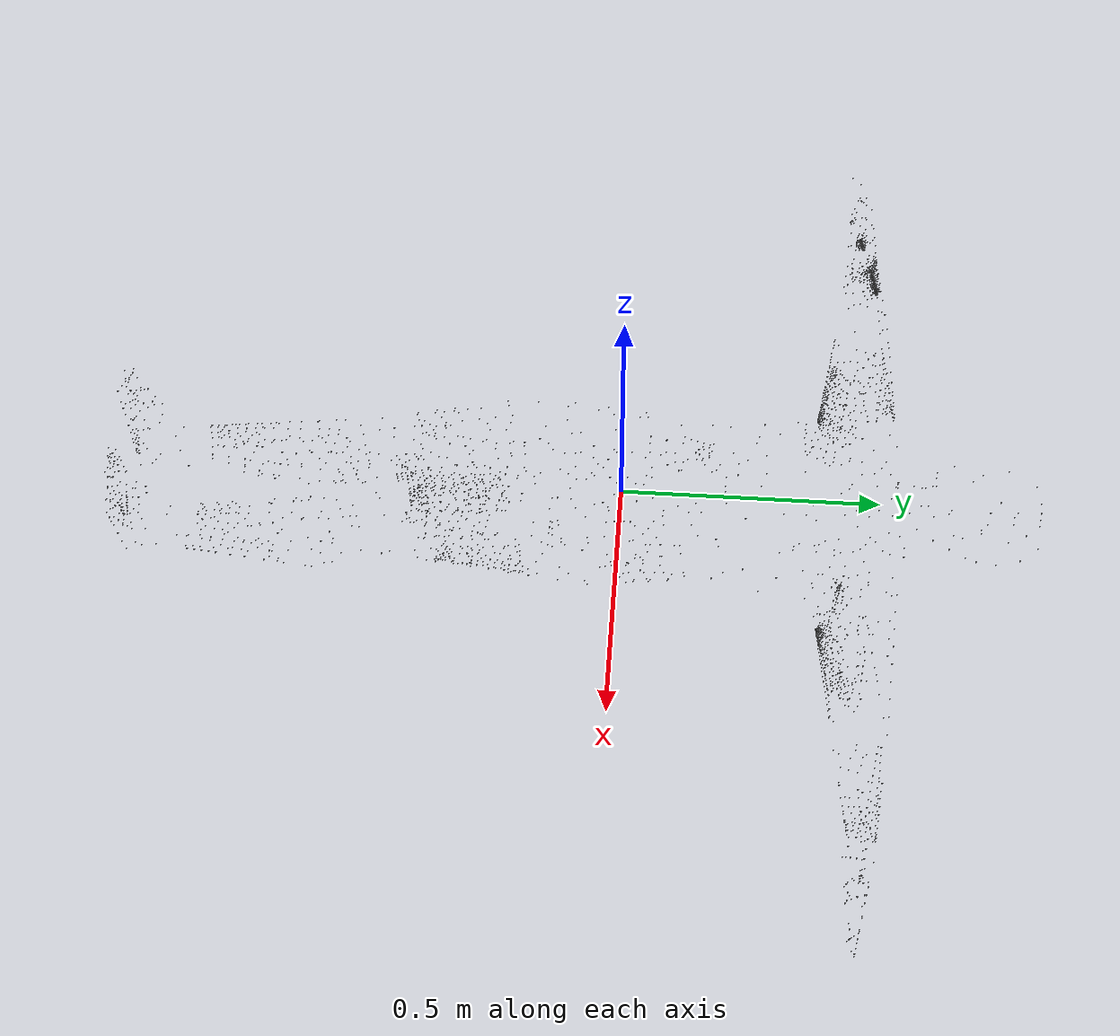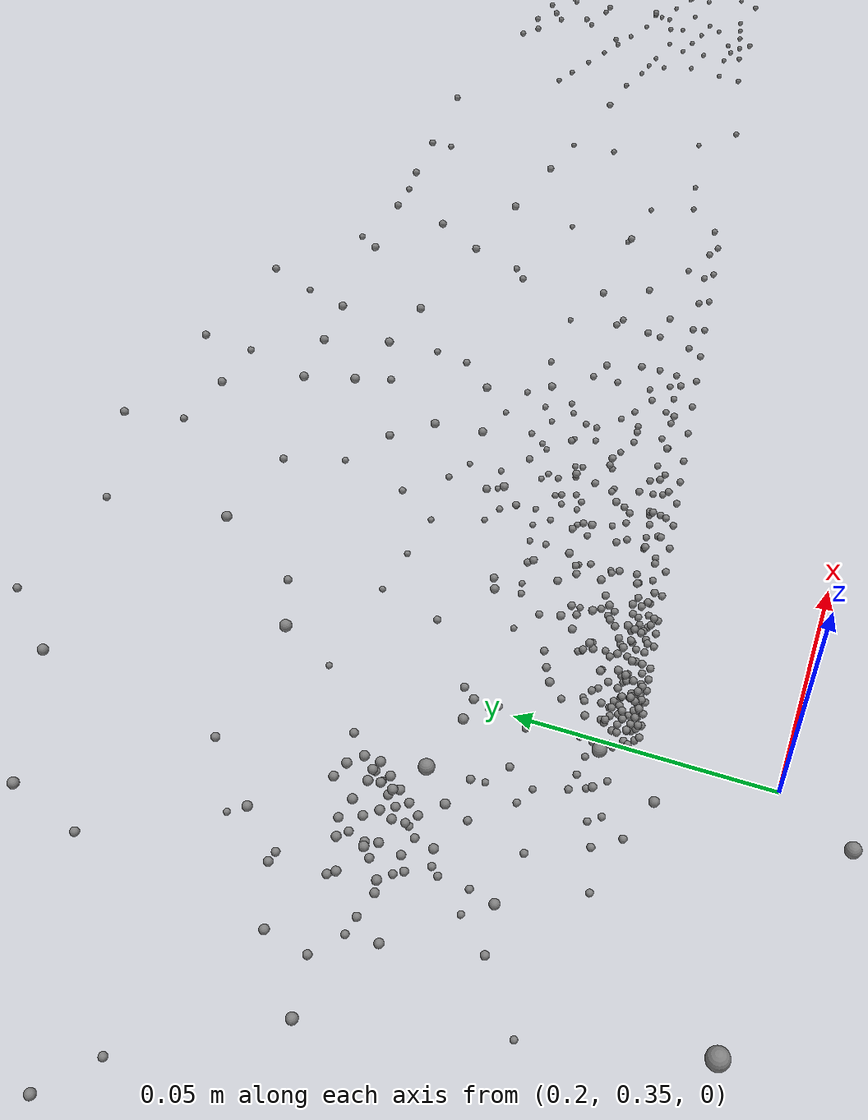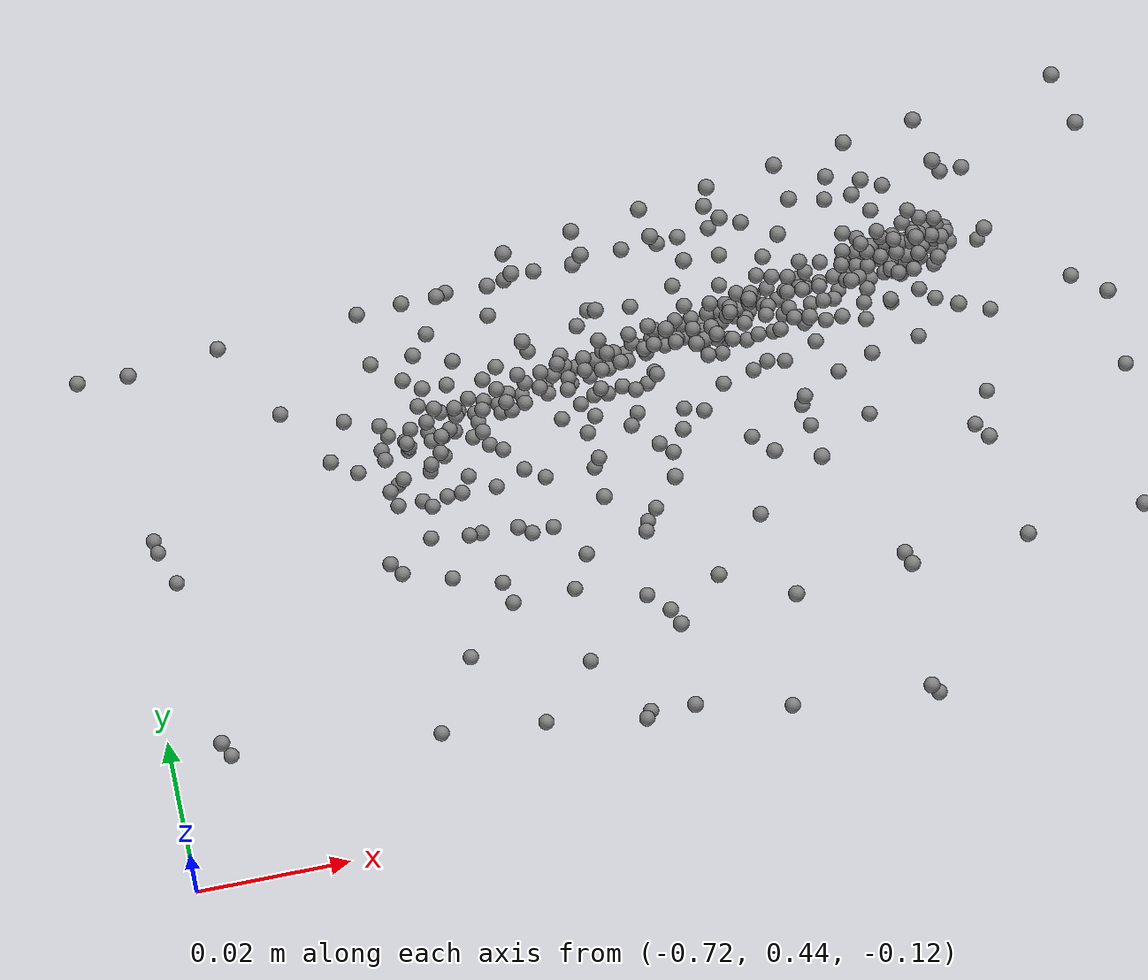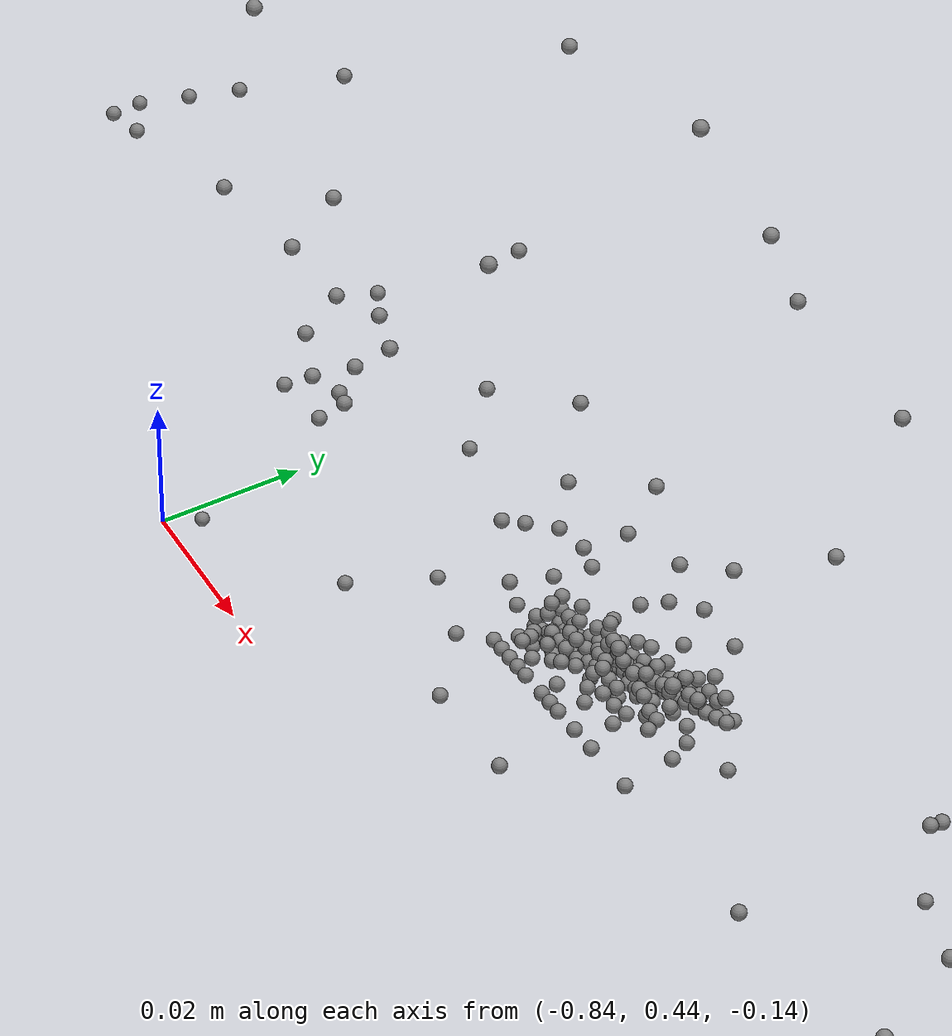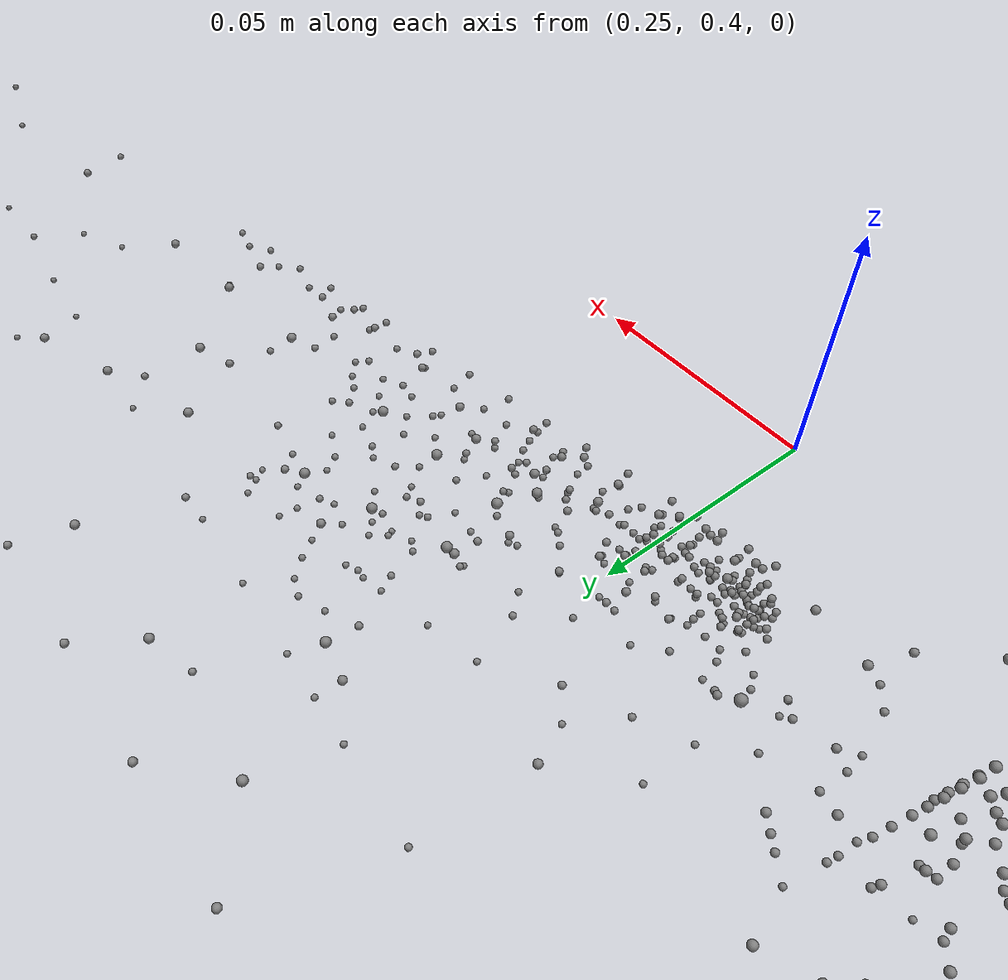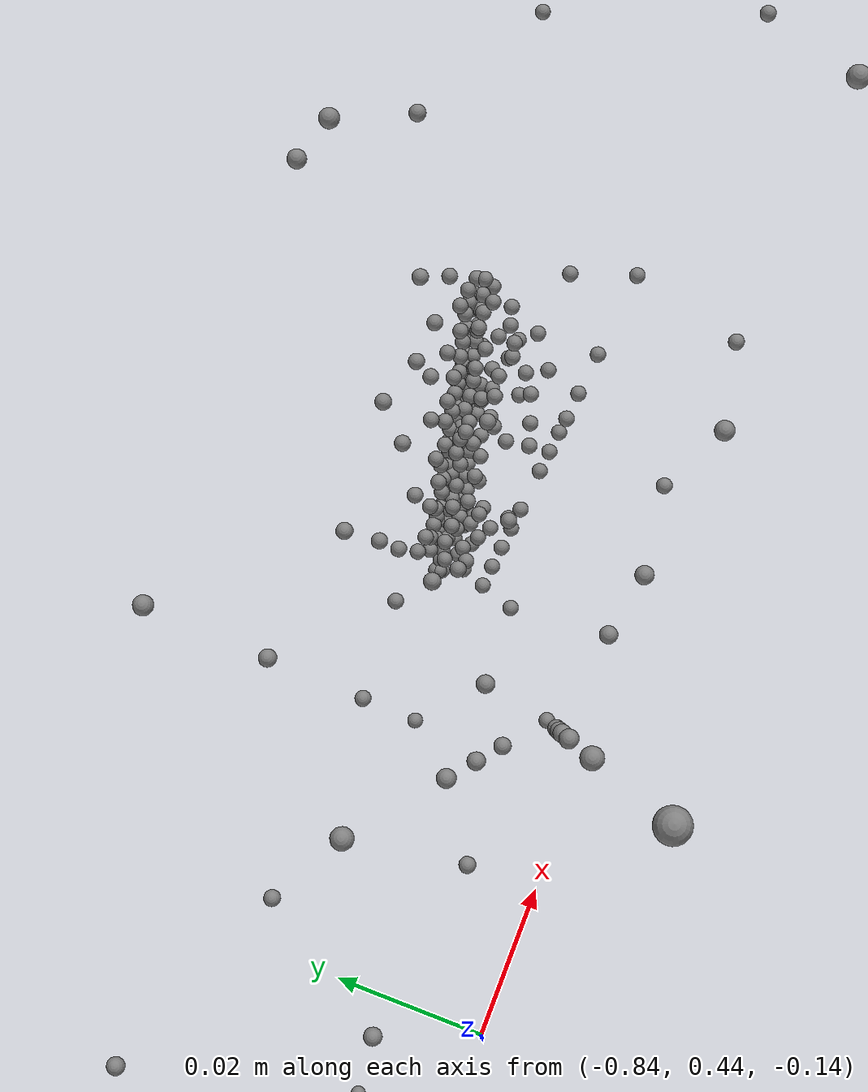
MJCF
<mujoco model="unnamed_model">
  <default>
    <default class="/"/>
  </default>
  <worldbody>
    <body name="point_mass_0">
      <freejoint name="//unnamed_joint_0"/>
      <geom name="point_mass_0" class="/" type="sphere" size="0.001" mass="0.01" pos="0.13640055060386658 0.18203732371330261 -0.081478551030158997"/>
    </body>
    <body name="point_mass_1">
      <freejoint name="//unnamed_joint_1"/>
      <geom name="point_mass_1" class="/" type="sphere" size="0.001" mass="0.01" pos="0.15620194375514984 -0.056002099066972733 -0.093732371926307678"/>
    </body>
    <body name="point_mass_2">
      <freejoint name="//unnamed_joint_2"/>
      <geom name="point_mass_2" class="/" type="sphere" size="0.001" mass="0.01" pos="0.12377142161130905 -0.063247710466384888 -0.13120388984680176"/>
    </body>
    <body name="point_mass_3">
      <freejoint name="//unnamed_joint_3"/>
      <geom name="point_mass_3" class="/" type="sphere" size="0.001" mass="0.01" pos="0.15091438591480255 0.19111129641532898 0.04627135768532753"/>
    </body>
    <body name="point_mass_4">
      <freejoint name="//unnamed_joint_4"/>
      <geom name="point_mass_4" class="/" type="sphere" size="0.001" mass="0.01" pos="0.049094084650278091 0.11424221843481064 0.14417916536331177"/>
    </body>
    <body name="point_mass_5">
      <freejoint name="//unnamed_joint_5"/>
      <geom name="point_mass_5" class="/" type="sphere" size="0.001" mass="0.01" pos="0.16448202729225159 -0.054161284118890762 0.055852863937616348"/>
    </body>
    <body name="point_mass_6">
      <freejoint name="//unnamed_joint_6"/>
      <geom name="point_mass_6" class="/" type="sphere" size="0.001" mass="0.01" pos="0.18853607773780823 -0.090344980359077454 -0.013293173164129257"/>
    </body>
    <body name="point_mass_7">
      <freejoint name="//unnamed_joint_7"/>
      <geom name="point_mass_7" class="/" type="sphere" size="0.001" mass="0.01" pos="0.16285230219364166 0.20296540856361389 -0.021814804524183273"/>
    </body>
    <body name="point_mass_8">
      <freejoint name="//unnamed_joint_8"/>
      <geom name="point_mass_8" class="/" type="sphere" size="0.001" mass="0.01" pos="-0.081390790641307831 -0.10271889716386795 -0.14455558359622955"/>
    </body>
    <body name="point_mass_9">
      <freejoint name="//unnamed_joint_9"/>
      <geom name="point_mass_9" class="/" type="sphere" size="0.001" mass="0.01" pos="0.10506662726402283 -0.12657803297042847 -0.12468226999044418"/>
    </body>
    <body name="point_mass_10">
      <freejoint name="//unnamed_joint_10"/>
      <geom name="point_mass_10" class="/" type="sphere" size="0.001" mass="0.01" pos="-0.065166771411895752 -0.13905543088912964 -0.12319212406873703"/>
    </body>
    <body name="point_mass_11">
      <freejoint name="//unnamed_joint_11"/>
      <geom name="point_mass_11" class="/" type="sphere" size="0.001" mass="0.01" pos="-0.12221689522266388 -0.075045429170131683 -0.13160137832164764"/>
    </body>
    <body name="point_mass_12">
      <freejoint name="//unnamed_joint_12"/>
      <geom name="point_mass_12" class="/" type="sphere" size="0.001" mass="0.01" pos="0.045279506593942642 -0.098816610872745514 0.11091477423906326"/>
    </body>
    <body name="point_mass_13">
      <freejoint name="//unnamed_joint_13"/>
      <geom name="point_mass_13" class="/" type="sphere" size="0.001" mass="0.01" pos="0.0054304338991641998 -0.10840889811515808 0.12168647348880768"/>
    </body>
    <body name="point_mass_14">
      <freejoint name="//unnamed_joint_14"/>
      <geom name="point_mass_14" class="/" type="sphere" size="0.001" mass="0.01" pos="0.014003892429172993 -0.13793650269508362 0.097407929599285126"/>
    </body>
    <body name="point_mass_15">
      <freejoint name="//unnamed_joint_15"/>
      <geom name="point_mass_15" class="/" type="sphere" size="0.001" mass="0.01" pos="-0.18606626987457275 -0.024135282263159752 0.0024600536562502384"/>
    </body>
    <body name="point_mass_16">
      <freejoint name="//unnamed_joint_16"/>
      <geom name="point_mass_16" class="/" type="sphere" size="0.001" mass="0.01" pos="-0.1891389787197113 -0.11637917906045914 -0.027472475543618202"/>
    </body>
    <body name="point_mass_17">
      <freejoint name="//unnamed_joint_17"/>
      <geom name="point_mass_17" class="/" type="sphere" size="0.001" mass="0.01" pos="-0.17305344343185425 -0.10016640275716782 0.049136616289615631"/>
    </body>
    <body name="point_mass_18">
      <freejoint name="//unnamed_joint_18"/>
      <geom name="point_mass_18" class="/" type="sphere" size="0.001" mass="0.01" pos="-0.14853550493717194 0.20818208158016205 0.036103833466768265"/>
    </body>
    <body name="point_mass_19">
      <freejoint name="//unnamed_joint_19"/>
      <geom name="point_mass_19" class="/" type="sphere" size="0.001" mass="0.01" pos="-0.15312425792217255 0.21496087312698364 -0.05972907692193985"/>
    </body>
    <body name="point_mass_20">
      <freejoint name="//unnamed_joint_20"/>
      <geom name="point_mass_20" class="/" type="sphere" size="0.001" mass="0.01" pos="-0.099748097360134125 0.1467718780040741 -0.11225739866495132"/>
    </body>
    <body name="point_mass_21">
      <freejoint name="//unnamed_joint_21"/>
      <geom name="point_mass_21" class="/" type="sphere" size="0.001" mass="0.01" pos="-0.15861758589744568 -0.087917611002922058 -0.090650387108325958"/>
    </body>
    <body name="point_mass_22">
      <freejoint name="//unnamed_joint_22"/>
      <geom name="point_mass_22" class="/" type="sphere" size="0.001" mass="0.01" pos="-0.072169534862041473 -0.029306000098586082 -0.15308722853660583"/>
    </body>
    <body name="point_mass_23">
      <freejoint name="//unnamed_joint_23"/>
      <geom name="point_mass_23" class="/" type="sphere" size="0.001" mass="0.01" pos="0.07319372147321701 -0.035436429083347321 -0.15373152494430542"/>
    </body>
    <body name="point_mass_24">
      <freejoint name="//unnamed_joint_24"/>
      <geom name="point_mass_24" class="/" type="sphere" size="0.001" mass="0.01" pos="-0.020156167447566986 -0.13225606083869934 0.096932709217071533"/>
    </body>
    <body name="point_mass_25">
      <freejoint name="//unnamed_joint_25"/>
      <geom name="point_mass_25" class="/" type="sphere" size="0.001" mass="0.01" pos="-0.13685253262519836 -0.051968585699796677 0.076787874102592468"/>
    </body>
    <body name="point_mass_26">
      <freejoint name="//unnamed_joint_26"/>
      <geom name="point_mass_26" class="/" type="sphere" size="0.001" mass="0.01" pos="-0.060568250715732574 0.11024139076471329 0.14101262390613556"/>
    </body>
    <body name="point_mass_27">
      <freejoint name="//unnamed_joint_27"/>
      <geom name="point_mass_27" class="/" type="sphere" size="0.001" mass="0.01" pos="0.076297573745250702 0.13125471770763397 -0.11183696240186691"/>
    </body>
    <body name="point_mass_28">
      <freejoint name="//unnamed_joint_28"/>
      <geom name="point_mass_28" class="/" type="sphere" size="0.001" mass="0.01" pos="-0.85400152206420898 0.45256710052490234 -0.1572096049785614"/>
    </body>
    <body name="point_mass_29">
      <freejoint name="//unnamed_joint_29"/>
      <geom name="point_mass_29" class="/" type="sphere" size="0.001" mass="0.01" pos="-0.90244543552398682 0.45949658751487732 -0.042105335742235184"/>
    </body>
    <body name="point_mass_30">
      <freejoint name="//unnamed_joint_30"/>
      <geom name="point_mass_30" class="/" type="sphere" size="0.001" mass="0.01" pos="-0.91700321435928345 0.46543687582015991 -0.093852199614048004"/>
    </body>
    <body name="point_mass_31">
      <freejoint name="//unnamed_joint_31"/>
      <geom name="point_mass_31" class="/" type="sphere" size="0.001" mass="0.01" pos="-0.81235045194625854 0.48494482040405273 -0.056171298027038574"/>
    </body>
    <body name="point_mass_32">
      <freejoint name="//unnamed_joint_32"/>
      <geom name="point_mass_32" class="/" type="sphere" size="0.001" mass="0.01" pos="-0.89762008190155029 0.46668648719787598 -0.12230852246284485"/>
    </body>
    <body name="point_mass_33">
      <freejoint name="//unnamed_joint_33"/>
      <geom name="point_mass_33" class="/" type="sphere" size="0.001" mass="0.01" pos="-0.8056904673576355 0.46237865090370178 -0.13134656846523285"/>
    </body>
    <body name="point_mass_34">
      <freejoint name="//unnamed_joint_34"/>
      <geom name="point_mass_34" class="/" type="sphere" size="0.001" mass="0.01" pos="-0.80088609457015991 0.44650116562843323 -0.12064192444086075"/>
    </body>
    <body name="point_mass_35">
      <freejoint name="//unnamed_joint_35"/>
      <geom name="point_mass_35" class="/" type="sphere" size="0.001" mass="0.01" pos="-0.82620388269424438 0.45857810974121094 -0.036845363676548004"/>
    </body>
    <body name="point_mass_36">
      <freejoint name="//unnamed_joint_36"/>
      <geom name="point_mass_36" class="/" type="sphere" size="0.001" mass="0.01" pos="0.75086712837219238 0.49440398812294006 -0.056794688105583191"/>
    </body>
    <body name="point_mass_37">
      <freejoint name="//unnamed_joint_37"/>
      <geom name="point_mass_37" class="/" type="sphere" size="0.001" mass="0.01" pos="0.92154711484909058 0.4634850025177002 -0.093751028180122375"/>
    </body>
    <body name="point_mass_38">
      <freejoint name="//unnamed_joint_38"/>
      <geom name="point_mass_38" class="/" type="sphere" size="0.001" mass="0.01" pos="0.90252941846847534 0.46686658263206482 -0.12063921242952347"/>
    </body>
    <body name="point_mass_39">
      <freejoint name="//unnamed_joint_39"/>
      <geom name="point_mass_39" class="/" type="sphere" size="0.001" mass="0.01" pos="0.9074370265007019 0.46006190776824951 -0.042022105306386948"/>
    </body>
    <body name="point_mass_40">
      <freejoint name="//unnamed_joint_40"/>
      <geom name="point_mass_40" class="/" type="sphere" size="0.001" mass="0.01" pos="0.82465654611587524 0.47838523983955383 -0.045227017253637314"/>
    </body>
    <body name="point_mass_41">
      <freejoint name="//unnamed_joint_41"/>
      <geom name="point_mass_41" class="/" type="sphere" size="0.001" mass="0.01" pos="0.85869050025939941 0.45644226670265198 -0.15775500237941742"/>
    </body>
    <body name="point_mass_42">
      <freejoint name="//unnamed_joint_42"/>
      <geom name="point_mass_42" class="/" type="sphere" size="0.001" mass="0.01" pos="0.78842359781265259 0.47067853808403015 -0.11906909197568893"/>
    </body>
    <body name="point_mass_43">
      <freejoint name="//unnamed_joint_43"/>
      <geom name="point_mass_43" class="/" type="sphere" size="0.001" mass="0.01" pos="0.77045875787734985 0.44669091701507568 -0.11678808927536011"/>
    </body>
    <body name="point_mass_44">
      <freejoint name="//unnamed_joint_44"/>
      <geom name="point_mass_44" class="/" type="sphere" size="0.001" mass="0.01" pos="0.83155417442321777 0.45559272170066833 -0.048448286950588226"/>
    </body>
    <body name="point_mass_45">
      <freejoint name="//unnamed_joint_45"/>
      <geom name="point_mass_45" class="/" type="sphere" size="0.001" mass="0.01" pos="-0.71641337871551514 0.48554885387420654 -0.043694276362657547"/>
    </body>
    <body name="point_mass_46">
      <freejoint name="//unnamed_joint_46"/>
      <geom name="point_mass_46" class="/" type="sphere" size="0.001" mass="0.01" pos="-0.82192206382751465 0.43927335739135742 0.026770174503326416"/>
    </body>
    <body name="point_mass_47">
      <freejoint name="//unnamed_joint_47"/>
      <geom name="point_mass_47" class="/" type="sphere" size="0.001" mass="0.01" pos="-0.71379339694976807 0.44278639554977417 -0.060101427137851715"/>
    </body>
    <body name="point_mass_48">
      <freejoint name="//unnamed_joint_48"/>
      <geom name="point_mass_48" class="/" type="sphere" size="0.001" mass="0.01" pos="-0.56002604961395264 0.50888502597808838 -0.089828722178936005"/>
    </body>
    <body name="point_mass_49">
      <freejoint name="//unnamed_joint_49"/>
      <geom name="point_mass_49" class="/" type="sphere" size="0.001" mass="0.01" pos="-0.71661639213562012 0.48078826069831848 -0.10494212806224823"/>
    </body>
    <body name="point_mass_50">
      <freejoint name="//unnamed_joint_50"/>
      <geom name="point_mass_50" class="/" type="sphere" size="0.001" mass="0.01" pos="-0.75140243768692017 0.44129815697669983 -0.10638364404439926"/>
    </body>
    <body name="point_mass_51">
      <freejoint name="//unnamed_joint_51"/>
      <geom name="point_mass_51" class="/" type="sphere" size="0.001" mass="0.01" pos="-0.71249580383300781 0.45179444551467896 -0.10116637498140335"/>
    </body>
    <body name="point_mass_52">
      <freejoint name="//unnamed_joint_52"/>
      <geom name="point_mass_52" class="/" type="sphere" size="0.001" mass="0.01" pos="-0.21458053588867188 0.3820769190788269 -0.083484023809432983"/>
    </body>
    <body name="point_mass_53">
      <freejoint name="//unnamed_joint_53"/>
      <geom name="point_mass_53" class="/" type="sphere" size="0.001" mass="0.01" pos="-0.204700767993927 0.41863012313842773 -0.10811720788478851"/>
    </body>
    <body name="point_mass_54">
      <freejoint name="//unnamed_joint_54"/>
      <geom name="point_mass_54" class="/" type="sphere" size="0.001" mass="0.01" pos="-0.20281209051609039 0.45939174294471741 0.024949287995696068"/>
    </body>
    <body name="point_mass_55">
      <freejoint name="//unnamed_joint_55"/>
      <geom name="point_mass_55" class="/" type="sphere" size="0.001" mass="0.01" pos="-0.21497076749801636 0.38070473074913025 -0.04114847257733345"/>
    </body>
    <body name="point_mass_56">
      <freejoint name="//unnamed_joint_56"/>
      <geom name="point_mass_56" class="/" type="sphere" size="0.001" mass="0.01" pos="0.83020424842834473 0.45033833384513855 0.021875826641917229"/>
    </body>
    <body name="point_mass_57">
      <freejoint name="//unnamed_joint_57"/>
      <geom name="point_mass_57" class="/" type="sphere" size="0.001" mass="0.01" pos="0.71837413311004639 0.47074952721595764 -0.041681576520204544"/>
    </body>
    <body name="point_mass_58">
      <freejoint name="//unnamed_joint_58"/>
      <geom name="point_mass_58" class="/" type="sphere" size="0.001" mass="0.01" pos="0.75690722465515137 0.4371526837348938 -0.033698610961437225"/>
    </body>
    <body name="point_mass_59">
      <freejoint name="//unnamed_joint_59"/>
      <geom name="point_mass_59" class="/" type="sphere" size="0.001" mass="0.01" pos="0.72035074234008789 0.44921433925628662 -0.05917227640748024"/>
    </body>
    <body name="point_mass_60">
      <freejoint name="//unnamed_joint_60"/>
      <geom name="point_mass_60" class="/" type="sphere" size="0.001" mass="0.01" pos="0.71827536821365356 0.45664474368095398 -0.10312327742576599"/>
    </body>
    <body name="point_mass_61">
      <freejoint name="//unnamed_joint_61"/>
      <geom name="point_mass_61" class="/" type="sphere" size="0.001" mass="0.01" pos="-0.45026475191116333 0.50034517049789429 -0.027955006808042526"/>
    </body>
    <body name="point_mass_62">
      <freejoint name="//unnamed_joint_62"/>
      <geom name="point_mass_62" class="/" type="sphere" size="0.001" mass="0.01" pos="-0.44883754849433899 0.44959044456481934 -0.022625602781772614"/>
    </body>
    <body name="point_mass_63">
      <freejoint name="//unnamed_joint_63"/>
      <geom name="point_mass_63" class="/" type="sphere" size="0.001" mass="0.01" pos="-0.43303021788597107 0.5142667293548584 -0.068926766514778137"/>
    </body>
    <body name="point_mass_64">
      <freejoint name="//unnamed_joint_64"/>
      <geom name="point_mass_64" class="/" type="sphere" size="0.001" mass="0.01" pos="-0.51762479543685913 0.48271521925926208 -0.11083169281482697"/>
    </body>
    <body name="point_mass_65">
      <freejoint name="//unnamed_joint_65"/>
      <geom name="point_mass_65" class="/" type="sphere" size="0.001" mass="0.01" pos="-0.44823890924453735 0.45714259147644043 -0.10922840982675552"/>
    </body>
    <body name="point_mass_66">
      <freejoint name="//unnamed_joint_66"/>
      <geom name="point_mass_66" class="/" type="sphere" size="0.001" mass="0.01" pos="-0.47717362642288208 0.51700574159622192 -0.044103391468524933"/>
    </body>
    <body name="point_mass_67">
      <freejoint name="//unnamed_joint_67"/>
      <geom name="point_mass_67" class="/" type="sphere" size="0.001" mass="0.01" pos="-0.51283282041549683 0.41954571008682251 -0.060725018382072449"/>
    </body>
    <body name="point_mass_68">
      <freejoint name="//unnamed_joint_68"/>
      <geom name="point_mass_68" class="/" type="sphere" size="0.001" mass="0.01" pos="-0.58259409666061401 0.44183546304702759 -0.10818442702293396"/>
    </body>
    <body name="point_mass_69">
      <freejoint name="//unnamed_joint_69"/>
      <geom name="point_mass_69" class="/" type="sphere" size="0.001" mass="0.01" pos="-0.45278847217559814 0.42000234127044678 -0.072769321501255035"/>
    </body>
    <body name="point_mass_70">
      <freejoint name="//unnamed_joint_70"/>
      <geom name="point_mass_70" class="/" type="sphere" size="0.001" mass="0.01" pos="0.46135848760604858 0.50975668430328369 -0.031660590320825577"/>
    </body>
    <body name="point_mass_71">
      <freejoint name="//unnamed_joint_71"/>
      <geom name="point_mass_71" class="/" type="sphere" size="0.001" mass="0.01" pos="0.51953375339508057 0.42087399959564209 -0.060244418680667877"/>
    </body>
    <body name="point_mass_72">
      <freejoint name="//unnamed_joint_72"/>
      <geom name="point_mass_72" class="/" type="sphere" size="0.001" mass="0.01" pos="0.58965730667114258 0.44652512669563293 -0.10879328846931458"/>
    </body>
    <body name="point_mass_73">
      <freejoint name="//unnamed_joint_73"/>
      <geom name="point_mass_73" class="/" type="sphere" size="0.001" mass="0.01" pos="0.55982249975204468 0.49502164125442505 -0.10147258639335632"/>
    </body>
    <body name="point_mass_74">
      <freejoint name="//unnamed_joint_74"/>
      <geom name="point_mass_74" class="/" type="sphere" size="0.001" mass="0.01" pos="0.47984820604324341 0.51999491453170776 -0.062461104243993759"/>
    </body>
    <body name="point_mass_75">
      <freejoint name="//unnamed_joint_75"/>
      <geom name="point_mass_75" class="/" type="sphere" size="0.001" mass="0.01" pos="0.45746517181396484 0.45445087552070618 -0.022197360172867775"/>
    </body>
    <body name="point_mass_76">
      <freejoint name="//unnamed_joint_76"/>
      <geom name="point_mass_76" class="/" type="sphere" size="0.001" mass="0.01" pos="0.44926959276199341 0.42016023397445679 -0.073787495493888855"/>
    </body>
    <body name="point_mass_77">
      <freejoint name="//unnamed_joint_77"/>
      <geom name="point_mass_77" class="/" type="sphere" size="0.001" mass="0.01" pos="0.44979840517044067 0.4621201753616333 -0.10602371394634247"/>
    </body>
    <body name="point_mass_78">
      <freejoint name="//unnamed_joint_78"/>
      <geom name="point_mass_78" class="/" type="sphere" size="0.001" mass="0.01" pos="-0.1665617823600769 0.51754158735275269 0.0058743609115481377"/>
    </body>
    <body name="point_mass_79">
      <freejoint name="//unnamed_joint_79"/>
      <geom name="point_mass_79" class="/" type="sphere" size="0.001" mass="0.01" pos="-0.17082265019416809 0.5351671576499939 -0.035180605947971344"/>
    </body>
    <body name="point_mass_80">
      <freejoint name="//unnamed_joint_80"/>
      <geom name="point_mass_80" class="/" type="sphere" size="0.001" mass="0.01" pos="-0.21893937885761261 0.37640589475631714 -0.066158302128314972"/>
    </body>
    <body name="point_mass_81">
      <freejoint name="//unnamed_joint_81"/>
      <geom name="point_mass_81" class="/" type="sphere" size="0.001" mass="0.01" pos="-0.20813015103340149 0.49471697211265564 -0.099956706166267395"/>
    </body>
    <body name="point_mass_82">
      <freejoint name="//unnamed_joint_82"/>
      <geom name="point_mass_82" class="/" type="sphere" size="0.001" mass="0.01" pos="0.22117264568805695 0.3798488974571228 -0.067913800477981567"/>
    </body>
    <body name="point_mass_83">
      <freejoint name="//unnamed_joint_83"/>
      <geom name="point_mass_83" class="/" type="sphere" size="0.001" mass="0.01" pos="0.21614742279052734 0.38714820146560669 -0.041792139410972595"/>
    </body>
    <body name="point_mass_84">
      <freejoint name="//unnamed_joint_84"/>
      <geom name="point_mass_84" class="/" type="sphere" size="0.001" mass="0.01" pos="0.21547463536262512 0.38518360257148743 -0.087218835949897766"/>
    </body>
    <body name="point_mass_85">
      <freejoint name="//unnamed_joint_85"/>
      <geom name="point_mass_85" class="/" type="sphere" size="0.001" mass="0.01" pos="0.21291682124137878 0.46248054504394531 0.019547957926988602"/>
    </body>
    <body name="point_mass_86">
      <freejoint name="//unnamed_joint_86"/>
      <geom name="point_mass_86" class="/" type="sphere" size="0.001" mass="0.01" pos="0.16920264065265656 0.52414983510971069 -0.00092321180272847414"/>
    </body>
    <body name="point_mass_87">
      <freejoint name="//unnamed_joint_87"/>
      <geom name="point_mass_87" class="/" type="sphere" size="0.001" mass="0.01" pos="0.21603687107563019 0.486143559217453 -0.10581257939338684"/>
    </body>
    <body name="point_mass_88">
      <freejoint name="//unnamed_joint_88"/>
      <geom name="point_mass_88" class="/" type="sphere" size="0.001" mass="0.01" pos="0.20833414793014526 0.41610759496688843 -0.10526822507381439"/>
    </body>
    <body name="point_mass_89">
      <freejoint name="//unnamed_joint_89"/>
      <geom name="point_mass_89" class="/" type="sphere" size="0.001" mass="0.01" pos="0.18439239263534546 0.53442192077636719 -0.033612564206123352"/>
    </body>
    <body name="point_mass_90">
      <freejoint name="//unnamed_joint_90"/>
      <geom name="point_mass_90" class="/" type="sphere" size="0.001" mass="0.01" pos="-0.026234826073050499 0.79536014795303345 0.049276288598775864"/>
    </body>
    <body name="point_mass_91">
      <freejoint name="//unnamed_joint_91"/>
      <geom name="point_mass_91" class="/" type="sphere" size="0.001" mass="0.01" pos="0.017457446083426476 0.80289900302886963 0.052172295749187469"/>
    </body>
    <body name="point_mass_92">
      <freejoint name="//unnamed_joint_92"/>
      <geom name="point_mass_92" class="/" type="sphere" size="0.001" mass="0.01" pos="-0.018224740400910378 0.81525576114654541 -0.046793539077043533"/>
    </body>
    <body name="point_mass_93">
      <freejoint name="//unnamed_joint_93"/>
      <geom name="point_mass_93" class="/" type="sphere" size="0.001" mass="0.01" pos="0.0059890882112085819 0.68341010808944702 0.11928608268499374"/>
    </body>
    <body name="point_mass_94">
      <freejoint name="//unnamed_joint_94"/>
      <geom name="point_mass_94" class="/" type="sphere" size="0.001" mass="0.01" pos="0.071055427193641663 0.77566319704055786 0.02118607796728611"/>
    </body>
    <body name="point_mass_95">
      <freejoint name="//unnamed_joint_95"/>
      <geom name="point_mass_95" class="/" type="sphere" size="0.001" mass="0.01" pos="0.051884997636079788 0.75458407402038574 0.067725785076618195"/>
    </body>
    <body name="point_mass_96">
      <freejoint name="//unnamed_joint_96"/>
      <geom name="point_mass_96" class="/" type="sphere" size="0.001" mass="0.01" pos="0.06065141037106514 0.62472903728485107 0.065827392041683197"/>
    </body>
    <body name="point_mass_97">
      <freejoint name="//unnamed_joint_97"/>
      <geom name="point_mass_97" class="/" type="sphere" size="0.001" mass="0.01" pos="-0.067586436867713928 0.778087317943573 -0.013556276448071003"/>
    </body>
    <body name="point_mass_98">
      <freejoint name="//unnamed_joint_98"/>
      <geom name="point_mass_98" class="/" type="sphere" size="0.001" mass="0.01" pos="-0.052080065011978149 0.77153408527374268 -0.090512849390506744"/>
    </body>
    <body name="point_mass_99">
      <freejoint name="//unnamed_joint_99"/>
      <geom name="point_mass_99" class="/" type="sphere" size="0.001" mass="0.01" pos="0.03519146516919136 0.81086808443069458 -0.068998128175735474"/>
    </body>
    <body name="point_mass_100">
      <freejoint name="//unnamed_joint_100"/>
      <geom name="point_mass_100" class="/" type="sphere" size="0.001" mass="0.01" pos="-0.061680413782596588 0.60264867544174194 -0.014862948097288609"/>
    </body>
    <body name="point_mass_101">
      <freejoint name="//unnamed_joint_101"/>
      <geom name="point_mass_101" class="/" type="sphere" size="0.001" mass="0.01" pos="-0.091614201664924622 0.68373662233352661 -0.033399462699890137"/>
    </body>
    <body name="point_mass_102">
      <freejoint name="//unnamed_joint_102"/>
      <geom name="point_mass_102" class="/" type="sphere" size="0.001" mass="0.01" pos="-0.030074246227741241 0.61089450120925903 -0.070166304707527161"/>
    </body>
    <body name="point_mass_103">
      <freejoint name="//unnamed_joint_103"/>
      <geom name="point_mass_103" class="/" type="sphere" size="0.001" mass="0.01" pos="0.10063988715410233 0.68599033355712891 -0.031234925612807274"/>
    </body>
    <body name="point_mass_104">
      <freejoint name="//unnamed_joint_104"/>
      <geom name="point_mass_104" class="/" type="sphere" size="0.001" mass="0.01" pos="0.050690814852714539 0.73456805944442749 -0.10972541570663452"/>
    </body>
    <body name="point_mass_105">
      <freejoint name="//unnamed_joint_105"/>
      <geom name="point_mass_105" class="/" type="sphere" size="0.001" mass="0.01" pos="0.042068719863891602 0.67344415187835693 -0.10265807062387466"/>
    </body>
    <body name="point_mass_106">
      <freejoint name="//unnamed_joint_106"/>
      <geom name="point_mass_106" class="/" type="sphere" size="0.001" mass="0.01" pos="0.077007979154586792 0.77336210012435913 -0.053953606635332108"/>
    </body>
    <body name="point_mass_107">
      <freejoint name="//unnamed_joint_107"/>
      <geom name="point_mass_107" class="/" type="sphere" size="0.001" mass="0.01" pos="0.067972771823406219 0.60235297679901123 -0.014456707984209061"/>
    </body>
    <body name="point_mass_108">
      <freejoint name="//unnamed_joint_108"/>
      <geom name="point_mass_108" class="/" type="sphere" size="0.001" mass="0.01" pos="0.0010852320119738579 0.57413709163665771 0.062444709241390228"/>
    </body>
    <body name="point_mass_109">
      <freejoint name="//unnamed_joint_109"/>
      <geom name="point_mass_109" class="/" type="sphere" size="0.001" mass="0.01" pos="-0.055439788848161697 0.63662040233612061 0.060840800404548645"/>
    </body>
    <body name="point_mass_110">
      <freejoint name="//unnamed_joint_110"/>
      <geom name="point_mass_110" class="/" type="sphere" size="0.001" mass="0.01" pos="-0.011985594406723976 0.59944099187850952 0.097194969654083252"/>
    </body>
    <body name="point_mass_111">
      <freejoint name="//unnamed_joint_111"/>
      <geom name="point_mass_111" class="/" type="sphere" size="0.001" mass="0.01" pos="-0.049261141568422318 0.74154090881347656 0.06094004213809967"/>
    </body>
    <body name="point_mass_112">
      <freejoint name="//unnamed_joint_112"/>
      <geom name="point_mass_112" class="/" type="sphere" size="0.001" mass="0.01" pos="-0.0087749240919947624 0.76033937931060791 -0.11390804499387741"/>
    </body>
    <body name="point_mass_113">
      <freejoint name="//unnamed_joint_113"/>
      <geom name="point_mass_113" class="/" type="sphere" size="0.001" mass="0.01" pos="-0.034177444875240326 0.70874321460723877 -0.11417535692453384"/>
    </body>
    <body name="point_mass_114">
      <freejoint name="//unnamed_joint_114"/>
      <geom name="point_mass_114" class="/" type="sphere" size="0.001" mass="0.01" pos="0.035479344427585602 0.58718043565750122 0.05246378481388092"/>
    </body>
    <body name="point_mass_115">
      <freejoint name="//unnamed_joint_115"/>
      <geom name="point_mass_115" class="/" type="sphere" size="0.001" mass="0.01" pos="0.020238351076841354 0.59828305244445801 0.097415924072265625"/>
    </body>
    <body name="point_mass_116">
      <freejoint name="//unnamed_joint_116"/>
      <geom name="point_mass_116" class="/" type="sphere" size="0.001" mass="0.01" pos="0.019501514732837677 0.60874444246292114 -0.078680366277694702"/>
    </body>
    <body name="point_mass_117">
      <freejoint name="//unnamed_joint_117"/>
      <geom name="point_mass_117" class="/" type="sphere" size="0.001" mass="0.01" pos="-0.18223182857036591 0.43835330009460449 0.028538955375552177"/>
    </body>
    <body name="point_mass_118">
      <freejoint name="//unnamed_joint_118"/>
      <geom name="point_mass_118" class="/" type="sphere" size="0.001" mass="0.01" pos="-0.04746999591588974 0.53935503959655762 -0.099037185311317444"/>
    </body>
    <body name="point_mass_119">
      <freejoint name="//unnamed_joint_119"/>
      <geom name="point_mass_119" class="/" type="sphere" size="0.001" mass="0.01" pos="-0.09607338160276413 0.47676137089729309 -0.13249872624874115"/>
    </body>
    <body name="point_mass_120">
      <freejoint name="//unnamed_joint_120"/>
      <geom name="point_mass_120" class="/" type="sphere" size="0.001" mass="0.01" pos="-0.10719022899866104 0.3841702938079834 -0.15149110555648804"/>
    </body>
    <body name="point_mass_121">
      <freejoint name="//unnamed_joint_121"/>
      <geom name="point_mass_121" class="/" type="sphere" size="0.001" mass="0.01" pos="-0.18787138164043427 0.39463812112808228 -0.1054803803563118"/>
    </body>
    <body name="point_mass_122">
      <freejoint name="//unnamed_joint_122"/>
      <geom name="point_mass_122" class="/" type="sphere" size="0.001" mass="0.01" pos="-0.1446654200553894 0.43840152025222778 0.045805457979440689"/>
    </body>
    <body name="point_mass_123">
      <freejoint name="//unnamed_joint_123"/>
      <geom name="point_mass_123" class="/" type="sphere" size="0.001" mass="0.01" pos="-0.10600725561380386 0.51150190830230713 -0.0026865685358643532"/>
    </body>
    <body name="point_mass_124">
      <freejoint name="//unnamed_joint_124"/>
      <geom name="point_mass_124" class="/" type="sphere" size="0.001" mass="0.01" pos="-0.095975890755653381 0.54136866331100464 -0.071317538619041443"/>
    </body>
    <body name="point_mass_125">
      <freejoint name="//unnamed_joint_125"/>
      <geom name="point_mass_125" class="/" type="sphere" size="0.001" mass="0.01" pos="0.17737111449241638 0.43035575747489929 0.040615681558847427"/>
    </body>
    <body name="point_mass_126">
      <freejoint name="//unnamed_joint_126"/>
      <geom name="point_mass_126" class="/" type="sphere" size="0.001" mass="0.01" pos="0.10798139870166779 0.51916742324829102 -0.010277138091623783"/>
    </body>
    <body name="point_mass_127">
      <freejoint name="//unnamed_joint_127"/>
      <geom name="point_mass_127" class="/" type="sphere" size="0.001" mass="0.01" pos="0.096590451896190643 0.48895630240440369 -0.13451950252056122"/>
    </body>
    <body name="point_mass_128">
      <freejoint name="//unnamed_joint_128"/>
      <geom name="point_mass_128" class="/" type="sphere" size="0.001" mass="0.01" pos="0.094933658838272095 0.38154476881027222 -0.15642589330673218"/>
    </body>
    <body name="point_mass_129">
      <freejoint name="//unnamed_joint_129"/>
      <geom name="point_mass_129" class="/" type="sphere" size="0.001" mass="0.01" pos="0.1850149929523468 0.39386484026908875 -0.11284072697162628"/>
    </body>
    <body name="point_mass_130">
      <freejoint name="//unnamed_joint_130"/>
      <geom name="point_mass_130" class="/" type="sphere" size="0.001" mass="0.01" pos="0.061448819935321808 0.55277895927429199 -0.082353211939334869"/>
    </body>
    <body name="point_mass_131">
      <freejoint name="//unnamed_joint_131"/>
      <geom name="point_mass_131" class="/" type="sphere" size="0.001" mass="0.01" pos="-0.05673116073012352 0.56325256824493408 -0.068929009139537811"/>
    </body>
    <body name="point_mass_132">
      <freejoint name="//unnamed_joint_132"/>
      <geom name="point_mass_132" class="/" type="sphere" size="0.001" mass="0.01" pos="0.077385015785694122 0.54854482412338257 -0.029840875416994095"/>
    </body>
    <body name="point_mass_133">
      <freejoint name="//unnamed_joint_133"/>
      <geom name="point_mass_133" class="/" type="sphere" size="0.001" mass="0.01" pos="-0.069718964397907257 0.53782999515533447 -0.018447345122694969"/>
    </body>
    <body name="point_mass_134">
      <freejoint name="//unnamed_joint_134"/>
      <geom name="point_mass_134" class="/" type="sphere" size="0.001" mass="0.01" pos="-0.018082335591316223 0.52713483572006226 0.035468310117721558"/>
    </body>
    <body name="point_mass_135">
      <freejoint name="//unnamed_joint_135"/>
      <geom name="point_mass_135" class="/" type="sphere" size="0.001" mass="0.01" pos="0.0296812504529953 0.52782601118087769 0.035457193851470947"/>
    </body>
    <body name="point_mass_136">
      <freejoint name="//unnamed_joint_136"/>
      <geom name="point_mass_136" class="/" type="sphere" size="0.001" mass="0.01" pos="-0.077750951051712036 -0.95699095726013184 0.15101231634616852"/>
    </body>
    <body name="point_mass_137">
      <freejoint name="//unnamed_joint_137"/>
      <geom name="point_mass_137" class="/" type="sphere" size="0.001" mass="0.01" pos="-0.061718933284282684 -0.94911545515060425 0.073197729885578156"/>
    </body>
    <body name="point_mass_138">
      <freejoint name="//unnamed_joint_138"/>
      <geom name="point_mass_138" class="/" type="sphere" size="0.001" mass="0.01" pos="-0.096389114856719971 -0.92858940362930298 0.065640613436698914"/>
    </body>
    <body name="point_mass_139">
      <freejoint name="//unnamed_joint_139"/>
      <geom name="point_mass_139" class="/" type="sphere" size="0.001" mass="0.01" pos="-0.15832988917827606 -0.96162450313568115 0.10555577278137207"/>
    </body>
    <body name="point_mass_140">
      <freejoint name="//unnamed_joint_140"/>
      <geom name="point_mass_140" class="/" type="sphere" size="0.001" mass="0.01" pos="-0.16948430240154266 -0.96909403800964355 0.077797763049602509"/>
    </body>
    <body name="point_mass_141">
      <freejoint name="//unnamed_joint_141"/>
      <geom name="point_mass_141" class="/" type="sphere" size="0.001" mass="0.01" pos="-0.069257758557796478 -0.97284317016601562 0.14605407416820526"/>
    </body>
    <body name="point_mass_142">
      <freejoint name="//unnamed_joint_142"/>
      <geom name="point_mass_142" class="/" type="sphere" size="0.001" mass="0.01" pos="-0.11893097311258316 -0.96787387132644653 0.14742377400398254"/>
    </body>
    <body name="point_mass_143">
      <freejoint name="//unnamed_joint_143"/>
      <geom name="point_mass_143" class="/" type="sphere" size="0.001" mass="0.01" pos="0.1605994701385498 -0.95645672082901001 0.10135886073112488"/>
    </body>
    <body name="point_mass_144">
      <freejoint name="//unnamed_joint_144"/>
      <geom name="point_mass_144" class="/" type="sphere" size="0.001" mass="0.01" pos="0.099623791873455048 -0.92754393815994263 0.064571380615234375"/>
    </body>
    <body name="point_mass_145">
      <freejoint name="//unnamed_joint_145"/>
      <geom name="point_mass_145" class="/" type="sphere" size="0.001" mass="0.01" pos="0.074256613850593567 -0.9529109001159668 0.15153148770332336"/>
    </body>
    <body name="point_mass_146">
      <freejoint name="//unnamed_joint_146"/>
      <geom name="point_mass_146" class="/" type="sphere" size="0.001" mass="0.01" pos="0.17056936025619507 -0.96470177173614502 0.080109164118766785"/>
    </body>
    <body name="point_mass_147">
      <freejoint name="//unnamed_joint_147"/>
      <geom name="point_mass_147" class="/" type="sphere" size="0.001" mass="0.01" pos="0.065147273242473602 -0.94527935981750488 0.071939922869205475"/>
    </body>
    <body name="point_mass_148">
      <freejoint name="//unnamed_joint_148"/>
      <geom name="point_mass_148" class="/" type="sphere" size="0.001" mass="0.01" pos="0.067872956395149231 -0.96871262788772583 0.1463189423084259"/>
    </body>
    <body name="point_mass_149">
      <freejoint name="//unnamed_joint_149"/>
      <geom name="point_mass_149" class="/" type="sphere" size="0.001" mass="0.01" pos="0.12286531180143356 -0.96705937385559082 0.14437593519687653"/>
    </body>
    <body name="point_mass_150">
      <freejoint name="//unnamed_joint_150"/>
      <geom name="point_mass_150" class="/" type="sphere" size="0.001" mass="0.01" pos="0.20107586681842804 0.4105963408946991 -0.075516805052757263"/>
    </body>
    <body name="point_mass_151">
      <freejoint name="//unnamed_joint_151"/>
      <geom name="point_mass_151" class="/" type="sphere" size="0.001" mass="0.01" pos="0.15929621458053589 0.27261441946029663 -0.084502339363098145"/>
    </body>
    <body name="point_mass_152">
      <freejoint name="//unnamed_joint_152"/>
      <geom name="point_mass_152" class="/" type="sphere" size="0.001" mass="0.01" pos="-0.096111901104450226 0.34694388508796692 0.10050905495882034"/>
    </body>
    <body name="point_mass_153">
      <freejoint name="//unnamed_joint_153"/>
      <geom name="point_mass_153" class="/" type="sphere" size="0.001" mass="0.01" pos="0.17658711969852448 0.30444318056106567 -0.009838511236011982"/>
    </body>
    <body name="point_mass_154">
      <freejoint name="//unnamed_joint_154"/>
      <geom name="point_mass_154" class="/" type="sphere" size="0.001" mass="0.01" pos="0.14941293001174927 0.34236812591552734 0.068129032850265503"/>
    </body>
    <body name="point_mass_155">
      <freejoint name="//unnamed_joint_155"/>
      <geom name="point_mass_155" class="/" type="sphere" size="0.001" mass="0.01" pos="-0.13654778897762299 0.33503350615501404 0.070393279194831848"/>
    </body>
    <body name="point_mass_156">
      <freejoint name="//unnamed_joint_156"/>
      <geom name="point_mass_156" class="/" type="sphere" size="0.001" mass="0.01" pos="-0.1705966591835022 0.30413958430290222 -0.013796858489513397"/>
    </body>
    <body name="point_mass_157">
      <freejoint name="//unnamed_joint_157"/>
      <geom name="point_mass_157" class="/" type="sphere" size="0.001" mass="0.01" pos="-0.16328680515289307 0.28179985284805298 -0.076702386140823364"/>
    </body>
    <body name="point_mass_158">
      <freejoint name="//unnamed_joint_158"/>
      <geom name="point_mass_158" class="/" type="sphere" size="0.001" mass="0.01" pos="0.10682143270969391 0.35243111848831177 0.10162888467311859"/>
    </body>
    <body name="point_mass_159">
      <freejoint name="//unnamed_joint_159"/>
      <geom name="point_mass_159" class="/" type="sphere" size="0.001" mass="0.01" pos="0.13050912320613861 0.36622479557991028 -0.14170615375041962"/>
    </body>
    <body name="point_mass_160">
      <freejoint name="//unnamed_joint_160"/>
      <geom name="point_mass_160" class="/" type="sphere" size="0.001" mass="0.01" pos="-0.095969617366790771 0.29906278848648071 -0.13847388327121735"/>
    </body>
    <body name="point_mass_161">
      <freejoint name="//unnamed_joint_161"/>
      <geom name="point_mass_161" class="/" type="sphere" size="0.001" mass="0.01" pos="-0.12282592803239822 -0.95599138736724854 -0.105982705950737"/>
    </body>
    <body name="point_mass_162">
      <freejoint name="//unnamed_joint_162"/>
      <geom name="point_mass_162" class="/" type="sphere" size="0.001" mass="0.01" pos="-0.086145788431167603 -0.86687654256820679 -0.1056704968214035"/>
    </body>
    <body name="point_mass_163">
      <freejoint name="//unnamed_joint_163"/>
      <geom name="point_mass_163" class="/" type="sphere" size="0.001" mass="0.01" pos="-0.097898997366428375 -0.94276624917984009 -0.11917614936828613"/>
    </body>
    <body name="point_mass_164">
      <freejoint name="//unnamed_joint_164"/>
      <geom name="point_mass_164" class="/" type="sphere" size="0.001" mass="0.01" pos="-0.13151180744171143 -0.89520841836929321 -0.070853233337402344"/>
    </body>
    <body name="point_mass_165">
      <freejoint name="//unnamed_joint_165"/>
      <geom name="point_mass_165" class="/" type="sphere" size="0.001" mass="0.01" pos="-0.11653581261634827 -0.87089288234710693 -0.018668809905648232"/>
    </body>
    <body name="point_mass_166">
      <freejoint name="//unnamed_joint_166"/>
      <geom name="point_mass_166" class="/" type="sphere" size="0.001" mass="0.01" pos="-0.064171507954597473 -0.8709903359413147 -0.026059232652187347"/>
    </body>
    <body name="point_mass_167">
      <freejoint name="//unnamed_joint_167"/>
      <geom name="point_mass_167" class="/" type="sphere" size="0.001" mass="0.01" pos="-0.078911185264587402 -0.9613308310508728 -0.10158810019493103"/>
    </body>
    <body name="point_mass_168">
      <freejoint name="//unnamed_joint_168"/>
      <geom name="point_mass_168" class="/" type="sphere" size="0.001" mass="0.01" pos="0.088126696646213531 -0.86492520570755005 -0.099470272660255432"/>
    </body>
    <body name="point_mass_169">
      <freejoint name="//unnamed_joint_169"/>
      <geom name="point_mass_169" class="/" type="sphere" size="0.001" mass="0.01" pos="0.099268607795238495 -0.94616609811782837 -0.11485961824655533"/>
    </body>
    <body name="point_mass_170">
      <freejoint name="//unnamed_joint_170"/>
      <geom name="point_mass_170" class="/" type="sphere" size="0.001" mass="0.01" pos="0.076598674058914185 -0.96261364221572876 -0.093055777251720428"/>
    </body>
    <body name="point_mass_171">
      <freejoint name="//unnamed_joint_171"/>
      <geom name="point_mass_171" class="/" type="sphere" size="0.001" mass="0.01" pos="0.060728318989276886 -0.87445324659347534 -0.040918126702308655"/>
    </body>
    <body name="point_mass_172">
      <freejoint name="//unnamed_joint_172"/>
      <geom name="point_mass_172" class="/" type="sphere" size="0.001" mass="0.01" pos="0.1323036402463913 -0.89510762691497803 -0.069186247885227203"/>
    </body>
    <body name="point_mass_173">
      <freejoint name="//unnamed_joint_173"/>
      <geom name="point_mass_173" class="/" type="sphere" size="0.001" mass="0.01" pos="0.12396173179149628 -0.95865422487258911 -0.1032051146030426"/>
    </body>
    <body name="point_mass_174">
      <freejoint name="//unnamed_joint_174"/>
      <geom name="point_mass_174" class="/" type="sphere" size="0.001" mass="0.01" pos="0.10537482053041458 -0.8700069785118103 -0.0083526019006967545"/>
    </body>
    <body name="point_mass_175">
      <freejoint name="//unnamed_joint_175"/>
      <geom name="point_mass_175" class="/" type="sphere" size="0.001" mass="0.01" pos="-0.12915781140327454 0.22641229629516602 -0.10045380890369415"/>
    </body>
    <body name="point_mass_176">
      <freejoint name="//unnamed_joint_176"/>
      <geom name="point_mass_176" class="/" type="sphere" size="0.001" mass="0.01" pos="-0.016337588429450989 0.1726343184709549 0.14477856457233429"/>
    </body>
    <body name="point_mass_177">
      <freejoint name="//unnamed_joint_177"/>
      <geom name="point_mass_177" class="/" type="sphere" size="0.001" mass="0.01" pos="-0.084882691502571106 0.20477768778800964 0.11059413105249405"/>
    </body>
    <body name="point_mass_178">
      <freejoint name="//unnamed_joint_178"/>
      <geom name="point_mass_178" class="/" type="sphere" size="0.001" mass="0.01" pos="0.077219873666763306 0.24325783550739288 -0.13058018684387207"/>
    </body>
    <body name="point_mass_179">
      <freejoint name="//unnamed_joint_179"/>
      <geom name="point_mass_179" class="/" type="sphere" size="0.001" mass="0.01" pos="-0.050476305186748505 0.2462734580039978 -0.1367809921503067"/>
    </body>
    <body name="point_mass_180">
      <freejoint name="//unnamed_joint_180"/>
      <geom name="point_mass_180" class="/" type="sphere" size="0.001" mass="0.01" pos="-0.084483355283737183 -0.4752449095249176 0.045473802834749222"/>
    </body>
    <body name="point_mass_181">
      <freejoint name="//unnamed_joint_181"/>
      <geom name="point_mass_181" class="/" type="sphere" size="0.001" mass="0.01" pos="-0.028669619932770729 -0.47882050275802612 -0.033462449908256531"/>
    </body>
    <body name="point_mass_182">
      <freejoint name="//unnamed_joint_182"/>
      <geom name="point_mass_182" class="/" type="sphere" size="0.001" mass="0.01" pos="-0.042306281626224518 -0.62024295330047607 -0.084637098014354706"/>
    </body>
    <body name="point_mass_183">
      <freejoint name="//unnamed_joint_183"/>
      <geom name="point_mass_183" class="/" type="sphere" size="0.001" mass="0.01" pos="-0.16398461163043976 -0.61205041408538818 -0.042044267058372498"/>
    </body>
    <body name="point_mass_184">
      <freejoint name="//unnamed_joint_184"/>
      <geom name="point_mass_184" class="/" type="sphere" size="0.001" mass="0.01" pos="-0.072301827371120453 -0.60341626405715942 -0.11458878964185715"/>
    </body>
    <body name="point_mass_185">
      <freejoint name="//unnamed_joint_185"/>
      <geom name="point_mass_185" class="/" type="sphere" size="0.001" mass="0.01" pos="-0.042815174907445908 -0.45913082361221313 -0.067401200532913208"/>
    </body>
    <body name="point_mass_186">
      <freejoint name="//unnamed_joint_186"/>
      <geom name="point_mass_186" class="/" type="sphere" size="0.001" mass="0.01" pos="-0.11973275244235992 -0.59719192981719971 -0.11888519674539566"/>
    </body>
    <body name="point_mass_187">
      <freejoint name="//unnamed_joint_187"/>
      <geom name="point_mass_187" class="/" type="sphere" size="0.001" mass="0.01" pos="-0.15469498932361603 -0.59990137815475464 -0.095533765852451324"/>
    </body>
    <body name="point_mass_188">
      <freejoint name="//unnamed_joint_188"/>
      <geom name="point_mass_188" class="/" type="sphere" size="0.001" mass="0.01" pos="-0.11480572819709778 -0.44643205404281616 -0.086033977568149567"/>
    </body>
    <body name="point_mass_189">
      <freejoint name="//unnamed_joint_189"/>
      <geom name="point_mass_189" class="/" type="sphere" size="0.001" mass="0.01" pos="0.02740081399679184 -0.46824407577514648 -0.02651265449821949"/>
    </body>
    <body name="point_mass_190">
      <freejoint name="//unnamed_joint_190"/>
      <geom name="point_mass_190" class="/" type="sphere" size="0.001" mass="0.01" pos="0.044478472322225571 -0.62331265211105347 -0.085645228624343872"/>
    </body>
    <body name="point_mass_191">
      <freejoint name="//unnamed_joint_191"/>
      <geom name="point_mass_191" class="/" type="sphere" size="0.001" mass="0.01" pos="0.063927933573722839 -0.46594405174255371 0.043193377554416656"/>
    </body>
    <body name="point_mass_192">
      <freejoint name="//unnamed_joint_192"/>
      <geom name="point_mass_192" class="/" type="sphere" size="0.001" mass="0.01" pos="0.11489680409431458 -0.48886397480964661 0.050451289862394333"/>
    </body>
    <body name="point_mass_193">
      <freejoint name="//unnamed_joint_193"/>
      <geom name="point_mass_193" class="/" type="sphere" size="0.001" mass="0.01" pos="0.042203009128570557 -0.45928889513015747 -0.06005081906914711"/>
    </body>
    <body name="point_mass_194">
      <freejoint name="//unnamed_joint_194"/>
      <geom name="point_mass_194" class="/" type="sphere" size="0.001" mass="0.01" pos="0.16059345006942749 -0.60065490007400513 -0.07657584547996521"/>
    </body>
    <body name="point_mass_195">
      <freejoint name="//unnamed_joint_195"/>
      <geom name="point_mass_195" class="/" type="sphere" size="0.001" mass="0.01" pos="0.14012517035007477 -0.5933457612991333 -0.10585285723209381"/>
    </body>
    <body name="point_mass_196">
      <freejoint name="//unnamed_joint_196"/>
      <geom name="point_mass_196" class="/" type="sphere" size="0.001" mass="0.01" pos="0.16107974946498871 -0.61246418952941895 -0.031831607222557068"/>
    </body>
    <body name="point_mass_197">
      <freejoint name="//unnamed_joint_197"/>
      <geom name="point_mass_197" class="/" type="sphere" size="0.001" mass="0.01" pos="0.093087360262870789 -0.60059714317321777 -0.11582979559898376"/>
    </body>
    <body name="point_mass_198">
      <freejoint name="//unnamed_joint_198"/>
      <geom name="point_mass_198" class="/" type="sphere" size="0.001" mass="0.01" pos="0.15312983095645905 -0.45138749480247498 -0.031659085303544998"/>
    </body>
    <body name="point_mass_199">
      <freejoint name="//unnamed_joint_199"/>
      <geom name="point_mass_199" class="/" type="sphere" size="0.001" mass="0.01" pos="-0.001423961017280817 -0.13994906842708588 -0.071251966059207916"/>
    </body>
    <body name="point_mass_200">
      <freejoint name="//unnamed_joint_200"/>
      <geom name="point_mass_200" class="/" type="sphere" size="0.001" mass="0.01" pos="-0.15387105941772461 -0.45827910304069519 -0.036684900522232056"/>
    </body>
    <body name="point_mass_201">
      <freejoint name="//unnamed_joint_201"/>
      <geom name="point_mass_201" class="/" type="sphere" size="0.001" mass="0.01" pos="-0.0026377956382930279 -0.15592554211616516 0.044529139995574951"/>
    </body>
    <body name="point_mass_202">
      <freejoint name="//unnamed_joint_202"/>
      <geom name="point_mass_202" class="/" type="sphere" size="0.001" mass="0.01" pos="-0.098035544157028198 -0.21657995879650116 0.097121849656105042"/>
    </body>
    <body name="point_mass_203">
      <freejoint name="//unnamed_joint_203"/>
      <geom name="point_mass_203" class="/" type="sphere" size="0.001" mass="0.01" pos="-0.13302493095397949 -0.16917267441749573 0.096097134053707123"/>
    </body>
    <body name="point_mass_204">
      <freejoint name="//unnamed_joint_204"/>
      <geom name="point_mass_204" class="/" type="sphere" size="0.001" mass="0.01" pos="-0.17275451123714447 -0.23174165189266205 0.045362100005149841"/>
    </body>
    <body name="point_mass_205">
      <freejoint name="//unnamed_joint_205"/>
      <geom name="point_mass_205" class="/" type="sphere" size="0.001" mass="0.01" pos="-0.12395184487104416 -0.47532585263252258 0.03364621102809906"/>
    </body>
    <body name="point_mass_206">
      <freejoint name="//unnamed_joint_206"/>
      <geom name="point_mass_206" class="/" type="sphere" size="0.001" mass="0.01" pos="0.052980571985244751 -0.14001725614070892 -0.11676573008298874"/>
    </body>
    <body name="point_mass_207">
      <freejoint name="//unnamed_joint_207"/>
      <geom name="point_mass_207" class="/" type="sphere" size="0.001" mass="0.01" pos="0.11395594477653503 -0.44206038117408752 -0.080033659934997559"/>
    </body>
    <body name="point_mass_208">
      <freejoint name="//unnamed_joint_208"/>
      <geom name="point_mass_208" class="/" type="sphere" size="0.001" mass="0.01" pos="-0.0014876134227961302 -0.21933698654174805 -0.0044784210622310638"/>
    </body>
    <body name="point_mass_209">
      <freejoint name="//unnamed_joint_209"/>
      <geom name="point_mass_209" class="/" type="sphere" size="0.001" mass="0.01" pos="0.095927402377128601 -0.22102603316307068 0.10304270684719086"/>
    </body>
    <body name="point_mass_210">
      <freejoint name="//unnamed_joint_210"/>
      <geom name="point_mass_210" class="/" type="sphere" size="0.001" mass="0.01" pos="0.12960785627365112 -0.17030750215053558 0.10180924087762833"/>
    </body>
    <body name="point_mass_211">
      <freejoint name="//unnamed_joint_211"/>
      <geom name="point_mass_211" class="/" type="sphere" size="0.001" mass="0.01" pos="0.16972239315509796 -0.23107160627841949 0.051053866744041443"/>
    </body>
    <body name="point_mass_212">
      <freejoint name="//unnamed_joint_212"/>
      <geom name="point_mass_212" class="/" type="sphere" size="0.001" mass="0.01" pos="-0.02435079629868488 -0.43759236376544197 -0.028857311257240965"/>
    </body>
    <body name="point_mass_213">
      <freejoint name="//unnamed_joint_213"/>
      <geom name="point_mass_213" class="/" type="sphere" size="0.001" mass="0.01" pos="-0.041088824041218851 -0.24386777629695866 0.08018750936892341"/>
    </body>
    <body name="point_mass_214">
      <freejoint name="//unnamed_joint_214"/>
      <geom name="point_mass_214" class="/" type="sphere" size="0.001" mass="0.01" pos="-0.09125944972038269 -0.34591243416070938 0.071297826245427132"/>
    </body>
    <body name="point_mass_215">
      <freejoint name="//unnamed_joint_215"/>
      <geom name="point_mass_215" class="/" type="sphere" size="0.001" mass="0.01" pos="-0.094647496938705444 -0.28124619647860527 0.084209837950766087"/>
    </body>
    <body name="point_mass_216">
      <freejoint name="//unnamed_joint_216"/>
      <geom name="point_mass_216" class="/" type="sphere" size="0.001" mass="0.01" pos="-0.16458299917286634 -0.32977211437215603 0.0098575714338511033"/>
    </body>
    <body name="point_mass_217">
      <freejoint name="//unnamed_joint_217"/>
      <geom name="point_mass_217" class="/" type="sphere" size="0.001" mass="0.01" pos="-0.15468321542144919 -0.39490827584907179 -0.04591868318668476"/>
    </body>
    <body name="point_mass_218">
      <freejoint name="//unnamed_joint_218"/>
      <geom name="point_mass_218" class="/" type="sphere" size="0.001" mass="0.01" pos="-0.15560955724145362 -0.32262776923869146 -0.056450697971636335"/>
    </body>
    <body name="point_mass_219">
      <freejoint name="//unnamed_joint_219"/>
      <geom name="point_mass_219" class="/" type="sphere" size="0.001" mass="0.01" pos="-0.15765741953697129 -0.16283737546416899 -0.079733805252525505"/>
    </body>
    <body name="point_mass_220">
      <freejoint name="//unnamed_joint_220"/>
      <geom name="point_mass_220" class="/" type="sphere" size="0.001" mass="0.01" pos="-0.095074682791711787 -0.10549887866877633 -0.1276005848075886"/>
    </body>
    <body name="point_mass_221">
      <freejoint name="//unnamed_joint_221"/>
      <geom name="point_mass_221" class="/" type="sphere" size="0.001" mass="0.01" pos="-0.097171581269735241 -0.33723708126803537 -0.099234339891943607"/>
    </body>
    <body name="point_mass_222">
      <freejoint name="//unnamed_joint_222"/>
      <geom name="point_mass_222" class="/" type="sphere" size="0.001" mass="0.01" pos="-0.11701167312897801 -0.33588827057661896 -0.099597182445920612"/>
    </body>
    <body name="point_mass_223">
      <freejoint name="//unnamed_joint_223"/>
      <geom name="point_mass_223" class="/" type="sphere" size="0.001" mass="0.01" pos="-0.022119567962363362 -0.29953994601964951 -0.069326583296060562"/>
    </body>
    <body name="point_mass_224">
      <freejoint name="//unnamed_joint_224"/>
      <geom name="point_mass_224" class="/" type="sphere" size="0.001" mass="0.01" pos="-0.01177176448982209 -0.21974450722336769 -0.070289274677634239"/>
    </body>
    <body name="point_mass_225">
      <freejoint name="//unnamed_joint_225"/>
      <geom name="point_mass_225" class="/" type="sphere" size="0.001" mass="0.01" pos="-0.081169176340815496 -0.2381462560785825 -0.11121323198034032"/>
    </body>
    <body name="point_mass_226">
      <freejoint name="//unnamed_joint_226"/>
      <geom name="point_mass_226" class="/" type="sphere" size="0.001" mass="0.01" pos="-0.11901349517323412 -0.23557344430872387 -0.11190534214777777"/>
    </body>
    <body name="point_mass_227">
      <freejoint name="//unnamed_joint_227"/>
      <geom name="point_mass_227" class="/" type="sphere" size="0.001" mass="0.01" pos="-0.15679737099484273 -0.22994515683830113 -0.069955509848102379"/>
    </body>
    <body name="point_mass_228">
      <freejoint name="//unnamed_joint_228"/>
      <geom name="point_mass_228" class="/" type="sphere" size="0.001" mass="0.01" pos="-0.058228893381329819 -0.23840600903938164 -0.10587476498760309"/>
    </body>
    <body name="point_mass_229">
      <freejoint name="//unnamed_joint_229"/>
      <geom name="point_mass_229" class="/" type="sphere" size="0.001" mass="0.01" pos="-0.053860849213360269 -0.30095650525186868 -0.094971865137573414"/>
    </body>
    <body name="point_mass_230">
      <freejoint name="//unnamed_joint_230"/>
      <geom name="point_mass_230" class="/" type="sphere" size="0.001" mass="0.01" pos="-0.051291015350763886 -0.33775658718963364 -0.088557405906469169"/>
    </body>
    <body name="point_mass_231">
      <freejoint name="//unnamed_joint_231"/>
      <geom name="point_mass_231" class="/" type="sphere" size="0.001" mass="0.01" pos="-0.026934509093298274 -0.33666959786709227 -0.068878632932310821"/>
    </body>
    <body name="point_mass_232">
      <freejoint name="//unnamed_joint_232"/>
      <geom name="point_mass_232" class="/" type="sphere" size="0.001" mass="0.01" pos="-0.034874842000372094 -0.3979002107396527 -0.068139916732612021"/>
    </body>
    <body name="point_mass_233">
      <freejoint name="//unnamed_joint_233"/>
      <geom name="point_mass_233" class="/" type="sphere" size="0.001" mass="0.01" pos="-0.047053095129104897 -0.39844370540092344 -0.077979303219691182"/>
    </body>
    <body name="point_mass_234">
      <freejoint name="//unnamed_joint_234"/>
      <geom name="point_mass_234" class="/" type="sphere" size="0.001" mass="0.01" pos="-0.014506201653506731 -0.34361438486541573 -0.018360072391943601"/>
    </body>
    <body name="point_mass_235">
      <freejoint name="//unnamed_joint_235"/>
      <geom name="point_mass_235" class="/" type="sphere" size="0.001" mass="0.01" pos="-0.0079969075381514307 -0.28147568570358189 -0.011419246727087332"/>
    </body>
    <body name="point_mass_236">
      <freejoint name="//unnamed_joint_236"/>
      <geom name="point_mass_236" class="/" type="sphere" size="0.001" mass="0.01" pos="-0.060400612636038756 -0.34683711723998834 0.064738932261729248"/>
    </body>
    <body name="point_mass_237">
      <freejoint name="//unnamed_joint_237"/>
      <geom name="point_mass_237" class="/" type="sphere" size="0.001" mass="0.01" pos="-0.0507447183386288 -0.2953524467684735 0.072463220815326329"/>
    </body>
    <body name="point_mass_238">
      <freejoint name="//unnamed_joint_238"/>
      <geom name="point_mass_238" class="/" type="sphere" size="0.001" mass="0.01" pos="-0.089170378805275369 -0.28769166867330892 -0.10522378593614196"/>
    </body>
    <body name="point_mass_239">
      <freejoint name="//unnamed_joint_239"/>
      <geom name="point_mass_239" class="/" type="sphere" size="0.001" mass="0.01" pos="-0.11801258415110606 -0.28573085744267135 -0.1057512622968492"/>
    </body>
    <body name="point_mass_240">
      <freejoint name="//unnamed_joint_240"/>
      <geom name="point_mass_240" class="/" type="sphere" size="0.001" mass="0.01" pos="-0.0078335034498636155 -0.21966858793922028 -0.062361980758151726"/>
    </body>
    <body name="point_mass_241">
      <freejoint name="//unnamed_joint_241"/>
      <geom name="point_mass_241" class="/" type="sphere" size="0.001" mass="0.01" pos="-0.025347436430563662 -0.43750041239076948 -0.038070292482462111"/>
    </body>
    <body name="point_mass_242">
      <freejoint name="//unnamed_joint_242"/>
      <geom name="point_mass_242" class="/" type="sphere" size="0.001" mass="0.01" pos="-0.014243045882446414 -0.29938810745135469 -0.053471995457095536"/>
    </body>
    <body name="point_mass_243">
      <freejoint name="//unnamed_joint_243"/>
      <geom name="point_mass_243" class="/" type="sphere" size="0.001" mass="0.01" pos="-0.017225472981203086 -0.33648243326222915 -0.049335392361274467"/>
    </body>
    <body name="point_mass_244">
      <freejoint name="//unnamed_joint_244"/>
      <geom name="point_mass_244" class="/" type="sphere" size="0.001" mass="0.01" pos="-0.022143801864407547 -0.39765478986892633 -0.042513708608128808"/>
    </body>
    <body name="point_mass_245">
      <freejoint name="//unnamed_joint_245"/>
      <geom name="point_mass_245" class="/" type="sphere" size="0.001" mass="0.01" pos="-0.020186085749102779 -0.39783541142154372 -0.024416502567855252"/>
    </body>
    <body name="point_mass_246">
      <freejoint name="//unnamed_joint_246"/>
      <geom name="point_mass_246" class="/" type="sphere" size="0.001" mass="0.01" pos="-0.16044026641391149 -0.39459484218666147 -0.0349689408677041"/>
    </body>
    <body name="point_mass_247">
      <freejoint name="//unnamed_joint_247"/>
      <geom name="point_mass_247" class="/" type="sphere" size="0.001" mass="0.01" pos="-0.16793307707704275 -0.32195683442138445 -0.033011724295838853"/>
    </body>
    <body name="point_mass_248">
      <freejoint name="//unnamed_joint_248"/>
      <geom name="point_mass_248" class="/" type="sphere" size="0.001" mass="0.01" pos="-0.17754083024656428 -0.22881581155148004 -0.030502058088162386"/>
    </body>
    <body name="point_mass_249">
      <freejoint name="//unnamed_joint_249"/>
      <geom name="point_mass_249" class="/" type="sphere" size="0.001" mass="0.01" pos="-0.15887524525271962 -0.39824582549315357 -0.014942136446613664"/>
    </body>
    <body name="point_mass_250">
      <freejoint name="//unnamed_joint_250"/>
      <geom name="point_mass_250" class="/" type="sphere" size="0.001" mass="0.01" pos="-0.15223243573583567 -0.33417157490157612 0.04043543562275044"/>
    </body>
    <body name="point_mass_251">
      <freejoint name="//unnamed_joint_251"/>
      <geom name="point_mass_251" class="/" type="sphere" size="0.001" mass="0.01" pos="-0.13789788467958758 -0.40571828375981028 0.036994189043085567"/>
    </body>
    <body name="point_mass_252">
      <freejoint name="//unnamed_joint_252"/>
      <geom name="point_mass_252" class="/" type="sphere" size="0.001" mass="0.01" pos="-0.088032715455392638 -0.407499759091834 0.059000586002064953"/>
    </body>
    <body name="point_mass_253">
      <freejoint name="//unnamed_joint_253"/>
      <geom name="point_mass_253" class="/" type="sphere" size="0.001" mass="0.01" pos="-0.071868665748760024 -0.40798411380732424 0.055564996770907114"/>
    </body>
    <body name="point_mass_254">
      <freejoint name="//unnamed_joint_254"/>
      <geom name="point_mass_254" class="/" type="sphere" size="0.001" mass="0.01" pos="-0.12601468529580173 -0.40571942033185487 0.047844939818179069"/>
    </body>
    <body name="point_mass_255">
      <freejoint name="//unnamed_joint_255"/>
      <geom name="point_mass_255" class="/" type="sphere" size="0.001" mass="0.01" pos="-0.12813499269457063 -0.33417387970849066 0.062439219310378463"/>
    </body>
    <body name="point_mass_256">
      <freejoint name="//unnamed_joint_256"/>
      <geom name="point_mass_256" class="/" type="sphere" size="0.001" mass="0.01" pos="-0.12973764910539362 -0.28009543834078665 0.073470457329496225"/>
    </body>
    <body name="point_mass_257">
      <freejoint name="//unnamed_joint_257"/>
      <geom name="point_mass_257" class="/" type="sphere" size="0.001" mass="0.01" pos="-0.13131445146822812 -0.22688939021272039 0.084323739452894342"/>
    </body>
    <body name="point_mass_258">
      <freejoint name="//unnamed_joint_258"/>
      <geom name="point_mass_258" class="/" type="sphere" size="0.001" mass="0.01" pos="-0.027710917645562584 -0.43979378313863293 -0.018778614236231839"/>
    </body>
    <body name="point_mass_259">
      <freejoint name="//unnamed_joint_259"/>
      <geom name="point_mass_259" class="/" type="sphere" size="0.001" mass="0.01" pos="-0.022794590387187692 -0.23966061559553675 0.056521656280593663"/>
    </body>
    <body name="point_mass_260">
      <freejoint name="//unnamed_joint_260"/>
      <geom name="point_mass_260" class="/" type="sphere" size="0.001" mass="0.01" pos="-0.021475378917377337 -0.18595833821711805 0.076727182748832598"/>
    </body>
    <body name="point_mass_261">
      <freejoint name="//unnamed_joint_261"/>
      <geom name="point_mass_261" class="/" type="sphere" size="0.001" mass="0.01" pos="-0.059095855802297592 -0.17441800981760025 0.097027279436588287"/>
    </body>
    <body name="point_mass_262">
      <freejoint name="//unnamed_joint_262"/>
      <geom name="point_mass_262" class="/" type="sphere" size="0.001" mass="0.01" pos="-0.13493873178958893 -0.1105706300586462 0.086442504078149796"/>
    </body>
    <body name="point_mass_263">
      <freejoint name="//unnamed_joint_263"/>
      <geom name="point_mass_263" class="/" type="sphere" size="0.001" mass="0.01" pos="-0.074703987192694027 -0.15009731931037815 0.096528887982757064"/>
    </body>
    <body name="point_mass_264">
      <freejoint name="//unnamed_joint_264"/>
      <geom name="point_mass_264" class="/" type="sphere" size="0.001" mass="0.01" pos="-0.066968127397235649 -0.10004928160490406 0.088851744457490209"/>
    </body>
    <body name="point_mass_265">
      <freejoint name="//unnamed_joint_265"/>
      <geom name="point_mass_265" class="/" type="sphere" size="0.001" mass="0.01" pos="-0.060429243446573189 -0.082283910312546824 0.10090389254405813"/>
    </body>
    <body name="point_mass_266">
      <freejoint name="//unnamed_joint_266"/>
      <geom name="point_mass_266" class="/" type="sphere" size="0.001" mass="0.01" pos="0.027262259274721146 0.0029166601598262787 0.13293281942605972"/>
    </body>
    <body name="point_mass_267">
      <freejoint name="//unnamed_joint_267"/>
      <geom name="point_mass_267" class="/" type="sphere" size="0.001" mass="0.01" pos="0.016346346586942673 -0.052746118977665901 0.1273096464574337"/>
    </body>
    <body name="point_mass_268">
      <freejoint name="//unnamed_joint_268"/>
      <geom name="point_mass_268" class="/" type="sphere" size="0.001" mass="0.01" pos="-0.010982436127216708 -0.054033893619902504 0.1264925934404513"/>
    </body>
    <body name="point_mass_269">
      <freejoint name="//unnamed_joint_269"/>
      <geom name="point_mass_269" class="/" type="sphere" size="0.001" mass="0.01" pos="-0.027395306153597615 0.00034111087535307338 0.1312987133920949"/>
    </body>
    <body name="point_mass_270">
      <freejoint name="//unnamed_joint_270"/>
      <geom name="point_mass_270" class="/" type="sphere" size="0.001" mass="0.01" pos="-0.098710391670465469 0.029136402532458305 0.10890024900436401"/>
    </body>
    <body name="point_mass_271">
      <freejoint name="//unnamed_joint_271"/>
      <geom name="point_mass_271" class="/" type="sphere" size="0.001" mass="0.01" pos="-0.11399771853127223 0.16972851508239345 0.07729322181774724"/>
    </body>
    <body name="point_mass_272">
      <freejoint name="//unnamed_joint_272"/>
      <geom name="point_mass_272" class="/" type="sphere" size="0.001" mass="0.01" pos="0.012910634279251099 0.18876408785581589 -0.12430897727608681"/>
    </body>
    <body name="point_mass_273">
      <freejoint name="//unnamed_joint_273"/>
      <geom name="point_mass_273" class="/" type="sphere" size="0.001" mass="0.01" pos="-0.12750049621044404 0.18222606148085868 -0.084945825097289152"/>
    </body>
    <body name="point_mass_274">
      <freejoint name="//unnamed_joint_274"/>
      <geom name="point_mass_274" class="/" type="sphere" size="0.001" mass="0.01" pos="-0.15400140278355018 0.16659887705242976 -0.064666424274790038"/>
    </body>
    <body name="point_mass_275">
      <freejoint name="//unnamed_joint_275"/>
      <geom name="point_mass_275" class="/" type="sphere" size="0.001" mass="0.01" pos="-0.15495141450768005 0.11421931548150677 -0.070013930801753332"/>
    </body>
    <body name="point_mass_276">
      <freejoint name="//unnamed_joint_276"/>
      <geom name="point_mass_276" class="/" type="sphere" size="0.001" mass="0.01" pos="-0.15678450020256285 0.013150852239292354 -0.080332158955039645"/>
    </body>
    <body name="point_mass_277">
      <freejoint name="//unnamed_joint_277"/>
      <geom name="point_mass_277" class="/" type="sphere" size="0.001" mass="0.01" pos="-0.0098596638347911297 0.13884885880655187 -0.11204272507003354"/>
    </body>
    <body name="point_mass_278">
      <freejoint name="//unnamed_joint_278"/>
      <geom name="point_mass_278" class="/" type="sphere" size="0.001" mass="0.01" pos="-0.038456426801586105 0.082196105606338055 -0.12695609040860248"/>
    </body>
    <body name="point_mass_279">
      <freejoint name="//unnamed_joint_279"/>
      <geom name="point_mass_279" class="/" type="sphere" size="0.001" mass="0.01" pos="-0.086137347563670849 0.059872789492364561 -0.13240799928649155"/>
    </body>
    <body name="point_mass_280">
      <freejoint name="//unnamed_joint_280"/>
      <geom name="point_mass_280" class="/" type="sphere" size="0.001" mass="0.01" pos="-0.10880802597542624 0.057330111651899482 -0.1200573297470497"/>
    </body>
    <body name="point_mass_281">
      <freejoint name="//unnamed_joint_281"/>
      <geom name="point_mass_281" class="/" type="sphere" size="0.001" mass="0.01" pos="-0.11551246059904506 -0.0088576587591161077 -0.12582935403434867"/>
    </body>
    <body name="point_mass_282">
      <freejoint name="//unnamed_joint_282"/>
      <geom name="point_mass_282" class="/" type="sphere" size="0.001" mass="0.01" pos="-0.14812130942957971 0.16801779982028442 -0.071362985173599333"/>
    </body>
    <body name="point_mass_283">
      <freejoint name="//unnamed_joint_283"/>
      <geom name="point_mass_283" class="/" type="sphere" size="0.001" mass="0.01" pos="-0.12908793633507032 -0.010573890614299822 -0.11562338813976421"/>
    </body>
    <body name="point_mass_284">
      <freejoint name="//unnamed_joint_284"/>
      <geom name="point_mass_284" class="/" type="sphere" size="0.001" mass="0.01" pos="-0.1427027520937752 0.11717503487720646 -0.083963354534674919"/>
    </body>
    <body name="point_mass_285">
      <freejoint name="//unnamed_joint_285"/>
      <geom name="point_mass_285" class="/" type="sphere" size="0.001" mass="0.01" pos="-0.13595897744747679 0.053897647941532095 -0.099645397957880744"/>
    </body>
    <body name="point_mass_286">
      <freejoint name="//unnamed_joint_286"/>
      <geom name="point_mass_286" class="/" type="sphere" size="0.001" mass="0.01" pos="-0.15613377072942558 0.049029277356022777 -0.07666927773315127"/>
    </body>
    <body name="point_mass_287">
      <freejoint name="//unnamed_joint_287"/>
      <geom name="point_mass_287" class="/" type="sphere" size="0.001" mass="0.01" pos="-0.15733844001854277 -0.017391007361736155 -0.083450222349689379"/>
    </body>
    <body name="point_mass_288">
      <freejoint name="//unnamed_joint_288"/>
      <geom name="point_mass_288" class="/" type="sphere" size="0.001" mass="0.01" pos="-0.1583537273757685 0.16684908318953301 -0.055045300181505372"/>
    </body>
    <body name="point_mass_289">
      <freejoint name="//unnamed_joint_289"/>
      <geom name="point_mass_289" class="/" type="sphere" size="0.001" mass="0.01" pos="-0.16401762339870404 0.11474051307528232 -0.04997242908284677"/>
    </body>
    <body name="point_mass_290">
      <freejoint name="//unnamed_joint_290"/>
      <geom name="point_mass_290" class="/" type="sphere" size="0.001" mass="0.01" pos="-0.17870317268418601 -0.020368424572941579 -0.036819310057254855"/>
    </body>
    <body name="point_mass_291">
      <freejoint name="//unnamed_joint_291"/>
      <geom name="point_mass_291" class="/" type="sphere" size="0.001" mass="0.01" pos="-0.17106673924848068 0.049887742824181486 -0.043658885204106129"/>
    </body>
    <body name="point_mass_292">
      <freejoint name="//unnamed_joint_292"/>
      <geom name="point_mass_292" class="/" type="sphere" size="0.001" mass="0.01" pos="-0.17530206623189007 0.042495691507605876 0.012109430581928027"/>
    </body>
    <body name="point_mass_293">
      <freejoint name="//unnamed_joint_293"/>
      <geom name="point_mass_293" class="/" type="sphere" size="0.001" mass="0.01" pos="-0.16196201753077652 0.03932429571566215 0.043240845525862305"/>
    </body>
    <body name="point_mass_294">
      <freejoint name="//unnamed_joint_294"/>
      <geom name="point_mass_294" class="/" type="sphere" size="0.001" mass="0.01" pos="-0.16780147238034573 -0.034115282110649403 0.046344872680297203"/>
    </body>
    <body name="point_mass_295">
      <freejoint name="//unnamed_joint_295"/>
      <geom name="point_mass_295" class="/" type="sphere" size="0.001" mass="0.01" pos="-0.15955057442917878 0.16831807631282455 -0.047597242443570373"/>
    </body>
    <body name="point_mass_296">
      <freejoint name="//unnamed_joint_296"/>
      <geom name="point_mass_296" class="/" type="sphere" size="0.001" mass="0.01" pos="-0.16651074291837975 0.11780053266551486 -0.03445758273952533"/>
    </body>
    <body name="point_mass_297">
      <freejoint name="//unnamed_joint_297"/>
      <geom name="point_mass_297" class="/" type="sphere" size="0.001" mass="0.01" pos="0.10823358942627533 0.027930776220513862 0.09890949848642823"/>
    </body>
    <body name="point_mass_298">
      <freejoint name="//unnamed_joint_298"/>
      <geom name="point_mass_298" class="/" type="sphere" size="0.001" mass="0.01" pos="0.14338289461297804 0.098100141875443303 -0.085799478970393528"/>
    </body>
    <body name="point_mass_299">
      <freejoint name="//unnamed_joint_299"/>
      <geom name="point_mass_299" class="/" type="sphere" size="0.001" mass="0.01" pos="0.15849780661394994 0.054020028123992911 0.051626790573123887"/>
    </body>
    <body name="point_mass_300">
      <freejoint name="//unnamed_joint_300"/>
      <geom name="point_mass_300" class="/" type="sphere" size="0.001" mass="0.01" pos="0.1759368091657072 0.053539487042123413 -0.01747349011142265"/>
    </body>
    <body name="point_mass_301">
      <freejoint name="//unnamed_joint_301"/>
      <geom name="point_mass_301" class="/" type="sphere" size="0.001" mass="0.01" pos="0.1600320560503779 0.093143942340295605 -0.052313197050639276"/>
    </body>
    <body name="point_mass_302">
      <freejoint name="//unnamed_joint_302"/>
      <geom name="point_mass_302" class="/" type="sphere" size="0.001" mass="0.01" pos="0.15914036343286297 0.058421089900660556 -0.061956040292130678"/>
    </body>
    <body name="point_mass_303">
      <freejoint name="//unnamed_joint_303"/>
      <geom name="point_mass_303" class="/" type="sphere" size="0.001" mass="0.01" pos="0.14636731141398857 0.062223431220755882 -0.087646344424740105"/>
    </body>
    <body name="point_mass_304">
      <freejoint name="//unnamed_joint_304"/>
      <geom name="point_mass_304" class="/" type="sphere" size="0.001" mass="0.01" pos="0.074745647609233856 0.047909144312143326 -0.13278424367308617"/>
    </body>
    <body name="point_mass_305">
      <freejoint name="//unnamed_joint_305"/>
      <geom name="point_mass_305" class="/" type="sphere" size="0.001" mass="0.01" pos="0.014812930655389703 0.026072494166682697 -0.13973090723945572"/>
    </body>
    <body name="point_mass_306">
      <freejoint name="//unnamed_joint_306"/>
      <geom name="point_mass_306" class="/" type="sphere" size="0.001" mass="0.01" pos="0.00051209330558776855 -0.032371214590966702 -0.15340937674045563"/>
    </body>
    <body name="point_mass_307">
      <freejoint name="//unnamed_joint_307"/>
      <geom name="point_mass_307" class="/" type="sphere" size="0.001" mass="0.01" pos="-0.0060930997133255005 -0.13953634351491928 -0.11997892707586288"/>
    </body>
    <body name="point_mass_308">
      <freejoint name="//unnamed_joint_308"/>
      <geom name="point_mass_308" class="/" type="sphere" size="0.001" mass="0.01" pos="0.0065895867836349431 -0.064425688776857309 -0.14977798765204309"/>
    </body>
    <body name="point_mass_309">
      <freejoint name="//unnamed_joint_309"/>
      <geom name="point_mass_309" class="/" type="sphere" size="0.001" mass="0.01" pos="-0.00099222618336038126 -0.11300671670789177 -0.13598641052241289"/>
    </body>
    <body name="point_mass_310">
      <freejoint name="//unnamed_joint_310"/>
      <geom name="point_mass_310" class="/" type="sphere" size="0.001" mass="0.01" pos="0.051433933275200634 -0.11971518061557759 -0.13039863868811727"/>
    </body>
    <body name="point_mass_311">
      <freejoint name="//unnamed_joint_311"/>
      <geom name="point_mass_311" class="/" type="sphere" size="0.001" mass="0.01" pos="-0.0061643527042662266 -0.13473079975266009 -0.12370860446736559"/>
    </body>
    <body name="point_mass_312">
      <freejoint name="//unnamed_joint_312"/>
      <geom name="point_mass_312" class="/" type="sphere" size="0.001" mass="0.01" pos="0.050842827122644631 -0.13055241130212189 -0.12420761945025281"/>
    </body>
    <body name="point_mass_313">
      <freejoint name="//unnamed_joint_313"/>
      <geom name="point_mass_313" class="/" type="sphere" size="0.001" mass="0.01" pos="0.023443736135959625 -0.1397767998278141 -0.11837232857942581"/>
    </body>
    <body name="point_mass_314">
      <freejoint name="//unnamed_joint_314"/>
      <geom name="point_mass_314" class="/" type="sphere" size="0.001" mass="0.01" pos="0.023336856649548515 -0.13256848418442532 -0.12396684466667986"/>
    </body>
    <body name="point_mass_315">
      <freejoint name="//unnamed_joint_315"/>
      <geom name="point_mass_315" class="/" type="sphere" size="0.001" mass="0.01" pos="0.024227811730735072 -0.11623387879347059 -0.1332983666341773"/>
    </body>
    <body name="point_mass_316">
      <freejoint name="//unnamed_joint_316"/>
      <geom name="point_mass_316" class="/" type="sphere" size="0.001" mass="0.01" pos="0.096047277701625217 0.043195084411310258 -0.12760717375112149"/>
    </body>
    <body name="point_mass_317">
      <freejoint name="//unnamed_joint_317"/>
      <geom name="point_mass_317" class="/" type="sphere" size="0.001" mass="0.01" pos="0.11397607674536103 0.10488214045898557 -0.10711240969736102"/>
    </body>
    <body name="point_mass_318">
      <freejoint name="//unnamed_joint_318"/>
      <geom name="point_mass_318" class="/" type="sphere" size="0.001" mass="0.01" pos="0.13215017783180841 0.099485880040101921 -0.098213768978457447"/>
    </body>
    <body name="point_mass_319">
      <freejoint name="//unnamed_joint_319"/>
      <geom name="point_mass_319" class="/" type="sphere" size="0.001" mass="0.01" pos="0.1303334693031345 0.064201466220834225 -0.10536679173819259"/>
    </body>
    <body name="point_mass_320">
      <freejoint name="//unnamed_joint_320"/>
      <geom name="point_mass_320" class="/" type="sphere" size="0.001" mass="0.01" pos="0.12875192288179124 0.033484409783723385 -0.11159389827118368"/>
    </body>
    <body name="point_mass_321">
      <freejoint name="//unnamed_joint_321"/>
      <geom name="point_mass_321" class="/" type="sphere" size="0.001" mass="0.01" pos="0.15767115359400641 0.0012094954168439115 -0.077844206109219174"/>
    </body>
    <body name="point_mass_322">
      <freejoint name="//unnamed_joint_322"/>
      <geom name="point_mass_322" class="/" type="sphere" size="0.001" mass="0.01" pos="0.18111574330736674 -0.0056042780434649164 -0.015755169239270186"/>
    </body>
    <body name="point_mass_323">
      <freejoint name="//unnamed_joint_323"/>
      <geom name="point_mass_323" class="/" type="sphere" size="0.001" mass="0.01" pos="0.1775012915256905 -0.0077912808371169706 0.0041776483725810658"/>
    </body>
    <body name="point_mass_324">
      <freejoint name="//unnamed_joint_324"/>
      <geom name="point_mass_324" class="/" type="sphere" size="0.001" mass="0.01" pos="0.16979969376138998 0.049826091665748445 0.016371200427070711"/>
    </body>
    <body name="point_mass_325">
      <freejoint name="//unnamed_joint_325"/>
      <geom name="point_mass_325" class="/" type="sphere" size="0.001" mass="0.01" pos="0.16035703983809627 0.12046869404053871 0.031321279056199122"/>
    </body>
    <body name="point_mass_326">
      <freejoint name="//unnamed_joint_326"/>
      <geom name="point_mass_326" class="/" type="sphere" size="0.001" mass="0.01" pos="0.16939455567967443 0.12825244780286865 -0.019644147317802962"/>
    </body>
    <body name="point_mass_327">
      <freejoint name="//unnamed_joint_327"/>
      <geom name="point_mass_327" class="/" type="sphere" size="0.001" mass="0.01" pos="0.17266568242269081 0.090895967422496032 -0.018558818714612804"/>
    </body>
    <body name="point_mass_328">
      <freejoint name="//unnamed_joint_328"/>
      <geom name="point_mass_328" class="/" type="sphere" size="0.001" mass="0.01" pos="0.16099633281325232 0.13069324923213721 -0.041885422408156972"/>
    </body>
    <body name="point_mass_329">
      <freejoint name="//unnamed_joint_329"/>
      <geom name="point_mass_329" class="/" type="sphere" size="0.001" mass="0.01" pos="0.15493344591587641 0.11845568956654361 0.049109629088389443"/>
    </body>
    <body name="point_mass_330">
      <freejoint name="//unnamed_joint_330"/>
      <geom name="point_mass_330" class="/" type="sphere" size="0.001" mass="0.01" pos="0.10480762574511207 0.15630306957945106 0.090606443628761191"/>
    </body>
    <body name="point_mass_331">
      <freejoint name="//unnamed_joint_331"/>
      <geom name="point_mass_331" class="/" type="sphere" size="0.001" mass="0.01" pos="0.06951504167283612 0.19850116076898128 0.12912707164201553"/>
    </body>
    <body name="point_mass_332">
      <freejoint name="//unnamed_joint_332"/>
      <geom name="point_mass_332" class="/" type="sphere" size="0.001" mass="0.01" pos="-0.056224744766950607 0.25978910177946091 0.12264380976557732"/>
    </body>
    <body name="point_mass_333">
      <freejoint name="//unnamed_joint_333"/>
      <geom name="point_mass_333" class="/" type="sphere" size="0.001" mass="0.01" pos="-0.11071524024009705 0.26990559697151184 0.090493705123662949"/>
    </body>
    <body name="point_mass_334">
      <freejoint name="//unnamed_joint_334"/>
      <geom name="point_mass_334" class="/" type="sphere" size="0.001" mass="0.01" pos="-0.16186045855283737 0.25955022871494293 -0.036762967705726624"/>
    </body>
    <body name="point_mass_335">
      <freejoint name="//unnamed_joint_335"/>
      <geom name="point_mass_335" class="/" type="sphere" size="0.001" mass="0.01" pos="0.017704925111448305 0.22233213956914336 0.13285151652771779"/>
    </body>
    <body name="point_mass_336">
      <freejoint name="//unnamed_joint_336"/>
      <geom name="point_mass_336" class="/" type="sphere" size="0.001" mass="0.01" pos="0.082973968438358359 0.19128536228926946 0.1184953604677694"/>
    </body>
    <body name="point_mass_337">
      <freejoint name="//unnamed_joint_337"/>
      <geom name="point_mass_337" class="/" type="sphere" size="0.001" mass="0.01" pos="0.1512846275845692 0.0031106660768915745 -0.090689358175523885"/>
    </body>
    <body name="point_mass_338">
      <freejoint name="//unnamed_joint_338"/>
      <geom name="point_mass_338" class="/" type="sphere" size="0.001" mass="0.01" pos="0.12734014403360272 0.0060646072592454581 -0.11715256994218451"/>
    </body>
    <body name="point_mass_339">
      <freejoint name="//unnamed_joint_339"/>
      <geom name="point_mass_339" class="/" type="sphere" size="0.001" mass="0.01" pos="0.10439133321943135 0.07190421429425467 -0.118068919199227"/>
    </body>
    <body name="point_mass_340">
      <freejoint name="//unnamed_joint_340"/>
      <geom name="point_mass_340" class="/" type="sphere" size="0.001" mass="0.01" pos="0.047077751084439658 0.0016222477102456473 0.12659606511462151"/>
    </body>
    <body name="point_mass_341">
      <freejoint name="//unnamed_joint_341"/>
      <geom name="point_mass_341" class="/" type="sphere" size="0.001" mass="0.01" pos="0.046069584301520444 -0.054687737652036855 0.11780451499027637"/>
    </body>
    <body name="point_mass_342">
      <freejoint name="//unnamed_joint_342"/>
      <geom name="point_mass_342" class="/" type="sphere" size="0.001" mass="0.01" pos="-0.030622495744392918 -0.188061918567829 0.088560109292997471"/>
    </body>
    <body name="point_mass_343">
      <freejoint name="//unnamed_joint_343"/>
      <geom name="point_mass_343" class="/" type="sphere" size="0.001" mass="0.01" pos="-0.026786425731159746 -0.40215969462627044 -0.004618757174933822"/>
    </body>
    <body name="point_mass_344">
      <freejoint name="//unnamed_joint_344"/>
      <geom name="point_mass_344" class="/" type="sphere" size="0.001" mass="0.01" pos="-0.025525592148943396 -0.35083385619193541 0.014692632166745677"/>
    </body>
    <body name="point_mass_345">
      <freejoint name="//unnamed_joint_345"/>
      <geom name="point_mass_345" class="/" type="sphere" size="0.001" mass="0.01" pos="-0.024011652010630422 -0.28920459120859454 0.037880694305418287"/>
    </body>
    <body name="point_mass_346">
      <freejoint name="//unnamed_joint_346"/>
      <geom name="point_mass_346" class="/" type="sphere" size="0.001" mass="0.01" pos="-0.025411041873791479 -0.43840157467215463 -0.02369971946068488"/>
    </body>
    <body name="point_mass_347">
      <freejoint name="//unnamed_joint_347"/>
      <geom name="point_mass_347" class="/" type="sphere" size="0.001" mass="0.01" pos="-0.017983236798090056 -0.34626816133766103 -0.0014459457413917853"/>
    </body>
    <body name="point_mass_348">
      <freejoint name="//unnamed_joint_348"/>
      <geom name="point_mass_348" class="/" type="sphere" size="0.001" mass="0.01" pos="-0.013071935763166179 -0.28534909794691399 0.013268358253480481"/>
    </body>
    <body name="point_mass_349">
      <freejoint name="//unnamed_joint_349"/>
      <geom name="point_mass_349" class="/" type="sphere" size="0.001" mass="0.01" pos="-0.0081606347282423032 -0.22443003455616695 0.027982662248352747"/>
    </body>
    <body name="point_mass_350">
      <freejoint name="//unnamed_joint_350"/>
      <geom name="point_mass_350" class="/" type="sphere" size="0.001" mass="0.01" pos="-0.022268743051547447 -0.39942495731888317 -0.014285362697692355"/>
    </body>
    <body name="point_mass_351">
      <freejoint name="//unnamed_joint_351"/>
      <geom name="point_mass_351" class="/" type="sphere" size="0.001" mass="0.01" pos="0.099280353474835714 -0.55354953003660845 -0.10520687936638122"/>
    </body>
    <body name="point_mass_352">
      <freejoint name="//unnamed_joint_352"/>
      <geom name="point_mass_352" class="/" type="sphere" size="0.001" mass="0.01" pos="0.035939643159508705 -0.54577836394309998 -0.056078941561281681"/>
    </body>
    <body name="point_mass_353">
      <freejoint name="//unnamed_joint_353"/>
      <geom name="point_mass_353" class="/" type="sphere" size="0.001" mass="0.01" pos="0.077643008892325477 -0.55770744947204232 -0.098899833962202754"/>
    </body>
    <body name="point_mass_354">
      <freejoint name="//unnamed_joint_354"/>
      <geom name="point_mass_354" class="/" type="sphere" size="0.001" mass="0.01" pos="0.059923009010448017 -0.50849817230109995 -0.079475326515674932"/>
    </body>
    <body name="point_mass_355">
      <freejoint name="//unnamed_joint_355"/>
      <geom name="point_mass_355" class="/" type="sphere" size="0.001" mass="0.01" pos="0.10638585349562496 -0.49956968464062163 -0.09301872915724331"/>
    </body>
    <body name="point_mass_356">
      <freejoint name="//unnamed_joint_356"/>
      <geom name="point_mass_356" class="/" type="sphere" size="0.001" mass="0.01" pos="0.15686164051294327 -0.52602119743824005 -0.054117465391755104"/>
    </body>
    <body name="point_mass_357">
      <freejoint name="//unnamed_joint_357"/>
      <geom name="point_mass_357" class="/" type="sphere" size="0.001" mass="0.01" pos="0.13798827677965164 -0.55066408216953278 0.0093098413199186325"/>
    </body>
    <body name="point_mass_358">
      <freejoint name="//unnamed_joint_358"/>
      <geom name="point_mass_358" class="/" type="sphere" size="0.001" mass="0.01" pos="0.08465137705206871 -0.66797551512718201 0.017420387826859951"/>
    </body>
    <body name="point_mass_359">
      <freejoint name="//unnamed_joint_359"/>
      <geom name="point_mass_359" class="/" type="sphere" size="0.001" mass="0.01" pos="0.074289655312895775 -0.56695978343486786 0.030306882690638304"/>
    </body>
    <body name="point_mass_360">
      <freejoint name="//unnamed_joint_360"/>
      <geom name="point_mass_360" class="/" type="sphere" size="0.001" mass="0.01" pos="0.034217722144349934 -0.55133132178377153 -0.029459193126287215"/>
    </body>
    <body name="point_mass_361">
      <freejoint name="//unnamed_joint_361"/>
      <geom name="point_mass_361" class="/" type="sphere" size="0.001" mass="0.01" pos="0.039840071464387519 -0.61985879948900147 -0.031889395953343835"/>
    </body>
    <body name="point_mass_362">
      <freejoint name="//unnamed_joint_362"/>
      <geom name="point_mass_362" class="/" type="sphere" size="0.001" mass="0.01" pos="0.050284195226832203 -0.7471560230412384 -0.036403761327826245"/>
    </body>
    <body name="point_mass_363">
      <freejoint name="//unnamed_joint_363"/>
      <geom name="point_mass_363" class="/" type="sphere" size="0.001" mass="0.01" pos="0.13847755905686948 -0.83446643246172836 -0.061171803788772891"/>
    </body>
    <body name="point_mass_364">
      <freejoint name="//unnamed_joint_364"/>
      <geom name="point_mass_364" class="/" type="sphere" size="0.001" mass="0.01" pos="0.14977865426092909 -0.72346531099557365 -0.046501705505664979"/>
    </body>
    <body name="point_mass_365">
      <freejoint name="//unnamed_joint_365"/>
      <geom name="point_mass_365" class="/" type="sphere" size="0.001" mass="0.01" pos="0.13098307163987447 -0.64109343371319372 -0.10473070471442068"/>
    </body>
    <body name="point_mass_366">
      <freejoint name="//unnamed_joint_366"/>
      <geom name="point_mass_366" class="/" type="sphere" size="0.001" mass="0.01" pos="0.109554884143044 -0.75300931971037188 -0.10210048868733806"/>
    </body>
    <body name="point_mass_367">
      <freejoint name="//unnamed_joint_367"/>
      <geom name="point_mass_367" class="/" type="sphere" size="0.001" mass="0.01" pos="0.067895965669270308 -0.75293901043461486 -0.093062434747792883"/>
    </body>
    <body name="point_mass_368">
      <freejoint name="//unnamed_joint_368"/>
      <geom name="point_mass_368" class="/" type="sphere" size="0.001" mass="0.01" pos="0.090261292307776603 -0.75118366241472645 -0.10650984828739349"/>
    </body>
    <body name="point_mass_369">
      <freejoint name="//unnamed_joint_369"/>
      <geom name="point_mass_369" class="/" type="sphere" size="0.001" mass="0.01" pos="0.091674326285323696 -0.67589040279397206 -0.11116982194318863"/>
    </body>
    <body name="point_mass_370">
      <freejoint name="//unnamed_joint_370"/>
      <geom name="point_mass_370" class="/" type="sphere" size="0.001" mass="0.01" pos="0.12373965812881121 -0.67892458676122835 -0.10384160747694302"/>
    </body>
    <body name="point_mass_371">
      <freejoint name="//unnamed_joint_371"/>
      <geom name="point_mass_371" class="/" type="sphere" size="0.001" mass="0.01" pos="0.054503869556743495 -0.67880773499624469 -0.088820651230677589"/>
    </body>
    <body name="point_mass_372">
      <freejoint name="//unnamed_joint_372"/>
      <geom name="point_mass_372" class="/" type="sphere" size="0.001" mass="0.01" pos="0.04490047406255545 -0.68153704224591416 -0.034076703073569192"/>
    </body>
    <body name="point_mass_373">
      <freejoint name="//unnamed_joint_373"/>
      <geom name="point_mass_373" class="/" type="sphere" size="0.001" mass="0.01" pos="0.052603395655751228 -0.7488829493522644 -0.063281677663326263"/>
    </body>
    <body name="point_mass_374">
      <freejoint name="//unnamed_joint_374"/>
      <geom name="point_mass_374" class="/" type="sphere" size="0.001" mass="0.01" pos="0.13818141066982176 -0.83392921886802818 -0.070721583698903676"/>
    </body>
    <body name="point_mass_375">
      <freejoint name="//unnamed_joint_375"/>
      <geom name="point_mass_375" class="/" type="sphere" size="0.001" mass="0.01" pos="0.14894041887544612 -0.72194475081866016 -0.073531950458361639"/>
    </body>
    <body name="point_mass_376">
      <freejoint name="//unnamed_joint_376"/>
      <geom name="point_mass_376" class="/" type="sphere" size="0.001" mass="0.01" pos="0.14356091477263394 -0.77793698484334417 -0.072126767078632664"/>
    </body>
    <body name="point_mass_377">
      <freejoint name="//unnamed_joint_377"/>
      <geom name="point_mass_377" class="/" type="sphere" size="0.001" mass="0.01" pos="0.14412810665889927 -0.77896587172865095 -0.053836754647218939"/>
    </body>
    <body name="point_mass_378">
      <freejoint name="//unnamed_joint_378"/>
      <geom name="point_mass_378" class="/" type="sphere" size="0.001" mass="0.01" pos="0.09289515870466851 -0.74834359067593859 0.0071678976907161226"/>
    </body>
    <body name="point_mass_379">
      <freejoint name="//unnamed_joint_379"/>
      <geom name="point_mass_379" class="/" type="sphere" size="0.001" mass="0.01" pos="0.1373830928052126 -0.72202187432396925 -0.021843731132119085"/>
    </body>
    <body name="point_mass_380">
      <freejoint name="//unnamed_joint_380"/>
      <geom name="point_mass_380" class="/" type="sphere" size="0.001" mass="0.01" pos="0.12553476447532455 -0.7768007167212444 -0.016849793086900097"/>
    </body>
    <body name="point_mass_381">
      <freejoint name="//unnamed_joint_381"/>
      <geom name="point_mass_381" class="/" type="sphere" size="0.001" mass="0.01" pos="0.099134989617541552 -0.80917528459387444 -0.0005923521049903159"/>
    </body>
    <body name="point_mass_382">
      <freejoint name="//unnamed_joint_382"/>
      <geom name="point_mass_382" class="/" type="sphere" size="0.001" mass="0.01" pos="0.055555105728321619 -0.8114000216469075 -0.038682058330154166"/>
    </body>
    <body name="point_mass_383">
      <freejoint name="//unnamed_joint_383"/>
      <geom name="point_mass_383" class="/" type="sphere" size="0.001" mass="0.01" pos="0.056703858719629401 -0.81225540772774041 -0.051995304742805663"/>
    </body>
    <body name="point_mass_384">
      <freejoint name="//unnamed_joint_384"/>
      <geom name="point_mass_384" class="/" type="sphere" size="0.001" mass="0.01" pos="0.061213945353844487 -0.81245114291752774 -0.028151975357371257"/>
    </body>
    <body name="point_mass_385">
      <freejoint name="//unnamed_joint_385"/>
      <geom name="point_mass_385" class="/" type="sphere" size="0.001" mass="0.01" pos="0.063142701450696753 -0.56619817106924497 0.022551186654457732"/>
    </body>
    <body name="point_mass_386">
      <freejoint name="//unnamed_joint_386"/>
      <geom name="point_mass_386" class="/" type="sphere" size="0.001" mass="0.01" pos="0.061708742876328 -0.74927811623282459 -0.015144732509778231"/>
    </body>
    <body name="point_mass_387">
      <freejoint name="//unnamed_joint_387"/>
      <geom name="point_mass_387" class="/" type="sphere" size="0.001" mass="0.01" pos="0.062357469327670667 -0.66645229039593623 0.0019089957544988073"/>
    </body>
    <body name="point_mass_388">
      <freejoint name="//unnamed_joint_388"/>
      <geom name="point_mass_388" class="/" type="sphere" size="0.001" mass="0.01" pos="0.06203310610199933 -0.70786520331438041 -0.0066178683776397119"/>
    </body>
    <body name="point_mass_389">
      <freejoint name="//unnamed_joint_389"/>
      <geom name="point_mass_389" class="/" type="sphere" size="0.001" mass="0.01" pos="0.047592334644693826 -0.71434653264357628 -0.035240232200697719"/>
    </body>
    <body name="point_mass_390">
      <freejoint name="//unnamed_joint_390"/>
      <geom name="point_mass_390" class="/" type="sphere" size="0.001" mass="0.01" pos="0.088931591001893656 -0.70970303443573735 0.012097242072832581"/>
    </body>
    <body name="point_mass_391">
      <freejoint name="//unnamed_joint_391"/>
      <geom name="point_mass_391" class="/" type="sphere" size="0.001" mass="0.01" pos="0.062689166763379114 -0.62410298587217383 0.010628661682752193"/>
    </body>
    <body name="point_mass_392">
      <freejoint name="//unnamed_joint_392"/>
      <geom name="point_mass_392" class="/" type="sphere" size="0.001" mass="0.01" pos="0.080274382747298062 -0.62530449061607696 0.022863895773418273"/>
    </body>
    <body name="point_mass_393">
      <freejoint name="//unnamed_joint_393"/>
      <geom name="point_mass_393" class="/" type="sphere" size="0.001" mass="0.01" pos="0.11835469595780197 -0.80999660991158129 -0.013823474408130504"/>
    </body>
    <body name="point_mass_394">
      <freejoint name="//unnamed_joint_394"/>
      <geom name="point_mass_394" class="/" type="sphere" size="0.001" mass="0.01" pos="0.10689631645766036 -0.80910501161180126 0.0010435371729880308"/>
    </body>
    <body name="point_mass_395">
      <freejoint name="//unnamed_joint_395"/>
      <geom name="point_mass_395" class="/" type="sphere" size="0.001" mass="0.01" pos="0.10938427320753735 -0.70951785076810014 0.016408144604750537"/>
    </body>
    <body name="point_mass_396">
      <freejoint name="//unnamed_joint_396"/>
      <geom name="point_mass_396" class="/" type="sphere" size="0.001" mass="0.01" pos="0.11149521295648336 -0.62502180946029084 0.029444448614561962"/>
    </body>
    <body name="point_mass_397">
      <freejoint name="//unnamed_joint_397"/>
      <geom name="point_mass_397" class="/" type="sphere" size="0.001" mass="0.01" pos="0.11295450545082543 -0.56660970227264196 0.038456444624859129"/>
    </body>
    <body name="point_mass_398">
      <freejoint name="//unnamed_joint_398"/>
      <geom name="point_mass_398" class="/" type="sphere" size="0.001" mass="0.01" pos="0.11042794381068848 -0.66774212768569807 0.022853429116340501"/>
    </body>
    <body name="point_mass_399">
      <freejoint name="//unnamed_joint_399"/>
      <geom name="point_mass_399" class="/" type="sphere" size="0.001" mass="0.01" pos="0.10841781238490615 -0.74820304471179233 0.010439676246672816"/>
    </body>
    <body name="point_mass_400">
      <freejoint name="//unnamed_joint_400"/>
      <geom name="point_mass_400" class="/" type="sphere" size="0.001" mass="0.01" pos="0.10765706442128326 -0.77865402816179685 0.0057416067098304234"/>
    </body>
    <body name="point_mass_401">
      <freejoint name="//unnamed_joint_401"/>
      <geom name="point_mass_401" class="/" type="sphere" size="0.001" mass="0.01" pos="0.096015074161105038 -0.77875943763490652 0.0032877727928628999"/>
    </body>
    <body name="point_mass_402">
      <freejoint name="//unnamed_joint_402"/>
      <geom name="point_mass_402" class="/" type="sphere" size="0.001" mass="0.01" pos="0.15654278676529948 -0.64281597725607675 -0.075517769374239541"/>
    </body>
    <body name="point_mass_403">
      <freejoint name="//unnamed_joint_403"/>
      <geom name="point_mass_403" class="/" type="sphere" size="0.001" mass="0.01" pos="0.14923142113510066 -0.6672430319266941 -0.026837669177338076"/>
    </body>
    <body name="point_mass_404">
      <freejoint name="//unnamed_joint_404"/>
      <geom name="point_mass_404" class="/" type="sphere" size="0.001" mass="0.01" pos="0.15542920186295892 -0.66796475026249624 -0.039166656364111027"/>
    </body>
    <body name="point_mass_405">
      <freejoint name="//unnamed_joint_405"/>
      <geom name="point_mass_405" class="/" type="sphere" size="0.001" mass="0.01" pos="0.1527416028203728 -0.68238036403736846 -0.07452485991630059"/>
    </body>
    <body name="point_mass_406">
      <freejoint name="//unnamed_joint_406"/>
      <geom name="point_mass_406" class="/" type="sphere" size="0.001" mass="0.01" pos="0.13388499716103466 -0.8340974145343375 -0.076599502767400254"/>
    </body>
    <body name="point_mass_407">
      <freejoint name="//unnamed_joint_407"/>
      <geom name="point_mass_407" class="/" type="sphere" size="0.001" mass="0.01" pos="0.13887437282555534 -0.64160268667092346 -0.099989234181920641"/>
    </body>
    <body name="point_mass_408">
      <freejoint name="//unnamed_joint_408"/>
      <geom name="point_mass_408" class="/" type="sphere" size="0.001" mass="0.01" pos="0.13533230037254212 -0.77825911800836556 -0.083384326294170003"/>
    </body>
    <body name="point_mass_409">
      <freejoint name="//unnamed_joint_409"/>
      <geom name="point_mass_409" class="/" type="sphere" size="0.001" mass="0.01" pos="0.13788334833808183 -0.67983732800665875 -0.095343403090858647"/>
    </body>
    <body name="point_mass_410">
      <freejoint name="//unnamed_joint_410"/>
      <geom name="point_mass_410" class="/" type="sphere" size="0.001" mass="0.01" pos="0.13677960358404959 -0.72242082148239362 -0.090169149820939737"/>
    </body>
    <body name="point_mass_411">
      <freejoint name="//unnamed_joint_411"/>
      <geom name="point_mass_411" class="/" type="sphere" size="0.001" mass="0.01" pos="0.1156723704228291 -0.72105869872672601 -0.10285138329570979"/>
    </body>
    <body name="point_mass_412">
      <freejoint name="//unnamed_joint_412"/>
      <geom name="point_mass_412" class="/" type="sphere" size="0.001" mass="0.01" pos="0.090870693344352008 -0.71871183853142551 -0.10851956130306019"/>
    </body>
    <body name="point_mass_413">
      <freejoint name="//unnamed_joint_413"/>
      <geom name="point_mass_413" class="/" type="sphere" size="0.001" mass="0.01" pos="0.062120338626629426 -0.72096831700994479 -0.091233075147575893"/>
    </body>
    <body name="point_mass_414">
      <freejoint name="//unnamed_joint_414"/>
      <geom name="point_mass_414" class="/" type="sphere" size="0.001" mass="0.01" pos="0.10509400856664082 -0.77630773645841367 -0.10155293577659315"/>
    </body>
    <body name="point_mass_415">
      <freejoint name="//unnamed_joint_415"/>
      <geom name="point_mass_415" class="/" type="sphere" size="0.001" mass="0.01" pos="0.089816916615545445 -0.77486214070750836 -0.10504436405136149"/>
    </body>
    <body name="point_mass_416">
      <freejoint name="//unnamed_joint_416"/>
      <geom name="point_mass_416" class="/" type="sphere" size="0.001" mass="0.01" pos="0.072107557233940814 -0.77625206402168301 -0.094396405138218231"/>
    </body>
    <body name="point_mass_417">
      <freejoint name="//unnamed_joint_417"/>
      <geom name="point_mass_417" class="/" type="sphere" size="0.001" mass="0.01" pos="0.15697624810924785 -0.52932139574089232 -0.031742556758982951"/>
    </body>
    <body name="point_mass_418">
      <freejoint name="//unnamed_joint_418"/>
      <geom name="point_mass_418" class="/" type="sphere" size="0.001" mass="0.01" pos="0.04333517123639153 -0.54089930436640565 -0.07278537823549415"/>
    </body>
    <body name="point_mass_419">
      <freejoint name="//unnamed_joint_419"/>
      <geom name="point_mass_419" class="/" type="sphere" size="0.001" mass="0.01" pos="0.042967686674371619 -0.51440966539397115 -0.068651911954089831"/>
    </body>
    <body name="point_mass_420">
      <freejoint name="//unnamed_joint_420"/>
      <geom name="point_mass_420" class="/" type="sphere" size="0.001" mass="0.01" pos="0.033195057385994188 -0.52085697247241836 -0.046575623330810431"/>
    </body>
    <body name="point_mass_421">
      <freejoint name="//unnamed_joint_421"/>
      <geom name="point_mass_421" class="/" type="sphere" size="0.001" mass="0.01" pos="0.032026603342859575 -0.52462507564507777 -0.028512104497905224"/>
    </body>
    <body name="point_mass_422">
      <freejoint name="//unnamed_joint_422"/>
      <geom name="point_mass_422" class="/" type="sphere" size="0.001" mass="0.01" pos="0.13332537905657743 -0.55403588536425374 -0.099144017014697272"/>
    </body>
    <body name="point_mass_423">
      <freejoint name="//unnamed_joint_423"/>
      <geom name="point_mass_423" class="/" type="sphere" size="0.001" mass="0.01" pos="-0.12095400154898424 -0.63522914562400845 0.012498482598202867"/>
    </body>
    <body name="point_mass_424">
      <freejoint name="//unnamed_joint_424"/>
      <geom name="point_mass_424" class="/" type="sphere" size="0.001" mass="0.01" pos="-0.042282322157465912 -0.62919253810866327 -0.030623789836160195"/>
    </body>
    <body name="point_mass_425">
      <freejoint name="//unnamed_joint_425"/>
      <geom name="point_mass_425" class="/" type="sphere" size="0.001" mass="0.01" pos="-0.053238894790410995 -0.74561664462089539 -0.055348165333271027"/>
    </body>
    <body name="point_mass_426">
      <freejoint name="//unnamed_joint_426"/>
      <geom name="point_mass_426" class="/" type="sphere" size="0.001" mass="0.01" pos="-0.14774820953607559 -0.7536294162273407 -0.056448750197887421"/>
    </body>
    <body name="point_mass_427">
      <freejoint name="//unnamed_joint_427"/>
      <geom name="point_mass_427" class="/" type="sphere" size="0.001" mass="0.01" pos="-0.13963000848889351 -0.82441891729831696 -0.063650991767644882"/>
    </body>
    <body name="point_mass_428">
      <freejoint name="//unnamed_joint_428"/>
      <geom name="point_mass_428" class="/" type="sphere" size="0.001" mass="0.01" pos="-0.11380386285579576 -0.64479761074933806 -0.11655249121289148"/>
    </body>
    <body name="point_mass_429">
      <freejoint name="//unnamed_joint_429"/>
      <geom name="point_mass_429" class="/" type="sphere" size="0.001" mass="0.01" pos="-0.099974825643481674 -0.75583707665877242 -0.11111149401714748"/>
    </body>
    <body name="point_mass_430">
      <freejoint name="//unnamed_joint_430"/>
      <geom name="point_mass_430" class="/" type="sphere" size="0.001" mass="0.01" pos="-0.066608444059872637 -0.75696277486795382 -0.096296833982984845"/>
    </body>
    <body name="point_mass_431">
      <freejoint name="//unnamed_joint_431"/>
      <geom name="point_mass_431" class="/" type="sphere" size="0.001" mass="0.01" pos="-0.054457362843048578 -0.68860286408421501 -0.090466965998669768"/>
    </body>
    <body name="point_mass_432">
      <freejoint name="//unnamed_joint_432"/>
      <geom name="point_mass_432" class="/" type="sphere" size="0.001" mass="0.01" pos="-0.04820150857855255 -0.68784859827163336 -0.068843535875700704"/>
    </body>
    <body name="point_mass_433">
      <freejoint name="//unnamed_joint_433"/>
      <geom name="point_mass_433" class="/" type="sphere" size="0.001" mass="0.01" pos="-0.080270477031876841 -0.75506525020164161 -0.10945537798676888"/>
    </body>
    <body name="point_mass_434">
      <freejoint name="//unnamed_joint_434"/>
      <geom name="point_mass_434" class="/" type="sphere" size="0.001" mass="0.01" pos="-0.076616378264400264 -0.68552519047375238 -0.11180935187197887"/>
    </body>
    <body name="point_mass_435">
      <freejoint name="//unnamed_joint_435"/>
      <geom name="point_mass_435" class="/" type="sphere" size="0.001" mass="0.01" pos="-0.07439516563258608 -0.64325395783507633 -0.11324025915213427"/>
    </body>
    <body name="point_mass_436">
      <freejoint name="//unnamed_joint_436"/>
      <geom name="point_mass_436" class="/" type="sphere" size="0.001" mass="0.01" pos="-0.10857567492595621 -0.68677704767547465 -0.11449547484737405"/>
    </body>
    <body name="point_mass_437">
      <freejoint name="//unnamed_joint_437"/>
      <geom name="point_mass_437" class="/" type="sphere" size="0.001" mass="0.01" pos="-0.13709748959764295 -0.82405807872006698 -0.076799682395622446"/>
    </body>
    <body name="point_mass_438">
      <freejoint name="//unnamed_joint_438"/>
      <geom name="point_mass_438" class="/" type="sphere" size="0.001" mass="0.01" pos="-0.14268317175357448 -0.75290773907084063 -0.082746131453842547"/>
    </body>
    <body name="point_mass_439">
      <freejoint name="//unnamed_joint_439"/>
      <geom name="point_mass_439" class="/" type="sphere" size="0.001" mass="0.01" pos="-0.14780554036948898 -0.68765908068740034 -0.08819934257141665"/>
    </body>
    <body name="point_mass_440">
      <freejoint name="//unnamed_joint_440"/>
      <geom name="point_mass_440" class="/" type="sphere" size="0.001" mass="0.01" pos="-0.15519303312268276 -0.68871166607624157 -0.049843910332091672"/>
    </body>
    <body name="point_mass_441">
      <freejoint name="//unnamed_joint_441"/>
      <geom name="point_mass_441" class="/" type="sphere" size="0.001" mass="0.01" pos="-0.11861445929876666 -0.76001902611897809 -0.004005383295586664"/>
    </body>
    <body name="point_mass_442">
      <freejoint name="//unnamed_joint_442"/>
      <geom name="point_mass_442" class="/" type="sphere" size="0.001" mass="0.01" pos="-0.052523987277927481 -0.74232658042610755 -0.02848809294296771"/>
    </body>
    <body name="point_mass_443">
      <freejoint name="//unnamed_joint_443"/>
      <geom name="point_mass_443" class="/" type="sphere" size="0.001" mass="0.01" pos="-0.047157195351986356 -0.68304258141648388 -0.029607231355308846"/>
    </body>
    <body name="point_mass_444">
      <freejoint name="//unnamed_joint_444"/>
      <geom name="point_mass_444" class="/" type="sphere" size="0.001" mass="0.01" pos="-0.070689356339393605 -0.743999981663784 -0.0031050684024779771"/>
    </body>
    <body name="point_mass_445">
      <freejoint name="//unnamed_joint_445"/>
      <geom name="point_mass_445" class="/" type="sphere" size="0.001" mass="0.01" pos="-0.07634941238857286 -0.63372240531012081 0.016828174677935549"/>
    </body>
    <body name="point_mass_446">
      <freejoint name="//unnamed_joint_446"/>
      <geom name="point_mass_446" class="/" type="sphere" size="0.001" mass="0.01" pos="-0.073692565095751256 -0.68548703054499693 0.0074714505651008109"/>
    </body>
    <body name="point_mass_447">
      <freejoint name="//unnamed_joint_447"/>
      <geom name="point_mass_447" class="/" type="sphere" size="0.001" mass="0.01" pos="-0.119999724843979 -0.68612973353417028 0.0057667149784861541"/>
    </body>
    <body name="point_mass_448">
      <freejoint name="//unnamed_joint_448"/>
      <geom name="point_mass_448" class="/" type="sphere" size="0.001" mass="0.01" pos="-0.10761911562802098 -0.76082727798197602 -0.00082492867337101775"/>
    </body>
    <body name="point_mass_449">
      <freejoint name="//unnamed_joint_449"/>
      <geom name="point_mass_449" class="/" type="sphere" size="0.001" mass="0.01" pos="-0.097337308304624809 -0.6339110736411887 0.019750778785569648"/>
    </body>
    <body name="point_mass_450">
      <freejoint name="//unnamed_joint_450"/>
      <geom name="point_mass_450" class="/" type="sphere" size="0.001" mass="0.01" pos="-0.10167679112453323 -0.6874766259786268 0.011066709320237376"/>
    </body>
    <body name="point_mass_451">
      <freejoint name="//unnamed_joint_451"/>
      <geom name="point_mass_451" class="/" type="sphere" size="0.001" mass="0.01" pos="-0.069843115571423642 -0.76048769487590362 -0.006085307959460301"/>
    </body>
    <body name="point_mass_452">
      <freejoint name="//unnamed_joint_452"/>
      <geom name="point_mass_452" class="/" type="sphere" size="0.001" mass="0.01" pos="-0.058705201372504234 -0.80830349028110504 -0.040703698992729187"/>
    </body>
    <body name="point_mass_453">
      <freejoint name="//unnamed_joint_453"/>
      <geom name="point_mass_453" class="/" type="sphere" size="0.001" mass="0.01" pos="-0.058347747616262477 -0.80665845818371107 -0.027273662797577529"/>
    </body>
    <body name="point_mass_454">
      <freejoint name="//unnamed_joint_454"/>
      <geom name="point_mass_454" class="/" type="sphere" size="0.001" mass="0.01" pos="-0.055435867447094979 -0.77449251930490925 -0.02788087787027262"/>
    </body>
    <body name="point_mass_455">
      <freejoint name="//unnamed_joint_455"/>
      <geom name="point_mass_455" class="/" type="sphere" size="0.001" mass="0.01" pos="-0.055972048081457608 -0.7769600674510001 -0.048025932163000128"/>
    </body>
    <body name="point_mass_456">
      <freejoint name="//unnamed_joint_456"/>
      <geom name="point_mass_456" class="/" type="sphere" size="0.001" mass="0.01" pos="-0.067430432146995539 -0.8074951588025493 -0.014582150527332652"/>
    </body>
    <body name="point_mass_457">
      <freejoint name="//unnamed_joint_457"/>
      <geom name="point_mass_457" class="/" type="sphere" size="0.001" mass="0.01" pos="-0.11757513595755746 -0.81545595423304251 -0.011337096600617448"/>
    </body>
    <body name="point_mass_458">
      <freejoint name="//unnamed_joint_458"/>
      <geom name="point_mass_458" class="/" type="sphere" size="0.001" mass="0.01" pos="-0.12658071165617013 -0.81609599570441049 -0.023617388415276351"/>
    </body>
    <body name="point_mass_459">
      <freejoint name="//unnamed_joint_459"/>
      <geom name="point_mass_459" class="/" type="sphere" size="0.001" mass="0.01" pos="-0.15005539696710962 -0.68803700129769951 -0.035182096312236781"/>
    </body>
    <body name="point_mass_460">
      <freejoint name="//unnamed_joint_460"/>
      <geom name="point_mass_460" class="/" type="sphere" size="0.001" mass="0.01" pos="-0.13825995593487891 -0.75238343649643702 -0.02937112043559742"/>
    </body>
    <body name="point_mass_461">
      <freejoint name="//unnamed_joint_461"/>
      <geom name="point_mass_461" class="/" type="sphere" size="0.001" mass="0.01" pos="-0.11207746412218463 -0.81586008016454148 -0.0097468692895096246"/>
    </body>
    <body name="point_mass_462">
      <freejoint name="//unnamed_joint_462"/>
      <geom name="point_mass_462" class="/" type="sphere" size="0.001" mass="0.01" pos="0.10567530881439115 0.47767253452350139 0.038111502042764804"/>
    </body>
    <body name="point_mass_463">
      <freejoint name="//unnamed_joint_463"/>
      <geom name="point_mass_463" class="/" type="sphere" size="0.001" mass="0.01" pos="0.19244463905488682 0.41779101741495345 -0.033231362500748561"/>
    </body>
    <body name="point_mass_464">
      <freejoint name="//unnamed_joint_464"/>
      <geom name="point_mass_464" class="/" type="sphere" size="0.001" mass="0.01" pos="0.19675926864147186 0.40875197947025299 -0.00058822892606258392"/>
    </body>
    <body name="point_mass_465">
      <freejoint name="//unnamed_joint_465"/>
      <geom name="point_mass_465" class="/" type="sphere" size="0.001" mass="0.01" pos="0.18731406207109333 0.42206767917987387 -0.0080960371159567307"/>
    </body>
    <body name="point_mass_466">
      <freejoint name="//unnamed_joint_466"/>
      <geom name="point_mass_466" class="/" type="sphere" size="0.001" mass="0.01" pos="0.17321654385289537 0.47806039958390784 0.019488568937370086"/>
    </body>
    <body name="point_mass_467">
      <freejoint name="//unnamed_joint_467"/>
      <geom name="point_mass_467" class="/" type="sphere" size="0.001" mass="0.01" pos="0.2107489889519607 0.44054383437199113 -0.039496301476748666"/>
    </body>
    <body name="point_mass_468">
      <freejoint name="//unnamed_joint_468"/>
      <geom name="point_mass_468" class="/" type="sphere" size="0.001" mass="0.01" pos="0.33713765442371368 0.4861186146736145 -0.0060563161969184875"/>
    </body>
    <body name="point_mass_469">
      <freejoint name="//unnamed_joint_469"/>
      <geom name="point_mass_469" class="/" type="sphere" size="0.001" mass="0.01" pos="0.23603561165129705 0.38825960428227546 -0.086037623678628203"/>
    </body>
    <body name="point_mass_470">
      <freejoint name="//unnamed_joint_470"/>
      <geom name="point_mass_470" class="/" type="sphere" size="0.001" mass="0.01" pos="0.33578530653769567 0.47383716055191261 -0.10592073676190482"/>
    </body>
    <body name="point_mass_471">
      <freejoint name="//unnamed_joint_471"/>
      <geom name="point_mass_471" class="/" type="sphere" size="0.001" mass="0.01" pos="0.34465620582114403 0.40450966599152138 -0.079797454099876056"/>
    </body>
    <body name="point_mass_472">
      <freejoint name="//unnamed_joint_472"/>
      <geom name="point_mass_472" class="/" type="sphere" size="0.001" mass="0.01" pos="0.33721120642822627 0.44066595438188016 -0.1056714532150401"/>
    </body>
    <body name="point_mass_473">
      <freejoint name="//unnamed_joint_473"/>
      <geom name="point_mass_473" class="/" type="sphere" size="0.001" mass="0.01" pos="0.27277267717918574 0.4283867746743843 -0.10546983914442724"/>
    </body>
    <body name="point_mass_474">
      <freejoint name="//unnamed_joint_474"/>
      <geom name="point_mass_474" class="/" type="sphere" size="0.001" mass="0.01" pos="0.27661728382006406 0.3943307796615565 -0.083706237829951541"/>
    </body>
    <body name="point_mass_475">
      <freejoint name="//unnamed_joint_475"/>
      <geom name="point_mass_475" class="/" type="sphere" size="0.001" mass="0.01" pos="0.27053067303498646 0.48054329856164435 -0.1058617984599886"/>
    </body>
    <body name="point_mass_476">
      <freejoint name="//unnamed_joint_476"/>
      <geom name="point_mass_476" class="/" type="sphere" size="0.001" mass="0.01" pos="0.33212029933929443 0.52720841765403748 -0.048036834225058556"/>
    </body>
    <body name="point_mass_477">
      <freejoint name="//unnamed_joint_477"/>
      <geom name="point_mass_477" class="/" type="sphere" size="0.001" mass="0.01" pos="0.40598425269126892 0.52360166609287262 -0.055248969234526157"/>
    </body>
    <body name="point_mass_478">
      <freejoint name="//unnamed_joint_478"/>
      <geom name="point_mass_478" class="/" type="sphere" size="0.001" mass="0.01" pos="0.44291622936725616 0.52179829031229019 -0.058855036739259958"/>
    </body>
    <body name="point_mass_479">
      <freejoint name="//unnamed_joint_479"/>
      <geom name="point_mass_479" class="/" type="sphere" size="0.001" mass="0.01" pos="0.41697372258170867 0.5013106761799776 -0.022512046864026313"/>
    </body>
    <body name="point_mass_480">
      <freejoint name="//unnamed_joint_480"/>
      <geom name="point_mass_480" class="/" type="sphere" size="0.001" mass="0.01" pos="0.33469293458390537 0.51599690309622825 -0.018334254089509873"/>
    </body>
    <body name="point_mass_481">
      <freejoint name="//unnamed_joint_481"/>
      <geom name="point_mass_481" class="/" type="sphere" size="0.001" mass="0.01" pos="0.20643341939758406 0.52231564894262039 -0.00484021894374566"/>
    </body>
    <body name="point_mass_482">
      <freejoint name="//unnamed_joint_482"/>
      <geom name="point_mass_482" class="/" type="sphere" size="0.001" mass="0.01" pos="0.25825634598731995 0.53081516921520233 -0.040824699215590954"/>
    </body>
    <body name="point_mass_483">
      <freejoint name="//unnamed_joint_483"/>
      <geom name="point_mass_483" class="/" type="sphere" size="0.001" mass="0.01" pos="0.2213243693113327 0.53261854499578476 -0.037218631710857153"/>
    </body>
    <body name="point_mass_484">
      <freejoint name="//unnamed_joint_484"/>
      <geom name="point_mass_484" class="/" type="sphere" size="0.001" mass="0.01" pos="0.26088857467715554 0.51963289838226179 -0.010569382804556455"/>
    </body>
    <body name="point_mass_485">
      <freejoint name="//unnamed_joint_485"/>
      <geom name="point_mass_485" class="/" type="sphere" size="0.001" mass="0.01" pos="0.26704150287567308 0.47277996874268335 0.0083918325820593886"/>
    </body>
    <body name="point_mass_486">
      <freejoint name="//unnamed_joint_486"/>
      <geom name="point_mass_486" class="/" type="sphere" size="0.001" mass="0.01" pos="0.26830030429976104 0.46066204549175666 0.01009379022421388"/>
    </body>
    <body name="point_mass_487">
      <freejoint name="//unnamed_joint_487"/>
      <geom name="point_mass_487" class="/" type="sphere" size="0.001" mass="0.01" pos="0.34002671274220619 0.45830693103470471 -0.0021501759672544855"/>
    </body>
    <body name="point_mass_488">
      <freejoint name="//unnamed_joint_488"/>
      <geom name="point_mass_488" class="/" type="sphere" size="0.001" mass="0.01" pos="0.39874594227808552 0.45637890327770547 -0.01217376807006113"/>
    </body>
    <body name="point_mass_489">
      <freejoint name="//unnamed_joint_489"/>
      <geom name="point_mass_489" class="/" type="sphere" size="0.001" mass="0.01" pos="0.44854044511557456 0.41298206201609822 -0.055926530171839475"/>
    </body>
    <body name="point_mass_490">
      <freejoint name="//unnamed_joint_490"/>
      <geom name="point_mass_490" class="/" type="sphere" size="0.001" mass="0.01" pos="0.33234393395305095 0.40006513174085245 -0.048859334791406035"/>
    </body>
    <body name="point_mass_491">
      <freejoint name="//unnamed_joint_491"/>
      <geom name="point_mass_491" class="/" type="sphere" size="0.001" mass="0.01" pos="0.27895648215959007 0.39413034088104226 -0.045612253197362888"/>
    </body>
    <body name="point_mass_492">
      <freejoint name="//unnamed_joint_492"/>
      <geom name="point_mass_492" class="/" type="sphere" size="0.001" mass="0.01" pos="0.34497169376960846 0.40172777462650194 -0.07110173377134113"/>
    </body>
    <body name="point_mass_493">
      <freejoint name="//unnamed_joint_493"/>
      <geom name="point_mass_493" class="/" type="sphere" size="0.001" mass="0.01" pos="0.27713796023002046 0.38973958936133429 -0.069354956062507037"/>
    </body>
    <body name="point_mass_494">
      <freejoint name="//unnamed_joint_494"/>
      <geom name="point_mass_494" class="/" type="sphere" size="0.001" mass="0.01" pos="0.31105482699981446 0.39573368199391812 -0.07022834491692409"/>
    </body>
    <body name="point_mass_495">
      <freejoint name="//unnamed_joint_495"/>
      <geom name="point_mass_495" class="/" type="sphere" size="0.001" mass="0.01" pos="0.30565020805632048 0.39709773631094736 -0.047235793994384462"/>
    </body>
    <body name="point_mass_496">
      <freejoint name="//unnamed_joint_496"/>
      <geom name="point_mass_496" class="/" type="sphere" size="0.001" mass="0.01" pos="0.2491553029590387 0.38479424340922852 -0.068634378270244295"/>
    </body>
    <body name="point_mass_497">
      <freejoint name="//unnamed_joint_497"/>
      <geom name="point_mass_497" class="/" type="sphere" size="0.001" mass="0.01" pos="0.24998291171605858 0.39090950760902987 -0.0438500498304581"/>
    </body>
    <body name="point_mass_498">
      <freejoint name="//unnamed_joint_498"/>
      <geom name="point_mass_498" class="/" type="sphere" size="0.001" mass="0.01" pos="0.215011540210823 0.41363512517227319 -0.020224902800836789"/>
    </body>
    <body name="point_mass_499">
      <freejoint name="//unnamed_joint_499"/>
      <geom name="point_mass_499" class="/" type="sphere" size="0.001" mass="0.01" pos="0.25632644773568058 0.39129519197191598 -0.084871930754289865"/>
    </body>
    <body name="point_mass_500">
      <freejoint name="//unnamed_joint_500"/>
      <geom name="point_mass_500" class="/" type="sphere" size="0.001" mass="0.01" pos="0.24932398060662236 0.38371974845122714 -0.067190169515307527"/>
    </body>
    <body name="point_mass_501">
      <freejoint name="//unnamed_joint_501"/>
      <geom name="point_mass_501" class="/" type="sphere" size="0.001" mass="0.01" pos="0.31159663097348766 0.39228233176300914 -0.065589449049880483"/>
    </body>
    <body name="point_mass_502">
      <freejoint name="//unnamed_joint_502"/>
      <geom name="point_mass_502" class="/" type="sphere" size="0.001" mass="0.01" pos="0.27747531552518778 0.38759059944533153 -0.066466538552633486"/>
    </body>
    <body name="point_mass_503">
      <freejoint name="//unnamed_joint_503"/>
      <geom name="point_mass_503" class="/" type="sphere" size="0.001" mass="0.01" pos="0.44866277554265566 0.41112913329119238 -0.062066159428570369"/>
    </body>
    <body name="point_mass_504">
      <freejoint name="//unnamed_joint_504"/>
      <geom name="point_mass_504" class="/" type="sphere" size="0.001" mass="0.01" pos="0.34571794642178766 0.39697406408068681 -0.064712359547127465"/>
    </body>
    <body name="point_mass_505">
      <freejoint name="//unnamed_joint_505"/>
      <geom name="point_mass_505" class="/" type="sphere" size="0.001" mass="0.01" pos="0.39044218953431276 0.40652359687847534 -0.052392932481622759"/>
    </body>
    <body name="point_mass_506">
      <freejoint name="//unnamed_joint_506"/>
      <geom name="point_mass_506" class="/" type="sphere" size="0.001" mass="0.01" pos="0.36139306174368185 0.40329436430966392 -0.0506261336365144"/>
    </body>
    <body name="point_mass_507">
      <freejoint name="//unnamed_joint_507"/>
      <geom name="point_mass_507" class="/" type="sphere" size="0.001" mass="0.01" pos="0.39112446465329276 0.41146149754164973 -0.077127888375640219"/>
    </body>
    <body name="point_mass_508">
      <freejoint name="//unnamed_joint_508"/>
      <geom name="point_mass_508" class="/" type="sphere" size="0.001" mass="0.01" pos="0.39129981589386187 0.40991529552550621 -0.072294723258961788"/>
    </body>
    <body name="point_mass_509">
      <freejoint name="//unnamed_joint_509"/>
      <geom name="point_mass_509" class="/" type="sphere" size="0.001" mass="0.01" pos="0.36813575483173516 0.40582153507600405 -0.071698228515151452"/>
    </body>
    <body name="point_mass_510">
      <freejoint name="//unnamed_joint_510"/>
      <geom name="point_mass_510" class="/" type="sphere" size="0.001" mass="0.01" pos="0.36789033523721837 0.40798558176658556 -0.07846267123775813"/>
    </body>
    <body name="point_mass_511">
      <freejoint name="//unnamed_joint_511"/>
      <geom name="point_mass_511" class="/" type="sphere" size="0.001" mass="0.01" pos="0.39350480579933345 0.45139306487175673 -0.10584758358069128"/>
    </body>
    <body name="point_mass_512">
      <freejoint name="//unnamed_joint_512"/>
      <geom name="point_mass_512" class="/" type="sphere" size="0.001" mass="0.01" pos="0.39279185585406812 0.46797866795677295 -0.10597222535412364"/>
    </body>
    <body name="point_mass_513">
      <freejoint name="//unnamed_joint_513"/>
      <geom name="point_mass_513" class="/" type="sphere" size="0.001" mass="0.01" pos="0.31063674482060405 0.39942022282653894 -0.081751845964913791"/>
    </body>
    <body name="point_mass_514">
      <freejoint name="//unnamed_joint_514"/>
      <geom name="point_mass_514" class="/" type="sphere" size="0.001" mass="0.01" pos="0.23520158416100603 0.39166064002013762 -0.088801956884235395"/>
    </body>
    <body name="point_mass_515">
      <freejoint name="//unnamed_joint_515"/>
      <geom name="point_mass_515" class="/" type="sphere" size="0.001" mass="0.01" pos="0.39550886539112379 0.44429504762320265 -0.1016668867543316"/>
    </body>
    <body name="point_mass_516">
      <freejoint name="//unnamed_joint_516"/>
      <geom name="point_mass_516" class="/" type="sphere" size="0.001" mass="0.01" pos="0.27413711707473309 0.40444451791949437 -0.091926599112250512"/>
    </body>
    <body name="point_mass_517">
      <freejoint name="//unnamed_joint_517"/>
      <geom name="point_mass_517" class="/" type="sphere" size="0.001" mass="0.01" pos="0.25466935061786961 0.398052578969816 -0.090364277998242953"/>
    </body>
    <body name="point_mass_518">
      <freejoint name="//unnamed_joint_518"/>
      <geom name="point_mass_518" class="/" type="sphere" size="0.001" mass="0.01" pos="0.24746630091432362 0.42356448053572071 -0.10539066102551797"/>
    </body>
    <body name="point_mass_519">
      <freejoint name="//unnamed_joint_519"/>
      <geom name="point_mass_519" class="/" type="sphere" size="0.001" mass="0.01" pos="0.3412193256118069 0.42646991988477201 -0.097310059562320736"/>
    </body>
    <body name="point_mass_520">
      <freejoint name="//unnamed_joint_520"/>
      <geom name="point_mass_520" class="/" type="sphere" size="0.001" mass="0.01" pos="0.30677662581614978 0.41516119400480223 -0.094545974774607064"/>
    </body>
    <body name="point_mass_521">
      <freejoint name="//unnamed_joint_521"/>
      <geom name="point_mass_521" class="/" type="sphere" size="0.001" mass="0.01" pos="0.3014970789657806 0.43386039574609991 -0.10555971151795292"/>
    </body>
    <body name="point_mass_522">
      <freejoint name="//unnamed_joint_522"/>
      <geom name="point_mass_522" class="/" type="sphere" size="0.001" mass="0.01" pos="0.39232533146882964 0.40338264979301014 -0.063514315226782692"/>
    </body>
    <body name="point_mass_523">
      <freejoint name="//unnamed_joint_523"/>
      <geom name="point_mass_523" class="/" type="sphere" size="0.001" mass="0.01" pos="0.36902163894530859 0.40017835693684845 -0.064113337386955085"/>
    </body>
    <body name="point_mass_524">
      <freejoint name="//unnamed_joint_524"/>
      <geom name="point_mass_524" class="/" type="sphere" size="0.001" mass="0.01" pos="0.33388200945192992 0.50126503855693394 -0.086447374375095559"/>
    </body>
    <body name="point_mass_525">
      <freejoint name="//unnamed_joint_525"/>
      <geom name="point_mass_525" class="/" type="sphere" size="0.001" mass="0.01" pos="0.21578271532553378 0.38608322335708661 -0.066417235913446948"/>
    </body>
    <body name="point_mass_526">
      <freejoint name="//unnamed_joint_526"/>
      <geom name="point_mass_526" class="/" type="sphere" size="0.001" mass="0.01" pos="0.21239748342608103 0.40104710705916169 -0.072257146284725016"/>
    </body>
    <body name="point_mass_527">
      <freejoint name="//unnamed_joint_527"/>
      <geom name="point_mass_527" class="/" type="sphere" size="0.001" mass="0.01" pos="0.20958999895501304 0.42881579232794764 -0.071063183453806272"/>
    </body>
    <body name="point_mass_528">
      <freejoint name="//unnamed_joint_528"/>
      <geom name="point_mass_528" class="/" type="sphere" size="0.001" mass="0.01" pos="0.18778816653596167 0.42556217513196309 -0.0084647888919705053"/>
    </body>
    <body name="point_mass_529">
      <freejoint name="//unnamed_joint_529"/>
      <geom name="point_mass_529" class="/" type="sphere" size="0.001" mass="0.01" pos="0.1931633821881299 0.42308867891326335 -0.033790390787804866"/>
    </body>
    <body name="point_mass_530">
      <freejoint name="//unnamed_joint_530"/>
      <geom name="point_mass_530" class="/" type="sphere" size="0.001" mass="0.01" pos="0.20220616835400704 0.41892748821223813 -0.076395937669218941"/>
    </body>
    <body name="point_mass_531">
      <freejoint name="//unnamed_joint_531"/>
      <geom name="point_mass_531" class="/" type="sphere" size="0.001" mass="0.01" pos="0.20078809443588602 0.41958003886346534 -0.06971461028941188"/>
    </body>
    <body name="point_mass_532">
      <freejoint name="//unnamed_joint_532"/>
      <geom name="point_mass_532" class="/" type="sphere" size="0.001" mass="0.01" pos="0.14800279144816697 0.46794417617366307 0.019075936784059971"/>
    </body>
    <body name="point_mass_533">
      <freejoint name="//unnamed_joint_533"/>
      <geom name="point_mass_533" class="/" type="sphere" size="0.001" mass="0.01" pos="0.13370653558979037 0.45917288457623961 0.039090572202278143"/>
    </body>
    <body name="point_mass_534">
      <freejoint name="//unnamed_joint_534"/>
      <geom name="point_mass_534" class="/" type="sphere" size="0.001" mass="0.01" pos="0.14209627360105515 0.39139343798160553 0.071122283115983009"/>
    </body>
    <body name="point_mass_535">
      <freejoint name="//unnamed_joint_535"/>
      <geom name="point_mass_535" class="/" type="sphere" size="0.001" mass="0.01" pos="0.15973449207233598 0.37485127232054832 0.057971693662326962"/>
    </body>
    <body name="point_mass_536">
      <freejoint name="//unnamed_joint_536"/>
      <geom name="point_mass_536" class="/" type="sphere" size="0.001" mass="0.01" pos="0.19144561044690739 0.37057282976632638 -0.0011047518737844347"/>
    </body>
    <body name="point_mass_537">
      <freejoint name="//unnamed_joint_537"/>
      <geom name="point_mass_537" class="/" type="sphere" size="0.001" mass="0.01" pos="-0.057097118347883224 0.43703936040401459 0.06798868253827095"/>
    </body>
    <body name="point_mass_538">
      <freejoint name="//unnamed_joint_538"/>
      <geom name="point_mass_538" class="/" type="sphere" size="0.001" mass="0.01" pos="0.024560227990150452 0.51415567100048065 -0.11677834391593933"/>
    </body>
    <body name="point_mass_539">
      <freejoint name="//unnamed_joint_539"/>
      <geom name="point_mass_539" class="/" type="sphere" size="0.001" mass="0.01" pos="0.0069894120097160339 0.5460669994354248 -0.090695198625326157"/>
    </body>
    <body name="point_mass_540">
      <freejoint name="//unnamed_joint_540"/>
      <geom name="point_mass_540" class="/" type="sphere" size="0.001" mass="0.01" pos="-0.011454883962869644 0.52675535529851913 -0.10790776461362839"/>
    </body>
    <body name="point_mass_541">
      <freejoint name="//unnamed_joint_541"/>
      <geom name="point_mass_541" class="/" type="sphere" size="0.001" mass="0.01" pos="-0.009757201763741119 0.57842938988806336 -0.087573915058473839"/>
    </body>
    <body name="point_mass_542">
      <freejoint name="//unnamed_joint_542"/>
      <geom name="point_mass_542" class="/" type="sphere" size="0.001" mass="0.01" pos="0.022228676825761795 0.31390911340713501 -0.14660344272851944"/>
    </body>
    <body name="point_mass_543">
      <freejoint name="//unnamed_joint_543"/>
      <geom name="point_mass_543" class="/" type="sphere" size="0.001" mass="0.01" pos="0.0036721885216026706 0.34211418936388249 -0.14784391994541152"/>
    </body>
    <body name="point_mass_544">
      <freejoint name="//unnamed_joint_544"/>
      <geom name="point_mass_544" class="/" type="sphere" size="0.001" mass="0.01" pos="-0.0048133581373843853 0.38284045082648194 -0.15399060293723374"/>
    </body>
    <body name="point_mass_545">
      <freejoint name="//unnamed_joint_545"/>
      <geom name="point_mass_545" class="/" type="sphere" size="0.001" mass="0.01" pos="-0.016358899026193988 0.43087664733238995 -0.14392633902048155"/>
    </body>
    <body name="point_mass_546">
      <freejoint name="//unnamed_joint_546"/>
      <geom name="point_mass_546" class="/" type="sphere" size="0.001" mass="0.01" pos="0.064344755125387426 0.44901103428426137 0.065191926734826156"/>
    </body>
    <body name="point_mass_547">
      <freejoint name="//unnamed_joint_547"/>
      <geom name="point_mass_547" class="/" type="sphere" size="0.001" mass="0.01" pos="-0.062980845209044706 0.51915194370446738 0.015984673558789807"/>
    </body>
    <body name="point_mass_548">
      <freejoint name="//unnamed_joint_548"/>
      <geom name="point_mass_548" class="/" type="sphere" size="0.001" mass="0.01" pos="-0.052036309374422697 0.53416750170667338 1.5748886643657256e-05"/>
    </body>
    <body name="point_mass_549">
      <freejoint name="//unnamed_joint_549"/>
      <geom name="point_mass_549" class="/" type="sphere" size="0.001" mass="0.01" pos="-0.058599075609898521 0.49873305763874615 0.038777026556573932"/>
    </body>
    <body name="point_mass_550">
      <freejoint name="//unnamed_joint_550"/>
      <geom name="point_mass_550" class="/" type="sphere" size="0.001" mass="0.01" pos="-0.036789070891203104 0.4839360251827638 0.05106111765738576"/>
    </body>
    <body name="point_mass_551">
      <freejoint name="//unnamed_joint_551"/>
      <geom name="point_mass_551" class="/" type="sphere" size="0.001" mass="0.01" pos="-0.20399683245146333 0.40048917034221165 -0.046832853233119628"/>
    </body>
    <body name="point_mass_552">
      <freejoint name="//unnamed_joint_552"/>
      <geom name="point_mass_552" class="/" type="sphere" size="0.001" mass="0.01" pos="-0.19860129803419113 0.40952901542186737 -0.0063047586008906364"/>
    </body>
    <body name="point_mass_553">
      <freejoint name="//unnamed_joint_553"/>
      <geom name="point_mass_553" class="/" type="sphere" size="0.001" mass="0.01" pos="-0.20678603276610374 0.39511687308549881 -0.023726615589112043"/>
    </body>
    <body name="point_mass_554">
      <freejoint name="//unnamed_joint_554"/>
      <geom name="point_mass_554" class="/" type="sphere" size="0.001" mass="0.01" pos="-0.19424791023899027 0.41744916987245079 -0.013072514702810116"/>
    </body>
    <body name="point_mass_555">
      <freejoint name="//unnamed_joint_555"/>
      <geom name="point_mass_555" class="/" type="sphere" size="0.001" mass="0.01" pos="-0.19912237134522681 0.40896917010733125 -0.029952683967964872"/>
    </body>
    <body name="point_mass_556">
      <freejoint name="//unnamed_joint_556"/>
      <geom name="point_mass_556" class="/" type="sphere" size="0.001" mass="0.01" pos="-0.18415426207683566 0.42345149427020329 -0.01714609418860278"/>
    </body>
    <body name="point_mass_557">
      <freejoint name="//unnamed_joint_557"/>
      <geom name="point_mass_557" class="/" type="sphere" size="0.001" mass="0.01" pos="-0.1857139764021937 0.41136131797031988 -0.054211421036111818"/>
    </body>
    <body name="point_mass_558">
      <freejoint name="//unnamed_joint_558"/>
      <geom name="point_mass_558" class="/" type="sphere" size="0.001" mass="0.01" pos="-0.18493411923951469 0.41740640612026159 -0.035678757612357295"/>
    </body>
    <body name="point_mass_559">
      <freejoint name="//unnamed_joint_559"/>
      <geom name="point_mass_559" class="/" type="sphere" size="0.001" mass="0.01" pos="-0.20670538284537537 0.35811760316109575 -0.052907295627430267"/>
    </body>
    <body name="point_mass_560">
      <freejoint name="//unnamed_joint_560"/>
      <geom name="point_mass_560" class="/" type="sphere" size="0.001" mass="0.01" pos="-0.18348577273928587 0.38268305377823419 -0.10317541086889495"/>
    </body>
    <body name="point_mass_561">
      <freejoint name="//unnamed_joint_561"/>
      <geom name="point_mass_561" class="/" type="sphere" size="0.001" mass="0.01" pos="-0.18638788692747882 0.3623452765641717 -0.096554572655620605"/>
    </body>
    <body name="point_mass_562">
      <freejoint name="//unnamed_joint_562"/>
      <geom name="point_mass_562" class="/" type="sphere" size="0.001" mass="0.01" pos="-0.20597588210864778 0.35436872675008335 -0.068614400556793811"/>
    </body>
    <body name="point_mass_563">
      <freejoint name="//unnamed_joint_563"/>
      <geom name="point_mass_563" class="/" type="sphere" size="0.001" mass="0.01" pos="-0.20173552443683304 0.35696546694589337 -0.081785761424030975"/>
    </body>
    <body name="point_mass_564">
      <freejoint name="//unnamed_joint_564"/>
      <geom name="point_mass_564" class="/" type="sphere" size="0.001" mass="0.01" pos="-0.20048421140807535 0.3722110978214993 -0.090019298232526801"/>
    </body>
    <body name="point_mass_565">
      <freejoint name="//unnamed_joint_565"/>
      <geom name="point_mass_565" class="/" type="sphere" size="0.001" mass="0.01" pos="-0.19903315431397886 0.38237998642853055 -0.093329717339163967"/>
    </body>
    <body name="point_mass_566">
      <freejoint name="//unnamed_joint_566"/>
      <geom name="point_mass_566" class="/" type="sphere" size="0.001" mass="0.01" pos="-0.20122595876455307 0.38835752010345459 -0.094482202082872391"/>
    </body>
    <body name="point_mass_567">
      <freejoint name="//unnamed_joint_567"/>
      <geom name="point_mass_567" class="/" type="sphere" size="0.001" mass="0.01" pos="-0.1899564595008674 0.43157263902772397 -0.018442275276463325"/>
    </body>
    <body name="point_mass_568">
      <freejoint name="//unnamed_joint_568"/>
      <geom name="point_mass_568" class="/" type="sphere" size="0.001" mass="0.01" pos="-0.19622362946011948 0.42607133343467285 -0.056559223521638655"/>
    </body>
    <body name="point_mass_569">
      <freejoint name="//unnamed_joint_569"/>
      <geom name="point_mass_569" class="/" type="sphere" size="0.001" mass="0.01" pos="-0.19309004448049344 0.42882198623119844 -0.037500749399051"/>
    </body>
    <body name="point_mass_570">
      <freejoint name="//unnamed_joint_570"/>
      <geom name="point_mass_570" class="/" type="sphere" size="0.001" mass="0.01" pos="-0.203984589024781 0.43408676684608088 -0.057658923203638954"/>
    </body>
    <body name="point_mass_571">
      <freejoint name="//unnamed_joint_571"/>
      <geom name="point_mass_571" class="/" type="sphere" size="0.001" mass="0.01" pos="-0.20345511610146144 0.44551390263360446 -0.020354985714834489"/>
    </body>
    <body name="point_mass_572">
      <freejoint name="//unnamed_joint_572"/>
      <geom name="point_mass_572" class="/" type="sphere" size="0.001" mass="0.01" pos="-0.20371985256312122 0.4398003347398427 -0.039006954459236728"/>
    </body>
    <body name="point_mass_573">
      <freejoint name="//unnamed_joint_573"/>
      <geom name="point_mass_573" class="/" type="sphere" size="0.001" mass="0.01" pos="-0.32653842121362686 0.47986845672130585 -0.0015028594061732292"/>
    </body>
    <body name="point_mass_574">
      <freejoint name="//unnamed_joint_574"/>
      <geom name="point_mass_574" class="/" type="sphere" size="0.001" mass="0.01" pos="-0.33368450403213501 0.40103963017463684 -0.078126672655344009"/>
    </body>
    <body name="point_mass_575">
      <freejoint name="//unnamed_joint_575"/>
      <geom name="point_mass_575" class="/" type="sphere" size="0.001" mass="0.01" pos="-0.27413251996040344 0.39155827462673187 -0.080805348232388496"/>
    </body>
    <body name="point_mass_576">
      <freejoint name="//unnamed_joint_576"/>
      <geom name="point_mass_576" class="/" type="sphere" size="0.001" mass="0.01" pos="-0.26813908469765257 0.42866208836129993 -0.10840666061836982"/>
    </body>
    <body name="point_mass_577">
      <freejoint name="//unnamed_joint_577"/>
      <geom name="point_mass_577" class="/" type="sphere" size="0.001" mass="0.01" pos="-0.32768780376913853 0.43807896304890726 -0.10867836611769771"/>
    </body>
    <body name="point_mass_578">
      <freejoint name="//unnamed_joint_578"/>
      <geom name="point_mass_578" class="/" type="sphere" size="0.001" mass="0.01" pos="-0.31862284074601155 0.50432170585573444 -0.084711795207834548"/>
    </body>
    <body name="point_mass_579">
      <freejoint name="//unnamed_joint_579"/>
      <geom name="point_mass_579" class="/" type="sphere" size="0.001" mass="0.01" pos="-0.31865582343008303 0.47742091962524608 -0.10422461079820554"/>
    </body>
    <body name="point_mass_580">
      <freejoint name="//unnamed_joint_580"/>
      <geom name="point_mass_580" class="/" type="sphere" size="0.001" mass="0.01" pos="-0.38344736633731019 0.46728175555084328 -0.10672651031248054"/>
    </body>
    <body name="point_mass_581">
      <freejoint name="//unnamed_joint_581"/>
      <geom name="point_mass_581" class="/" type="sphere" size="0.001" mass="0.01" pos="-0.37582652931599131 0.50929421760529636 -0.076819280861306349"/>
    </body>
    <body name="point_mass_582">
      <freejoint name="//unnamed_joint_582"/>
      <geom name="point_mass_582" class="/" type="sphere" size="0.001" mass="0.01" pos="-0.44172015460705166 0.51910753105393614 -0.043070772839833273"/>
    </body>
    <body name="point_mass_583">
      <freejoint name="//unnamed_joint_583"/>
      <geom name="point_mass_583" class="/" type="sphere" size="0.001" mass="0.01" pos="-0.42656563518003909 0.52000593697970499 -0.042629381961374495"/>
    </body>
    <body name="point_mass_584">
      <freejoint name="//unnamed_joint_584"/>
      <geom name="point_mass_584" class="/" type="sphere" size="0.001" mass="0.01" pos="-0.37767068739423409 0.52290457794568812 -0.041205266597022956"/>
    </body>
    <body name="point_mass_585">
      <freejoint name="//unnamed_joint_585"/>
      <geom name="point_mass_585" class="/" type="sphere" size="0.001" mass="0.01" pos="-0.3212378672826266 0.52625008687061936 -0.039561602991394593"/>
    </body>
    <body name="point_mass_586">
      <freejoint name="//unnamed_joint_586"/>
      <geom name="point_mass_586" class="/" type="sphere" size="0.001" mass="0.01" pos="-0.38873487974714016 0.49016197364796243 -0.014800189729697509"/>
    </body>
    <body name="point_mass_587">
      <freejoint name="//unnamed_joint_587"/>
      <geom name="point_mass_587" class="/" type="sphere" size="0.001" mass="0.01" pos="-0.32035947563170153 0.51653299557435539 -0.031313997621487323"/>
    </body>
    <body name="point_mass_588">
      <freejoint name="//unnamed_joint_588"/>
      <geom name="point_mass_588" class="/" type="sphere" size="0.001" mass="0.01" pos="-0.37646274053617174 0.50954182581972463 -0.02986332250793022"/>
    </body>
    <body name="point_mass_589">
      <freejoint name="//unnamed_joint_589"/>
      <geom name="point_mass_589" class="/" type="sphere" size="0.001" mass="0.01" pos="-0.42507215262459969 0.50348448402042556 -0.028606417682134497"/>
    </body>
    <body name="point_mass_590">
      <freejoint name="//unnamed_joint_590"/>
      <geom name="point_mass_590" class="/" type="sphere" size="0.001" mass="0.01" pos="-0.37652424655608124 0.50481488920115791 -0.019162026334722825"/>
    </body>
    <body name="point_mass_591">
      <freejoint name="//unnamed_joint_591"/>
      <geom name="point_mass_591" class="/" type="sphere" size="0.001" mass="0.01" pos="-0.32046773767443359 0.50821270733355961 -0.012477724598176214"/>
    </body>
    <body name="point_mass_592">
      <freejoint name="//unnamed_joint_592"/>
      <geom name="point_mass_592" class="/" type="sphere" size="0.001" mass="0.01" pos="-0.24351476001725525 0.51287714734315615 -0.0033016818433140391"/>
    </body>
    <body name="point_mass_593">
      <freejoint name="//unnamed_joint_593"/>
      <geom name="point_mass_593" class="/" type="sphere" size="0.001" mass="0.01" pos="-0.26467525586485863 0.46963009983301163 0.011723214294761419"/>
    </body>
    <body name="point_mass_594">
      <freejoint name="//unnamed_joint_594"/>
      <geom name="point_mass_594" class="/" type="sphere" size="0.001" mass="0.01" pos="-0.26568278948375085 0.45688706523778971 0.012791738687307002"/>
    </body>
    <body name="point_mass_595">
      <freejoint name="//unnamed_joint_595"/>
      <geom name="point_mass_595" class="/" type="sphere" size="0.001" mass="0.01" pos="-0.3285534884514113 0.45438238753086208 0.0006341893789179355"/>
    </body>
    <body name="point_mass_596">
      <freejoint name="//unnamed_joint_596"/>
      <geom name="point_mass_596" class="/" type="sphere" size="0.001" mass="0.01" pos="-0.39176290877883324 0.45186421565490836 -0.011588859783945825"/>
    </body>
    <body name="point_mass_597">
      <freejoint name="//unnamed_joint_597"/>
      <geom name="point_mass_597" class="/" type="sphere" size="0.001" mass="0.01" pos="-0.37844609728832829 0.4884591796482462 -0.012600493119833708"/>
    </body>
    <body name="point_mass_598">
      <freejoint name="//unnamed_joint_598"/>
      <geom name="point_mass_598" class="/" type="sphere" size="0.001" mass="0.01" pos="-0.20837983451197281 0.42335911041757956 -0.0053184302863850362"/>
    </body>
    <body name="point_mass_599">
      <freejoint name="//unnamed_joint_599"/>
      <geom name="point_mass_599" class="/" type="sphere" size="0.001" mass="0.01" pos="-0.24334231247222579 0.52613029909287279 -0.033305448245661548"/>
    </body>
    <body name="point_mass_600">
      <freejoint name="//unnamed_joint_600"/>
      <geom name="point_mass_600" class="/" type="sphere" size="0.001" mass="0.01" pos="-0.24376829895205487 0.53084271810449934 -0.037305222577357668"/>
    </body>
    <body name="point_mass_601">
      <freejoint name="//unnamed_joint_601"/>
      <geom name="point_mass_601" class="/" type="sphere" size="0.001" mass="0.01" pos="-0.24310369668808784 0.52940567317934273 -0.044483189478999215"/>
    </body>
    <body name="point_mass_602">
      <freejoint name="//unnamed_joint_602"/>
      <geom name="point_mass_602" class="/" type="sphere" size="0.001" mass="0.01" pos="-0.31986744566715941 0.52328687483448089 -0.054362697616623365"/>
    </body>
    <body name="point_mass_603">
      <freejoint name="//unnamed_joint_603"/>
      <geom name="point_mass_603" class="/" type="sphere" size="0.001" mass="0.01" pos="-0.37572385977171108 0.51883458923459402 -0.061551428039819223"/>
    </body>
    <body name="point_mass_604">
      <freejoint name="//unnamed_joint_604"/>
      <geom name="point_mass_604" class="/" type="sphere" size="0.001" mass="0.01" pos="-0.38341729613274866 0.44689187547045051 -0.10893264546721262"/>
    </body>
    <body name="point_mass_605">
      <freejoint name="//unnamed_joint_605"/>
      <geom name="point_mass_605" class="/" type="sphere" size="0.001" mass="0.01" pos="-0.38784925867391051 0.4096632773113153 -0.075690317130719206"/>
    </body>
    <body name="point_mass_606">
      <freejoint name="//unnamed_joint_606"/>
      <geom name="point_mass_606" class="/" type="sphere" size="0.001" mass="0.01" pos="-0.38810636837886753 0.40794366771056656 -0.070940729244533138"/>
    </body>
    <body name="point_mass_607">
      <freejoint name="//unnamed_joint_607"/>
      <geom name="point_mass_607" class="/" type="sphere" size="0.001" mass="0.01" pos="-0.33415606481116694 0.39788572183385523 -0.069415529822112992"/>
    </body>
    <body name="point_mass_608">
      <freejoint name="//unnamed_joint_608"/>
      <geom name="point_mass_608" class="/" type="sphere" size="0.001" mass="0.01" pos="-0.27483986112895131 0.38682741211555949 -0.067738633982541957"/>
    </body>
    <body name="point_mass_609">
      <freejoint name="//unnamed_joint_609"/>
      <geom name="point_mass_609" class="/" type="sphere" size="0.001" mass="0.01" pos="-0.33568030883446498 0.39644516077366315 -0.049081929833456939"/>
    </body>
    <body name="point_mass_610">
      <freejoint name="//unnamed_joint_610"/>
      <geom name="point_mass_610" class="/" type="sphere" size="0.001" mass="0.01" pos="-0.38988653363816217 0.40351361020168741 -0.052644554318105691"/>
    </body>
    <body name="point_mass_611">
      <freejoint name="//unnamed_joint_611"/>
      <geom name="point_mass_611" class="/" type="sphere" size="0.001" mass="0.01" pos="-0.45223338758683795 0.4116435913196968 -0.056742209692977351"/>
    </body>
    <body name="point_mass_612">
      <freejoint name="//unnamed_joint_612"/>
      <geom name="point_mass_612" class="/" type="sphere" size="0.001" mass="0.01" pos="-0.27521243386480965 0.38466606275539006 -0.065117967667289597"/>
    </body>
    <body name="point_mass_613">
      <freejoint name="//unnamed_joint_613"/>
      <geom name="point_mass_613" class="/" type="sphere" size="0.001" mass="0.01" pos="-0.45225013489375254 0.41065294319900009 -0.061845026092364225"/>
    </body>
    <body name="point_mass_614">
      <freejoint name="//unnamed_joint_614"/>
      <geom name="point_mass_614" class="/" type="sphere" size="0.001" mass="0.01" pos="-0.33492397582298755 0.39343095685959611 -0.064014065012420213"/>
    </body>
    <body name="point_mass_615">
      <freejoint name="//unnamed_joint_615"/>
      <geom name="point_mass_615" class="/" type="sphere" size="0.001" mass="0.01" pos="-0.38923385432428237 0.40140295554302569 -0.063010024301074927"/>
    </body>
    <body name="point_mass_616">
      <freejoint name="//unnamed_joint_616"/>
      <geom name="point_mass_616" class="/" type="sphere" size="0.001" mass="0.01" pos="-0.27514674675456596 0.38855163150078981 -0.045103450402545819"/>
    </body>
    <body name="point_mass_617">
      <freejoint name="//unnamed_joint_617"/>
      <geom name="point_mass_617" class="/" type="sphere" size="0.001" mass="0.01" pos="-0.38609732372031302 0.43717883056244444 -0.10238167481577615"/>
    </body>
    <body name="point_mass_618">
      <freejoint name="//unnamed_joint_618"/>
      <geom name="point_mass_618" class="/" type="sphere" size="0.001" mass="0.01" pos="-0.27173558180839968 0.40043869182962205 -0.089781343883446635"/>
    </body>
    <body name="point_mass_619">
      <freejoint name="//unnamed_joint_619"/>
      <geom name="point_mass_619" class="/" type="sphere" size="0.001" mass="0.01" pos="-0.33267194829865343 0.42001526106770226 -0.096495288343844243"/>
    </body>
    <body name="point_mass_620">
      <freejoint name="//unnamed_joint_620"/>
      <geom name="point_mass_620" class="/" type="sphere" size="0.001" mass="0.01" pos="-0.16655378129070825 0.40289556411613586 0.04290270414966469"/>
    </body>
    <body name="point_mass_621">
      <freejoint name="//unnamed_joint_621"/>
      <geom name="point_mass_621" class="/" type="sphere" size="0.001" mass="0.01" pos="-0.12038866057991982 0.39267270267009735 0.073157256469130516"/>
    </body>
    <body name="point_mass_622">
      <freejoint name="//unnamed_joint_622"/>
      <geom name="point_mass_622" class="/" type="sphere" size="0.001" mass="0.01" pos="-0.13094960769241451 0.38392132426009173 0.071395314548614017"/>
    </body>
    <body name="point_mass_623">
      <freejoint name="//unnamed_joint_623"/>
      <geom name="point_mass_623" class="/" type="sphere" size="0.001" mass="0.01" pos="-0.15763332450904693 0.41224395545803955 0.049095832732343039"/>
    </body>
    <body name="point_mass_624">
      <freejoint name="//unnamed_joint_624"/>
      <geom name="point_mass_624" class="/" type="sphere" size="0.001" mass="0.01" pos="-0.13252704031765461 0.41553711146116257 0.059481357224285603"/>
    </body>
    <body name="point_mass_625">
      <freejoint name="//unnamed_joint_625"/>
      <geom name="point_mass_625" class="/" type="sphere" size="0.001" mass="0.01" pos="-0.14429146610073074 0.39808263985906567 0.060245573640478528"/>
    </body>
    <body name="point_mass_626">
      <freejoint name="//unnamed_joint_626"/>
      <geom name="point_mass_626" class="/" type="sphere" size="0.001" mass="0.01" pos="-0.15805024439258422 0.38366382174168429 0.050693385317881992"/>
    </body>
    <body name="point_mass_627">
      <freejoint name="//unnamed_joint_627"/>
      <geom name="point_mass_627" class="/" type="sphere" size="0.001" mass="0.01" pos="-0.16747262939335875 0.35304321910919612 0.026408583148776588"/>
    </body>
    <body name="point_mass_628">
      <freejoint name="//unnamed_joint_628"/>
      <geom name="point_mass_628" class="/" type="sphere" size="0.001" mass="0.01" pos="-0.076604509726166725 0.39199162274599075 0.084248868748545647"/>
    </body>
    <body name="point_mass_629">
      <freejoint name="//unnamed_joint_629"/>
      <geom name="point_mass_629" class="/" type="sphere" size="0.001" mass="0.01" pos="-0.044418617934391891 0.34834165008129231 0.1007943095960722"/>
    </body>
    <body name="point_mass_630">
      <freejoint name="//unnamed_joint_630"/>
      <geom name="point_mass_630" class="/" type="sphere" size="0.001" mass="0.01" pos="0.1670954282788604 -0.14238749247409699 0.053459576077823798"/>
    </body>
    <body name="point_mass_631">
      <freejoint name="//unnamed_joint_631"/>
      <geom name="point_mass_631" class="/" type="sphere" size="0.001" mass="0.01" pos="0.10951128602027893 -0.284319207072258 -0.10235796496272087"/>
    </body>
    <body name="point_mass_632">
      <freejoint name="//unnamed_joint_632"/>
      <geom name="point_mass_632" class="/" type="sphere" size="0.001" mass="0.01" pos="0.012609143784869841 -0.24266830931507538 -0.067648991360522243"/>
    </body>
    <body name="point_mass_633">
      <freejoint name="//unnamed_joint_633"/>
      <geom name="point_mass_633" class="/" type="sphere" size="0.001" mass="0.01" pos="0.049469947997828903 -0.24401504202639548 -0.098291727221938519"/>
    </body>
    <body name="point_mass_634">
      <freejoint name="//unnamed_joint_634"/>
      <geom name="point_mass_634" class="/" type="sphere" size="0.001" mass="0.01" pos="0.04583647856319973 -0.35165196857827646 -0.079171273145542814"/>
    </body>
    <body name="point_mass_635">
      <freejoint name="//unnamed_joint_635"/>
      <geom name="point_mass_635" class="/" type="sphere" size="0.001" mass="0.01" pos="0.012956600286997855 -0.34379053115844727 -0.015495537780225277"/>
    </body>
    <body name="point_mass_636">
      <freejoint name="//unnamed_joint_636"/>
      <geom name="point_mass_636" class="/" type="sphere" size="0.001" mass="0.01" pos="0.027406076456720198 -0.35097860222261645 -0.063849905214834676"/>
    </body>
    <body name="point_mass_637">
      <freejoint name="//unnamed_joint_637"/>
      <geom name="point_mass_637" class="/" type="sphere" size="0.001" mass="0.01" pos="0.0075668308312379466 -0.24234820509106064 -0.057297240046793388"/>
    </body>
    <body name="point_mass_638">
      <freejoint name="//unnamed_joint_638"/>
      <geom name="point_mass_638" class="/" type="sphere" size="0.001" mass="0.01" pos="0.017046995308365245 -0.35032097036537296 -0.04258295235557831"/>
    </body>
    <body name="point_mass_639">
      <freejoint name="//unnamed_joint_639"/>
      <geom name="point_mass_639" class="/" type="sphere" size="0.001" mass="0.01" pos="0.022223904652578542 -0.4092825230702597 -0.0345478034268989"/>
    </body>
    <body name="point_mass_640">
      <freejoint name="//unnamed_joint_640"/>
      <geom name="point_mass_640" class="/" type="sphere" size="0.001" mass="0.01" pos="0.043667484156735728 -0.41590567865354316 -0.067757345304152658"/>
    </body>
    <body name="point_mass_641">
      <freejoint name="//unnamed_joint_641"/>
      <geom name="point_mass_641" class="/" type="sphere" size="0.001" mass="0.01" pos="0.036239084350549733 -0.41563427738530284 -0.061582046148473166"/>
    </body>
    <body name="point_mass_642">
      <freejoint name="//unnamed_joint_642"/>
      <geom name="point_mass_642" class="/" type="sphere" size="0.001" mass="0.01" pos="0.02054102826945501 -0.40913911746929993 -0.02128045137959237"/>
    </body>
    <body name="point_mass_643">
      <freejoint name="//unnamed_joint_643"/>
      <geom name="point_mass_643" class="/" type="sphere" size="0.001" mass="0.01" pos="0.03666163482205767 -0.3389559243369995 0.043740525436863367"/>
    </body>
    <body name="point_mass_644">
      <freejoint name="//unnamed_joint_644"/>
      <geom name="point_mass_644" class="/" type="sphere" size="0.001" mass="0.01" pos="0.014188068165861156 -0.23428912772530275 0.044191498431729856"/>
    </body>
    <body name="point_mass_645">
      <freejoint name="//unnamed_joint_645"/>
      <geom name="point_mass_645" class="/" type="sphere" size="0.001" mass="0.01" pos="0.070603454485535622 -0.1599213220179081 0.10697874054312706"/>
    </body>
    <body name="point_mass_646">
      <freejoint name="//unnamed_joint_646"/>
      <geom name="point_mass_646" class="/" type="sphere" size="0.001" mass="0.01" pos="0.048585327405508194 -0.16389757109744107 0.098909750823891002"/>
    </body>
    <body name="point_mass_647">
      <freejoint name="//unnamed_joint_647"/>
      <geom name="point_mass_647" class="/" type="sphere" size="0.001" mass="0.01" pos="0.057447971405280601 -0.33837447547680199 0.066725233028682079"/>
    </body>
    <body name="point_mass_648">
      <freejoint name="//unnamed_joint_648"/>
      <geom name="point_mass_648" class="/" type="sphere" size="0.001" mass="0.01" pos="0.051891148217073753 -0.22897853132213661 0.086904727408718754"/>
    </body>
    <body name="point_mass_649">
      <freejoint name="//unnamed_joint_649"/>
      <geom name="point_mass_649" class="/" type="sphere" size="0.001" mass="0.01" pos="0.1352874470872657 -0.39298626071523407 0.050675399266049803"/>
    </body>
    <body name="point_mass_650">
      <freejoint name="//unnamed_joint_650"/>
      <geom name="point_mass_650" class="/" type="sphere" size="0.001" mass="0.01" pos="0.15807975710838831 -0.38566242080635571 -0.0069839929614350024"/>
    </body>
    <body name="point_mass_651">
      <freejoint name="//unnamed_joint_651"/>
      <geom name="point_mass_651" class="/" type="sphere" size="0.001" mass="0.01" pos="0.11141086819077477 -0.35173547867132116 -0.092816883380319543"/>
    </body>
    <body name="point_mass_652">
      <freejoint name="//unnamed_joint_652"/>
      <geom name="point_mass_652" class="/" type="sphere" size="0.001" mass="0.01" pos="0.096023883850944319 -0.3532334421606369 -0.090836082120613712"/>
    </body>
    <body name="point_mass_653">
      <freejoint name="//unnamed_joint_653"/>
      <geom name="point_mass_653" class="/" type="sphere" size="0.001" mass="0.01" pos="0.073746796512082533 -0.24288329966126301 -0.10425598424445741"/>
    </body>
    <body name="point_mass_654">
      <freejoint name="//unnamed_joint_654"/>
      <geom name="point_mass_654" class="/" type="sphere" size="0.001" mass="0.01" pos="0.082639837411995265 -0.28693521343394879 -0.098898742669524239"/>
    </body>
    <body name="point_mass_655">
      <freejoint name="//unnamed_joint_655"/>
      <geom name="point_mass_655" class="/" type="sphere" size="0.001" mass="0.01" pos="0.047966539293759672 -0.28855161930294926 -0.090380319791276281"/>
    </body>
    <body name="point_mass_656">
      <freejoint name="//unnamed_joint_656"/>
      <geom name="point_mass_656" class="/" type="sphere" size="0.001" mass="0.01" pos="0.012306913069801596 -0.2963345877282168 -0.049940096201185849"/>
    </body>
    <body name="point_mass_657">
      <freejoint name="//unnamed_joint_657"/>
      <geom name="point_mass_657" class="/" type="sphere" size="0.001" mass="0.01" pos="0.020007610120795025 -0.29682345576884595 -0.065749448287678453"/>
    </body>
    <body name="point_mass_658">
      <freejoint name="//unnamed_joint_658"/>
      <geom name="point_mass_658" class="/" type="sphere" size="0.001" mass="0.01" pos="0.0074002848655369408 -0.29591647147596267 -0.011257537931280976"/>
    </body>
    <body name="point_mass_659">
      <freejoint name="//unnamed_joint_659"/>
      <geom name="point_mass_659" class="/" type="sphere" size="0.001" mass="0.01" pos="0.10824910705130854 -0.23952440877378689 -0.10869754463533604"/>
    </body>
    <body name="point_mass_660">
      <freejoint name="//unnamed_joint_660"/>
      <geom name="point_mass_660" class="/" type="sphere" size="0.001" mass="0.01" pos="0.11629855498728324 -0.3516510770415805 -0.092246199895669331"/>
    </body>
    <body name="point_mass_661">
      <freejoint name="//unnamed_joint_661"/>
      <geom name="point_mass_661" class="/" type="sphere" size="0.001" mass="0.01" pos="0.11920879115491036 -0.2393351545849858 -0.10741789825550316"/>
    </body>
    <body name="point_mass_662">
      <freejoint name="//unnamed_joint_662"/>
      <geom name="point_mass_662" class="/" type="sphere" size="0.001" mass="0.01" pos="0.11804702126670936 -0.28417181015510112 -0.10136133745009784"/>
    </body>
    <body name="point_mass_663">
      <freejoint name="//unnamed_joint_663"/>
      <geom name="point_mass_663" class="/" type="sphere" size="0.001" mass="0.01" pos="0.15998989207027289 -0.38143447975792621 -0.02810063753964093"/>
    </body>
    <body name="point_mass_664">
      <freejoint name="//unnamed_joint_664"/>
      <geom name="point_mass_664" class="/" type="sphere" size="0.001" mass="0.01" pos="0.17334191015930497 -0.24528205971951572 -0.021174684822273901"/>
    </body>
    <body name="point_mass_665">
      <freejoint name="//unnamed_joint_665"/>
      <geom name="point_mass_665" class="/" type="sphere" size="0.001" mass="0.01" pos="0.18093899394855661 -0.16781352003929659 -0.017233928993201579"/>
    </body>
    <body name="point_mass_666">
      <freejoint name="//unnamed_joint_666"/>
      <geom name="point_mass_666" class="/" type="sphere" size="0.001" mass="0.01" pos="0.15367003418482922 -0.38186255179980899 -0.042574110898781506"/>
    </body>
    <body name="point_mass_667">
      <freejoint name="//unnamed_joint_667"/>
      <geom name="point_mass_667" class="/" type="sphere" size="0.001" mass="0.01" pos="0.15472145386714486 -0.24654330592002502 -0.063818472541038562"/>
    </body>
    <body name="point_mass_668">
      <freejoint name="//unnamed_joint_668"/>
      <geom name="point_mass_668" class="/" type="sphere" size="0.001" mass="0.01" pos="0.15531969477507038 -0.16954882895091949 -0.075906173019662598"/>
    </body>
    <body name="point_mass_669">
      <freejoint name="//unnamed_joint_669"/>
      <geom name="point_mass_669" class="/" type="sphere" size="0.001" mass="0.01" pos="0.12206809457252077 -0.12898490036693927 -0.12232407303739296"/>
    </body>
    <body name="point_mass_670">
      <freejoint name="//unnamed_joint_670"/>
      <geom name="point_mass_670" class="/" type="sphere" size="0.001" mass="0.01" pos="0.12063844286371556 -0.18416002747596255 -0.11487098564644806"/>
    </body>
    <body name="point_mass_671">
      <freejoint name="//unnamed_joint_671"/>
      <geom name="point_mass_671" class="/" type="sphere" size="0.001" mass="0.01" pos="0.10669589385639544 -0.18440079041924234 -0.11649890960796044"/>
    </body>
    <body name="point_mass_672">
      <freejoint name="//unnamed_joint_672"/>
      <geom name="point_mass_672" class="/" type="sphere" size="0.001" mass="0.01" pos="0.1557608192651101 -0.11277546400894611 -0.084819272472985138"/>
    </body>
    <body name="point_mass_673">
      <freejoint name="//unnamed_joint_673"/>
      <geom name="point_mass_673" class="/" type="sphere" size="0.001" mass="0.01" pos="0.15419574402598704 -0.31420292885991702 -0.053196291719910034"/>
    </body>
    <body name="point_mass_674">
      <freejoint name="//unnamed_joint_674"/>
      <geom name="point_mass_674" class="/" type="sphere" size="0.001" mass="0.01" pos="0.16666590111478893 -0.31335826973872094 -0.024637661180957414"/>
    </body>
    <body name="point_mass_675">
      <freejoint name="//unnamed_joint_675"/>
      <geom name="point_mass_675" class="/" type="sphere" size="0.001" mass="0.01" pos="0.16289687917358731 -0.32170071825446134 0.017029078776145033"/>
    </body>
    <body name="point_mass_676">
      <freejoint name="//unnamed_joint_676"/>
      <geom name="point_mass_676" class="/" type="sphere" size="0.001" mass="0.01" pos="0.14953485101295749 -0.3259943311008856 0.050831989580466523"/>
    </body>
    <body name="point_mass_677">
      <freejoint name="//unnamed_joint_677"/>
      <geom name="point_mass_677" class="/" type="sphere" size="0.001" mass="0.01" pos="0.1081009324328866 -0.3929098532918287 0.069292396485041166"/>
    </body>
    <body name="point_mass_678">
      <freejoint name="//unnamed_joint_678"/>
      <geom name="point_mass_678" class="/" type="sphere" size="0.001" mass="0.01" pos="0.10419051425228282 -0.3376968122014829 0.080133773360662033"/>
    </body>
    <body name="point_mass_679">
      <freejoint name="//unnamed_joint_679"/>
      <geom name="point_mass_679" class="/" type="sphere" size="0.001" mass="0.01" pos="0.050294784197890255 -0.40244998803977661 0.043466951495640012"/>
    </body>
    <body name="point_mass_680">
      <freejoint name="//unnamed_joint_680"/>
      <geom name="point_mass_680" class="/" type="sphere" size="0.001" mass="0.01" pos="0.06068795248950172 -0.40215926360967785 0.054959305291549368"/>
    </body>
    <body name="point_mass_681">
      <freejoint name="//unnamed_joint_681"/>
      <geom name="point_mass_681" class="/" type="sphere" size="0.001" mass="0.01" pos="0.054283980231222648 -0.40258200358938701 0.053666139743106939"/>
    </body>
    <body name="point_mass_682">
      <freejoint name="//unnamed_joint_682"/>
      <geom name="point_mass_682" class="/" type="sphere" size="0.001" mass="0.01" pos="0.044640026888722463 -0.3392199554362203 0.064138901931797221"/>
    </body>
    <body name="point_mass_683">
      <freejoint name="//unnamed_joint_683"/>
      <geom name="point_mass_683" class="/" type="sphere" size="0.001" mass="0.01" pos="0.028099886015501029 -0.23054904370019155 0.08210051536778433"/>
    </body>
    <body name="point_mass_684">
      <freejoint name="//unnamed_joint_684"/>
      <geom name="point_mass_684" class="/" type="sphere" size="0.001" mass="0.01" pos="0.021051889222337011 -0.1842427731976376 0.089754222483534735"/>
    </body>
    <body name="point_mass_685">
      <freejoint name="//unnamed_joint_685"/>
      <geom name="point_mass_685" class="/" type="sphere" size="0.001" mass="0.01" pos="0.05023823781129097 -0.19643805120978886 0.092907239116304885"/>
    </body>
    <body name="point_mass_686">
      <freejoint name="//unnamed_joint_686"/>
      <geom name="point_mass_686" class="/" type="sphere" size="0.001" mass="0.01" pos="0.11936116322010826 -0.39219172605004177 0.066036873714715713"/>
    </body>
    <body name="point_mass_687">
      <freejoint name="//unnamed_joint_687"/>
      <geom name="point_mass_687" class="/" type="sphere" size="0.001" mass="0.01" pos="0.12193000382805166 -0.336565466764566 0.075004987517888394"/>
    </body>
    <body name="point_mass_688">
      <freejoint name="//unnamed_joint_688"/>
      <geom name="point_mass_688" class="/" type="sphere" size="0.001" mass="0.01" pos="0.12735822565817781 -0.21902151559532013 0.093955525348419971"/>
    </body>
    <body name="point_mass_689">
      <freejoint name="//unnamed_joint_689"/>
      <geom name="point_mass_689" class="/" type="sphere" size="0.001" mass="0.01" pos="0.021823460377973603 -0.41025501019960847 -0.013322123564173935"/>
    </body>
    <body name="point_mass_690">
      <freejoint name="//unnamed_joint_690"/>
      <geom name="point_mass_690" class="/" type="sphere" size="0.001" mass="0.01" pos="0.015656935863067774 -0.34614019537748397 0.0012618060068275913"/>
    </body>
    <body name="point_mass_691">
      <freejoint name="//unnamed_joint_691"/>
      <geom name="point_mass_691" class="/" type="sphere" size="0.001" mass="0.01" pos="0.0048461649646212076 -0.23373805174489704 0.026829452905833759"/>
    </body>
    <body name="point_mass_692">
      <freejoint name="//unnamed_joint_692"/>
      <geom name="point_mass_692" class="/" type="sphere" size="0.001" mass="0.01" pos="0.01113936969482951 -0.29916999074711875 0.011945922589948345"/>
    </body>
    <body name="point_mass_693">
      <freejoint name="//unnamed_joint_693"/>
      <geom name="point_mass_693" class="/" type="sphere" size="0.001" mass="0.01" pos="0.028336807222679679 -0.3001844622677472 0.043907578245688597"/>
    </body>
    <body name="point_mass_694">
      <freejoint name="//unnamed_joint_694"/>
      <geom name="point_mass_694" class="/" type="sphere" size="0.001" mass="0.01" pos="0.0554695375740486 -0.29942548797356672 0.073909876668837859"/>
    </body>
    <body name="point_mass_695">
      <freejoint name="//unnamed_joint_695"/>
      <geom name="point_mass_695" class="/" type="sphere" size="0.001" mass="0.01" pos="0.038751127211947942 -0.30052910619241624 0.070533898224046598"/>
    </body>
    <body name="point_mass_696">
      <freejoint name="//unnamed_joint_696"/>
      <geom name="point_mass_696" class="/" type="sphere" size="0.001" mass="0.01" pos="0.10005895831470571 -0.27936142268227682 0.091588240103926438"/>
    </body>
    <body name="point_mass_697">
      <freejoint name="//unnamed_joint_697"/>
      <geom name="point_mass_697" class="/" type="sphere" size="0.001" mass="0.01" pos="0.12464411474311474 -0.27779349117994306 0.084480256433154183"/>
    </body>
    <body name="point_mass_698">
      <freejoint name="//unnamed_joint_698"/>
      <geom name="point_mass_698" class="/" type="sphere" size="0.001" mass="0.01" pos="-0.097652912151622792 0.23121791545712114 -0.12679456463194927"/>
    </body>
    <body name="point_mass_699">
      <freejoint name="//unnamed_joint_699"/>
      <geom name="point_mass_699" class="/" type="sphere" size="0.001" mass="0.01" pos="-0.084665055851535609 -0.55775382793932871 -0.1062829716105201"/>
    </body>
    <body name="point_mass_700">
      <freejoint name="//unnamed_joint_700"/>
      <geom name="point_mass_700" class="/" type="sphere" size="0.001" mass="0.01" pos="-0.035487950779497623 -0.5495317280292511 -0.059049773961305618"/>
    </body>
    <body name="point_mass_701">
      <freejoint name="//unnamed_joint_701"/>
      <geom name="point_mass_701" class="/" type="sphere" size="0.001" mass="0.01" pos="-0.063143643084118184 -0.55860301660040013 -0.099932916525997992"/>
    </body>
    <body name="point_mass_702">
      <freejoint name="//unnamed_joint_702"/>
      <geom name="point_mass_702" class="/" type="sphere" size="0.001" mass="0.01" pos="-0.052979408995782046 -0.50886692010630663 -0.083667058529455607"/>
    </body>
    <body name="point_mass_703">
      <freejoint name="//unnamed_joint_703"/>
      <geom name="point_mass_703" class="/" type="sphere" size="0.001" mass="0.01" pos="-0.098386416377209934 -0.50707525725321223 -0.09706473837563652"/>
    </body>
    <body name="point_mass_704">
      <freejoint name="//unnamed_joint_704"/>
      <geom name="point_mass_704" class="/" type="sphere" size="0.001" mass="0.01" pos="-0.15423600801532464 -0.52100877254562905 -0.062751208734918976"/>
    </body>
    <body name="point_mass_705">
      <freejoint name="//unnamed_joint_705"/>
      <geom name="point_mass_705" class="/" type="sphere" size="0.001" mass="0.01" pos="-0.14664791783940548 -0.55284012093058243 -0.0092655523277906729"/>
    </body>
    <body name="point_mass_706">
      <freejoint name="//unnamed_joint_706"/>
      <geom name="point_mass_706" class="/" type="sphere" size="0.001" mass="0.01" pos="-0.080304215312870436 -0.55666909035025269 0.03075596043486014"/>
    </body>
    <body name="point_mass_707">
      <freejoint name="//unnamed_joint_707"/>
      <geom name="point_mass_707" class="/" type="sphere" size="0.001" mass="0.01" pos="-0.12225225535243518 -0.56598101087896746 0.021656772715110975"/>
    </body>
    <body name="point_mass_708">
      <freejoint name="//unnamed_joint_708"/>
      <geom name="point_mass_708" class="/" type="sphere" size="0.001" mass="0.01" pos="-0.091087590098954632 -0.55676602628572269 0.032257565720593614"/>
    </body>
    <body name="point_mass_709">
      <freejoint name="//unnamed_joint_709"/>
      <geom name="point_mass_709" class="/" type="sphere" size="0.001" mass="0.01" pos="-0.035475971045118321 -0.55400652043334464 -0.032043119872208363"/>
    </body>
    <body name="point_mass_710">
      <freejoint name="//unnamed_joint_710"/>
      <geom name="point_mass_710" class="/" type="sphere" size="0.001" mass="0.01" pos="-0.15832654998318754 -0.52602252406512284 -0.039045950975762155"/>
    </body>
    <body name="point_mass_711">
      <freejoint name="//unnamed_joint_711"/>
      <geom name="point_mass_711" class="/" type="sphere" size="0.001" mass="0.01" pos="-0.11684155661448148 -0.50872548391539385 -0.099607981311088278"/>
    </body>
    <body name="point_mass_712">
      <freejoint name="//unnamed_joint_712"/>
      <geom name="point_mass_712" class="/" type="sphere" size="0.001" mass="0.01" pos="-0.13082334228366324 -0.5080579738600387 -0.089848636911159144"/>
    </body>
    <body name="point_mass_713">
      <freejoint name="//unnamed_joint_713"/>
      <geom name="point_mass_713" class="/" type="sphere" size="0.001" mass="0.01" pos="-0.14275916580363962 -0.55397967600739673 -0.092691201381805227"/>
    </body>
    <body name="point_mass_714">
      <freejoint name="//unnamed_joint_714"/>
      <geom name="point_mass_714" class="/" type="sphere" size="0.001" mass="0.01" pos="-0.11835859208402906 -0.55514459361517943 -0.10972290306283064"/>
    </body>
    <body name="point_mass_715">
      <freejoint name="//unnamed_joint_715"/>
      <geom name="point_mass_715" class="/" type="sphere" size="0.001" mass="0.01" pos="-0.15443962733317981 -0.55600814669824716 -0.077294637404530214"/>
    </body>
    <body name="point_mass_716">
      <freejoint name="//unnamed_joint_716"/>
      <geom name="point_mass_716" class="/" type="sphere" size="0.001" mass="0.01" pos="-0.04264775606470015 -0.51213448331857725 -0.073071572134404475"/>
    </body>
    <body name="point_mass_717">
      <freejoint name="//unnamed_joint_717"/>
      <geom name="point_mass_717" class="/" type="sphere" size="0.001" mass="0.01" pos="-0.042543425189618803 -0.54516492427125063 -0.076605193688092862"/>
    </body>
    <body name="point_mass_718">
      <freejoint name="//unnamed_joint_718"/>
      <geom name="point_mass_718" class="/" type="sphere" size="0.001" mass="0.01" pos="-0.042480337221954392 -0.56513814302494148 -0.078741943735895742"/>
    </body>
    <body name="point_mass_719">
      <freejoint name="//unnamed_joint_719"/>
      <geom name="point_mass_719" class="/" type="sphere" size="0.001" mass="0.01" pos="-0.037301850468895469 -0.56834323372466455 -0.065856841584700274"/>
    </body>
    <body name="point_mass_720">
      <freejoint name="//unnamed_joint_720"/>
      <geom name="point_mass_720" class="/" type="sphere" size="0.001" mass="0.01" pos="-0.058061526039950115 -0.53373496835335343 -0.091799987527726806"/>
    </body>
    <body name="point_mass_721">
      <freejoint name="//unnamed_joint_721"/>
      <geom name="point_mass_721" class="/" type="sphere" size="0.001" mass="0.01" pos="-0.032488238648789761 -0.51842245436806855 -0.047792677748215578"/>
    </body>
    <body name="point_mass_722">
      <freejoint name="//unnamed_joint_722"/>
      <geom name="point_mass_722" class="/" type="sphere" size="0.001" mass="0.01" pos="-0.032481529376543805 -0.52092857007419835 -0.032667551514251013"/>
    </body>
    <body name="point_mass_723">
      <freejoint name="//unnamed_joint_723"/>
      <geom name="point_mass_723" class="/" type="sphere" size="0.001" mass="0.01" pos="0.085261046886444092 -0.90764316916465759 0.03179366048425436"/>
    </body>
    <body name="point_mass_724">
      <freejoint name="//unnamed_joint_724"/>
      <geom name="point_mass_724" class="/" type="sphere" size="0.001" mass="0.01" pos="0.075204160064458847 -0.92646126449108124 0.051866791676729918"/>
    </body>
    <body name="point_mass_725">
      <freejoint name="//unnamed_joint_725"/>
      <geom name="point_mass_725" class="/" type="sphere" size="0.001" mass="0.01" pos="0.1489342736459921 -0.95337036702695077 0.075370865455544153"/>
    </body>
    <body name="point_mass_726">
      <freejoint name="//unnamed_joint_726"/>
      <geom name="point_mass_726" class="/" type="sphere" size="0.001" mass="0.01" pos="0.14967121198661995 -0.96551795870464963 0.093582486547615903"/>
    </body>
    <body name="point_mass_727">
      <freejoint name="//unnamed_joint_727"/>
      <geom name="point_mass_727" class="/" type="sphere" size="0.001" mass="0.01" pos="0.11411707280422517 -0.96690654226252004 0.1165047270593262"/>
    </body>
    <body name="point_mass_728">
      <freejoint name="//unnamed_joint_728"/>
      <geom name="point_mass_728" class="/" type="sphere" size="0.001" mass="0.01" pos="0.14173239096999168 -0.96175804734230042 0.1228673979640007"/>
    </body>
    <body name="point_mass_729">
      <freejoint name="//unnamed_joint_729"/>
      <geom name="point_mass_729" class="/" type="sphere" size="0.001" mass="0.01" pos="0.088981525289453411 -0.93818611409764219 0.1010536665427717"/>
    </body>
    <body name="point_mass_730">
      <freejoint name="//unnamed_joint_730"/>
      <geom name="point_mass_730" class="/" type="sphere" size="0.001" mass="0.01" pos="0.066510114818811417 -0.95699599385261536 0.10912943258881569"/>
    </body>
    <body name="point_mass_731">
      <freejoint name="//unnamed_joint_731"/>
      <geom name="point_mass_731" class="/" type="sphere" size="0.001" mass="0.01" pos="0.081619069570023489 -0.94554850710680449 0.12629257712304753"/>
    </body>
    <body name="point_mass_732">
      <freejoint name="//unnamed_joint_732"/>
      <geom name="point_mass_732" class="/" type="sphere" size="0.001" mass="0.01" pos="0.085675602661212102 -0.96817742083022496 0.14568993363906083"/>
    </body>
    <body name="point_mass_733">
      <freejoint name="//unnamed_joint_733"/>
      <geom name="point_mass_733" class="/" type="sphere" size="0.001" mass="0.01" pos="0.082843539855979365 -0.96812794473905517 0.13666720210092564"/>
    </body>
    <body name="point_mass_734">
      <freejoint name="//unnamed_joint_734"/>
      <geom name="point_mass_734" class="/" type="sphere" size="0.001" mass="0.01" pos="0.067250424773082115 -0.96336059334630531 0.12933116749175066"/>
    </body>
    <body name="point_mass_735">
      <freejoint name="//unnamed_joint_735"/>
      <geom name="point_mass_735" class="/" type="sphere" size="0.001" mass="0.01" pos="0.068521957141615408 -0.96825899800805992 0.12851474812451355"/>
    </body>
    <body name="point_mass_736">
      <freejoint name="//unnamed_joint_736"/>
      <geom name="point_mass_736" class="/" type="sphere" size="0.001" mass="0.01" pos="0.0705427259762227 -0.96684654797889291 0.073078508754915117"/>
    </body>
    <body name="point_mass_737">
      <freejoint name="//unnamed_joint_737"/>
      <geom name="point_mass_737" class="/" type="sphere" size="0.001" mass="0.01" pos="0.069293743980880937 -0.96771954474405353 0.1073421334092116"/>
    </body>
    <body name="point_mass_738">
      <freejoint name="//unnamed_joint_738"/>
      <geom name="point_mass_738" class="/" type="sphere" size="0.001" mass="0.01" pos="0.073570700017568436 -0.96473009509731078 -0.0099886342484026558"/>
    </body>
    <body name="point_mass_739">
      <freejoint name="//unnamed_joint_739"/>
      <geom name="point_mass_739" class="/" type="sphere" size="0.001" mass="0.01" pos="0.16444222703625572 -0.96390674897898199 0.056010297820595425"/>
    </body>
    <body name="point_mass_740">
      <freejoint name="//unnamed_joint_740"/>
      <geom name="point_mass_740" class="/" type="sphere" size="0.001" mass="0.01" pos="0.144201979413876 -0.9612804869257856 -0.023597408391223582"/>
    </body>
    <body name="point_mass_741">
      <freejoint name="//unnamed_joint_741"/>
      <geom name="point_mass_741" class="/" type="sphere" size="0.001" mass="0.01" pos="0.15938840929684284 -0.94846148775529804 0.064937852659224596"/>
    </body>
    <body name="point_mass_742">
      <freejoint name="//unnamed_joint_742"/>
      <geom name="point_mass_742" class="/" type="sphere" size="0.001" mass="0.01" pos="0.13170662133131378 -0.9082538078099931 0.027376733885980317"/>
    </body>
    <body name="point_mass_743">
      <freejoint name="//unnamed_joint_743"/>
      <geom name="point_mass_743" class="/" type="sphere" size="0.001" mass="0.01" pos="0.16493982973273213 -0.95446330340405339 0.058145299890571697"/>
    </body>
    <body name="point_mass_744">
      <freejoint name="//unnamed_joint_744"/>
      <geom name="point_mass_744" class="/" type="sphere" size="0.001" mass="0.01" pos="0.15100224330895598 -0.92911491304878768 0.0037671853027415186"/>
    </body>
    <body name="point_mass_745">
      <freejoint name="//unnamed_joint_745"/>
      <geom name="point_mass_745" class="/" type="sphere" size="0.001" mass="0.01" pos="0.15432210322506584 -0.96259361795238374 0.016206444714685922"/>
    </body>
    <body name="point_mass_746">
      <freejoint name="//unnamed_joint_746"/>
      <geom name="point_mass_746" class="/" type="sphere" size="0.001" mass="0.01" pos="0.15797103652084404 -0.94178910822642048 0.030956242596656608"/>
    </body>
    <body name="point_mass_747">
      <freejoint name="//unnamed_joint_747"/>
      <geom name="point_mass_747" class="/" type="sphere" size="0.001" mass="0.01" pos="0.14554751531407831 -0.92835764778264551 0.046157293272602443"/>
    </body>
    <body name="point_mass_748">
      <freejoint name="//unnamed_joint_748"/>
      <geom name="point_mass_748" class="/" type="sphere" size="0.001" mass="0.01" pos="0.070872973650693893 -0.95394650101661682 -0.010557927191257463"/>
    </body>
    <body name="point_mass_749">
      <freejoint name="//unnamed_joint_749"/>
      <geom name="point_mass_749" class="/" type="sphere" size="0.001" mass="0.01" pos="0.13189414239542258 -0.96621225048358483 0.10504360680347105"/>
    </body>
    <body name="point_mass_750">
      <freejoint name="//unnamed_joint_750"/>
      <geom name="point_mass_750" class="/" type="sphere" size="0.001" mass="0.01" pos="0.06956366524308609 -0.94897928443075685 0.11052751832439113"/>
    </body>
    <body name="point_mass_751">
      <freejoint name="//unnamed_joint_751"/>
      <geom name="point_mass_751" class="/" type="sphere" size="0.001" mass="0.01" pos="0.07116609928521242 -0.95032175700854293 0.1245285573065769"/>
    </body>
    <body name="point_mass_752">
      <freejoint name="//unnamed_joint_752"/>
      <geom name="point_mass_752" class="/" type="sphere" size="0.001" mass="0.01" pos="0.13545658835857835 -0.95542418432473109 0.11596903791064164"/>
    </body>
    <body name="point_mass_753">
      <freejoint name="//unnamed_joint_753"/>
      <geom name="point_mass_753" class="/" type="sphere" size="0.001" mass="0.01" pos="0.097847915876550756 -0.95387971827843665 0.13782291183238679"/>
    </body>
    <body name="point_mass_754">
      <freejoint name="//unnamed_joint_754"/>
      <geom name="point_mass_754" class="/" type="sphere" size="0.001" mass="0.01" pos="0.11964347431553139 -0.95477479108338925 0.12515781746067947"/>
    </body>
    <body name="point_mass_755">
      <freejoint name="//unnamed_joint_755"/>
      <geom name="point_mass_755" class="/" type="sphere" size="0.001" mass="0.01" pos="0.098480306330102269 -0.9675172435007876 0.12658596458012591"/>
    </body>
    <body name="point_mass_756">
      <freejoint name="//unnamed_joint_756"/>
      <geom name="point_mass_756" class="/" type="sphere" size="0.001" mass="0.01" pos="0.13011163100600243 -0.94200032949447632 0.082965120673179626"/>
    </body>
    <body name="point_mass_757">
      <freejoint name="//unnamed_joint_757"/>
      <geom name="point_mass_757" class="/" type="sphere" size="0.001" mass="0.01" pos="0.13304350479221153 -0.94504755620272551 0.07189062938466384"/>
    </body>
    <body name="point_mass_758">
      <freejoint name="//unnamed_joint_758"/>
      <geom name="point_mass_758" class="/" type="sphere" size="0.001" mass="0.01" pos="0.15574767776436005 -0.96543428042646384 0.10007689655553259"/>
    </body>
    <body name="point_mass_759">
      <freejoint name="//unnamed_joint_759"/>
      <geom name="point_mass_759" class="/" type="sphere" size="0.001" mass="0.01" pos="0.063205207993120849 -0.9141523271853822 0.022340473853861384"/>
    </body>
    <body name="point_mass_760">
      <freejoint name="//unnamed_joint_760"/>
      <geom name="point_mass_760" class="/" type="sphere" size="0.001" mass="0.01" pos="0.11324657795674564 -0.93062799704660937 -0.10208834700945169"/>
    </body>
    <body name="point_mass_761">
      <freejoint name="//unnamed_joint_761"/>
      <geom name="point_mass_761" class="/" type="sphere" size="0.001" mass="0.01" pos="0.080749623197222675 -0.92743850890248603 -0.09536547468569985"/>
    </body>
    <body name="point_mass_762">
      <freejoint name="//unnamed_joint_762"/>
      <geom name="point_mass_762" class="/" type="sphere" size="0.001" mass="0.01" pos="0.071163729665028319 -0.93242232980668149 -0.075200774618160465"/>
    </body>
    <body name="point_mass_763">
      <freejoint name="//unnamed_joint_763"/>
      <geom name="point_mass_763" class="/" type="sphere" size="0.001" mass="0.01" pos="0.075306103995738199 -0.96351710558678183 -0.057596390607861196"/>
    </body>
    <body name="point_mass_764">
      <freejoint name="//unnamed_joint_764"/>
      <geom name="point_mass_764" class="/" type="sphere" size="0.001" mass="0.01" pos="0.074154508806067138 -0.95891384588513917 -0.057839408218007045"/>
    </body>
    <body name="point_mass_765">
      <freejoint name="//unnamed_joint_765"/>
      <geom name="point_mass_765" class="/" type="sphere" size="0.001" mass="0.01" pos="-0.098933153937839927 -0.96304695490136871 -0.061933308046445305"/>
    </body>
    <body name="point_mass_766">
      <freejoint name="//unnamed_joint_766"/>
      <geom name="point_mass_766" class="/" type="sphere" size="0.001" mass="0.01" pos="-0.13916765924231714 -0.91286713888329385 0.022564031531626318"/>
    </body>
    <body name="point_mass_767">
      <freejoint name="//unnamed_joint_767"/>
      <geom name="point_mass_767" class="/" type="sphere" size="0.001" mass="0.01" pos="-0.14615511521697044 -0.96254271268844604 -0.014092471450567245"/>
    </body>
    <body name="point_mass_768">
      <freejoint name="//unnamed_joint_768"/>
      <geom name="point_mass_768" class="/" type="sphere" size="0.001" mass="0.01" pos="-0.13449052162468433 -0.95926705002784729 -0.060037588700652122"/>
    </body>
    <body name="point_mass_769">
      <freejoint name="//unnamed_joint_769"/>
      <geom name="point_mass_769" class="/" type="sphere" size="0.001" mass="0.01" pos="-0.098393533782299591 -0.97175330048074238 0.12621201973693844"/>
    </body>
    <body name="point_mass_770">
      <freejoint name="//unnamed_joint_770"/>
      <geom name="point_mass_770" class="/" type="sphere" size="0.001" mass="0.01" pos="-0.14401130171428461 -0.97004689582887327 0.095145393660755792"/>
    </body>
    <body name="point_mass_771">
      <freejoint name="//unnamed_joint_771"/>
      <geom name="point_mass_771" class="/" type="sphere" size="0.001" mass="0.01" pos="-0.12735950201749802 -0.94510695338249207 0.085598193109035492"/>
    </body>
    <body name="point_mass_772">
      <freejoint name="//unnamed_joint_772"/>
      <geom name="point_mass_772" class="/" type="sphere" size="0.001" mass="0.01" pos="-0.14284469559788704 -0.95336572825908661 0.095576982945203781"/>
    </body>
    <body name="point_mass_773">
      <freejoint name="//unnamed_joint_773"/>
      <geom name="point_mass_773" class="/" type="sphere" size="0.001" mass="0.01" pos="-0.13133831557487569 -0.9479559945708198 0.071453344428345583"/>
    </body>
    <body name="point_mass_774">
      <freejoint name="//unnamed_joint_774"/>
      <geom name="point_mass_774" class="/" type="sphere" size="0.001" mass="0.01" pos="-0.15366303824688915 -0.93975105900623335 0.048973085726209911"/>
    </body>
    <body name="point_mass_775">
      <freejoint name="//unnamed_joint_775"/>
      <geom name="point_mass_775" class="/" type="sphere" size="0.001" mass="0.01" pos="-0.15866554699592458 -0.96605590446165868 0.035184277917996366"/>
    </body>
    <body name="point_mass_776">
      <freejoint name="//unnamed_joint_776"/>
      <geom name="point_mass_776" class="/" type="sphere" size="0.001" mass="0.01" pos="-0.14963603182182414 -0.96739280217770196 0.03848699110752539"/>
    </body>
    <body name="point_mass_777">
      <freejoint name="//unnamed_joint_777"/>
      <geom name="point_mass_777" class="/" type="sphere" size="0.001" mass="0.01" pos="-0.12668418332279571 -0.96542555234003891 -0.0069706158094399173"/>
    </body>
    <body name="point_mass_778">
      <freejoint name="//unnamed_joint_778"/>
      <geom name="point_mass_778" class="/" type="sphere" size="0.001" mass="0.01" pos="-0.062514722967144054 -0.92376610917897373 0.040991710759737149"/>
    </body>
    <body name="point_mass_779">
      <freejoint name="//unnamed_joint_779"/>
      <geom name="point_mass_779" class="/" type="sphere" size="0.001" mass="0.01" pos="-0.10433872626983816 -0.90582314537921527 0.032373267987223044"/>
    </body>
    <body name="point_mass_780">
      <freejoint name="//unnamed_joint_780"/>
      <geom name="point_mass_780" class="/" type="sphere" size="0.001" mass="0.01" pos="-0.08467241080471502 -0.90764212372046849 0.032291769076471133"/>
    </body>
    <body name="point_mass_781">
      <freejoint name="//unnamed_joint_781"/>
      <geom name="point_mass_781" class="/" type="sphere" size="0.001" mass="0.01" pos="-0.073389577372272863 -0.9274885168467174 -0.073294347058358592"/>
    </body>
    <body name="point_mass_782">
      <freejoint name="//unnamed_joint_782"/>
      <geom name="point_mass_782" class="/" type="sphere" size="0.001" mass="0.01" pos="-0.074569911172667105 -0.95824628488556218 -0.057452335047202589"/>
    </body>
    <body name="point_mass_783">
      <freejoint name="//unnamed_joint_783"/>
      <geom name="point_mass_783" class="/" type="sphere" size="0.001" mass="0.01" pos="-0.065722072151933791 -0.95195975071498717 0.0324996322360376"/>
    </body>
    <body name="point_mass_784">
      <freejoint name="//unnamed_joint_784"/>
      <geom name="point_mass_784" class="/" type="sphere" size="0.001" mass="0.01" pos="-0.065804516480887004 -0.96197442856405713 0.11268142199512915"/>
    </body>
    <body name="point_mass_785">
      <freejoint name="//unnamed_joint_785"/>
      <geom name="point_mass_785" class="/" type="sphere" size="0.001" mass="0.01" pos="-0.084171321149728265 -0.94720734941247564 0.12160395110637981"/>
    </body>
    <body name="point_mass_786">
      <freejoint name="//unnamed_joint_786"/>
      <geom name="point_mass_786" class="/" type="sphere" size="0.001" mass="0.01" pos="-0.10802510438239987 -0.95873181760853732 0.13393392834852291"/>
    </body>
    <body name="point_mass_787">
      <freejoint name="//unnamed_joint_787"/>
      <geom name="point_mass_787" class="/" type="sphere" size="0.001" mass="0.01" pos="-0.098340962082147598 -0.96243241429328918 0.14921804517507553"/>
    </body>
    <body name="point_mass_788">
      <freejoint name="//unnamed_joint_788"/>
      <geom name="point_mass_788" class="/" type="sphere" size="0.001" mass="0.01" pos="-0.09634233303930885 -0.95806002100473076 0.14052446449682321"/>
    </body>
    <body name="point_mass_789">
      <freejoint name="//unnamed_joint_789"/>
      <geom name="point_mass_789" class="/" type="sphere" size="0.001" mass="0.01" pos="-0.07009764049111232 -0.95323137662971835 0.11386545155554723"/>
    </body>
    <body name="point_mass_790">
      <freejoint name="//unnamed_joint_790"/>
      <geom name="point_mass_790" class="/" type="sphere" size="0.001" mass="0.01" pos="-0.073924295771412185 -0.95511116694492504 0.13243888395085787"/>
    </body>
    <body name="point_mass_791">
      <freejoint name="//unnamed_joint_791"/>
      <geom name="point_mass_791" class="/" type="sphere" size="0.001" mass="0.01" pos="-0.08161652395130517 -0.95110044802487259 0.13330614396719784"/>
    </body>
    <body name="point_mass_792">
      <freejoint name="//unnamed_joint_792"/>
      <geom name="point_mass_792" class="/" type="sphere" size="0.001" mass="0.01" pos="-0.077181414700087617 -0.96339369493690663 -0.057213790765437499"/>
    </body>
    <body name="point_mass_793">
      <freejoint name="//unnamed_joint_793"/>
      <geom name="point_mass_793" class="/" type="sphere" size="0.001" mass="0.01" pos="-0.073656013821580241 -0.96759796474315574 0.033224347480447558"/>
    </body>
    <body name="point_mass_794">
      <freejoint name="//unnamed_joint_794"/>
      <geom name="point_mass_794" class="/" type="sphere" size="0.001" mass="0.01" pos="-0.070630005769798429 -0.97120667612776257 0.11085141570653623"/>
    </body>
    <body name="point_mass_795">
      <freejoint name="//unnamed_joint_795"/>
      <geom name="point_mass_795" class="/" type="sphere" size="0.001" mass="0.01" pos="-0.072253532306912754 -0.96927051515348961 0.069202615337605175"/>
    </body>
    <body name="point_mass_796">
      <freejoint name="//unnamed_joint_796"/>
      <geom name="point_mass_796" class="/" type="sphere" size="0.001" mass="0.01" pos="-0.15965710822638349 -0.94997260994109656 0.039327227801094461"/>
    </body>
    <body name="point_mass_797">
      <freejoint name="//unnamed_joint_797"/>
      <geom name="point_mass_797" class="/" type="sphere" size="0.001" mass="0.01" pos="-0.15065347218769462 -0.93245363394443281 0.0040806771155823263"/>
    </body>
    <body name="point_mass_798">
      <freejoint name="//unnamed_joint_798"/>
      <geom name="point_mass_798" class="/" type="sphere" size="0.001" mass="0.01" pos="-0.11096955710968864 -0.92718619016397275 -0.10588178847105789"/>
    </body>
    <body name="point_mass_799">
      <freejoint name="//unnamed_joint_799"/>
      <geom name="point_mass_799" class="/" type="sphere" size="0.001" mass="0.01" pos="-0.081974384682578533 0.53674167078638313 -0.034994242854526625"/>
    </body>
    <body name="point_mass_800">
      <freejoint name="//unnamed_joint_800"/>
      <geom name="point_mass_800" class="/" type="sphere" size="0.001" mass="0.01" pos="-0.099694557178152954 0.53029693971502512 -0.045875767972595405"/>
    </body>
    <body name="point_mass_801">
      <freejoint name="//unnamed_joint_801"/>
      <geom name="point_mass_801" class="/" type="sphere" size="0.001" mass="0.01" pos="0.00025853514671325684 0.48285883665084839 -0.13350911438465118"/>
    </body>
    <body name="point_mass_802">
      <freejoint name="//unnamed_joint_802"/>
      <geom name="point_mass_802" class="/" type="sphere" size="0.001" mass="0.01" pos="0.056432180106639862 0.56786262989044189 0.011311454698443413"/>
    </body>
    <body name="point_mass_803">
      <freejoint name="//unnamed_joint_803"/>
      <geom name="point_mass_803" class="/" type="sphere" size="0.001" mass="0.01" pos="0.051726058125495911 0.59476670622825623 0.01900353841483593"/>
    </body>
    <body name="point_mass_804">
      <freejoint name="//unnamed_joint_804"/>
      <geom name="point_mass_804" class="/" type="sphere" size="0.001" mass="0.01" pos="-0.022659010944811292 0.56196147827445775 0.035317495185102118"/>
    </body>
    <body name="point_mass_805">
      <freejoint name="//unnamed_joint_805"/>
      <geom name="point_mass_805" class="/" type="sphere" size="0.001" mass="0.01" pos="-0.021972496888089152 0.58461117123173978 0.034044794252091698"/>
    </body>
    <body name="point_mass_806">
      <freejoint name="//unnamed_joint_806"/>
      <geom name="point_mass_806" class="/" type="sphere" size="0.001" mass="0.01" pos="-0.024437573165917503 0.60235025001475129 0.061720494510588128"/>
    </body>
    <body name="point_mass_807">
      <freejoint name="//unnamed_joint_807"/>
      <geom name="point_mass_807" class="/" type="sphere" size="0.001" mass="0.01" pos="0.138742845505476 0.5194612592458725 -0.094082895666360855"/>
    </body>
    <body name="point_mass_808">
      <freejoint name="//unnamed_joint_808"/>
      <geom name="point_mass_808" class="/" type="sphere" size="0.001" mass="0.01" pos="0.13969927838252938 0.54109517095865134 -0.051331028783460825"/>
    </body>
    <body name="point_mass_809">
      <freejoint name="//unnamed_joint_809"/>
      <geom name="point_mass_809" class="/" type="sphere" size="0.001" mass="0.01" pos="0.14560751991620605 0.42531259689748069 -0.13524749522335303"/>
    </body>
    <body name="point_mass_810">
      <freejoint name="//unnamed_joint_810"/>
      <geom name="point_mass_810" class="/" type="sphere" size="0.001" mass="0.01" pos="-0.17911669124606616 0.40958881409232478 -0.1194973226736166"/>
    </body>
    <body name="point_mass_811">
      <freejoint name="//unnamed_joint_811"/>
      <geom name="point_mass_811" class="/" type="sphere" size="0.001" mass="0.01" pos="-0.17925111336710706 0.43224934226574696 -0.11382940664289599"/>
    </body>
    <body name="point_mass_812">
      <freejoint name="//unnamed_joint_812"/>
      <geom name="point_mass_812" class="/" type="sphere" size="0.001" mass="0.01" pos="-0.10133277989678027 0.52438971988520022 -0.099345463074026349"/>
    </body>
    <body name="point_mass_813">
      <freejoint name="//unnamed_joint_813"/>
      <geom name="point_mass_813" class="/" type="sphere" size="0.001" mass="0.01" pos="-0.071771688759326935 0.50805820524692535 -0.1157679557800293"/>
    </body>
    <body name="point_mass_814">
      <freejoint name="//unnamed_joint_814"/>
      <geom name="point_mass_814" class="/" type="sphere" size="0.001" mass="0.01" pos="-0.0032254003169630806 0.6510825133980046 -0.09370844511927473"/>
    </body>
    <body name="point_mass_815">
      <freejoint name="//unnamed_joint_815"/>
      <geom name="point_mass_815" class="/" type="sphere" size="0.001" mass="0.01" pos="0.055020745843648911 0.63789856433868408 -0.058557389304041862"/>
    </body>
    <body name="point_mass_816">
      <freejoint name="//unnamed_joint_816"/>
      <geom name="point_mass_816" class="/" type="sphere" size="0.001" mass="0.01" pos="0.026324455626308918 0.8068835437297821 -0.0084129162132740021"/>
    </body>
    <body name="point_mass_817">
      <freejoint name="//unnamed_joint_817"/>
      <geom name="point_mass_817" class="/" type="sphere" size="0.001" mass="0.01" pos="-0.0032124678093000403 0.81005700402182235 -0.005156458055682038"/>
    </body>
    <body name="point_mass_818">
      <freejoint name="//unnamed_joint_818"/>
      <geom name="point_mass_818" class="/" type="sphere" size="0.001" mass="0.01" pos="0.065853418782353401 0.70019611716270447 0.043506735004484653"/>
    </body>
    <body name="point_mass_819">
      <freejoint name="//unnamed_joint_819"/>
      <geom name="point_mass_819" class="/" type="sphere" size="0.001" mass="0.01" pos="0.055339582292338568 0.70341203466907543 0.066977684382720629"/>
    </body>
    <body name="point_mass_820">
      <freejoint name="//unnamed_joint_820"/>
      <geom name="point_mass_820" class="/" type="sphere" size="0.001" mass="0.01" pos="0.080645648762583733 0.65535968542098999 0.017296233214437962"/>
    </body>
    <body name="point_mass_821">
      <freejoint name="//unnamed_joint_821"/>
      <geom name="point_mass_821" class="/" type="sphere" size="0.001" mass="0.01" pos="0.53261445328121026 0.452885723447918 -0.10766368976825802"/>
    </body>
    <body name="point_mass_822">
      <freejoint name="//unnamed_joint_822"/>
      <geom name="point_mass_822" class="/" type="sphere" size="0.001" mass="0.01" pos="0.50481045246124268 0.47857090830802917 -0.1037481501698494"/>
    </body>
    <body name="point_mass_823">
      <freejoint name="//unnamed_joint_823"/>
      <geom name="point_mass_823" class="/" type="sphere" size="0.001" mass="0.01" pos="0.50689756919402607 0.45575329965918626 -0.10715442774622122"/>
    </body>
    <body name="point_mass_824">
      <freejoint name="//unnamed_joint_824"/>
      <geom name="point_mass_824" class="/" type="sphere" size="0.001" mass="0.01" pos="0.53485772733298953 0.43623373444922192 -0.095128967881451601"/>
    </body>
    <body name="point_mass_825">
      <freejoint name="//unnamed_joint_825"/>
      <geom name="point_mass_825" class="/" type="sphere" size="0.001" mass="0.01" pos="0.5101521884948067 0.43159402016831938 -0.088968621268246992"/>
    </body>
    <body name="point_mass_826">
      <freejoint name="//unnamed_joint_826"/>
      <geom name="point_mass_826" class="/" type="sphere" size="0.001" mass="0.01" pos="0.56964846341791153 0.50564307891580462 -0.078934912601229812"/>
    </body>
    <body name="point_mass_827">
      <freejoint name="//unnamed_joint_827"/>
      <geom name="point_mass_827" class="/" type="sphere" size="0.001" mass="0.01" pos="0.71720728990083504 0.48206029548877305 -0.10600449903633566"/>
    </body>
    <body name="point_mass_828">
      <freejoint name="//unnamed_joint_828"/>
      <geom name="point_mass_828" class="/" type="sphere" size="0.001" mass="0.01" pos="0.63904893398284912 0.47583319246768951 -0.10229793190956116"/>
    </body>
    <body name="point_mass_829">
      <freejoint name="//unnamed_joint_829"/>
      <geom name="point_mass_829" class="/" type="sphere" size="0.001" mass="0.01" pos="0.64371464846934456 0.49380585546420358 -0.092522313951296356"/>
    </body>
    <body name="point_mass_830">
      <freejoint name="//unnamed_joint_830"/>
      <geom name="point_mass_830" class="/" type="sphere" size="0.001" mass="0.01" pos="0.75965784277277282 0.4649236859033461 -0.11253017577100999"/>
    </body>
    <body name="point_mass_831">
      <freejoint name="//unnamed_joint_831"/>
      <geom name="point_mass_831" class="/" type="sphere" size="0.001" mass="0.01" pos="0.73934812152581242 0.44601229138316811 -0.065253783051423583"/>
    </body>
    <body name="point_mass_832">
      <freejoint name="//unnamed_joint_832"/>
      <geom name="point_mass_832" class="/" type="sphere" size="0.001" mass="0.01" pos="0.77366726889876836 0.48000051508613123 -0.0946008285815437"/>
    </body>
    <body name="point_mass_833">
      <freejoint name="//unnamed_joint_833"/>
      <geom name="point_mass_833" class="/" type="sphere" size="0.001" mass="0.01" pos="0.75921985482517129 0.47534586678640478 -0.1137116812136853"/>
    </body>
    <body name="point_mass_834">
      <freejoint name="//unnamed_joint_834"/>
      <geom name="point_mass_834" class="/" type="sphere" size="0.001" mass="0.01" pos="0.75862404779284287 0.47385181033301665 -0.11677527994799886"/>
    </body>
    <body name="point_mass_835">
      <freejoint name="//unnamed_joint_835"/>
      <geom name="point_mass_835" class="/" type="sphere" size="0.001" mass="0.01" pos="0.71575435364233841 0.47841688633852353 -0.11347539723163394"/>
    </body>
    <body name="point_mass_836">
      <freejoint name="//unnamed_joint_836"/>
      <geom name="point_mass_836" class="/" type="sphere" size="0.001" mass="0.01" pos="0.64064896300329155 0.48641465314056404 -0.1076941807945507"/>
    </body>
    <body name="point_mass_837">
      <freejoint name="//unnamed_joint_837"/>
      <geom name="point_mass_837" class="/" type="sphere" size="0.001" mass="0.01" pos="0.79308156446989719 0.48673908972497221 -0.074565490528191419"/>
    </body>
    <body name="point_mass_838">
      <freejoint name="//unnamed_joint_838"/>
      <geom name="point_mass_838" class="/" type="sphere" size="0.001" mass="0.01" pos="0.82030658552556723 0.48179582766667378 -0.086026273020035834"/>
    </body>
    <body name="point_mass_839">
      <freejoint name="//unnamed_joint_839"/>
      <geom name="point_mass_839" class="/" type="sphere" size="0.001" mass="0.01" pos="0.80100646615028381 0.45114181935787201 -0.082618188112974167"/>
    </body>
    <body name="point_mass_840">
      <freejoint name="//unnamed_joint_840"/>
      <geom name="point_mass_840" class="/" type="sphere" size="0.001" mass="0.01" pos="0.78867515272042776 0.44780301408752338 -0.074509473441074003"/>
    </body>
    <body name="point_mass_841">
      <freejoint name="//unnamed_joint_841"/>
      <geom name="point_mass_841" class="/" type="sphere" size="0.001" mass="0.01" pos="0.80230256935466504 0.44863495752498783 -0.042881463746740331"/>
    </body>
    <body name="point_mass_842">
      <freejoint name="//unnamed_joint_842"/>
      <geom name="point_mass_842" class="/" type="sphere" size="0.001" mass="0.01" pos="0.78361260301283331 0.47621640123226738 -0.024324347062107482"/>
    </body>
    <body name="point_mass_843">
      <freejoint name="//unnamed_joint_843"/>
      <geom name="point_mass_843" class="/" type="sphere" size="0.001" mass="0.01" pos="0.79572604270885428 0.48466568581621816 -0.049762336154729567"/>
    </body>
    <body name="point_mass_844">
      <freejoint name="//unnamed_joint_844"/>
      <geom name="point_mass_844" class="/" type="sphere" size="0.001" mass="0.01" pos="0.79555962254977708 0.48630786266229009 -0.066471692701723928"/>
    </body>
    <body name="point_mass_845">
      <freejoint name="//unnamed_joint_845"/>
      <geom name="point_mass_845" class="/" type="sphere" size="0.001" mass="0.01" pos="0.82438279792511526 0.48108649275874837 -0.072712606432656618"/>
    </body>
    <body name="point_mass_846">
      <freejoint name="//unnamed_joint_846"/>
      <geom name="point_mass_846" class="/" type="sphere" size="0.001" mass="0.01" pos="0.87296495638710292 0.47228574763822428 -0.083231817306389497"/>
    </body>
    <body name="point_mass_847">
      <freejoint name="//unnamed_joint_847"/>
      <geom name="point_mass_847" class="/" type="sphere" size="0.001" mass="0.01" pos="0.84810214998562994 0.47319559146688606 -0.044319302106257605"/>
    </body>
    <body name="point_mass_848">
      <freejoint name="//unnamed_joint_848"/>
      <geom name="point_mass_848" class="/" type="sphere" size="0.001" mass="0.01" pos="0.86619501627040474 0.4734638400383826 -0.10534369880212244"/>
    </body>
    <body name="point_mass_849">
      <freejoint name="//unnamed_joint_849"/>
      <geom name="point_mass_849" class="/" type="sphere" size="0.001" mass="0.01" pos="0.76964071435030357 0.46139236881388207 -0.012544784848690087"/>
    </body>
    <body name="point_mass_850">
      <freejoint name="//unnamed_joint_850"/>
      <geom name="point_mass_850" class="/" type="sphere" size="0.001" mass="0.01" pos="0.79758334212665971 0.44968871915526049 -0.1293823150712595"/>
    </body>
    <body name="point_mass_851">
      <freejoint name="//unnamed_joint_851"/>
      <geom name="point_mass_851" class="/" type="sphere" size="0.001" mass="0.01" pos="0.88659003746288234 0.45851392838523003 -0.091516553888290525"/>
    </body>
    <body name="point_mass_852">
      <freejoint name="//unnamed_joint_852"/>
      <geom name="point_mass_852" class="/" type="sphere" size="0.001" mass="0.01" pos="0.87264026886114088 0.45747809754394098 -0.12463577813385397"/>
    </body>
    <body name="point_mass_853">
      <freejoint name="//unnamed_joint_853"/>
      <geom name="point_mass_853" class="/" type="sphere" size="0.001" mass="0.01" pos="0.89947013495798556 0.46101139909533762 -0.11623099246983751"/>
    </body>
    <body name="point_mass_854">
      <freejoint name="//unnamed_joint_854"/>
      <geom name="point_mass_854" class="/" type="sphere" size="0.001" mass="0.01" pos="0.8843622173694401 0.47016521133522371 -0.11299145561582295"/>
    </body>
    <body name="point_mass_855">
      <freejoint name="//unnamed_joint_855"/>
      <geom name="point_mass_855" class="/" type="sphere" size="0.001" mass="0.01" pos="0.89344581791895772 0.46851589698364426 -0.11681533402267322"/>
    </body>
    <body name="point_mass_856">
      <freejoint name="//unnamed_joint_856"/>
      <geom name="point_mass_856" class="/" type="sphere" size="0.001" mass="0.01" pos="0.87870896839890777 0.45792872481434249 -0.11022760932414638"/>
    </body>
    <body name="point_mass_857">
      <freejoint name="//unnamed_joint_857"/>
      <geom name="point_mass_857" class="/" type="sphere" size="0.001" mass="0.01" pos="0.88955635982088521 0.46928018515530673 -0.086824256937240565"/>
    </body>
    <body name="point_mass_858">
      <freejoint name="//unnamed_joint_858"/>
      <geom name="point_mass_858" class="/" type="sphere" size="0.001" mass="0.01" pos="0.81073156594909024 0.45062210514983198 -0.094806236584867323"/>
    </body>
    <body name="point_mass_859">
      <freejoint name="//unnamed_joint_859"/>
      <geom name="point_mass_859" class="/" type="sphere" size="0.001" mass="0.01" pos="0.84072116605393754 0.45354950866955301 -0.078437202407334428"/>
    </body>
    <body name="point_mass_860">
      <freejoint name="//unnamed_joint_860"/>
      <geom name="point_mass_860" class="/" type="sphere" size="0.001" mass="0.01" pos="0.84867387715610909 0.47668612019848633 -0.07797221186952305"/>
    </body>
    <body name="point_mass_861">
      <freejoint name="//unnamed_joint_861"/>
      <geom name="point_mass_861" class="/" type="sphere" size="0.001" mass="0.01" pos="0.84325080089798599 0.47762983385252816 -0.095684985911079143"/>
    </body>
    <body name="point_mass_862">
      <freejoint name="//unnamed_joint_862"/>
      <geom name="point_mass_862" class="/" type="sphere" size="0.001" mass="0.01" pos="0.53725952519318243 0.45943552751010186 -0.028156260307279784"/>
    </body>
    <body name="point_mass_863">
      <freejoint name="//unnamed_joint_863"/>
      <geom name="point_mass_863" class="/" type="sphere" size="0.001" mass="0.01" pos="0.64960353252544323 0.46645351507350868 -0.036545910602596918"/>
    </body>
    <body name="point_mass_864">
      <freejoint name="//unnamed_joint_864"/>
      <geom name="point_mass_864" class="/" type="sphere" size="0.001" mass="0.01" pos="0.70814888260188036 0.49666934451069161 -0.053086043819378204"/>
    </body>
    <body name="point_mass_865">
      <freejoint name="//unnamed_joint_865"/>
      <geom name="point_mass_865" class="/" type="sphere" size="0.001" mass="0.01" pos="0.58475368510396453 0.50321301440698762 -0.04237331707010189"/>
    </body>
    <body name="point_mass_866">
      <freejoint name="//unnamed_joint_866"/>
      <geom name="point_mass_866" class="/" type="sphere" size="0.001" mass="0.01" pos="0.52305608635500656 0.50648484935513571 -0.037016953695463733"/>
    </body>
    <body name="point_mass_867">
      <freejoint name="//unnamed_joint_867"/>
      <geom name="point_mass_867" class="/" type="sphere" size="0.001" mass="0.01" pos="0.52262689062627199 0.50045800438668586 -0.034049432525041112"/>
    </body>
    <body name="point_mass_868">
      <freejoint name="//unnamed_joint_868"/>
      <geom name="point_mass_868" class="/" type="sphere" size="0.001" mass="0.01" pos="0.58389529364649551 0.49115932447008798 -0.036438274729256641"/>
    </body>
    <body name="point_mass_869">
      <freejoint name="//unnamed_joint_869"/>
      <geom name="point_mass_869" class="/" type="sphere" size="0.001" mass="0.01" pos="0.65011134400042292 0.48110974218573727 -0.039020024666980832"/>
    </body>
    <body name="point_mass_870">
      <freejoint name="//unnamed_joint_870"/>
      <geom name="point_mass_870" class="/" type="sphere" size="0.001" mass="0.01" pos="0.68424273855523465 0.47592963470084748 -0.040350800593592688"/>
    </body>
    <body name="point_mass_871">
      <freejoint name="//unnamed_joint_871"/>
      <geom name="point_mass_871" class="/" type="sphere" size="0.001" mass="0.01" pos="0.68398883281774481 0.46860152114473319 -0.039113743561400731"/>
    </body>
    <body name="point_mass_872">
      <freejoint name="//unnamed_joint_872"/>
      <geom name="point_mass_872" class="/" type="sphere" size="0.001" mass="0.01" pos="0.65143359030940806 0.49967696683602686 -0.048162226351969442"/>
    </body>
    <body name="point_mass_873">
      <freejoint name="//unnamed_joint_873"/>
      <geom name="point_mass_873" class="/" type="sphere" size="0.001" mass="0.01" pos="0.67979123645564421 0.49817315567335924 -0.050624135085673823"/>
    </body>
    <body name="point_mass_874">
      <freejoint name="//unnamed_joint_874"/>
      <geom name="point_mass_874" class="/" type="sphere" size="0.001" mass="0.01" pos="0.58289489652366644 0.46228631124173064 -0.031564228526068425"/>
    </body>
    <body name="point_mass_875">
      <freejoint name="//unnamed_joint_875"/>
      <geom name="point_mass_875" class="/" type="sphere" size="0.001" mass="0.01" pos="0.70812780924956187 0.498439642759263 -0.057688274300746377"/>
    </body>
    <body name="point_mass_876">
      <freejoint name="//unnamed_joint_876"/>
      <geom name="point_mass_876" class="/" type="sphere" size="0.001" mass="0.01" pos="0.65138453871700108 0.50379761868180417 -0.058874652658127795"/>
    </body>
    <body name="point_mass_877">
      <freejoint name="//unnamed_joint_877"/>
      <geom name="point_mass_877" class="/" type="sphere" size="0.001" mass="0.01" pos="0.58467173962489116 0.51009696603887511 -0.060269472171708652"/>
    </body>
    <body name="point_mass_878">
      <freejoint name="//unnamed_joint_878"/>
      <geom name="point_mass_878" class="/" type="sphere" size="0.001" mass="0.01" pos="0.58217567045155394 0.50364098647944222 -0.08123302191580134"/>
    </body>
    <body name="point_mass_879">
      <freejoint name="//unnamed_joint_879"/>
      <geom name="point_mass_879" class="/" type="sphere" size="0.001" mass="0.01" pos="0.67975617398328148 0.50111863072053364 -0.058281463479437086"/>
    </body>
    <body name="point_mass_880">
      <freejoint name="//unnamed_joint_880"/>
      <geom name="point_mass_880" class="/" type="sphere" size="0.001" mass="0.01" pos="0.653490726345339 0.43977870548365694 -0.059529235497000309"/>
    </body>
    <body name="point_mass_881">
      <freejoint name="//unnamed_joint_881"/>
      <geom name="point_mass_881" class="/" type="sphere" size="0.001" mass="0.01" pos="0.58753604437465801 0.43047083716495232 -0.059881361096666468"/>
    </body>
    <body name="point_mass_882">
      <freejoint name="//unnamed_joint_882"/>
      <geom name="point_mass_882" class="/" type="sphere" size="0.001" mass="0.01" pos="0.58565065002524941 0.43277412726257181 -0.074509257344967189"/>
    </body>
    <body name="point_mass_883">
      <freejoint name="//unnamed_joint_883"/>
      <geom name="point_mass_883" class="/" type="sphere" size="0.001" mass="0.01" pos="0.64977670853467218 0.44431593158087873 -0.088344569125117178"/>
    </body>
    <body name="point_mass_884">
      <freejoint name="//unnamed_joint_884"/>
      <geom name="point_mass_884" class="/" type="sphere" size="0.001" mass="0.01" pos="0.68748739725890273 0.44457649279280437 -0.05934773059432466"/>
    </body>
    <body name="point_mass_885">
      <freejoint name="//unnamed_joint_885"/>
      <geom name="point_mass_885" class="/" type="sphere" size="0.001" mass="0.01" pos="0.64741190209193922 0.45106923486979839 -0.10624722930838279"/>
    </body>
    <body name="point_mass_886">
      <freejoint name="//unnamed_joint_886"/>
      <geom name="point_mass_886" class="/" type="sphere" size="0.001" mass="0.01" pos="-0.57167123135324571 0.48219185423226935 -0.1092320776086757"/>
    </body>
    <body name="point_mass_887">
      <freejoint name="//unnamed_joint_887"/>
      <geom name="point_mass_887" class="/" type="sphere" size="0.001" mass="0.01" pos="-0.63821971416473389 0.49721693992614746 -0.066761499270796776"/>
    </body>
    <body name="point_mass_888">
      <freejoint name="//unnamed_joint_888"/>
      <geom name="point_mass_888" class="/" type="sphere" size="0.001" mass="0.01" pos="-0.5995235297474063 0.42957131581949459 -0.060456012549053036"/>
    </body>
    <body name="point_mass_889">
      <freejoint name="//unnamed_joint_889"/>
      <geom name="point_mass_889" class="/" type="sphere" size="0.001" mass="0.01" pos="-0.48567901623079129 0.49837634325215618 -0.030049305241581899"/>
    </body>
    <body name="point_mass_890">
      <freejoint name="//unnamed_joint_890"/>
      <geom name="point_mass_890" class="/" type="sphere" size="0.001" mass="0.01" pos="-0.63432744723608669 0.49011235452834595 -0.038839948847580331"/>
    </body>
    <body name="point_mass_891">
      <freejoint name="//unnamed_joint_891"/>
      <geom name="point_mass_891" class="/" type="sphere" size="0.001" mass="0.01" pos="-0.55224151575665825 0.4946758551824853 -0.033985621332503116"/>
    </body>
    <body name="point_mass_892">
      <freejoint name="//unnamed_joint_892"/>
      <geom name="point_mass_892" class="/" type="sphere" size="0.001" mass="0.01" pos="-0.59993184434769553 0.4457103528405828 -0.043996647526075988"/>
    </body>
    <body name="point_mass_893">
      <freejoint name="//unnamed_joint_893"/>
      <geom name="point_mass_893" class="/" type="sphere" size="0.001" mass="0.01" pos="-0.6568626206487318 0.44424837419517849 -0.052049037331963852"/>
    </body>
    <body name="point_mass_894">
      <freejoint name="//unnamed_joint_894"/>
      <geom name="point_mass_894" class="/" type="sphere" size="0.001" mass="0.01" pos="-0.65940471405219181 0.44772418928922408 -0.10403466700876574"/>
    </body>
    <body name="point_mass_895">
      <freejoint name="//unnamed_joint_895"/>
      <geom name="point_mass_895" class="/" type="sphere" size="0.001" mass="0.01" pos="-0.65665846334858724 0.43617885568463438 -0.060278719843452372"/>
    </body>
    <body name="point_mass_896">
      <freejoint name="//unnamed_joint_896"/>
      <geom name="point_mass_896" class="/" type="sphere" size="0.001" mass="0.01" pos="-0.65980684356679187 0.48133838265208001 -0.10662352325888752"/>
    </body>
    <body name="point_mass_897">
      <freejoint name="//unnamed_joint_897"/>
      <geom name="point_mass_897" class="/" type="sphere" size="0.001" mass="0.01" pos="-0.65665624092753094 0.46336119284463384 -0.10639269817265798"/>
    </body>
    <body name="point_mass_898">
      <freejoint name="//unnamed_joint_898"/>
      <geom name="point_mass_898" class="/" type="sphere" size="0.001" mass="0.01" pos="-0.68663631653157553 0.47207472677147616 -0.1056674131174531"/>
    </body>
    <body name="point_mass_899">
      <freejoint name="//unnamed_joint_899"/>
      <geom name="point_mass_899" class="/" type="sphere" size="0.001" mass="0.01" pos="-0.68595025894259987 0.44975931740195152 -0.10260052099508454"/>
    </body>
    <body name="point_mass_900">
      <freejoint name="//unnamed_joint_900"/>
      <geom name="point_mass_900" class="/" type="sphere" size="0.001" mass="0.01" pos="-0.68540242413260954 0.48109052483339887 -0.10586596951479434"/>
    </body>
    <body name="point_mass_901">
      <freejoint name="//unnamed_joint_901"/>
      <geom name="point_mass_901" class="/" type="sphere" size="0.001" mass="0.01" pos="-0.68601594500267826 0.48627885205091936 -0.10198870851999903"/>
    </body>
    <body name="point_mass_902">
      <freejoint name="//unnamed_joint_902"/>
      <geom name="point_mass_902" class="/" type="sphere" size="0.001" mass="0.01" pos="-0.66092345404267872 0.49078115926498206 -0.099566892497409118"/>
    </body>
    <body name="point_mass_903">
      <freejoint name="//unnamed_joint_903"/>
      <geom name="point_mass_903" class="/" type="sphere" size="0.001" mass="0.01" pos="-0.61047475182831568 0.49983309262153519 -0.094697807338172568"/>
    </body>
    <body name="point_mass_904">
      <freejoint name="//unnamed_joint_904"/>
      <geom name="point_mass_904" class="/" type="sphere" size="0.001" mass="0.01" pos="-0.60834667470483628 0.48183670325747852 -0.10814659258301547"/>
    </body>
    <body name="point_mass_905">
      <freejoint name="//unnamed_joint_905"/>
      <geom name="point_mass_905" class="/" type="sphere" size="0.001" mass="0.01" pos="-0.80735966387398284 0.46803442548036278 -0.11250533875048917"/>
    </body>
    <body name="point_mass_906">
      <freejoint name="//unnamed_joint_906"/>
      <geom name="point_mass_906" class="/" type="sphere" size="0.001" mass="0.01" pos="-0.61083495886859462 0.50406434386686427 -0.083051347522851066"/>
    </body>
    <body name="point_mass_907">
      <freejoint name="//unnamed_joint_907"/>
      <geom name="point_mass_907" class="/" type="sphere" size="0.001" mass="0.01" pos="-0.6413002627245189 0.50117383612982125 -0.078987596080987446"/>
    </body>
    <body name="point_mass_908">
      <freejoint name="//unnamed_joint_908"/>
      <geom name="point_mass_908" class="/" type="sphere" size="0.001" mass="0.01" pos="-0.72257447583508527 0.49346264628155417 -0.068146469983038888"/>
    </body>
    <body name="point_mass_909">
      <freejoint name="//unnamed_joint_909"/>
      <geom name="point_mass_909" class="/" type="sphere" size="0.001" mass="0.01" pos="-0.68691552111328236 0.49684592074373207 -0.072902999881817379"/>
    </body>
    <body name="point_mass_910">
      <freejoint name="//unnamed_joint_910"/>
      <geom name="point_mass_910" class="/" type="sphere" size="0.001" mass="0.01" pos="-0.78712312252167926 0.46621610386069373 -0.12584260618506651"/>
    </body>
    <body name="point_mass_911">
      <freejoint name="//unnamed_joint_911"/>
      <geom name="point_mass_911" class="/" type="sphere" size="0.001" mass="0.01" pos="-0.75186975732864969 0.47350218227950613 -0.11539236712365737"/>
    </body>
    <body name="point_mass_912">
      <freejoint name="//unnamed_joint_912"/>
      <geom name="point_mass_912" class="/" type="sphere" size="0.001" mass="0.01" pos="-0.64072407354460892 0.49440550316455872 -0.097617337811324006"/>
    </body>
    <body name="point_mass_913">
      <freejoint name="//unnamed_joint_913"/>
      <geom name="point_mass_913" class="/" type="sphere" size="0.001" mass="0.01" pos="-0.6392024774342252 0.48153790745800468 -0.10723335176690887"/>
    </body>
    <body name="point_mass_914">
      <freejoint name="//unnamed_joint_914"/>
      <geom name="point_mass_914" class="/" type="sphere" size="0.001" mass="0.01" pos="-0.78701697552797423 0.4602578849136712 -0.1252993381290349"/>
    </body>
    <body name="point_mass_915">
      <freejoint name="//unnamed_joint_915"/>
      <geom name="point_mass_915" class="/" type="sphere" size="0.001" mass="0.01" pos="-0.74575947159667233 0.45557223147674536 -0.11193849315986454"/>
    </body>
    <body name="point_mass_916">
      <freejoint name="//unnamed_joint_916"/>
      <geom name="point_mass_916" class="/" type="sphere" size="0.001" mass="0.01" pos="-0.76638822356232328 0.45791505819520828 -0.11861891564444972"/>
    </body>
    <body name="point_mass_917">
      <freejoint name="//unnamed_joint_917"/>
      <geom name="point_mass_917" class="/" type="sphere" size="0.001" mass="0.01" pos="-0.7699188654758603 0.4432450853173513 -0.11171898981277074"/>
    </body>
    <body name="point_mass_918">
      <freejoint name="//unnamed_joint_918"/>
      <geom name="point_mass_918" class="/" type="sphere" size="0.001" mass="0.01" pos="-0.81603139787006773 0.45372569016539527 -0.070514151744265285"/>
    </body>
    <body name="point_mass_919">
      <freejoint name="//unnamed_joint_919"/>
      <geom name="point_mass_919" class="/" type="sphere" size="0.001" mass="0.01" pos="-0.80845874622011382 0.45011342789691422 -0.095578038092563017"/>
    </body>
    <body name="point_mass_920">
      <freejoint name="//unnamed_joint_920"/>
      <geom name="point_mass_920" class="/" type="sphere" size="0.001" mass="0.01" pos="-0.80985505791012069 0.47648962294220776 -0.084338318388763878"/>
    </body>
    <body name="point_mass_921">
      <freejoint name="//unnamed_joint_921"/>
      <geom name="point_mass_921" class="/" type="sphere" size="0.001" mass="0.01" pos="-0.76661163196728532 0.47045536805143806 -0.11976233615621734"/>
    </body>
    <body name="point_mass_922">
      <freejoint name="//unnamed_joint_922"/>
      <geom name="point_mass_922" class="/" type="sphere" size="0.001" mass="0.01" pos="-0.89295788641691631 0.46052497653228575 -0.11803328958274266"/>
    </body>
    <body name="point_mass_923">
      <freejoint name="//unnamed_joint_923"/>
      <geom name="point_mass_923" class="/" type="sphere" size="0.001" mass="0.01" pos="-0.85498526692390442 0.47581565380096436 -0.089239910244941711"/>
    </body>
    <body name="point_mass_924">
      <freejoint name="//unnamed_joint_924"/>
      <geom name="point_mass_924" class="/" type="sphere" size="0.001" mass="0.01" pos="-0.87630267441272736 0.47125107049942017 -0.10577421635389328"/>
    </body>
    <body name="point_mass_925">
      <freejoint name="//unnamed_joint_925"/>
      <geom name="point_mass_925" class="/" type="sphere" size="0.001" mass="0.01" pos="-0.88696137815713882 0.46896877884864807 -0.11404136940836906"/>
    </body>
    <body name="point_mass_926">
      <freejoint name="//unnamed_joint_926"/>
      <geom name="point_mass_926" class="/" type="sphere" size="0.001" mass="0.01" pos="-0.86306361680644039 0.47549156196198872 -0.074430899877973244"/>
    </body>
    <body name="point_mass_927">
      <freejoint name="//unnamed_joint_927"/>
      <geom name="point_mass_927" class="/" type="sphere" size="0.001" mass="0.01" pos="-0.82168829046963632 0.44916299180157726 -0.10455543266135836"/>
    </body>
    <body name="point_mass_928">
      <freejoint name="//unnamed_joint_928"/>
      <geom name="point_mass_928" class="/" type="sphere" size="0.001" mass="0.01" pos="-0.84249048636911283 0.45182481797472124 -0.088468940881855973"/>
    </body>
    <body name="point_mass_929">
      <freejoint name="//unnamed_joint_929"/>
      <geom name="point_mass_929" class="/" type="sphere" size="0.001" mass="0.01" pos="-0.87562105306725802 0.45565958930451705 -0.10584091612553929"/>
    </body>
    <body name="point_mass_930">
      <freejoint name="//unnamed_joint_930"/>
      <geom name="point_mass_930" class="/" type="sphere" size="0.001" mass="0.01" pos="-0.8046156119016008 0.44521973020899897 -0.09450688064276222"/>
    </body>
    <body name="point_mass_931">
      <freejoint name="//unnamed_joint_931"/>
      <geom name="point_mass_931" class="/" type="sphere" size="0.001" mass="0.01" pos="-0.80834512923304158 0.44393829478956465 -0.068371836844663691"/>
    </body>
    <body name="point_mass_932">
      <freejoint name="//unnamed_joint_932"/>
      <geom name="point_mass_932" class="/" type="sphere" size="0.001" mass="0.01" pos="-0.8133550597315371 0.44221691858477946 -0.033264142908026817"/>
    </body>
    <body name="point_mass_933">
      <freejoint name="//unnamed_joint_933"/>
      <geom name="point_mass_933" class="/" type="sphere" size="0.001" mass="0.01" pos="-0.76438191533088684 0.48524683713912964 -0.049932787194848061"/>
    </body>
    <body name="point_mass_934">
      <freejoint name="//unnamed_joint_934"/>
      <geom name="point_mass_934" class="/" type="sphere" size="0.001" mass="0.01" pos="-0.7542052004523534 0.4689735803599257 -0.018454837892879796"/>
    </body>
    <body name="point_mass_935">
      <freejoint name="//unnamed_joint_935"/>
      <geom name="point_mass_935" class="/" type="sphere" size="0.001" mass="0.01" pos="-0.7543725467701663 0.44146800232555783 -0.027499751375761813"/>
    </body>
    <body name="point_mass_936">
      <freejoint name="//unnamed_joint_936"/>
      <geom name="point_mass_936" class="/" type="sphere" size="0.001" mass="0.01" pos="-0.76461233812490159 0.48947414950593987 -0.062539060836522706"/>
    </body>
    <body name="point_mass_937">
      <freejoint name="//unnamed_joint_937"/>
      <geom name="point_mass_937" class="/" type="sphere" size="0.001" mass="0.01" pos="-0.77689325656077401 0.44056625009757211 -0.058252364048741165"/>
    </body>
    <body name="point_mass_938">
      <freejoint name="//unnamed_joint_938"/>
      <geom name="point_mass_938" class="/" type="sphere" size="0.001" mass="0.01" pos="-0.83317598700523376 0.46875596046447754 -0.10669045150279999"/>
    </body>
    <body name="point_mass_939">
      <freejoint name="//unnamed_joint_939"/>
      <geom name="point_mass_939" class="/" type="sphere" size="0.001" mass="0.01" pos="-0.7887752289967066 0.45581032301071689 -0.12356854042985491"/>
    </body>
    <body name="point_mass_940">
      <freejoint name="//unnamed_joint_940"/>
      <geom name="point_mass_940" class="/" type="sphere" size="0.001" mass="0.01" pos="-0.60992935986157293 0.49943790260082027 -0.098262495303539671"/>
    </body>
    <body name="point_mass_941">
      <freejoint name="//unnamed_joint_941"/>
      <geom name="point_mass_941" class="/" type="sphere" size="0.001" mass="0.01" pos="-0.78655453565438971 0.46600124641575319 -0.12811255241074113"/>
    </body>
    <body name="point_mass_942">
      <freejoint name="//unnamed_joint_942"/>
      <geom name="point_mass_942" class="/" type="sphere" size="0.001" mass="0.01" pos="-0.65983267010919322 0.48999077922355211 -0.10669626842814334"/>
    </body>
    <body name="point_mass_943">
      <freejoint name="//unnamed_joint_943"/>
      <geom name="point_mass_943" class="/" type="sphere" size="0.001" mass="0.01" pos="-0.75022160843169938 0.4728793802394794 -0.12197220493422238"/>
    </body>
    <body name="point_mass_944">
      <freejoint name="//unnamed_joint_944"/>
      <geom name="point_mass_944" class="/" type="sphere" size="0.001" mass="0.01" pos="-0.7654149227561281 0.47000315591247022 -0.12453990966938339"/>
    </body>
    <body name="point_mass_945">
      <freejoint name="//unnamed_joint_945"/>
      <geom name="point_mass_945" class="/" type="sphere" size="0.001" mass="0.01" pos="-0.68465389060247195 0.48529190992588739 -0.11089111124072126"/>
    </body>
    <body name="point_mass_946">
      <freejoint name="//unnamed_joint_946"/>
      <geom name="point_mass_946" class="/" type="sphere" size="0.001" mass="0.01" pos="-0.71492352173197871 0.47956160990278457 -0.11600674786372213"/>
    </body>
    <body name="point_mass_947">
      <freejoint name="//unnamed_joint_947"/>
      <geom name="point_mass_947" class="/" type="sphere" size="0.001" mass="0.01" pos="-0.63985166152899786 0.49377335501507208 -0.10331943245614161"/>
    </body>
    <body name="point_mass_948">
      <freejoint name="//unnamed_joint_948"/>
      <geom name="point_mass_948" class="/" type="sphere" size="0.001" mass="0.01" pos="-0.60890914124159767 0.50159067389888812 -0.075408152718585572"/>
    </body>
    <body name="point_mass_949">
      <freejoint name="//unnamed_joint_949"/>
      <geom name="point_mass_949" class="/" type="sphere" size="0.001" mass="0.01" pos="-0.66087578295629779 0.44345699423783175 -0.090710838175291242"/>
    </body>
    <body name="point_mass_950">
      <freejoint name="//unnamed_joint_950"/>
      <geom name="point_mass_950" class="/" type="sphere" size="0.001" mass="0.01" pos="-0.59731291101391892 0.43319058328263654 -0.077836299656931618"/>
    </body>
    <body name="point_mass_951">
      <freejoint name="//unnamed_joint_951"/>
      <geom name="point_mass_951" class="/" type="sphere" size="0.001" mass="0.01" pos="-0.52833007321020298 0.44754908168247703 -0.033869166232964494"/>
    </body>
    <body name="point_mass_952">
      <freejoint name="//unnamed_joint_952"/>
      <geom name="point_mass_952" class="/" type="sphere" size="0.001" mass="0.01" pos="-0.52819047934397934 0.46025435679124227 -0.028873779219740343"/>
    </body>
    <body name="point_mass_953">
      <freejoint name="//unnamed_joint_953"/>
      <geom name="point_mass_953" class="/" type="sphere" size="0.001" mass="0.01" pos="-0.63503863999950116 0.47461323924946197 -0.037286904641824846"/>
    </body>
    <body name="point_mass_954">
      <freejoint name="//unnamed_joint_954"/>
      <geom name="point_mass_954" class="/" type="sphere" size="0.001" mass="0.01" pos="-0.59966651327413989 0.469859725414215 -0.034501736074012412"/>
    </body>
    <body name="point_mass_955">
      <freejoint name="//unnamed_joint_955"/>
      <geom name="point_mass_955" class="/" type="sphere" size="0.001" mass="0.01" pos="-0.56392849630905961 0.46505704110272861 -0.031687757646876376"/>
    </body>
    <body name="point_mass_956">
      <freejoint name="//unnamed_joint_956"/>
      <geom name="point_mass_956" class="/" type="sphere" size="0.001" mass="0.01" pos="-0.56413095877894925 0.44662971726152995 -0.038932906879520238"/>
    </body>
    <body name="point_mass_957">
      <freejoint name="//unnamed_joint_957"/>
      <geom name="point_mass_957" class="/" type="sphere" size="0.001" mass="0.01" pos="-0.59864617788304275 0.49209602570193733 -0.036729860499045593"/>
    </body>
    <body name="point_mass_958">
      <freejoint name="//unnamed_joint_958"/>
      <geom name="point_mass_958" class="/" type="sphere" size="0.001" mass="0.01" pos="-0.63476043781520086 0.49628514401603779 -0.043833908055303489"/>
    </body>
    <body name="point_mass_959">
      <freejoint name="//unnamed_joint_959"/>
      <geom name="point_mass_959" class="/" type="sphere" size="0.001" mass="0.01" pos="-0.55310749691488659 0.50702143415786904 -0.043973539747949424"/>
    </body>
    <body name="point_mass_960">
      <freejoint name="//unnamed_joint_960"/>
      <geom name="point_mass_960" class="/" type="sphere" size="0.001" mass="0.01" pos="-0.59926738163343063 0.5009520151046496 -0.043894603425944069"/>
    </body>
    <body name="point_mass_961">
      <freejoint name="//unnamed_joint_961"/>
      <geom name="point_mass_961" class="/" type="sphere" size="0.001" mass="0.01" pos="-0.51514056166888433 0.51201358787704554 -0.044038465608237182"/>
    </body>
    <body name="point_mass_962">
      <freejoint name="//unnamed_joint_962"/>
      <geom name="point_mass_962" class="/" type="sphere" size="0.001" mass="0.01" pos="-0.51407324881215133 0.49679778896613591 -0.031728459050340725"/>
    </body>
    <body name="point_mass_963">
      <freejoint name="//unnamed_joint_963"/>
      <geom name="point_mass_963" class="/" type="sphere" size="0.001" mass="0.01" pos="-0.51057770747497544 0.51373166665355485 -0.062538732214828668"/>
    </body>
    <body name="point_mass_964">
      <freejoint name="//unnamed_joint_964"/>
      <geom name="point_mass_964" class="/" type="sphere" size="0.001" mass="0.01" pos="-0.50414081218907114 0.51125327513137786 -0.08063069781040523"/>
    </body>
    <body name="point_mass_965">
      <freejoint name="//unnamed_joint_965"/>
      <geom name="point_mass_965" class="/" type="sphere" size="0.001" mass="0.01" pos="-0.76671882731024388 0.47124049156421266 -0.12000751185685166"/>
    </body>
    <body name="point_mass_966">
      <freejoint name="//unnamed_joint_966"/>
      <geom name="point_mass_966" class="/" type="sphere" size="0.001" mass="0.01" pos="-0.7871740537451315 0.46658913593431844 -0.1259590953724643"/>
    </body>
    <body name="point_mass_967">
      <freejoint name="//unnamed_joint_967"/>
      <geom name="point_mass_967" class="/" type="sphere" size="0.001" mass="0.01" pos="-0.75201739042498428 0.47458348126131794 -0.11573003149257176"/>
    </body>
    <body name="point_mass_968">
      <freejoint name="//unnamed_joint_968"/>
      <geom name="point_mass_968" class="/" type="sphere" size="0.001" mass="0.01" pos="-0.71686072710483717 0.48257782658831744 -0.10550096761267924"/>
    </body>
    <body name="point_mass_969">
      <freejoint name="//unnamed_joint_969"/>
      <geom name="point_mass_969" class="/" type="sphere" size="0.001" mass="0.01" pos="-0.68621253271502203 0.4877187059757615 -0.10243834120720094"/>
    </body>
    <body name="point_mass_970">
      <freejoint name="//unnamed_joint_970"/>
      <geom name="point_mass_970" class="/" type="sphere" size="0.001" mass="0.01" pos="-0.75924069464796751 0.4719787751654721 -0.11757735163993735"/>
    </body>
    <body name="point_mass_971">
      <freejoint name="//unnamed_joint_971"/>
      <geom name="point_mass_971" class="/" type="sphere" size="0.001" mass="0.01" pos="-0.75781826559391374 0.47144126807597481 -0.12325605730180288"/>
    </body>
    <body name="point_mass_972">
      <freejoint name="//unnamed_joint_972"/>
      <geom name="point_mass_972" class="/" type="sphere" size="0.001" mass="0.01" pos="-0.66108088881041838 0.49193424795772883 -0.099926975113122166"/>
    </body>
    <body name="point_mass_973">
      <freejoint name="//unnamed_joint_973"/>
      <geom name="point_mass_973" class="/" type="sphere" size="0.001" mass="0.01" pos="-0.64084999030853862 0.49532774669944746 -0.09790533288616611"/>
    </body>
    <body name="point_mass_974">
      <freejoint name="//unnamed_joint_974"/>
      <geom name="point_mass_974" class="/" type="sphere" size="0.001" mass="0.01" pos="-0.13146244554957667 -0.96898006155861371 0.070480820625607107"/>
    </body>
    <body name="point_mass_975">
      <freejoint name="//unnamed_joint_975"/>
      <geom name="point_mass_975" class="/" type="sphere" size="0.001" mass="0.01" pos="-0.1212024177482921 -0.97090009815480782 0.11067870669884711"/>
    </body>
    <body name="point_mass_976">
      <freejoint name="//unnamed_joint_976"/>
      <geom name="point_mass_976" class="/" type="sphere" size="0.001" mass="0.01" pos="-0.12845264034948636 -0.95990646606170082 0.12241025727270369"/>
    </body>
    <body name="point_mass_977">
      <freejoint name="//unnamed_joint_977"/>
      <geom name="point_mass_977" class="/" type="sphere" size="0.001" mass="0.01" pos="0.095935975127040718 -0.96670385006867154 0.091173480287428221"/>
    </body>
    <body name="point_mass_978">
      <freejoint name="//unnamed_joint_978"/>
      <geom name="point_mass_978" class="/" type="sphere" size="0.001" mass="0.01" pos="0.13346824359560625 -0.9651411428598019 0.071119751216885074"/>
    </body>
    <body name="point_mass_979">
      <freejoint name="//unnamed_joint_979"/>
      <geom name="point_mass_979" class="/" type="sphere" size="0.001" mass="0.01" pos="0.072056712996895561 -0.96578832153810179 0.031544937253256231"/>
    </body>
    <body name="point_mass_980">
      <freejoint name="//unnamed_joint_980"/>
      <geom name="point_mass_980" class="/" type="sphere" size="0.001" mass="0.01" pos="0.068010123446583748 -0.94961293041706085 0.030690997838974013"/>
    </body>
    <body name="point_mass_981">
      <freejoint name="//unnamed_joint_981"/>
      <geom name="point_mass_981" class="/" type="sphere" size="0.001" mass="0.01" pos="0.84971288394047972 0.45484728559029691 -0.10640732154916624"/>
    </body>
    <body name="point_mass_982">
      <freejoint name="//unnamed_joint_982"/>
      <geom name="point_mass_982" class="/" type="sphere" size="0.001" mass="0.01" pos="-0.42074199460901746 0.40602794937101289 -0.062427525196719576"/>
    </body>
    <body name="point_mass_983">
      <freejoint name="//unnamed_joint_983"/>
      <geom name="point_mass_983" class="/" type="sphere" size="0.001" mass="0.01" pos="-0.42071653728056602 0.4075338186261131 -0.054670811011612711"/>
    </body>
    <body name="point_mass_984">
      <freejoint name="//unnamed_joint_984"/>
      <geom name="point_mass_984" class="/" type="sphere" size="0.001" mass="0.01" pos="-0.28250308311734074 0.52854640248755935 -0.038433412784376134"/>
    </body>
    <body name="point_mass_985">
      <freejoint name="//unnamed_joint_985"/>
      <geom name="point_mass_985" class="/" type="sphere" size="0.001" mass="0.01" pos="-0.28148557117762363 0.52634627400691181 -0.049422943547811293"/>
    </body>
    <body name="point_mass_986">
      <freejoint name="//unnamed_joint_986"/>
      <geom name="point_mass_986" class="/" type="sphere" size="0.001" mass="0.01" pos="-0.2817570771732521 0.50111709707779073 -0.089798242868246739"/>
    </body>
    <body name="point_mass_987">
      <freejoint name="//unnamed_joint_987"/>
      <geom name="point_mass_987" class="/" type="sphere" size="0.001" mass="0.01" pos="-0.2817790552213052 0.48319172838554825 -0.1028006291436603"/>
    </body>
    <body name="point_mass_988">
      <freejoint name="//unnamed_joint_988"/>
      <geom name="point_mass_988" class="/" type="sphere" size="0.001" mass="0.01" pos="-0.28185089405196373 0.52133164733361415 -0.032309722933574432"/>
    </body>
    <body name="point_mass_989">
      <freejoint name="//unnamed_joint_989"/>
      <geom name="point_mass_989" class="/" type="sphere" size="0.001" mass="0.01" pos="-0.28199124884584448 0.51054492733835788 -0.0078897032207451319"/>
    </body>
    <body name="point_mass_990">
      <freejoint name="//unnamed_joint_990"/>
      <geom name="point_mass_990" class="/" type="sphere" size="0.001" mass="0.01" pos="0.73718920071759064 0.47613434833577006 -0.1151253385898164"/>
    </body>
    <body name="point_mass_991">
      <freejoint name="//unnamed_joint_991"/>
      <geom name="point_mass_991" class="/" type="sphere" size="0.001" mass="0.01" pos="0.73821357236300311 0.47870308113758891 -0.10985809012501048"/>
    </body>
    <body name="point_mass_992">
      <freejoint name="//unnamed_joint_992"/>
      <geom name="point_mass_992" class="/" type="sphere" size="0.001" mass="0.01" pos="-0.10984828987510281 -0.78834367907325875 -0.0052858989814403212"/>
    </body>
    <body name="point_mass_993">
      <freejoint name="//unnamed_joint_993"/>
      <geom name="point_mass_993" class="/" type="sphere" size="0.001" mass="0.01" pos="-0.13160316117608106 -0.78869755238306216 -0.026091677670090414"/>
    </body>
    <body name="point_mass_994">
      <freejoint name="//unnamed_joint_994"/>
      <geom name="point_mass_994" class="/" type="sphere" size="0.001" mass="0.01" pos="-0.11809479762816207 -0.78773749017601025 -0.0076712399481020585"/>
    </body>
    <body name="point_mass_995">
      <freejoint name="//unnamed_joint_995"/>
      <geom name="point_mass_995" class="/" type="sphere" size="0.001" mass="0.01" pos="-0.011038274666155014 -0.25952834769528749 -0.057916988107623635"/>
    </body>
    <body name="point_mass_996">
      <freejoint name="//unnamed_joint_996"/>
      <geom name="point_mass_996" class="/" type="sphere" size="0.001" mass="0.01" pos="-0.016945666226092733 -0.25964222662150865 -0.069807928986847401"/>
    </body>
    <body name="point_mass_997">
      <freejoint name="//unnamed_joint_997"/>
      <geom name="point_mass_997" class="/" type="sphere" size="0.001" mass="0.01" pos="0.29453597324933772 0.38993646560417033 -0.066027993801256984"/>
    </body>
    <body name="point_mass_998">
      <freejoint name="//unnamed_joint_998"/>
      <geom name="point_mass_998" class="/" type="sphere" size="0.001" mass="0.01" pos="0.29409639361491746 0.39273663567762618 -0.069791650489715557"/>
    </body>
    <body name="point_mass_999">
      <freejoint name="//unnamed_joint_999"/>
      <geom name="point_mass_999" class="/" type="sphere" size="0.001" mass="0.01" pos="0.293627014320334 0.39687550124404769 -0.082729041897432659"/>
    </body>
    <body name="point_mass_1000">
      <freejoint name="//unnamed_joint_1000"/>
      <geom name="point_mass_1000" class="/" type="sphere" size="0.001" mass="0.01" pos="0.29045687144544141 0.40980285596214827 -0.093236286943428781"/>
    </body>
    <body name="point_mass_1001">
      <freejoint name="//unnamed_joint_1001"/>
      <geom name="point_mass_1001" class="/" type="sphere" size="0.001" mass="0.01" pos="0.55390488572948549 0.50484893188106161 -0.039695135382782812"/>
    </body>
    <body name="point_mass_1002">
      <freejoint name="//unnamed_joint_1002"/>
      <geom name="point_mass_1002" class="/" type="sphere" size="0.001" mass="0.01" pos="0.55326109213638375 0.49580866442838689 -0.035243853627148873"/>
    </body>
    <body name="point_mass_1003">
      <freejoint name="//unnamed_joint_1003"/>
      <geom name="point_mass_1003" class="/" type="sphere" size="0.001" mass="0.01" pos="-0.77686737724448229 0.46833573595606592 -0.12280247117064193"/>
    </body>
    <body name="point_mass_1004">
      <freejoint name="//unnamed_joint_1004"/>
      <geom name="point_mass_1004" class="/" type="sphere" size="0.001" mass="0.01" pos="-0.77670259954514875 0.45908647155443971 -0.12195912688674232"/>
    </body>
    <body name="point_mass_1005">
      <freejoint name="//unnamed_joint_1005"/>
      <geom name="point_mass_1005" class="/" type="sphere" size="0.001" mass="0.01" pos="-0.77598472920525896 0.46800220116411173 -0.12632623104006224"/>
    </body>
    <body name="point_mass_1006">
      <freejoint name="//unnamed_joint_1006"/>
      <geom name="point_mass_1006" class="/" type="sphere" size="0.001" mass="0.01" pos="-0.77173950460588381 0.46939555200375199 -0.12128240366342963"/>
    </body>
    <body name="point_mass_1007">
      <freejoint name="//unnamed_joint_1007"/>
      <geom name="point_mass_1007" class="/" type="sphere" size="0.001" mass="0.01" pos="-0.77069982598069353 0.46900267853829097 -0.12543307035472281"/>
    </body>
    <body name="point_mass_1008">
      <freejoint name="//unnamed_joint_1008"/>
      <geom name="point_mass_1008" class="/" type="sphere" size="0.001" mass="0.01" pos="0.41949131732494366 0.40975282944728675 -0.054159731326731117"/>
    </body>
    <body name="point_mass_1009">
      <freejoint name="//unnamed_joint_1009"/>
      <geom name="point_mass_1009" class="/" type="sphere" size="0.001" mass="0.01" pos="0.41966370306420958 0.40714171710449959 -0.062811581512280973"/>
    </body>
    <body name="point_mass_1010">
      <freejoint name="//unnamed_joint_1010"/>
      <geom name="point_mass_1010" class="/" type="sphere" size="0.001" mass="0.01" pos="-0.30506820484389863 0.38904850980749306 -0.064566016339854898"/>
    </body>
    <body name="point_mass_1011">
      <freejoint name="//unnamed_joint_1011"/>
      <geom name="point_mass_1011" class="/" type="sphere" size="0.001" mass="0.01" pos="-0.30501077097887597 0.39244587696265842 -0.047066219518029639"/>
    </body>
    <body name="point_mass_1012">
      <freejoint name="//unnamed_joint_1012"/>
      <geom name="point_mass_1012" class="/" type="sphere" size="0.001" mass="0.01" pos="-0.30449796297005916 0.39235656697470739 -0.068577081902327475"/>
    </body>
    <body name="point_mass_1013">
      <freejoint name="//unnamed_joint_1013"/>
      <geom name="point_mass_1013" class="/" type="sphere" size="0.001" mass="0.01" pos="-0.30220376505352653 0.41022697644866213 -0.093138316113645439"/>
    </body>
    <body name="point_mass_1014">
      <freejoint name="//unnamed_joint_1014"/>
      <geom name="point_mass_1014" class="/" type="sphere" size="0.001" mass="0.01" pos="-0.29791344423339555 0.43337052570510359 -0.10854251336803376"/>
    </body>
    <body name="point_mass_1015">
      <freejoint name="//unnamed_joint_1015"/>
      <geom name="point_mass_1015" class="/" type="sphere" size="0.001" mass="0.01" pos="-0.30390851199626928 0.39629895240068436 -0.079466010443866253"/>
    </body>
    <body name="point_mass_1016">
      <freejoint name="//unnamed_joint_1016"/>
      <geom name="point_mass_1016" class="/" type="sphere" size="0.001" mass="0.01" pos="0.67820165832281498 0.48241576973954381 -0.11058478901309232"/>
    </body>
    <body name="point_mass_1017">
      <freejoint name="//unnamed_joint_1017"/>
      <geom name="point_mass_1017" class="/" type="sphere" size="0.001" mass="0.01" pos="0.68040541665544985 0.48794195385609157 -0.099253215412478335"/>
    </body>
    <body name="point_mass_1018">
      <freejoint name="//unnamed_joint_1018"/>
      <geom name="point_mass_1018" class="/" type="sphere" size="0.001" mass="0.01" pos="0.6758582415566996 0.46691806811413883 -0.10268139479358011"/>
    </body>
    <body name="point_mass_1019">
      <freejoint name="//unnamed_joint_1019"/>
      <geom name="point_mass_1019" class="/" type="sphere" size="0.001" mass="0.01" pos="0.67480607486059929 0.45322459728720604 -0.10503958195104922"/>
    </body>
    <body name="point_mass_1020">
      <freejoint name="//unnamed_joint_1020"/>
      <geom name="point_mass_1020" class="/" type="sphere" size="0.001" mass="0.01" pos="0.67625670196943688 0.44908196444923593 -0.094057675054627296"/>
    </body>
    <body name="point_mass_1021">
      <freejoint name="//unnamed_joint_1021"/>
      <geom name="point_mass_1021" class="/" type="sphere" size="0.001" mass="0.01" pos="0.01874019812052069 -0.37819760278854619 -0.0060301587786731718"/>
    </body>
    <body name="point_mass_1022">
      <freejoint name="//unnamed_joint_1022"/>
      <geom name="point_mass_1022" class="/" type="sphere" size="0.001" mass="0.01" pos="0.016748814278226429 -0.37646482431387357 -0.01838799457990882"/>
    </body>
    <body name="point_mass_1023">
      <freejoint name="//unnamed_joint_1023"/>
      <geom name="point_mass_1023" class="/" type="sphere" size="0.001" mass="0.01" pos="0.019362015254457444 -0.37668750713251853 -0.038989779517713798"/>
    </body>
    <body name="point_mass_1024">
      <freejoint name="//unnamed_joint_1024"/>
      <geom name="point_mass_1024" class="/" type="sphere" size="0.001" mass="0.01" pos="0.031019430883108497 -0.37742756194826316 -0.062922182892568138"/>
    </body>
    <body name="point_mass_1025">
      <freejoint name="//unnamed_joint_1025"/>
      <geom name="point_mass_1025" class="/" type="sphere" size="0.001" mass="0.01" pos="0.044949199209030573 -0.37793649481248526 -0.074502131310293859"/>
    </body>
    <body name="point_mass_1026">
      <freejoint name="//unnamed_joint_1026"/>
      <geom name="point_mass_1026" class="/" type="sphere" size="0.001" mass="0.01" pos="0.13460864876678841 -0.80617826627135147 -0.079991914530785135"/>
    </body>
    <body name="point_mass_1027">
      <freejoint name="//unnamed_joint_1027"/>
      <geom name="point_mass_1027" class="/" type="sphere" size="0.001" mass="0.01" pos="0.14130283285788439 -0.80671615209518954 -0.057504279217995904"/>
    </body>
    <body name="point_mass_1028">
      <freejoint name="//unnamed_joint_1028"/>
      <geom name="point_mass_1028" class="/" type="sphere" size="0.001" mass="0.01" pos="0.14087116272122785 -0.80593310185568612 -0.071424175388768163"/>
    </body>
    <body name="point_mass_1029">
      <freejoint name="//unnamed_joint_1029"/>
      <geom name="point_mass_1029" class="/" type="sphere" size="0.001" mass="0.01" pos="0.2633996480659051 0.38565517394827931 -0.0668283540339705"/>
    </body>
    <body name="point_mass_1030">
      <freejoint name="//unnamed_joint_1030"/>
      <geom name="point_mass_1030" class="/" type="sphere" size="0.001" mass="0.01" pos="0.26314663159452961 0.38726691638528143 -0.068994667166375673"/>
    </body>
    <body name="point_mass_1031">
      <freejoint name="//unnamed_joint_1031"/>
      <geom name="point_mass_1031" class="/" type="sphere" size="0.001" mass="0.01" pos="-0.36113121659501723 0.40291469477221087 -0.070178129533323058"/>
    </body>
    <body name="point_mass_1032">
      <freejoint name="//unnamed_joint_1032"/>
      <geom name="point_mass_1032" class="/" type="sphere" size="0.001" mass="0.01" pos="-0.36076688135302276 0.4053514537429761 -0.076908494893031615"/>
    </body>
    <body name="point_mass_1033">
      <freejoint name="//unnamed_joint_1033"/>
      <geom name="point_mass_1033" class="/" type="sphere" size="0.001" mass="0.01" pos="-0.36278342123631363 0.39997938548767531 -0.050863242075781315"/>
    </body>
    <body name="point_mass_1034">
      <freejoint name="//unnamed_joint_1034"/>
      <geom name="point_mass_1034" class="/" type="sphere" size="0.001" mass="0.01" pos="-0.36207891507363499 0.3974169562013109 -0.063512044656747577"/>
    </body>
    <body name="point_mass_1035">
      <freejoint name="//unnamed_joint_1035"/>
      <geom name="point_mass_1035" class="/" type="sphere" size="0.001" mass="0.01" pos="0.11046107710552686 -0.31802734287178958 -0.097587424171520207"/>
    </body>
    <body name="point_mass_1036">
      <freejoint name="//unnamed_joint_1036"/>
      <geom name="point_mass_1036" class="/" type="sphere" size="0.001" mass="0.01" pos="0.1171727881269963 -0.31791144359834078 -0.096803768672883594"/>
    </body>
    <body name="point_mass_1037">
      <freejoint name="//unnamed_joint_1037"/>
      <geom name="point_mass_1037" class="/" type="sphere" size="0.001" mass="0.01" pos="0.089331860631469792 -0.32008432779729284 -0.094867412395068976"/>
    </body>
    <body name="point_mass_1038">
      <freejoint name="//unnamed_joint_1038"/>
      <geom name="point_mass_1038" class="/" type="sphere" size="0.001" mass="0.01" pos="-0.078326813850721655 -0.59519574783018681 0.023792067556397845"/>
    </body>
    <body name="point_mass_1039">
      <freejoint name="//unnamed_joint_1039"/>
      <geom name="point_mass_1039" class="/" type="sphere" size="0.001" mass="0.01" pos="-0.094212449201789727 -0.59533854996345581 0.026004172253081621"/>
    </body>
    <body name="point_mass_1040">
      <freejoint name="//unnamed_joint_1040"/>
      <geom name="point_mass_1040" class="/" type="sphere" size="0.001" mass="0.01" pos="-0.12160312845070971 -0.60060507825148801 0.017077627656656921"/>
    </body>
    <body name="point_mass_1041">
      <freejoint name="//unnamed_joint_1041"/>
      <geom name="point_mass_1041" class="/" type="sphere" size="0.001" mass="0.01" pos="-0.023839892462669463 -0.41891326599551892 -0.018992541079188616"/>
    </body>
    <body name="point_mass_1042">
      <freejoint name="//unnamed_joint_1042"/>
      <geom name="point_mass_1042" class="/" type="sphere" size="0.001" mass="0.01" pos="-0.027248671688361165 -0.42097673888245168 -0.011698685705582832"/>
    </body>
    <body name="point_mass_1043">
      <freejoint name="//unnamed_joint_1043"/>
      <geom name="point_mass_1043" class="/" type="sphere" size="0.001" mass="0.01" pos="-0.022268441023893831 -0.41771388759349287 -0.026636906912548108"/>
    </body>
    <body name="point_mass_1044">
      <freejoint name="//unnamed_joint_1044"/>
      <geom name="point_mass_1044" class="/" type="sphere" size="0.001" mass="0.01" pos="-0.02374561914748561 -0.41757760112984793 -0.040292000545295456"/>
    </body>
    <body name="point_mass_1045">
      <freejoint name="//unnamed_joint_1045"/>
      <geom name="point_mass_1045" class="/" type="sphere" size="0.001" mass="0.01" pos="0.36535800611377989 0.44602950962681842 -0.10575951839786568"/>
    </body>
    <body name="point_mass_1046">
      <freejoint name="//unnamed_joint_1046"/>
      <geom name="point_mass_1046" class="/" type="sphere" size="0.001" mass="0.01" pos="0.36428858119588192 0.47090791425434281 -0.10594648105801423"/>
    </body>
    <body name="point_mass_1047">
      <freejoint name="//unnamed_joint_1047"/>
      <geom name="point_mass_1047" class="/" type="sphere" size="0.001" mass="0.01" pos="0.36836409550146537 0.4353824837539873 -0.099488473158326166"/>
    </body>
    <body name="point_mass_1048">
      <freejoint name="//unnamed_joint_1048"/>
      <geom name="point_mass_1048" class="/" type="sphere" size="0.001" mass="0.01" pos="-0.10464795337627711 -0.72415195198030147 0.005120890323433179"/>
    </body>
    <body name="point_mass_1049">
      <freejoint name="//unnamed_joint_1049"/>
      <geom name="point_mass_1049" class="/" type="sphere" size="0.001" mass="0.01" pos="-0.11930709207137283 -0.72307437982657419 0.00088066584144973203"/>
    </body>
    <body name="point_mass_1050">
      <freejoint name="//unnamed_joint_1050"/>
      <geom name="point_mass_1050" class="/" type="sphere" size="0.001" mass="0.01" pos="-0.16418667174547713 -0.35827583830402299 -0.033990332581771476"/>
    </body>
    <body name="point_mass_1051">
      <freejoint name="//unnamed_joint_1051"/>
      <geom name="point_mass_1051" class="/" type="sphere" size="0.001" mass="0.01" pos="-0.16172912221279298 -0.36400896993265486 -0.0025422825063812909"/>
    </body>
    <body name="point_mass_1052">
      <freejoint name="//unnamed_joint_1052"/>
      <geom name="point_mass_1052" class="/" type="sphere" size="0.001" mass="0.01" pos="-0.15514638633145139 -0.35876802254388163 -0.051184690579160544"/>
    </body>
    <body name="point_mass_1053">
      <freejoint name="//unnamed_joint_1053"/>
      <geom name="point_mass_1053" class="/" type="sphere" size="0.001" mass="0.01" pos="0.30416350852098362 0.45948448826323068 0.0039718071284796973"/>
    </body>
    <body name="point_mass_1054">
      <freejoint name="//unnamed_joint_1054"/>
      <geom name="point_mass_1054" class="/" type="sphere" size="0.001" mass="0.01" pos="0.30208957864969338 0.47944929170814893 0.0011677581925704471"/>
    </body>
    <body name="point_mass_1055">
      <freejoint name="//unnamed_joint_1055"/>
      <geom name="point_mass_1055" class="/" type="sphere" size="0.001" mass="0.01" pos="0.043478209509973963 -0.37070295618838806 0.043603738466251693"/>
    </body>
    <body name="point_mass_1056">
      <freejoint name="//unnamed_joint_1056"/>
      <geom name="point_mass_1056" class="/" type="sphere" size="0.001" mass="0.01" pos="0.049462003559972559 -0.37090097951280365 0.05890252083745208"/>
    </body>
    <body name="point_mass_1057">
      <freejoint name="//unnamed_joint_1057"/>
      <geom name="point_mass_1057" class="/" type="sphere" size="0.001" mass="0.01" pos="0.059067961947391161 -0.37026686954323995 0.060842269160115717"/>
    </body>
    <body name="point_mass_1058">
      <freejoint name="//unnamed_joint_1058"/>
      <geom name="point_mass_1058" class="/" type="sphere" size="0.001" mass="0.01" pos="-0.26259660326209477 0.52373097321324347 -0.032807585589617994"/>
    </body>
    <body name="point_mass_1059">
      <freejoint name="//unnamed_joint_1059"/>
      <geom name="point_mass_1059" class="/" type="sphere" size="0.001" mass="0.01" pos="-0.26313569103469786 0.52969456029602935 -0.037869317680866904"/>
    </body>
    <body name="point_mass_1060">
      <freejoint name="//unnamed_joint_1060"/>
      <geom name="point_mass_1060" class="/" type="sphere" size="0.001" mass="0.01" pos="-0.26229463393285579 0.52787597359312732 -0.046953066513405257"/>
    </body>
    <body name="point_mass_1061">
      <freejoint name="//unnamed_joint_1061"/>
      <geom name="point_mass_1061" class="/" type="sphere" size="0.001" mass="0.01" pos="0.7487167135940872 0.47702447396199688 -0.11178488566934788"/>
    </body>
    <body name="point_mass_1062">
      <freejoint name="//unnamed_joint_1062"/>
      <geom name="point_mass_1062" class="/" type="sphere" size="0.001" mass="0.01" pos="0.7479066242552167 0.47499307933439339 -0.11595030926890762"/>
    </body>
    <body name="point_mass_1063">
      <freejoint name="//unnamed_joint_1063"/>
      <geom name="point_mass_1063" class="/" type="sphere" size="0.001" mass="0.01" pos="0.61809363770668635 0.50144499062150727 -0.045267771711035666"/>
    </body>
    <body name="point_mass_1064">
      <freejoint name="//unnamed_joint_1064"/>
      <geom name="point_mass_1064" class="/" type="sphere" size="0.001" mass="0.01" pos="0.61700331882345927 0.48613453332791262 -0.03772914969811874"/>
    </body>
    <body name="point_mass_1065">
      <freejoint name="//unnamed_joint_1065"/>
      <geom name="point_mass_1065" class="/" type="sphere" size="0.001" mass="0.01" pos="0.61624921452455483 0.46436991315761966 -0.034055069564332671"/>
    </body>
    <body name="point_mass_1066">
      <freejoint name="//unnamed_joint_1066"/>
      <geom name="point_mass_1066" class="/" type="sphere" size="0.001" mass="0.01" pos="0.61802813917094612 0.50694729236033964 -0.05957206241491822"/>
    </body>
    <body name="point_mass_1067">
      <freejoint name="//unnamed_joint_1067"/>
      <geom name="point_mass_1067" class="/" type="sphere" size="0.001" mass="0.01" pos="0.61473778385025657 0.49843692457063515 -0.087206523902535457"/>
    </body>
    <body name="point_mass_1068">
      <freejoint name="//unnamed_joint_1068"/>
      <geom name="point_mass_1068" class="/" type="sphere" size="0.001" mass="0.01" pos="0.69394199161642167 0.49977913673989832 -0.057984868890091731"/>
    </body>
    <body name="point_mass_1069">
      <freejoint name="//unnamed_joint_1069"/>
      <geom name="point_mass_1069" class="/" type="sphere" size="0.001" mass="0.01" pos="0.69397005952876223 0.49742125009202542 -0.05185508945252601"/>
    </body>
    <body name="point_mass_1070">
      <freejoint name="//unnamed_joint_1070"/>
      <geom name="point_mass_1070" class="/" type="sphere" size="0.001" mass="0.01" pos="-0.29014031935435414 0.38685728628144156 -0.064841992003572241"/>
    </body>
    <body name="point_mass_1071">
      <freejoint name="//unnamed_joint_1071"/>
      <geom name="point_mass_1071" class="/" type="sphere" size="0.001" mass="0.01" pos="-0.28966891204950523 0.38959198954513341 -0.068157857942434716"/>
    </body>
    <body name="point_mass_1072">
      <freejoint name="//unnamed_joint_1072"/>
      <geom name="point_mass_1072" class="/" type="sphere" size="0.001" mass="0.01" pos="-0.28902051597833633 0.39392861351370811 -0.080135679338127375"/>
    </body>
    <body name="point_mass_1073">
      <freejoint name="//unnamed_joint_1073"/>
      <geom name="point_mass_1073" class="/" type="sphere" size="0.001" mass="0.01" pos="-0.31932701389061302 0.39512114440428131 -0.068996305862220234"/>
    </body>
    <body name="point_mass_1074">
      <freejoint name="//unnamed_joint_1074"/>
      <geom name="point_mass_1074" class="/" type="sphere" size="0.001" mass="0.01" pos="-0.31999609033344306 0.39123973333354461 -0.064290040676137555"/>
    </body>
    <body name="point_mass_1075">
      <freejoint name="//unnamed_joint_1075"/>
      <geom name="point_mass_1075" class="/" type="sphere" size="0.001" mass="0.01" pos="-0.31879650801420212 0.3986692912876606 -0.078796341549605131"/>
    </body>
    <body name="point_mass_1076">
      <freejoint name="//unnamed_joint_1076"/>
      <geom name="point_mass_1076" class="/" type="sphere" size="0.001" mass="0.01" pos="0.061461344115086247 -0.78086462957517622 -0.021648353933574744"/>
    </body>
    <body name="point_mass_1077">
      <freejoint name="//unnamed_joint_1077"/>
      <geom name="point_mass_1077" class="/" type="sphere" size="0.001" mass="0.01" pos="0.052919650477576907 -0.77927802234407295 -0.037542909828990209"/>
    </body>
    <body name="point_mass_1078">
      <freejoint name="//unnamed_joint_1078"/>
      <geom name="point_mass_1078" class="/" type="sphere" size="0.001" mass="0.01" pos="0.054653627187690318 -0.78056917854000241 -0.057638491203065967"/>
    </body>
    <body name="point_mass_1079">
      <freejoint name="//unnamed_joint_1079"/>
      <geom name="point_mass_1079" class="/" type="sphere" size="0.001" mass="0.01" pos="-0.020125989924818753 -0.3728465593282721 -0.00786565421954207"/>
    </body>
    <body name="point_mass_1080">
      <freejoint name="//unnamed_joint_1080"/>
      <geom name="point_mass_1080" class="/" type="sphere" size="0.001" mass="0.01" pos="-0.017346143701304752 -0.3707248981434797 -0.021388287479899425"/>
    </body>
    <body name="point_mass_1081">
      <freejoint name="//unnamed_joint_1081"/>
      <geom name="point_mass_1081" class="/" type="sphere" size="0.001" mass="0.01" pos="-0.019959223512109124 -0.37048381184457713 -0.045543701723115129"/>
    </body>
    <body name="point_mass_1082">
      <freejoint name="//unnamed_joint_1082"/>
      <geom name="point_mass_1082" class="/" type="sphere" size="0.001" mass="0.01" pos="-0.031347977532631459 -0.37070335697980217 -0.068468032939697124"/>
    </body>
    <body name="point_mass_1083">
      <freejoint name="//unnamed_joint_1083"/>
      <geom name="point_mass_1083" class="/" type="sphere" size="0.001" mass="0.01" pos="-0.048935455783476592 -0.37148825613023917 -0.082677788149570233"/>
    </body>
    <body name="point_mass_1084">
      <freejoint name="//unnamed_joint_1084"/>
      <geom name="point_mass_1084" class="/" type="sphere" size="0.001" mass="0.01" pos="-0.026156008940051569 -0.37649677540910292 0.0050369374959059257"/>
    </body>
    <body name="point_mass_1085">
      <freejoint name="//unnamed_joint_1085"/>
      <geom name="point_mass_1085" class="/" type="sphere" size="0.001" mass="0.01" pos="0.10888019653579373 -0.26192180792302244 -0.10552775479902846"/>
    </body>
    <body name="point_mass_1086">
      <freejoint name="//unnamed_joint_1086"/>
      <geom name="point_mass_1086" class="/" type="sphere" size="0.001" mass="0.01" pos="0.11862790621080986 -0.26175348237004348 -0.1043896178528005"/>
    </body>
    <body name="point_mass_1087">
      <freejoint name="//unnamed_joint_1087"/>
      <geom name="point_mass_1087" class="/" type="sphere" size="0.001" mass="0.01" pos="-0.13816010757230993 -0.96640917725887043 0.015758187649042736"/>
    </body>
    <body name="point_mass_1088">
      <freejoint name="//unnamed_joint_1088"/>
      <geom name="point_mass_1088" class="/" type="sphere" size="0.001" mass="0.01" pos="-0.1524103311064475 -0.96429930857505231 0.010545903233714557"/>
    </body>
    <body name="point_mass_1089">
      <freejoint name="//unnamed_joint_1089"/>
      <geom name="point_mass_1089" class="/" type="sphere" size="0.001" mass="0.01" pos="-0.62559941268646235 0.49711929789304699 -0.096157572574748287"/>
    </body>
    <body name="point_mass_1090">
      <freejoint name="//unnamed_joint_1090"/>
      <geom name="point_mass_1090" class="/" type="sphere" size="0.001" mass="0.01" pos="-0.62489051069528545 0.49660562880794618 -0.10079096387984066"/>
    </body>
    <body name="point_mass_1091">
      <freejoint name="//unnamed_joint_1091"/>
      <geom name="point_mass_1091" class="/" type="sphere" size="0.001" mass="0.01" pos="0.27014229591227501 0.38850325287330789 -0.069174811614441362"/>
    </body>
    <body name="point_mass_1092">
      <freejoint name="//unnamed_joint_1092"/>
      <geom name="point_mass_1092" class="/" type="sphere" size="0.001" mass="0.01" pos="0.27043748179554639 0.38662288669680545 -0.066647446293301993"/>
    </body>
    <body name="point_mass_1093">
      <freejoint name="//unnamed_joint_1093"/>
      <geom name="point_mass_1093" class="/" type="sphere" size="0.001" mass="0.01" pos="-0.62839723249821366 0.44497936351788064 -0.04802284242901992"/>
    </body>
    <body name="point_mass_1094">
      <freejoint name="//unnamed_joint_1094"/>
      <geom name="point_mass_1094" class="/" type="sphere" size="0.001" mass="0.01" pos="-0.62809099654799672 0.43287508575206446 -0.060367366196252707"/>
    </body>
    <body name="point_mass_1095">
      <freejoint name="//unnamed_joint_1095"/>
      <geom name="point_mass_1095" class="/" type="sphere" size="0.001" mass="0.01" pos="-0.62515190555070688 0.43768702200166087 -0.083475034920517402"/>
    </body>
    <body name="point_mass_1096">
      <freejoint name="//unnamed_joint_1096"/>
      <geom name="point_mass_1096" class="/" type="sphere" size="0.001" mass="0.01" pos="0.10747250045385198 -0.21196259959651462 -0.11259822712164824"/>
    </body>
    <body name="point_mass_1097">
      <freejoint name="//unnamed_joint_1097"/>
      <geom name="point_mass_1097" class="/" type="sphere" size="0.001" mass="0.01" pos="0.11992361700931296 -0.21174759103047416 -0.1111444419509756"/>
    </body>
    <body name="point_mass_1098">
      <freejoint name="//unnamed_joint_1098"/>
      <geom name="point_mass_1098" class="/" type="sphere" size="0.001" mass="0.01" pos="-0.075418714260833936 -0.96549582984003113 -0.011994721642494974"/>
    </body>
    <body name="point_mass_1099">
      <freejoint name="//unnamed_joint_1099"/>
      <geom name="point_mass_1099" class="/" type="sphere" size="0.001" mass="0.01" pos="-0.070145991662300441 -0.95510301780027462 -0.012476351405582495"/>
    </body>
    <body name="point_mass_1100">
      <freejoint name="//unnamed_joint_1100"/>
      <geom name="point_mass_1100" class="/" type="sphere" size="0.001" mass="0.01" pos="-0.072357951417483773 -0.9566746513429184 -0.034964343226392539"/>
    </body>
    <body name="point_mass_1101">
      <freejoint name="//unnamed_joint_1101"/>
      <geom name="point_mass_1101" class="/" type="sphere" size="0.001" mass="0.01" pos="-0.076300064480460769 -0.96444476238846888 -0.034604256203966233"/>
    </body>
    <body name="point_mass_1102">
      <freejoint name="//unnamed_joint_1102"/>
      <geom name="point_mass_1102" class="/" type="sphere" size="0.001" mass="0.01" pos="0.2563618143362637 0.38468746119975322 -0.067009261774639006"/>
    </body>
    <body name="point_mass_1103">
      <freejoint name="//unnamed_joint_1103"/>
      <geom name="point_mass_1103" class="/" type="sphere" size="0.001" mass="0.01" pos="0.25615096727678416 0.38603057989725498 -0.068814522718309984"/>
    </body>
    <body name="point_mass_1104">
      <freejoint name="//unnamed_joint_1104"/>
      <geom name="point_mass_1104" class="/" type="sphere" size="0.001" mass="0.01" pos="-0.3484111080839366 0.51303741069704001 -0.03058866006470877"/>
    </body>
    <body name="point_mass_1105">
      <freejoint name="//unnamed_joint_1105"/>
      <geom name="point_mass_1105" class="/" type="sphere" size="0.001" mass="0.01" pos="-0.34945427733843032 0.52457733240815374 -0.040383434794208771"/>
    </body>
    <body name="point_mass_1106">
      <freejoint name="//unnamed_joint_1106"/>
      <geom name="point_mass_1106" class="/" type="sphere" size="0.001" mass="0.01" pos="-0.34782677815461704 0.52105825104235293 -0.057961068677261432"/>
    </body>
    <body name="point_mass_1107">
      <freejoint name="//unnamed_joint_1107"/>
      <geom name="point_mass_1107" class="/" type="sphere" size="0.001" mass="0.01" pos="-0.34797942785381591 0.50687356882069023 -0.080661404565105177"/>
    </body>
    <body name="point_mass_1108">
      <freejoint name="//unnamed_joint_1108"/>
      <geom name="point_mass_1108" class="/" type="sphere" size="0.001" mass="0.01" pos="-0.34849599211525739 0.50651379826735876 -0.015819875466449515"/>
    </body>
    <body name="point_mass_1109">
      <freejoint name="//unnamed_joint_1109"/>
      <geom name="point_mass_1109" class="/" type="sphere" size="0.001" mass="0.01" pos="-0.35114832497617066 0.48394139699662131 -0.0067643490034363582"/>
    </body>
    <body name="point_mass_1110">
      <freejoint name="//unnamed_joint_1110"/>
      <geom name="point_mass_1110" class="/" type="sphere" size="0.001" mass="0.01" pos="-0.35356420108396164 0.45338599691657377 -0.0042022284923799065"/>
    </body>
    <body name="point_mass_1111">
      <freejoint name="//unnamed_joint_1111"/>
      <geom name="point_mass_1111" class="/" type="sphere" size="0.001" mass="0.01" pos="0.12064558352407996 -0.36437859640730386 0.070520930616302047"/>
    </body>
    <body name="point_mass_1112">
      <freejoint name="//unnamed_joint_1112"/>
      <geom name="point_mass_1112" class="/" type="sphere" size="0.001" mass="0.01" pos="0.10614572334258471 -0.36530333274665577 0.074713084922851614"/>
    </body>
    <body name="point_mass_1113">
      <freejoint name="//unnamed_joint_1113"/>
      <geom name="point_mass_1113" class="/" type="sphere" size="0.001" mass="0.01" pos="0.14115394553266769 -0.36540172299967466 0.050739876755484505"/>
    </body>
    <body name="point_mass_1114">
      <freejoint name="//unnamed_joint_1114"/>
      <geom name="point_mass_1114" class="/" type="sphere" size="0.001" mass="0.01" pos="0.1109359726481508 -0.33488141077155537 -0.095202153775919868"/>
    </body>
    <body name="point_mass_1115">
      <freejoint name="//unnamed_joint_1115"/>
      <geom name="point_mass_1115" class="/" type="sphere" size="0.001" mass="0.01" pos="0.11673567155713978 -0.33478126031996058 -0.09452498428427647"/>
    </body>
    <body name="point_mass_1116">
      <freejoint name="//unnamed_joint_1116"/>
      <geom name="point_mass_1116" class="/" type="sphere" size="0.001" mass="0.01" pos="0.059877957218446437 -0.38621306657645893 0.057900787225832542"/>
    </body>
    <body name="point_mass_1117">
      <freejoint name="//unnamed_joint_1117"/>
      <geom name="point_mass_1117" class="/" type="sphere" size="0.001" mass="0.01" pos="0.05187299189559761 -0.38674149155109538 0.056284330290279502"/>
    </body>
    <body name="point_mass_1118">
      <freejoint name="//unnamed_joint_1118"/>
      <geom name="point_mass_1118" class="/" type="sphere" size="0.001" mass="0.01" pos="0.046886496853932119 -0.38657647211408241 0.043535344980945849"/>
    </body>
    <body name="point_mass_1119">
      <freejoint name="//unnamed_joint_1119"/>
      <geom name="point_mass_1119" class="/" type="sphere" size="0.001" mass="0.01" pos="-0.12707483899518618 -0.3699466500201728 0.055142079564278766"/>
    </body>
    <body name="point_mass_1120">
      <freejoint name="//unnamed_joint_1120"/>
      <geom name="point_mass_1120" class="/" type="sphere" size="0.001" mass="0.01" pos="-0.14506516020771162 -0.36994492933069323 0.038714812332918"/>
    </body>
    <body name="point_mass_1121">
      <freejoint name="//unnamed_joint_1121"/>
      <geom name="point_mass_1121" class="/" type="sphere" size="0.001" mass="0.01" pos="0.19047577436204577 0.42432542702261322 -0.021127589839887686"/>
    </body>
    <body name="point_mass_1122">
      <freejoint name="//unnamed_joint_1122"/>
      <geom name="point_mass_1122" class="/" type="sphere" size="0.001" mass="0.01" pos="0.18987935056299007 0.41992934829741363 -0.020663699808352656"/>
    </body>
    <body name="point_mass_1123">
      <freejoint name="//unnamed_joint_1123"/>
      <geom name="point_mass_1123" class="/" type="sphere" size="0.001" mass="0.01" pos="0.24618102969348882 0.38977739812709572 -0.085454777216459027"/>
    </body>
    <body name="point_mass_1124">
      <freejoint name="//unnamed_joint_1124"/>
      <geom name="point_mass_1124" class="/" type="sphere" size="0.001" mass="0.01" pos="0.24493546738943783 0.39485660949497681 -0.089583117441239174"/>
    </body>
    <body name="point_mass_1125">
      <freejoint name="//unnamed_joint_1125"/>
      <geom name="point_mass_1125" class="/" type="sphere" size="0.001" mass="0.01" pos="0.53794399138132787 0.49813333440753638 -0.034646643076094996"/>
    </body>
    <body name="point_mass_1126">
      <freejoint name="//unnamed_joint_1126"/>
      <geom name="point_mass_1126" class="/" type="sphere" size="0.001" mass="0.01" pos="0.53848048604224596 0.50566689061809866 -0.038356044539123273"/>
    </body>
    <body name="point_mass_1127">
      <freejoint name="//unnamed_joint_1127"/>
      <geom name="point_mass_1127" class="/" type="sphere" size="0.001" mass="0.01" pos="-0.78199524988308078 0.4672759199083798 -0.12432253867785423"/>
    </body>
    <body name="point_mass_1128">
      <freejoint name="//unnamed_joint_1128"/>
      <geom name="point_mass_1128" class="/" type="sphere" size="0.001" mass="0.01" pos="-0.78126963242982439 0.46700172378993243 -0.1272193917254017"/>
    </body>
    <body name="point_mass_1129">
      <freejoint name="//unnamed_joint_1129"/>
      <geom name="point_mass_1129" class="/" type="sphere" size="0.001" mass="0.01" pos="-0.78166423799011919 0.47135225093203131 -0.11311521654960553"/>
    </body>
    <body name="point_mass_1130">
      <freejoint name="//unnamed_joint_1130"/>
      <geom name="point_mass_1130" class="/" type="sphere" size="0.001" mass="0.01" pos="-0.78206024713640965 0.46775197484179204 -0.12447119949356117"/>
    </body>
    <body name="point_mass_1131">
      <freejoint name="//unnamed_joint_1131"/>
      <geom name="point_mass_1131" class="/" type="sphere" size="0.001" mass="0.01" pos="-0.77183263391896573 0.47007765265673912 -0.12149540773575482"/>
    </body>
    <body name="point_mass_1132">
      <freejoint name="//unnamed_joint_1132"/>
      <geom name="point_mass_1132" class="/" type="sphere" size="0.001" mass="0.01" pos="-0.77694644052768769 0.46891481374926558 -0.12298330361465798"/>
    </body>
    <body name="point_mass_1133">
      <freejoint name="//unnamed_joint_1133"/>
      <geom name="point_mass_1133" class="/" type="sphere" size="0.001" mass="0.01" pos="-0.056576487608253956 -0.47703270614147186 0.0060056764632463455"/>
    </body>
    <body name="point_mass_1134">
      <freejoint name="//unnamed_joint_1134"/>
      <geom name="point_mass_1134" class="/" type="sphere" size="0.001" mass="0.01" pos="0.61771367927996079 0.43854502942172524 -0.081426913235042184"/>
    </body>
    <body name="point_mass_1135">
      <freejoint name="//unnamed_joint_1135"/>
      <geom name="point_mass_1135" class="/" type="sphere" size="0.001" mass="0.01" pos="0.62051338535999845 0.43512477132430466 -0.059705298296833388"/>
    </body>
    <body name="point_mass_1136">
      <freejoint name="//unnamed_joint_1136"/>
      <geom name="point_mass_1136" class="/" type="sphere" size="0.001" mass="0.01" pos="-0.014358715357957411 -0.23969336692243817 -0.07004860183224082"/>
    </body>
    <body name="point_mass_1137">
      <freejoint name="//unnamed_joint_1137"/>
      <geom name="point_mass_1137" class="/" type="sphere" size="0.001" mass="0.01" pos="-0.0094358890580093172 -0.23959846781725391 -0.060139484432887677"/>
    </body>
    <body name="point_mass_1138">
      <freejoint name="//unnamed_joint_1138"/>
      <geom name="point_mass_1138" class="/" type="sphere" size="0.001" mass="0.01" pos="0.43416323930343259 0.40913542519784596 -0.062438870470425671"/>
    </body>
    <body name="point_mass_1139">
      <freejoint name="//unnamed_joint_1139"/>
      <geom name="point_mass_1139" class="/" type="sphere" size="0.001" mass="0.01" pos="0.43401588122025903 0.41136744573169248 -0.055043130749285289"/>
    </body>
    <body name="point_mass_1140">
      <freejoint name="//unnamed_joint_1140"/>
      <geom name="point_mass_1140" class="/" type="sphere" size="0.001" mass="0.01" pos="0.077282019030096918 -0.59613213702547241 0.026585389232028286"/>
    </body>
    <body name="point_mass_1141">
      <freejoint name="//unnamed_joint_1141"/>
      <geom name="point_mass_1141" class="/" type="sphere" size="0.001" mass="0.01" pos="0.062915934107037941 -0.5951505784707094 0.016589924168604962"/>
    </body>
    <body name="point_mass_1142">
      <freejoint name="//unnamed_joint_1142"/>
      <geom name="point_mass_1142" class="/" type="sphere" size="0.001" mass="0.01" pos="-0.80648037056732114 0.44457901249928178 -0.081439358743712956"/>
    </body>
    <body name="point_mass_1143">
      <freejoint name="//unnamed_joint_1143"/>
      <geom name="point_mass_1143" class="/" type="sphere" size="0.001" mass="0.01" pos="-0.81224507204509078 0.45191955903115477 -0.083046094918414151"/>
    </body>
    <body name="point_mass_1144">
      <freejoint name="//unnamed_joint_1144"/>
      <geom name="point_mass_1144" class="/" type="sphere" size="0.001" mass="0.01" pos="-0.2822543865892283 0.38820970083034645 -0.067948245962488329"/>
    </body>
    <body name="point_mass_1145">
      <freejoint name="//unnamed_joint_1145"/>
      <geom name="point_mass_1145" class="/" type="sphere" size="0.001" mass="0.01" pos="-0.28267637660958189 0.38576167451841586 -0.064979979835430926"/>
    </body>
    <body name="point_mass_1146">
      <freejoint name="//unnamed_joint_1146"/>
      <geom name="point_mass_1146" class="/" type="sphere" size="0.001" mass="0.01" pos="0.1488259694992789 0.032667048648823728 -0.089167851300131995"/>
    </body>
    <body name="point_mass_1147">
      <freejoint name="//unnamed_joint_1147"/>
      <geom name="point_mass_1147" class="/" type="sphere" size="0.001" mass="0.01" pos="0.15840575851343469 0.02981529265875224 -0.06990012320067493"/>
    </body>
    <body name="point_mass_1148">
      <freejoint name="//unnamed_joint_1148"/>
      <geom name="point_mass_1148" class="/" type="sphere" size="0.001" mass="0.01" pos="0.13837886058181859 -0.6607200073387911 -0.097666318636389637"/>
    </body>
    <body name="point_mass_1149">
      <freejoint name="//unnamed_joint_1149"/>
      <geom name="point_mass_1149" class="/" type="sphere" size="0.001" mass="0.01" pos="0.12736136488434283 -0.66000901023721104 -0.10428615609568184"/>
    </body>
    <body name="point_mass_1150">
      <freejoint name="//unnamed_joint_1150"/>
      <geom name="point_mass_1150" class="/" type="sphere" size="0.001" mass="0.01" pos="0.32801326038471146 0.39873072831021006 -0.07066503934413261"/>
    </body>
    <body name="point_mass_1151">
      <freejoint name="//unnamed_joint_1151"/>
      <geom name="point_mass_1151" class="/" type="sphere" size="0.001" mass="0.01" pos="0.32865728869763766 0.394628197921848 -0.065150904298503967"/>
    </body>
    <body name="point_mass_1152">
      <freejoint name="//unnamed_joint_1152"/>
      <geom name="point_mass_1152" class="/" type="sphere" size="0.001" mass="0.01" pos="0.32764647532087399 0.40196494440903019 -0.080774650032394923"/>
    </body>
    <body name="point_mass_1153">
      <freejoint name="//unnamed_joint_1153"/>
      <geom name="point_mass_1153" class="/" type="sphere" size="0.001" mass="0.01" pos="0.074438402006653318 -0.96412360034204636 -0.033792512428131929"/>
    </body>
    <body name="point_mass_1154">
      <freejoint name="//unnamed_joint_1154"/>
      <geom name="point_mass_1154" class="/" type="sphere" size="0.001" mass="0.01" pos="0.072513741228380516 -0.956430173450878 -0.034198667704632257"/>
    </body>
    <body name="point_mass_1155">
      <freejoint name="//unnamed_joint_1155"/>
      <geom name="point_mass_1155" class="/" type="sphere" size="0.001" mass="0.01" pos="-0.61803708225738907 0.49847619525729109 -0.095427689956460421"/>
    </body>
    <body name="point_mass_1156">
      <freejoint name="//unnamed_joint_1156"/>
      <geom name="point_mass_1156" class="/" type="sphere" size="0.001" mass="0.01" pos="-0.61740993527842924 0.49802176570438322 -0.099526729591690163"/>
    </body>
    <body name="point_mass_1157">
      <freejoint name="//unnamed_joint_1157"/>
      <geom name="point_mass_1157" class="/" type="sphere" size="0.001" mass="0.01" pos="0.26446969693782429 0.39251992424503607 -0.044731151513910494"/>
    </body>
    <body name="point_mass_1158">
      <freejoint name="//unnamed_joint_1158"/>
      <geom name="point_mass_1158" class="/" type="sphere" size="0.001" mass="0.01" pos="-0.13252345689127354 0.021661878663616137 -0.10763439304882247"/>
    </body>
    <body name="point_mass_1159">
      <freejoint name="//unnamed_joint_1159"/>
      <geom name="point_mass_1159" class="/" type="sphere" size="0.001" mass="0.01" pos="-0.11216024328723564 0.024236226446391715 -0.12294334189069919"/>
    </body>
    <body name="point_mass_1160">
      <freejoint name="//unnamed_joint_1160"/>
      <geom name="point_mass_1160" class="/" type="sphere" size="0.001" mass="0.01" pos="-0.081101304452095027 0.027719707359054768 -0.13986381876534146"/>
    </body>
    <body name="point_mass_1161">
      <freejoint name="//unnamed_joint_1161"/>
      <geom name="point_mass_1161" class="/" type="sphere" size="0.001" mass="0.01" pos="0.13605595197829584 -0.75033996974537964 -0.08677673805755487"/>
    </body>
    <body name="point_mass_1162">
      <freejoint name="//unnamed_joint_1162"/>
      <geom name="point_mass_1162" class="/" type="sphere" size="0.001" mass="0.01" pos="0.14625066682404 -0.74994086783100222 -0.072829358768497138"/>
    </body>
    <body name="point_mass_1163">
      <freejoint name="//unnamed_joint_1163"/>
      <geom name="point_mass_1163" class="/" type="sphere" size="0.001" mass="0.01" pos="0.14695338045991418 -0.75121559136211236 -0.050169230076441973"/>
    </body>
    <body name="point_mass_1164">
      <freejoint name="//unnamed_joint_1164"/>
      <geom name="point_mass_1164" class="/" type="sphere" size="0.001" mass="0.01" pos="-0.67260463384970071 0.48121445374273941 -0.10624474638684092"/>
    </body>
    <body name="point_mass_1165">
      <freejoint name="//unnamed_joint_1165"/>
      <geom name="point_mass_1165" class="/" type="sphere" size="0.001" mass="0.01" pos="-0.67434442463851951 0.46850216016257901 -0.10596478146328291"/>
    </body>
    <body name="point_mass_1166">
      <freejoint name="//unnamed_joint_1166"/>
      <geom name="point_mass_1166" class="/" type="sphere" size="0.001" mass="0.01" pos="-0.67346969952267843 0.48853000565795074 -0.10077780050870408"/>
    </body>
    <body name="point_mass_1167">
      <freejoint name="//unnamed_joint_1167"/>
      <geom name="point_mass_1167" class="/" type="sphere" size="0.001" mass="0.01" pos="-0.67224328035583247 0.48764134457471975 -0.10879368983443229"/>
    </body>
    <body name="point_mass_1168">
      <freejoint name="//unnamed_joint_1168"/>
      <geom name="point_mass_1168" class="/" type="sphere" size="0.001" mass="0.01" pos="-0.57618743927415861 0.50398672463125926 -0.043934071586946746"/>
    </body>
    <body name="point_mass_1169">
      <freejoint name="//unnamed_joint_1169"/>
      <geom name="point_mass_1169" class="/" type="sphere" size="0.001" mass="0.01" pos="-0.5754438468198505 0.49338594044221135 -0.035357740915774351"/>
    </body>
    <body name="point_mass_1170">
      <freejoint name="//unnamed_joint_1170"/>
      <geom name="point_mass_1170" class="/" type="sphere" size="0.001" mass="0.01" pos="0.018644921273840719 -0.39280197089158675 -0.019834222979750595"/>
    </body>
    <body name="point_mass_1171">
      <freejoint name="//unnamed_joint_1171"/>
      <geom name="point_mass_1171" class="/" type="sphere" size="0.001" mass="0.01" pos="0.020281829249247145 -0.39422630649407736 -0.0096761411714235517"/>
    </body>
    <body name="point_mass_1172">
      <freejoint name="//unnamed_joint_1172"/>
      <geom name="point_mass_1172" class="/" type="sphere" size="0.001" mass="0.01" pos="-0.089646082587887671 -0.37670609662627169 0.065149206123746042"/>
    </body>
    <body name="point_mass_1173">
      <freejoint name="//unnamed_joint_1173"/>
      <geom name="point_mass_1173" class="/" type="sphere" size="0.001" mass="0.01" pos="-0.066134639192399397 -0.37741061552365629 0.060151964516318185"/>
    </body>
    <body name="point_mass_1174">
      <freejoint name="//unnamed_joint_1174"/>
      <geom name="point_mass_1174" class="/" type="sphere" size="0.001" mass="0.01" pos="-0.035855659892805883 -0.21596484743239383 0.084373809330960448"/>
    </body>
    <body name="point_mass_1175">
      <freejoint name="//unnamed_joint_1175"/>
      <geom name="point_mass_1175" class="/" type="sphere" size="0.001" mass="0.01" pos="-0.022134984652282516 -0.2128094769063274 0.066624419514713124"/>
    </body>
    <body name="point_mass_1176">
      <freejoint name="//unnamed_joint_1176"/>
      <geom name="point_mass_1176" class="/" type="sphere" size="0.001" mass="0.01" pos="-0.43649606475138503 0.40834044628500649 -0.062136275644541897"/>
    </body>
    <body name="point_mass_1177">
      <freejoint name="//unnamed_joint_1177"/>
      <geom name="point_mass_1177" class="/" type="sphere" size="0.001" mass="0.01" pos="-0.43647496243370204 0.40958870497290495 -0.055706510352295034"/>
    </body>
    <body name="point_mass_1178">
      <freejoint name="//unnamed_joint_1178"/>
      <geom name="point_mass_1178" class="/" type="sphere" size="0.001" mass="0.01" pos="-0.3485014454483113 0.39542395653045348 -0.063763054834583888"/>
    </body>
    <body name="point_mass_1179">
      <freejoint name="//unnamed_joint_1179"/>
      <geom name="point_mass_1179" class="/" type="sphere" size="0.001" mass="0.01" pos="-0.34764364070309206 0.40040020830303308 -0.069796829677718025"/>
    </body>
    <body name="point_mass_1180">
      <freejoint name="//unnamed_joint_1180"/>
      <geom name="point_mass_1180" class="/" type="sphere" size="0.001" mass="0.01" pos="-0.34722569269257886 0.40319554195880647 -0.077517583774187812"/>
    </body>
    <body name="point_mass_1181">
      <freejoint name="//unnamed_joint_1181"/>
      <geom name="point_mass_1181" class="/" type="sphere" size="0.001" mass="0.01" pos="0.10998618156290289 -0.30117327497202379 -0.099972694567120546"/>
    </body>
    <body name="point_mass_1182">
      <freejoint name="//unnamed_joint_1182"/>
      <geom name="point_mass_1182" class="/" type="sphere" size="0.001" mass="0.01" pos="0.11760990469685284 -0.30104162687672098 -0.099082553061490719"/>
    </body>
    <body name="point_mass_1183">
      <freejoint name="//unnamed_joint_1183"/>
      <geom name="point_mass_1183" class="/" type="sphere" size="0.001" mass="0.01" pos="-0.074537364041207088 -0.96654689729159338 0.010614812918976292"/>
    </body>
    <body name="point_mass_1184">
      <freejoint name="//unnamed_joint_1184"/>
      <geom name="point_mass_1184" class="/" type="sphere" size="0.001" mass="0.01" pos="-0.067934031907117123 -0.95353138425763084 0.010011640415227563"/>
    </body>
    <body name="point_mass_1185">
      <freejoint name="//unnamed_joint_1185"/>
      <geom name="point_mass_1185" class="/" type="sphere" size="0.001" mass="0.01" pos="-0.076740739590274193 -0.96391922866268775 -0.045909023484701869"/>
    </body>
    <body name="point_mass_1186">
      <freejoint name="//unnamed_joint_1186"/>
      <geom name="point_mass_1186" class="/" type="sphere" size="0.001" mass="0.01" pos="-0.073463931295075446 -0.95746046811424024 -0.046208339136797574"/>
    </body>
    <body name="point_mass_1187">
      <freejoint name="//unnamed_joint_1187"/>
      <geom name="point_mass_1187" class="/" type="sphere" size="0.001" mass="0.01" pos="0.15393288910540814 -0.34803274032986298 -0.047885201309345773"/>
    </body>
    <body name="point_mass_1188">
      <freejoint name="//unnamed_joint_1188"/>
      <geom name="point_mass_1188" class="/" type="sphere" size="0.001" mass="0.01" pos="0.16332789659253091 -0.34739637474832352 -0.02636914936029917"/>
    </body>
    <body name="point_mass_1189">
      <freejoint name="//unnamed_joint_1189"/>
      <geom name="point_mass_1189" class="/" type="sphere" size="0.001" mass="0.01" pos="0.1604883181409878 -0.35368156953040847 0.0050225429073550362"/>
    </body>
    <body name="point_mass_1190">
      <freejoint name="//unnamed_joint_1190"/>
      <geom name="point_mass_1190" class="/" type="sphere" size="0.001" mass="0.01" pos="-0.060532903451460604 -0.72278281947608436 -0.0933818999908273"/>
    </body>
    <body name="point_mass_1191">
      <freejoint name="//unnamed_joint_1191"/>
      <geom name="point_mass_1191" class="/" type="sphere" size="0.001" mass="0.01" pos="-0.078443427648138553 -0.72029522033769688 -0.11063236492937388"/>
    </body>
    <body name="point_mass_1192">
      <freejoint name="//unnamed_joint_1192"/>
      <geom name="point_mass_1192" class="/" type="sphere" size="0.001" mass="0.01" pos="-0.10427525028471896 -0.72130706216712337 -0.11280348443226078"/>
    </body>
    <body name="point_mass_1193">
      <freejoint name="//unnamed_joint_1193"/>
      <geom name="point_mass_1193" class="/" type="sphere" size="0.001" mass="0.01" pos="-0.62356442770316578 0.49940380691251779 -0.071084825994691181"/>
    </body>
    <body name="point_mass_1194">
      <freejoint name="//unnamed_joint_1194"/>
      <geom name="point_mass_1194" class="/" type="sphere" size="0.001" mass="0.01" pos="-0.62606761079655682 0.50261908999834282 -0.081019471801919249"/>
    </body>
    <body name="point_mass_1195">
      <freejoint name="//unnamed_joint_1195"/>
      <geom name="point_mass_1195" class="/" type="sphere" size="0.001" mass="0.01" pos="-0.61812759948627383 0.49913916440079331 -0.095634719706063354"/>
    </body>
    <body name="point_mass_1196">
      <freejoint name="//unnamed_joint_1196"/>
      <geom name="point_mass_1196" class="/" type="sphere" size="0.001" mass="0.01" pos="-0.61055346921218556 0.50040963696790863 -0.094877848646029106"/>
    </body>
    <body name="point_mass_1197">
      <freejoint name="//unnamed_joint_1197"/>
      <geom name="point_mass_1197" class="/" type="sphere" size="0.001" mass="0.01" pos="0.069441548548638821 -0.95177971571683884 0.010066535323858275"/>
    </body>
    <body name="point_mass_1198">
      <freejoint name="//unnamed_joint_1198"/>
      <geom name="point_mass_1198" class="/" type="sphere" size="0.001" mass="0.01" pos="0.072813706507232012 -0.96525920831770629 0.010778151502426808"/>
    </body>
    <body name="point_mass_1199">
      <freejoint name="//unnamed_joint_1199"/>
      <geom name="point_mass_1199" class="/" type="sphere" size="0.001" mass="0.01" pos="0.11296441239016687 -0.96416956245828667 0.022673423499754635"/>
    </body>
    <body name="point_mass_1200">
      <freejoint name="//unnamed_joint_1200"/>
      <geom name="point_mass_1200" class="/" type="sphere" size="0.001" mass="0.01" pos="-0.37461879248694241 0.40542918124138871 -0.070559429388928091"/>
    </body>
    <body name="point_mass_1201">
      <freejoint name="//unnamed_joint_1201"/>
      <geom name="point_mass_1201" class="/" type="sphere" size="0.001" mass="0.01" pos="-0.37565638469895868 0.39940995587216832 -0.063261034478911252"/>
    </body>
    <body name="point_mass_1202">
      <freejoint name="//unnamed_joint_1202"/>
      <geom name="point_mass_1202" class="/" type="sphere" size="0.001" mass="0.01" pos="-0.375618464031517 0.40165306505552878 -0.051706806406064412"/>
    </body>
    <body name="point_mass_1203">
      <freejoint name="//unnamed_joint_1203"/>
      <geom name="point_mass_1203" class="/" type="sphere" size="0.001" mass="0.01" pos="-0.37430807001346666 0.40750736552714567 -0.076299406011875417"/>
    </body>
    <body name="point_mass_1204">
      <freejoint name="//unnamed_joint_1204"/>
      <geom name="point_mass_1204" class="/" type="sphere" size="0.001" mass="0.01" pos="-0.15620346411814817 -0.2762864630384963 -0.063203103909869357"/>
    </body>
    <body name="point_mass_1205">
      <freejoint name="//unnamed_joint_1205"/>
      <geom name="point_mass_1205" class="/" type="sphere" size="0.001" mass="0.01" pos="-0.1727369536618035 -0.27538632298643229 -0.031756891192000619"/>
    </body>
    <body name="point_mass_1206">
      <freejoint name="//unnamed_joint_1206"/>
      <geom name="point_mass_1206" class="/" type="sphere" size="0.001" mass="0.01" pos="0.15872754529118538 -0.56333804875612259 -0.065346655435860157"/>
    </body>
    <body name="point_mass_1207">
      <freejoint name="//unnamed_joint_1207"/>
      <geom name="point_mass_1207" class="/" type="sphere" size="0.001" mass="0.01" pos="0.15889945668564223 -0.56828834621010094 -0.031784292486701921"/>
    </body>
    <body name="point_mass_1208">
      <freejoint name="//unnamed_joint_1208"/>
      <geom name="point_mass_1208" class="/" type="sphere" size="0.001" mass="0.01" pos="0.14794373205117661 -0.57730803913930484 -0.008427522439926987"/>
    </body>
    <body name="point_mass_1209">
      <freejoint name="//unnamed_joint_1209"/>
      <geom name="point_mass_1209" class="/" type="sphere" size="0.001" mass="0.01" pos="0.80997121023744612 0.48369717771051923 -0.069592149567190273"/>
    </body>
    <body name="point_mass_1210">
      <freejoint name="//unnamed_joint_1210"/>
      <geom name="point_mass_1210" class="/" type="sphere" size="0.001" mass="0.01" pos="0.80669407499773216 0.48426745869582299 -0.080295881774113634"/>
    </body>
    <body name="point_mass_1211">
      <freejoint name="//unnamed_joint_1211"/>
      <geom name="point_mass_1211" class="/" type="sphere" size="0.001" mass="0.01" pos="0.30257561030736596 0.39423515883577215 -0.070009997703319823"/>
    </body>
    <body name="point_mass_1212">
      <freejoint name="//unnamed_joint_1212"/>
      <geom name="point_mass_1212" class="/" type="sphere" size="0.001" mass="0.01" pos="0.30306630211141272 0.39110939868358974 -0.065808721425568734"/>
    </body>
    <body name="point_mass_1213">
      <freejoint name="//unnamed_joint_1213"/>
      <geom name="point_mass_1213" class="/" type="sphere" size="0.001" mass="0.01" pos="-0.092650019650372173 -0.57605228812458931 0.029130868986837616"/>
    </body>
    <body name="point_mass_1214">
      <freejoint name="//unnamed_joint_1214"/>
      <geom name="point_mass_1214" class="/" type="sphere" size="0.001" mass="0.01" pos="-0.079315514581796032 -0.57593241909021986 0.027274013995628971"/>
    </body>
    <body name="point_mass_1215">
      <freejoint name="//unnamed_joint_1215"/>
      <geom name="point_mass_1215" class="/" type="sphere" size="0.001" mass="0.01" pos="-0.058028264369886617 -0.55977006705719345 -0.00093013134303289446"/>
    </body>
    <body name="point_mass_1216">
      <freejoint name="//unnamed_joint_1216"/>
      <geom name="point_mass_1216" class="/" type="sphere" size="0.001" mass="0.01" pos="0.1885967063170417 0.42099851373864372 -0.014379868462154693"/>
    </body>
    <body name="point_mass_1217">
      <freejoint name="//unnamed_joint_1217"/>
      <geom name="point_mass_1217" class="/" type="sphere" size="0.001" mass="0.01" pos="0.18913197044900373 0.42494380107728819 -0.014796189365929108"/>
    </body>
    <body name="point_mass_1218">
      <freejoint name="//unnamed_joint_1218"/>
      <geom name="point_mass_1218" class="/" type="sphere" size="0.001" mass="0.01" pos="-0.0499845976782919 -0.44008725368178631 0.012016650537028307"/>
    </body>
    <body name="point_mass_1219">
      <freejoint name="//unnamed_joint_1219"/>
      <geom name="point_mass_1219" class="/" type="sphere" size="0.001" mass="0.01" pos="0.03517851195778255 -0.39727935797743702 0.017121255986694093"/>
    </body>
    <body name="point_mass_1220">
      <freejoint name="//unnamed_joint_1220"/>
      <geom name="point_mass_1220" class="/" type="sphere" size="0.001" mass="0.01" pos="-0.66410789191890063 0.49900987843677669 -0.075945297981402413"/>
    </body>
    <body name="point_mass_1221">
      <freejoint name="//unnamed_joint_1221"/>
      <geom name="point_mass_1221" class="/" type="sphere" size="0.001" mass="0.01" pos="-0.1555425926185528 0.081624296418764772 -0.073341604267452301"/>
    </body>
    <body name="point_mass_1222">
      <freejoint name="//unnamed_joint_1222"/>
      <geom name="point_mass_1222" class="/" type="sphere" size="0.001" mass="0.01" pos="-0.13933086477062598 0.085536341409369276 -0.091804376246277838"/>
    </body>
    <body name="point_mass_1223">
      <freejoint name="//unnamed_joint_1223"/>
      <geom name="point_mass_1223" class="/" type="sphere" size="0.001" mass="0.01" pos="-0.16754218132359236 0.082314127949731919 -0.04681565714347645"/>
    </body>
    <body name="point_mass_1224">
      <freejoint name="//unnamed_joint_1224"/>
      <geom name="point_mass_1224" class="/" type="sphere" size="0.001" mass="0.01" pos="0.16507836679974314 0.085147392853143572 0.023846239741634918"/>
    </body>
    <body name="point_mass_1225">
      <freejoint name="//unnamed_joint_1225"/>
      <geom name="point_mass_1225" class="/" type="sphere" size="0.001" mass="0.01" pos="0.15694297591641335 0.082127886142150913 0.050528764789920397"/>
    </body>
    <body name="point_mass_1226">
      <freejoint name="//unnamed_joint_1226"/>
      <geom name="point_mass_1226" class="/" type="sphere" size="0.001" mass="0.01" pos="0.021262437694270418 -0.26723679499652497 0.044049538338709227"/>
    </body>
    <body name="point_mass_1227">
      <freejoint name="//unnamed_joint_1227"/>
      <geom name="point_mass_1227" class="/" type="sphere" size="0.001" mass="0.01" pos="0.0079927673297253594 -0.26645402124600792 0.019387687747891052"/>
    </body>
    <body name="point_mass_1228">
      <freejoint name="//unnamed_joint_1228"/>
      <geom name="point_mass_1228" class="/" type="sphere" size="0.001" mass="0.01" pos="0.0035301666214799486 -0.26257094341637277 -0.0083056607807577842"/>
    </body>
    <body name="point_mass_1229">
      <freejoint name="//unnamed_joint_1229"/>
      <geom name="point_mass_1229" class="/" type="sphere" size="0.001" mass="0.01" pos="0.033746789052158846 -0.26764994303243739 0.075968313094999518"/>
    </body>
    <body name="point_mass_1230">
      <freejoint name="//unnamed_joint_1230"/>
      <geom name="point_mass_1230" class="/" type="sphere" size="0.001" mass="0.01" pos="0.053788280894248121 -0.26632696105922338 0.080015327314349752"/>
    </body>
    <body name="point_mass_1231">
      <freejoint name="//unnamed_joint_1231"/>
      <geom name="point_mass_1231" class="/" type="sphere" size="0.001" mass="0.01" pos="0.66561241338252608 0.49892506125469305 -0.049393180718821636"/>
    </body>
    <body name="point_mass_1232">
      <freejoint name="//unnamed_joint_1232"/>
      <geom name="point_mass_1232" class="/" type="sphere" size="0.001" mass="0.01" pos="0.66557035635014117 0.50245812470116891 -0.05857805806878244"/>
    </body>
    <body name="point_mass_1233">
      <freejoint name="//unnamed_joint_1233"/>
      <geom name="point_mass_1233" class="/" type="sphere" size="0.001" mass="0.01" pos="-0.65082376379364382 0.49259333121477039 -0.098592115154366555"/>
    </body>
    <body name="point_mass_1234">
      <freejoint name="//unnamed_joint_1234"/>
      <geom name="point_mass_1234" class="/" type="sphere" size="0.001" mass="0.01" pos="-0.64984216581909549 0.49188206711931209 -0.10500785044214248"/>
    </body>
    <body name="point_mass_1235">
      <freejoint name="//unnamed_joint_1235"/>
      <geom name="point_mass_1235" class="/" type="sphere" size="0.001" mass="0.01" pos="-0.6509654395594785 0.49363099732858817 -0.098916153999644138"/>
    </body>
    <body name="point_mass_1236">
      <freejoint name="//unnamed_joint_1236"/>
      <geom name="point_mass_1236" class="/" type="sphere" size="0.001" mass="0.01" pos="0.28600564438726273 0.38876353252475093 -0.066247266176945235"/>
    </body>
    <body name="point_mass_1237">
      <freejoint name="//unnamed_joint_1237"/>
      <geom name="point_mass_1237" class="/" type="sphere" size="0.001" mass="0.01" pos="0.28561717692246896 0.39123811251948026 -0.069573303276111303"/>
    </body>
    <body name="point_mass_1238">
      <freejoint name="//unnamed_joint_1238"/>
      <geom name="point_mass_1238" class="/" type="sphere" size="0.001" mass="0.01" pos="-0.35938463600948323 0.42859704581507335 -0.099438481579810195"/>
    </body>
    <body name="point_mass_1239">
      <freejoint name="//unnamed_joint_1239"/>
      <geom name="point_mass_1239" class="/" type="sphere" size="0.001" mass="0.01" pos="-0.3555525499509436 0.44248541925967888 -0.10880550579245517"/>
    </body>
    <body name="point_mass_1240">
      <freejoint name="//unnamed_joint_1240"/>
      <geom name="point_mass_1240" class="/" type="sphere" size="0.001" mass="0.01" pos="-0.35559554637837304 0.47164025914040497 -0.10565102342483665"/>
    </body>
    <body name="point_mass_1241">
      <freejoint name="//unnamed_joint_1241"/>
      <geom name="point_mass_1241" class="/" type="sphere" size="0.001" mass="0.01" pos="-0.02476862207978691 -0.32001922370026498 0.026286663236081982"/>
    </body>
    <body name="point_mass_1242">
      <freejoint name="//unnamed_joint_1242"/>
      <geom name="point_mass_1242" class="/" type="sphere" size="0.001" mass="0.01" pos="-0.015410335813530504 -0.31435427190959664 0.0062624897559045434"/>
    </body>
    <body name="point_mass_1243">
      <freejoint name="//unnamed_joint_1243"/>
      <geom name="point_mass_1243" class="/" type="sphere" size="0.001" mass="0.01" pos="-0.011096154271134265 -0.311061560447637 -0.014723957020522125"/>
    </body>
    <body name="point_mass_1244">
      <freejoint name="//unnamed_joint_1244"/>
      <geom name="point_mass_1244" class="/" type="sphere" size="0.001" mass="0.01" pos="0.15938216513066078 -0.96325018346568281 0.036108371267640674"/>
    </body>
    <body name="point_mass_1245">
      <freejoint name="//unnamed_joint_1245"/>
      <geom name="point_mass_1245" class="/" type="sphere" size="0.001" mass="0.01" pos="-0.30187047519998367 0.52739824467908936 -0.038997507887885363"/>
    </body>
    <body name="point_mass_1246">
      <freejoint name="//unnamed_joint_1246"/>
      <geom name="point_mass_1246" class="/" type="sphere" size="0.001" mass="0.01" pos="-0.30110518484183257 0.51893232145398471 -0.031811860277530885"/>
    </body>
    <body name="point_mass_1247">
      <freejoint name="//unnamed_joint_1247"/>
      <geom name="point_mass_1247" class="/" type="sphere" size="0.001" mass="0.01" pos="-0.30067650842239152 0.5248165744206964 -0.051892820582217322"/>
    </body>
    <body name="point_mass_1248">
      <freejoint name="//unnamed_joint_1248"/>
      <geom name="point_mass_1248" class="/" type="sphere" size="0.001" mass="0.01" pos="0.38193648044629458 0.43983876568859498 -0.10057767995632888"/>
    </body>
    <body name="point_mass_1249">
      <freejoint name="//unnamed_joint_1249"/>
      <geom name="point_mass_1249" class="/" type="sphere" size="0.001" mass="0.01" pos="0.37943140595655667 0.4487112872492876 -0.10580355098927849"/>
    </body>
    <body name="point_mass_1250">
      <freejoint name="//unnamed_joint_1250"/>
      <geom name="point_mass_1250" class="/" type="sphere" size="0.001" mass="0.01" pos="0.11651711327221151 -0.34321616868077054 -0.093385592089972908"/>
    </body>
    <body name="point_mass_1251">
      <freejoint name="//unnamed_joint_1251"/>
      <geom name="point_mass_1251" class="/" type="sphere" size="0.001" mass="0.01" pos="0.11117342041946279 -0.34330844472143823 -0.094009518578119719"/>
    </body>
    <body name="point_mass_1252">
      <freejoint name="//unnamed_joint_1252"/>
      <geom name="point_mass_1252" class="/" type="sphere" size="0.001" mass="0.01" pos="0.13531889072593734 -0.34492794548928285 -0.070638872808140296"/>
    </body>
    <body name="point_mass_1253">
      <freejoint name="//unnamed_joint_1253"/>
      <geom name="point_mass_1253" class="/" type="sphere" size="0.001" mass="0.01" pos="0.1266826958397404 -0.33766627430545082 -0.082162246742006367"/>
    </body>
    <body name="point_mass_1254">
      <freejoint name="//unnamed_joint_1254"/>
      <geom name="point_mass_1254" class="/" type="sphere" size="0.001" mass="0.01" pos="0.35627327052918123 0.40624762387905344 -0.079130062668817086"/>
    </body>
    <body name="point_mass_1255">
      <freejoint name="//unnamed_joint_1255"/>
      <geom name="point_mass_1255" class="/" type="sphere" size="0.001" mass="0.01" pos="0.35655372430067184 0.40377465485125302 -0.071399981143246291"/>
    </body>
    <body name="point_mass_1256">
      <freejoint name="//unnamed_joint_1256"/>
      <geom name="point_mass_1256" class="/" type="sphere" size="0.001" mass="0.01" pos="0.35736979268354818 0.39857621050876763 -0.064412848467041275"/>
    </body>
    <body name="point_mass_1257">
      <freejoint name="//unnamed_joint_1257"/>
      <geom name="point_mass_1257" class="/" type="sphere" size="0.001" mass="0.01" pos="0.058257966676335884 -0.35432067251002097 0.063783751094398905"/>
    </body>
    <body name="point_mass_1258">
      <freejoint name="//unnamed_joint_1258"/>
      <geom name="point_mass_1258" class="/" type="sphere" size="0.001" mass="0.01" pos="0.047051015224347507 -0.35506046747451198 0.061520711384624657"/>
    </body>
    <body name="point_mass_1259">
      <freejoint name="//unnamed_joint_1259"/>
      <geom name="point_mass_1259" class="/" type="sphere" size="0.001" mass="0.01" pos="0.25208436453155686 0.38758374094267239 -0.055671636949256489"/>
    </body>
    <body name="point_mass_1260">
      <freejoint name="//unnamed_joint_1260"/>
      <geom name="point_mass_1260" class="/" type="sphere" size="0.001" mass="0.01" pos="-0.77223052934550118 0.47288396307427449 -0.1123348228007485"/>
    </body>
    <body name="point_mass_1261">
      <freejoint name="//unnamed_joint_1261"/>
      <geom name="point_mass_1261" class="/" type="sphere" size="0.001" mass="0.01" pos="-0.0047422604804737804 -0.25040633612266494 -0.0079488338946591981"/>
    </body>
    <body name="point_mass_1262">
      <freejoint name="//unnamed_joint_1262"/>
      <geom name="point_mass_1262" class="/" type="sphere" size="0.001" mass="0.01" pos="-0.010616285245704238 -0.25488956625154047 0.02062551025091662"/>
    </body>
    <body name="point_mass_1263">
      <freejoint name="//unnamed_joint_1263"/>
      <geom name="point_mass_1263" class="/" type="sphere" size="0.001" mass="0.01" pos="-0.29007875886672096 0.39049875423172409 -0.046084834960287729"/>
    </body>
    <body name="point_mass_1264">
      <freejoint name="//unnamed_joint_1264"/>
      <geom name="point_mass_1264" class="/" type="sphere" size="0.001" mass="0.01" pos="-0.6237745760695308 0.48168730535774162 -0.10768997217496218"/>
    </body>
    <body name="point_mass_1265">
      <freejoint name="//unnamed_joint_1265"/>
      <geom name="point_mass_1265" class="/" type="sphere" size="0.001" mass="0.01" pos="0.13604299375455822 -0.30700577005321694 -0.076074352137730478"/>
    </body>
    <body name="point_mass_1266">
      <freejoint name="//unnamed_joint_1266"/>
      <geom name="point_mass_1266" class="/" type="sphere" size="0.001" mass="0.01" pos="-0.16118567538723627 0.14079479813240767 -0.052508864632176071"/>
    </body>
    <body name="point_mass_1267">
      <freejoint name="//unnamed_joint_1267"/>
      <geom name="point_mass_1267" class="/" type="sphere" size="0.001" mass="0.01" pos="-0.15447640864561513 0.14040909626696826 -0.067340177538271692"/>
    </body>
    <body name="point_mass_1268">
      <freejoint name="//unnamed_joint_1268"/>
      <geom name="point_mass_1268" class="/" type="sphere" size="0.001" mass="0.01" pos="-0.14541203076167744 0.14259641734874545 -0.077663169854137126"/>
    </body>
    <body name="point_mass_1269">
      <freejoint name="//unnamed_joint_1269"/>
      <geom name="point_mass_1269" class="/" type="sphere" size="0.001" mass="0.01" pos="-0.16303065867377925 0.1430593044891697 -0.041027412591547852"/>
    </body>
    <body name="point_mass_1270">
      <freejoint name="//unnamed_joint_1270"/>
      <geom name="point_mass_1270" class="/" type="sphere" size="0.001" mass="0.01" pos="0.37971778536279854 0.40786841530075513 -0.071996475887056627"/>
    </body>
    <body name="point_mass_1271">
      <freejoint name="//unnamed_joint_1271"/>
      <geom name="point_mass_1271" class="/" type="sphere" size="0.001" mass="0.01" pos="0.37950739994525556 0.40972353965411767 -0.077795279806699175"/>
    </body>
    <body name="point_mass_1272">
      <freejoint name="//unnamed_joint_1272"/>
      <geom name="point_mass_1272" class="/" type="sphere" size="0.001" mass="0.01" pos="0.38067348520706917 0.40178050336492932 -0.063813826306868895"/>
    </body>
    <body name="point_mass_1273">
      <freejoint name="//unnamed_joint_1273"/>
      <geom name="point_mass_1273" class="/" type="sphere" size="0.001" mass="0.01" pos="0.38043379843503944 0.40541101880962194 -0.051784211491339112"/>
    </body>
    <body name="point_mass_1274">
      <freejoint name="//unnamed_joint_1274"/>
      <geom name="point_mass_1274" class="/" type="sphere" size="0.001" mass="0.01" pos="0.1232870592855832 -0.3071794789722545 0.079742621975521288"/>
    </body>
    <body name="point_mass_1275">
      <freejoint name="//unnamed_joint_1275"/>
      <geom name="point_mass_1275" class="/" type="sphere" size="0.001" mass="0.01" pos="0.10212473628349425 -0.30852911744187983 0.085861006732294243"/>
    </body>
    <body name="point_mass_1276">
      <freejoint name="//unnamed_joint_1276"/>
      <geom name="point_mass_1276" class="/" type="sphere" size="0.001" mass="0.01" pos="-0.11835462846346437 -0.77387825814749411 -0.0058383116218443613"/>
    </body>
    <body name="point_mass_1277">
      <freejoint name="//unnamed_joint_1277"/>
      <geom name="point_mass_1277" class="/" type="sphere" size="0.001" mass="0.01" pos="-0.10873370275156188 -0.77458547852761739 -0.0030554138274056595"/>
    </body>
    <body name="point_mass_1278">
      <freejoint name="//unnamed_joint_1278"/>
      <geom name="point_mass_1278" class="/" type="sphere" size="0.001" mass="0.01" pos="0.65745358776977436 0.47137563029091417 -0.10248966335157064"/>
    </body>
    <body name="point_mass_1279">
      <freejoint name="//unnamed_joint_1279"/>
      <geom name="point_mass_1279" class="/" type="sphere" size="0.001" mass="0.01" pos="0.65942531066305321 0.48441521144005389 -0.10913948490382151"/>
    </body>
    <body name="point_mass_1280">
      <freejoint name="//unnamed_joint_1280"/>
      <geom name="point_mass_1280" class="/" type="sphere" size="0.001" mass="0.01" pos="0.66200448003275714 0.49088278303975086 -0.095877573600549673"/>
    </body>
    <body name="point_mass_1281">
      <freejoint name="//unnamed_joint_1281"/>
      <geom name="point_mass_1281" class="/" type="sphere" size="0.001" mass="0.01" pos="-0.63316174311553564 0.49576240052880283 -0.096887455193036154"/>
    </body>
    <body name="point_mass_1282">
      <freejoint name="//unnamed_joint_1282"/>
      <geom name="point_mass_1282" class="/" type="sphere" size="0.001" mass="0.01" pos="-0.63237108611214166 0.49518949191150913 -0.10205519816799113"/>
    </body>
    <body name="point_mass_1283">
      <freejoint name="//unnamed_joint_1283"/>
      <geom name="point_mass_1283" class="/" type="sphere" size="0.001" mass="0.01" pos="0.0086753182113170624 -0.13965657167136669 -0.11917562782764435"/>
    </body>
    <body name="point_mass_1284">
      <freejoint name="//unnamed_joint_1284"/>
      <geom name="point_mass_1284" class="/" type="sphere" size="0.001" mass="0.01" pos="0.0085862519726411374 -0.1336496419685427 -0.12383772456702272"/>
    </body>
    <body name="point_mass_1285">
      <freejoint name="//unnamed_joint_1285"/>
      <geom name="point_mass_1285" class="/" type="sphere" size="0.001" mass="0.01" pos="0.014676954189083422 -0.32332777904679488 -0.04626152427838208"/>
    </body>
    <body name="point_mass_1286">
      <freejoint name="//unnamed_joint_1286"/>
      <geom name="point_mass_1286" class="/" type="sphere" size="0.001" mass="0.01" pos="0.023706843288757613 -0.3239010289957312 -0.064799676751256571"/>
    </body>
    <body name="point_mass_1287">
      <freejoint name="//unnamed_joint_1287"/>
      <geom name="point_mass_1287" class="/" type="sphere" size="0.001" mass="0.01" pos="0.046744845921857021 -0.32474273694030625 -0.083951386664641733"/>
    </body>
    <body name="point_mass_1288">
      <freejoint name="//unnamed_joint_1288"/>
      <geom name="point_mass_1288" class="/" type="sphere" size="0.001" mass="0.01" pos="0.15246796230546056 -0.93840956776897178 0.055547572965913519"/>
    </body>
    <body name="point_mass_1289">
      <freejoint name="//unnamed_joint_1289"/>
      <geom name="point_mass_1289" class="/" type="sphere" size="0.001" mass="0.01" pos="-0.11096287699864371 -0.80210187961890012 -0.0075163841354749725"/>
    </body>
    <body name="point_mass_1290">
      <freejoint name="//unnamed_joint_1290"/>
      <geom name="point_mass_1290" class="/" type="sphere" size="0.001" mass="0.01" pos="-0.11783496679285976 -0.80159672220452638 -0.009504168274359754"/>
    </body>
    <body name="point_mass_1291">
      <freejoint name="//unnamed_joint_1291"/>
      <geom name="point_mass_1291" class="/" type="sphere" size="0.001" mass="0.01" pos="-0.068636773859209591 -0.78399142683922651 -0.010333729243396476"/>
    </body>
    <body name="point_mass_1292">
      <freejoint name="//unnamed_joint_1292"/>
      <geom name="point_mass_1292" class="/" type="sphere" size="0.001" mass="0.01" pos="0.56857819289143963 0.49348399444923741 -0.035841064178202757"/>
    </body>
    <body name="point_mass_1293">
      <freejoint name="//unnamed_joint_1293"/>
      <geom name="point_mass_1293" class="/" type="sphere" size="0.001" mass="0.01" pos="0.56932928541672501 0.50403097314402467 -0.041034226226442358"/>
    </body>
    <body name="point_mass_1294">
      <freejoint name="//unnamed_joint_1294"/>
      <geom name="point_mass_1294" class="/" type="sphere" size="0.001" mass="0.01" pos="-0.25345199499337634 0.53026863920026435 -0.037587270129112282"/>
    </body>
    <body name="point_mass_1295">
      <freejoint name="//unnamed_joint_1295"/>
      <geom name="point_mass_1295" class="/" type="sphere" size="0.001" mass="0.01" pos="-0.2529694578671603 0.52493063615305813 -0.033056516917639764"/>
    </body>
    <body name="point_mass_1296">
      <freejoint name="//unnamed_joint_1296"/>
      <geom name="point_mass_1296" class="/" type="sphere" size="0.001" mass="0.01" pos="-0.25269916531047176 0.52864082338623508 -0.045718127996202236"/>
    </body>
    <body name="point_mass_1297">
      <freejoint name="//unnamed_joint_1297"/>
      <geom name="point_mass_1297" class="/" type="sphere" size="0.001" mass="0.01" pos="-0.24698344532840788 0.51917444377884447 -0.01846944507611185"/>
    </body>
    <body name="point_mass_1298">
      <freejoint name="//unnamed_joint_1298"/>
      <geom name="point_mass_1298" class="/" type="sphere" size="0.001" mass="0.01" pos="0.75326533602402979 0.47442244483370499 -0.11636279460845324"/>
    </body>
    <body name="point_mass_1299">
      <freejoint name="//unnamed_joint_1299"/>
      <geom name="point_mass_1299" class="/" type="sphere" size="0.001" mass="0.01" pos="0.75396828420962925 0.47618517037420083 -0.11274828344151659"/>
    </body>
    <body name="point_mass_1300">
      <freejoint name="//unnamed_joint_1300"/>
      <geom name="point_mass_1300" class="/" type="sphere" size="0.001" mass="0.01" pos="0.75973899633273401 0.47980676835658281 -0.099607395485323075"/>
    </body>
    <body name="point_mass_1301">
      <freejoint name="//unnamed_joint_1301"/>
      <geom name="point_mass_1301" class="/" type="sphere" size="0.001" mass="0.01" pos="0.2598807312010844 0.38517131757401624 -0.066918807904304753"/>
    </body>
    <body name="point_mass_1302">
      <freejoint name="//unnamed_joint_1302"/>
      <geom name="point_mass_1302" class="/" type="sphere" size="0.001" mass="0.01" pos="0.25964879943565689 0.38664874814126821 -0.068904594942342828"/>
    </body>
    <body name="point_mass_1303">
      <freejoint name="//unnamed_joint_1303"/>
      <geom name="point_mass_1303" class="/" type="sphere" size="0.001" mass="0.01" pos="0.2664718657778723 0.39281298581673624 -0.084289084292120703"/>
    </body>
    <body name="point_mass_1304">
      <freejoint name="//unnamed_joint_1304"/>
      <geom name="point_mass_1304" class="/" type="sphere" size="0.001" mass="0.01" pos="0.2576748504599507 0.38691871389724575 -0.060238223727854215"/>
    </body>
    <body name="point_mass_1305">
      <freejoint name="//unnamed_joint_1305"/>
      <geom name="point_mass_1305" class="/" type="sphere" size="0.001" mass="0.01" pos="0.12472161727414571 0.067404265005399672 0.080661687311652408"/>
    </body>
    <body name="point_mass_1306">
      <freejoint name="//unnamed_joint_1306"/>
      <geom name="point_mass_1306" class="/" type="sphere" size="0.001" mass="0.01" pos="0.092677872241207049 -0.3366588849789649 -0.092851747257841344"/>
    </body>
    <body name="point_mass_1307">
      <freejoint name="//unnamed_joint_1307"/>
      <geom name="point_mass_1307" class="/" type="sphere" size="0.001" mass="0.01" pos="-0.088388325884390301 -0.79646878060530191 -0.0097176471831628038"/>
    </body>
    <body name="point_mass_1308">
      <freejoint name="//unnamed_joint_1308"/>
      <geom name="point_mass_1308" class="/" type="sphere" size="0.001" mass="0.01" pos="0.0099368719505197704 -0.26934139640963872 -0.053618668123989618"/>
    </body>
    <body name="point_mass_1309">
      <freejoint name="//unnamed_joint_1309"/>
      <geom name="point_mass_1309" class="/" type="sphere" size="0.001" mass="0.01" pos="0.016308376952832437 -0.26974588254196069 -0.066699219824100348"/>
    </body>
    <body name="point_mass_1310">
      <freejoint name="//unnamed_joint_1310"/>
      <geom name="point_mass_1310" class="/" type="sphere" size="0.001" mass="0.01" pos="-0.61701390972431569 0.49861857956034372 -0.043864255740623775"/>
    </body>
    <body name="point_mass_1311">
      <freejoint name="//unnamed_joint_1311"/>
      <geom name="point_mass_1311" class="/" type="sphere" size="0.001" mass="0.01" pos="-0.61648681255956461 0.49110419011514161 -0.037784904673312955"/>
    </body>
    <body name="point_mass_1312">
      <freejoint name="//unnamed_joint_1312"/>
      <geom name="point_mass_1312" class="/" type="sphere" size="0.001" mass="0.01" pos="-0.40498792446664988 0.40371545245701929 -0.062718774748897255"/>
    </body>
    <body name="point_mass_1313">
      <freejoint name="//unnamed_joint_1313"/>
      <geom name="point_mass_1313" class="/" type="sphere" size="0.001" mass="0.01" pos="-0.40495811212742999 0.40547893227932125 -0.05363511167093038"/>
    </body>
    <body name="point_mass_1314">
      <freejoint name="//unnamed_joint_1314"/>
      <geom name="point_mass_1314" class="/" type="sphere" size="0.001" mass="0.01" pos="-0.019532617094228048 -0.27959108632057905 -0.069567256141453981"/>
    </body>
    <body name="point_mass_1315">
      <freejoint name="//unnamed_joint_1315"/>
      <geom name="point_mass_1315" class="/" type="sphere" size="0.001" mass="0.01" pos="-0.012640660274300712 -0.27945822757332106 -0.055694491782359586"/>
    </body>
    <body name="point_mass_1316">
      <freejoint name="//unnamed_joint_1316"/>
      <geom name="point_mass_1316" class="/" type="sphere" size="0.001" mass="0.01" pos="-0.056044871297345047 -0.26968125714562519 -0.10042331506258825"/>
    </body>
    <body name="point_mass_1317">
      <freejoint name="//unnamed_joint_1317"/>
      <geom name="point_mass_1317" class="/" type="sphere" size="0.001" mass="0.01" pos="0.25284289747144306 0.38420360482549021 -0.067099715644973273"/>
    </body>
    <body name="point_mass_1318">
      <freejoint name="//unnamed_joint_1318"/>
      <geom name="point_mass_1318" class="/" type="sphere" size="0.001" mass="0.01" pos="0.25265313511791143 0.38541241165324175 -0.068724450494277153"/>
    </body>
    <body name="point_mass_1319">
      <freejoint name="//unnamed_joint_1319"/>
      <geom name="point_mass_1319" class="/" type="sphere" size="0.001" mass="0.01" pos="0.25373629998666786 0.3882903797185589 -0.076992704431409903"/>
    </body>
    <body name="point_mass_1320">
      <freejoint name="//unnamed_joint_1320"/>
      <geom name="point_mass_1320" class="/" type="sphere" size="0.001" mass="0.01" pos="0.26085376447899561 0.38905673506684801 -0.075668398942832629"/>
    </body>
    <body name="point_mass_1321">
      <freejoint name="//unnamed_joint_1321"/>
      <geom name="point_mass_1321" class="/" type="sphere" size="0.001" mass="0.01" pos="0.25070417256908961 0.38565174469694979 -0.061430903232282015"/>
    </body>
    <body name="point_mass_1322">
      <freejoint name="//unnamed_joint_1322"/>
      <geom name="point_mass_1322" class="/" type="sphere" size="0.001" mass="0.01" pos="0.24499042960529999 0.40923936410668532 -0.097628348542177154"/>
    </body>
    <body name="point_mass_1323">
      <freejoint name="//unnamed_joint_1323"/>
      <geom name="point_mass_1323" class="/" type="sphere" size="0.001" mass="0.01" pos="0.071693357439537198 -0.95518833723374741 -0.02237829744794486"/>
    </body>
    <body name="point_mass_1324">
      <freejoint name="//unnamed_joint_1324"/>
      <geom name="point_mass_1324" class="/" type="sphere" size="0.001" mass="0.01" pos="0.074004551012110883 -0.96442684771967857 -0.0218905733382673"/>
    </body>
    <body name="point_mass_1325">
      <freejoint name="//unnamed_joint_1325"/>
      <geom name="point_mass_1325" class="/" type="sphere" size="0.001" mass="0.01" pos="0.35479171055663616 0.43092620181937968 -0.098399266360323451"/>
    </body>
    <body name="point_mass_1326">
      <freejoint name="//unnamed_joint_1326"/>
      <geom name="point_mass_1326" class="/" type="sphere" size="0.001" mass="0.01" pos="0.38382572045997376 0.42487919078906289 -0.088725958947587183"/>
    </body>
    <body name="point_mass_1327">
      <freejoint name="//unnamed_joint_1327"/>
      <geom name="point_mass_1327" class="/" type="sphere" size="0.001" mass="0.01" pos="0.68666149119341224 0.49395722801628683 -0.078478761321977161"/>
    </body>
    <body name="point_mass_1328">
      <freejoint name="//unnamed_joint_1328"/>
      <geom name="point_mass_1328" class="/" type="sphere" size="0.001" mass="0.01" pos="0.75307762070085071 0.4788344640624056 -0.10475071891637891"/>
    </body>
    <body name="point_mass_1329">
      <freejoint name="//unnamed_joint_1329"/>
      <geom name="point_mass_1329" class="/" type="sphere" size="0.001" mass="0.01" pos="-0.2116753010049946 0.40203192058335491 -0.023233451431859242"/>
    </body>
    <body name="point_mass_1330">
      <freejoint name="//unnamed_joint_1330"/>
      <geom name="point_mass_1330" class="/" type="sphere" size="0.001" mass="0.01" pos="0.010178442576267398 -0.31985350131720497 -0.013376537855753125"/>
    </body>
    <body name="point_mass_1331">
      <freejoint name="//unnamed_joint_1331"/>
      <geom name="point_mass_1331" class="/" type="sphere" size="0.001" mass="0.01" pos="0.013398152778948642 -0.32265509306230133 0.0066038642983879681"/>
    </body>
    <body name="point_mass_1332">
      <freejoint name="//unnamed_joint_1332"/>
      <geom name="point_mass_1332" class="/" type="sphere" size="0.001" mass="0.01" pos="-0.11760007434925526 -0.53193503876528658 -0.10466544218695946"/>
    </body>
    <body name="point_mass_1333">
      <freejoint name="//unnamed_joint_1333"/>
      <geom name="point_mass_1333" class="/" type="sphere" size="0.001" mass="0.01" pos="-0.13679125404365142 -0.53101882493371766 -0.091269919146482179"/>
    </body>
    <body name="point_mass_1334">
      <freejoint name="//unnamed_joint_1334"/>
      <geom name="point_mass_1334" class="/" type="sphere" size="0.001" mass="0.01" pos="-0.092268838342725451 -0.52966996353385776 -0.10117462682649095"/>
    </body>
    <body name="point_mass_1335">
      <freejoint name="//unnamed_joint_1335"/>
      <geom name="point_mass_1335" class="/" type="sphere" size="0.001" mass="0.01" pos="0.69697800598257675 0.48041632803903367 -0.11203009312236313"/>
    </body>
    <body name="point_mass_1336">
      <freejoint name="//unnamed_joint_1336"/>
      <geom name="point_mass_1336" class="/" type="sphere" size="0.001" mass="0.01" pos="0.69880635327814244 0.48500112467243228 -0.10262885722440701"/>
    </body>
    <body name="point_mass_1337">
      <freejoint name="//unnamed_joint_1337"/>
      <geom name="point_mass_1337" class="/" type="sphere" size="0.001" mass="0.01" pos="0.19181957827508783 0.42370705296793831 -0.027458990313846278"/>
    </body>
    <body name="point_mass_1338">
      <freejoint name="//unnamed_joint_1338"/>
      <geom name="point_mass_1338" class="/" type="sphere" size="0.001" mass="0.01" pos="0.19116199480893845 0.41886018285618354 -0.026947531154550605"/>
    </body>
    <body name="point_mass_1339">
      <freejoint name="//unnamed_joint_1339"/>
      <geom name="point_mass_1339" class="/" type="sphere" size="0.001" mass="0.01" pos="-0.035389911399754406 -0.22704670338892013 -0.08863721789469102"/>
    </body>
    <body name="point_mass_1340">
      <freejoint name="//unnamed_joint_1340"/>
      <geom name="point_mass_1340" class="/" type="sphere" size="0.001" mass="0.01" pos="0.074872253001195765 -0.96382035296441404 -0.045694451517996559"/>
    </body>
    <body name="point_mass_1341">
      <freejoint name="//unnamed_joint_1341"/>
      <geom name="point_mass_1341" class="/" type="sphere" size="0.001" mass="0.01" pos="0.073334125017223833 -0.95767200966800858 -0.046019037961319641"/>
    </body>
    <body name="point_mass_1342">
      <freejoint name="//unnamed_joint_1342"/>
      <geom name="point_mass_1342" class="/" type="sphere" size="0.001" mass="0.01" pos="0.13408185560268615 -0.95996735589918736 -0.063401261497133099"/>
    </body>
    <body name="point_mass_1343">
      <freejoint name="//unnamed_joint_1343"/>
      <geom name="point_mass_1343" class="/" type="sphere" size="0.001" mass="0.01" pos="0.10569357513466798 -0.96191809857219601 -0.050485221705182624"/>
    </body>
    <body name="point_mass_1344">
      <freejoint name="//unnamed_joint_1344"/>
      <geom name="point_mass_1344" class="/" type="sphere" size="0.001" mass="0.01" pos="0.070841676901696793 -0.93785056295715563 -0.05427833290624038"/>
    </body>
    <body name="point_mass_1345">
      <freejoint name="//unnamed_joint_1345"/>
      <geom name="point_mass_1345" class="/" type="sphere" size="0.001" mass="0.01" pos="0.068863390130709537 -0.93298985084199759 -0.030910747054672824"/>
    </body>
    <body name="point_mass_1346">
      <freejoint name="//unnamed_joint_1346"/>
      <geom name="point_mass_1346" class="/" type="sphere" size="0.001" mass="0.01" pos="0.11695422984206805 -0.32634635195915068 -0.095664376478580032"/>
    </body>
    <body name="point_mass_1347">
      <freejoint name="//unnamed_joint_1347"/>
      <geom name="point_mass_1347" class="/" type="sphere" size="0.001" mass="0.01" pos="0.11069852487683883 -0.32645437682167244 -0.096394788973720044"/>
    </body>
    <body name="point_mass_1348">
      <freejoint name="//unnamed_joint_1348"/>
      <geom name="point_mass_1348" class="/" type="sphere" size="0.001" mass="0.01" pos="-0.29760426209912638 0.38795289804446731 -0.064704004171713569"/>
    </body>
    <body name="point_mass_1349">
      <freejoint name="//unnamed_joint_1349"/>
      <geom name="point_mass_1349" class="/" type="sphere" size="0.001" mass="0.01" pos="-0.29708343750978217 0.39097427825992043 -0.068367469922381102"/>
    </body>
    <body name="point_mass_1350">
      <freejoint name="//unnamed_joint_1350"/>
      <geom name="point_mass_1350" class="/" type="sphere" size="0.001" mass="0.01" pos="-0.33558409039785825 0.42593861923240467 -0.024338481255642992"/>
    </body>
    <body name="point_mass_1351">
      <freejoint name="//unnamed_joint_1351"/>
      <geom name="point_mass_1351" class="/" type="sphere" size="0.001" mass="0.01" pos="0.091688540178754357 -0.96299764393102061 -0.039097760293247887"/>
    </body>
    <body name="point_mass_1352">
      <freejoint name="//unnamed_joint_1352"/>
      <geom name="point_mass_1352" class="/" type="sphere" size="0.001" mass="0.01" pos="0.094613891238480796 -0.16326249206946175 0.015906116353413338"/>
    </body>
    <body name="point_mass_1353">
      <freejoint name="//unnamed_joint_1353"/>
      <geom name="point_mass_1353" class="/" type="sphere" size="0.001" mass="0.01" pos="-0.096286920452300931 -0.55586499190660477 -0.047769989060746469"/>
    </body>
    <body name="point_mass_1354">
      <freejoint name="//unnamed_joint_1354"/>
      <geom name="point_mass_1354" class="/" type="sphere" size="0.001" mass="0.01" pos="0.81628032028675079 0.45336727052927017 -0.065533237531781197"/>
    </body>
    <body name="point_mass_1355">
      <freejoint name="//unnamed_joint_1355"/>
      <geom name="point_mass_1355" class="/" type="sphere" size="0.001" mass="0.01" pos="-0.11277324694044975 -0.71896467335386594 -0.065944070419080167"/>
    </body>
    <body name="point_mass_1356">
      <freejoint name="//unnamed_joint_1356"/>
      <geom name="point_mass_1356" class="/" type="sphere" size="0.001" mass="0.01" pos="-0.10740514254865928 -0.6240284846520614 -0.063781942123251029"/>
    </body>
    <body name="point_mass_1357">
      <freejoint name="//unnamed_joint_1357"/>
      <geom name="point_mass_1357" class="/" type="sphere" size="0.001" mass="0.01" pos="-0.14128964246031323 0.46830844558881007 -0.05199797862697042"/>
    </body>
    <body name="point_mass_1358">
      <freejoint name="//unnamed_joint_1358"/>
      <geom name="point_mass_1358" class="/" type="sphere" size="0.001" mass="0.01" pos="-0.12361330037041759 -0.3714321324538748 -0.024075583537160869"/>
    </body>
    <body name="point_mass_1359">
      <freejoint name="//unnamed_joint_1359"/>
      <geom name="point_mass_1359" class="/" type="sphere" size="0.001" mass="0.01" pos="-0.61434139850379976 0.46285133217939978 -0.062410565693539019"/>
    </body>
    <body name="point_mass_1360">
      <freejoint name="//unnamed_joint_1360"/>
      <geom name="point_mass_1360" class="/" type="sphere" size="0.001" mass="0.01" pos="-0.098013950063333313 -0.30022945556682412 0.013767311765541459"/>
    </body>
    <body name="point_mass_1361">
      <freejoint name="//unnamed_joint_1361"/>
      <geom name="point_mass_1361" class="/" type="sphere" size="0.001" mass="0.01" pos="0.11988311303418875 -0.14474677369194247 -0.051027927445397518"/>
    </body>
    <body name="point_mass_1362">
      <freejoint name="//unnamed_joint_1362"/>
      <geom name="point_mass_1362" class="/" type="sphere" size="0.001" mass="0.01" pos="0.0015532070247754372 0.72854661808619947 0.029258545240943307"/>
    </body>
    <body name="point_mass_1363">
      <freejoint name="//unnamed_joint_1363"/>
      <geom name="point_mass_1363" class="/" type="sphere" size="0.001" mass="0.01" pos="0.11162155496410846 -0.34791717679828726 -0.072356406284657629"/>
    </body>
    <body name="point_mass_1364">
      <freejoint name="//unnamed_joint_1364"/>
      <geom name="point_mass_1364" class="/" type="sphere" size="0.001" mass="0.01" pos="-0.78125259417953064 0.45930780640501767 -0.10964507063076868"/>
    </body>
    <body name="point_mass_1365">
      <freejoint name="//unnamed_joint_1365"/>
      <geom name="point_mass_1365" class="/" type="sphere" size="0.001" mass="0.01" pos="-0.31516252873271333 0.43644756942878632 -0.054525728826958456"/>
    </body>
    <body name="point_mass_1366">
      <freejoint name="//unnamed_joint_1366"/>
      <geom name="point_mass_1366" class="/" type="sphere" size="0.001" mass="0.01" pos="-0.092443962023793014 -0.76471833341490014 -0.045336077726656855"/>
    </body>
    <body name="point_mass_1367">
      <freejoint name="//unnamed_joint_1367"/>
      <geom name="point_mass_1367" class="/" type="sphere" size="0.001" mass="0.01" pos="0.07963829449620391 -0.35375279573164142 -0.015410936464954452"/>
    </body>
    <body name="point_mass_1368">
      <freejoint name="//unnamed_joint_1368"/>
      <geom name="point_mass_1368" class="/" type="sphere" size="0.001" mass="0.01" pos="0.25091059476375627 0.38473189655471174 -0.064540865847151019"/>
    </body>
    <body name="point_mass_1369">
      <freejoint name="//unnamed_joint_1369"/>
      <geom name="point_mass_1369" class="/" type="sphere" size="0.001" mass="0.01" pos="-0.07541227970508288 -0.34547822456733707 -0.020179011723376147"/>
    </body>
    <body name="point_mass_1370">
      <freejoint name="//unnamed_joint_1370"/>
      <geom name="point_mass_1370" class="/" type="sphere" size="0.001" mass="0.01" pos="-0.086320971678251521 -0.21519110269340347 0.028362700423402724"/>
    </body>
    <body name="point_mass_1371">
      <freejoint name="//unnamed_joint_1371"/>
      <geom name="point_mass_1371" class="/" type="sphere" size="0.001" mass="0.01" pos="-0.79447274364271636 0.46894752383420135 -0.11521573315367141"/>
    </body>
    <body name="point_mass_1372">
      <freejoint name="//unnamed_joint_1372"/>
      <geom name="point_mass_1372" class="/" type="sphere" size="0.001" mass="0.01" pos="-0.79213204262173709 0.47544121619632734 -0.095444449551824712"/>
    </body>
    <body name="point_mass_1373">
      <freejoint name="//unnamed_joint_1373"/>
      <geom name="point_mass_1373" class="/" type="sphere" size="0.001" mass="0.01" pos="0.1064467476938456 -0.6006401828697171 -0.057330024389517925"/>
    </body>
    <body name="point_mass_1374">
      <freejoint name="//unnamed_joint_1374"/>
      <geom name="point_mass_1374" class="/" type="sphere" size="0.001" mass="0.01" pos="-0.34016164318909875 0.44163513924319092 -0.084632247041817169"/>
    </body>
    <body name="point_mass_1375">
      <freejoint name="//unnamed_joint_1375"/>
      <geom name="point_mass_1375" class="/" type="sphere" size="0.001" mass="0.01" pos="-0.18561980258453956 0.37349851573340698 -0.068828649884777923"/>
    </body>
    <body name="point_mass_1376">
      <freejoint name="//unnamed_joint_1376"/>
      <geom name="point_mass_1376" class="/" type="sphere" size="0.001" mass="0.01" pos="0.064130930655512175 -0.11863021004469469 0.057451334636642704"/>
    </body>
    <body name="point_mass_1377">
      <freejoint name="//unnamed_joint_1377"/>
      <geom name="point_mass_1377" class="/" type="sphere" size="0.001" mass="0.01" pos="-0.043959157282328964 0.20221633876443881 0.0041904465770218838"/>
    </body>
    <body name="point_mass_1378">
      <freejoint name="//unnamed_joint_1378"/>
      <geom name="point_mass_1378" class="/" type="sphere" size="0.001" mass="0.01" pos="0.65830915995838246 0.46170538988544041 -0.066618648120708529"/>
    </body>
    <body name="point_mass_1379">
      <freejoint name="//unnamed_joint_1379"/>
      <geom name="point_mass_1379" class="/" type="sphere" size="0.001" mass="0.01" pos="-0.079199957014430306 0.2726051799981421 -0.065743900088229099"/>
    </body>
    <body name="point_mass_1380">
      <freejoint name="//unnamed_joint_1380"/>
      <geom name="point_mass_1380" class="/" type="sphere" size="0.001" mass="0.01" pos="0.54759201321199791 0.47114798697723009 -0.06396864231163793"/>
    </body>
    <body name="point_mass_1381">
      <freejoint name="//unnamed_joint_1381"/>
      <geom name="point_mass_1381" class="/" type="sphere" size="0.001" mass="0.01" pos="0.093936080975115133 -0.31830901509470733 0.02661700840806815"/>
    </body>
    <body name="point_mass_1382">
      <freejoint name="//unnamed_joint_1382"/>
      <geom name="point_mass_1382" class="/" type="sphere" size="0.001" mass="0.01" pos="0.31712171162873953 0.4293754556036361 -0.022598428877113906"/>
    </body>
    <body name="point_mass_1383">
      <freejoint name="//unnamed_joint_1383"/>
      <geom name="point_mass_1383" class="/" type="sphere" size="0.001" mass="0.01" pos="-0.27301419752360884 0.4745074056752972 -0.057143306719367591"/>
    </body>
    <body name="point_mass_1384">
      <freejoint name="//unnamed_joint_1384"/>
      <geom name="point_mass_1384" class="/" type="sphere" size="0.001" mass="0.01" pos="-0.29883496257654729 0.47307944058682649 -0.071149115517450359"/>
    </body>
    <body name="point_mass_1385">
      <freejoint name="//unnamed_joint_1385"/>
      <geom name="point_mass_1385" class="/" type="sphere" size="0.001" mass="0.01" pos="0.098916919343839949 -0.57659586081721415 -0.0015322141417160103"/>
    </body>
    <body name="point_mass_1386">
      <freejoint name="//unnamed_joint_1386"/>
      <geom name="point_mass_1386" class="/" type="sphere" size="0.001" mass="0.01" pos="-0.065149277150148885 -0.28642222940074313 -0.034169721506099281"/>
    </body>
    <body name="point_mass_1387">
      <freejoint name="//unnamed_joint_1387"/>
      <geom name="point_mass_1387" class="/" type="sphere" size="0.001" mass="0.01" pos="-0.078411544814092654 -0.251713879229709 -0.073973938621685179"/>
    </body>
    <body name="point_mass_1388">
      <freejoint name="//unnamed_joint_1388"/>
      <geom name="point_mass_1388" class="/" type="sphere" size="0.001" mass="0.01" pos="-0.67763885861223749 0.47771999118985592 -0.093902198312497451"/>
    </body>
    <body name="point_mass_1389">
      <freejoint name="//unnamed_joint_1389"/>
      <geom name="point_mass_1389" class="/" type="sphere" size="0.001" mass="0.01" pos="0.24368035982913008 0.41117473880881711 -0.068497814350358718"/>
    </body>
    <body name="point_mass_1390">
      <freejoint name="//unnamed_joint_1390"/>
      <geom name="point_mass_1390" class="/" type="sphere" size="0.001" mass="0.01" pos="-0.04393823678394973 -0.32358496323968022 -0.0022335185983575596"/>
    </body>
    <body name="point_mass_1391">
      <freejoint name="//unnamed_joint_1391"/>
      <geom name="point_mass_1391" class="/" type="sphere" size="0.001" mass="0.01" pos="-0.18471719394049352 0.39429099926536981 -0.030429759755074753"/>
    </body>
    <body name="point_mass_1392">
      <freejoint name="//unnamed_joint_1392"/>
      <geom name="point_mass_1392" class="/" type="sphere" size="0.001" mass="0.01" pos="-0.3672998090087391 0.45280880275007973 -0.081696150832964901"/>
    </body>
    <body name="point_mass_1393">
      <freejoint name="//unnamed_joint_1393"/>
      <geom name="point_mass_1393" class="/" type="sphere" size="0.001" mass="0.01" pos="0.27145667655952865 0.3903578894027856 -0.054810882271137548"/>
    </body>
    <body name="point_mass_1394">
      <freejoint name="//unnamed_joint_1394"/>
      <geom name="point_mass_1394" class="/" type="sphere" size="0.001" mass="0.01" pos="-0.35758985245751768 0.48952727640587074 -0.055000775592360253"/>
    </body>
    <body name="point_mass_1395">
      <freejoint name="//unnamed_joint_1395"/>
      <geom name="point_mass_1395" class="/" type="sphere" size="0.001" mass="0.01" pos="-0.10692037959018043 0.39348527308503528 -0.01574361640350283"/>
    </body>
    <body name="point_mass_1396">
      <freejoint name="//unnamed_joint_1396"/>
      <geom name="point_mass_1396" class="/" type="sphere" size="0.001" mass="0.01" pos="0.088201039009244711 -0.4178813116957818 -0.01518588824598327"/>
    </body>
    <body name="point_mass_1397">
      <freejoint name="//unnamed_joint_1397"/>
      <geom name="point_mass_1397" class="/" type="sphere" size="0.001" mass="0.01" pos="-0.068644455203614868 -0.20634254740345093 -0.058710160255043012"/>
    </body>
    <body name="point_mass_1398">
      <freejoint name="//unnamed_joint_1398"/>
      <geom name="point_mass_1398" class="/" type="sphere" size="0.001" mass="0.01" pos="-0.072785140707059923 -0.39716528145664459 -0.015041461596681172"/>
    </body>
    <body name="point_mass_1399">
      <freejoint name="//unnamed_joint_1399"/>
      <geom name="point_mass_1399" class="/" type="sphere" size="0.001" mass="0.01" pos="-0.052871937890136521 0.046570982070257887 -0.015634953112307646"/>
    </body>
    <body name="point_mass_1400">
      <freejoint name="//unnamed_joint_1400"/>
      <geom name="point_mass_1400" class="/" type="sphere" size="0.001" mass="0.01" pos="-0.36151297268548765 0.43179132655244618 -0.06296106062459203"/>
    </body>
    <body name="point_mass_1401">
      <freejoint name="//unnamed_joint_1401"/>
      <geom name="point_mass_1401" class="/" type="sphere" size="0.001" mass="0.01" pos="-0.0222673392951644 0.49388966527331024 -0.006825986155355201"/>
    </body>
    <body name="point_mass_1402">
      <freejoint name="//unnamed_joint_1402"/>
      <geom name="point_mass_1402" class="/" type="sphere" size="0.001" mass="0.01" pos="0.25374939943404817 0.39925721197673342 -0.064655813663582043"/>
    </body>
    <body name="point_mass_1403">
      <freejoint name="//unnamed_joint_1403"/>
      <geom name="point_mass_1403" class="/" type="sphere" size="0.001" mass="0.01" pos="-0.28893253507273753 0.42697289209835138 -0.015765621682701115"/>
    </body>
    <body name="point_mass_1404">
      <freejoint name="//unnamed_joint_1404"/>
      <geom name="point_mass_1404" class="/" type="sphere" size="0.001" mass="0.01" pos="-0.29619299661914578 0.4094320223189038 -0.031509942194891595"/>
    </body>
    <body name="point_mass_1405">
      <freejoint name="//unnamed_joint_1405"/>
      <geom name="point_mass_1405" class="/" type="sphere" size="0.001" mass="0.01" pos="-0.28951081517636457 0.49727929375533869 -0.048449332883744471"/>
    </body>
    <body name="point_mass_1406">
      <freejoint name="//unnamed_joint_1406"/>
      <geom name="point_mass_1406" class="/" type="sphere" size="0.001" mass="0.01" pos="0.27014304402813871 0.40455509881042068 -0.065895201123734815"/>
    </body>
    <body name="point_mass_1407">
      <freejoint name="//unnamed_joint_1407"/>
      <geom name="point_mass_1407" class="/" type="sphere" size="0.001" mass="0.01" pos="-0.13089621079909924 -0.3297723617097893 -0.022903455910883143"/>
    </body>
    <body name="point_mass_1408">
      <freejoint name="//unnamed_joint_1408"/>
      <geom name="point_mass_1408" class="/" type="sphere" size="0.001" mass="0.01" pos="-0.3073960709753375 0.40987169947038438 -0.057923361710909858"/>
    </body>
    <body name="point_mass_1409">
      <freejoint name="//unnamed_joint_1409"/>
      <geom name="point_mass_1409" class="/" type="sphere" size="0.001" mass="0.01" pos="-0.29897080680275923 0.39872139067697704 -0.05440690692945515"/>
    </body>
    <body name="point_mass_1410">
      <freejoint name="//unnamed_joint_1410"/>
      <geom name="point_mass_1410" class="/" type="sphere" size="0.001" mass="0.01" pos="-0.044719758754726134 -0.65611755976257358 -0.030115510595734522"/>
    </body>
    <body name="point_mass_1411">
      <freejoint name="//unnamed_joint_1411"/>
      <geom name="point_mass_1411" class="/" type="sphere" size="0.001" mass="0.01" pos="-0.107792769194726 -0.76307044721670825 -0.020036658268167584"/>
    </body>
    <body name="point_mass_1412">
      <freejoint name="//unnamed_joint_1412"/>
      <geom name="point_mass_1412" class="/" type="sphere" size="0.001" mass="0.01" pos="0.09736149828253117 -0.93510778201275668 -0.0052788619014306282"/>
    </body>
    <body name="point_mass_1413">
      <freejoint name="//unnamed_joint_1413"/>
      <geom name="point_mass_1413" class="/" type="sphere" size="0.001" mass="0.01" pos="-0.070763121541175825 -0.49845287936146065 -0.046702238959616379"/>
    </body>
    <body name="point_mass_1414">
      <freejoint name="//unnamed_joint_1414"/>
      <geom name="point_mass_1414" class="/" type="sphere" size="0.001" mass="0.01" pos="0.049286373257476909 0.49603866633792093 -0.054802508526915678"/>
    </body>
    <body name="point_mass_1415">
      <freejoint name="//unnamed_joint_1415"/>
      <geom name="point_mass_1415" class="/" type="sphere" size="0.001" mass="0.01" pos="-0.056520418659656513 -0.42666341780776174 -0.031937250592614083"/>
    </body>
    <body name="point_mass_1416">
      <freejoint name="//unnamed_joint_1416"/>
      <geom name="point_mass_1416" class="/" type="sphere" size="0.001" mass="0.01" pos="0.10619120215043445 -0.76438737695204584 -0.06196028094575106"/>
    </body>
    <body name="point_mass_1417">
      <freejoint name="//unnamed_joint_1417"/>
      <geom name="point_mass_1417" class="/" type="sphere" size="0.001" mass="0.01" pos="-0.32034553990667047 0.39444551886816082 -0.048074074675743289"/>
    </body>
    <body name="point_mass_1418">
      <freejoint name="//unnamed_joint_1418"/>
      <geom name="point_mass_1418" class="/" type="sphere" size="0.001" mass="0.01" pos="-0.10613353450214905 -0.74248961498113875 0.0021479808250310806"/>
    </body>
    <body name="point_mass_1419">
      <freejoint name="//unnamed_joint_1419"/>
      <geom name="point_mass_1419" class="/" type="sphere" size="0.001" mass="0.01" pos="-0.11896077568506974 -0.74154670297277614 -0.0015623587270684677"/>
    </body>
    <body name="point_mass_1420">
      <freejoint name="//unnamed_joint_1420"/>
      <geom name="point_mass_1420" class="/" type="sphere" size="0.001" mass="0.01" pos="-0.12967581940581596 -0.54525253664097739 -0.057186090840015531"/>
    </body>
    <body name="point_mass_1421">
      <freejoint name="//unnamed_joint_1421"/>
      <geom name="point_mass_1421" class="/" type="sphere" size="0.001" mass="0.01" pos="0.065393611353823877 -0.27072344037287149 -0.010016189098551585"/>
    </body>
    <body name="point_mass_1422">
      <freejoint name="//unnamed_joint_1422"/>
      <geom name="point_mass_1422" class="/" type="sphere" size="0.001" mass="0.01" pos="0.29466700673600188 0.41419440049533329 -0.062868081760628441"/>
    </body>
    <body name="point_mass_1423">
      <freejoint name="//unnamed_joint_1423"/>
      <geom name="point_mass_1423" class="/" type="sphere" size="0.001" mass="0.01" pos="-0.048978197530733951 -0.25294784666692888 -0.048961859195870532"/>
    </body>
    <body name="point_mass_1424">
      <freejoint name="//unnamed_joint_1424"/>
      <geom name="point_mass_1424" class="/" type="sphere" size="0.001" mass="0.01" pos="-0.25129070409541771 0.41209103201013908 -0.021654693194759281"/>
    </body>
    <body name="point_mass_1425">
      <freejoint name="//unnamed_joint_1425"/>
      <geom name="point_mass_1425" class="/" type="sphere" size="0.001" mass="0.01" pos="0.60501867842416157 0.47441176902139642 -0.062020594092610938"/>
    </body>
    <body name="point_mass_1426">
      <freejoint name="//unnamed_joint_1426"/>
      <geom name="point_mass_1426" class="/" type="sphere" size="0.001" mass="0.01" pos="-0.044237810026774786 -0.35522286328380304 -0.047370977208602144"/>
    </body>
    <body name="point_mass_1427">
      <freejoint name="//unnamed_joint_1427"/>
      <geom name="point_mass_1427" class="/" type="sphere" size="0.001" mass="0.01" pos="0.31463100389003779 0.41788122901071334 -0.06736161250474848"/>
    </body>
    <body name="point_mass_1428">
      <freejoint name="//unnamed_joint_1428"/>
      <geom name="point_mass_1428" class="/" type="sphere" size="0.001" mass="0.01" pos="0.13072118583900061 0.41159004643205754 0.008497152674391972"/>
    </body>
    <body name="point_mass_1429">
      <freejoint name="//unnamed_joint_1429"/>
      <geom name="point_mass_1429" class="/" type="sphere" size="0.001" mass="0.01" pos="-0.63373330512433612 0.47796357957689972 -0.081523924606929074"/>
    </body>
    <body name="point_mass_1430">
      <freejoint name="//unnamed_joint_1430"/>
      <geom name="point_mass_1430" class="/" type="sphere" size="0.001" mass="0.01" pos="0.25080116640537659 0.39297770581160929 -0.065847484666257047"/>
    </body>
    <body name="point_mass_1431">
      <freejoint name="//unnamed_joint_1431"/>
      <geom name="point_mass_1431" class="/" type="sphere" size="0.001" mass="0.01" pos="-0.0019524918793505275 0.55944317096370511 -0.025155624574538703"/>
    </body>
    <body name="point_mass_1432">
      <freejoint name="//unnamed_joint_1432"/>
      <geom name="point_mass_1432" class="/" type="sphere" size="0.001" mass="0.01" pos="0.23298280280324082 0.39656225804345319 -0.073017309757978752"/>
    </body>
    <body name="point_mass_1433">
      <freejoint name="//unnamed_joint_1433"/>
      <geom name="point_mass_1433" class="/" type="sphere" size="0.001" mass="0.01" pos="-0.61025546668360242 0.48662616847083895 -0.054291635527440332"/>
    </body>
    <body name="point_mass_1434">
      <freejoint name="//unnamed_joint_1434"/>
      <geom name="point_mass_1434" class="/" type="sphere" size="0.001" mass="0.01" pos="0.070435926772145802 -0.56433199524108058 -0.042118154762115792"/>
    </body>
    <body name="point_mass_1435">
      <freejoint name="//unnamed_joint_1435"/>
      <geom name="point_mass_1435" class="/" type="sphere" size="0.001" mass="0.01" pos="-0.048340820747982252 -0.38105065373159508 -0.019319521682038494"/>
    </body>
    <body name="point_mass_1436">
      <freejoint name="//unnamed_joint_1436"/>
      <geom name="point_mass_1436" class="/" type="sphere" size="0.001" mass="0.01" pos="-0.32607550050043621 0.48304184618548773 -0.045121236692347431"/>
    </body>
    <body name="point_mass_1437">
      <freejoint name="//unnamed_joint_1437"/>
      <geom name="point_mass_1437" class="/" type="sphere" size="0.001" mass="0.01" pos="-0.087507575415890174 0.36045093081034185 0.040571003273046469"/>
    </body>
    <body name="point_mass_1438">
      <freejoint name="//unnamed_joint_1438"/>
      <geom name="point_mass_1438" class="/" type="sphere" size="0.001" mass="0.01" pos="-0.10451170361848219 -0.25356707861204908 -0.021978586258492222"/>
    </body>
    <body name="point_mass_1439">
      <freejoint name="//unnamed_joint_1439"/>
      <geom name="point_mass_1439" class="/" type="sphere" size="0.001" mass="0.01" pos="0.10651097600809462 -0.96336011030094792 -0.0096491971288386498"/>
    </body>
    <body name="point_mass_1440">
      <freejoint name="//unnamed_joint_1440"/>
      <geom name="point_mass_1440" class="/" type="sphere" size="0.001" mass="0.01" pos="0.28257699888024462 0.39146770842336531 -0.05590238932332417"/>
    </body>
    <body name="point_mass_1441">
      <freejoint name="//unnamed_joint_1441"/>
      <geom name="point_mass_1441" class="/" type="sphere" size="0.001" mass="0.01" pos="-0.03396875119923895 0.37451999325303875 -0.058132036318597077"/>
    </body>
    <body name="point_mass_1442">
      <freejoint name="//unnamed_joint_1442"/>
      <geom name="point_mass_1442" class="/" type="sphere" size="0.001" mass="0.01" pos="-0.32710808849606343 0.3937711548902732 -0.056515117783619173"/>
    </body>
    <body name="point_mass_1443">
      <freejoint name="//unnamed_joint_1443"/>
      <geom name="point_mass_1443" class="/" type="sphere" size="0.001" mass="0.01" pos="0.075923343366428725 0.26034609770830713 -0.001122359094672215"/>
    </body>
    <body name="point_mass_1444">
      <freejoint name="//unnamed_joint_1444"/>
      <geom name="point_mass_1444" class="/" type="sphere" size="0.001" mass="0.01" pos="0.21287922669865322 0.41409763615472678 -0.047834149284587624"/>
    </body>
    <body name="point_mass_1445">
      <freejoint name="//unnamed_joint_1445"/>
      <geom name="point_mass_1445" class="/" type="sphere" size="0.001" mass="0.01" pos="-0.62748397117927279 0.4834748288183085 -0.05494367337361758"/>
    </body>
    <body name="point_mass_1446">
      <freejoint name="//unnamed_joint_1446"/>
      <geom name="point_mass_1446" class="/" type="sphere" size="0.001" mass="0.01" pos="0.046923017946017748 -0.0098734577103464279 -0.034887943811707116"/>
    </body>
    <body name="point_mass_1447">
      <freejoint name="//unnamed_joint_1447"/>
      <geom name="point_mass_1447" class="/" type="sphere" size="0.001" mass="0.01" pos="0.66717704127782884 0.4785196884432924 -0.039685412630286757"/>
    </body>
    <body name="point_mass_1448">
      <freejoint name="//unnamed_joint_1448"/>
      <geom name="point_mass_1448" class="/" type="sphere" size="0.001" mass="0.01" pos="0.66679618267159402 0.46752751810912097 -0.037829827081998828"/>
    </body>
    <body name="point_mass_1449">
      <freejoint name="//unnamed_joint_1449"/>
      <geom name="point_mass_1449" class="/" type="sphere" size="0.001" mass="0.01" pos="-0.042778371263749525 -0.21659790157872677 0.049362089271878101"/>
    </body>
    <body name="point_mass_1450">
      <freejoint name="//unnamed_joint_1450"/>
      <geom name="point_mass_1450" class="/" type="sphere" size="0.001" mass="0.01" pos="0.27372191886749297 0.42741201055420586 -0.017760231927606646"/>
    </body>
    <body name="point_mass_1451">
      <freejoint name="//unnamed_joint_1451"/>
      <geom name="point_mass_1451" class="/" type="sphere" size="0.001" mass="0.01" pos="0.27070445944183386 0.40981948684081609 -0.031608029709133276"/>
    </body>
    <body name="point_mass_1452">
      <freejoint name="//unnamed_joint_1452"/>
      <geom name="point_mass_1452" class="/" type="sphere" size="0.001" mass="0.01" pos="0.095859584596045058 -0.21546941682562656 0.048997000387578003"/>
    </body>
    <body name="point_mass_1453">
      <freejoint name="//unnamed_joint_1453"/>
      <geom name="point_mass_1453" class="/" type="sphere" size="0.001" mass="0.01" pos="-0.11014752694217581 -0.96770058930058955 0.040100555704565964"/>
    </body>
    <body name="point_mass_1454">
      <freejoint name="//unnamed_joint_1454"/>
      <geom name="point_mass_1454" class="/" type="sphere" size="0.001" mass="0.01" pos="0.62449307439169977 0.48914366682419286 -0.058222836314405245"/>
    </body>
    <body name="point_mass_1455">
      <freejoint name="//unnamed_joint_1455"/>
      <geom name="point_mass_1455" class="/" type="sphere" size="0.001" mass="0.01" pos="-0.099609054865051866 0.10070857474532005 -0.029444308750272194"/>
    </body>
    <body name="point_mass_1456">
      <freejoint name="//unnamed_joint_1456"/>
      <geom name="point_mass_1456" class="/" type="sphere" size="0.001" mass="0.01" pos="-0.10076974941053346 0.1583600986365965 -0.033985656001648712"/>
    </body>
    <body name="point_mass_1457">
      <freejoint name="//unnamed_joint_1457"/>
      <geom name="point_mass_1457" class="/" type="sphere" size="0.001" mass="0.01" pos="-0.073428025671926578 -0.38174887104999894 -0.052083666449250277"/>
    </body>
    <body name="point_mass_1458">
      <freejoint name="//unnamed_joint_1458"/>
      <geom name="point_mass_1458" class="/" type="sphere" size="0.001" mass="0.01" pos="-0.12376198755448743 -0.92650717947248085 0.048233171007163213"/>
    </body>
    <body name="point_mass_1459">
      <freejoint name="//unnamed_joint_1459"/>
      <geom name="point_mass_1459" class="/" type="sphere" size="0.001" mass="0.01" pos="0.07544945717993512 0.15159723207085807 -0.029087552840828538"/>
    </body>
    <body name="point_mass_1460">
      <freejoint name="//unnamed_joint_1460"/>
      <geom name="point_mass_1460" class="/" type="sphere" size="0.001" mass="0.01" pos="0.003125840506970185 0.77528994572166976 0.020984999427578758"/>
    </body>
    <body name="point_mass_1461">
      <freejoint name="//unnamed_joint_1461"/>
      <geom name="point_mass_1461" class="/" type="sphere" size="0.001" mass="0.01" pos="0.095041890570346677 -0.96439910920754746 0.0094303487263421113"/>
    </body>
    <body name="point_mass_1462">
      <freejoint name="//unnamed_joint_1462"/>
      <geom name="point_mass_1462" class="/" type="sphere" size="0.001" mass="0.01" pos="0.069918234978551819 -0.96728304636147322 0.090210321082063366"/>
    </body>
    <body name="point_mass_1463">
      <freejoint name="//unnamed_joint_1463"/>
      <geom name="point_mass_1463" class="/" type="sphere" size="0.001" mass="0.01" pos="0.25367792516318277 0.38955720148910766 -0.064352801793588515"/>
    </body>
    <body name="point_mass_1464">
      <freejoint name="//unnamed_joint_1464"/>
      <geom name="point_mass_1464" class="/" type="sphere" size="0.001" mass="0.01" pos="0.095710051295449503 -0.69429587466076081 -0.033105954998731264"/>
    </body>
    <body name="point_mass_1465">
      <freejoint name="//unnamed_joint_1465"/>
      <geom name="point_mass_1465" class="/" type="sphere" size="0.001" mass="0.01" pos="0.074550665365283625 -0.26561082669107683 0.037513007224244728"/>
    </body>
    <body name="point_mass_1466">
      <freejoint name="//unnamed_joint_1466"/>
      <geom name="point_mass_1466" class="/" type="sphere" size="0.001" mass="0.01" pos="-0.11256212460161938 -0.30511702072064723 -0.053742971009962039"/>
    </body>
    <body name="point_mass_1467">
      <freejoint name="//unnamed_joint_1467"/>
      <geom name="point_mass_1467" class="/" type="sphere" size="0.001" mass="0.01" pos="-0.29560683853924274 0.47474927827715874 0.005110177444294095"/>
    </body>
    <body name="point_mass_1468">
      <freejoint name="//unnamed_joint_1468"/>
      <geom name="point_mass_1468" class="/" type="sphere" size="0.001" mass="0.01" pos="-0.2971181389675811 0.45563472638432589 0.006712964033112466"/>
    </body>
    <body name="point_mass_1469">
      <freejoint name="//unnamed_joint_1469"/>
      <geom name="point_mass_1469" class="/" type="sphere" size="0.001" mass="0.01" pos="-0.048136418279877316 -0.3165961824577434 -0.047818415783459411"/>
    </body>
    <body name="point_mass_1470">
      <freejoint name="//unnamed_joint_1470"/>
      <geom name="point_mass_1470" class="/" type="sphere" size="0.001" mass="0.01" pos="0.63292637352499903 0.46541171411556415 -0.035300490083464794"/>
    </body>
    <body name="point_mass_1471">
      <freejoint name="//unnamed_joint_1471"/>
      <geom name="point_mass_1471" class="/" type="sphere" size="0.001" mass="0.01" pos="-0.02935964872042918 -0.089975492074826025 -0.10269681445369172"/>
    </body>
    <body name="point_mass_1472">
      <freejoint name="//unnamed_joint_1472"/>
      <geom name="point_mass_1472" class="/" type="sphere" size="0.001" mass="0.01" pos="-0.045973183662410322 -0.25800259365085743 -0.0074797712868511137"/>
    </body>
    <body name="point_mass_1473">
      <freejoint name="//unnamed_joint_1473"/>
      <geom name="point_mass_1473" class="/" type="sphere" size="0.001" mass="0.01" pos="-0.080070586969990573 -0.0025783094354764483 -0.050772649694565825"/>
    </body>
    <body name="point_mass_1474">
      <freejoint name="//unnamed_joint_1474"/>
      <geom name="point_mass_1474" class="/" type="sphere" size="0.001" mass="0.01" pos="0.10989557395535487 -0.1943599087091093 -0.06490496160521067"/>
    </body>
    <body name="point_mass_1475">
      <freejoint name="//unnamed_joint_1475"/>
      <geom name="point_mass_1475" class="/" type="sphere" size="0.001" mass="0.01" pos="0.25189482563241511 0.39919475713347163 -0.077669986986711487"/>
    </body>
    <body name="point_mass_1476">
      <freejoint name="//unnamed_joint_1476"/>
      <geom name="point_mass_1476" class="/" type="sphere" size="0.001" mass="0.01" pos="0.26329120713003634 0.39763979968560581 -0.063123392311029744"/>
    </body>
    <body name="point_mass_1477">
      <freejoint name="//unnamed_joint_1477"/>
      <geom name="point_mass_1477" class="/" type="sphere" size="0.001" mass="0.01" pos="0.66960054391297119 0.48568796119313151 -0.062861372585688233"/>
    </body>
    <body name="point_mass_1478">
      <freejoint name="//unnamed_joint_1478"/>
      <geom name="point_mass_1478" class="/" type="sphere" size="0.001" mass="0.01" pos="0.12233346878109098 -0.32097357849922936 -0.058198756754596959"/>
    </body>
    <body name="point_mass_1479">
      <freejoint name="//unnamed_joint_1479"/>
      <geom name="point_mass_1479" class="/" type="sphere" size="0.001" mass="0.01" pos="-0.30092533987264763 0.3901770049214745 -0.055718925478500124"/>
    </body>
    <body name="point_mass_1480">
      <freejoint name="//unnamed_joint_1480"/>
      <geom name="point_mass_1480" class="/" type="sphere" size="0.001" mass="0.01" pos="-0.14641534874460316 -0.92630909894476354 0.035768558628918118"/>
    </body>
    <body name="point_mass_1481">
      <freejoint name="//unnamed_joint_1481"/>
      <geom name="point_mass_1481" class="/" type="sphere" size="0.001" mass="0.01" pos="-0.08960660522180984 -0.5398604077877488 -0.0020837511888328105"/>
    </body>
    <body name="point_mass_1482">
      <freejoint name="//unnamed_joint_1482"/>
      <geom name="point_mass_1482" class="/" type="sphere" size="0.001" mass="0.01" pos="-0.037538303522330556 -0.28473986152462216 -0.056106606301321527"/>
    </body>
    <body name="point_mass_1483">
      <freejoint name="//unnamed_joint_1483"/>
      <geom name="point_mass_1483" class="/" type="sphere" size="0.001" mass="0.01" pos="-0.087046981226408929 -0.66645015652826523 -0.070455961687619265"/>
    </body>
    <body name="point_mass_1484">
      <freejoint name="//unnamed_joint_1484"/>
      <geom name="point_mass_1484" class="/" type="sphere" size="0.001" mass="0.01" pos="0.1306966863760419 0.35589024631715949 -0.046595969991977022"/>
    </body>
    <body name="point_mass_1485">
      <freejoint name="//unnamed_joint_1485"/>
      <geom name="point_mass_1485" class="/" type="sphere" size="0.001" mass="0.01" pos="-0.03529647056172372 -0.35524787808045932 -0.013800100185333128"/>
    </body>
    <body name="point_mass_1486">
      <freejoint name="//unnamed_joint_1486"/>
      <geom name="point_mass_1486" class="/" type="sphere" size="0.001" mass="0.01" pos="0.057558225459162948 -0.39168581612462178 -0.01195881858637834"/>
    </body>
    <body name="point_mass_1487">
      <freejoint name="//unnamed_joint_1487"/>
      <geom name="point_mass_1487" class="/" type="sphere" size="0.001" mass="0.01" pos="0.0012184081013954377 0.76222643573332538 -0.04163330380368864"/>
    </body>
    <body name="point_mass_1488">
      <freejoint name="//unnamed_joint_1488"/>
      <geom name="point_mass_1488" class="/" type="sphere" size="0.001" mass="0.01" pos="0.2923033451079553 0.39561403859599481 -0.046424023595873679"/>
    </body>
    <body name="point_mass_1489">
      <freejoint name="//unnamed_joint_1489"/>
      <geom name="point_mass_1489" class="/" type="sphere" size="0.001" mass="0.01" pos="-0.34602829215406833 0.42430615344138778 -0.097966884961827219"/>
    </body>
    <body name="point_mass_1490">
      <freejoint name="//unnamed_joint_1490"/>
      <geom name="point_mass_1490" class="/" type="sphere" size="0.001" mass="0.01" pos="0.051435348084321146 -0.33309743426365057 -0.0087902582945378251"/>
    </body>
    <body name="point_mass_1491">
      <freejoint name="//unnamed_joint_1491"/>
      <geom name="point_mass_1491" class="/" type="sphere" size="0.001" mass="0.01" pos="-0.035894843814362441 -0.29504184155516927 -0.015248415298219582"/>
    </body>
    <body name="point_mass_1492">
      <freejoint name="//unnamed_joint_1492"/>
      <geom name="point_mass_1492" class="/" type="sphere" size="0.001" mass="0.01" pos="0.24463498358835212 0.41953173169389729 -0.019838474866247499"/>
    </body>
    <body name="point_mass_1493">
      <freejoint name="//unnamed_joint_1493"/>
      <geom name="point_mass_1493" class="/" type="sphere" size="0.001" mass="0.01" pos="-0.13964745451195792 0.41296010270450917 -0.041716554950638508"/>
    </body>
    <body name="point_mass_1494">
      <freejoint name="//unnamed_joint_1494"/>
      <geom name="point_mass_1494" class="/" type="sphere" size="0.001" mass="0.01" pos="0.088821116557751545 -0.96731962979712827 0.10947751445465377"/>
    </body>
    <body name="point_mass_1495">
      <freejoint name="//unnamed_joint_1495"/>
      <geom name="point_mass_1495" class="/" type="sphere" size="0.001" mass="0.01" pos="-0.1413691843545464 0.099488840336764792 -0.055183870301683917"/>
    </body>
    <body name="point_mass_1496">
      <freejoint name="//unnamed_joint_1496"/>
      <geom name="point_mass_1496" class="/" type="sphere" size="0.001" mass="0.01" pos="0.059413540254376063 -0.29795001464088511 -0.038451579939007802"/>
    </body>
    <body name="point_mass_1497">
      <freejoint name="//unnamed_joint_1497"/>
      <geom name="point_mass_1497" class="/" type="sphere" size="0.001" mass="0.01" pos="0.04200842285944785 -0.19139451261776746 0.010133487675675327"/>
    </body>
    <body name="point_mass_1498">
      <freejoint name="//unnamed_joint_1498"/>
      <geom name="point_mass_1498" class="/" type="sphere" size="0.001" mass="0.01" pos="-0.2795813658016908 0.46031748835655539 -0.0099292656806320729"/>
    </body>
    <body name="point_mass_1499">
      <freejoint name="//unnamed_joint_1499"/>
      <geom name="point_mass_1499" class="/" type="sphere" size="0.001" mass="0.01" pos="0.25673956037537971 0.39308577360915903 -0.072246204469639336"/>
    </body>
    <body name="point_mass_1500">
      <freejoint name="//unnamed_joint_1500"/>
      <geom name="point_mass_1500" class="/" type="sphere" size="0.001" mass="0.01" pos="0.31899707100468572 0.39858143402589991 -0.048047564392895245"/>
    </body>
    <body name="point_mass_1501">
      <freejoint name="//unnamed_joint_1501"/>
      <geom name="point_mass_1501" class="/" type="sphere" size="0.001" mass="0.01" pos="0.10642146478494791 -0.0070683892068533691 -0.032146457711836864"/>
    </body>
    <body name="point_mass_1502">
      <freejoint name="//unnamed_joint_1502"/>
      <geom name="point_mass_1502" class="/" type="sphere" size="0.001" mass="0.01" pos="-0.11427352692626605 -0.38430889265980434 0.013972960739471001"/>
    </body>
    <body name="point_mass_1503">
      <freejoint name="//unnamed_joint_1503"/>
      <geom name="point_mass_1503" class="/" type="sphere" size="0.001" mass="0.01" pos="0.053015882089033323 -0.25539059722609514 -0.045877367705583684"/>
    </body>
    <body name="point_mass_1504">
      <freejoint name="//unnamed_joint_1504"/>
      <geom name="point_mass_1504" class="/" type="sphere" size="0.001" mass="0.01" pos="0.31163842384618157 0.40443766150643062 -0.05580024718542604"/>
    </body>
    <body name="point_mass_1505">
      <freejoint name="//unnamed_joint_1505"/>
      <geom name="point_mass_1505" class="/" type="sphere" size="0.001" mass="0.01" pos="-0.11792863563324327 -0.35058668766426959 0.018415997241577067"/>
    </body>
    <body name="point_mass_1506">
      <freejoint name="//unnamed_joint_1506"/>
      <geom name="point_mass_1506" class="/" type="sphere" size="0.001" mass="0.01" pos="0.098858401789338191 -0.24306427926644741 -0.065532826316107684"/>
    </body>
    <body name="point_mass_1507">
      <freejoint name="//unnamed_joint_1507"/>
      <geom name="point_mass_1507" class="/" type="sphere" size="0.001" mass="0.01" pos="-0.36356248236633221 0.52374095517692099 -0.040794350695615864"/>
    </body>
    <body name="point_mass_1508">
      <freejoint name="//unnamed_joint_1508"/>
      <geom name="point_mass_1508" class="/" type="sphere" size="0.001" mass="0.01" pos="0.27358990919950543 0.38873987486810158 -0.061035451854793678"/>
    </body>
    <body name="point_mass_1509">
      <freejoint name="//unnamed_joint_1509"/>
      <geom name="point_mass_1509" class="/" type="sphere" size="0.001" mass="0.01" pos="0.10699097855947133 -0.39908802723980275 0.024708249253484114"/>
    </body>
    <body name="point_mass_1510">
      <freejoint name="//unnamed_joint_1510"/>
      <geom name="point_mass_1510" class="/" type="sphere" size="0.001" mass="0.01" pos="0.10950986874493113 -0.30613789824222626 -0.080947107757396275"/>
    </body>
    <body name="point_mass_1511">
      <freejoint name="//unnamed_joint_1511"/>
      <geom name="point_mass_1511" class="/" type="sphere" size="0.001" mass="0.01" pos="-0.059177937808068237 -0.60901418594127943 -0.0046562995464926177"/>
    </body>
    <body name="point_mass_1512">
      <freejoint name="//unnamed_joint_1512"/>
      <geom name="point_mass_1512" class="/" type="sphere" size="0.001" mass="0.01" pos="0.069696687220875936 -0.1052520988454448 -0.090565441469111121"/>
    </body>
    <body name="point_mass_1513">
      <freejoint name="//unnamed_joint_1513"/>
      <geom name="point_mass_1513" class="/" type="sphere" size="0.001" mass="0.01" pos="0.40358211514720294 0.43122078856181711 -0.033853368200455043"/>
    </body>
    <body name="point_mass_1514">
      <freejoint name="//unnamed_joint_1514"/>
      <geom name="point_mass_1514" class="/" type="sphere" size="0.001" mass="0.01" pos="0.058109379068770749 0.0035425106826711861 -0.091868706454121915"/>
    </body>
    <body name="point_mass_1515">
      <freejoint name="//unnamed_joint_1515"/>
      <geom name="point_mass_1515" class="/" type="sphere" size="0.001" mass="0.01" pos="-0.10397537748695611 0.050215928698534917 0.021589221250815822"/>
    </body>
    <body name="point_mass_1516">
      <freejoint name="//unnamed_joint_1516"/>
      <geom name="point_mass_1516" class="/" type="sphere" size="0.001" mass="0.01" pos="-0.069658915404442856 -0.56325723729312094 0.015059567067852508"/>
    </body>
    <body name="point_mass_1517">
      <freejoint name="//unnamed_joint_1517"/>
      <geom name="point_mass_1517" class="/" type="sphere" size="0.001" mass="0.01" pos="-0.33546604417612047 0.40261214288567898 -0.060162934716046758"/>
    </body>
    <body name="point_mass_1518">
      <freejoint name="//unnamed_joint_1518"/>
      <geom name="point_mass_1518" class="/" type="sphere" size="0.001" mass="0.01" pos="0.081625293664615878 -0.96779844023922901 0.12214523417458995"/>
    </body>
    <body name="point_mass_1519">
      <freejoint name="//unnamed_joint_1519"/>
      <geom name="point_mass_1519" class="/" type="sphere" size="0.001" mass="0.01" pos="0.10118317410871169 -0.32045685589471234 -0.087153961499159049"/>
    </body>
    <body name="point_mass_1520">
      <freejoint name="//unnamed_joint_1520"/>
      <geom name="point_mass_1520" class="/" type="sphere" size="0.001" mass="0.01" pos="-0.62588717376975822 0.49745186178819079 -0.043849081897963632"/>
    </body>
    <body name="point_mass_1521">
      <freejoint name="//unnamed_joint_1521"/>
      <geom name="point_mass_1521" class="/" type="sphere" size="0.001" mass="0.01" pos="-0.62540712989782565 0.49060827232174381 -0.03831242676044664"/>
    </body>
    <body name="point_mass_1522">
      <freejoint name="//unnamed_joint_1522"/>
      <geom name="point_mass_1522" class="/" type="sphere" size="0.001" mass="0.01" pos="-0.61735257663682053 0.47223648233183846 -0.035894320357918633"/>
    </body>
    <body name="point_mass_1523">
      <freejoint name="//unnamed_joint_1523"/>
      <geom name="point_mass_1523" class="/" type="sphere" size="0.001" mass="0.01" pos="-0.067531206561964555 -0.1455243119804723 0.053095240767070513"/>
    </body>
    <body name="point_mass_1524">
      <freejoint name="//unnamed_joint_1524"/>
      <geom name="point_mass_1524" class="/" type="sphere" size="0.001" mass="0.01" pos="-0.043976308326936421 -0.40386958613932461 -0.022909618595827984"/>
    </body>
    <body name="point_mass_1525">
      <freejoint name="//unnamed_joint_1525"/>
      <geom name="point_mass_1525" class="/" type="sphere" size="0.001" mass="0.01" pos="-0.64301384425350228 0.44057200811974628 -0.087092936547904315"/>
    </body>
    <body name="point_mass_1526">
      <freejoint name="//unnamed_joint_1526"/>
      <geom name="point_mass_1526" class="/" type="sphere" size="0.001" mass="0.01" pos="-0.097359017369640755 -0.61320512430966356 -0.015608954415822857"/>
    </body>
    <body name="point_mass_1527">
      <freejoint name="//unnamed_joint_1527"/>
      <geom name="point_mass_1527" class="/" type="sphere" size="0.001" mass="0.01" pos="0.041406061412990816 0.41928166220673257 -0.098345536906773848"/>
    </body>
    <body name="point_mass_1528">
      <freejoint name="//unnamed_joint_1528"/>
      <geom name="point_mass_1528" class="/" type="sphere" size="0.001" mass="0.01" pos="0.13216678812604732 0.46059238282573206 -0.051706116075334992"/>
    </body>
    <body name="point_mass_1529">
      <freejoint name="//unnamed_joint_1529"/>
      <geom name="point_mass_1529" class="/" type="sphere" size="0.001" mass="0.01" pos="0.26588378079846031 0.38810919497536128 -0.059824373078156162"/>
    </body>
    <body name="point_mass_1530">
      <freejoint name="//unnamed_joint_1530"/>
      <geom name="point_mass_1530" class="/" type="sphere" size="0.001" mass="0.01" pos="-0.33815490592324848 0.45038498402926447 -0.042267206547803596"/>
    </body>
    <body name="point_mass_1531">
      <freejoint name="//unnamed_joint_1531"/>
      <geom name="point_mass_1531" class="/" type="sphere" size="0.001" mass="0.01" pos="0.16582204792740765 0.39169166265577948 -0.0063504243625982426"/>
    </body>
    <body name="point_mass_1532">
      <freejoint name="//unnamed_joint_1532"/>
      <geom name="point_mass_1532" class="/" type="sphere" size="0.001" mass="0.01" pos="0.11910151716583443 -0.3710612549671396 -0.01959041591199779"/>
    </body>
    <body name="point_mass_1533">
      <freejoint name="//unnamed_joint_1533"/>
      <geom name="point_mass_1533" class="/" type="sphere" size="0.001" mass="0.01" pos="-0.16231346907969429 -0.3764353402453422 -0.034479636724737792"/>
    </body>
    <body name="point_mass_1534">
      <freejoint name="//unnamed_joint_1534"/>
      <geom name="point_mass_1534" class="/" type="sphere" size="0.001" mass="0.01" pos="-0.15491480087645029 -0.37683814919647668 -0.048551686882922655"/>
    </body>
    <body name="point_mass_1535">
      <freejoint name="//unnamed_joint_1535"/>
      <geom name="point_mass_1535" class="/" type="sphere" size="0.001" mass="0.01" pos="-0.3122494329363763 0.3917644968384032 -0.055893633140418827"/>
    </body>
    <body name="point_mass_1536">
      <freejoint name="//unnamed_joint_1536"/>
      <geom name="point_mass_1536" class="/" type="sphere" size="0.001" mass="0.01" pos="0.083376713390836188 -0.79173848609693454 -0.042798784259583632"/>
    </body>
    <body name="point_mass_1537">
      <freejoint name="//unnamed_joint_1537"/>
      <geom name="point_mass_1537" class="/" type="sphere" size="0.001" mass="0.01" pos="-0.11897594250038135 -0.57352783750833991 -0.075618930534526521"/>
    </body>
    <body name="point_mass_1538">
      <freejoint name="//unnamed_joint_1538"/>
      <geom name="point_mass_1538" class="/" type="sphere" size="0.001" mass="0.01" pos="-0.62755564594088109 0.49807217282243688 -0.057733781376382173"/>
    </body>
    <body name="point_mass_1539">
      <freejoint name="//unnamed_joint_1539"/>
      <geom name="point_mass_1539" class="/" type="sphere" size="0.001" mass="0.01" pos="0.14156884263642758 0.4258175918863788 -0.08733574217718032"/>
    </body>
    <body name="point_mass_1540">
      <freejoint name="//unnamed_joint_1540"/>
      <geom name="point_mass_1540" class="/" type="sphere" size="0.001" mass="0.01" pos="-0.13190453082368053 0.3989736576619457 0.031492603071375878"/>
    </body>
    <body name="point_mass_1541">
      <freejoint name="//unnamed_joint_1541"/>
      <geom name="point_mass_1541" class="/" type="sphere" size="0.001" mass="0.01" pos="0.012141007531694366 0.058041750884626764 0.067425581384012043"/>
    </body>
    <body name="point_mass_1542">
      <freejoint name="//unnamed_joint_1542"/>
      <geom name="point_mass_1542" class="/" type="sphere" size="0.001" mass="0.01" pos="-0.10691302273321475 -0.78061123529896448 -0.020736827292181036"/>
    </body>
    <body name="point_mass_1543">
      <freejoint name="//unnamed_joint_1543"/>
      <geom name="point_mass_1543" class="/" type="sphere" size="0.001" mass="0.01" pos="0.053078486063410132 -0.39466174757024119 0.05497523501669322"/>
    </body>
    <body name="point_mass_1544">
      <freejoint name="//unnamed_joint_1544"/>
      <geom name="point_mass_1544" class="/" type="sphere" size="0.001" mass="0.01" pos="0.060282954853974086 -0.39418616509306842 0.056430046258690948"/>
    </body>
    <body name="point_mass_1545">
      <freejoint name="//unnamed_joint_1545"/>
      <geom name="point_mass_1545" class="/" type="sphere" size="0.001" mass="0.01" pos="0.083938393848766224 -0.39015008624447722 0.063466665097246314"/>
    </body>
    <body name="point_mass_1546">
      <freejoint name="//unnamed_joint_1546"/>
      <geom name="point_mass_1546" class="/" type="sphere" size="0.001" mass="0.01" pos="0.073382655394912802 -0.39814593948414828 0.059101025132745275"/>
    </body>
    <body name="point_mass_1547">
      <freejoint name="//unnamed_joint_1547"/>
      <geom name="point_mass_1547" class="/" type="sphere" size="0.001" mass="0.01" pos="0.30674849916151886 0.39429365497745422 -0.056916082211752803"/>
    </body>
    <body name="point_mass_1548">
      <freejoint name="//unnamed_joint_1548"/>
      <geom name="point_mass_1548" class="/" type="sphere" size="0.001" mass="0.01" pos="-0.087700975211917984 -0.77549476052848598 -0.0061748558134981958"/>
    </body>
    <body name="point_mass_1549">
      <freejoint name="//unnamed_joint_1549"/>
      <geom name="point_mass_1549" class="/" type="sphere" size="0.001" mass="0.01" pos="0.36938632751014588 0.45734291715620512 -0.0071619720186578079"/>
    </body>
    <body name="point_mass_1550">
      <freejoint name="//unnamed_joint_1550"/>
      <geom name="point_mass_1550" class="/" type="sphere" size="0.001" mass="0.01" pos="0.36582995968275889 0.49157849360192202 -0.011970345512927659"/>
    </body>
    <body name="point_mass_1551">
      <freejoint name="//unnamed_joint_1551"/>
      <geom name="point_mass_1551" class="/" type="sphere" size="0.001" mass="0.01" pos="-0.74579634313100285 0.48445184311024792 -0.086848639072347883"/>
    </body>
    <body name="point_mass_1552">
      <freejoint name="//unnamed_joint_1552"/>
      <geom name="point_mass_1552" class="/" type="sphere" size="0.001" mass="0.01" pos="-0.049481117041680983 0.028858873391141068 -0.095325253377424271"/>
    </body>
    <body name="point_mass_1553">
      <freejoint name="//unnamed_joint_1553"/>
      <geom name="point_mass_1553" class="/" type="sphere" size="0.001" mass="0.01" pos="-0.12232275219415768 0.35858618100991257 -0.06827418286777566"/>
    </body>
    <body name="point_mass_1554">
      <freejoint name="//unnamed_joint_1554"/>
      <geom name="point_mass_1554" class="/" type="sphere" size="0.001" mass="0.01" pos="0.26691856493072574 0.38613903032254238 -0.066737900163636246"/>
    </body>
    <body name="point_mass_1555">
      <freejoint name="//unnamed_joint_1555"/>
      <geom name="point_mass_1555" class="/" type="sphere" size="0.001" mass="0.01" pos="0.26664446375340234 0.38788508462929461 -0.069084739390408517"/>
    </body>
    <body name="point_mass_1556">
      <freejoint name="//unnamed_joint_1556"/>
      <geom name="point_mass_1556" class="/" type="sphere" size="0.001" mass="0.01" pos="0.26786306539410337 0.39024045304597249 -0.075680107031030203"/>
    </body>
    <body name="point_mass_1557">
      <freejoint name="//unnamed_joint_1557"/>
      <geom name="point_mass_1557" class="/" type="sphere" size="0.001" mass="0.01" pos="-0.27592286148477296 0.41532930558195624 -0.061988078912085583"/>
    </body>
    <body name="point_mass_1558">
      <freejoint name="//unnamed_joint_1558"/>
      <geom name="point_mass_1558" class="/" type="sphere" size="0.001" mass="0.01" pos="0.28105979025740985 0.45957072230013235 -0.017596013770163219"/>
    </body>
    <body name="point_mass_1559">
      <freejoint name="//unnamed_joint_1559"/>
      <geom name="point_mass_1559" class="/" type="sphere" size="0.001" mass="0.01" pos="-0.069967996568372895 -0.018515152510393099 0.039644059348560752"/>
    </body>
    <body name="point_mass_1560">
      <freejoint name="//unnamed_joint_1560"/>
      <geom name="point_mass_1560" class="/" type="sphere" size="0.001" mass="0.01" pos="-0.087067169560673882 -0.72295743720344297 -0.030099801828401808"/>
    </body>
    <body name="point_mass_1561">
      <freejoint name="//unnamed_joint_1561"/>
      <geom name="point_mass_1561" class="/" type="sphere" size="0.001" mass="0.01" pos="-0.028696577646369265 0.48459468118045468 -0.080073641228290193"/>
    </body>
    <body name="point_mass_1562">
      <freejoint name="//unnamed_joint_1562"/>
      <geom name="point_mass_1562" class="/" type="sphere" size="0.001" mass="0.01" pos="0.039684690537493301 -0.35964359204248775 -0.027935939311242022"/>
    </body>
    <body name="point_mass_1563">
      <freejoint name="//unnamed_joint_1563"/>
      <geom name="point_mass_1563" class="/" type="sphere" size="0.001" mass="0.01" pos="0.27553887113215553 0.39792453515474324 -0.05999391163633503"/>
    </body>
    <body name="point_mass_1564">
      <freejoint name="//unnamed_joint_1564"/>
      <geom name="point_mass_1564" class="/" type="sphere" size="0.001" mass="0.01" pos="-0.038879146601292117 -0.5915995292710039 -0.031333454854184276"/>
    </body>
    <body name="point_mass_1565">
      <freejoint name="//unnamed_joint_1565"/>
      <geom name="point_mass_1565" class="/" type="sphere" size="0.001" mass="0.01" pos="-0.31191248843033609 0.39373885568949435 -0.068786693882273847"/>
    </body>
    <body name="point_mass_1566">
      <freejoint name="//unnamed_joint_1566"/>
      <geom name="point_mass_1566" class="/" type="sphere" size="0.001" mass="0.01" pos="-0.31253214758867082 0.39014412157051886 -0.064428028507996227"/>
    </body>
    <body name="point_mass_1567">
      <freejoint name="//unnamed_joint_1567"/>
      <geom name="point_mass_1567" class="/" type="sphere" size="0.001" mass="0.01" pos="-0.02526219494666998 0.31895904208497661 -0.082191089014689467"/>
    </body>
    <body name="point_mass_1568">
      <freejoint name="//unnamed_joint_1568"/>
      <geom name="point_mass_1568" class="/" type="sphere" size="0.001" mass="0.01" pos="0.30335119259968973 0.40604746745756753 -0.072085981008606748"/>
    </body>
    <body name="point_mass_1569">
      <freejoint name="//unnamed_joint_1569"/>
      <geom name="point_mass_1569" class="/" type="sphere" size="0.001" mass="0.01" pos="-0.63632119130932796 0.487154862702599 -0.094167424879191025"/>
    </body>
    <body name="point_mass_1570">
      <freejoint name="//unnamed_joint_1570"/>
      <geom name="point_mass_1570" class="/" type="sphere" size="0.001" mass="0.01" pos="0.078980736259913448 -0.37329134467798519 0.035413234017348902"/>
    </body>
    <body name="point_mass_1571">
      <freejoint name="//unnamed_joint_1571"/>
      <geom name="point_mass_1571" class="/" type="sphere" size="0.001" mass="0.01" pos="0.29119624239345876 0.40144254158931286 -0.056686732239256202"/>
    </body>
    <body name="point_mass_1572">
      <freejoint name="//unnamed_joint_1572"/>
      <geom name="point_mass_1572" class="/" type="sphere" size="0.001" mass="0.01" pos="0.36879474133114581 0.43026182333073093 -0.029449603515549337"/>
    </body>
    <body name="point_mass_1573">
      <freejoint name="//unnamed_joint_1573"/>
      <geom name="point_mass_1573" class="/" type="sphere" size="0.001" mass="0.01" pos="0.15497046409669496 0.43272997539545 -0.022550693353673951"/>
    </body>
    <body name="point_mass_1574">
      <freejoint name="//unnamed_joint_1574"/>
      <geom name="point_mass_1574" class="/" type="sphere" size="0.001" mass="0.01" pos="0.26328211817150682 0.44192979467550786 -0.060957000347602014"/>
    </body>
    <body name="point_mass_1575">
      <freejoint name="//unnamed_joint_1575"/>
      <geom name="point_mass_1575" class="/" type="sphere" size="0.001" mass="0.01" pos="0.17000390563704695 -0.27932016472911836 -0.022906173001615657"/>
    </body>
    <body name="point_mass_1576">
      <freejoint name="//unnamed_joint_1576"/>
      <geom name="point_mass_1576" class="/" type="sphere" size="0.001" mass="0.01" pos="0.010929140206388098 0.63646648174359921 0.0079547669031372337"/>
    </body>
    <body name="point_mass_1577">
      <freejoint name="//unnamed_joint_1577"/>
      <geom name="point_mass_1577" class="/" type="sphere" size="0.001" mass="0.01" pos="-0.11650581125126025 -0.074393989756850451 0.0052711123233272691"/>
    </body>
    <body name="point_mass_1578">
      <freejoint name="//unnamed_joint_1578"/>
      <geom name="point_mass_1578" class="/" type="sphere" size="0.001" mass="0.01" pos="0.11363835002647796 -0.94490383739765416 0.10232773181948468"/>
    </body>
    <body name="point_mass_1579">
      <freejoint name="//unnamed_joint_1579"/>
      <geom name="point_mass_1579" class="/" type="sphere" size="0.001" mass="0.01" pos="0.16381296555133729 0.4794713484435445 -0.028239398273132942"/>
    </body>
    <body name="point_mass_1580">
      <freejoint name="//unnamed_joint_1580"/>
      <geom name="point_mass_1580" class="/" type="sphere" size="0.001" mass="0.01" pos="0.29619750156060648 0.3931947860625169 -0.056031152537287882"/>
    </body>
    <body name="point_mass_1581">
      <freejoint name="//unnamed_joint_1581"/>
      <geom name="point_mass_1581" class="/" type="sphere" size="0.001" mass="0.01" pos="-0.090880813094961294 0.082493227722973086 -0.076366056077654079"/>
    </body>
    <body name="point_mass_1582">
      <freejoint name="//unnamed_joint_1582"/>
      <geom name="point_mass_1582" class="/" type="sphere" size="0.001" mass="0.01" pos="-0.31155417124130513 0.52682416577485436 -0.039279555439639978"/>
    </body>
    <body name="point_mass_1583">
      <freejoint name="//unnamed_joint_1583"/>
      <geom name="point_mass_1583" class="/" type="sphere" size="0.001" mass="0.01" pos="-0.24505875712629116 0.38462818112496 -0.043125961489939635"/>
    </body>
    <body name="point_mass_1584">
      <freejoint name="//unnamed_joint_1584"/>
      <geom name="point_mass_1584" class="/" type="sphere" size="0.001" mass="0.01" pos="-0.2450134311661811 0.38126687587344898 -0.066895427350813066"/>
    </body>
    <body name="point_mass_1585">
      <freejoint name="//unnamed_joint_1585"/>
      <geom name="point_mass_1585" class="/" type="sphere" size="0.001" mass="0.01" pos="-0.2399940435929292 0.39024132601363243 -0.086284073912478762"/>
    </body>
    <body name="point_mass_1586">
      <freejoint name="//unnamed_joint_1586"/>
      <geom name="point_mass_1586" class="/" type="sphere" size="0.001" mass="0.01" pos="-0.2410598218669617 0.38629272362217199 -0.082292973372520825"/>
    </body>
    <body name="point_mass_1587">
      <freejoint name="//unnamed_joint_1587"/>
      <geom name="point_mass_1587" class="/" type="sphere" size="0.001" mass="0.01" pos="-0.24518721286910744 0.38025874259830827 -0.065673051660823212"/>
    </body>
    <body name="point_mass_1588">
      <freejoint name="//unnamed_joint_1588"/>
      <geom name="point_mass_1588" class="/" type="sphere" size="0.001" mass="0.01" pos="-0.26019982336695857 0.38246240267684917 -0.065395509664056412"/>
    </body>
    <body name="point_mass_1589">
      <freejoint name="//unnamed_joint_1589"/>
      <geom name="point_mass_1589" class="/" type="sphere" size="0.001" mass="0.01" pos="-0.25992664614756628 0.38404714399450424 -0.067317030666677519"/>
    </body>
    <body name="point_mass_1590">
      <freejoint name="//unnamed_joint_1590"/>
      <geom name="point_mass_1590" class="/" type="sphere" size="0.001" mass="0.01" pos="-0.2591600253316545 0.38917448259650711 -0.081478817912947754"/>
    </body>
    <body name="point_mass_1591">
      <freejoint name="//unnamed_joint_1591"/>
      <geom name="point_mass_1591" class="/" type="sphere" size="0.001" mass="0.01" pos="-0.25736572274529523 0.39582219502987748 -0.088198078565701513"/>
    </body>
    <body name="point_mass_1592">
      <freejoint name="//unnamed_joint_1592"/>
      <geom name="point_mass_1592" class="/" type="sphere" size="0.001" mass="0.01" pos="-0.25247003865687367 0.38265700993397661 -0.0671062290087453"/>
    </body>
    <body name="point_mass_1593">
      <freejoint name="//unnamed_joint_1593"/>
      <geom name="point_mass_1593" class="/" type="sphere" size="0.001" mass="0.01" pos="-0.25269351811803298 0.38136057263757872 -0.065534280662439798"/>
    </body>
    <body name="point_mass_1594">
      <freejoint name="//unnamed_joint_1594"/>
      <geom name="point_mass_1594" class="/" type="sphere" size="0.001" mass="0.01" pos="-0.26738325363825877 0.38543727805503186 -0.067527832324609738"/>
    </body>
    <body name="point_mass_1595">
      <freejoint name="//unnamed_joint_1595"/>
      <geom name="point_mass_1595" class="/" type="sphere" size="0.001" mass="0.01" pos="-0.26770612861588411 0.38356423271611961 -0.065256738665672998"/>
    </body>
    <body name="point_mass_1596">
      <freejoint name="//unnamed_joint_1596"/>
      <geom name="point_mass_1596" class="/" type="sphere" size="0.001" mass="0.01" pos="-0.2487417349115274 0.38196194290371277 -0.067000828179779176"/>
    </body>
    <body name="point_mass_1597">
      <freejoint name="//unnamed_joint_1597"/>
      <geom name="point_mass_1597" class="/" type="sphere" size="0.001" mass="0.01" pos="-0.24894036549357021 0.3808096576179435 -0.065603666161631505"/>
    </body>
    <body name="point_mass_1598">
      <freejoint name="//unnamed_joint_1598"/>
      <geom name="point_mass_1598" class="/" type="sphere" size="0.001" mass="0.01" pos="-0.26010275194042853 0.38658990631287493 -0.044114705946242727"/>
    </body>
    <body name="point_mass_1599">
      <freejoint name="//unnamed_joint_1599"/>
      <geom name="point_mass_1599" class="/" type="sphere" size="0.001" mass="0.01" pos="-0.25010992359930811 0.38773360310933958 -0.081885895642734297"/>
    </body>
    <body name="point_mass_1600">
      <freejoint name="//unnamed_joint_1600"/>
      <geom name="point_mass_1600" class="/" type="sphere" size="0.001" mass="0.01" pos="-0.24867988316911224 0.39303176052175492 -0.087241076239090137"/>
    </body>
    <body name="point_mass_1601">
      <freejoint name="//unnamed_joint_1601"/>
      <geom name="point_mass_1601" class="/" type="sphere" size="0.001" mass="0.01" pos="-0.23641992634578979 0.42364610574986383 -0.10826193425157916"/>
    </body>
    <body name="point_mass_1602">
      <freejoint name="//unnamed_joint_1602"/>
      <geom name="point_mass_1602" class="/" type="sphere" size="0.001" mass="0.01" pos="-0.24612606773450274 0.3844388762105308 -0.074905214688750305"/>
    </body>
    <body name="point_mass_1603">
      <freejoint name="//unnamed_joint_1603"/>
      <geom name="point_mass_1603" class="/" type="sphere" size="0.001" mass="0.01" pos="-0.23825940016206504 0.40695001445198531 -0.09727195464833481"/>
    </body>
    <body name="point_mass_1604">
      <freejoint name="//unnamed_joint_1604"/>
      <geom name="point_mass_1604" class="/" type="sphere" size="0.001" mass="0.01" pos="-0.25619834240221995 0.38335207696424045 -0.067211629837711409"/>
    </body>
    <body name="point_mass_1605">
      <freejoint name="//unnamed_joint_1605"/>
      <geom name="point_mass_1605" class="/" type="sphere" size="0.001" mass="0.01" pos="-0.25644667074249577 0.38191148765721394 -0.065464895163248105"/>
    </body>
    <body name="point_mass_1606">
      <freejoint name="//unnamed_joint_1606"/>
      <geom name="point_mass_1606" class="/" type="sphere" size="0.001" mass="0.01" pos="-0.2578288965014483 0.38420372110823342 -0.054703163942115336"/>
    </body>
    <body name="point_mass_1607">
      <freejoint name="//unnamed_joint_1607"/>
      <geom name="point_mass_1607" class="/" type="sphere" size="0.001" mass="0.01" pos="-0.24655583449653329 0.38260647610891479 -0.054616120927340014"/>
    </body>
    <body name="point_mass_1608">
      <freejoint name="//unnamed_joint_1608"/>
      <geom name="point_mass_1608" class="/" type="sphere" size="0.001" mass="0.01" pos="-0.25367616455632858 0.38547764348922009 -0.074126145974201987"/>
    </body>
    <body name="point_mass_1609">
      <freejoint name="//unnamed_joint_1609"/>
      <geom name="point_mass_1609" class="/" type="sphere" size="0.001" mass="0.01" pos="-0.254300566632925 0.3827356085205848 -0.059651035641522451"/>
    </body>
    <body name="point_mass_1610">
      <freejoint name="//unnamed_joint_1610"/>
      <geom name="point_mass_1610" class="/" type="sphere" size="0.001" mass="0.01" pos="-0.24681706312945845 0.3815407554001139 -0.06028458751783701"/>
    </body>
    <body name="point_mass_1611">
      <freejoint name="//unnamed_joint_1611"/>
      <geom name="point_mass_1611" class="/" type="sphere" size="0.001" mass="0.01" pos="-0.25216683418274244 0.40557929199237935 -0.060850819684276754"/>
    </body>
    <body name="point_mass_1612">
      <freejoint name="//unnamed_joint_1612"/>
      <geom name="point_mass_1612" class="/" type="sphere" size="0.001" mass="0.01" pos="0.096091921513356368 -0.66161455829549076 -0.064071121009117618"/>
    </body>
    <body name="point_mass_1613">
      <freejoint name="//unnamed_joint_1613"/>
      <geom name="point_mass_1613" class="/" type="sphere" size="0.001" mass="0.01" pos="-0.26901914080396538 0.38589408591930513 -0.054250770104269479"/>
    </body>
    <body name="point_mass_1614">
      <freejoint name="//unnamed_joint_1614"/>
      <geom name="point_mass_1614" class="/" type="sphere" size="0.001" mass="0.01" pos="-0.13989033067560872 -0.7884829088954538 -0.07977290692473249"/>
    </body>
    <body name="point_mass_1615">
      <freejoint name="//unnamed_joint_1615"/>
      <geom name="point_mass_1615" class="/" type="sphere" size="0.001" mass="0.01" pos="-0.14368910901248455 -0.78902416676282883 -0.060049870982766151"/>
    </body>
    <body name="point_mass_1616">
      <freejoint name="//unnamed_joint_1616"/>
      <geom name="point_mass_1616" class="/" type="sphere" size="0.001" mass="0.01" pos="-0.78715806442770642 0.46896438130033669 -0.11835986347352656"/>
    </body>
    <body name="point_mass_1617">
      <freejoint name="//unnamed_joint_1617"/>
      <geom name="point_mass_1617" class="/" type="sphere" size="0.001" mass="0.01" pos="0.12256575410279098 -0.34661771071708675 -0.085594494411319264"/>
    </body>
    <body name="point_mass_1618">
      <freejoint name="//unnamed_joint_1618"/>
      <geom name="point_mass_1618" class="/" type="sphere" size="0.001" mass="0.01" pos="0.033697069947909025 -0.25420128218942883 -0.05404525668471874"/>
    </body>
    <body name="point_mass_1619">
      <freejoint name="//unnamed_joint_1619"/>
      <geom name="point_mass_1619" class="/" type="sphere" size="0.001" mass="0.01" pos="-0.058029223417612477 0.52636558953850265 -0.055371876129804896"/>
    </body>
    <body name="point_mass_1620">
      <freejoint name="//unnamed_joint_1620"/>
      <geom name="point_mass_1620" class="/" type="sphere" size="0.001" mass="0.01" pos="-0.092297231433376759 -0.69395211936894008 -0.023166084386796765"/>
    </body>
    <body name="point_mass_1621">
      <freejoint name="//unnamed_joint_1621"/>
      <geom name="point_mass_1621" class="/" type="sphere" size="0.001" mass="0.01" pos="0.11083725818781316 0.44866347120850336 -0.0047990548435841909"/>
    </body>
    <body name="point_mass_1622">
      <freejoint name="//unnamed_joint_1622"/>
      <geom name="point_mass_1622" class="/" type="sphere" size="0.001" mass="0.01" pos="0.37957620930829455 0.42622070383871469 -0.070143297784133696"/>
    </body>
    <body name="point_mass_1623">
      <freejoint name="//unnamed_joint_1623"/>
      <geom name="point_mass_1623" class="/" type="sphere" size="0.001" mass="0.01" pos="0.17242045328513564 0.44180961804204688 -0.032427800802461423"/>
    </body>
    <body name="point_mass_1624">
      <freejoint name="//unnamed_joint_1624"/>
      <geom name="point_mass_1624" class="/" type="sphere" size="0.001" mass="0.01" pos="-0.33712568490422801 0.47453058938282555 -0.10493781711152109"/>
    </body>
    <body name="point_mass_1625">
      <freejoint name="//unnamed_joint_1625"/>
      <geom name="point_mass_1625" class="/" type="sphere" size="0.001" mass="0.01" pos="-0.62710957760210495 0.45183469229245776 -0.067575868140660064"/>
    </body>
    <body name="point_mass_1626">
      <freejoint name="//unnamed_joint_1626"/>
      <geom name="point_mass_1626" class="/" type="sphere" size="0.001" mass="0.01" pos="-0.34290005443310778 0.42118570779839298 -0.063721449451519863"/>
    </body>
    <body name="point_mass_1627">
      <freejoint name="//unnamed_joint_1627"/>
      <geom name="point_mass_1627" class="/" type="sphere" size="0.001" mass="0.01" pos="-0.27122784979860143 0.38505930641152458 -0.060165463411002644"/>
    </body>
    <body name="point_mass_1628">
      <freejoint name="//unnamed_joint_1628"/>
      <geom name="point_mass_1628" class="/" type="sphere" size="0.001" mass="0.01" pos="0.054149753377374515 -0.524249732581617 -0.053331870986500274"/>
    </body>
    <body name="point_mass_1629">
      <freejoint name="//unnamed_joint_1629"/>
      <geom name="point_mass_1629" class="/" type="sphere" size="0.001" mass="0.01" pos="0.26484566348231003 0.39122234262488947 -0.064048535733270226"/>
    </body>
    <body name="point_mass_1630">
      <freejoint name="//unnamed_joint_1630"/>
      <geom name="point_mass_1630" class="/" type="sphere" size="0.001" mass="0.01" pos="0.18688939101984967 0.40912229168476816 -0.015524491500358784"/>
    </body>
    <body name="point_mass_1631">
      <freejoint name="//unnamed_joint_1631"/>
      <geom name="point_mass_1631" class="/" type="sphere" size="0.001" mass="0.01" pos="0.34296119650830581 0.46292746294132264 -0.043838172650760926"/>
    </body>
    <body name="point_mass_1632">
      <freejoint name="//unnamed_joint_1632"/>
      <geom name="point_mass_1632" class="/" type="sphere" size="0.001" mass="0.01" pos="-0.63074313613898392 0.49320159604623498 -0.086385734954037313"/>
    </body>
    <body name="point_mass_1633">
      <freejoint name="//unnamed_joint_1633"/>
      <geom name="point_mass_1633" class="/" type="sphere" size="0.001" mass="0.01" pos="0.28623190641037233 0.46007326687749367 0.0070327986763467892"/>
    </body>
    <body name="point_mass_1634">
      <freejoint name="//unnamed_joint_1634"/>
      <geom name="point_mass_1634" class="/" type="sphere" size="0.001" mass="0.01" pos="0.28456554076268326 0.47611463022541617 0.0047797953873149161"/>
    </body>
    <body name="point_mass_1635">
      <freejoint name="//unnamed_joint_1635"/>
      <geom name="point_mass_1635" class="/" type="sphere" size="0.001" mass="0.01" pos="0.12194473021656327 -0.79339866331641284 -0.0153366337475153"/>
    </body>
    <body name="point_mass_1636">
      <freejoint name="//unnamed_joint_1636"/>
      <geom name="point_mass_1636" class="/" type="sphere" size="0.001" mass="0.01" pos="-0.26650716851968248 0.3976539529314661 -0.063365570977114871"/>
    </body>
    <body name="point_mass_1637">
      <freejoint name="//unnamed_joint_1637"/>
      <geom name="point_mass_1637" class="/" type="sphere" size="0.001" mass="0.01" pos="0.050667497727785088 -0.37882123553194952 0.057593425563865791"/>
    </body>
    <body name="point_mass_1638">
      <freejoint name="//unnamed_joint_1638"/>
      <geom name="point_mass_1638" class="/" type="sphere" size="0.001" mass="0.01" pos="0.28295189764607159 0.41087313454151086 -0.052576403923817135"/>
    </body>
    <body name="point_mass_1639">
      <freejoint name="//unnamed_joint_1639"/>
      <geom name="point_mass_1639" class="/" type="sphere" size="0.001" mass="0.01" pos="0.69248388028760044 0.47371861517283276 -0.067936186089707987"/>
    </body>
    <body name="point_mass_1640">
      <freejoint name="//unnamed_joint_1640"/>
      <geom name="point_mass_1640" class="/" type="sphere" size="0.001" mass="0.01" pos="0.17289012059585016 0.42690104810262902 -0.028147979922494636"/>
    </body>
    <body name="point_mass_1641">
      <freejoint name="//unnamed_joint_1641"/>
      <geom name="point_mass_1641" class="/" type="sphere" size="0.001" mass="0.01" pos="0.038883808736326443 -0.24266884204657835 0.0177448236623945"/>
    </body>
    <body name="point_mass_1642">
      <freejoint name="//unnamed_joint_1642"/>
      <geom name="point_mass_1642" class="/" type="sphere" size="0.001" mass="0.01" pos="-0.65229566725459665 0.4775444030227326 -0.088546750178851177"/>
    </body>
    <body name="point_mass_1643">
      <freejoint name="//unnamed_joint_1643"/>
      <geom name="point_mass_1643" class="/" type="sphere" size="0.001" mass="0.01" pos="0.56235215168021535 0.4928166126823772 -0.0473003956716469"/>
    </body>
    <body name="point_mass_1644">
      <freejoint name="//unnamed_joint_1644"/>
      <geom name="point_mass_1644" class="/" type="sphere" size="0.001" mass="0.01" pos="-0.15147062132937916 -0.72117054115179113 -0.05314633026498955"/>
    </body>
    <body name="point_mass_1645">
      <freejoint name="//unnamed_joint_1645"/>
      <geom name="point_mass_1645" class="/" type="sphere" size="0.001" mass="0.01" pos="-0.14415767645099425 -0.72021021889706827 -0.032276608373917097"/>
    </body>
    <body name="point_mass_1646">
      <freejoint name="//unnamed_joint_1646"/>
      <geom name="point_mass_1646" class="/" type="sphere" size="0.001" mass="0.01" pos="0.083551931576759692 -0.35183770672628489 0.071346109035845318"/>
    </body>
    <body name="point_mass_1647">
      <freejoint name="//unnamed_joint_1647"/>
      <geom name="point_mass_1647" class="/" type="sphere" size="0.001" mass="0.01" pos="-0.11965340845767591 -0.70460205668037224 0.0033236904099679431"/>
    </body>
    <body name="point_mass_1648">
      <freejoint name="//unnamed_joint_1648"/>
      <geom name="point_mass_1648" class="/" type="sphere" size="0.001" mass="0.01" pos="-0.10316237225040517 -0.70581428897946408 0.0080937998218352791"/>
    </body>
    <body name="point_mass_1649">
      <freejoint name="//unnamed_joint_1649"/>
      <geom name="point_mass_1649" class="/" type="sphere" size="0.001" mass="0.01" pos="0.09490660293871582 -0.60650863249419762 -0.0089633541869882597"/>
    </body>
    <body name="point_mass_1650">
      <freejoint name="//unnamed_joint_1650"/>
      <geom name="point_mass_1650" class="/" type="sphere" size="0.001" mass="0.01" pos="-0.36268639031024302 0.46778028980019826 -0.031275058450774107"/>
    </body>
    <body name="point_mass_1651">
      <freejoint name="//unnamed_joint_1651"/>
      <geom name="point_mass_1651" class="/" type="sphere" size="0.001" mass="0.01" pos="-0.78566844321037743 0.46796215305558753 -0.12222057811588442"/>
    </body>
    <body name="point_mass_1652">
      <freejoint name="//unnamed_joint_1652"/>
      <geom name="point_mass_1652" class="/" type="sphere" size="0.001" mass="0.01" pos="-0.10964091902831494 -0.54308432735368084 -0.080307876186848037"/>
    </body>
    <body name="point_mass_1653">
      <freejoint name="//unnamed_joint_1653"/>
      <geom name="point_mass_1653" class="/" type="sphere" size="0.001" mass="0.01" pos="-0.30723756292700477 0.39586031445030534 -0.060464642854719794"/>
    </body>
    <body name="point_mass_1654">
      <freejoint name="//unnamed_joint_1654"/>
      <geom name="point_mass_1654" class="/" type="sphere" size="0.001" mass="0.01" pos="-0.33857500002555035 0.40900985622655744 -0.069872789717532302"/>
    </body>
    <body name="point_mass_1655">
      <freejoint name="//unnamed_joint_1655"/>
      <geom name="point_mass_1655" class="/" type="sphere" size="0.001" mass="0.01" pos="-0.24166778732995103 0.3952942265354481 -0.074125275159844739"/>
    </body>
    <body name="point_mass_1656">
      <freejoint name="//unnamed_joint_1656"/>
      <geom name="point_mass_1656" class="/" type="sphere" size="0.001" mass="0.01" pos="-0.30646328259423855 0.46771695687596354 -0.022226448037837288"/>
    </body>
    <body name="point_mass_1657">
      <freejoint name="//unnamed_joint_1657"/>
      <geom name="point_mass_1657" class="/" type="sphere" size="0.001" mass="0.01" pos="0.07543433548811454 -0.34368633169210178 0.039521283612312309"/>
    </body>
    <body name="point_mass_1658">
      <freejoint name="//unnamed_joint_1658"/>
      <geom name="point_mass_1658" class="/" type="sphere" size="0.001" mass="0.01" pos="0.0632741119196914 -0.24053620648097473 -0.076205139867061955"/>
    </body>
    <body name="point_mass_1659">
      <freejoint name="//unnamed_joint_1659"/>
      <geom name="point_mass_1659" class="/" type="sphere" size="0.001" mass="0.01" pos="0.29387618149895128 0.42921222775799611 -0.079306632463898366"/>
    </body>
    <body name="point_mass_1660">
      <freejoint name="//unnamed_joint_1660"/>
      <geom name="point_mass_1660" class="/" type="sphere" size="0.001" mass="0.01" pos="0.32399797571397837 0.42081555694478712 -0.0959280171684639"/>
    </body>
    <body name="point_mass_1661">
      <freejoint name="//unnamed_joint_1661"/>
      <geom name="point_mass_1661" class="/" type="sphere" size="0.001" mass="0.01" pos="0.096041471044506846 -0.23964081368949533 -0.091246265539957641"/>
    </body>
    <body name="point_mass_1662">
      <freejoint name="//unnamed_joint_1662"/>
      <geom name="point_mass_1662" class="/" type="sphere" size="0.001" mass="0.01" pos="-0.57775553009057712 0.47187268376688213 -0.060891988747789012"/>
    </body>
    <body name="point_mass_1663">
      <freejoint name="//unnamed_joint_1663"/>
      <geom name="point_mass_1663" class="/" type="sphere" size="0.001" mass="0.01" pos="0.3078908554933647 0.39868046416742942 -0.064110472038896762"/>
    </body>
    <body name="point_mass_1664">
      <freejoint name="//unnamed_joint_1664"/>
      <geom name="point_mass_1664" class="/" type="sphere" size="0.001" mass="0.01" pos="0.12019280451508464 -0.26233057709824209 0.0039514293504685737"/>
    </body>
    <body name="point_mass_1665">
      <freejoint name="//unnamed_joint_1665"/>
      <geom name="point_mass_1665" class="/" type="sphere" size="0.001" mass="0.01" pos="-0.18467217505729039 0.46727797168497254 -0.033467729638308415"/>
    </body>
    <body name="point_mass_1666">
      <freejoint name="//unnamed_joint_1666"/>
      <geom name="point_mass_1666" class="/" type="sphere" size="0.001" mass="0.01" pos="-0.16606164955788322 0.43361214766700917 -0.028527905819548619"/>
    </body>
    <body name="point_mass_1667">
      <freejoint name="//unnamed_joint_1667"/>
      <geom name="point_mass_1667" class="/" type="sphere" size="0.001" mass="0.01" pos="-0.13538535741433858 -0.70049172539230364 -0.017304855554263459"/>
    </body>
    <body name="point_mass_1668">
      <freejoint name="//unnamed_joint_1668"/>
      <geom name="point_mass_1668" class="/" type="sphere" size="0.001" mass="0.01" pos="0.00021101658245523374 0.43455436668448338 -0.03732375426138064"/>
    </body>
    <body name="point_mass_1669">
      <freejoint name="//unnamed_joint_1669"/>
      <geom name="point_mass_1669" class="/" type="sphere" size="0.001" mass="0.01" pos="-0.061471921236679716 -0.56117318771993618 -0.059324858590351429"/>
    </body>
    <body name="point_mass_1670">
      <freejoint name="//unnamed_joint_1670"/>
      <geom name="point_mass_1670" class="/" type="sphere" size="0.001" mass="0.01" pos="0.099156441021809164 -0.78042762082890094 -0.01631869986159562"/>
    </body>
    <body name="point_mass_1671">
      <freejoint name="//unnamed_joint_1671"/>
      <geom name="point_mass_1671" class="/" type="sphere" size="0.001" mass="0.01" pos="0.08585994818309893 -0.95269365840653597 -0.021657667461831551"/>
    </body>
    <body name="point_mass_1672">
      <freejoint name="//unnamed_joint_1672"/>
      <geom name="point_mass_1672" class="/" type="sphere" size="0.001" mass="0.01" pos="-0.37652201209912517 0.4243598818182589 -0.070990362941317123"/>
    </body>
    <body name="point_mass_1673">
      <freejoint name="//unnamed_joint_1673"/>
      <geom name="point_mass_1673" class="/" type="sphere" size="0.001" mass="0.01" pos="0.13097055382480347 -0.33747710318050994 -0.02705927860117505"/>
    </body>
    <body name="point_mass_1674">
      <freejoint name="//unnamed_joint_1674"/>
      <geom name="point_mass_1674" class="/" type="sphere" size="0.001" mass="0.01" pos="-0.13053477480696296 0.15372731978058296 -0.060158629541386198"/>
    </body>
    <body name="point_mass_1675">
      <freejoint name="//unnamed_joint_1675"/>
      <geom name="point_mass_1675" class="/" type="sphere" size="0.001" mass="0.01" pos="0.40758831776616966 0.46957372814171583 -0.056448434365199474"/>
    </body>
    <body name="point_mass_1676">
      <freejoint name="//unnamed_joint_1676"/>
      <geom name="point_mass_1676" class="/" type="sphere" size="0.001" mass="0.01" pos="-0.064674961641724954 -0.53475416010787469 -0.039528050351259912"/>
    </body>
    <body name="point_mass_1677">
      <freejoint name="//unnamed_joint_1677"/>
      <geom name="point_mass_1677" class="/" type="sphere" size="0.001" mass="0.01" pos="-0.045226561596950758 -0.37202266563213954 0.033342650547086315"/>
    </body>
    <body name="point_mass_1678">
      <freejoint name="//unnamed_joint_1678"/>
      <geom name="point_mass_1678" class="/" type="sphere" size="0.001" mass="0.01" pos="0.042012007264586988 -0.3840258343428109 -0.019751878099888542"/>
    </body>
    <body name="point_mass_1679">
      <freejoint name="//unnamed_joint_1679"/>
      <geom name="point_mass_1679" class="/" type="sphere" size="0.001" mass="0.01" pos="0.31106796195017145 0.47223865299376078 -0.027415239287694026"/>
    </body>
    <body name="point_mass_1680">
      <freejoint name="//unnamed_joint_1680"/>
      <geom name="point_mass_1680" class="/" type="sphere" size="0.001" mass="0.01" pos="0.10538755126326343 -0.32934424908267956 0.054978290813240009"/>
    </body>
    <body name="point_mass_1681">
      <freejoint name="//unnamed_joint_1681"/>
      <geom name="point_mass_1681" class="/" type="sphere" size="0.001" mass="0.01" pos="-0.24935052252054171 0.38953201117722874 -0.062071029494821919"/>
    </body>
    <body name="point_mass_1682">
      <freejoint name="//unnamed_joint_1682"/>
      <geom name="point_mass_1682" class="/" type="sphere" size="0.001" mass="0.01" pos="0.27462968538322441 0.44464724499829811 -0.0038573187474617836"/>
    </body>
    <body name="point_mass_1683">
      <freejoint name="//unnamed_joint_1683"/>
      <geom name="point_mass_1683" class="/" type="sphere" size="0.001" mass="0.01" pos="0.0097651025223040207 0.00032596378299786335 0.047752956515061958"/>
    </body>
    <body name="point_mass_1684">
      <freejoint name="//unnamed_joint_1684"/>
      <geom name="point_mass_1684" class="/" type="sphere" size="0.001" mass="0.01" pos="-0.64976612580888682 0.45452585150235303 -0.071028843662546484"/>
    </body>
    <body name="point_mass_1685">
      <freejoint name="//unnamed_joint_1685"/>
      <geom name="point_mass_1685" class="/" type="sphere" size="0.001" mass="0.01" pos="0.12130962591888912 -0.64019628234276837 -0.084658812644727563"/>
    </body>
    <body name="point_mass_1686">
      <freejoint name="//unnamed_joint_1686"/>
      <geom name="point_mass_1686" class="/" type="sphere" size="0.001" mass="0.01" pos="-0.37096762446097653 0.42818539394355098 -0.028313469236784107"/>
    </body>
    <body name="point_mass_1687">
      <freejoint name="//unnamed_joint_1687"/>
      <geom name="point_mass_1687" class="/" type="sphere" size="0.001" mass="0.01" pos="0.12217111083765059 -0.79079681322909734 -0.063601416576558018"/>
    </body>
    <body name="point_mass_1688">
      <freejoint name="//unnamed_joint_1688"/>
      <geom name="point_mass_1688" class="/" type="sphere" size="0.001" mass="0.01" pos="0.10219880213318833 -0.3391986528511311 -0.093575581986585707"/>
    </body>
    <body name="point_mass_1689">
      <freejoint name="//unnamed_joint_1689"/>
      <geom name="point_mass_1689" class="/" type="sphere" size="0.001" mass="0.01" pos="-0.17316851627530094 0.42952051598305951 -0.047344049541951733"/>
    </body>
    <body name="point_mass_1690">
      <freejoint name="//unnamed_joint_1690"/>
      <geom name="point_mass_1690" class="/" type="sphere" size="0.001" mass="0.01" pos="0.24215515845976829 0.39697631753809082 -0.080066087500648517"/>
    </body>
    <body name="point_mass_1691">
      <freejoint name="//unnamed_joint_1691"/>
      <geom name="point_mass_1691" class="/" type="sphere" size="0.001" mass="0.01" pos="-0.032382170952234196 -0.38955847219046302 -0.016837053588374156"/>
    </body>
    <body name="point_mass_1692">
      <freejoint name="//unnamed_joint_1692"/>
      <geom name="point_mass_1692" class="/" type="sphere" size="0.001" mass="0.01" pos="0.29840817244655526 0.39807304551393247 -0.064368913475266493"/>
    </body>
    <body name="point_mass_1693">
      <freejoint name="//unnamed_joint_1693"/>
      <geom name="point_mass_1693" class="/" type="sphere" size="0.001" mass="0.01" pos="0.069548703389859093 0.072650702159001115 -0.048855273857127984"/>
    </body>
    <body name="point_mass_1694">
      <freejoint name="//unnamed_joint_1694"/>
      <geom name="point_mass_1694" class="/" type="sphere" size="0.001" mass="0.01" pos="-0.75997150767585131 0.47882512249074238 -0.09866938242419955"/>
    </body>
    <body name="point_mass_1695">
      <freejoint name="//unnamed_joint_1695"/>
      <geom name="point_mass_1695" class="/" type="sphere" size="0.001" mass="0.01" pos="0.054292400329801802 -0.12055595673658046 -0.031855347930685465"/>
    </body>
    <body name="point_mass_1696">
      <freejoint name="//unnamed_joint_1696"/>
      <geom name="point_mass_1696" class="/" type="sphere" size="0.001" mass="0.01" pos="-0.07807252811092566 -0.5332811255326434 -0.074253132000268104"/>
    </body>
    <body name="point_mass_1697">
      <freejoint name="//unnamed_joint_1697"/>
      <geom name="point_mass_1697" class="/" type="sphere" size="0.001" mass="0.01" pos="0.03737422697738816 -0.40499348469060681 -0.02048369621916845"/>
    </body>
    <body name="point_mass_1698">
      <freejoint name="//unnamed_joint_1698"/>
      <geom name="point_mass_1698" class="/" type="sphere" size="0.001" mass="0.01" pos="-0.21018655569830758 0.4037855179153203 -0.061548086547846353"/>
    </body>
    <body name="point_mass_1699">
      <freejoint name="//unnamed_joint_1699"/>
      <geom name="point_mass_1699" class="/" type="sphere" size="0.001" mass="0.01" pos="-0.61597073915305733 0.48907443774375997 -0.10248878753437768"/>
    </body>
    <body name="point_mass_1700">
      <freejoint name="//unnamed_joint_1700"/>
      <geom name="point_mass_1700" class="/" type="sphere" size="0.001" mass="0.01" pos="-0.24720204013440683 0.38303506693363099 -0.064735479318473274"/>
    </body>
    <body name="point_mass_1701">
      <freejoint name="//unnamed_joint_1701"/>
      <geom name="point_mass_1701" class="/" type="sphere" size="0.001" mass="0.01" pos="0.08935490572678427 0.085402150762958443 0.020939291159768423"/>
    </body>
    <body name="point_mass_1702">
      <freejoint name="//unnamed_joint_1702"/>
      <geom name="point_mass_1702" class="/" type="sphere" size="0.001" mass="0.01" pos="-0.056120216118168802 -0.19024200513186301 0.067663929116542232"/>
    </body>
    <body name="point_mass_1703">
      <freejoint name="//unnamed_joint_1703"/>
      <geom name="point_mass_1703" class="/" type="sphere" size="0.001" mass="0.01" pos="0.067744969705571173 -0.33978005987017512 -0.086394068618829423"/>
    </body>
    <body name="point_mass_1704">
      <freejoint name="//unnamed_joint_1704"/>
      <geom name="point_mass_1704" class="/" type="sphere" size="0.001" mass="0.01" pos="-0.28018216627452952 0.38742493247891757 -0.054598041381859919"/>
    </body>
    <body name="point_mass_1705">
      <freejoint name="//unnamed_joint_1705"/>
      <geom name="point_mass_1705" class="/" type="sphere" size="0.001" mass="0.01" pos="-0.39785417778185728 0.44304505385307347 -0.056636727839411205"/>
    </body>
    <body name="point_mass_1706">
      <freejoint name="//unnamed_joint_1706"/>
      <geom name="point_mass_1706" class="/" type="sphere" size="0.001" mass="0.01" pos="0.25466993546791744 0.42486940652311733 -0.081019084908333303"/>
    </body>
    <body name="point_mass_1707">
      <freejoint name="//unnamed_joint_1707"/>
      <geom name="point_mass_1707" class="/" type="sphere" size="0.001" mass="0.01" pos="0.11582113790783428 -0.80840928683780744 -0.068395348182086202"/>
    </body>
    <body name="point_mass_1708">
      <freejoint name="//unnamed_joint_1708"/>
      <geom name="point_mass_1708" class="/" type="sphere" size="0.001" mass="0.01" pos="-0.036207824166527756 0.27923258394402362 0.033480263750825558"/>
    </body>
    <body name="point_mass_1709">
      <freejoint name="//unnamed_joint_1709"/>
      <geom name="point_mass_1709" class="/" type="sphere" size="0.001" mass="0.01" pos="0.1851142171966135 0.43202045933765637 -0.030207780462825615"/>
    </body>
    <body name="point_mass_1710">
      <freejoint name="//unnamed_joint_1710"/>
      <geom name="point_mass_1710" class="/" type="sphere" size="0.001" mass="0.01" pos="-0.3771809417579477 0.42271028162845103 -0.090288669694342807"/>
    </body>
    <body name="point_mass_1711">
      <freejoint name="//unnamed_joint_1711"/>
      <geom name="point_mass_1711" class="/" type="sphere" size="0.001" mass="0.01" pos="0.54294565492061042 0.47863644022578444 -0.031720261895155193"/>
    </body>
    <body name="point_mass_1712">
      <freejoint name="//unnamed_joint_1712"/>
      <geom name="point_mass_1712" class="/" type="sphere" size="0.001" mass="0.01" pos="0.093276437884680652 0.02240764182672168 0.031416159551720821"/>
    </body>
    <body name="point_mass_1713">
      <freejoint name="//unnamed_joint_1713"/>
      <geom name="point_mass_1713" class="/" type="sphere" size="0.001" mass="0.01" pos="0.13608550713077761 -0.24827124926524261 -0.085783245270777769"/>
    </body>
    <body name="point_mass_1714">
      <freejoint name="//unnamed_joint_1714"/>
      <geom name="point_mass_1714" class="/" type="sphere" size="0.001" mass="0.01" pos="-0.09244490662123224 -0.057030317972087241 -0.077528445990429268"/>
    </body>
    <body name="point_mass_1715">
      <freejoint name="//unnamed_joint_1715"/>
      <geom name="point_mass_1715" class="/" type="sphere" size="0.001" mass="0.01" pos="0.37935404982473597 0.45597757061699823 -0.082508876096060141"/>
    </body>
    <body name="point_mass_1716">
      <freejoint name="//unnamed_joint_1716"/>
      <geom name="point_mass_1716" class="/" type="sphere" size="0.001" mass="0.01" pos="0.18521675492768602 0.44950793758683744 -0.054473675121751719"/>
    </body>
    <body name="point_mass_1717">
      <freejoint name="//unnamed_joint_1717"/>
      <geom name="point_mass_1717" class="/" type="sphere" size="0.001" mass="0.01" pos="-0.32356504802390662 0.40898014078928097 -0.068695784792209752"/>
    </body>
    <body name="point_mass_1718">
      <freejoint name="//unnamed_joint_1718"/>
      <geom name="point_mass_1718" class="/" type="sphere" size="0.001" mass="0.01" pos="-0.78185978753656149 0.45967217823405548 -0.12362923250788861"/>
    </body>
    <body name="point_mass_1719">
      <freejoint name="//unnamed_joint_1719"/>
      <geom name="point_mass_1719" class="/" type="sphere" size="0.001" mass="0.01" pos="0.094478002683435092 -0.94749690420442689 -0.055956127790238432"/>
    </body>
    <body name="point_mass_1720">
      <freejoint name="//unnamed_joint_1720"/>
      <geom name="point_mass_1720" class="/" type="sphere" size="0.001" mass="0.01" pos="-0.29137976071439492 0.38885406295069996 -0.05549342114065324"/>
    </body>
    <body name="point_mass_1721">
      <freejoint name="//unnamed_joint_1721"/>
      <geom name="point_mass_1721" class="/" type="sphere" size="0.001" mass="0.01" pos="0.10606738286365318 -0.06862005574252017 -0.052524319904964561"/>
    </body>
    <body name="point_mass_1722">
      <freejoint name="//unnamed_joint_1722"/>
      <geom name="point_mass_1722" class="/" type="sphere" size="0.001" mass="0.01" pos="0.12600117020064627 -0.2484075033876316 0.089217890890787077"/>
    </body>
    <body name="point_mass_1723">
      <freejoint name="//unnamed_joint_1723"/>
      <geom name="point_mass_1723" class="/" type="sphere" size="0.001" mass="0.01" pos="0.097993180345917155 -0.25019372792267375 0.097315473475558648"/>
    </body>
    <body name="point_mass_1724">
      <freejoint name="//unnamed_joint_1724"/>
      <geom name="point_mass_1724" class="/" type="sphere" size="0.001" mass="0.01" pos="0.32012695983556266 0.39345526484242854 -0.065370176674192232"/>
    </body>
    <body name="point_mass_1725">
      <freejoint name="//unnamed_joint_1725"/>
      <geom name="point_mass_1725" class="/" type="sphere" size="0.001" mass="0.01" pos="0.3195340436922629 0.39723220515206409 -0.070446692130528343"/>
    </body>
    <body name="point_mass_1726">
      <freejoint name="//unnamed_joint_1726"/>
      <geom name="point_mass_1726" class="/" type="sphere" size="0.001" mass="0.01" pos="0.13193408693132699 -0.64285594428955295 -0.00010135379242168577"/>
    </body>
    <body name="point_mass_1727">
      <freejoint name="//unnamed_joint_1727"/>
      <geom name="point_mass_1727" class="/" type="sphere" size="0.001" mass="0.01" pos="0.090011589272768658 -0.96414071755976238 -0.0065945998659276113"/>
    </body>
    <body name="point_mass_1728">
      <freejoint name="//unnamed_joint_1728"/>
      <geom name="point_mass_1728" class="/" type="sphere" size="0.001" mass="0.01" pos="-0.10080815607427791 -0.80456205232468148 -0.052354055723855736"/>
    </body>
    <body name="point_mass_1729">
      <freejoint name="//unnamed_joint_1729"/>
      <geom name="point_mass_1729" class="/" type="sphere" size="0.001" mass="0.01" pos="-0.10387095043387025 -0.96641291519921502 0.011462431094656673"/>
    </body>
    <body name="point_mass_1730">
      <freejoint name="//unnamed_joint_1730"/>
      <geom name="point_mass_1730" class="/" type="sphere" size="0.001" mass="0.01" pos="-0.026451638692284323 -0.22903506312352551 -0.054359495909864018"/>
    </body>
    <body name="point_mass_1731">
      <freejoint name="//unnamed_joint_1731"/>
      <geom name="point_mass_1731" class="/" type="sphere" size="0.001" mass="0.01" pos="0.16974542424876279 0.44100924548570153 -0.007023773285667851"/>
    </body>
    <body name="point_mass_1732">
      <freejoint name="//unnamed_joint_1732"/>
      <geom name="point_mass_1732" class="/" type="sphere" size="0.001" mass="0.01" pos="0.63470633894397355 0.50537245552107191 -0.059223357536523011"/>
    </body>
    <body name="point_mass_1733">
      <freejoint name="//unnamed_joint_1733"/>
      <geom name="point_mass_1733" class="/" type="sphere" size="0.001" mass="0.01" pos="0.63476361400804715 0.50056097872876704 -0.046714999031502551"/>
    </body>
    <body name="point_mass_1734">
      <freejoint name="//unnamed_joint_1734"/>
      <geom name="point_mass_1734" class="/" type="sphere" size="0.001" mass="0.01" pos="-0.10486438594007139 -0.34743201823819247 -0.061232750059716567"/>
    </body>
    <body name="point_mass_1735">
      <freejoint name="//unnamed_joint_1735"/>
      <geom name="point_mass_1735" class="/" type="sphere" size="0.001" mass="0.01" pos="-0.78110723812662386 0.46965538000831469 -0.11879261870710897"/>
    </body>
    <body name="point_mass_1736">
      <freejoint name="//unnamed_joint_1736"/>
      <geom name="point_mass_1736" class="/" type="sphere" size="0.001" mass="0.01" pos="-0.29079721384913304 0.40006212654783418 -0.067150650844961024"/>
    </body>
    <body name="point_mass_1737">
      <freejoint name="//unnamed_joint_1737"/>
      <geom name="point_mass_1737" class="/" type="sphere" size="0.001" mass="0.01" pos="-0.032831635263143533 -0.37264711259284289 -0.0069153487579966125"/>
    </body>
    <body name="point_mass_1738">
      <freejoint name="//unnamed_joint_1738"/>
      <geom name="point_mass_1738" class="/" type="sphere" size="0.001" mass="0.01" pos="-0.26373926094642081 0.38419642674288373 -0.059089411691581863"/>
    </body>
    <body name="point_mass_1739">
      <freejoint name="//unnamed_joint_1739"/>
      <geom name="point_mass_1739" class="/" type="sphere" size="0.001" mass="0.01" pos="0.15445859894656594 -0.280373117389971 -0.058507382130474295"/>
    </body>
    <body name="point_mass_1740">
      <freejoint name="//unnamed_joint_1740"/>
      <geom name="point_mass_1740" class="/" type="sphere" size="0.001" mass="0.01" pos="0.27049329809483241 0.39055559521548322 -0.065455200274650127"/>
    </body>
    <body name="point_mass_1741">
      <freejoint name="//unnamed_joint_1741"/>
      <geom name="point_mass_1741" class="/" type="sphere" size="0.001" mass="0.01" pos="0.13009882902278777 -0.80574084361390796 -0.035325567116313863"/>
    </body>
    <body name="point_mass_1742">
      <freejoint name="//unnamed_joint_1742"/>
      <geom name="point_mass_1742" class="/" type="sphere" size="0.001" mass="0.01" pos="0.12203839298826816 -0.72391287739615118 -0.056557550783125722"/>
    </body>
    <body name="point_mass_1743">
      <freejoint name="//unnamed_joint_1743"/>
      <geom name="point_mass_1743" class="/" type="sphere" size="0.001" mass="0.01" pos="-0.38172672067683527 0.41651455470339593 -0.040142825898421726"/>
    </body>
    <body name="point_mass_1744">
      <freejoint name="//unnamed_joint_1744"/>
      <geom name="point_mass_1744" class="/" type="sphere" size="0.001" mass="0.01" pos="-0.29342469149711964 0.39319086855336904 -0.062016492387815335"/>
    </body>
    <body name="point_mass_1745">
      <freejoint name="//unnamed_joint_1745"/>
      <geom name="point_mass_1745" class="/" type="sphere" size="0.001" mass="0.01" pos="-0.10753832565296845 0.0071720921578877512 -0.097042431856074043"/>
    </body>
    <body name="point_mass_1746">
      <freejoint name="//unnamed_joint_1746"/>
      <geom name="point_mass_1746" class="/" type="sphere" size="0.001" mass="0.01" pos="-0.088626237835976937 -0.7536106121743239 -0.0022470567849078049"/>
    </body>
    <body name="point_mass_1747">
      <freejoint name="//unnamed_joint_1747"/>
      <geom name="point_mass_1747" class="/" type="sphere" size="0.001" mass="0.01" pos="0.34279940370249717 0.43023363055307545 -0.064230036781058916"/>
    </body>
    <body name="point_mass_1748">
      <freejoint name="//unnamed_joint_1748"/>
      <geom name="point_mass_1748" class="/" type="sphere" size="0.001" mass="0.01" pos="-0.61886703620087413 0.49141747387256096 -0.081248038800881564"/>
    </body>
    <body name="point_mass_1749">
      <freejoint name="//unnamed_joint_1749"/>
      <geom name="point_mass_1749" class="/" type="sphere" size="0.001" mass="0.01" pos="0.32381755371917792 0.39660210359155401 -0.05660404439117861"/>
    </body>
    <body name="point_mass_1750">
      <freejoint name="//unnamed_joint_1750"/>
      <geom name="point_mass_1750" class="/" type="sphere" size="0.001" mass="0.01" pos="0.065964528304519016 -0.30801997174981577 -0.091357628741756583"/>
    </body>
    <body name="point_mass_1751">
      <freejoint name="//unnamed_joint_1751"/>
      <geom name="point_mass_1751" class="/" type="sphere" size="0.001" mass="0.01" pos="0.053308469115826582 -0.36118475369665409 0.0055827499750476942"/>
    </body>
    <body name="point_mass_1752">
      <freejoint name="//unnamed_joint_1752"/>
      <geom name="point_mass_1752" class="/" type="sphere" size="0.001" mass="0.01" pos="0.068489715019606628 -0.38545949386664091 0.046786924132343873"/>
    </body>
    <body name="point_mass_1753">
      <freejoint name="//unnamed_joint_1753"/>
      <geom name="point_mass_1753" class="/" type="sphere" size="0.001" mass="0.01" pos="-0.24049882936937766 0.42844888907603224 -0.076875236580259992"/>
    </body>
    <body name="point_mass_1754">
      <freejoint name="//unnamed_joint_1754"/>
      <geom name="point_mass_1754" class="/" type="sphere" size="0.001" mass="0.01" pos="-0.02647121733560566 -0.38932823501768665 0.00020909016048605185"/>
    </body>
    <body name="point_mass_1755">
      <freejoint name="//unnamed_joint_1755"/>
      <geom name="point_mass_1755" class="/" type="sphere" size="0.001" mass="0.01" pos="-0.021197366488183097 -0.3861357583235776 -0.011075508458617208"/>
    </body>
    <body name="point_mass_1756">
      <freejoint name="//unnamed_joint_1756"/>
      <geom name="point_mass_1756" class="/" type="sphere" size="0.001" mass="0.01" pos="-0.018766114725203762 -0.38428015478251165 -0.022902395023877333"/>
    </body>
    <body name="point_mass_1757">
      <freejoint name="//unnamed_joint_1757"/>
      <geom name="point_mass_1757" class="/" type="sphere" size="0.001" mass="0.01" pos="-0.047292815548489991 -0.40465237065838011 0.022821085017474582"/>
    </body>
    <body name="point_mass_1758">
      <freejoint name="//unnamed_joint_1758"/>
      <geom name="point_mass_1758" class="/" type="sphere" size="0.001" mass="0.01" pos="-0.093392657254653913 -0.96727474157704785 0.028756018341363172"/>
    </body>
    <body name="point_mass_1759">
      <freejoint name="//unnamed_joint_1759"/>
      <geom name="point_mass_1759" class="/" type="sphere" size="0.001" mass="0.01" pos="0.11180850667826767 -0.33791194601342528 -0.087062866120447197"/>
    </body>
    <body name="point_mass_1760">
      <freejoint name="//unnamed_joint_1760"/>
      <geom name="point_mass_1760" class="/" type="sphere" size="0.001" mass="0.01" pos="0.30315798978634106 0.47719022955677848 -0.10589126761094671"/>
    </body>
    <body name="point_mass_1761">
      <freejoint name="//unnamed_joint_1761"/>
      <geom name="point_mass_1761" class="/" type="sphere" size="0.001" mass="0.01" pos="0.11804309771987839 -0.9660274618444884 0.087391381572354404"/>
    </body>
    <body name="point_mass_1762">
      <freejoint name="//unnamed_joint_1762"/>
      <geom name="point_mass_1762" class="/" type="sphere" size="0.001" mass="0.01" pos="0.10150021351373507 -0.96553752523334369 0.056264477173213659"/>
    </body>
    <body name="point_mass_1763">
      <freejoint name="//unnamed_joint_1763"/>
      <geom name="point_mass_1763" class="/" type="sphere" size="0.001" mass="0.01" pos="-0.70474499847418381 0.49515428351264312 -0.07052473493242814"/>
    </body>
    <body name="point_mass_1764">
      <freejoint name="//unnamed_joint_1764"/>
      <geom name="point_mass_1764" class="/" type="sphere" size="0.001" mass="0.01" pos="0.058987946824185872 -0.37874370212722852 0.048051346878566208"/>
    </body>
    <body name="point_mass_1765">
      <freejoint name="//unnamed_joint_1765"/>
      <geom name="point_mass_1765" class="/" type="sphere" size="0.001" mass="0.01" pos="-0.064123688001541779 -0.58590047210401619 0.0048123689232720604"/>
    </body>
    <body name="point_mass_1766">
      <freejoint name="//unnamed_joint_1766"/>
      <geom name="point_mass_1766" class="/" type="sphere" size="0.001" mass="0.01" pos="0.33268375880120904 0.4037605445134681 -0.062825429777992797"/>
    </body>
    <body name="point_mass_1767">
      <freejoint name="//unnamed_joint_1767"/>
      <geom name="point_mass_1767" class="/" type="sphere" size="0.001" mass="0.01" pos="0.094233149317182296 -0.96515430081535536 0.035020253283762313"/>
    </body>
    <body name="point_mass_1768">
      <freejoint name="//unnamed_joint_1768"/>
      <geom name="point_mass_1768" class="/" type="sphere" size="0.001" mass="0.01" pos="0.09178501691891422 -0.51530733623872427 -0.032150080214127533"/>
    </body>
    <body name="point_mass_1769">
      <freejoint name="//unnamed_joint_1769"/>
      <geom name="point_mass_1769" class="/" type="sphere" size="0.001" mass="0.01" pos="0.05473317434370023 -0.33209131487916521 -0.052321310029688241"/>
    </body>
    <body name="point_mass_1770">
      <freejoint name="//unnamed_joint_1770"/>
      <geom name="point_mass_1770" class="/" type="sphere" size="0.001" mass="0.01" pos="-0.12386220386420684 0.042639329183938729 -0.051971792255251052"/>
    </body>
    <body name="point_mass_1771">
      <freejoint name="//unnamed_joint_1771"/>
      <geom name="point_mass_1771" class="/" type="sphere" size="0.001" mass="0.01" pos="0.069563111318314136 -0.18560073437093261 0.071522548667058872"/>
    </body>
    <body name="point_mass_1772">
      <freejoint name="//unnamed_joint_1772"/>
      <geom name="point_mass_1772" class="/" type="sphere" size="0.001" mass="0.01" pos="0.090247857920773028 -0.96359767964155496 -0.022878252271035099"/>
    </body>
    <body name="point_mass_1773">
      <freejoint name="//unnamed_joint_1773"/>
      <geom name="point_mass_1773" class="/" type="sphere" size="0.001" mass="0.01" pos="-0.34763197703857857 0.49521158543895449 -0.029315830101512039"/>
    </body>
    <body name="point_mass_1774">
      <freejoint name="//unnamed_joint_1774"/>
      <geom name="point_mass_1774" class="/" type="sphere" size="0.001" mass="0.01" pos="-0.15463898715657756 0.3674779332121762 -0.031637601910863684"/>
    </body>
    <body name="point_mass_1775">
      <freejoint name="//unnamed_joint_1775"/>
      <geom name="point_mass_1775" class="/" type="sphere" size="0.001" mass="0.01" pos="-0.039233415756843588 -0.41994113901832386 -0.017515792360277935"/>
    </body>
    <body name="point_mass_1776">
      <freejoint name="//unnamed_joint_1776"/>
      <geom name="point_mass_1776" class="/" type="sphere" size="0.001" mass="0.01" pos="-0.28557144033117549 0.38735629149552786 -0.058916110558837165"/>
    </body>
    <body name="point_mass_1777">
      <freejoint name="//unnamed_joint_1777"/>
      <geom name="point_mass_1777" class="/" type="sphere" size="0.001" mass="0.01" pos="0.04006992216601582 -0.35482944026269381 0.04367213195155753"/>
    </body>
    <body name="point_mass_1778">
      <freejoint name="//unnamed_joint_1778"/>
      <geom name="point_mass_1778" class="/" type="sphere" size="0.001" mass="0.01" pos="0.029097445648120564 -0.36538063430205409 0.01870469116604748"/>
    </body>
    <body name="point_mass_1779">
      <freejoint name="//unnamed_joint_1779"/>
      <geom name="point_mass_1779" class="/" type="sphere" size="0.001" mass="0.01" pos="0.11007761916416151 -0.34504077267280581 -0.088090448009772102"/>
    </body>
    <body name="point_mass_1780">
      <freejoint name="//unnamed_joint_1780"/>
      <geom name="point_mass_1780" class="/" type="sphere" size="0.001" mass="0.01" pos="0.1122876321295127 -0.33092281290302039 -0.072902694673944918"/>
    </body>
    <body name="point_mass_1781">
      <freejoint name="//unnamed_joint_1781"/>
      <geom name="point_mass_1781" class="/" type="sphere" size="0.001" mass="0.01" pos="0.25889894560827043 0.39573609777072033 -0.078013261123741517"/>
    </body>
    <body name="point_mass_1782">
      <freejoint name="//unnamed_joint_1782"/>
      <geom name="point_mass_1782" class="/" type="sphere" size="0.001" mass="0.01" pos="0.058676683982085011 -0.38582447016798832 0.02765890441611547"/>
    </body>
    <body name="point_mass_1783">
      <freejoint name="//unnamed_joint_1783"/>
      <geom name="point_mass_1783" class="/" type="sphere" size="0.001" mass="0.01" pos="-0.27426904162018778 0.40026945226534333 -0.07375253486052892"/>
    </body>
    <body name="point_mass_1784">
      <freejoint name="//unnamed_joint_1784"/>
      <geom name="point_mass_1784" class="/" type="sphere" size="0.001" mass="0.01" pos="-0.12015554765384912 -0.40237499898585621 -0.021310895253101404"/>
    </body>
    <body name="point_mass_1785">
      <freejoint name="//unnamed_joint_1785"/>
      <geom name="point_mass_1785" class="/" type="sphere" size="0.001" mass="0.01" pos="-0.15574374750293765 0.40796729019736289 0.0024964962398707079"/>
    </body>
    <body name="point_mass_1786">
      <freejoint name="//unnamed_joint_1786"/>
      <geom name="point_mass_1786" class="/" type="sphere" size="0.001" mass="0.01" pos="0.29102103104008709 0.40158759456948179 -0.07312879858565588"/>
    </body>
    <body name="point_mass_1787">
      <freejoint name="//unnamed_joint_1787"/>
      <geom name="point_mass_1787" class="/" type="sphere" size="0.001" mass="0.01" pos="-0.77566765485155609 0.4657562400508663 -0.11798669649281687"/>
    </body>
    <body name="point_mass_1788">
      <freejoint name="//unnamed_joint_1788"/>
      <geom name="point_mass_1788" class="/" type="sphere" size="0.001" mass="0.01" pos="-0.1333437022254042 -0.94847055085863463 0.028422987681147246"/>
    </body>
    <body name="point_mass_1789">
      <freejoint name="//unnamed_joint_1789"/>
      <geom name="point_mass_1789" class="/" type="sphere" size="0.001" mass="0.01" pos="-0.32674153935089001 0.39650343311906827 -0.06920591784216662"/>
    </body>
    <body name="point_mass_1790">
      <freejoint name="//unnamed_joint_1790"/>
      <geom name="point_mass_1790" class="/" type="sphere" size="0.001" mass="0.01" pos="-0.32746003307821531 0.39233534509657036 -0.064152052844278884"/>
    </body>
    <body name="point_mass_1791">
      <freejoint name="//unnamed_joint_1791"/>
      <geom name="point_mass_1791" class="/" type="sphere" size="0.001" mass="0.01" pos="0.3153667229346156 0.39502266536261044 -0.058192695850358196"/>
    </body>
    <body name="point_mass_1792">
      <freejoint name="//unnamed_joint_1792"/>
      <geom name="point_mass_1792" class="/" type="sphere" size="0.001" mass="0.01" pos="-0.015969622623156227 -0.046839724589503876 0.063226183862146554"/>
    </body>
    <body name="point_mass_1793">
      <freejoint name="//unnamed_joint_1793"/>
      <geom name="point_mass_1793" class="/" type="sphere" size="0.001" mass="0.01" pos="-0.14187225905814771 0.13705689852565162 -0.03280919675247037"/>
    </body>
    <body name="point_mass_1794">
      <freejoint name="//unnamed_joint_1794"/>
      <geom name="point_mass_1794" class="/" type="sphere" size="0.001" mass="0.01" pos="0.26137418834956422 0.38659858722722229 -0.062865998112714497"/>
    </body>
    <body name="point_mass_1795">
      <freejoint name="//unnamed_joint_1795"/>
      <geom name="point_mass_1795" class="/" type="sphere" size="0.001" mass="0.01" pos="0.6490286375069857 0.48667972371322277 -0.057675803682528358"/>
    </body>
    <body name="point_mass_1796">
      <freejoint name="//unnamed_joint_1796"/>
      <geom name="point_mass_1796" class="/" type="sphere" size="0.001" mass="0.01" pos="-0.36115283966356915 0.45209666986690139 -0.055160501154333595"/>
    </body>
    <body name="point_mass_1797">
      <freejoint name="//unnamed_joint_1797"/>
      <geom name="point_mass_1797" class="/" type="sphere" size="0.001" mass="0.01" pos="0.58063818580532522 0.48490803781612557 -0.062863635165375464"/>
    </body>
    <body name="point_mass_1798">
      <freejoint name="//unnamed_joint_1798"/>
      <geom name="point_mass_1798" class="/" type="sphere" size="0.001" mass="0.01" pos="0.26981779103041237 0.49660820100225206 -0.001995235084654717"/>
    </body>
    <body name="point_mass_1799">
      <freejoint name="//unnamed_joint_1799"/>
      <geom name="point_mass_1799" class="/" type="sphere" size="0.001" mass="0.01" pos="0.049706191936724646 -0.37578470448188445 -0.047075175439005607"/>
    </body>
    <body name="point_mass_1800">
      <freejoint name="//unnamed_joint_1800"/>
      <geom name="point_mass_1800" class="/" type="sphere" size="0.001" mass="0.01" pos="-0.23375218506106532 0.39919699248840484 -0.029275302490123421"/>
    </body>
    <body name="point_mass_1801">
      <freejoint name="//unnamed_joint_1801"/>
      <geom name="point_mass_1801" class="/" type="sphere" size="0.001" mass="0.01" pos="0.18113252860724091 0.43322546784393312 -0.075345077858146495"/>
    </body>
    <body name="point_mass_1802">
      <freejoint name="//unnamed_joint_1802"/>
      <geom name="point_mass_1802" class="/" type="sphere" size="0.001" mass="0.01" pos="0.26084354529603759 0.39159708954811329 -0.069053685628217579"/>
    </body>
    <body name="point_mass_1803">
      <freejoint name="//unnamed_joint_1803"/>
      <geom name="point_mass_1803" class="/" type="sphere" size="0.001" mass="0.01" pos="0.3701930550652705 0.41630050758825138 -0.041211952021215192"/>
    </body>
    <body name="point_mass_1804">
      <freejoint name="//unnamed_joint_1804"/>
      <geom name="point_mass_1804" class="/" type="sphere" size="0.001" mass="0.01" pos="-0.090494178318875046 -0.12424509531962678 -0.0598134218188561"/>
    </body>
    <body name="point_mass_1805">
      <freejoint name="//unnamed_joint_1805"/>
      <geom name="point_mass_1805" class="/" type="sphere" size="0.001" mass="0.01" pos="-0.36914898306408561 0.49251571009750877 -0.030018729453635096"/>
    </body>
    <body name="point_mass_1806">
      <freejoint name="//unnamed_joint_1806"/>
      <geom name="point_mass_1806" class="/" type="sphere" size="0.001" mass="0.01" pos="-0.10338024999596292 -0.65936944866814784 -0.013278012604234802"/>
    </body>
    <body name="point_mass_1807">
      <freejoint name="//unnamed_joint_1807"/>
      <geom name="point_mass_1807" class="/" type="sphere" size="0.001" mass="0.01" pos="-0.28170080133558967 0.39780222095692286 -0.054511160895507726"/>
    </body>
    <body name="point_mass_1808">
      <freejoint name="//unnamed_joint_1808"/>
      <geom name="point_mass_1808" class="/" type="sphere" size="0.001" mass="0.01" pos="-0.10805817029287208 -0.74682950206795862 -0.014157005163316271"/>
    </body>
    <body name="point_mass_1809">
      <freejoint name="//unnamed_joint_1809"/>
      <geom name="point_mass_1809" class="/" type="sphere" size="0.001" mass="0.01" pos="0.02479962245847505 -0.28371062863213609 0.043978558292198912"/>
    </body>
    <body name="point_mass_1810">
      <freejoint name="//unnamed_joint_1810"/>
      <geom name="point_mass_1810" class="/" type="sphere" size="0.001" mass="0.01" pos="-0.17084627383582601 0.40983281318627285 -0.030373677875758936"/>
    </body>
    <body name="point_mass_1811">
      <freejoint name="//unnamed_joint_1811"/>
      <geom name="point_mass_1811" class="/" type="sphere" size="0.001" mass="0.01" pos="-0.14873166725598691 0.15520101439358666 -0.048795783153977465"/>
    </body>
    <body name="point_mass_1812">
      <freejoint name="//unnamed_joint_1812"/>
      <geom name="point_mass_1812" class="/" type="sphere" size="0.001" mass="0.01" pos="-0.78591578794126848 0.46298041921580929 -0.1194396273595917"/>
    </body>
    <body name="point_mass_1813">
      <freejoint name="//unnamed_joint_1813"/>
      <geom name="point_mass_1813" class="/" type="sphere" size="0.001" mass="0.01" pos="-0.32946876156887028 0.42079825752979555 -0.079431408767198119"/>
    </body>
    <body name="point_mass_1814">
      <freejoint name="//unnamed_joint_1814"/>
      <geom name="point_mass_1814" class="/" type="sphere" size="0.001" mass="0.01" pos="-0.38292122899570635 0.50290164204445142 -0.045799636257478731"/>
    </body>
    <body name="point_mass_1815">
      <freejoint name="//unnamed_joint_1815"/>
      <geom name="point_mass_1815" class="/" type="sphere" size="0.001" mass="0.01" pos="-0.14268711254366692 0.081718753110816125 -0.016451927807658508"/>
    </body>
    <body name="point_mass_1816">
      <freejoint name="//unnamed_joint_1816"/>
      <geom name="point_mass_1816" class="/" type="sphere" size="0.001" mass="0.01" pos="0.033629257616829111 -0.396530919666783 -0.062252114520520652"/>
    </body>
    <body name="point_mass_1817">
      <freejoint name="//unnamed_joint_1817"/>
      <geom name="point_mass_1817" class="/" type="sphere" size="0.001" mass="0.01" pos="0.044308341682883154 -0.39692108673301418 -0.071129738307223259"/>
    </body>
    <body name="point_mass_1818">
      <freejoint name="//unnamed_joint_1818"/>
      <geom name="point_mass_1818" class="/" type="sphere" size="0.001" mass="0.01" pos="0.28949260138546901 0.39122644324194095 -0.059641317762074146"/>
    </body>
    <body name="point_mass_1819">
      <freejoint name="//unnamed_joint_1819"/>
      <geom name="point_mass_1819" class="/" type="sphere" size="0.001" mass="0.01" pos="0.29609824765022363 0.41593690768562336 -0.03041562407493429"/>
    </body>
    <body name="point_mass_1820">
      <freejoint name="//unnamed_joint_1820"/>
      <geom name="point_mass_1820" class="/" type="sphere" size="0.001" mass="0.01" pos="-0.59785403426304773 0.48654290449193227 -0.080651113120871643"/>
    </body>
    <body name="point_mass_1821">
      <freejoint name="//unnamed_joint_1821"/>
      <geom name="point_mass_1821" class="/" type="sphere" size="0.001" mass="0.01" pos="-0.25753691264685391 0.40596293846821874 -0.077076503340121144"/>
    </body>
    <body name="point_mass_1822">
      <freejoint name="//unnamed_joint_1822"/>
      <geom name="point_mass_1822" class="/" type="sphere" size="0.001" mass="0.01" pos="-0.32143742682966009 0.39992161891329403 -0.060489458720227492"/>
    </body>
    <body name="point_mass_1823">
      <freejoint name="//unnamed_joint_1823"/>
      <geom name="point_mass_1823" class="/" type="sphere" size="0.001" mass="0.01" pos="0.17714045205393081 -0.20654778987940614 -0.01920430690773774"/>
    </body>
    <body name="point_mass_1824">
      <freejoint name="//unnamed_joint_1824"/>
      <geom name="point_mass_1824" class="/" type="sphere" size="0.001" mass="0.01" pos="0.084349448795159418 0.4272919092167155 -0.047515314290691835"/>
    </body>
    <body name="point_mass_1825">
      <freejoint name="//unnamed_joint_1825"/>
      <geom name="point_mass_1825" class="/" type="sphere" size="0.001" mass="0.01" pos="-0.30817401686510459 0.50075418784078629 -0.032330826057489527"/>
    </body>
    <body name="point_mass_1826">
      <freejoint name="//unnamed_joint_1826"/>
      <geom name="point_mass_1826" class="/" type="sphere" size="0.001" mass="0.01" pos="0.1119996828136318 -0.29782438793151983 0.048821135541234691"/>
    </body>
    <body name="point_mass_1827">
      <freejoint name="//unnamed_joint_1827"/>
      <geom name="point_mass_1827" class="/" type="sphere" size="0.001" mass="0.01" pos="0.15502057432110761 -0.20804606743547227 -0.06986232278035058"/>
    </body>
    <body name="point_mass_1828">
      <freejoint name="//unnamed_joint_1828"/>
      <geom name="point_mass_1828" class="/" type="sphere" size="0.001" mass="0.01" pos="-0.10866625809668642 -0.51082476231299512 -0.037643519303370954"/>
    </body>
    <body name="point_mass_1829">
      <freejoint name="//unnamed_joint_1829"/>
      <geom name="point_mass_1829" class="/" type="sphere" size="0.001" mass="0.01" pos="0.65819361229630213 0.45409955955457598 -0.048054853190041324"/>
    </body>
    <body name="point_mass_1830">
      <freejoint name="//unnamed_joint_1830"/>
      <geom name="point_mass_1830" class="/" type="sphere" size="0.001" mass="0.01" pos="0.024366651333446038 -0.10207954162631309 -0.10024751938880049"/>
    </body>
    <body name="point_mass_1831">
      <freejoint name="//unnamed_joint_1831"/>
      <geom name="point_mass_1831" class="/" type="sphere" size="0.001" mass="0.01" pos="0.17174341956426498 0.41920074864297113 -0.012321606819387855"/>
    </body>
    <body name="point_mass_1832">
      <freejoint name="//unnamed_joint_1832"/>
      <geom name="point_mass_1832" class="/" type="sphere" size="0.001" mass="0.01" pos="0.035705420020432851 -0.27630438013070957 0.021681070124563204"/>
    </body>
    <body name="point_mass_1833">
      <freejoint name="//unnamed_joint_1833"/>
      <geom name="point_mass_1833" class="/" type="sphere" size="0.001" mass="0.01" pos="-0.78455918620237997 0.46674601188453679 -0.12508257243146037"/>
    </body>
    <body name="point_mass_1834">
      <freejoint name="//unnamed_joint_1834"/>
      <geom name="point_mass_1834" class="/" type="sphere" size="0.001" mass="0.01" pos="0.12969824887044284 -0.62991807087713303 -0.041236936590253258"/>
    </body>
    <body name="point_mass_1835">
      <freejoint name="//unnamed_joint_1835"/>
      <geom name="point_mass_1835" class="/" type="sphere" size="0.001" mass="0.01" pos="0.19484341578492453 0.46484870366050335 -0.030894313369199348"/>
    </body>
    <body name="point_mass_1836">
      <freejoint name="//unnamed_joint_1836"/>
      <geom name="point_mass_1836" class="/" type="sphere" size="0.001" mass="0.01" pos="0.074701536079618117 -0.76330466382496853 -0.035976221583098301"/>
    </body>
    <body name="point_mass_1837">
      <freejoint name="//unnamed_joint_1837"/>
      <geom name="point_mass_1837" class="/" type="sphere" size="0.001" mass="0.01" pos="0.048718243645794287 -0.26628333066467236 -0.0943360235066074"/>
    </body>
    <body name="point_mass_1838">
      <freejoint name="//unnamed_joint_1838"/>
      <geom name="point_mass_1838" class="/" type="sphere" size="0.001" mass="0.01" pos="-0.087733310284390631 -0.591126741123705 0.00523104812875071"/>
    </body>
    <body name="point_mass_1839">
      <freejoint name="//unnamed_joint_1839"/>
      <geom name="point_mass_1839" class="/" type="sphere" size="0.001" mass="0.01" pos="-0.076601336249601512 0.49705914993932393 -0.043409483702249216"/>
    </body>
    <body name="point_mass_1840">
      <freejoint name="//unnamed_joint_1840"/>
      <geom name="point_mass_1840" class="/" type="sphere" size="0.001" mass="0.01" pos="-0.029688032754998615 -0.088177814243039998 -0.0078968391772881851"/>
    </body>
    <body name="point_mass_1841">
      <freejoint name="//unnamed_joint_1841"/>
      <geom name="point_mass_1841" class="/" type="sphere" size="0.001" mass="0.01" pos="0.3562493373555457 0.44686231477299931 -0.077983669551061063"/>
    </body>
    <body name="point_mass_1842">
      <freejoint name="//unnamed_joint_1842"/>
      <geom name="point_mass_1842" class="/" type="sphere" size="0.001" mass="0.01" pos="-0.043327011087057304 0.10920843212452709 0.019232032079192364"/>
    </body>
    <body name="point_mass_1843">
      <freejoint name="//unnamed_joint_1843"/>
      <geom name="point_mass_1843" class="/" type="sphere" size="0.001" mass="0.01" pos="0.1003945585592141 -0.26847706328112564 -0.077680227344601727"/>
    </body>
    <body name="point_mass_1844">
      <freejoint name="//unnamed_joint_1844"/>
      <geom name="point_mass_1844" class="/" type="sphere" size="0.001" mass="0.01" pos="0.16242868579698502 0.43039068340833414 -0.046337017827674444"/>
    </body>
    <body name="point_mass_1845">
      <freejoint name="//unnamed_joint_1845"/>
      <geom name="point_mass_1845" class="/" type="sphere" size="0.001" mass="0.01" pos="-0.12158739035980021 -0.69531204054539109 -0.052801150376847662"/>
    </body>
    <body name="point_mass_1846">
      <freejoint name="//unnamed_joint_1846"/>
      <geom name="point_mass_1846" class="/" type="sphere" size="0.001" mass="0.01" pos="0.27972551694153641 0.38953383671932112 -0.061040996090662158"/>
    </body>
    <body name="point_mass_1847">
      <freejoint name="//unnamed_joint_1847"/>
      <geom name="point_mass_1847" class="/" type="sphere" size="0.001" mass="0.01" pos="0.29518832266330719 0.5290117934346199 -0.044430766720324755"/>
    </body>
    <body name="point_mass_1848">
      <freejoint name="//unnamed_joint_1848"/>
      <geom name="point_mass_1848" class="/" type="sphere" size="0.001" mass="0.01" pos="0.29779075463053051 0.51781490073924497 -0.014451818447033167"/>
    </body>
    <body name="point_mass_1849">
      <freejoint name="//unnamed_joint_1849"/>
      <geom name="point_mass_1849" class="/" type="sphere" size="0.001" mass="0.01" pos="-9.7846086813897174e-05 0.17220177592137192 0.07916861067443258"/>
    </body>
    <body name="point_mass_1850">
      <freejoint name="//unnamed_joint_1850"/>
      <geom name="point_mass_1850" class="/" type="sphere" size="0.001" mass="0.01" pos="0.70090977772867447 0.49477948643545644 -0.071406986246865103"/>
    </body>
    <body name="point_mass_1851">
      <freejoint name="//unnamed_joint_1851"/>
      <geom name="point_mass_1851" class="/" type="sphere" size="0.001" mass="0.01" pos="-0.11280866863031783 -0.96423625362070386 -0.034451961927942615"/>
    </body>
    <body name="point_mass_1852">
      <freejoint name="//unnamed_joint_1852"/>
      <geom name="point_mass_1852" class="/" type="sphere" size="0.001" mass="0.01" pos="-0.10587091128407888 -0.96364160426103629 -0.048192634987193964"/>
    </body>
    <body name="point_mass_1853">
      <freejoint name="//unnamed_joint_1853"/>
      <geom name="point_mass_1853" class="/" type="sphere" size="0.001" mass="0.01" pos="0.67048906180212087 0.44217759913823063 -0.059438483045662488"/>
    </body>
    <body name="point_mass_1854">
      <freejoint name="//unnamed_joint_1854"/>
      <geom name="point_mass_1854" class="/" type="sphere" size="0.001" mass="0.01" pos="-0.042135969674237612 -0.22819463119362013 -0.020520075532225873"/>
    </body>
    <body name="point_mass_1855">
      <freejoint name="//unnamed_joint_1855"/>
      <geom name="point_mass_1855" class="/" type="sphere" size="0.001" mass="0.01" pos="-0.35402537502594517 0.41174901023306143 -0.073000335855637616"/>
    </body>
    <body name="point_mass_1856">
      <freejoint name="//unnamed_joint_1856"/>
      <geom name="point_mass_1856" class="/" type="sphere" size="0.001" mass="0.01" pos="0.051186169719084976 -0.28557969408289091 0.052666165658148356"/>
    </body>
    <body name="point_mass_1857">
      <freejoint name="//unnamed_joint_1857"/>
      <geom name="point_mass_1857" class="/" type="sphere" size="0.001" mass="0.01" pos="0.13159907292807169 -0.2712067030384876 -0.08733240580113763"/>
    </body>
    <body name="point_mass_1858">
      <freejoint name="//unnamed_joint_1858"/>
      <geom name="point_mass_1858" class="/" type="sphere" size="0.001" mass="0.01" pos="0.090652778847124596 -0.96269332304355792 -0.054699806164578861"/>
    </body>
    <body name="point_mass_1859">
      <freejoint name="//unnamed_joint_1859"/>
      <geom name="point_mass_1859" class="/" type="sphere" size="0.001" mass="0.01" pos="0.08208826857029311 -0.96326836778109548 -0.051380088604241043"/>
    </body>
    <body name="point_mass_1860">
      <freejoint name="//unnamed_joint_1860"/>
      <geom name="point_mass_1860" class="/" type="sphere" size="0.001" mass="0.01" pos="-0.07219096071757243 -0.71474350610439052 0.0021831910813114169"/>
    </body>
    <body name="point_mass_1861">
      <freejoint name="//unnamed_joint_1861"/>
      <geom name="point_mass_1861" class="/" type="sphere" size="0.001" mass="0.01" pos="0.13710784452190236 -0.21963243394614343 -0.089320771628479803"/>
    </body>
    <body name="point_mass_1862">
      <freejoint name="//unnamed_joint_1862"/>
      <geom name="point_mass_1862" class="/" type="sphere" size="0.001" mass="0.01" pos="-0.78268478323878454 0.46343914152713944 -0.12421077044559742"/>
    </body>
    <body name="point_mass_1863">
      <freejoint name="//unnamed_joint_1863"/>
      <geom name="point_mass_1863" class="/" type="sphere" size="0.001" mass="0.01" pos="0.12443487817582678 -0.67198721232291958 -0.085386392862073474"/>
    </body>
    <body name="point_mass_1864">
      <freejoint name="//unnamed_joint_1864"/>
      <geom name="point_mass_1864" class="/" type="sphere" size="0.001" mass="0.01" pos="-0.014645363379938355 -0.024487974742054944 -0.085639163142029379"/>
    </body>
    <body name="point_mass_1865">
      <freejoint name="//unnamed_joint_1865"/>
      <geom name="point_mass_1865" class="/" type="sphere" size="0.001" mass="0.01" pos="0.13441497784426842 0.081690046200666722 -0.01916270712315607"/>
    </body>
    <body name="point_mass_1866">
      <freejoint name="//unnamed_joint_1866"/>
      <geom name="point_mass_1866" class="/" type="sphere" size="0.001" mass="0.01" pos="-0.35701463764124869 0.41657603944399707 -0.088396542727009572"/>
    </body>
    <body name="point_mass_1867">
      <freejoint name="//unnamed_joint_1867"/>
      <geom name="point_mass_1867" class="/" type="sphere" size="0.001" mass="0.01" pos="0.019592974771647863 -0.40097054418044331 -0.020557337179671481"/>
    </body>
    <body name="point_mass_1868">
      <freejoint name="//unnamed_joint_1868"/>
      <geom name="point_mass_1868" class="/" type="sphere" size="0.001" mass="0.01" pos="0.18119248711517832 0.42569134216764704 -0.013821538365874823"/>
    </body>
    <body name="point_mass_1869">
      <freejoint name="//unnamed_joint_1869"/>
      <geom name="point_mass_1869" class="/" type="sphere" size="0.001" mass="0.01" pos="0.68677007079993502 0.48762689329500503 -0.046300957952183024"/>
    </body>
    <body name="point_mass_1870">
      <freejoint name="//unnamed_joint_1870"/>
      <geom name="point_mass_1870" class="/" type="sphere" size="0.001" mass="0.01" pos="0.079592071742440262 -0.32925407609083657 -0.06637748348919488"/>
    </body>
    <body name="point_mass_1871">
      <freejoint name="//unnamed_joint_1871"/>
      <geom name="point_mass_1871" class="/" type="sphere" size="0.001" mass="0.01" pos="0.097088081136126908 -0.33457249906883757 -0.081683803757383794"/>
    </body>
    <body name="point_mass_1872">
      <freejoint name="//unnamed_joint_1872"/>
      <geom name="point_mass_1872" class="/" type="sphere" size="0.001" mass="0.01" pos="-0.28696967343096313 0.40533283413914212 -0.091459829998546044"/>
    </body>
    <body name="point_mass_1873">
      <freejoint name="//unnamed_joint_1873"/>
      <geom name="point_mass_1873" class="/" type="sphere" size="0.001" mass="0.01" pos="-0.051820325682007527 -0.35790598379373756 0.012298355637197474"/>
    </body>
    <body name="point_mass_1874">
      <freejoint name="//unnamed_joint_1874"/>
      <geom name="point_mass_1874" class="/" type="sphere" size="0.001" mass="0.01" pos="0.17662864142070098 0.39776561723755111 -0.052276610585664254"/>
    </body>
    <body name="point_mass_1875">
      <freejoint name="//unnamed_joint_1875"/>
      <geom name="point_mass_1875" class="/" type="sphere" size="0.001" mass="0.01" pos="0.091272509814837852 -0.69730112066269878 -0.10984469162312441"/>
    </body>
    <body name="point_mass_1876">
      <freejoint name="//unnamed_joint_1876"/>
      <geom name="point_mass_1876" class="/" type="sphere" size="0.001" mass="0.01" pos="-0.36596366855581697 0.41437237332180193 -0.071371693365244945"/>
    </body>
    <body name="point_mass_1877">
      <freejoint name="//unnamed_joint_1877"/>
      <geom name="point_mass_1877" class="/" type="sphere" size="0.001" mass="0.01" pos="0.097575031889323288 -0.79396736111439048 0.001347710343936292"/>
    </body>
    <body name="point_mass_1878">
      <freejoint name="//unnamed_joint_1878"/>
      <geom name="point_mass_1878" class="/" type="sphere" size="0.001" mass="0.01" pos="0.10727669043947181 -0.79387951988679906 0.0033925719414092254"/>
    </body>
    <body name="point_mass_1879">
      <freejoint name="//unnamed_joint_1879"/>
      <geom name="point_mass_1879" class="/" type="sphere" size="0.001" mass="0.01" pos="0.078795088972996336 -0.80180153790523256 -0.013545356336795513"/>
    </body>
    <body name="point_mass_1880">
      <freejoint name="//unnamed_joint_1880"/>
      <geom name="point_mass_1880" class="/" type="sphere" size="0.001" mass="0.01" pos="0.078658141780099819 -0.9676192480499094 0.11207985319747479"/>
    </body>
    <body name="point_mass_1881">
      <freejoint name="//unnamed_joint_1881"/>
      <geom name="point_mass_1881" class="/" type="sphere" size="0.001" mass="0.01" pos="-0.09455181257041595 -0.96437076035011293 -0.033874438368118612"/>
    </body>
    <body name="point_mass_1882">
      <freejoint name="//unnamed_joint_1882"/>
      <geom name="point_mass_1882" class="/" type="sphere" size="0.001" mass="0.01" pos="-0.33384711191088823 0.52217256293841685 -0.056161883146942398"/>
    </body>
    <body name="point_mass_1883">
      <freejoint name="//unnamed_joint_1883"/>
      <geom name="point_mass_1883" class="/" type="sphere" size="0.001" mass="0.01" pos="0.13989019595737695 -0.82059129227845895 -0.059338041503384398"/>
    </body>
    <body name="point_mass_1884">
      <freejoint name="//unnamed_joint_1884"/>
      <geom name="point_mass_1884" class="/" type="sphere" size="0.001" mass="0.01" pos="0.1395262866955248 -0.81993116036185709 -0.071072879543835926"/>
    </body>
    <body name="point_mass_1885">
      <freejoint name="//unnamed_joint_1885"/>
      <geom name="point_mass_1885" class="/" type="sphere" size="0.001" mass="0.01" pos="0.13424682296391155 -0.82013784040284443 -0.078295708649092702"/>
    </body>
    <body name="point_mass_1886">
      <freejoint name="//unnamed_joint_1886"/>
      <geom name="point_mass_1886" class="/" type="sphere" size="0.001" mass="0.01" pos="0.12857585299558622 -0.82911442948104841 -0.040085867422474435"/>
    </body>
    <body name="point_mass_1887">
      <freejoint name="//unnamed_joint_1887"/>
      <geom name="point_mass_1887" class="/" type="sphere" size="0.001" mass="0.01" pos="-0.096135508031048617 -0.94161171510826458 0.024750504932560917"/>
    </body>
    <body name="point_mass_1888">
      <freejoint name="//unnamed_joint_1888"/>
      <geom name="point_mass_1888" class="/" type="sphere" size="0.001" mass="0.01" pos="-0.089524233061895331 -0.96596183764146604 -0.00012015683122360531"/>
    </body>
    <body name="point_mass_1889">
      <freejoint name="//unnamed_joint_1889"/>
      <geom name="point_mass_1889" class="/" type="sphere" size="0.001" mass="0.01" pos="-0.38136258043290494 0.40668642447597764 -0.070750079316730607"/>
    </body>
    <body name="point_mass_1890">
      <freejoint name="//unnamed_joint_1890"/>
      <geom name="point_mass_1890" class="/" type="sphere" size="0.001" mass="0.01" pos="-0.38107866434368853 0.40858532141923048 -0.075994861571297312"/>
    </body>
    <body name="point_mass_1891">
      <freejoint name="//unnamed_joint_1891"/>
      <geom name="point_mass_1891" class="/" type="sphere" size="0.001" mass="0.01" pos="-0.37688083273049228 0.41510440940939325 -0.083065475926939539"/>
    </body>
    <body name="point_mass_1892">
      <freejoint name="//unnamed_joint_1892"/>
      <geom name="point_mass_1892" class="/" type="sphere" size="0.001" mass="0.01" pos="-0.62050095906383518 0.48180994304944191 -0.03708634540401088"/>
    </body>
    <body name="point_mass_1893">
      <freejoint name="//unnamed_joint_1893"/>
      <geom name="point_mass_1893" class="/" type="sphere" size="0.001" mass="0.01" pos="0.080615149948748827 -0.27339964458738186 -0.048644293805246951"/>
    </body>
    <body name="point_mass_1894">
      <freejoint name="//unnamed_joint_1894"/>
      <geom name="point_mass_1894" class="/" type="sphere" size="0.001" mass="0.01" pos="-0.25415330980761064 0.38493025754221855 -0.064707220566887755"/>
    </body>
    <body name="point_mass_1895">
      <freejoint name="//unnamed_joint_1895"/>
      <geom name="point_mass_1895" class="/" type="sphere" size="0.001" mass="0.01" pos="0.79198027805365367 0.46909625167988594 -0.062814272204600383"/>
    </body>
    <body name="point_mass_1896">
      <freejoint name="//unnamed_joint_1896"/>
      <geom name="point_mass_1896" class="/" type="sphere" size="0.001" mass="0.01" pos="0.13145892864026859 -0.74941129552260688 -0.019346762109509592"/>
    </body>
    <body name="point_mass_1897">
      <freejoint name="//unnamed_joint_1897"/>
      <geom name="point_mass_1897" class="/" type="sphere" size="0.001" mass="0.01" pos="0.10803743840309471 -0.76342853643679454 0.0080906414782516197"/>
    </body>
    <body name="point_mass_1898">
      <freejoint name="//unnamed_joint_1898"/>
      <geom name="point_mass_1898" class="/" type="sphere" size="0.001" mass="0.01" pos="0.09445511643288676 -0.76355151415542255 0.0052278352417895191"/>
    </body>
    <body name="point_mass_1899">
      <freejoint name="//unnamed_joint_1899"/>
      <geom name="point_mass_1899" class="/" type="sphere" size="0.001" mass="0.01" pos="0.21161488676695944 0.41465676203938334 -0.063811033109658355"/>
    </body>
    <body name="point_mass_1900">
      <freejoint name="//unnamed_joint_1900"/>
      <geom name="point_mass_1900" class="/" type="sphere" size="0.001" mass="0.01" pos="0.091004866436338427 -0.3283716063881289 -0.093859579826455153"/>
    </body>
    <body name="point_mass_1901">
      <freejoint name="//unnamed_joint_1901"/>
      <geom name="point_mass_1901" class="/" type="sphere" size="0.001" mass="0.01" pos="0.075635976197238941 -0.32669070087541657 -0.09049042478715548"/>
    </body>
    <body name="point_mass_1902">
      <freejoint name="//unnamed_joint_1902"/>
      <geom name="point_mass_1902" class="/" type="sphere" size="0.001" mass="0.01" pos="0.25116916315280513 0.38988580738067963 -0.067047441658017376"/>
    </body>
    <body name="point_mass_1903">
      <freejoint name="//unnamed_joint_1903"/>
      <geom name="point_mass_1903" class="/" type="sphere" size="0.001" mass="0.01" pos="0.30264348094913873 0.40539448325036154 -0.058615456339977161"/>
    </body>
    <body name="point_mass_1904">
      <freejoint name="//unnamed_joint_1904"/>
      <geom name="point_mass_1904" class="/" type="sphere" size="0.001" mass="0.01" pos="-0.051120178641723017 -0.23296360424983839 -0.07741578698556642"/>
    </body>
    <body name="point_mass_1905">
      <freejoint name="//unnamed_joint_1905"/>
      <geom name="point_mass_1905" class="/" type="sphere" size="0.001" mass="0.01" pos="-0.34009557601947182 0.50716020731426992 -0.048408422963268194"/>
    </body>
    <body name="point_mass_1906">
      <freejoint name="//unnamed_joint_1906"/>
      <geom name="point_mass_1906" class="/" type="sphere" size="0.001" mass="0.01" pos="0.62922621615980057 0.49612139001741939 -0.089864418926915907"/>
    </body>
    <body name="point_mass_1907">
      <freejoint name="//unnamed_joint_1907"/>
      <geom name="point_mass_1907" class="/" type="sphere" size="0.001" mass="0.01" pos="0.28137756857624474 0.39048885094040731 -0.069464129669309177"/>
    </body>
    <body name="point_mass_1908">
      <freejoint name="//unnamed_joint_1908"/>
      <geom name="point_mass_1908" class="/" type="sphere" size="0.001" mass="0.01" pos="0.28174047995622531 0.3881770659850412 -0.066356902364789361"/>
    </body>
    <body name="point_mass_1909">
      <freejoint name="//unnamed_joint_1909"/>
      <geom name="point_mass_1909" class="/" type="sphere" size="0.001" mass="0.01" pos="0.28512214907019906 0.39560314045280209 -0.0832176398636921"/>
    </body>
    <body name="point_mass_1910">
      <freejoint name="//unnamed_joint_1910"/>
      <geom name="point_mass_1910" class="/" type="sphere" size="0.001" mass="0.01" pos="0.28293749787893935 0.3930238286310177 -0.076434172187090171"/>
    </body>
    <body name="point_mass_1911">
      <freejoint name="//unnamed_joint_1911"/>
      <geom name="point_mass_1911" class="/" type="sphere" size="0.001" mass="0.01" pos="0.1025959098903779 -0.3607968811402858 0.051038329455204909"/>
    </body>
    <body name="point_mass_1912">
      <freejoint name="//unnamed_joint_1912"/>
      <geom name="point_mass_1912" class="/" type="sphere" size="0.001" mass="0.01" pos="-0.65778963037331006 0.49624613709537663 -0.087558057795183164"/>
    </body>
    <body name="point_mass_1913">
      <freejoint name="//unnamed_joint_1913"/>
      <geom name="point_mass_1913" class="/" type="sphere" size="0.001" mass="0.01" pos="0.0038095165074583937 0.44129059559760381 0.067228701815287548"/>
    </body>
    <body name="point_mass_1914">
      <freejoint name="//unnamed_joint_1914"/>
      <geom name="point_mass_1914" class="/" type="sphere" size="0.001" mass="0.01" pos="0.057726617520429409 0.20369764269123783 0.058932689237930498"/>
    </body>
    <body name="point_mass_1915">
      <freejoint name="//unnamed_joint_1915"/>
      <geom name="point_mass_1915" class="/" type="sphere" size="0.001" mass="0.01" pos="-0.38354268489334481 0.41227388541417537 -0.059182405126819361"/>
    </body>
    <body name="point_mass_1916">
      <freejoint name="//unnamed_joint_1916"/>
      <geom name="point_mass_1916" class="/" type="sphere" size="0.001" mass="0.01" pos="0.64289967554358018 0.49954086112633717 -0.074858032364444937"/>
    </body>
    <body name="point_mass_1917">
      <freejoint name="//unnamed_joint_1917"/>
      <geom name="point_mass_1917" class="/" type="sphere" size="0.001" mass="0.01" pos="-0.11130959912556135 -0.79162874930344729 -0.033124019053341822"/>
    </body>
    <body name="point_mass_1918">
      <freejoint name="//unnamed_joint_1918"/>
      <geom name="point_mass_1918" class="/" type="sphere" size="0.001" mass="0.01" pos="-0.0086346962539364663 -0.2296335278782371 -0.061250732595519705"/>
    </body>
    <body name="point_mass_1919">
      <freejoint name="//unnamed_joint_1919"/>
      <geom name="point_mass_1919" class="/" type="sphere" size="0.001" mass="0.01" pos="-0.01306523992388975 -0.22971893707290292 -0.07016893825493753"/>
    </body>
    <body name="point_mass_1920">
      <freejoint name="//unnamed_joint_1920"/>
      <geom name="point_mass_1920" class="/" type="sphere" size="0.001" mass="0.01" pos="-0.0055747385098228429 -0.23163879541549948 -0.031502516261191167"/>
    </body>
    <body name="point_mass_1921">
      <freejoint name="//unnamed_joint_1921"/>
      <geom name="point_mass_1921" class="/" type="sphere" size="0.001" mass="0.01" pos="-0.0073551457572095229 -0.23317052489102444 -0.046521701230480224"/>
    </body>
    <body name="point_mass_1922">
      <freejoint name="//unnamed_joint_1922"/>
      <geom name="point_mass_1922" class="/" type="sphere" size="0.001" mass="0.01" pos="0.080064490033915331 -0.2941911481271387 0.082392394106461792"/>
    </body>
    <body name="point_mass_1923">
      <freejoint name="//unnamed_joint_1923"/>
      <geom name="point_mass_1923" class="/" type="sphere" size="0.001" mass="0.01" pos="0.26136956476399481 0.39931978300243559 -0.07013702989916866"/>
    </body>
    <body name="point_mass_1924">
      <freejoint name="//unnamed_joint_1924"/>
      <geom name="point_mass_1924" class="/" type="sphere" size="0.001" mass="0.01" pos="0.08328972280130352 -0.96340789810204774 -0.042420017516295837"/>
    </body>
    <body name="point_mass_1925">
      <freejoint name="//unnamed_joint_1925"/>
      <geom name="point_mass_1925" class="/" type="sphere" size="0.001" mass="0.01" pos="-0.26637645741407395 0.38814105615356476 -0.062833588706318583"/>
    </body>
    <body name="point_mass_1926">
      <freejoint name="//unnamed_joint_1926"/>
      <geom name="point_mass_1926" class="/" type="sphere" size="0.001" mass="0.01" pos="0.12621657750536922 0.016415103378407628 -0.067474152445041943"/>
    </body>
    <body name="point_mass_1927">
      <freejoint name="//unnamed_joint_1927"/>
      <geom name="point_mass_1927" class="/" type="sphere" size="0.001" mass="0.01" pos="-0.31916521118338426 0.41212250316711135 -0.033118179315826661"/>
    </body>
    <body name="point_mass_1928">
      <freejoint name="//unnamed_joint_1928"/>
      <geom name="point_mass_1928" class="/" type="sphere" size="0.001" mass="0.01" pos="-0.61279264618583329 0.47236248247370788 -0.08929701190182808"/>
    </body>
    <body name="point_mass_1929">
      <freejoint name="//unnamed_joint_1929"/>
      <geom name="point_mass_1929" class="/" type="sphere" size="0.001" mass="0.01" pos="0.048482230369250021 -0.24920179222260277 0.055261882377576545"/>
    </body>
    <body name="point_mass_1930">
      <freejoint name="//unnamed_joint_1930"/>
      <geom name="point_mass_1930" class="/" type="sphere" size="0.001" mass="0.01" pos="-0.23228796169212496 0.40225675107763725 -0.057382131254557732"/>
    </body>
    <body name="point_mass_1931">
      <freejoint name="//unnamed_joint_1931"/>
      <geom name="point_mass_1931" class="/" type="sphere" size="0.001" mass="0.01" pos="0.020792959953517993 -0.39298501510138911 -0.036768791472306349"/>
    </body>
    <body name="point_mass_1932">
      <freejoint name="//unnamed_joint_1932"/>
      <geom name="point_mass_1932" class="/" type="sphere" size="0.001" mass="0.01" pos="0.19697573831200796 0.42133435888836435 -0.051752500538608373"/>
    </body>
    <body name="point_mass_1933">
      <freejoint name="//unnamed_joint_1933"/>
      <geom name="point_mass_1933" class="/" type="sphere" size="0.001" mass="0.01" pos="0.19506956025006894 0.42221151890081388 -0.04277144566320662"/>
    </body>
    <body name="point_mass_1934">
      <freejoint name="//unnamed_joint_1934"/>
      <geom name="point_mass_1934" class="/" type="sphere" size="0.001" mass="0.01" pos="0.078176005394877776 -0.34011713869644489 0.011071869397812031"/>
    </body>
    <body name="point_mass_1935">
      <freejoint name="//unnamed_joint_1935"/>
      <geom name="point_mass_1935" class="/" type="sphere" size="0.001" mass="0.01" pos="-0.077933699535573803 0.4306011122964421 -0.074566275133408216"/>
    </body>
    <body name="point_mass_1936">
      <freejoint name="//unnamed_joint_1936"/>
      <geom name="point_mass_1936" class="/" type="sphere" size="0.001" mass="0.01" pos="-0.25814748560001954 0.38290398992584462 -0.061616309875338018"/>
    </body>
    <body name="point_mass_1937">
      <freejoint name="//unnamed_joint_1937"/>
      <geom name="point_mass_1937" class="/" type="sphere" size="0.001" mass="0.01" pos="-0.1647707007960795 0.13042991857734229 -0.037742497665536591"/>
    </body>
    <body name="point_mass_1938">
      <freejoint name="//unnamed_joint_1938"/>
      <geom name="point_mass_1938" class="/" type="sphere" size="0.001" mass="0.01" pos="-0.071872084048984541 -0.59859377995429885 -0.03958295000533079"/>
    </body>
    <body name="point_mass_1939">
      <freejoint name="//unnamed_joint_1939"/>
      <geom name="point_mass_1939" class="/" type="sphere" size="0.001" mass="0.01" pos="-0.30122949326013904 0.5093788173359588 -0.010183713909460674"/>
    </body>
    <body name="point_mass_1940">
      <freejoint name="//unnamed_joint_1940"/>
      <geom name="point_mass_1940" class="/" type="sphere" size="0.001" mass="0.01" pos="0.67867608814838787 0.4462076213775889 -0.07574930932077252"/>
    </body>
    <body name="point_mass_1941">
      <freejoint name="//unnamed_joint_1941"/>
      <geom name="point_mass_1941" class="/" type="sphere" size="0.001" mass="0.01" pos="-0.34254163664743542 0.41296147130327771 -0.087792962718179726"/>
    </body>
    <body name="point_mass_1942">
      <freejoint name="//unnamed_joint_1942"/>
      <geom name="point_mass_1942" class="/" type="sphere" size="0.001" mass="0.01" pos="0.15210476103610451 -0.34709096773241882 0.031615942679047521"/>
    </body>
    <body name="point_mass_1943">
      <freejoint name="//unnamed_joint_1943"/>
      <geom name="point_mass_1943" class="/" type="sphere" size="0.001" mass="0.01" pos="0.077258701404627247 -0.96808870978628025 0.12982078232063438"/>
    </body>
    <body name="point_mass_1944">
      <freejoint name="//unnamed_joint_1944"/>
      <geom name="point_mass_1944" class="/" type="sphere" size="0.001" mass="0.01" pos="-0.27037687146669231 0.39159667103559642 -0.069196828792298881"/>
    </body>
    <body name="point_mass_1945">
      <freejoint name="//unnamed_joint_1945"/>
      <geom name="point_mass_1945" class="/" type="sphere" size="0.001" mass="0.01" pos="-0.080040608962674759 -0.57622045584497106 -0.077282595037702101"/>
    </body>
    <body name="point_mass_1946">
      <freejoint name="//unnamed_joint_1946"/>
      <geom name="point_mass_1946" class="/" type="sphere" size="0.001" mass="0.01" pos="0.059814325251639031 -0.39362240369089624 0.046628608628504736"/>
    </body>
    <body name="point_mass_1947">
      <freejoint name="//unnamed_joint_1947"/>
      <geom name="point_mass_1947" class="/" type="sphere" size="0.001" mass="0.01" pos="0.048275029248396717 -0.41466729308921885 -0.038838038214398386"/>
    </body>
    <body name="point_mass_1948">
      <freejoint name="//unnamed_joint_1948"/>
      <geom name="point_mass_1948" class="/" type="sphere" size="0.001" mass="0.01" pos="-0.78262497354503024 0.46862438351562608 -0.12143058575534524"/>
    </body>
    <body name="point_mass_1949">
      <freejoint name="//unnamed_joint_1949"/>
      <geom name="point_mass_1949" class="/" type="sphere" size="0.001" mass="0.01" pos="-0.091737348380648925 -0.9651660032580518 -0.017042068041235366"/>
    </body>
    <body name="point_mass_1950">
      <freejoint name="//unnamed_joint_1950"/>
      <geom name="point_mass_1950" class="/" type="sphere" size="0.001" mass="0.01" pos="-0.079478765326872106 -0.76643178184940253 -0.026741041085878853"/>
    </body>
    <body name="point_mass_1951">
      <freejoint name="//unnamed_joint_1951"/>
      <geom name="point_mass_1951" class="/" type="sphere" size="0.001" mass="0.01" pos="0.0564587544896646 -0.31889998172518436 0.070317554848759969"/>
    </body>
    <body name="point_mass_1952">
      <freejoint name="//unnamed_joint_1952"/>
      <geom name="point_mass_1952" class="/" type="sphere" size="0.001" mass="0.01" pos="0.041695577050335199 -0.31987453081431827 0.06733640007792191"/>
    </body>
    <body name="point_mass_1953">
      <freejoint name="//unnamed_joint_1953"/>
      <geom name="point_mass_1953" class="/" type="sphere" size="0.001" mass="0.01" pos="-0.11231700540575668 -0.54676061250036989 -0.022298600583362062"/>
    </body>
    <body name="point_mass_1954">
      <freejoint name="//unnamed_joint_1954"/>
      <geom name="point_mass_1954" class="/" type="sphere" size="0.001" mass="0.01" pos="-0.36243692431005414 0.51128961825838237 -0.030225991286319497"/>
    </body>
    <body name="point_mass_1955">
      <freejoint name="//unnamed_joint_1955"/>
      <geom name="point_mass_1955" class="/" type="sphere" size="0.001" mass="0.01" pos="-0.36251011933566929 0.50566434373425828 -0.017490950900586166"/>
    </body>
    <body name="point_mass_1956">
      <freejoint name="//unnamed_joint_1956"/>
      <geom name="point_mass_1956" class="/" type="sphere" size="0.001" mass="0.01" pos="0.15380146164511868 -0.36494764606483598 -0.04522965610406364"/>
    </body>
    <body name="point_mass_1957">
      <freejoint name="//unnamed_joint_1957"/>
      <geom name="point_mass_1957" class="/" type="sphere" size="0.001" mass="0.01" pos="-0.05451746981558378 -0.41785689936707371 -0.0075583282659766786"/>
    </body>
    <body name="point_mass_1958">
      <freejoint name="//unnamed_joint_1958"/>
      <geom name="point_mass_1958" class="/" type="sphere" size="0.001" mass="0.01" pos="0.12691243487698489 -0.69703940877263726 -0.072237241963747284"/>
    </body>
    <body name="point_mass_1959">
      <freejoint name="//unnamed_joint_1959"/>
      <geom name="point_mass_1959" class="/" type="sphere" size="0.001" mass="0.01" pos="0.20195788345835103 0.43153947406774579 -0.037484828717353404"/>
    </body>
    <body name="point_mass_1960">
      <freejoint name="//unnamed_joint_1960"/>
      <geom name="point_mass_1960" class="/" type="sphere" size="0.001" mass="0.01" pos="0.17641466414824536 0.42636657286652957 -0.053536653255249138"/>
    </body>
    <body name="point_mass_1961">
      <freejoint name="//unnamed_joint_1961"/>
      <geom name="point_mass_1961" class="/" type="sphere" size="0.001" mass="0.01" pos="0.097602601207871342 -0.70138160117004267 -0.083888088458870885"/>
    </body>
    <body name="point_mass_1962">
      <freejoint name="//unnamed_joint_1962"/>
      <geom name="point_mass_1962" class="/" type="sphere" size="0.001" mass="0.01" pos="0.029384368212866187 -0.40071525078312981 -0.026607175524957977"/>
    </body>
    <body name="point_mass_1963">
      <freejoint name="//unnamed_joint_1963"/>
      <geom name="point_mass_1963" class="/" type="sphere" size="0.001" mass="0.01" pos="-0.023054317757108457 -0.40916911165720105 -0.016638951888440487"/>
    </body>
    <body name="point_mass_1964">
      <freejoint name="//unnamed_joint_1964"/>
      <geom name="point_mass_1964" class="/" type="sphere" size="0.001" mass="0.01" pos="-0.027017548709760454 -0.41156821675436106 -0.0081587214402583201"/>
    </body>
    <body name="point_mass_1965">
      <freejoint name="//unnamed_joint_1965"/>
      <geom name="point_mass_1965" class="/" type="sphere" size="0.001" mass="0.01" pos="-0.021227263386498302 -0.40777464950751829 -0.025526704740201675"/>
    </body>
    <body name="point_mass_1966">
      <freejoint name="//unnamed_joint_1966"/>
      <geom name="point_mass_1966" class="/" type="sphere" size="0.001" mass="0.01" pos="-0.040079177790802709 -0.42185362655511272 0.005750125627731863"/>
    </body>
    <body name="point_mass_1967">
      <freejoint name="//unnamed_joint_1967"/>
      <geom name="point_mass_1967" class="/" type="sphere" size="0.001" mass="0.01" pos="0.047680157715711206 -0.3200932052565395 0.026822282098562609"/>
    </body>
    <body name="point_mass_1968">
      <freejoint name="//unnamed_joint_1968"/>
      <geom name="point_mass_1968" class="/" type="sphere" size="0.001" mass="0.01" pos="0.26061954020666517 0.40702267947301923 -0.076230891146681412"/>
    </body>
    <body name="point_mass_1969">
      <freejoint name="//unnamed_joint_1969"/>
      <geom name="point_mass_1969" class="/" type="sphere" size="0.001" mass="0.01" pos="-0.37430937232472777 0.41179761949286192 -0.071796552853453557"/>
    </body>
    <body name="point_mass_1970">
      <freejoint name="//unnamed_joint_1970"/>
      <geom name="point_mass_1970" class="/" type="sphere" size="0.001" mass="0.01" pos="-0.052252930060634147 -0.25861716692077741 0.033433317826649073"/>
    </body>
    <body name="point_mass_1971">
      <freejoint name="//unnamed_joint_1971"/>
      <geom name="point_mass_1971" class="/" type="sphere" size="0.001" mass="0.01" pos="0.14330725697015662 -0.69463245312533162 -0.02434070015472858"/>
    </body>
    <body name="point_mass_1972">
      <freejoint name="//unnamed_joint_1972"/>
      <geom name="point_mass_1972" class="/" type="sphere" size="0.001" mass="0.01" pos="0.15260392806194401 -0.69571503062903495 -0.042834180934887993"/>
    </body>
    <body name="point_mass_1973">
      <freejoint name="//unnamed_joint_1973"/>
      <geom name="point_mass_1973" class="/" type="sphere" size="0.001" mass="0.01" pos="0.055166987387034683 -0.36073693387089839 0.045244703797022438"/>
    </body>
    <body name="point_mass_1974">
      <freejoint name="//unnamed_joint_1974"/>
      <geom name="point_mass_1974" class="/" type="sphere" size="0.001" mass="0.01" pos="-0.075859389370647345 -0.96497029611425 -0.023299488923230603"/>
    </body>
    <body name="point_mass_1975">
      <freejoint name="//unnamed_joint_1975"/>
      <geom name="point_mass_1975" class="/" type="sphere" size="0.001" mass="0.01" pos="-0.071251971539892114 -0.95588883457159657 -0.023720347315987517"/>
    </body>
    <body name="point_mass_1976">
      <freejoint name="//unnamed_joint_1976"/>
      <geom name="point_mass_1976" class="/" type="sphere" size="0.001" mass="0.01" pos="0.12499376523398097 -0.68609336162839252 0.00074628367163300652"/>
    </body>
    <body name="point_mass_1977">
      <freejoint name="//unnamed_joint_1977"/>
      <geom name="point_mass_1977" class="/" type="sphere" size="0.001" mass="0.01" pos="-0.093170980037505305 -0.31246437497067214 -0.10222906291404278"/>
    </body>
    <body name="point_mass_1978">
      <freejoint name="//unnamed_joint_1978"/>
      <geom name="point_mass_1978" class="/" type="sphere" size="0.001" mass="0.01" pos="-0.11751212864004203 -0.31080956400964516 -0.1026742223713849"/>
    </body>
    <body name="point_mass_1979">
      <freejoint name="//unnamed_joint_1979"/>
      <geom name="point_mass_1979" class="/" type="sphere" size="0.001" mass="0.01" pos="0.18305134862539146 0.42558904962752681 -0.032826901295036973"/>
    </body>
    <body name="point_mass_1980">
      <freejoint name="//unnamed_joint_1980"/>
      <geom name="point_mass_1980" class="/" type="sphere" size="0.001" mass="0.01" pos="0.88264950293089506 0.45822132659978626 -0.10087208160621845"/>
    </body>
    <body name="point_mass_1981">
      <freejoint name="//unnamed_joint_1981"/>
      <geom name="point_mass_1981" class="/" type="sphere" size="0.001" mass="0.01" pos="0.88479810467370001 0.47011121717475618 -0.10089643572590026"/>
    </body>
    <body name="point_mass_1982">
      <freejoint name="//unnamed_joint_1982"/>
      <geom name="point_mass_1982" class="/" type="sphere" size="0.001" mass="0.01" pos="0.86542785936091782 0.45639717764922827 -0.099073512098385913"/>
    </body>
    <body name="point_mass_1983">
      <freejoint name="//unnamed_joint_1983"/>
      <geom name="point_mass_1983" class="/" type="sphere" size="0.001" mass="0.01" pos="-0.24173833137302245 0.41375427342420396 -0.039403582381771086"/>
    </body>
    <body name="point_mass_1984">
      <freejoint name="//unnamed_joint_1984"/>
      <geom name="point_mass_1984" class="/" type="sphere" size="0.001" mass="0.01" pos="0.1170095508270287 -0.76950086141185892 -0.0045518908318370709"/>
    </body>
    <body name="point_mass_1985">
      <freejoint name="//unnamed_joint_1985"/>
      <geom name="point_mass_1985" class="/" type="sphere" size="0.001" mass="0.01" pos="0.11738119226532176 0.081932798757807707 -0.073611164847339178"/>
    </body>
    <body name="point_mass_1986">
      <freejoint name="//unnamed_joint_1986"/>
      <geom name="point_mass_1986" class="/" type="sphere" size="0.001" mass="0.01" pos="0.050092243603605695 -0.34861626017149583 0.025651578840699036"/>
    </body>
    <body name="point_mass_1987">
      <freejoint name="//unnamed_joint_1987"/>
      <geom name="point_mass_1987" class="/" type="sphere" size="0.001" mass="0.01" pos="-0.77558185055395035 0.47099445037130527 -0.11692032952745419"/>
    </body>
    <body name="point_mass_1988">
      <freejoint name="//unnamed_joint_1988"/>
      <geom name="point_mass_1988" class="/" type="sphere" size="0.001" mass="0.01" pos="0.69235829239745328 0.49014930628982911 -0.056984822424240605"/>
    </body>
    <body name="point_mass_1989">
      <freejoint name="//unnamed_joint_1989"/>
      <geom name="point_mass_1989" class="/" type="sphere" size="0.001" mass="0.01" pos="0.13675510407809136 0.062286449902591655 0.020557884024441225"/>
    </body>
    <body name="point_mass_1990">
      <freejoint name="//unnamed_joint_1990"/>
      <geom name="point_mass_1990" class="/" type="sphere" size="0.001" mass="0.01" pos="0.37087645960546572 0.41796112381150291 -0.072897781088866742"/>
    </body>
    <body name="point_mass_1991">
      <freejoint name="//unnamed_joint_1991"/>
      <geom name="point_mass_1991" class="/" type="sphere" size="0.001" mass="0.01" pos="-0.63455997463915159 0.49910620163735059 -0.088555738204140658"/>
    </body>
    <body name="point_mass_1992">
      <freejoint name="//unnamed_joint_1992"/>
      <geom name="point_mass_1992" class="/" type="sphere" size="0.001" mass="0.01" pos="-0.037727244371370212 -0.43310145055162635 -0.029440366581061368"/>
    </body>
    <body name="point_mass_1993">
      <freejoint name="//unnamed_joint_1993"/>
      <geom name="point_mass_1993" class="/" type="sphere" size="0.001" mass="0.01" pos="0.3829330254509139 0.41638192665905477 -0.073116647827675255"/>
    </body>
    <body name="point_mass_1994">
      <freejoint name="//unnamed_joint_1994"/>
      <geom name="point_mass_1994" class="/" type="sphere" size="0.001" mass="0.01" pos="0.11972338838756155 -0.75075568330177378 -0.0045408019541091863"/>
    </body>
    <body name="point_mass_1995">
      <freejoint name="//unnamed_joint_1995"/>
      <geom name="point_mass_1995" class="/" type="sphere" size="0.001" mass="0.01" pos="0.388671687395786 0.42102295354446784 -0.040076944089691265"/>
    </body>
    <body name="point_mass_1996">
      <freejoint name="//unnamed_joint_1996"/>
      <geom name="point_mass_1996" class="/" type="sphere" size="0.001" mass="0.01" pos="-0.6567559093065688 0.49421931774394512 -0.094500481570559472"/>
    </body>
    <body name="point_mass_1997">
      <freejoint name="//unnamed_joint_1997"/>
      <geom name="point_mass_1997" class="/" type="sphere" size="0.001" mass="0.01" pos="-0.13577813480866607 -0.0072974547234634004 -0.034279975585832789"/>
    </body>
    <body name="point_mass_1998">
      <freejoint name="//unnamed_joint_1998"/>
      <geom name="point_mass_1998" class="/" type="sphere" size="0.001" mass="0.01" pos="0.31155259449364964 0.41048533878428528 -0.037205916414721353"/>
    </body>
    <body name="point_mass_1999">
      <freejoint name="//unnamed_joint_1999"/>
      <geom name="point_mass_1999" class="/" type="sphere" size="0.001" mass="0.01" pos="0.18201444713953197 0.40998960025183084 -0.024878123934686056"/>
    </body>
    <body name="point_mass_2000">
      <freejoint name="//unnamed_joint_2000"/>
      <geom name="point_mass_2000" class="/" type="sphere" size="0.001" mass="0.01" pos="0.34219059466281243 0.42126996169145059 -0.032919641584683149"/>
    </body>
    <body name="point_mass_2001">
      <freejoint name="//unnamed_joint_2001"/>
      <geom name="point_mass_2001" class="/" type="sphere" size="0.001" mass="0.01" pos="0.12957692195609191 -0.29112189950211576 -0.086437621660859762"/>
    </body>
    <body name="point_mass_2002">
      <freejoint name="//unnamed_joint_2002"/>
      <geom name="point_mass_2002" class="/" type="sphere" size="0.001" mass="0.01" pos="0.081354005186323672 -0.9551583395606652 -0.039885844182815267"/>
    </body>
    <body name="point_mass_2003">
      <freejoint name="//unnamed_joint_2003"/>
      <geom name="point_mass_2003" class="/" type="sphere" size="0.001" mass="0.01" pos="0.021804302930831909 -0.024914729408919811 0.13012123294174671"/>
    </body>
    <body name="point_mass_2004">
      <freejoint name="//unnamed_joint_2004"/>
      <geom name="point_mass_2004" class="/" type="sphere" size="0.001" mass="0.01" pos="0.046573667692980054 -0.026532744970895611 0.12220029005244895"/>
    </body>
    <body name="point_mass_2005">
      <freejoint name="//unnamed_joint_2005"/>
      <geom name="point_mass_2005" class="/" type="sphere" size="0.001" mass="0.01" pos="0.084796162558448282 -0.010090248630017694 0.10489608038881644"/>
    </body>
    <body name="point_mass_2006">
      <freejoint name="//unnamed_joint_2006"/>
      <geom name="point_mass_2006" class="/" type="sphere" size="0.001" mass="0.01" pos="-0.27276303717542971 0.4065281229844574 -0.029899767418871445"/>
    </body>
    <body name="point_mass_2007">
      <freejoint name="//unnamed_joint_2007"/>
      <geom name="point_mass_2007" class="/" type="sphere" size="0.001" mass="0.01" pos="0.066880269795946773 -0.96017829359946028 0.11923030004028318"/>
    </body>
    <body name="point_mass_2008">
      <freejoint name="//unnamed_joint_2008"/>
      <geom name="point_mass_2008" class="/" type="sphere" size="0.001" mass="0.01" pos="0.068907850561248166 -0.96798927137605673 0.11792844076686257"/>
    </body>
    <body name="point_mass_2009">
      <freejoint name="//unnamed_joint_2009"/>
      <geom name="point_mass_2009" class="/" type="sphere" size="0.001" mass="0.01" pos="0.26012216107298891 0.38840750045880412 -0.065909084730193954"/>
    </body>
    <body name="point_mass_2010">
      <freejoint name="//unnamed_joint_2010"/>
      <geom name="point_mass_2010" class="/" type="sphere" size="0.001" mass="0.01" pos="-0.090669509906726134 -0.2604847124418227 0.056827368737895616"/>
    </body>
    <body name="point_mass_2011">
      <freejoint name="//unnamed_joint_2011"/>
      <geom name="point_mass_2011" class="/" type="sphere" size="0.001" mass="0.01" pos="-0.037291267580533929 -0.4050878338324832 0.0087603253802023082"/>
    </body>
    <body name="point_mass_2012">
      <freejoint name="//unnamed_joint_2012"/>
      <geom name="point_mass_2012" class="/" type="sphere" size="0.001" mass="0.01" pos="-0.2505756066235541 0.38760272725456346 -0.069342827997776579"/>
    </body>
    <body name="point_mass_2013">
      <freejoint name="//unnamed_joint_2013"/>
      <geom name="point_mass_2013" class="/" type="sphere" size="0.001" mass="0.01" pos="-0.66208745169949446 0.48721555036608338 -0.089948926318475397"/>
    </body>
    <body name="point_mass_2014">
      <freejoint name="//unnamed_joint_2014"/>
      <geom name="point_mass_2014" class="/" type="sphere" size="0.001" mass="0.01" pos="-0.11980877259312722 0.38344741088214951 0.054742662223920407"/>
    </body>
    <body name="point_mass_2015">
      <freejoint name="//unnamed_joint_2015"/>
      <geom name="point_mass_2015" class="/" type="sphere" size="0.001" mass="0.01" pos="0.35216795015686975 0.41817749668113208 -0.089030323673822034"/>
    </body>
    <body name="point_mass_2016">
      <freejoint name="//unnamed_joint_2016"/>
      <geom name="point_mass_2016" class="/" type="sphere" size="0.001" mass="0.01" pos="0.060588728171203712 -0.37051638419924932 -0.015298843242861265"/>
    </body>
    <body name="point_mass_2017">
      <freejoint name="//unnamed_joint_2017"/>
      <geom name="point_mass_2017" class="/" type="sphere" size="0.001" mass="0.01" pos="-0.0018252194012507257 0.24375456866937831 -0.069217518343517914"/>
    </body>
    <body name="point_mass_2018">
      <freejoint name="//unnamed_joint_2018"/>
      <geom name="point_mass_2018" class="/" type="sphere" size="0.001" mass="0.01" pos="0.2787640898543019 0.40796833255372605 -0.078478016175932752"/>
    </body>
    <body name="point_mass_2019">
      <freejoint name="//unnamed_joint_2019"/>
      <geom name="point_mass_2019" class="/" type="sphere" size="0.001" mass="0.01" pos="-0.37139752253473135 0.4091832005938752 -0.061371109603260615"/>
    </body>
    <body name="point_mass_2020">
      <freejoint name="//unnamed_joint_2020"/>
      <geom name="point_mass_2020" class="/" type="sphere" size="0.001" mass="0.01" pos="-0.28640834798196801 0.38630948039992874 -0.06491098591950159"/>
    </body>
    <body name="point_mass_2021">
      <freejoint name="//unnamed_joint_2021"/>
      <geom name="point_mass_2021" class="/" type="sphere" size="0.001" mass="0.01" pos="-0.089992262194396919 -0.74962121354112543 -0.020987591931644248"/>
    </body>
    <body name="point_mass_2022">
      <freejoint name="//unnamed_joint_2022"/>
      <geom name="point_mass_2022" class="/" type="sphere" size="0.001" mass="0.01" pos="0.10073818513750134 -0.3487645503120424 -0.042346123241282188"/>
    </body>
    <body name="point_mass_2023">
      <freejoint name="//unnamed_joint_2023"/>
      <geom name="point_mass_2023" class="/" type="sphere" size="0.001" mass="0.01" pos="0.37880730022553433 0.41312390714166763 -0.06120245102192149"/>
    </body>
    <body name="point_mass_2024">
      <freejoint name="//unnamed_joint_2024"/>
      <geom name="point_mass_2024" class="/" type="sphere" size="0.001" mass="0.01" pos="0.36376874928097974 0.43024070645896234 -0.056381015876003679"/>
    </body>
    <body name="point_mass_2025">
      <freejoint name="//unnamed_joint_2025"/>
      <geom name="point_mass_2025" class="/" type="sphere" size="0.001" mass="0.01" pos="0.34686849784836638 0.40167974802525819 -0.049742734213960221"/>
    </body>
    <body name="point_mass_2026">
      <freejoint name="//unnamed_joint_2026"/>
      <geom name="point_mass_2026" class="/" type="sphere" size="0.001" mass="0.01" pos="0.12476420789930455 0.40651130736845492 -0.037780719379857303"/>
    </body>
    <body name="point_mass_2027">
      <freejoint name="//unnamed_joint_2027"/>
      <geom name="point_mass_2027" class="/" type="sphere" size="0.001" mass="0.01" pos="0.099319560898434675 0.02021189981859247 -0.10063160929177027"/>
    </body>
    <body name="point_mass_2028">
      <freejoint name="//unnamed_joint_2028"/>
      <geom name="point_mass_2028" class="/" type="sphere" size="0.001" mass="0.01" pos="0.086532525553877082 -0.21852490011851053 -0.01460411118183313"/>
    </body>
    <body name="point_mass_2029">
      <freejoint name="//unnamed_joint_2029"/>
      <geom name="point_mass_2029" class="/" type="sphere" size="0.001" mass="0.01" pos="-0.12373718228044517 -0.96992479510761498 0.08991808748985633"/>
    </body>
    <body name="point_mass_2030">
      <freejoint name="//unnamed_joint_2030"/>
      <geom name="point_mass_2030" class="/" type="sphere" size="0.001" mass="0.01" pos="0.12965951977194459 -0.67351812542668732 -0.046134190441584254"/>
    </body>
    <body name="point_mass_2031">
      <freejoint name="//unnamed_joint_2031"/>
      <geom name="point_mass_2031" class="/" type="sphere" size="0.001" mass="0.01" pos="0.30494792001943882 0.46858332839343264 -0.061948791607320718"/>
    </body>
    <body name="point_mass_2032">
      <freejoint name="//unnamed_joint_2032"/>
      <geom name="point_mass_2032" class="/" type="sphere" size="0.001" mass="0.01" pos="0.28328368221510986 0.39511252259342733 -0.062740581600719783"/>
    </body>
    <body name="point_mass_2033">
      <freejoint name="//unnamed_joint_2033"/>
      <geom name="point_mass_2033" class="/" type="sphere" size="0.001" mass="0.01" pos="-0.38327320447694663 0.41542448314167135 -0.069056574162650819"/>
    </body>
    <body name="point_mass_2034">
      <freejoint name="//unnamed_joint_2034"/>
      <geom name="point_mass_2034" class="/" type="sphere" size="0.001" mass="0.01" pos="-0.78372945151590656 0.4679405792886222 -0.1231374265262473"/>
    </body>
    <body name="point_mass_2035">
      <freejoint name="//unnamed_joint_2035"/>
      <geom name="point_mass_2035" class="/" type="sphere" size="0.001" mass="0.01" pos="0.11109683718676386 0.38750067502137969 -0.085625262673088259"/>
    </body>
    <body name="point_mass_2036">
      <freejoint name="//unnamed_joint_2036"/>
      <geom name="point_mass_2036" class="/" type="sphere" size="0.001" mass="0.01" pos="-0.77062326854440877 0.47167373511680766 -0.11691304688705571"/>
    </body>
    <body name="point_mass_2037">
      <freejoint name="//unnamed_joint_2037"/>
      <geom name="point_mass_2037" class="/" type="sphere" size="0.001" mass="0.01" pos="-0.76351536918076002 0.47407786797352319 -0.11232202289598295"/>
    </body>
    <body name="point_mass_2038">
      <freejoint name="//unnamed_joint_2038"/>
      <geom name="point_mass_2038" class="/" type="sphere" size="0.001" mass="0.01" pos="-0.75936810886761408 0.47291198641276533 -0.11786877167471171"/>
    </body>
    <body name="point_mass_2039">
      <freejoint name="//unnamed_joint_2039"/>
      <geom name="point_mass_2039" class="/" type="sphere" size="0.001" mass="0.01" pos="0.070296060238187505 -0.35084562846346223 -0.045128223723067233"/>
    </body>
    <body name="point_mass_2040">
      <freejoint name="//unnamed_joint_2040"/>
      <geom name="point_mass_2040" class="/" type="sphere" size="0.001" mass="0.01" pos="-0.76671613035196806 0.4666196871054541 -0.11208212062264271"/>
    </body>
    <body name="point_mass_2041">
      <freejoint name="//unnamed_joint_2041"/>
      <geom name="point_mass_2041" class="/" type="sphere" size="0.001" mass="0.01" pos="0.36970157093899625 0.44729780931160834 -0.094214663462285242"/>
    </body>
    <body name="point_mass_2042">
      <freejoint name="//unnamed_joint_2042"/>
      <geom name="point_mass_2042" class="/" type="sphere" size="0.001" mass="0.01" pos="-0.10767569377100911 -0.80244278422350368 -0.019757212772602638"/>
    </body>
    <body name="point_mass_2043">
      <freejoint name="//unnamed_joint_2043"/>
      <geom name="point_mass_2043" class="/" type="sphere" size="0.001" mass="0.01" pos="-0.11706470926542588 -0.73705142598693063 -0.034530757108757505"/>
    </body>
    <body name="point_mass_2044">
      <freejoint name="//unnamed_joint_2044"/>
      <geom name="point_mass_2044" class="/" type="sphere" size="0.001" mass="0.01" pos="-0.08698401045326877 -0.74153553070260259 -0.078092941339696922"/>
    </body>
    <body name="point_mass_2045">
      <freejoint name="//unnamed_joint_2045"/>
      <geom name="point_mass_2045" class="/" type="sphere" size="0.001" mass="0.01" pos="0.67612793276025629 0.45567311303410241 -0.048906816442327125"/>
    </body>
    <body name="point_mass_2046">
      <freejoint name="//unnamed_joint_2046"/>
      <geom name="point_mass_2046" class="/" type="sphere" size="0.001" mass="0.01" pos="0.50214043691970034 0.46299826762718482 -0.065986698577646316"/>
    </body>
    <body name="point_mass_2047">
      <freejoint name="//unnamed_joint_2047"/>
      <geom name="point_mass_2047" class="/" type="sphere" size="0.001" mass="0.01" pos="-0.081903723430720332 -0.70455313273023934 -0.072626025662921492"/>
    </body>
    <body name="point_mass_2048">
      <freejoint name="//unnamed_joint_2048"/>
      <geom name="point_mass_2048" class="/" type="sphere" size="0.001" mass="0.01" pos="0.081883300965463687 -0.31001180382029608 -0.012467402604948212"/>
    </body>
    <body name="point_mass_2049">
      <freejoint name="//unnamed_joint_2049"/>
      <geom name="point_mass_2049" class="/" type="sphere" size="0.001" mass="0.01" pos="0.34950619708175579 0.41231180844775717 -0.061228457747555795"/>
    </body>
    <body name="point_mass_2050">
      <freejoint name="//unnamed_joint_2050"/>
      <geom name="point_mass_2050" class="/" type="sphere" size="0.001" mass="0.01" pos="-0.071441769038355585 -0.97023859564062609 0.090027015522070708"/>
    </body>
    <body name="point_mass_2051">
      <freejoint name="//unnamed_joint_2051"/>
      <geom name="point_mass_2051" class="/" type="sphere" size="0.001" mass="0.01" pos="0.12797182974417215 -0.32043374500795729 -0.0834849759184247"/>
    </body>
    <body name="point_mass_2052">
      <freejoint name="//unnamed_joint_2052"/>
      <geom name="point_mass_2052" class="/" type="sphere" size="0.001" mass="0.01" pos="-0.28658488195393095 0.39090832695075833 -0.06300052131106644"/>
    </body>
    <body name="point_mass_2053">
      <freejoint name="//unnamed_joint_2053"/>
      <geom name="point_mass_2053" class="/" type="sphere" size="0.001" mass="0.01" pos="-0.30228091920187927 0.4131992198957406 -0.0737966008516244"/>
    </body>
    <body name="point_mass_2054">
      <freejoint name="//unnamed_joint_2054"/>
      <geom name="point_mass_2054" class="/" type="sphere" size="0.001" mass="0.01" pos="0.045585530688558251 -0.21274357924082624 0.059303079990194525"/>
    </body>
    <body name="point_mass_2055">
      <freejoint name="//unnamed_joint_2055"/>
      <geom name="point_mass_2055" class="/" type="sphere" size="0.001" mass="0.01" pos="0.068815839939061596 -0.3978693063773549 0.02753395585349544"/>
    </body>
    <body name="point_mass_2056">
      <freejoint name="//unnamed_joint_2056"/>
      <geom name="point_mass_2056" class="/" type="sphere" size="0.001" mass="0.01" pos="-0.27351451365891427 0.42500491865690537 -0.081523413073538914"/>
    </body>
    <body name="point_mass_2057">
      <freejoint name="//unnamed_joint_2057"/>
      <geom name="point_mass_2057" class="/" type="sphere" size="0.001" mass="0.01" pos="0.18049594416763218 0.42097648031173485 -0.02637873740024051"/>
    </body>
    <body name="point_mass_2058">
      <freejoint name="//unnamed_joint_2058"/>
      <geom name="point_mass_2058" class="/" type="sphere" size="0.001" mass="0.01" pos="0.057832387910058514 -0.3884925904354592 0.050913047398752513"/>
    </body>
    <body name="point_mass_2059">
      <freejoint name="//unnamed_joint_2059"/>
      <geom name="point_mass_2059" class="/" type="sphere" size="0.001" mass="0.01" pos="-0.64655155168436185 0.49753176135045868 -0.088354612541405378"/>
    </body>
    <body name="point_mass_2060">
      <freejoint name="//unnamed_joint_2060"/>
      <geom name="point_mass_2060" class="/" type="sphere" size="0.001" mass="0.01" pos="0.34412346066031779 0.43419368799413927 -0.082187032786056824"/>
    </body>
    <body name="point_mass_2061">
      <freejoint name="//unnamed_joint_2061"/>
      <geom name="point_mass_2061" class="/" type="sphere" size="0.001" mass="0.01" pos="0.18326132891734098 0.42134013804509918 -0.018740752335634454"/>
    </body>
    <body name="point_mass_2062">
      <freejoint name="//unnamed_joint_2062"/>
      <geom name="point_mass_2062" class="/" type="sphere" size="0.001" mass="0.01" pos="0.08627537255155579 -0.32172612973908565 -0.081221532906366425"/>
    </body>
    <body name="point_mass_2063">
      <freejoint name="//unnamed_joint_2063"/>
      <geom name="point_mass_2063" class="/" type="sphere" size="0.001" mass="0.01" pos="-0.61375048722141046 0.49095216821524462 -0.093586063670254502"/>
    </body>
    <body name="point_mass_2064">
      <freejoint name="//unnamed_joint_2064"/>
      <geom name="point_mass_2064" class="/" type="sphere" size="0.001" mass="0.01" pos="-0.77807037918456423 0.46365185122996649 -0.12277949567272847"/>
    </body>
    <body name="point_mass_2065">
      <freejoint name="//unnamed_joint_2065"/>
      <geom name="point_mass_2065" class="/" type="sphere" size="0.001" mass="0.01" pos="-0.0080496566771893381 -0.25719141736464851 -0.032506808447636565"/>
    </body>
    <body name="point_mass_2066">
      <freejoint name="//unnamed_joint_2066"/>
      <geom name="point_mass_2066" class="/" type="sphere" size="0.001" mass="0.01" pos="0.12135326871811816 -0.15657246392145091 -0.1185975293419205"/>
    </body>
    <body name="point_mass_2067">
      <freejoint name="//unnamed_joint_2067"/>
      <geom name="point_mass_2067" class="/" type="sphere" size="0.001" mass="0.01" pos="0.36407466795496679 0.41173549604465076 -0.060799497223373862"/>
    </body>
    <body name="point_mass_2068">
      <freejoint name="//unnamed_joint_2068"/>
      <geom name="point_mass_2068" class="/" type="sphere" size="0.001" mass="0.01" pos="0.12167353150649302 -0.34885401519563447 -0.052052880635211449"/>
    </body>
    <body name="point_mass_2069">
      <freejoint name="//unnamed_joint_2069"/>
      <geom name="point_mass_2069" class="/" type="sphere" size="0.001" mass="0.01" pos="-0.18859761817917972 0.4444772261414035 -0.057993782230063053"/>
    </body>
    <body name="point_mass_2070">
      <freejoint name="//unnamed_joint_2070"/>
      <geom name="point_mass_2070" class="/" type="sphere" size="0.001" mass="0.01" pos="0.058623576326970753 0.45639816906654668 0.0053539786462191959"/>
    </body>
    <body name="point_mass_2071">
      <freejoint name="//unnamed_joint_2071"/>
      <geom name="point_mass_2071" class="/" type="sphere" size="0.001" mass="0.01" pos="-0.27111155738360504 0.3861323450852957 -0.067633233153575847"/>
    </body>
    <body name="point_mass_2072">
      <freejoint name="//unnamed_joint_2072"/>
      <geom name="point_mass_2072" class="/" type="sphere" size="0.001" mass="0.01" pos="-0.27145928124034685 0.38411514773575484 -0.065187353166481291"/>
    </body>
    <body name="point_mass_2073">
      <freejoint name="//unnamed_joint_2073"/>
      <geom name="point_mass_2073" class="/" type="sphere" size="0.001" mass="0.01" pos="-0.26664627264602897 0.39036637861161949 -0.081142083072668125"/>
    </body>
    <body name="point_mass_2074">
      <freejoint name="//unnamed_joint_2074"/>
      <geom name="point_mass_2074" class="/" type="sphere" size="0.001" mass="0.01" pos="-0.2686107471964444 0.38817760420628994 -0.074321507300200623"/>
    </body>
    <body name="point_mass_2075">
      <freejoint name="//unnamed_joint_2075"/>
      <geom name="point_mass_2075" class="/" type="sphere" size="0.001" mass="0.01" pos="0.67493260895034723 0.46836778728364292 -0.054674061681550701"/>
    </body>
    <body name="point_mass_2076">
      <freejoint name="//unnamed_joint_2076"/>
      <geom name="point_mass_2076" class="/" type="sphere" size="0.001" mass="0.01" pos="-0.64048486909699054 0.49739853194381756 -0.09143371727473612"/>
    </body>
    <body name="point_mass_2077">
      <freejoint name="//unnamed_joint_2077"/>
      <geom name="point_mass_2077" class="/" type="sphere" size="0.001" mass="0.01" pos="0.032949919252967128 -0.27910312962506856 -0.050558528216399411"/>
    </body>
    <body name="point_mass_2078">
      <freejoint name="//unnamed_joint_2078"/>
      <geom name="point_mass_2078" class="/" type="sphere" size="0.001" mass="0.01" pos="0.01748416944452769 -0.033956821143595009 0.098790621034794857"/>
    </body>
    <body name="point_mass_2079">
      <freejoint name="//unnamed_joint_2079"/>
      <geom name="point_mass_2079" class="/" type="sphere" size="0.001" mass="0.01" pos="-0.26002573657743561 0.49517904140758817 -0.034882242406877609"/>
    </body>
    <body name="point_mass_2080">
      <freejoint name="//unnamed_joint_2080"/>
      <geom name="point_mass_2080" class="/" type="sphere" size="0.001" mass="0.01" pos="-0.0046026843886343418 0.083604321107169408 -0.061648411819853817"/>
    </body>
    <body name="point_mass_2081">
      <freejoint name="//unnamed_joint_2081"/>
      <geom name="point_mass_2081" class="/" type="sphere" size="0.001" mass="0.01" pos="0.01077585331996639 0.57693719241394614 0.019478063785616593"/>
    </body>
    <body name="point_mass_2082">
      <freejoint name="//unnamed_joint_2082"/>
      <geom name="point_mass_2082" class="/" type="sphere" size="0.001" mass="0.01" pos="0.12641991014430978 -0.29024695348212803 -0.054815692941105242"/>
    </body>
    <body name="point_mass_2083">
      <freejoint name="//unnamed_joint_2083"/>
      <geom name="point_mass_2083" class="/" type="sphere" size="0.001" mass="0.01" pos="0.63429644484509273 0.47343966891245698 -0.081521416195866836"/>
    </body>
    <body name="point_mass_2084">
      <freejoint name="//unnamed_joint_2084"/>
      <geom name="point_mass_2084" class="/" type="sphere" size="0.001" mass="0.01" pos="0.071819590581246859 0.056665623895763351 -0.094515282198497516"/>
    </body>
    <body name="point_mass_2085">
      <freejoint name="//unnamed_joint_2085"/>
      <geom name="point_mass_2085" class="/" type="sphere" size="0.001" mass="0.01" pos="0.26783701906376312 0.39909962119363945 -0.077254188271315638"/>
    </body>
    <body name="point_mass_2086">
      <freejoint name="//unnamed_joint_2086"/>
      <geom name="point_mass_2086" class="/" type="sphere" size="0.001" mass="0.01" pos="-0.13393152820133161 0.12471307547181097 -0.063328292619407908"/>
    </body>
    <body name="point_mass_2087">
      <freejoint name="//unnamed_joint_2087"/>
      <geom name="point_mass_2087" class="/" type="sphere" size="0.001" mass="0.01" pos="-0.27757178588677817 0.39151988634342805 -0.063193839148302011"/>
    </body>
    <body name="point_mass_2088">
      <freejoint name="//unnamed_joint_2088"/>
      <geom name="point_mass_2088" class="/" type="sphere" size="0.001" mass="0.01" pos="0.3768688753333253 0.45728172525750377 -0.036519752033118379"/>
    </body>
    <body name="point_mass_2089">
      <freejoint name="//unnamed_joint_2089"/>
      <geom name="point_mass_2089" class="/" type="sphere" size="0.001" mass="0.01" pos="0.11414244730177442 -0.7996610752933847 -0.0064933670067939377"/>
    </body>
    <body name="point_mass_2090">
      <freejoint name="//unnamed_joint_2090"/>
      <geom name="point_mass_2090" class="/" type="sphere" size="0.001" mass="0.01" pos="-0.26113732767689418 0.38608183593207168 -0.064471850882383719"/>
    </body>
    <body name="point_mass_2091">
      <freejoint name="//unnamed_joint_2091"/>
      <geom name="point_mass_2091" class="/" type="sphere" size="0.001" mass="0.01" pos="-0.2707596757055496 0.38888457231923723 -0.064329136819881103"/>
    </body>
    <body name="point_mass_2092">
      <freejoint name="//unnamed_joint_2092"/>
      <geom name="point_mass_2092" class="/" type="sphere" size="0.001" mass="0.01" pos="-0.29693866941292113 0.39952495122515364 -0.039820535703751596"/>
    </body>
    <body name="point_mass_2093">
      <freejoint name="//unnamed_joint_2093"/>
      <geom name="point_mass_2093" class="/" type="sphere" size="0.001" mass="0.01" pos="-0.78584115436202961 0.46648105787261529 -0.12546258930826343"/>
    </body>
    <body name="point_mass_2094">
      <freejoint name="//unnamed_joint_2094"/>
      <geom name="point_mass_2094" class="/" type="sphere" size="0.001" mass="0.01" pos="-0.78597441720895922 0.46328749961282428 -0.12523113408479314"/>
    </body>
    <body name="point_mass_2095">
      <freejoint name="//unnamed_joint_2095"/>
      <geom name="point_mass_2095" class="/" type="sphere" size="0.001" mass="0.01" pos="-0.64262754970368974 0.489053865439671 -0.084580080991926487"/>
    </body>
    <body name="point_mass_2096">
      <freejoint name="//unnamed_joint_2096"/>
      <geom name="point_mass_2096" class="/" type="sphere" size="0.001" mass="0.01" pos="-0.30981156763615725 0.45468748074274951 -0.10649331544096428"/>
    </body>
    <body name="point_mass_2097">
      <freejoint name="//unnamed_joint_2097"/>
      <geom name="point_mass_2097" class="/" type="sphere" size="0.001" mass="0.01" pos="0.12465039890740247 -0.71079666040322742 -0.0034162815399502201"/>
    </body>
    <body name="point_mass_2098">
      <freejoint name="//unnamed_joint_2098"/>
      <geom name="point_mass_2098" class="/" type="sphere" size="0.001" mass="0.01" pos="-0.075020988742162065 -0.65960471792755881 0.01214981262151818"/>
    </body>
    <body name="point_mass_2099">
      <freejoint name="//unnamed_joint_2099"/>
      <geom name="point_mass_2099" class="/" type="sphere" size="0.001" mass="0.01" pos="-0.099436597095175841 -0.65982419929426639 0.015549732153629463"/>
    </body>
    <body name="point_mass_2100">
      <freejoint name="//unnamed_joint_2100"/>
      <geom name="point_mass_2100" class="/" type="sphere" size="0.001" mass="0.01" pos="-0.1205219554292723 -0.65827424499853515 0.0094506935621233405"/>
    </body>
    <body name="point_mass_2101">
      <freejoint name="//unnamed_joint_2101"/>
      <geom name="point_mass_2101" class="/" type="sphere" size="0.001" mass="0.01" pos="-0.14550607397878787 0.14745705630765379 -0.060745811204836034"/>
    </body>
    <body name="point_mass_2102">
      <freejoint name="//unnamed_joint_2102"/>
      <geom name="point_mass_2102" class="/" type="sphere" size="0.001" mass="0.01" pos="-0.27072837831825552 0.39239635470079121 -0.054307918972330178"/>
    </body>
    <body name="point_mass_2103">
      <freejoint name="//unnamed_joint_2103"/>
      <geom name="point_mass_2103" class="/" type="sphere" size="0.001" mass="0.01" pos="-0.076518489965188577 -0.57419973845869232 -0.022607322128982324"/>
    </body>
    <body name="point_mass_2104">
      <freejoint name="//unnamed_joint_2104"/>
      <geom name="point_mass_2104" class="/" type="sphere" size="0.001" mass="0.01" pos="0.11618233876170951 -0.8369953701770555 -0.060026603767862174"/>
    </body>
    <body name="point_mass_2105">
      <freejoint name="//unnamed_joint_2105"/>
      <geom name="point_mass_2105" class="/" type="sphere" size="0.001" mass="0.01" pos="0.10152527207765795 -0.34685121859773421 0.024921567044114818"/>
    </body>
    <body name="point_mass_2106">
      <freejoint name="//unnamed_joint_2106"/>
      <geom name="point_mass_2106" class="/" type="sphere" size="0.001" mass="0.01" pos="-0.11505765442704913 -0.51243039864936657 -0.075758399424843692"/>
    </body>
    <body name="point_mass_2107">
      <freejoint name="//unnamed_joint_2107"/>
      <geom name="point_mass_2107" class="/" type="sphere" size="0.001" mass="0.01" pos="0.02908836188369009 -0.39607322540788026 -0.016843480841002029"/>
    </body>
    <body name="point_mass_2108">
      <freejoint name="//unnamed_joint_2108"/>
      <geom name="point_mass_2108" class="/" type="sphere" size="0.001" mass="0.01" pos="0.022517869718740386 -0.04554585238568179 -0.10348824634399215"/>
    </body>
    <body name="point_mass_2109">
      <freejoint name="//unnamed_joint_2109"/>
      <geom name="point_mass_2109" class="/" type="sphere" size="0.001" mass="0.01" pos="0.27832876632895304 0.39657399140786365 -0.070111117147132168"/>
    </body>
    <body name="point_mass_2110">
      <freejoint name="//unnamed_joint_2110"/>
      <geom name="point_mass_2110" class="/" type="sphere" size="0.001" mass="0.01" pos="0.25483113704781069 0.38566264506288389 -0.063153323126166463"/>
    </body>
    <body name="point_mass_2111">
      <freejoint name="//unnamed_joint_2111"/>
      <geom name="point_mass_2111" class="/" type="sphere" size="0.001" mass="0.01" pos="-0.36238237723370736 0.40938862618556743 -0.061466539223322042"/>
    </body>
    <body name="point_mass_2112">
      <freejoint name="//unnamed_joint_2112"/>
      <geom name="point_mass_2112" class="/" type="sphere" size="0.001" mass="0.01" pos="0.25818589806665854 0.38584633337451502 -0.063979089099986897"/>
    </body>
    <body name="point_mass_2113">
      <freejoint name="//unnamed_joint_2113"/>
      <geom name="point_mass_2113" class="/" type="sphere" size="0.001" mass="0.01" pos="-0.086064179177721384 -0.73884302058509777 -0.048666382284693249"/>
    </body>
    <body name="point_mass_2114">
      <freejoint name="//unnamed_joint_2114"/>
      <geom name="point_mass_2114" class="/" type="sphere" size="0.001" mass="0.01" pos="0.18688396379063585 0.42093685867270736 -0.027568818171809492"/>
    </body>
    <body name="point_mass_2115">
      <freejoint name="//unnamed_joint_2115"/>
      <geom name="point_mass_2115" class="/" type="sphere" size="0.001" mass="0.01" pos="-0.12245860181043366 -0.75012582857449017 -0.065307112249834806"/>
    </body>
    <body name="point_mass_2116">
      <freejoint name="//unnamed_joint_2116"/>
      <geom name="point_mass_2116" class="/" type="sphere" size="0.001" mass="0.01" pos="0.10717493068017986 -0.38082066113669566 0.05095073202847946"/>
    </body>
    <body name="point_mass_2117">
      <freejoint name="//unnamed_joint_2117"/>
      <geom name="point_mass_2117" class="/" type="sphere" size="0.001" mass="0.01" pos="-0.34923186503538928 0.3982122731306692 -0.049972585954619127"/>
    </body>
    <body name="point_mass_2118">
      <freejoint name="//unnamed_joint_2118"/>
      <geom name="point_mass_2118" class="/" type="sphere" size="0.001" mass="0.01" pos="0.078143352997561949 -0.7561303573685263 -0.0048578826165709046"/>
    </body>
    <body name="point_mass_2119">
      <freejoint name="//unnamed_joint_2119"/>
      <geom name="point_mass_2119" class="/" type="sphere" size="0.001" mass="0.01" pos="-0.080582626617366662 -0.78942686375917892 -0.028968939581009909"/>
    </body>
    <body name="point_mass_2120">
      <freejoint name="//unnamed_joint_2120"/>
      <geom name="point_mass_2120" class="/" type="sphere" size="0.001" mass="0.01" pos="0.10906774232249943 -0.1587866735590093 -0.094818402683967254"/>
    </body>
    <body name="point_mass_2121">
      <freejoint name="//unnamed_joint_2121"/>
      <geom name="point_mass_2121" class="/" type="sphere" size="0.001" mass="0.01" pos="-0.33209510203881587 0.47205639424482021 -0.07521708893888647"/>
    </body>
    <body name="point_mass_2122">
      <freejoint name="//unnamed_joint_2122"/>
      <geom name="point_mass_2122" class="/" type="sphere" size="0.001" mass="0.01" pos="0.63700205585266878 0.43745173840398077 -0.059617266896916848"/>
    </body>
    <body name="point_mass_2123">
      <freejoint name="//unnamed_joint_2123"/>
      <geom name="point_mass_2123" class="/" type="sphere" size="0.001" mass="0.01" pos="-0.20823360476006977 0.41662803522214409 -0.041658052010064242"/>
    </body>
    <body name="point_mass_2124">
      <freejoint name="//unnamed_joint_2124"/>
      <geom name="point_mass_2124" class="/" type="sphere" size="0.001" mass="0.01" pos="0.36905227601528168 0.52540504187345505 -0.051642901729792356"/>
    </body>
    <body name="point_mass_2125">
      <freejoint name="//unnamed_joint_2125"/>
      <geom name="point_mass_2125" class="/" type="sphere" size="0.001" mass="0.01" pos="0.039850258815239618 -0.3014095170880981 -0.000673925866720557"/>
    </body>
    <body name="point_mass_2126">
      <freejoint name="//unnamed_joint_2126"/>
      <geom name="point_mass_2126" class="/" type="sphere" size="0.001" mass="0.01" pos="0.11427896729679511 -0.24733294093964736 -0.089178454310919461"/>
    </body>
    <body name="point_mass_2127">
      <freejoint name="//unnamed_joint_2127"/>
      <geom name="point_mass_2127" class="/" type="sphere" size="0.001" mass="0.01" pos="-0.082258846815414691 -0.33964372618357741 0.016184438643702049"/>
    </body>
    <body name="point_mass_2128">
      <freejoint name="//unnamed_joint_2128"/>
      <geom name="point_mass_2128" class="/" type="sphere" size="0.001" mass="0.01" pos="-0.093634457235338517 -0.58380441934160932 -0.047506214826261654"/>
    </body>
    <body name="point_mass_2129">
      <freejoint name="//unnamed_joint_2129"/>
      <geom name="point_mass_2129" class="/" type="sphere" size="0.001" mass="0.01" pos="0.086864602759143442 -0.38398419740464762 0.04763352979203371"/>
    </body>
    <body name="point_mass_2130">
      <freejoint name="//unnamed_joint_2130"/>
      <geom name="point_mass_2130" class="/" type="sphere" size="0.001" mass="0.01" pos="0.18930143900959218 0.43280334869817794 -0.042951844886186509"/>
    </body>
    <body name="point_mass_2131">
      <freejoint name="//unnamed_joint_2131"/>
      <geom name="point_mass_2131" class="/" type="sphere" size="0.001" mass="0.01" pos="0.3855761424133039 0.451570305895373 -0.092699498052138812"/>
    </body>
    <body name="point_mass_2132">
      <freejoint name="//unnamed_joint_2132"/>
      <geom name="point_mass_2132" class="/" type="sphere" size="0.001" mass="0.01" pos="0.15005529854192406 0.017888857362857651 -0.089928604737827933"/>
    </body>
    <body name="point_mass_2133">
      <freejoint name="//unnamed_joint_2133"/>
      <geom name="point_mass_2133" class="/" type="sphere" size="0.001" mass="0.01" pos="0.28985678526869318 0.39198737409855322 -0.06968247688291343"/>
    </body>
    <body name="point_mass_2134">
      <freejoint name="//unnamed_joint_2134"/>
      <geom name="point_mass_2134" class="/" type="sphere" size="0.001" mass="0.01" pos="0.29144535206171379 0.39441185046690547 -0.076298795190903476"/>
    </body>
    <body name="point_mass_2135">
      <freejoint name="//unnamed_joint_2135"/>
      <geom name="point_mass_2135" class="/" type="sphere" size="0.001" mass="0.01" pos="-0.10185497419810864 -0.96913183475772879 0.069982853621296207"/>
    </body>
    <body name="point_mass_2136">
      <freejoint name="//unnamed_joint_2136"/>
      <geom name="point_mass_2136" class="/" type="sphere" size="0.001" mass="0.01" pos="0.3236437948902241 0.44610088079173027 -0.07993872185066514"/>
    </body>
    <body name="point_mass_2137">
      <freejoint name="//unnamed_joint_2137"/>
      <geom name="point_mass_2137" class="/" type="sphere" size="0.001" mass="0.01" pos="0.081361097263931856 -0.30392656703228077 -0.064789686665960813"/>
    </body>
    <body name="point_mass_2138">
      <freejoint name="//unnamed_joint_2138"/>
      <geom name="point_mass_2138" class="/" type="sphere" size="0.001" mass="0.01" pos="0.18463566626291844 0.41856326162415625 -0.036757290466873829"/>
    </body>
    <body name="point_mass_2139">
      <freejoint name="//unnamed_joint_2139"/>
      <geom name="point_mass_2139" class="/" type="sphere" size="0.001" mass="0.01" pos="0.10314971015928054 -0.80391851293771788 -0.017935502215945014"/>
    </body>
    <body name="point_mass_2140">
      <freejoint name="//unnamed_joint_2140"/>
      <geom name="point_mass_2140" class="/" type="sphere" size="0.001" mass="0.01" pos="0.1210884024265094 0.043881945023862411 -0.086881145193393655"/>
    </body>
    <body name="point_mass_2141">
      <freejoint name="//unnamed_joint_2141"/>
      <geom name="point_mass_2141" class="/" type="sphere" size="0.001" mass="0.01" pos="0.090913374853281076 -0.72902331255583797 0.009632569881774352"/>
    </body>
    <body name="point_mass_2142">
      <freejoint name="//unnamed_joint_2142"/>
      <geom name="point_mass_2142" class="/" type="sphere" size="0.001" mass="0.01" pos="0.10890104279622176 -0.72886044773994618 0.013423910425711675"/>
    </body>
    <body name="point_mass_2143">
      <freejoint name="//unnamed_joint_2143"/>
      <geom name="point_mass_2143" class="/" type="sphere" size="0.001" mass="0.01" pos="0.13637247030906283 -0.26669991518978942 -0.036125820399383571"/>
    </body>
    <body name="point_mass_2144">
      <freejoint name="//unnamed_joint_2144"/>
      <geom name="point_mass_2144" class="/" type="sphere" size="0.001" mass="0.01" pos="0.11366980115517097 -0.21202306502139417 -0.084406745604226119"/>
    </body>
    <body name="point_mass_2145">
      <freejoint name="//unnamed_joint_2145"/>
      <geom name="point_mass_2145" class="/" type="sphere" size="0.001" mass="0.01" pos="-0.041294794895583319 -0.40422359483917447 -0.0080132836490737196"/>
    </body>
    <body name="point_mass_2146">
      <freejoint name="//unnamed_joint_2146"/>
      <geom name="point_mass_2146" class="/" type="sphere" size="0.001" mass="0.01" pos="0.020268571381398034 0.028709357963201464 -0.083875376889289185"/>
    </body>
    <body name="point_mass_2147">
      <freejoint name="//unnamed_joint_2147"/>
      <geom name="point_mass_2147" class="/" type="sphere" size="0.001" mass="0.01" pos="0.2756435349470886 0.39298174925571788 -0.064780217775971413"/>
    </body>
    <body name="point_mass_2148">
      <freejoint name="//unnamed_joint_2148"/>
      <geom name="point_mass_2148" class="/" type="sphere" size="0.001" mass="0.01" pos="0.054553508510697124 -0.2819982150351813 -0.062417819693586396"/>
    </body>
    <body name="point_mass_2149">
      <freejoint name="//unnamed_joint_2149"/>
      <geom name="point_mass_2149" class="/" type="sphere" size="0.001" mass="0.01" pos="-0.77943131356378159 0.46780582793222286 -0.12356250492424808"/>
    </body>
    <body name="point_mass_2150">
      <freejoint name="//unnamed_joint_2150"/>
      <geom name="point_mass_2150" class="/" type="sphere" size="0.001" mass="0.01" pos="0.11039830528599148 -0.288664062041808 -0.08819036352019903"/>
    </body>
    <body name="point_mass_2151">
      <freejoint name="//unnamed_joint_2151"/>
      <geom name="point_mass_2151" class="/" type="sphere" size="0.001" mass="0.01" pos="-0.13909067914841119 0.071781849484174237 -0.058721895126105608"/>
    </body>
    <body name="point_mass_2152">
      <freejoint name="//unnamed_joint_2152"/>
      <geom name="point_mass_2152" class="/" type="sphere" size="0.001" mass="0.01" pos="-0.62298717139655879 0.48585651503359484 -0.095142207272045337"/>
    </body>
    <body name="point_mass_2153">
      <freejoint name="//unnamed_joint_2153"/>
      <geom name="point_mass_2153" class="/" type="sphere" size="0.001" mass="0.01" pos="0.26959958816938795 0.3972529478285991 -0.065175406285266024"/>
    </body>
    <body name="point_mass_2154">
      <freejoint name="//unnamed_joint_2154"/>
      <geom name="point_mass_2154" class="/" type="sphere" size="0.001" mass="0.01" pos="-0.15125026484655252 -0.64378022942107749 -0.091866554211933987"/>
    </body>
    <body name="point_mass_2155">
      <freejoint name="//unnamed_joint_2155"/>
      <geom name="point_mass_2155" class="/" type="sphere" size="0.001" mass="0.01" pos="-0.13493155855548 -0.77054049443974959 -0.027731399052843917"/>
    </body>
    <body name="point_mass_2156">
      <freejoint name="//unnamed_joint_2156"/>
      <geom name="point_mass_2156" class="/" type="sphere" size="0.001" mass="0.01" pos="-0.067417187774017728 -0.45504393722102993 -0.026782818055496531"/>
    </body>
    <body name="point_mass_2157">
      <freejoint name="//unnamed_joint_2157"/>
      <geom name="point_mass_2157" class="/" type="sphere" size="0.001" mass="0.01" pos="-0.11141725971702778 -0.7936139459990571 -0.015432061655647481"/>
    </body>
    <body name="point_mass_2158">
      <freejoint name="//unnamed_joint_2158"/>
      <geom name="point_mass_2158" class="/" type="sphere" size="0.001" mass="0.01" pos="0.037157417837888181 -0.38085187872027509 0.02755795706531702"/>
    </body>
    <body name="point_mass_2159">
      <freejoint name="//unnamed_joint_2159"/>
      <geom name="point_mass_2159" class="/" type="sphere" size="0.001" mass="0.01" pos="0.102057012965105 -0.81488124302293063 -0.036173923875457772"/>
    </body>
    <body name="point_mass_2160">
      <freejoint name="//unnamed_joint_2160"/>
      <geom name="point_mass_2160" class="/" type="sphere" size="0.001" mass="0.01" pos="-0.050720201684481769 -0.71673262144626437 -0.062095850604485865"/>
    </body>
    <body name="point_mass_2161">
      <freejoint name="//unnamed_joint_2161"/>
      <geom name="point_mass_2161" class="/" type="sphere" size="0.001" mass="0.01" pos="-0.038882298731037046 -0.38583408829540367 0.018869385267742348"/>
    </body>
    <body name="point_mass_2162">
      <freejoint name="//unnamed_joint_2162"/>
      <geom name="point_mass_2162" class="/" type="sphere" size="0.001" mass="0.01" pos="-0.76292616330762641 0.47121707160845505 -0.11866984389807735"/>
    </body>
    <body name="point_mass_2163">
      <freejoint name="//unnamed_joint_2163"/>
      <geom name="point_mass_2163" class="/" type="sphere" size="0.001" mass="0.01" pos="-0.76368724446911274 0.46431486909209901 -0.11831820064283764"/>
    </body>
    <body name="point_mass_2164">
      <freejoint name="//unnamed_joint_2164"/>
      <geom name="point_mass_2164" class="/" type="sphere" size="0.001" mass="0.01" pos="-0.7560738475794978 0.45674364483597685 -0.11527870440215712"/>
    </body>
    <body name="point_mass_2165">
      <freejoint name="//unnamed_joint_2165"/>
      <geom name="point_mass_2165" class="/" type="sphere" size="0.001" mass="0.01" pos="-0.25076514923817755 0.38181283538629701 -0.061791438905778207"/>
    </body>
    <body name="point_mass_2166">
      <freejoint name="//unnamed_joint_2166"/>
      <geom name="point_mass_2166" class="/" type="sphere" size="0.001" mass="0.01" pos="-0.25798587417872509 0.38502669501977371 -0.065196323090524241"/>
    </body>
    <body name="point_mass_2167">
      <freejoint name="//unnamed_joint_2167"/>
      <geom name="point_mass_2167" class="/" type="sphere" size="0.001" mass="0.01" pos="0.08945825881187669 -0.37373992372515513 -0.048313796547346112"/>
    </body>
    <body name="point_mass_2168">
      <freejoint name="//unnamed_joint_2168"/>
      <geom name="point_mass_2168" class="/" type="sphere" size="0.001" mass="0.01" pos="-0.027479794666961876 -0.43038526101054231 -0.015238649970907335"/>
    </body>
    <body name="point_mass_2169">
      <freejoint name="//unnamed_joint_2169"/>
      <geom name="point_mass_2169" class="/" type="sphere" size="0.001" mass="0.01" pos="-0.024625467168230473 -0.4286574203338368 -0.021346130269936751"/>
    </body>
    <body name="point_mass_2170">
      <freejoint name="//unnamed_joint_2170"/>
      <geom name="point_mass_2170" class="/" type="sphere" size="0.001" mass="0.01" pos="-0.023309618661289357 -0.42765312567946745 -0.027747109084894538"/>
    </body>
    <body name="point_mass_2171">
      <freejoint name="//unnamed_joint_2171"/>
      <geom name="point_mass_2171" class="/" type="sphere" size="0.001" mass="0.01" pos="-0.038847757661927246 -0.43994051841020959 -0.0033809818496017639"/>
    </body>
    <body name="point_mass_2172">
      <freejoint name="//unnamed_joint_2172"/>
      <geom name="point_mass_2172" class="/" type="sphere" size="0.001" mass="0.01" pos="0.052480796706435559 0.33821571380553112 -0.091400779427452825"/>
    </body>
    <body name="point_mass_2173">
      <freejoint name="//unnamed_joint_2173"/>
      <geom name="point_mass_2173" class="/" type="sphere" size="0.001" mass="0.01" pos="-0.61845128483257572 0.50334171693260354 -0.08203540966238515"/>
    </body>
    <body name="point_mass_2174">
      <freejoint name="//unnamed_joint_2174"/>
      <geom name="point_mass_2174" class="/" type="sphere" size="0.001" mass="0.01" pos="-0.65587360891816127 0.49168724523987622 -0.099079503825887844"/>
    </body>
    <body name="point_mass_2175">
      <freejoint name="//unnamed_joint_2175"/>
      <geom name="point_mass_2175" class="/" type="sphere" size="0.001" mass="0.01" pos="-0.65602316418494844 0.49278262264315847 -0.099421564556383166"/>
    </body>
    <body name="point_mass_2176">
      <freejoint name="//unnamed_joint_2176"/>
      <geom name="point_mass_2176" class="/" type="sphere" size="0.001" mass="0.01" pos="-0.15515529020703905 -0.94121312194276463 0.021703952458338394"/>
    </body>
    <body name="point_mass_2177">
      <freejoint name="//unnamed_joint_2177"/>
      <geom name="point_mass_2177" class="/" type="sphere" size="0.001" mass="0.01" pos="-0.77989163113087989 0.4686257651069462 -0.12262122926904684"/>
    </body>
    <body name="point_mass_2178">
      <freejoint name="//unnamed_joint_2178"/>
      <geom name="point_mass_2178" class="/" type="sphere" size="0.001" mass="0.01" pos="0.074959998583694537 -0.3143788168201872 0.052475372721884253"/>
    </body>
    <body name="point_mass_2179">
      <freejoint name="//unnamed_joint_2179"/>
      <geom name="point_mass_2179" class="/" type="sphere" size="0.001" mass="0.01" pos="-0.034101305184134734 -0.41232312705831753 -0.028689930491008455"/>
    </body>
    <body name="point_mass_2180">
      <freejoint name="//unnamed_joint_2180"/>
      <geom name="point_mass_2180" class="/" type="sphere" size="0.001" mass="0.01" pos="0.25608333686349077 0.38708852213675793 -0.066369433903419525"/>
    </body>
    <body name="point_mass_2181">
      <freejoint name="//unnamed_joint_2181"/>
      <geom name="point_mass_2181" class="/" type="sphere" size="0.001" mass="0.01" pos="0.13925818629595696 -0.18961649038895709 -0.091741503445186515"/>
    </body>
    <body name="point_mass_2182">
      <freejoint name="//unnamed_joint_2182"/>
      <geom name="point_mass_2182" class="/" type="sphere" size="0.001" mass="0.01" pos="-0.054904424519703336 -0.40331965967606814 0.0051541071783300701"/>
    </body>
    <body name="point_mass_2183">
      <freejoint name="//unnamed_joint_2183"/>
      <geom name="point_mass_2183" class="/" type="sphere" size="0.001" mass="0.01" pos="-0.774303440925183 0.46886564397990893 -0.12204243741703577"/>
    </body>
    <body name="point_mass_2184">
      <freejoint name="//unnamed_joint_2184"/>
      <geom name="point_mass_2184" class="/" type="sphere" size="0.001" mass="0.01" pos="0.25203675358525585 0.38677510843110841 -0.066573798873337142"/>
    </body>
    <body name="point_mass_2185">
      <freejoint name="//unnamed_joint_2185"/>
      <geom name="point_mass_2185" class="/" type="sphere" size="0.001" mass="0.01" pos="-0.25719836141439023 0.39527016678451171 -0.068137469742793499"/>
    </body>
    <body name="point_mass_2186">
      <freejoint name="//unnamed_joint_2186"/>
      <geom name="point_mass_2186" class="/" type="sphere" size="0.001" mass="0.01" pos="-0.36295067641496342 0.4144302877740963 -0.038599036366072176"/>
    </body>
    <body name="point_mass_2187">
      <freejoint name="//unnamed_joint_2187"/>
      <geom name="point_mass_2187" class="/" type="sphere" size="0.001" mass="0.01" pos="0.66665591466323693 0.46914684920252647 -0.10258552907257537"/>
    </body>
    <body name="point_mass_2188">
      <freejoint name="//unnamed_joint_2188"/>
      <geom name="point_mass_2188" class="/" type="sphere" size="0.001" mass="0.01" pos="-0.15976970138150237 0.15382194066097032 -0.053777082406840718"/>
    </body>
    <body name="point_mass_2189">
      <freejoint name="//unnamed_joint_2189"/>
      <geom name="point_mass_2189" class="/" type="sphere" size="0.001" mass="0.01" pos="-0.161290616551479 0.15568869040099712 -0.044312327517559105"/>
    </body>
    <body name="point_mass_2190">
      <freejoint name="//unnamed_joint_2190"/>
      <geom name="point_mass_2190" class="/" type="sphere" size="0.001" mass="0.01" pos="-0.26114008390442495 0.38684313885532029 -0.074267177504756476"/>
    </body>
    <body name="point_mass_2191">
      <freejoint name="//unnamed_joint_2191"/>
      <geom name="point_mass_2191" class="/" type="sphere" size="0.001" mass="0.01" pos="-0.25808654919330709 0.38829435876584883 -0.069141473016420568"/>
    </body>
    <body name="point_mass_2192">
      <freejoint name="//unnamed_joint_2192"/>
      <geom name="point_mass_2192" class="/" type="sphere" size="0.001" mass="0.01" pos="0.67336626510905861 0.47237763668253141 -0.084516290946180378"/>
    </body>
    <body name="point_mass_2193">
      <freejoint name="//unnamed_joint_2193"/>
      <geom name="point_mass_2193" class="/" type="sphere" size="0.001" mass="0.01" pos="0.025157394737461945 0.087006241009879776 -0.12419075014012496"/>
    </body>
    <body name="point_mass_2194">
      <freejoint name="//unnamed_joint_2194"/>
      <geom name="point_mass_2194" class="/" type="sphere" size="0.001" mass="0.01" pos="0.084567904583218501 -0.9636336589198331 -0.031568936415760092"/>
    </body>
    <body name="point_mass_2195">
      <freejoint name="//unnamed_joint_2195"/>
      <geom name="point_mass_2195" class="/" type="sphere" size="0.001" mass="0.01" pos="0.051848570794379135 -0.33572487476891566 0.050797733828975837"/>
    </body>
    <body name="point_mass_2196">
      <freejoint name="//unnamed_joint_2196"/>
      <geom name="point_mass_2196" class="/" type="sphere" size="0.001" mass="0.01" pos="-0.26372916698892601 0.39414920195793296 -0.075465338255751885"/>
    </body>
    <body name="point_mass_2197">
      <freejoint name="//unnamed_joint_2197"/>
      <geom name="point_mass_2197" class="/" type="sphere" size="0.001" mass="0.01" pos="-0.61529275390691129 0.50163389239487599 -0.088885325872433724"/>
    </body>
    <body name="point_mass_2198">
      <freejoint name="//unnamed_joint_2198"/>
      <geom name="point_mass_2198" class="/" type="sphere" size="0.001" mass="0.01" pos="0.077451279823713415 -0.16906377448498003 -0.05338849514550735"/>
    </body>
    <body name="point_mass_2199">
      <freejoint name="//unnamed_joint_2199"/>
      <geom name="point_mass_2199" class="/" type="sphere" size="0.001" mass="0.01" pos="0.11803225076002005 -0.11268031059455333 -0.096033536434963762"/>
    </body>
    <body name="point_mass_2200">
      <freejoint name="//unnamed_joint_2200"/>
      <geom name="point_mass_2200" class="/" type="sphere" size="0.001" mass="0.01" pos="0.048317059408448715 0.37714756902368518 0.0061071265380968527"/>
    </body>
    <body name="point_mass_2201">
      <freejoint name="//unnamed_joint_2201"/>
      <geom name="point_mass_2201" class="/" type="sphere" size="0.001" mass="0.01" pos="0.098863776510022122 -0.72084877226688737 -0.010447016212148738"/>
    </body>
    <body name="point_mass_2202">
      <freejoint name="//unnamed_joint_2202"/>
      <geom name="point_mass_2202" class="/" type="sphere" size="0.001" mass="0.01" pos="-0.085201289327040769 -0.96467020200020659 -0.028594566469451754"/>
    </body>
    <body name="point_mass_2203">
      <freejoint name="//unnamed_joint_2203"/>
      <geom name="point_mass_2203" class="/" type="sphere" size="0.001" mass="0.01" pos="0.077141448923787007 -0.72625751119524162 -0.048260145361793946"/>
    </body>
    <body name="point_mass_2204">
      <freejoint name="//unnamed_joint_2204"/>
      <geom name="point_mass_2204" class="/" type="sphere" size="0.001" mass="0.01" pos="-0.057583100867680065 -0.39247478703762501 0.042100956531516465"/>
    </body>
    <body name="point_mass_2205">
      <freejoint name="//unnamed_joint_2205"/>
      <geom name="point_mass_2205" class="/" type="sphere" size="0.001" mass="0.01" pos="-0.75582974534366865 0.47674742111636054 -0.10713363817969784"/>
    </body>
    <body name="point_mass_2206">
      <freejoint name="//unnamed_joint_2206"/>
      <geom name="point_mass_2206" class="/" type="sphere" size="0.001" mass="0.01" pos="0.084451612230194678 0.13209102616143961 0.05848192378336603"/>
    </body>
    <body name="point_mass_2207">
      <freejoint name="//unnamed_joint_2207"/>
      <geom name="point_mass_2207" class="/" type="sphere" size="0.001" mass="0.01" pos="0.032514138291878443 0.11071209735023341 0.0071895562353218806"/>
    </body>
    <body name="point_mass_2208">
      <freejoint name="//unnamed_joint_2208"/>
      <geom name="point_mass_2208" class="/" type="sphere" size="0.001" mass="0.01" pos="0.017198566991794232 -0.36216889908301508 -0.0023841763859227903"/>
    </body>
    <body name="point_mass_2209">
      <freejoint name="//unnamed_joint_2209"/>
      <geom name="point_mass_2209" class="/" type="sphere" size="0.001" mass="0.01" pos="0.01485270728261214 -0.36012767773616039 -0.016941766180067049"/>
    </body>
    <body name="point_mass_2210">
      <freejoint name="//unnamed_joint_2210"/>
      <geom name="point_mass_2210" class="/" type="sphere" size="0.001" mass="0.01" pos="0.18222771675430008 0.41747268010632282 -0.0077313175965155207"/>
    </body>
    <body name="point_mass_2211">
      <freejoint name="//unnamed_joint_2211"/>
      <geom name="point_mass_2211" class="/" type="sphere" size="0.001" mass="0.01" pos="-0.25469135663365916 0.39255684550136039 -0.076921016686959914"/>
    </body>
    <body name="point_mass_2212">
      <freejoint name="//unnamed_joint_2212"/>
      <geom name="point_mass_2212" class="/" type="sphere" size="0.001" mass="0.01" pos="0.26705851443286083 0.40749367182596213 -0.046074075267801773"/>
    </body>
    <body name="point_mass_2213">
      <freejoint name="//unnamed_joint_2213"/>
      <geom name="point_mass_2213" class="/" type="sphere" size="0.001" mass="0.01" pos="0.1220141507914434 -0.23261334417879392 -0.078243210303372751"/>
    </body>
    <body name="point_mass_2214">
      <freejoint name="//unnamed_joint_2214"/>
      <geom name="point_mass_2214" class="/" type="sphere" size="0.001" mass="0.01" pos="0.25721172974324302 0.38862126954691917 -0.063061424804058699"/>
    </body>
    <body name="point_mass_2215">
      <freejoint name="//unnamed_joint_2215"/>
      <geom name="point_mass_2215" class="/" type="sphere" size="0.001" mass="0.01" pos="-0.26275300443154986 0.51171103734075696 -0.0055956925320295855"/>
    </body>
    <body name="point_mass_2216">
      <freejoint name="//unnamed_joint_2216"/>
      <geom name="point_mass_2216" class="/" type="sphere" size="0.001" mass="0.01" pos="-0.025336380064277127 -0.24812518171957551 -0.058140047345507311"/>
    </body>
    <body name="point_mass_2217">
      <freejoint name="//unnamed_joint_2217"/>
      <geom name="point_mass_2217" class="/" type="sphere" size="0.001" mass="0.01" pos="-0.085651178509207379 -0.96414463056860511 -0.039898972820331426"/>
    </body>
    <body name="point_mass_2218">
      <freejoint name="//unnamed_joint_2218"/>
      <geom name="point_mass_2218" class="/" type="sphere" size="0.001" mass="0.01" pos="-0.031711638469179862 -0.39511664098129889 -0.029721990997191711"/>
    </body>
    <body name="point_mass_2219">
      <freejoint name="//unnamed_joint_2219"/>
      <geom name="point_mass_2219" class="/" type="sphere" size="0.001" mass="0.01" pos="-0.77302512780851806 0.47078797563394453 -0.1186993677498959"/>
    </body>
    <body name="point_mass_2220">
      <freejoint name="//unnamed_joint_2220"/>
      <geom name="point_mass_2220" class="/" type="sphere" size="0.001" mass="0.01" pos="0.29841297189125626 0.40560273409352171 -0.039199054919598075"/>
    </body>
    <body name="point_mass_2221">
      <freejoint name="//unnamed_joint_2221"/>
      <geom name="point_mass_2221" class="/" type="sphere" size="0.001" mass="0.01" pos="0.65901145240067938 0.46036338318544773 -0.089283835223597993"/>
    </body>
    <body name="point_mass_2222">
      <freejoint name="//unnamed_joint_2222"/>
      <geom name="point_mass_2222" class="/" type="sphere" size="0.001" mass="0.01" pos="-0.03161243268718552 -0.42970638499610725 -0.018934028034902555"/>
    </body>
    <body name="point_mass_2223">
      <freejoint name="//unnamed_joint_2223"/>
      <geom name="point_mass_2223" class="/" type="sphere" size="0.001" mass="0.01" pos="0.0046448113976933396 -0.12241882586400094 -0.11479831411106799"/>
    </body>
    <body name="point_mass_2224">
      <freejoint name="//unnamed_joint_2224"/>
      <geom name="point_mass_2224" class="/" type="sphere" size="0.001" mass="0.01" pos="-0.025726244852251709 -0.2447265027868768 -0.032885031776028514"/>
    </body>
    <body name="point_mass_2225">
      <freejoint name="//unnamed_joint_2225"/>
      <geom name="point_mass_2225" class="/" type="sphere" size="0.001" mass="0.01" pos="-0.13115298429530819 0.36403932932392041 0.021190604337857789"/>
    </body>
    <body name="point_mass_2226">
      <freejoint name="//unnamed_joint_2226"/>
      <geom name="point_mass_2226" class="/" type="sphere" size="0.001" mass="0.01" pos="0.36940209218269315 0.43294795453291784 -0.081127582150294919"/>
    </body>
    <body name="point_mass_2227">
      <freejoint name="//unnamed_joint_2227"/>
      <geom name="point_mass_2227" class="/" type="sphere" size="0.001" mass="0.01" pos="0.65400864761628807 0.47853452701340438 -0.086854994139029695"/>
    </body>
    <body name="point_mass_2228">
      <freejoint name="//unnamed_joint_2228"/>
      <geom name="point_mass_2228" class="/" type="sphere" size="0.001" mass="0.01" pos="-0.77814934540413194 0.46807078194414442 -0.123182488047445"/>
    </body>
    <body name="point_mass_2229">
      <freejoint name="//unnamed_joint_2229"/>
      <geom name="point_mass_2229" class="/" type="sphere" size="0.001" mass="0.01" pos="-0.77844328066663004 0.46584592715278922 -0.12308440834628862"/>
    </body>
    <body name="point_mass_2230">
      <freejoint name="//unnamed_joint_2230"/>
      <geom name="point_mass_2230" class="/" type="sphere" size="0.001" mass="0.01" pos="-0.7751558051083226 0.46540351921595791 -0.12201388185606124"/>
    </body>
    <body name="point_mass_2231">
      <freejoint name="//unnamed_joint_2231"/>
      <geom name="point_mass_2231" class="/" type="sphere" size="0.001" mass="0.01" pos="0.35970045127959926 0.41503049646898921 -0.075002905596417216"/>
    </body>
    <body name="point_mass_2232">
      <freejoint name="//unnamed_joint_2232"/>
      <geom name="point_mass_2232" class="/" type="sphere" size="0.001" mass="0.01" pos="0.33631211242322073 0.41428222359456313 -0.088767714297868242"/>
    </body>
    <body name="point_mass_2233">
      <freejoint name="//unnamed_joint_2233"/>
      <geom name="point_mass_2233" class="/" type="sphere" size="0.001" mass="0.01" pos="-0.32939229302361306 0.48084525583400162 -0.018982897026135277"/>
    </body>
    <body name="point_mass_2234">
      <freejoint name="//unnamed_joint_2234"/>
      <geom name="point_mass_2234" class="/" type="sphere" size="0.001" mass="0.01" pos="-0.020320704966659955 0.52942266969878327 -0.060797277725466017"/>
    </body>
    <body name="point_mass_2235">
      <freejoint name="//unnamed_joint_2235"/>
      <geom name="point_mass_2235" class="/" type="sphere" size="0.001" mass="0.01" pos="-0.067201944097760147 -0.22554371820644009 0.089050140190491289"/>
    </body>
    <body name="point_mass_2236">
      <freejoint name="//unnamed_joint_2236"/>
      <geom name="point_mass_2236" class="/" type="sphere" size="0.001" mass="0.01" pos="-0.075145667869721933 0.40405843394153346 0.025904442477229544"/>
    </body>
    <body name="point_mass_2237">
      <freejoint name="//unnamed_joint_2237"/>
      <geom name="point_mass_2237" class="/" type="sphere" size="0.001" mass="0.01" pos="0.13816135096840704 -0.22527819984000202 -0.032545507181455165"/>
    </body>
    <body name="point_mass_2238">
      <freejoint name="//unnamed_joint_2238"/>
      <geom name="point_mass_2238" class="/" type="sphere" size="0.001" mass="0.01" pos="0.0061269163822316132 -0.087971074745612221 0.081071630859683316"/>
    </body>
    <body name="point_mass_2239">
      <freejoint name="//unnamed_joint_2239"/>
      <geom name="point_mass_2239" class="/" type="sphere" size="0.001" mass="0.01" pos="0.62531364345955931 0.50156033906894826 -0.074104101480912205"/>
    </body>
    <body name="point_mass_2240">
      <freejoint name="//unnamed_joint_2240"/>
      <geom name="point_mass_2240" class="/" type="sphere" size="0.001" mass="0.01" pos="-0.77763929326715742 0.46987234376815723 -0.11961408751000573"/>
    </body>
    <body name="point_mass_2241">
      <freejoint name="//unnamed_joint_2241"/>
      <geom name="point_mass_2241" class="/" type="sphere" size="0.001" mass="0.01" pos="-0.031971439879469772 -0.44026788936831623 -0.027354414341976892"/>
    </body>
    <body name="point_mass_2242">
      <freejoint name="//unnamed_joint_2242"/>
      <geom name="point_mass_2242" class="/" type="sphere" size="0.001" mass="0.01" pos="0.25645261587889412 0.39431956065956164 -0.058065068594502917"/>
    </body>
    <body name="point_mass_2243">
      <freejoint name="//unnamed_joint_2243"/>
      <geom name="point_mass_2243" class="/" type="sphere" size="0.001" mass="0.01" pos="0.12408248241639921 -0.25374061022365763 -0.063257180614709585"/>
    </body>
    <body name="point_mass_2244">
      <freejoint name="//unnamed_joint_2244"/>
      <geom name="point_mass_2244" class="/" type="sphere" size="0.001" mass="0.01" pos="-0.21958298082339786 0.45408585881845664 -0.043813681427509618"/>
    </body>
    <body name="point_mass_2245">
      <freejoint name="//unnamed_joint_2245"/>
      <geom name="point_mass_2245" class="/" type="sphere" size="0.001" mass="0.01" pos="0.25382242312458558 0.38674273670121229 -0.059175100794207923"/>
    </body>
    <body name="point_mass_2246">
      <freejoint name="//unnamed_joint_2246"/>
      <geom name="point_mass_2246" class="/" type="sphere" size="0.001" mass="0.01" pos="-0.75599531253016816 0.46478003127332468 -0.11594181683292708"/>
    </body>
    <body name="point_mass_2247">
      <freejoint name="//unnamed_joint_2247"/>
      <geom name="point_mass_2247" class="/" type="sphere" size="0.001" mass="0.01" pos="0.066311450513394696 -0.93369257864328781 0.018424801700295868"/>
    </body>
    <body name="point_mass_2248">
      <freejoint name="//unnamed_joint_2248"/>
      <geom name="point_mass_2248" class="/" type="sphere" size="0.001" mass="0.01" pos="-0.10665156146697564 0.33658216757464482 -0.01333977875675927"/>
    </body>
    <body name="point_mass_2249">
      <freejoint name="//unnamed_joint_2249"/>
      <geom name="point_mass_2249" class="/" type="sphere" size="0.001" mass="0.01" pos="-0.76917556828658462 0.46992546002759505 -0.12052236990982348"/>
    </body>
    <body name="point_mass_2250">
      <freejoint name="//unnamed_joint_2250"/>
      <geom name="point_mass_2250" class="/" type="sphere" size="0.001" mass="0.01" pos="-0.76927573061460486 0.47065907211047586 -0.12075145979630324"/>
    </body>
    <body name="point_mass_2251">
      <freejoint name="//unnamed_joint_2251"/>
      <geom name="point_mass_2251" class="/" type="sphere" size="0.001" mass="0.01" pos="-0.76949468060884152 0.46385539139169529 -0.12010311206500786"/>
    </body>
    <body name="point_mass_2252">
      <freejoint name="//unnamed_joint_2252"/>
      <geom name="point_mass_2252" class="/" type="sphere" size="0.001" mass="0.01" pos="-0.3110726298764348 0.47730886749923229 0.0018036590190604329"/>
    </body>
    <body name="point_mass_2253">
      <freejoint name="//unnamed_joint_2253"/>
      <geom name="point_mass_2253" class="/" type="sphere" size="0.001" mass="0.01" pos="-0.65345608550123213 0.4865182419111157 -0.093339799773599727"/>
    </body>
    <body name="point_mass_2254">
      <freejoint name="//unnamed_joint_2254"/>
      <geom name="point_mass_2254" class="/" type="sphere" size="0.001" mass="0.01" pos="0.13095535455118387 0.011924011821967012 -0.088955316086020378"/>
    </body>
    <body name="point_mass_2255">
      <freejoint name="//unnamed_joint_2255"/>
      <geom name="point_mass_2255" class="/" type="sphere" size="0.001" mass="0.01" pos="-0.083854337005926899 -0.36895927188298155 0.036796290138647686"/>
    </body>
    <body name="point_mass_2256">
      <freejoint name="//unnamed_joint_2256"/>
      <geom name="point_mass_2256" class="/" type="sphere" size="0.001" mass="0.01" pos="-0.02516833173167168 0.14510111592376668 -0.059637496608089528"/>
    </body>
    <body name="point_mass_2257">
      <freejoint name="//unnamed_joint_2257"/>
      <geom name="point_mass_2257" class="/" type="sphere" size="0.001" mass="0.01" pos="0.25111998257137613 0.39174308432936239 -0.060605617498497272"/>
    </body>
    <body name="point_mass_2258">
      <freejoint name="//unnamed_joint_2258"/>
      <geom name="point_mass_2258" class="/" type="sphere" size="0.001" mass="0.01" pos="0.049585740551494478 -0.3095583750619737 0.051984573596093354"/>
    </body>
    <body name="point_mass_2259">
      <freejoint name="//unnamed_joint_2259"/>
      <geom name="point_mass_2259" class="/" type="sphere" size="0.001" mass="0.01" pos="-0.14389806969706703 -0.9669009897182862 0.027122589378284063"/>
    </body>
    <body name="point_mass_2260">
      <freejoint name="//unnamed_joint_2260"/>
      <geom name="point_mass_2260" class="/" type="sphere" size="0.001" mass="0.01" pos="-0.15553793905118604 -0.96517760651835549 0.022865090575855458"/>
    </body>
    <body name="point_mass_2261">
      <freejoint name="//unnamed_joint_2261"/>
      <geom name="point_mass_2261" class="/" type="sphere" size="0.001" mass="0.01" pos="-0.1299729522367333 -0.96763730914260104 0.041263019036072338"/>
    </body>
    <body name="point_mass_2262">
      <freejoint name="//unnamed_joint_2262"/>
      <geom name="point_mass_2262" class="/" type="sphere" size="0.001" mass="0.01" pos="0.1363253012537079 0.10900490515582757 0.02258124960775779"/>
    </body>
    <body name="point_mass_2263">
      <freejoint name="//unnamed_joint_2263"/>
      <geom name="point_mass_2263" class="/" type="sphere" size="0.001" mass="0.01" pos="-0.19108975078181967 0.44784647536790628 -0.03022681974165799"/>
    </body>
    <body name="point_mass_2264">
      <freejoint name="//unnamed_joint_2264"/>
      <geom name="point_mass_2264" class="/" type="sphere" size="0.001" mass="0.01" pos="0.1322180471407938 -0.96426941070847716 0.043094549824997427"/>
    </body>
    <body name="point_mass_2265">
      <freejoint name="//unnamed_joint_2265"/>
      <geom name="point_mass_2265" class="/" type="sphere" size="0.001" mass="0.01" pos="-0.76867104792732632 0.47145711334051016 -0.11846027937195369"/>
    </body>
    <body name="point_mass_2266">
      <freejoint name="//unnamed_joint_2266"/>
      <geom name="point_mass_2266" class="/" type="sphere" size="0.001" mass="0.01" pos="-0.765117098245502 0.47265917976886795 -0.1161647673764173"/>
    </body>
    <body name="point_mass_2267">
      <freejoint name="//unnamed_joint_2267"/>
      <geom name="point_mass_2267" class="/" type="sphere" size="0.001" mass="0.01" pos="0.28871626615554985 0.40255059691418643 -0.087949487772976356"/>
    </body>
    <body name="point_mass_2268">
      <freejoint name="//unnamed_joint_2268"/>
      <geom name="point_mass_2268" class="/" type="sphere" size="0.001" mass="0.01" pos="0.11833746373875961 -0.27296264626257227 -0.10287547765144917"/>
    </body>
    <body name="point_mass_2269">
      <freejoint name="//unnamed_joint_2269"/>
      <geom name="point_mass_2269" class="/" type="sphere" size="0.001" mass="0.01" pos="0.10919574127803633 -0.27312050749764022 -0.10394285988087466"/>
    </body>
    <body name="point_mass_2270">
      <freejoint name="//unnamed_joint_2270"/>
      <geom name="point_mass_2270" class="/" type="sphere" size="0.001" mass="0.01" pos="0.078193316962038906 -0.26490925654760589 -0.10157736345699082"/>
    </body>
    <body name="point_mass_2271">
      <freejoint name="//unnamed_joint_2271"/>
      <geom name="point_mass_2271" class="/" type="sphere" size="0.001" mass="0.01" pos="-0.77829610698439045 0.46920859509062629 -0.12145243168709102"/>
    </body>
    <body name="point_mass_2272">
      <freejoint name="//unnamed_joint_2272"/>
      <geom name="point_mass_2272" class="/" type="sphere" size="0.001" mass="0.01" pos="0.11272013874760585 -0.26524729697875249 -0.089852960684462552"/>
    </body>
    <body name="point_mass_2273">
      <freejoint name="//unnamed_joint_2273"/>
      <geom name="point_mass_2273" class="/" type="sphere" size="0.001" mass="0.01" pos="0.17492025054480806 0.4203033164113581 -0.036525277822478872"/>
    </body>
    <body name="point_mass_2274">
      <freejoint name="//unnamed_joint_2274"/>
      <geom name="point_mass_2274" class="/" type="sphere" size="0.001" mass="0.01" pos="-0.6756924672363438 0.49342254757803305 -0.088772557365312685"/>
    </body>
    <body name="point_mass_2275">
      <freejoint name="//unnamed_joint_2275"/>
      <geom name="point_mass_2275" class="/" type="sphere" size="0.001" mass="0.01" pos="-0.67364671076272009 0.48982647696674514 -0.10118265816016156"/>
    </body>
    <body name="point_mass_2276">
      <freejoint name="//unnamed_joint_2276"/>
      <geom name="point_mass_2276" class="/" type="sphere" size="0.001" mass="0.01" pos="-0.036213100100242729 -0.26746519738999885 -0.084556706811301841"/>
    </body>
    <body name="point_mass_2277">
      <freejoint name="//unnamed_joint_2277"/>
      <geom name="point_mass_2277" class="/" type="sphere" size="0.001" mass="0.01" pos="0.11956620408211166 -0.22554137280772998 -0.10928117010323937"/>
    </body>
    <body name="point_mass_2278">
      <freejoint name="//unnamed_joint_2278"/>
      <geom name="point_mass_2278" class="/" type="sphere" size="0.001" mass="0.01" pos="0.10786080375258027 -0.2257435041851508 -0.11064788587849214"/>
    </body>
    <body name="point_mass_2279">
      <freejoint name="//unnamed_joint_2279"/>
      <geom name="point_mass_2279" class="/" type="sphere" size="0.001" mass="0.01" pos="-0.25682775757934939 0.39966612038100169 -0.032810691868635444"/>
    </body>
    <body name="point_mass_2280">
      <freejoint name="//unnamed_joint_2280"/>
      <geom name="point_mass_2280" class="/" type="sphere" size="0.001" mass="0.01" pos="0.038468852553649811 -0.39549491697964456 -0.038741710532635587"/>
    </body>
    <body name="point_mass_2281">
      <freejoint name="//unnamed_joint_2281"/>
      <geom name="point_mass_2281" class="/" type="sphere" size="0.001" mass="0.01" pos="-0.2260744227523607 0.42861287049928959 -0.049396071577121427"/>
    </body>
    <body name="point_mass_2282">
      <freejoint name="//unnamed_joint_2282"/>
      <geom name="point_mass_2282" class="/" type="sphere" size="0.001" mass="0.01" pos="-0.045877813357802166 -0.43110060951018764 -0.013449388741902622"/>
    </body>
    <body name="point_mass_2283">
      <freejoint name="//unnamed_joint_2283"/>
      <geom name="point_mass_2283" class="/" type="sphere" size="0.001" mass="0.01" pos="-0.26864968007567597 0.39667081505230189 -0.037305827094791542"/>
    </body>
    <body name="point_mass_2284">
      <freejoint name="//unnamed_joint_2284"/>
      <geom name="point_mass_2284" class="/" type="sphere" size="0.001" mass="0.01" pos="0.34782199480764625 0.41839242770443397 -0.076518452301787943"/>
    </body>
    <body name="point_mass_2285">
      <freejoint name="//unnamed_joint_2285"/>
      <geom name="point_mass_2285" class="/" type="sphere" size="0.001" mass="0.01" pos="-0.66595830863444927 0.4937758289547915 -0.091897202068040154"/>
    </body>
    <body name="point_mass_2286">
      <freejoint name="//unnamed_joint_2286"/>
      <geom name="point_mass_2286" class="/" type="sphere" size="0.001" mass="0.01" pos="-0.049210637222637972 -0.4112864878268564 -0.042597749947416434"/>
    </body>
    <body name="point_mass_2287">
      <freejoint name="//unnamed_joint_2287"/>
      <geom name="point_mass_2287" class="/" type="sphere" size="0.001" mass="0.01" pos="0.1072415662964076 -0.75246126281276948 -0.022279447007768918"/>
    </body>
    <body name="point_mass_2288">
      <freejoint name="//unnamed_joint_2288"/>
      <geom name="point_mass_2288" class="/" type="sphere" size="0.001" mass="0.01" pos="0.25917853193693408 0.39228039239535767 -0.063204497169833715"/>
    </body>
    <body name="point_mass_2289">
      <freejoint name="//unnamed_joint_2289"/>
      <geom name="point_mass_2289" class="/" type="sphere" size="0.001" mass="0.01" pos="0.6013499393979187 0.50852212919960738 -0.059920767293313436"/>
    </body>
    <body name="point_mass_2290">
      <freejoint name="//unnamed_joint_2290"/>
      <geom name="point_mass_2290" class="/" type="sphere" size="0.001" mass="0.01" pos="-0.36787500454097982 0.40417193800679979 -0.070368779461125575"/>
    </body>
    <body name="point_mass_2291">
      <freejoint name="//unnamed_joint_2291"/>
      <geom name="point_mass_2291" class="/" type="sphere" size="0.001" mass="0.01" pos="-0.36753747568324469 0.40642940963506086 -0.076603950452453509"/>
    </body>
    <body name="point_mass_2292">
      <freejoint name="//unnamed_joint_2292"/>
      <geom name="point_mass_2292" class="/" type="sphere" size="0.001" mass="0.01" pos="0.16143567711435414 -0.29484140288062738 -0.039915898964554802"/>
    </body>
    <body name="point_mass_2293">
      <freejoint name="//unnamed_joint_2293"/>
      <geom name="point_mass_2293" class="/" type="sphere" size="0.001" mass="0.01" pos="-0.68084145410938302 0.49056042336640987 -0.095686674861037657"/>
    </body>
    <body name="point_mass_2294">
      <freejoint name="//unnamed_joint_2294"/>
      <geom name="point_mass_2294" class="/" type="sphere" size="0.001" mass="0.01" pos="-0.67974282226267835 0.48740442885443502 -0.10138325451435155"/>
    </body>
    <body name="point_mass_2295">
      <freejoint name="//unnamed_joint_2295"/>
      <geom name="point_mass_2295" class="/" type="sphere" size="0.001" mass="0.01" pos="-0.2642429168557911 0.40563134347552182 -0.0459216852011122"/>
    </body>
    <body name="point_mass_2296">
      <freejoint name="//unnamed_joint_2296"/>
      <geom name="point_mass_2296" class="/" type="sphere" size="0.001" mass="0.01" pos="0.090565992826064312 -0.73494775047307592 -0.10751470479522685"/>
    </body>
    <body name="point_mass_2297">
      <freejoint name="//unnamed_joint_2297"/>
      <geom name="point_mass_2297" class="/" type="sphere" size="0.001" mass="0.01" pos="-0.25918619608861293 0.39166397852524626 -0.054130092781270497"/>
    </body>
    <body name="point_mass_2298">
      <freejoint name="//unnamed_joint_2298"/>
      <geom name="point_mass_2298" class="/" type="sphere" size="0.001" mass="0.01" pos="0.098633195116497596 -0.31990030225940574 -0.064900532790773569"/>
    </body>
    <body name="point_mass_2299">
      <freejoint name="//unnamed_joint_2299"/>
      <geom name="point_mass_2299" class="/" type="sphere" size="0.001" mass="0.01" pos="0.077503931116188446 -0.25981455280284621 -0.073024170104243946"/>
    </body>
    <body name="point_mass_2300">
      <freejoint name="//unnamed_joint_2300"/>
      <geom name="point_mass_2300" class="/" type="sphere" size="0.001" mass="0.01" pos="-0.66183861311773595 0.49336675308963074 -0.095008388258480958"/>
    </body>
    <body name="point_mass_2301">
      <freejoint name="//unnamed_joint_2301"/>
      <geom name="point_mass_2301" class="/" type="sphere" size="0.001" mass="0.01" pos="0.05902414608375927 -0.39936436955432675 -0.055059469778815776"/>
    </body>
    <body name="point_mass_2302">
      <freejoint name="//unnamed_joint_2302"/>
      <geom name="point_mass_2302" class="/" type="sphere" size="0.001" mass="0.01" pos="-0.14524435606153174 -0.72028340987912043 -0.085472737012629599"/>
    </body>
    <body name="point_mass_2303">
      <freejoint name="//unnamed_joint_2303"/>
      <geom name="point_mass_2303" class="/" type="sphere" size="0.001" mass="0.01" pos="0.12879635523151661 -0.57151088768347436 -0.036404482593734119"/>
    </body>
    <body name="point_mass_2304">
      <freejoint name="//unnamed_joint_2304"/>
      <geom name="point_mass_2304" class="/" type="sphere" size="0.001" mass="0.01" pos="-0.65893268040079822 0.49307820095380966 -0.097202943099392994"/>
    </body>
    <body name="point_mass_2305">
      <freejoint name="//unnamed_joint_2305"/>
      <geom name="point_mass_2305" class="/" type="sphere" size="0.001" mass="0.01" pos="0.66110898847626931 0.45214691607850221 -0.105643405629716"/>
    </body>
    <body name="point_mass_2306">
      <freejoint name="//unnamed_joint_2306"/>
      <geom name="point_mass_2306" class="/" type="sphere" size="0.001" mass="0.01" pos="0.66301670525205458 0.44669894801505733 -0.091201122089872244"/>
    </body>
    <body name="point_mass_2307">
      <freejoint name="//unnamed_joint_2307"/>
      <geom name="point_mass_2307" class="/" type="sphere" size="0.001" mass="0.01" pos="0.095194599257887785 -0.74224407156734351 -0.088039134973206465"/>
    </body>
    <body name="point_mass_2308">
      <freejoint name="//unnamed_joint_2308"/>
      <geom name="point_mass_2308" class="/" type="sphere" size="0.001" mass="0.01" pos="0.35865750395916196 0.42683858706286437 -0.071629035516296347"/>
    </body>
    <body name="point_mass_2309">
      <freejoint name="//unnamed_joint_2309"/>
      <geom name="point_mass_2309" class="/" type="sphere" size="0.001" mass="0.01" pos="0.36513951200499067 0.48121610344922627 -0.061552816272241191"/>
    </body>
    <body name="point_mass_2310">
      <freejoint name="//unnamed_joint_2310"/>
      <geom name="point_mass_2310" class="/" type="sphere" size="0.001" mass="0.01" pos="0.14552819541645123 -0.96438100171837127 0.05655136063094432"/>
    </body>
    <body name="point_mass_2311">
      <freejoint name="//unnamed_joint_2311"/>
      <geom name="point_mass_2311" class="/" type="sphere" size="0.001" mass="0.01" pos="0.65314739803413258 0.47013908159110951 -0.048536790330627605"/>
    </body>
    <body name="point_mass_2312">
      <freejoint name="//unnamed_joint_2312"/>
      <geom name="point_mass_2312" class="/" type="sphere" size="0.001" mass="0.01" pos="-0.16624185613625903 0.45179312114328307 -0.0088674490109405014"/>
    </body>
    <body name="point_mass_2313">
      <freejoint name="//unnamed_joint_2313"/>
      <geom name="point_mass_2313" class="/" type="sphere" size="0.001" mass="0.01" pos="-0.2524910781782887 0.42412148038110065 -0.056834879454398884"/>
    </body>
    <body name="point_mass_2314">
      <freejoint name="//unnamed_joint_2314"/>
      <geom name="point_mass_2314" class="/" type="sphere" size="0.001" mass="0.01" pos="0.13369771753511658 -0.30140367821351594 -0.022058758971225698"/>
    </body>
    <body name="point_mass_2315">
      <freejoint name="//unnamed_joint_2315"/>
      <geom name="point_mass_2315" class="/" type="sphere" size="0.001" mass="0.01" pos="0.81570083656201253 0.46804779959295945 -0.070890053597133823"/>
    </body>
    <body name="point_mass_2316">
      <freejoint name="//unnamed_joint_2316"/>
      <geom name="point_mass_2316" class="/" type="sphere" size="0.001" mass="0.01" pos="-0.61425591704285232 0.49915464393941311 -0.095062748647316495"/>
    </body>
    <body name="point_mass_2317">
      <freejoint name="//unnamed_joint_2317"/>
      <geom name="point_mass_2317" class="/" type="sphere" size="0.001" mass="0.01" pos="-0.61495812155805774 0.49410019571833175 -0.098792136144906853"/>
    </body>
    <body name="point_mass_2318">
      <freejoint name="//unnamed_joint_2318"/>
      <geom name="point_mass_2318" class="/" type="sphere" size="0.001" mass="0.01" pos="0.105648924928189 -0.28196144710674026 -0.023894778764504018"/>
    </body>
    <body name="point_mass_2319">
      <freejoint name="//unnamed_joint_2319"/>
      <geom name="point_mass_2319" class="/" type="sphere" size="0.001" mass="0.01" pos="-0.3281530167580588 0.41337038747913091 -0.052467457452029416"/>
    </body>
    <body name="point_mass_2320">
      <freejoint name="//unnamed_joint_2320"/>
      <geom name="point_mass_2320" class="/" type="sphere" size="0.001" mass="0.01" pos="-0.76733607585273067 0.46682906731270984 -0.11967954744805662"/>
    </body>
    <body name="point_mass_2321">
      <freejoint name="//unnamed_joint_2321"/>
      <geom name="point_mass_2321" class="/" type="sphere" size="0.001" mass="0.01" pos="0.024006414061867199 0.69867595444602326 -0.043536291193235481"/>
    </body>
    <body name="point_mass_2322">
      <freejoint name="//unnamed_joint_2322"/>
      <geom name="point_mass_2322" class="/" type="sphere" size="0.001" mass="0.01" pos="-0.77605590009353553 0.47711322531574613 -0.097118979031987351"/>
    </body>
    <body name="point_mass_2323">
      <freejoint name="//unnamed_joint_2323"/>
      <geom name="point_mass_2323" class="/" type="sphere" size="0.001" mass="0.01" pos="-0.66719657678267863 0.4896555824614664 -0.10017234650305659"/>
    </body>
    <body name="point_mass_2324">
      <freejoint name="//unnamed_joint_2324"/>
      <geom name="point_mass_2324" class="/" type="sphere" size="0.001" mass="0.01" pos="-0.66736379978656934 0.49088036246223699 -0.10055481663664186"/>
    </body>
    <body name="point_mass_2325">
      <freejoint name="//unnamed_joint_2325"/>
      <geom name="point_mass_2325" class="/" type="sphere" size="0.001" mass="0.01" pos="0.11224299544079766 -0.32668226519706745 -0.088325657845562441"/>
    </body>
    <body name="point_mass_2326">
      <freejoint name="//unnamed_joint_2326"/>
      <geom name="point_mass_2326" class="/" type="sphere" size="0.001" mass="0.01" pos="-0.69830009031541096 0.49060049325674931 -0.087925121396195433"/>
    </body>
    <body name="point_mass_2327">
      <freejoint name="//unnamed_joint_2327"/>
      <geom name="point_mass_2327" class="/" type="sphere" size="0.001" mass="0.01" pos="-0.021051512688258334 -0.38406930085675173 -0.044028705165621969"/>
    </body>
    <body name="point_mass_2328">
      <freejoint name="//unnamed_joint_2328"/>
      <geom name="point_mass_2328" class="/" type="sphere" size="0.001" mass="0.01" pos="0.12395417987428999 -0.33836485741326461 0.037688771985174868"/>
    </body>
    <body name="point_mass_2329">
      <freejoint name="//unnamed_joint_2329"/>
      <geom name="point_mass_2329" class="/" type="sphere" size="0.001" mass="0.01" pos="-0.033238120834964212 -0.41890439458824352 -0.0025349974648546849"/>
    </body>
    <body name="point_mass_2330">
      <freejoint name="//unnamed_joint_2330"/>
      <geom name="point_mass_2330" class="/" type="sphere" size="0.001" mass="0.01" pos="0.076092611962528756 0.020679459919174487 -0.056782492087034536"/>
    </body>
    <body name="point_mass_2331">
      <freejoint name="//unnamed_joint_2331"/>
      <geom name="point_mass_2331" class="/" type="sphere" size="0.001" mass="0.01" pos="0.16097502162723007 0.41272446591672207 -0.026372673777580562"/>
    </body>
    <body name="point_mass_2332">
      <freejoint name="//unnamed_joint_2332"/>
      <geom name="point_mass_2332" class="/" type="sphere" size="0.001" mass="0.01" pos="-0.088839399021640147 -0.39210292785905287 0.062074896062905498"/>
    </body>
    <body name="point_mass_2333">
      <freejoint name="//unnamed_joint_2333"/>
      <geom name="point_mass_2333" class="/" type="sphere" size="0.001" mass="0.01" pos="-0.75714778868520705 0.47484334254154997 -0.11265477566486272"/>
    </body>
    <body name="point_mass_2334">
      <freejoint name="//unnamed_joint_2334"/>
      <geom name="point_mass_2334" class="/" type="sphere" size="0.001" mass="0.01" pos="-0.75992351968126859 0.46719844073767142 -0.11738272337715347"/>
    </body>
    <body name="point_mass_2335">
      <freejoint name="//unnamed_joint_2335"/>
      <geom name="point_mass_2335" class="/" type="sphere" size="0.001" mass="0.01" pos="-0.76623003601314821 0.46848862966483823 -0.11692394461119182"/>
    </body>
    <body name="point_mass_2336">
      <freejoint name="//unnamed_joint_2336"/>
      <geom name="point_mass_2336" class="/" type="sphere" size="0.001" mass="0.01" pos="-0.12151954680890509 -0.74033616641391409 -0.098665257465015588"/>
    </body>
    <body name="point_mass_2337">
      <freejoint name="//unnamed_joint_2337"/>
      <geom name="point_mass_2337" class="/" type="sphere" size="0.001" mass="0.01" pos="-0.78191470251834616 0.46579904251352733 -0.12218665904087654"/>
    </body>
    <body name="point_mass_2338">
      <freejoint name="//unnamed_joint_2338"/>
      <geom name="point_mass_2338" class="/" type="sphere" size="0.001" mass="0.01" pos="0.17365049264354024 0.021017405414315737 0.010274424399825888"/>
    </body>
    <body name="point_mass_2339">
      <freejoint name="//unnamed_joint_2339"/>
      <geom name="point_mass_2339" class="/" type="sphere" size="0.001" mass="0.01" pos="0.17852627623653697 0.023967604499329262 -0.016614329675346418"/>
    </body>
    <body name="point_mass_2340">
      <freejoint name="//unnamed_joint_2340"/>
      <geom name="point_mass_2340" class="/" type="sphere" size="0.001" mass="0.01" pos="-0.077033588185386942 -0.37709172273547154 0.0082827203185194629"/>
    </body>
    <body name="point_mass_2341">
      <freejoint name="//unnamed_joint_2341"/>
      <geom name="point_mass_2341" class="/" type="sphere" size="0.001" mass="0.01" pos="0.254302180863899 0.38942750219002681 -0.068667872590240153"/>
    </body>
    <body name="point_mass_2342">
      <freejoint name="//unnamed_joint_2342"/>
      <geom name="point_mass_2342" class="/" type="sphere" size="0.001" mass="0.01" pos="-0.10712874188722546 -0.39965313001772379 0.05489058808872839"/>
    </body>
    <body name="point_mass_2343">
      <freejoint name="//unnamed_joint_2343"/>
      <geom name="point_mass_2343" class="/" type="sphere" size="0.001" mass="0.01" pos="-0.08545388388599344 -0.41103736349129705 0.018039229108861153"/>
    </body>
    <body name="point_mass_2344">
      <freejoint name="//unnamed_joint_2344"/>
      <geom name="point_mass_2344" class="/" type="sphere" size="0.001" mass="0.01" pos="0.09251893310384085 -0.27368712807671386 -0.10194900990071751"/>
    </body>
    <body name="point_mass_2345">
      <freejoint name="//unnamed_joint_2345"/>
      <geom name="point_mass_2345" class="/" type="sphere" size="0.001" mass="0.01" pos="0.023760821955530788 0.046059351958431034 -0.0092944189743267881"/>
    </body>
    <body name="point_mass_2346">
      <freejoint name="//unnamed_joint_2346"/>
      <geom name="point_mass_2346" class="/" type="sphere" size="0.001" mass="0.01" pos="0.1712653649175235 0.41728212509126744 -0.023034357979666346"/>
    </body>
    <body name="point_mass_2347">
      <freejoint name="//unnamed_joint_2347"/>
      <geom name="point_mass_2347" class="/" type="sphere" size="0.001" mass="0.01" pos="0.11737769503840062 -0.36702210686455117 0.021734145041895966"/>
    </body>
    <body name="point_mass_2348">
      <freejoint name="//unnamed_joint_2348"/>
      <geom name="point_mass_2348" class="/" type="sphere" size="0.001" mass="0.01" pos="-0.76789360012693497 0.47019041403951656 -0.12014235303302041"/>
    </body>
    <body name="point_mass_2349">
      <freejoint name="//unnamed_joint_2349"/>
      <geom name="point_mass_2349" class="/" type="sphere" size="0.001" mass="0.01" pos="-0.76799727896242442 0.47094978183734426 -0.12037948582657745"/>
    </body>
    <body name="point_mass_2350">
      <freejoint name="//unnamed_joint_2350"/>
      <geom name="point_mass_2350" class="/" type="sphere" size="0.001" mass="0.01" pos="-0.30229329412672573 0.39711501327052767 -0.065320800257608988"/>
    </body>
    <body name="point_mass_2351">
      <freejoint name="//unnamed_joint_2351"/>
      <geom name="point_mass_2351" class="/" type="sphere" size="0.001" mass="0.01" pos="0.11173225686716906 -0.22539924128469904 -0.096695945059250429"/>
    </body>
    <body name="point_mass_2352">
      <freejoint name="//unnamed_joint_2352"/>
      <geom name="point_mass_2352" class="/" type="sphere" size="0.001" mass="0.01" pos="-0.030971822014167379 -0.33826682858236912 -0.023859497367418377"/>
    </body>
    <body name="point_mass_2353">
      <freejoint name="//unnamed_joint_2353"/>
      <geom name="point_mass_2353" class="/" type="sphere" size="0.001" mass="0.01" pos="-0.047163057713684439 -0.3869525367559703 0.0033143899925452214"/>
    </body>
    <body name="point_mass_2354">
      <freejoint name="//unnamed_joint_2354"/>
      <geom name="point_mass_2354" class="/" type="sphere" size="0.001" mass="0.01" pos="-0.094089274463058065 0.040983536204683028 -0.1006109601244979"/>
    </body>
    <body name="point_mass_2355">
      <freejoint name="//unnamed_joint_2355"/>
      <geom name="point_mass_2355" class="/" type="sphere" size="0.001" mass="0.01" pos="-0.25833792417481855 0.38869814349362286 -0.063106492589363766"/>
    </body>
    <body name="point_mass_2356">
      <freejoint name="//unnamed_joint_2356"/>
      <geom name="point_mass_2356" class="/" type="sphere" size="0.001" mass="0.01" pos="-0.098989701909729041 -0.45032072616074165 0.0058214917089745247"/>
    </body>
    <body name="point_mass_2357">
      <freejoint name="//unnamed_joint_2357"/>
      <geom name="point_mass_2357" class="/" type="sphere" size="0.001" mass="0.01" pos="-0.76651931225516279 0.47194640090056827 -0.11783421763672097"/>
    </body>
    <body name="point_mass_2358">
      <freejoint name="//unnamed_joint_2358"/>
      <geom name="point_mass_2358" class="/" type="sphere" size="0.001" mass="0.01" pos="-0.76769493761878516 0.47134880245236138 -0.11923389561440269"/>
    </body>
    <body name="point_mass_2359">
      <freejoint name="//unnamed_joint_2359"/>
      <geom name="point_mass_2359" class="/" type="sphere" size="0.001" mass="0.01" pos="-0.76288760212068951 0.4719588757377628 -0.11938212032205851"/>
    </body>
    <body name="point_mass_2360">
      <freejoint name="//unnamed_joint_2360"/>
      <geom name="point_mass_2360" class="/" type="sphere" size="0.001" mass="0.01" pos="-0.76212817598890636 0.47292837845531621 -0.11660952730879025"/>
    </body>
    <body name="point_mass_2361">
      <freejoint name="//unnamed_joint_2361"/>
      <geom name="point_mass_2361" class="/" type="sphere" size="0.001" mass="0.01" pos="-0.7637707536365651 0.47238556251946434 -0.11762961567571313"/>
    </body>
    <body name="point_mass_2362">
      <freejoint name="//unnamed_joint_2362"/>
      <geom name="point_mass_2362" class="/" type="sphere" size="0.001" mass="0.01" pos="-0.76108342897779702 0.4715979233869636 -0.11812359776900735"/>
    </body>
    <body name="point_mass_2363">
      <freejoint name="//unnamed_joint_2363"/>
      <geom name="point_mass_2363" class="/" type="sphere" size="0.001" mass="0.01" pos="-0.76120578847827158 0.47249411270062713 -0.11840345672024671"/>
    </body>
    <body name="point_mass_2364">
      <freejoint name="//unnamed_joint_2364"/>
      <geom name="point_mass_2364" class="/" type="sphere" size="0.001" mass="0.01" pos="-0.76252811615335914 0.47239101644213022 -0.11815545468802141"/>
    </body>
    <body name="point_mass_2365">
      <freejoint name="//unnamed_joint_2365"/>
      <geom name="point_mass_2365" class="/" type="sphere" size="0.001" mass="0.01" pos="-0.76405071674252689 0.46783579881958487 -0.1187337081719412"/>
    </body>
    <body name="point_mass_2366">
      <freejoint name="//unnamed_joint_2366"/>
      <geom name="point_mass_2366" class="/" type="sphere" size="0.001" mass="0.01" pos="-0.037885142937140896 -0.38374845883589376 -0.040203242445723049"/>
    </body>
    <body name="point_mass_2367">
      <freejoint name="//unnamed_joint_2367"/>
      <geom name="point_mass_2367" class="/" type="sphere" size="0.001" mass="0.01" pos="0.095464366997640271 -0.94477658322678038 0.028824763716551908"/>
    </body>
    <body name="point_mass_2368">
      <freejoint name="//unnamed_joint_2368"/>
      <geom name="point_mass_2368" class="/" type="sphere" size="0.001" mass="0.01" pos="-0.37586169862808438 0.41449998383265829 -0.065355711125417701"/>
    </body>
    <body name="point_mass_2369">
      <freejoint name="//unnamed_joint_2369"/>
      <geom name="point_mass_2369" class="/" type="sphere" size="0.001" mass="0.01" pos="-0.75991056128651924 0.46662417356704522 -0.1105436381130499"/>
    </body>
    <body name="point_mass_2370">
      <freejoint name="//unnamed_joint_2370"/>
      <geom name="point_mass_2370" class="/" type="sphere" size="0.001" mass="0.01" pos="0.25659024375572259 0.39089576529318409 -0.066543474538582337"/>
    </body>
    <body name="point_mass_2371">
      <freejoint name="//unnamed_joint_2371"/>
      <geom name="point_mass_2371" class="/" type="sphere" size="0.001" mass="0.01" pos="-0.61465777414841727 0.50039641351230313 -0.093125716080613999"/>
    </body>
    <body name="point_mass_2372">
      <freejoint name="//unnamed_joint_2372"/>
      <geom name="point_mass_2372" class="/" type="sphere" size="0.001" mass="0.01" pos="0.088953631903155916 0.047102324810036018 -0.01359569230184767"/>
    </body>
    <body name="point_mass_2373">
      <freejoint name="//unnamed_joint_2373"/>
      <geom name="point_mass_2373" class="/" type="sphere" size="0.001" mass="0.01" pos="-0.66921807137901257 0.47983859288027614 -0.096135020502241805"/>
    </body>
    <body name="point_mass_2374">
      <freejoint name="//unnamed_joint_2374"/>
      <geom name="point_mass_2374" class="/" type="sphere" size="0.001" mass="0.01" pos="0.26803160839027523 0.39346113468564292 -0.069486600163674792"/>
    </body>
    <body name="point_mass_2375">
      <freejoint name="//unnamed_joint_2375"/>
      <geom name="point_mass_2375" class="/" type="sphere" size="0.001" mass="0.01" pos="-0.31389763649595431 0.43605261585207378 -0.012289037219327536"/>
    </body>
    <body name="point_mass_2376">
      <freejoint name="//unnamed_joint_2376"/>
      <geom name="point_mass_2376" class="/" type="sphere" size="0.001" mass="0.01" pos="0.092552347180017758 -0.64791258679692598 -0.015953596555445905"/>
    </body>
    <body name="point_mass_2377">
      <freejoint name="//unnamed_joint_2377"/>
      <geom name="point_mass_2377" class="/" type="sphere" size="0.001" mass="0.01" pos="-0.75958231434148626 0.47387344603833453 -0.11469624525451273"/>
    </body>
    <body name="point_mass_2378">
      <freejoint name="//unnamed_joint_2378"/>
      <geom name="point_mass_2378" class="/" type="sphere" size="0.001" mass="0.01" pos="0.12220908934101471 -0.1077597812775631 -0.0058442717222300889"/>
    </body>
    <body name="point_mass_2379">
      <freejoint name="//unnamed_joint_2379"/>
      <geom name="point_mass_2379" class="/" type="sphere" size="0.001" mass="0.01" pos="-0.31062470384412355 0.40283625218564134 -0.039386057796766273"/>
    </body>
    <body name="point_mass_2380">
      <freejoint name="//unnamed_joint_2380"/>
      <geom name="point_mass_2380" class="/" type="sphere" size="0.001" mass="0.01" pos="-0.089587665125836283 -0.96353648650163359 -0.052543419756725128"/>
    </body>
    <body name="point_mass_2381">
      <freejoint name="//unnamed_joint_2381"/>
      <geom name="point_mass_2381" class="/" type="sphere" size="0.001" mass="0.01" pos="0.094119862249083031 -0.29037860042297958 0.014475016882024433"/>
    </body>
    <body name="point_mass_2382">
      <freejoint name="//unnamed_joint_2382"/>
      <geom name="point_mass_2382" class="/" type="sphere" size="0.001" mass="0.01" pos="0.062667860073914367 -0.2561505373907853 -0.099371464433753678"/>
    </body>
    <body name="point_mass_2383">
      <freejoint name="//unnamed_joint_2383"/>
      <geom name="point_mass_2383" class="/" type="sphere" size="0.001" mass="0.01" pos="-0.7555552259883086 0.47274047872248914 -0.11648485938179737"/>
    </body>
    <body name="point_mass_2384">
      <freejoint name="//unnamed_joint_2384"/>
      <geom name="point_mass_2384" class="/" type="sphere" size="0.001" mass="0.01" pos="-0.75569274964629918 0.47374773383704161 -0.11679940158364174"/>
    </body>
    <body name="point_mass_2385">
      <freejoint name="//unnamed_joint_2385"/>
      <geom name="point_mass_2385" class="/" type="sphere" size="0.001" mass="0.01" pos="-0.36635235308336211 0.41394627704279546 -0.084035141035312858"/>
    </body>
    <body name="point_mass_2386">
      <freejoint name="//unnamed_joint_2386"/>
      <geom name="point_mass_2386" class="/" type="sphere" size="0.001" mass="0.01" pos="-0.020267796727995946 -0.24012713284053602 -0.0062251908815238021"/>
    </body>
    <body name="point_mass_2387">
      <freejoint name="//unnamed_joint_2387"/>
      <geom name="point_mass_2387" class="/" type="sphere" size="0.001" mass="0.01" pos="-0.7635509651636222 0.47035143081651076 -0.11428875238325839"/>
    </body>
    <body name="point_mass_2388">
      <freejoint name="//unnamed_joint_2388"/>
      <geom name="point_mass_2388" class="/" type="sphere" size="0.001" mass="0.01" pos="-0.77972858500495279 0.46717098576737387 -0.12092695718147725"/>
    </body>
    <body name="point_mass_2389">
      <freejoint name="//unnamed_joint_2389"/>
      <geom name="point_mass_2389" class="/" type="sphere" size="0.001" mass="0.01" pos="-0.78079100470969154 0.46509397873837688 -0.12375752238853713"/>
    </body>
    <body name="point_mass_2390">
      <freejoint name="//unnamed_joint_2390"/>
      <geom name="point_mass_2390" class="/" type="sphere" size="0.001" mass="0.01" pos="-0.10757521001153293 -0.58246343676442469 -0.022411410291715363"/>
    </body>
    <body name="point_mass_2391">
      <freejoint name="//unnamed_joint_2391"/>
      <geom name="point_mass_2391" class="/" type="sphere" size="0.001" mass="0.01" pos="0.064541530800157398 -0.27861250274467209 -0.096007145539430142"/>
    </body>
    <body name="point_mass_2392">
      <freejoint name="//unnamed_joint_2392"/>
      <geom name="point_mass_2392" class="/" type="sphere" size="0.001" mass="0.01" pos="-0.3131014248620792 0.39893713841088402 -0.065297963365705314"/>
    </body>
    <body name="point_mass_2393">
      <freejoint name="//unnamed_joint_2393"/>
      <geom name="point_mass_2393" class="/" type="sphere" size="0.001" mass="0.01" pos="0.13497047456966527 -0.79221869213985852 -0.081688120412477569"/>
    </body>
    <body name="point_mass_2394">
      <freejoint name="//unnamed_joint_2394"/>
      <geom name="point_mass_2394" class="/" type="sphere" size="0.001" mass="0.01" pos="0.1422160387469309 -0.79193504334951514 -0.071775471233700414"/>
    </body>
    <body name="point_mass_2395">
      <freejoint name="//unnamed_joint_2395"/>
      <geom name="point_mass_2395" class="/" type="sphere" size="0.001" mass="0.01" pos="-0.14165955875068903 -0.80672154203057289 -0.061850431375205517"/>
    </body>
    <body name="point_mass_2396">
      <freejoint name="//unnamed_joint_2396"/>
      <geom name="point_mass_2396" class="/" type="sphere" size="0.001" mass="0.01" pos="-0.13849391013662582 -0.80627049380776039 -0.078286294660177461"/>
    </body>
    <body name="point_mass_2397">
      <freejoint name="//unnamed_joint_2397"/>
      <geom name="point_mass_2397" class="/" type="sphere" size="0.001" mass="0.01" pos="-0.37083681171429594 0.42361160310934404 -0.053023736285369612"/>
    </body>
    <body name="point_mass_2398">
      <freejoint name="//unnamed_joint_2398"/>
      <geom name="point_mass_2398" class="/" type="sphere" size="0.001" mass="0.01" pos="0.1059640206180102 -0.55456982478650918 -0.074454316517324884"/>
    </body>
    <body name="point_mass_2399">
      <freejoint name="//unnamed_joint_2399"/>
      <geom name="point_mass_2399" class="/" type="sphere" size="0.001" mass="0.01" pos="-0.757397960318138 0.47235962694398059 -0.11703110551086736"/>
    </body>
    <body name="point_mass_2400">
      <freejoint name="//unnamed_joint_2400"/>
      <geom name="point_mass_2400" class="/" type="sphere" size="0.001" mass="0.01" pos="-0.75785415792795152 0.46936466637562008 -0.1169180874188344"/>
    </body>
    <body name="point_mass_2401">
      <freejoint name="//unnamed_joint_2401"/>
      <geom name="point_mass_2401" class="/" type="sphere" size="0.001" mass="0.01" pos="-0.24984414161773719 0.38377144260020662 -0.065832871297791071"/>
    </body>
    <body name="point_mass_2402">
      <freejoint name="//unnamed_joint_2402"/>
      <geom name="point_mass_2402" class="/" type="sphere" size="0.001" mass="0.01" pos="0.25685145859618352 0.38762356144386217 -0.073338953710804733"/>
    </body>
    <body name="point_mass_2403">
      <freejoint name="//unnamed_joint_2403"/>
      <geom name="point_mass_2403" class="/" type="sphere" size="0.001" mass="0.01" pos="-0.77483488756203356 0.46983157108370222 -0.12097079139109851"/>
    </body>
    <body name="point_mass_2404">
      <freejoint name="//unnamed_joint_2404"/>
      <geom name="point_mass_2404" class="/" type="sphere" size="0.001" mass="0.01" pos="-0.65638959782626416 0.49350095994800491 -0.096961029167151255"/>
    </body>
    <body name="point_mass_2405">
      <freejoint name="//unnamed_joint_2405"/>
      <geom name="point_mass_2405" class="/" type="sphere" size="0.001" mass="0.01" pos="0.057711616757211502 -0.31045534081587101 -0.069739877536900238"/>
    </body>
    <body name="point_mass_2406">
      <freejoint name="//unnamed_joint_2406"/>
      <geom name="point_mass_2406" class="/" type="sphere" size="0.001" mass="0.01" pos="-0.74359340697999343 0.49146839789374702 -0.06534276540978079"/>
    </body>
    <body name="point_mass_2407">
      <freejoint name="//unnamed_joint_2407"/>
      <geom name="point_mass_2407" class="/" type="sphere" size="0.001" mass="0.01" pos="-0.773207963243011 0.47023812729126374 -0.1203802021642657"/>
    </body>
    <body name="point_mass_2408">
      <freejoint name="//unnamed_joint_2408"/>
      <geom name="point_mass_2408" class="/" type="sphere" size="0.001" mass="0.01" pos="-0.78267130142377783 0.46615743687411115 -0.11785705247903583"/>
    </body>
    <body name="point_mass_2409">
      <freejoint name="//unnamed_joint_2409"/>
      <geom name="point_mass_2409" class="/" type="sphere" size="0.001" mass="0.01" pos="-0.12089110973685963 -0.57360867115707759 -0.045624755564197983"/>
    </body>
    <body name="point_mass_2410">
      <freejoint name="//unnamed_joint_2410"/>
      <geom name="point_mass_2410" class="/" type="sphere" size="0.001" mass="0.01" pos="-0.36841692324745579 0.41758028209622056 -0.06105595418607547"/>
    </body>
    <body name="point_mass_2411">
      <freejoint name="//unnamed_joint_2411"/>
      <geom name="point_mass_2411" class="/" type="sphere" size="0.001" mass="0.01" pos="-0.78027293764569461 0.46600448905988728 -0.12236000776772042"/>
    </body>
    <body name="point_mass_2412">
      <freejoint name="//unnamed_joint_2412"/>
      <geom name="point_mass_2412" class="/" type="sphere" size="0.001" mass="0.01" pos="-0.76031879384443901 0.47327124824138839 -0.11630265435542909"/>
    </body>
    <body name="point_mass_2413">
      <freejoint name="//unnamed_joint_2413"/>
      <geom name="point_mass_2413" class="/" type="sphere" size="0.001" mass="0.01" pos="-0.1084798889801222 -0.026932094953478609 -0.10218591433930618"/>
    </body>
    <body name="point_mass_2414">
      <freejoint name="//unnamed_joint_2414"/>
      <geom name="point_mass_2414" class="/" type="sphere" size="0.001" mass="0.01" pos="-0.77910175676836668 0.45992969631172803 -0.11842242625777569"/>
    </body>
    <body name="point_mass_2415">
      <freejoint name="//unnamed_joint_2415"/>
      <geom name="point_mass_2415" class="/" type="sphere" size="0.001" mass="0.01" pos="-0.65763936576510706 0.48820655271633662 -0.095565077442408289"/>
    </body>
    <body name="point_mass_2416">
      <freejoint name="//unnamed_joint_2416"/>
      <geom name="point_mass_2416" class="/" type="sphere" size="0.001" mass="0.01" pos="-0.24687758303885426 0.38161440938858088 -0.066948127765296128"/>
    </body>
    <body name="point_mass_2417">
      <freejoint name="//unnamed_joint_2417"/>
      <geom name="point_mass_2417" class="/" type="sphere" size="0.001" mass="0.01" pos="-0.24706378918133884 0.38053420010812589 -0.065638358911227351"/>
    </body>
    <body name="point_mass_2418">
      <freejoint name="//unnamed_joint_2418"/>
      <geom name="point_mass_2418" class="/" type="sphere" size="0.001" mass="0.01" pos="-0.77937811264873502 0.46372314503182471 -0.12107111954051326"/>
    </body>
    <body name="point_mass_2419">
      <freejoint name="//unnamed_joint_2419"/>
      <geom name="point_mass_2419" class="/" type="sphere" size="0.001" mass="0.01" pos="-0.76031175789147665 0.47024499705578088 -0.1158952009512165"/>
    </body>
    <body name="point_mass_2420">
      <freejoint name="//unnamed_joint_2420"/>
      <geom name="point_mass_2420" class="/" type="sphere" size="0.001" mass="0.01" pos="0.10105706047185115 -0.32920970195157495 -0.094890644417135406"/>
    </body>
    <body name="point_mass_2421">
      <freejoint name="//unnamed_joint_2421"/>
      <geom name="point_mass_2421" class="/" type="sphere" size="0.001" mass="0.01" pos="0.035964999143354465 -0.36396426469040749 0.032212265322983775"/>
    </body>
    <body name="point_mass_2422">
      <freejoint name="//unnamed_joint_2422"/>
      <geom name="point_mass_2422" class="/" type="sphere" size="0.001" mass="0.01" pos="-0.61614649965012069 0.49881541959835207 -0.095245219301888451"/>
    </body>
    <body name="point_mass_2423">
      <freejoint name="//unnamed_joint_2423"/>
      <geom name="point_mass_2423" class="/" type="sphere" size="0.001" mass="0.01" pos="-0.14676667009562858 0.15530710858451494 -0.074513077513868237"/>
    </body>
    <body name="point_mass_2424">
      <freejoint name="//unnamed_joint_2424"/>
      <geom name="point_mass_2424" class="/" type="sphere" size="0.001" mass="0.01" pos="-0.15423890571458265 0.15350398665969903 -0.066003300906530865"/>
    </body>
    <body name="point_mass_2425">
      <freejoint name="//unnamed_joint_2425"/>
      <geom name="point_mass_2425" class="/" type="sphere" size="0.001" mass="0.01" pos="-0.78161865406723463 0.46831743081685612 -0.12285351854093324"/>
    </body>
    <body name="point_mass_2426">
      <freejoint name="//unnamed_joint_2426"/>
      <geom name="point_mass_2426" class="/" type="sphere" size="0.001" mass="0.01" pos="0.16145543312678809 -0.94812620581523688 0.044550771243614153"/>
    </body>
    <body name="point_mass_2427">
      <freejoint name="//unnamed_joint_2427"/>
      <geom name="point_mass_2427" class="/" type="sphere" size="0.001" mass="0.01" pos="-0.26229928470449082 0.43404243877110871 -0.005443600121157988"/>
    </body>
    <body name="point_mass_2428">
      <freejoint name="//unnamed_joint_2428"/>
      <geom name="point_mass_2428" class="/" type="sphere" size="0.001" mass="0.01" pos="-0.67216740727716617 0.49205591246732594 -0.094690139598459414"/>
    </body>
    <body name="point_mass_2429">
      <freejoint name="//unnamed_joint_2429"/>
      <geom name="point_mass_2429" class="/" type="sphere" size="0.001" mass="0.01" pos="0.032183769502877574 -0.3860730329393165 -0.026650152734566033"/>
    </body>
    <body name="point_mass_2430">
      <freejoint name="//unnamed_joint_2430"/>
      <geom name="point_mass_2430" class="/" type="sphere" size="0.001" mass="0.01" pos="-0.65961821527243403 0.47969367828049381 -0.096960954180764253"/>
    </body>
    <body name="point_mass_2431">
      <freejoint name="//unnamed_joint_2431"/>
      <geom name="point_mass_2431" class="/" type="sphere" size="0.001" mass="0.01" pos="0.0548452238762209 -0.37254858064174257 0.029767366618288528"/>
    </body>
    <body name="point_mass_2432">
      <freejoint name="//unnamed_joint_2432"/>
      <geom name="point_mass_2432" class="/" type="sphere" size="0.001" mass="0.01" pos="-0.78987618208129939 0.47250376136664407 -0.10583733348038724"/>
    </body>
    <body name="point_mass_2433">
      <freejoint name="//unnamed_joint_2433"/>
      <geom name="point_mass_2433" class="/" type="sphere" size="0.001" mass="0.01" pos="-0.6533486863559026 0.49214028822732331 -0.098835809490127199"/>
    </body>
    <body name="point_mass_2434">
      <freejoint name="//unnamed_joint_2434"/>
      <geom name="point_mass_2434" class="/" type="sphere" size="0.001" mass="0.01" pos="-0.65349430187221347 0.4932068099858733 -0.099168859278013652"/>
    </body>
    <body name="point_mass_2435">
      <freejoint name="//unnamed_joint_2435"/>
      <geom name="point_mass_2435" class="/" type="sphere" size="0.001" mass="0.01" pos="-0.64950466050050859 0.48143814505504234 -0.1069284375128982"/>
    </body>
    <body name="point_mass_2436">
      <freejoint name="//unnamed_joint_2436"/>
      <geom name="point_mass_2436" class="/" type="sphere" size="0.001" mass="0.01" pos="-0.6532083395292726 0.48634773153573618 -0.10314457640868759"/>
    </body>
    <body name="point_mass_2437">
      <freejoint name="//unnamed_joint_2437"/>
      <geom name="point_mass_2437" class="/" type="sphere" size="0.001" mass="0.01" pos="-0.6527758592021139 0.49448942457939316 -0.09537567274126986"/>
    </body>
    <body name="point_mass_2438">
      <freejoint name="//unnamed_joint_2438"/>
      <geom name="point_mass_2438" class="/" type="sphere" size="0.001" mass="0.01" pos="-0.65131562533485332 0.48930923880159288 -0.10101394850930524"/>
    </body>
    <body name="point_mass_2439">
      <freejoint name="//unnamed_joint_2439"/>
      <geom name="point_mass_2439" class="/" type="sphere" size="0.001" mass="0.01" pos="-0.64577391866912637 0.49349941718966456 -0.098104726482845281"/>
    </body>
    <body name="point_mass_2440">
      <freejoint name="//unnamed_joint_2440"/>
      <geom name="point_mass_2440" class="/" type="sphere" size="0.001" mass="0.01" pos="-0.64590771493400856 0.49447937201401782 -0.098410743442905124"/>
    </body>
    <body name="point_mass_2441">
      <freejoint name="//unnamed_joint_2441"/>
      <geom name="point_mass_2441" class="/" type="sphere" size="0.001" mass="0.01" pos="-0.65016934724243536 0.48916834269327514 -0.097261000495879782"/>
    </body>
    <body name="point_mass_2442">
      <freejoint name="//unnamed_joint_2442"/>
      <geom name="point_mass_2442" class="/" type="sphere" size="0.001" mass="0.01" pos="0.13662339305336979 -0.022271799172890756 -0.05841442846507338"/>
    </body>
    <body name="point_mass_2443">
      <freejoint name="//unnamed_joint_2443"/>
      <geom name="point_mass_2443" class="/" type="sphere" size="0.001" mass="0.01" pos="0.1025679847589762 -0.26375024938280395 0.060329103547117478"/>
    </body>
    <body name="point_mass_2444">
      <freejoint name="//unnamed_joint_2444"/>
      <geom name="point_mass_2444" class="/" type="sphere" size="0.001" mass="0.01" pos="-0.77668046553021786 0.46643274658047673 -0.12258089390726611"/>
    </body>
    <body name="point_mass_2445">
      <freejoint name="//unnamed_joint_2445"/>
      <geom name="point_mass_2445" class="/" type="sphere" size="0.001" mass="0.01" pos="-0.76940839976343611 0.46890163716626521 -0.11777008631402297"/>
    </body>
    <body name="point_mass_2446">
      <freejoint name="//unnamed_joint_2446"/>
      <geom name="point_mass_2446" class="/" type="sphere" size="0.001" mass="0.01" pos="-0.69047116380467599 0.48982628168760239 -0.093827322003233363"/>
    </body>
    <body name="point_mass_2447">
      <freejoint name="//unnamed_joint_2447"/>
      <geom name="point_mass_2447" class="/" type="sphere" size="0.001" mass="0.01" pos="-0.08504907645958644 -0.39151114507824186 0.040075601324560423"/>
    </body>
    <body name="point_mass_2448">
      <freejoint name="//unnamed_joint_2448"/>
      <geom name="point_mass_2448" class="/" type="sphere" size="0.001" mass="0.01" pos="-0.77509231151265445 0.46722287236052856 -0.12214964378240804"/>
    </body>
    <body name="point_mass_2449">
      <freejoint name="//unnamed_joint_2449"/>
      <geom name="point_mass_2449" class="/" type="sphere" size="0.001" mass="0.01" pos="-0.77224151705805544 0.46628037433276259 -0.12117348835776555"/>
    </body>
    <body name="point_mass_2450">
      <freejoint name="//unnamed_joint_2450"/>
      <geom name="point_mass_2450" class="/" type="sphere" size="0.001" mass="0.01" pos="0.068783008951386754 -0.53310281088657119 -0.089187580238938843"/>
    </body>
    <body name="point_mass_2451">
      <freejoint name="//unnamed_joint_2451"/>
      <geom name="point_mass_2451" class="/" type="sphere" size="0.001" mass="0.01" pos="-0.1086333808721143 -0.39628431786100554 0.03411155957970146"/>
    </body>
    <body name="point_mass_2452">
      <freejoint name="//unnamed_joint_2452"/>
      <geom name="point_mass_2452" class="/" type="sphere" size="0.001" mass="0.01" pos="-0.31302057641896258 0.39983670503809376 -0.054482622092423758"/>
    </body>
    <body name="point_mass_2453">
      <freejoint name="//unnamed_joint_2453"/>
      <geom name="point_mass_2453" class="/" type="sphere" size="0.001" mass="0.01" pos="-0.77079628706689718 0.47096911904766631 -0.11909378446472779"/>
    </body>
    <body name="point_mass_2454">
      <freejoint name="//unnamed_joint_2454"/>
      <geom name="point_mass_2454" class="/" type="sphere" size="0.001" mass="0.01" pos="0.12062478935287191 0.11377192756727694 0.080220990399224118"/>
    </body>
    <body name="point_mass_2455">
      <freejoint name="//unnamed_joint_2455"/>
      <geom name="point_mass_2455" class="/" type="sphere" size="0.001" mass="0.01" pos="-0.77191194558815723 0.46843200040293098 -0.11317252008833067"/>
    </body>
    <body name="point_mass_2456">
      <freejoint name="//unnamed_joint_2456"/>
      <geom name="point_mass_2456" class="/" type="sphere" size="0.001" mass="0.01" pos="-0.060335376368045056 0.46390718141689136 0.013889248615833417"/>
    </body>
    <body name="point_mass_2457">
      <freejoint name="//unnamed_joint_2457"/>
      <geom name="point_mass_2457" class="/" type="sphere" size="0.001" mass="0.01" pos="-0.014166693794775436 -0.0034610938249711614 -0.022083142417981774"/>
    </body>
    <body name="point_mass_2458">
      <freejoint name="//unnamed_joint_2458"/>
      <geom name="point_mass_2458" class="/" type="sphere" size="0.001" mass="0.01" pos="-0.66764309051311088 0.49225177125763681 -0.09604105791892277"/>
    </body>
    <body name="point_mass_2459">
      <freejoint name="//unnamed_joint_2459"/>
      <geom name="point_mass_2459" class="/" type="sphere" size="0.001" mass="0.01" pos="-0.35824875600519718 0.41947834383059657 -0.06252399939454488"/>
    </body>
    <body name="point_mass_2460">
      <freejoint name="//unnamed_joint_2460"/>
      <geom name="point_mass_2460" class="/" type="sphere" size="0.001" mass="0.01" pos="-0.64262992657347273 0.44461386885652954 -0.050035939880491889"/>
    </body>
    <body name="point_mass_2461">
      <freejoint name="//unnamed_joint_2461"/>
      <geom name="point_mass_2461" class="/" type="sphere" size="0.001" mass="0.01" pos="0.40496675342962818 0.40813821316288101 -0.053276331904176938"/>
    </body>
    <body name="point_mass_2462">
      <freejoint name="//unnamed_joint_2462"/>
      <geom name="point_mass_2462" class="/" type="sphere" size="0.001" mass="0.01" pos="0.40516416682498652 0.40514800901115317 -0.063184292554136282"/>
    </body>
    <body name="point_mass_2463">
      <freejoint name="//unnamed_joint_2463"/>
      <geom name="point_mass_2463" class="/" type="sphere" size="0.001" mass="0.01" pos="0.10708419715512371 -0.19818169500787847 -0.11454856836480434"/>
    </body>
    <body name="point_mass_2464">
      <freejoint name="//unnamed_joint_2464"/>
      <geom name="point_mass_2464" class="/" type="sphere" size="0.001" mass="0.01" pos="0.065539092528601101 -0.20222622046627114 -0.10920037317844766"/>
    </body>
    <body name="point_mass_2465">
      <freejoint name="//unnamed_joint_2465"/>
      <geom name="point_mass_2465" class="/" type="sphere" size="0.001" mass="0.01" pos="0.050857497402814859 -0.20291064963267713 -0.10559344673660173"/>
    </body>
    <body name="point_mass_2466">
      <freejoint name="//unnamed_joint_2466"/>
      <geom name="point_mass_2466" class="/" type="sphere" size="0.001" mass="0.01" pos="0.12028102993651427 -0.19795380925321834 -0.11300771379871183"/>
    </body>
    <body name="point_mass_2467">
      <freejoint name="//unnamed_joint_2467"/>
      <geom name="point_mass_2467" class="/" type="sphere" size="0.001" mass="0.01" pos="0.06964294452034181 -0.22255476006376707 -0.10672817871145254"/>
    </body>
    <body name="point_mass_2468">
      <freejoint name="//unnamed_joint_2468"/>
      <geom name="point_mass_2468" class="/" type="sphere" size="0.001" mass="0.01" pos="0.050163722700321878 -0.22346284582953629 -0.10194258697927013"/>
    </body>
    <body name="point_mass_2469">
      <freejoint name="//unnamed_joint_2469"/>
      <geom name="point_mass_2469" class="/" type="sphere" size="0.001" mass="0.01" pos="0.085321791929308916 -0.19154386195875375 -0.11301458715797627"/>
    </body>
    <body name="point_mass_2470">
      <freejoint name="//unnamed_joint_2470"/>
      <geom name="point_mass_2470" class="/" type="sphere" size="0.001" mass="0.01" pos="0.08319141211699628 -0.21392707621171347 -0.082733542264678522"/>
    </body>
    <body name="point_mass_2471">
      <freejoint name="//unnamed_joint_2471"/>
      <geom name="point_mass_2471" class="/" type="sphere" size="0.001" mass="0.01" pos="-0.034260678092988946 0.0054538684086563316 -0.1447935829688583"/>
    </body>
    <body name="point_mass_2472">
      <freejoint name="//unnamed_joint_2472"/>
      <geom name="point_mass_2472" class="/" type="sphere" size="0.001" mass="0.01" pos="-0.076635419657068243 -0.00079314636976565711 -0.14647552365097366"/>
    </body>
    <body name="point_mass_2473">
      <freejoint name="//unnamed_joint_2473"/>
      <geom name="point_mass_2473" class="/" type="sphere" size="0.001" mass="0.01" pos="-0.11171713694994001 0.44063406637933139 -0.012311418464941278"/>
    </body>
    <body name="point_mass_2474">
      <freejoint name="//unnamed_joint_2474"/>
      <geom name="point_mass_2474" class="/" type="sphere" size="0.001" mass="0.01" pos="0.29048086114653393 0.39553007090267517 -0.064418877214334883"/>
    </body>
    <body name="point_mass_2475">
      <freejoint name="//unnamed_joint_2475"/>
      <geom name="point_mass_2475" class="/" type="sphere" size="0.001" mass="0.01" pos="-0.67367942736669395 0.48399264022844218 -0.090190995362550735"/>
    </body>
    <body name="point_mass_2476">
      <freejoint name="//unnamed_joint_2476"/>
      <geom name="point_mass_2476" class="/" type="sphere" size="0.001" mass="0.01" pos="0.26292931259345215 0.42623419987324501 -0.038367422032490391"/>
    </body>
    <body name="point_mass_2477">
      <freejoint name="//unnamed_joint_2477"/>
      <geom name="point_mass_2477" class="/" type="sphere" size="0.001" mass="0.01" pos="0.033436577927894721 -0.27476895817074587 -0.080281136717974891"/>
    </body>
    <body name="point_mass_2478">
      <freejoint name="//unnamed_joint_2478"/>
      <geom name="point_mass_2478" class="/" type="sphere" size="0.001" mass="0.01" pos="-0.028523698891030604 -0.41942427550649336 -0.023337419870015006"/>
    </body>
    <body name="point_mass_2479">
      <freejoint name="//unnamed_joint_2479"/>
      <geom name="point_mass_2479" class="/" type="sphere" size="0.001" mass="0.01" pos="-0.69347263461507413 0.48141641473611529 -0.08199276727483025"/>
    </body>
    <body name="point_mass_2480">
      <freejoint name="//unnamed_joint_2480"/>
      <geom name="point_mass_2480" class="/" type="sphere" size="0.001" mass="0.01" pos="-0.2432982772524728 0.3851637294652363 -0.07059303691844919"/>
    </body>
    <body name="point_mass_2481">
      <freejoint name="//unnamed_joint_2481"/>
      <geom name="point_mass_2481" class="/" type="sphere" size="0.001" mass="0.01" pos="-0.65494192369037807 0.49335389868031837 -0.098064911745512212"/>
    </body>
    <body name="point_mass_2482">
      <freejoint name="//unnamed_joint_2482"/>
      <geom name="point_mass_2482" class="/" type="sphere" size="0.001" mass="0.01" pos="-0.6524724348398051 0.4938944997113513 -0.097413456989549826"/>
    </body>
    <body name="point_mass_2483">
      <freejoint name="//unnamed_joint_2483"/>
      <geom name="point_mass_2483" class="/" type="sphere" size="0.001" mass="0.01" pos="-0.6494721776259309 0.49472066847915036 -0.096079593465277932"/>
    </body>
    <body name="point_mass_2484">
      <freejoint name="//unnamed_joint_2484"/>
      <geom name="point_mass_2484" class="/" type="sphere" size="0.001" mass="0.01" pos="0.05236355888617307 -0.20672090565463527 -0.054677952722139267"/>
    </body>
    <body name="point_mass_2485">
      <freejoint name="//unnamed_joint_2485"/>
      <geom name="point_mass_2485" class="/" type="sphere" size="0.001" mass="0.01" pos="0.10457724712602459 -0.34878118053920598 -0.0055486624762942117"/>
    </body>
    <body name="point_mass_2486">
      <freejoint name="//unnamed_joint_2486"/>
      <geom name="point_mass_2486" class="/" type="sphere" size="0.001" mass="0.01" pos="-0.75719800192079523 0.47411868795298906 -0.11495337511681171"/>
    </body>
    <body name="point_mass_2487">
      <freejoint name="//unnamed_joint_2487"/>
      <geom name="point_mass_2487" class="/" type="sphere" size="0.001" mass="0.01" pos="-0.29445961836230311 0.41218767951505009 -0.04922084453767795"/>
    </body>
    <body name="point_mass_2488">
      <freejoint name="//unnamed_joint_2488"/>
      <geom name="point_mass_2488" class="/" type="sphere" size="0.001" mass="0.01" pos="0.1200033733720941 -0.37828516122867284 0.068278902165508887"/>
    </body>
    <body name="point_mass_2489">
      <freejoint name="//unnamed_joint_2489"/>
      <geom name="point_mass_2489" class="/" type="sphere" size="0.001" mass="0.01" pos="0.10712332788773565 -0.37910659301924221 0.072002740703946383"/>
    </body>
    <body name="point_mass_2490">
      <freejoint name="//unnamed_joint_2490"/>
      <geom name="point_mass_2490" class="/" type="sphere" size="0.001" mass="0.01" pos="-0.35330614962902623 0.43100421091300284 -0.043711817999532804"/>
    </body>
    <body name="point_mass_2491">
      <freejoint name="//unnamed_joint_2491"/>
      <geom name="point_mass_2491" class="/" type="sphere" size="0.001" mass="0.01" pos="-0.78327721804273032 0.4670109658964583 -0.1247025555546573"/>
    </body>
    <body name="point_mass_2492">
      <freejoint name="//unnamed_joint_2492"/>
      <geom name="point_mass_2492" class="/" type="sphere" size="0.001" mass="0.01" pos="-0.66406001541267867 0.49021837086322423 -0.099869619500232848"/>
    </body>
    <body name="point_mass_2493">
      <freejoint name="//unnamed_joint_2493"/>
      <geom name="point_mass_2493" class="/" type="sphere" size="0.001" mass="0.01" pos="-0.66422234429849381 0.49140730520998294 -0.10024089587488201"/>
    </body>
    <body name="point_mass_2494">
      <freejoint name="//unnamed_joint_2494"/>
      <geom name="point_mass_2494" class="/" type="sphere" size="0.001" mass="0.01" pos="-0.66620573870824629 0.48127641819740974 -0.10643413482286422"/>
    </body>
    <body name="point_mass_2495">
      <freejoint name="//unnamed_joint_2495"/>
      <geom name="point_mass_2495" class="/" type="sphere" size="0.001" mass="0.01" pos="-0.669844289813747 0.48824318742883543 -0.093580904223617756"/>
    </body>
    <body name="point_mass_2496">
      <freejoint name="//unnamed_joint_2496"/>
      <geom name="point_mass_2496" class="/" type="sphere" size="0.001" mass="0.01" pos="-0.65839853148041994 0.49123420225242914 -0.099323198161648474"/>
    </body>
    <body name="point_mass_2497">
      <freejoint name="//unnamed_joint_2497"/>
      <geom name="point_mass_2497" class="/" type="sphere" size="0.001" mass="0.01" pos="-0.6585520264976833 0.49235843530044365 -0.099674269834752666"/>
    </body>
    <body name="point_mass_2498">
      <freejoint name="//unnamed_joint_2498"/>
      <geom name="point_mass_2498" class="/" type="sphere" size="0.001" mass="0.01" pos="-0.65861361027746801 0.48685189655716271 -0.10257113676346059"/>
    </body>
    <body name="point_mass_2499">
      <freejoint name="//unnamed_joint_2499"/>
      <geom name="point_mass_2499" class="/" type="sphere" size="0.001" mass="0.01" pos="-0.67033313815267848 0.48909279405970857 -0.10047507350588034"/>
    </body>
    <body name="point_mass_2500">
      <freejoint name="//unnamed_joint_2500"/>
      <geom name="point_mass_2500" class="/" type="sphere" size="0.001" mass="0.01" pos="-0.67050525527464466 0.49035341971449109 -0.1008687373984017"/>
    </body>
    <body name="point_mass_2501">
      <freejoint name="//unnamed_joint_2501"/>
      <geom name="point_mass_2501" class="/" type="sphere" size="0.001" mass="0.01" pos="-0.67095774280587328 0.48506710013646925 -0.10344299886914204"/>
    </body>
    <body name="point_mass_2502">
      <freejoint name="//unnamed_joint_2502"/>
      <geom name="point_mass_2502" class="/" type="sphere" size="0.001" mass="0.01" pos="-0.62394838987595003 0.50035166654001395 -0.089206980102075173"/>
    </body>
    <body name="point_mass_2503">
      <freejoint name="//unnamed_joint_2503"/>
      <geom name="point_mass_2503" class="/" type="sphere" size="0.001" mass="0.01" pos="-0.65445095412176313 0.49132142358707043 -0.096098692640668004"/>
    </body>
    <body name="point_mass_2504">
      <freejoint name="//unnamed_joint_2504"/>
      <geom name="point_mass_2504" class="/" type="sphere" size="0.001" mass="0.01" pos="-0.6614722317077999 0.49264838818873508 -0.097468989181721338"/>
    </body>
    <body name="point_mass_2505">
      <freejoint name="//unnamed_joint_2505"/>
      <geom name="point_mass_2505" class="/" type="sphere" size="0.001" mass="0.01" pos="-0.61236533443558394 0.49949386828047415 -0.094880277992744538"/>
    </body>
    <body name="point_mass_2506">
      <freejoint name="//unnamed_joint_2506"/>
      <geom name="point_mass_2506" class="/" type="sphere" size="0.001" mass="0.01" pos="-0.61259431675598175 0.49648209901719054 -0.097109459495928058"/>
    </body>
    <body name="point_mass_2507">
      <freejoint name="//unnamed_joint_2507"/>
      <geom name="point_mass_2507" class="/" type="sphere" size="0.001" mass="0.01" pos="-0.6063014445501882 0.49055384045215511 -0.10174540752392204"/>
    </body>
    <body name="point_mass_2508">
      <freejoint name="//unnamed_joint_2508"/>
      <geom name="point_mass_2508" class="/" type="sphere" size="0.001" mass="0.01" pos="-0.59000895302904099 0.4820142787448739 -0.10868933509584558"/>
    </body>
    <body name="point_mass_2509">
      <freejoint name="//unnamed_joint_2509"/>
      <geom name="point_mass_2509" class="/" type="sphere" size="0.001" mass="0.01" pos="-0.75444195612075882 0.47480350100414553 -0.11396539974671238"/>
    </body>
    <body name="point_mass_2510">
      <freejoint name="//unnamed_joint_2510"/>
      <geom name="point_mass_2510" class="/" type="sphere" size="0.001" mass="0.01" pos="-0.76476889763745581 0.47083621982994656 -0.11921609002714734"/>
    </body>
    <body name="point_mass_2511">
      <freejoint name="//unnamed_joint_2511"/>
      <geom name="point_mass_2511" class="/" type="sphere" size="0.001" mass="0.01" pos="-0.76488114769958637 0.47165836527635085 -0.11947282681131668"/>
    </body>
    <body name="point_mass_2512">
      <freejoint name="//unnamed_joint_2512"/>
      <geom name="point_mass_2512" class="/" type="sphere" size="0.001" mass="0.01" pos="-0.65747077724054059 0.49292969415680687 -0.098317675872920854"/>
    </body>
    <body name="point_mass_2513">
      <freejoint name="//unnamed_joint_2513"/>
      <geom name="point_mass_2513" class="/" type="sphere" size="0.001" mass="0.01" pos="-0.65999965269744965 0.49250553258590546 -0.098570292875613572"/>
    </body>
    <body name="point_mass_2514">
      <freejoint name="//unnamed_joint_2514"/>
      <geom name="point_mass_2514" class="/" type="sphere" size="0.001" mass="0.01" pos="0.082030942181213415 -0.23255009585106326 0.074469747454810414"/>
    </body>
    <body name="point_mass_2515">
      <freejoint name="//unnamed_joint_2515"/>
      <geom name="point_mass_2515" class="/" type="sphere" size="0.001" mass="0.01" pos="-0.64170063214638917 0.48780889124886173 -0.10248238813405848"/>
    </body>
    <body name="point_mass_2516">
      <freejoint name="//unnamed_joint_2516"/>
      <geom name="point_mass_2516" class="/" type="sphere" size="0.001" mass="0.01" pos="-0.080310166550330464 -0.42688008885628015 -0.022648925457740693"/>
    </body>
    <body name="point_mass_2517">
      <freejoint name="//unnamed_joint_2517"/>
      <geom name="point_mass_2517" class="/" type="sphere" size="0.001" mass="0.01" pos="-0.66309080630692718 0.48609674441570505 -0.098498408262395767"/>
    </body>
    <body name="point_mass_2518">
      <freejoint name="//unnamed_joint_2518"/>
      <geom name="point_mass_2518" class="/" type="sphere" size="0.001" mass="0.01" pos="0.086972706342827277 -0.21192502125987836 -0.11025357103436496"/>
    </body>
    <body name="point_mass_2519">
      <freejoint name="//unnamed_joint_2519"/>
      <geom name="point_mass_2519" class="/" type="sphere" size="0.001" mass="0.01" pos="0.11626973514240192 0.043589748679837365 -0.051263241863719999"/>
    </body>
    <body name="point_mass_2520">
      <freejoint name="//unnamed_joint_2520"/>
      <geom name="point_mass_2520" class="/" type="sphere" size="0.001" mass="0.01" pos="-0.77302147276553335 0.46913059799183043 -0.1216624205402327"/>
    </body>
    <body name="point_mass_2521">
      <freejoint name="//unnamed_joint_2521"/>
      <geom name="point_mass_2521" class="/" type="sphere" size="0.001" mass="0.01" pos="-0.036969235412614612 -0.090949593788933053 0.067181498762635058"/>
    </body>
    <body name="point_mass_2522">
      <freejoint name="//unnamed_joint_2522"/>
      <geom name="point_mass_2522" class="/" type="sphere" size="0.001" mass="0.01" pos="-0.63694290833007228 0.49508395184668075 -0.09725239650218008"/>
    </body>
    <body name="point_mass_2523">
      <freejoint name="//unnamed_joint_2523"/>
      <geom name="point_mass_2523" class="/" type="sphere" size="0.001" mass="0.01" pos="-0.65453123093869503 0.48374764114903701 -0.099343212721897778"/>
    </body>
    <body name="point_mass_2524">
      <freejoint name="//unnamed_joint_2524"/>
      <geom name="point_mass_2524" class="/" type="sphere" size="0.001" mass="0.01" pos="-0.76836844061142529 0.47614123274159381 -0.10359267963024238"/>
    </body>
    <body name="point_mass_2525">
      <freejoint name="//unnamed_joint_2525"/>
      <geom name="point_mass_2525" class="/" type="sphere" size="0.001" mass="0.01" pos="-0.027074987272788634 -0.26686514017724056 -0.058764624861691095"/>
    </body>
    <body name="point_mass_2526">
      <freejoint name="//unnamed_joint_2526"/>
      <geom name="point_mass_2526" class="/" type="sphere" size="0.001" mass="0.01" pos="-0.64732350517150872 0.49138373135380781 -0.092294172064896901"/>
    </body>
    <body name="point_mass_2527">
      <freejoint name="//unnamed_joint_2527"/>
      <geom name="point_mass_2527" class="/" type="sphere" size="0.001" mass="0.01" pos="-0.68605795914189016 0.48938985479021652 -0.097154421728075785"/>
    </body>
    <body name="point_mass_2528">
      <freejoint name="//unnamed_joint_2528"/>
      <geom name="point_mass_2528" class="/" type="sphere" size="0.001" mass="0.01" pos="0.89013831175955505 0.45951559867343844 -0.10957904951975067"/>
    </body>
    <body name="point_mass_2529">
      <freejoint name="//unnamed_joint_2529"/>
      <geom name="point_mass_2529" class="/" type="sphere" size="0.001" mass="0.01" pos="-0.63664701378023125 0.45903436585665724 -0.043600939912632211"/>
    </body>
    <body name="point_mass_2530">
      <freejoint name="//unnamed_joint_2530"/>
      <geom name="point_mass_2530" class="/" type="sphere" size="0.001" mass="0.01" pos="-0.77428124282369759 0.46825312582132711 -0.12053901711265952"/>
    </body>
    <body name="point_mass_2531">
      <freejoint name="//unnamed_joint_2531"/>
      <geom name="point_mass_2531" class="/" type="sphere" size="0.001" mass="0.01" pos="0.095222703620375868 0.03413910248211402 -0.07391698157501804"/>
    </body>
    <body name="point_mass_2532">
      <freejoint name="//unnamed_joint_2532"/>
      <geom name="point_mass_2532" class="/" type="sphere" size="0.001" mass="0.01" pos="-0.77842487919299796 0.46874945477854668 -0.12286643018985556"/>
    </body>
    <body name="point_mass_2533">
      <freejoint name="//unnamed_joint_2533"/>
      <geom name="point_mass_2533" class="/" type="sphere" size="0.001" mass="0.01" pos="-0.77950334383204867 0.46833339429552884 -0.12372725155410959"/>
    </body>
    <body name="point_mass_2534">
      <freejoint name="//unnamed_joint_2534"/>
      <geom name="point_mass_2534" class="/" type="sphere" size="0.001" mass="0.01" pos="-0.77659952110047159 0.469571160405997 -0.12103317134414983"/>
    </body>
    <body name="point_mass_2535">
      <freejoint name="//unnamed_joint_2535"/>
      <geom name="point_mass_2535" class="/" type="sphere" size="0.001" mass="0.01" pos="-0.29108103980000755 0.52558142421380416 -0.050657882065014308"/>
    </body>
    <body name="point_mass_2536">
      <freejoint name="//unnamed_joint_2536"/>
      <geom name="point_mass_2536" class="/" type="sphere" size="0.001" mass="0.01" pos="-0.2923147269877725 0.51272116550450386 -0.071239935299238"/>
    </body>
    <body name="point_mass_2537">
      <freejoint name="//unnamed_joint_2537"/>
      <geom name="point_mass_2537" class="/" type="sphere" size="0.001" mass="0.01" pos="0.37757133486943001 0.43149141874244307 -0.094900466855978166"/>
    </body>
    <body name="point_mass_2538">
      <freejoint name="//unnamed_joint_2538"/>
      <geom name="point_mass_2538" class="/" type="sphere" size="0.001" mass="0.01" pos="0.59845672715090525 0.50103895552503874 -0.084219772909168406"/>
    </body>
    <body name="point_mass_2539">
      <freejoint name="//unnamed_joint_2539"/>
      <geom name="point_mass_2539" class="/" type="sphere" size="0.001" mass="0.01" pos="-0.66464882614664778 0.49230173734238986 -0.097190199726050142"/>
    </body>
    <body name="point_mass_2540">
      <freejoint name="//unnamed_joint_2540"/>
      <geom name="point_mass_2540" class="/" type="sphere" size="0.001" mass="0.01" pos="-0.64541738076674482 0.4825815035561421 -0.094978708695388908"/>
    </body>
    <body name="point_mass_2541">
      <freejoint name="//unnamed_joint_2541"/>
      <geom name="point_mass_2541" class="/" type="sphere" size="0.001" mass="0.01" pos="-0.056332165443589183 0.4417972415830333 -0.029370414265103027"/>
    </body>
    <body name="point_mass_2542">
      <freejoint name="//unnamed_joint_2542"/>
      <geom name="point_mass_2542" class="/" type="sphere" size="0.001" mass="0.01" pos="-0.37255651151784147 0.41009049055518376 -0.043987955660641537"/>
    </body>
    <body name="point_mass_2543">
      <freejoint name="//unnamed_joint_2543"/>
      <geom name="point_mass_2543" class="/" type="sphere" size="0.001" mass="0.01" pos="-0.68608607106178809 0.49353308903976006 -0.083874296141728907"/>
    </body>
    <body name="point_mass_2544">
      <freejoint name="//unnamed_joint_2544"/>
      <geom name="point_mass_2544" class="/" type="sphere" size="0.001" mass="0.01" pos="-0.65625118578269381 0.4913963754444739 -0.091342212316577992"/>
    </body>
    <body name="point_mass_2545">
      <freejoint name="//unnamed_joint_2545"/>
      <geom name="point_mass_2545" class="/" type="sphere" size="0.001" mass="0.01" pos="0.35422406275955032 0.41391331762563366 -0.040791105045104407"/>
    </body>
    <body name="point_mass_2546">
      <freejoint name="//unnamed_joint_2546"/>
      <geom name="point_mass_2546" class="/" type="sphere" size="0.001" mass="0.01" pos="0.11220639761177426 -0.19327579909729309 -0.09965163861614032"/>
    </body>
    <body name="point_mass_2547">
      <freejoint name="//unnamed_joint_2547"/>
      <geom name="point_mass_2547" class="/" type="sphere" size="0.001" mass="0.01" pos="-0.070177278431680007 -0.29164038017707461 -0.073307046825377184"/>
    </body>
    <body name="point_mass_2548">
      <freejoint name="//unnamed_joint_2548"/>
      <geom name="point_mass_2548" class="/" type="sphere" size="0.001" mass="0.01" pos="-0.035828720778226852 -0.030838607344776392 -0.15324830263853073"/>
    </body>
    <body name="point_mass_2549">
      <freejoint name="//unnamed_joint_2549"/>
      <geom name="point_mass_2549" class="/" type="sphere" size="0.001" mass="0.01" pos="-0.35838512321753174 0.4243696317871396 -0.080433990521230708"/>
    </body>
    <body name="point_mass_2550">
      <freejoint name="//unnamed_joint_2550"/>
      <geom name="point_mass_2550" class="/" type="sphere" size="0.001" mass="0.01" pos="-0.66550033278302523 0.46593167650360645 -0.10617873981797044"/>
    </body>
    <body name="point_mass_2551">
      <freejoint name="//unnamed_joint_2551"/>
      <geom name="point_mass_2551" class="/" type="sphere" size="0.001" mass="0.01" pos="-0.68328606812769921 0.48515213902680665 -0.092764696669759616"/>
    </body>
    <body name="point_mass_2552">
      <freejoint name="//unnamed_joint_2552"/>
      <geom name="point_mass_2552" class="/" type="sphere" size="0.001" mass="0.01" pos="-0.10290551033814781 -0.3387619138817326 0.047689767506934787"/>
    </body>
    <body name="point_mass_2553">
      <freejoint name="//unnamed_joint_2553"/>
      <geom name="point_mass_2553" class="/" type="sphere" size="0.001" mass="0.01" pos="-0.096341520547866821 -0.24891307763755322 0.090665843803435564"/>
    </body>
    <body name="point_mass_2554">
      <freejoint name="//unnamed_joint_2554"/>
      <geom name="point_mass_2554" class="/" type="sphere" size="0.001" mass="0.01" pos="0.10791710395145986 -0.013029263493884544 -0.085399665180832252"/>
    </body>
    <body name="point_mass_2555">
      <freejoint name="//unnamed_joint_2555"/>
      <geom name="point_mass_2555" class="/" type="sphere" size="0.001" mass="0.01" pos="-0.31743785667608998 0.41512111875818219 -0.094816802228744834"/>
    </body>
    <body name="point_mass_2556">
      <freejoint name="//unnamed_joint_2556"/>
      <geom name="point_mass_2556" class="/" type="sphere" size="0.001" mass="0.01" pos="0.26450488588777704 0.38880754094348513 -0.07301888510931813"/>
    </body>
    <body name="point_mass_2557">
      <freejoint name="//unnamed_joint_2557"/>
      <geom name="point_mass_2557" class="/" type="sphere" size="0.001" mass="0.01" pos="-0.67551170651609149 0.49792789959025441 -0.074424148931609896"/>
    </body>
    <body name="point_mass_2558">
      <freejoint name="//unnamed_joint_2558"/>
      <geom name="point_mass_2558" class="/" type="sphere" size="0.001" mass="0.01" pos="-0.67113443652564897 0.49230539351008856 -0.057051617504536002"/>
    </body>
    <body name="point_mass_2559">
      <freejoint name="//unnamed_joint_2559"/>
      <geom name="point_mass_2559" class="/" type="sphere" size="0.001" mass="0.01" pos="-0.66913130270721088 0.49176582635475707 -0.04377513170273542"/>
    </body>
    <body name="point_mass_2560">
      <freejoint name="//unnamed_joint_2560"/>
      <geom name="point_mass_2560" class="/" type="sphere" size="0.001" mass="0.01" pos="-0.66929239888670822 0.47921646025575809 -0.03998401395964464"/>
    </body>
    <body name="point_mass_2561">
      <freejoint name="//unnamed_joint_2561"/>
      <geom name="point_mass_2561" class="/" type="sphere" size="0.001" mass="0.01" pos="-0.66888057452465155 0.48819140149605383 -0.040883322096879227"/>
    </body>
    <body name="point_mass_2562">
      <freejoint name="//unnamed_joint_2562"/>
      <geom name="point_mass_2562" class="/" type="sphere" size="0.001" mass="0.01" pos="-0.65160401088036912 0.48915187801219989 -0.039861635472229776"/>
    </body>
    <body name="point_mass_2563">
      <freejoint name="//unnamed_joint_2563"/>
      <geom name="point_mass_2563" class="/" type="sphere" size="0.001" mass="0.01" pos="-0.65216551944310475 0.47691484975261006 -0.03863545930073474"/>
    </body>
    <body name="point_mass_2564">
      <freejoint name="//unnamed_joint_2564"/>
      <geom name="point_mass_2564" class="/" type="sphere" size="0.001" mass="0.01" pos="-0.65194587026120587 0.49402548518539741 -0.043804519879019455"/>
    </body>
    <body name="point_mass_2565">
      <freejoint name="//unnamed_joint_2565"/>
      <geom name="point_mass_2565" class="/" type="sphere" size="0.001" mass="0.01" pos="-0.77765615648743358 0.46904815035489356 -0.12224602031361088"/>
    </body>
    <body name="point_mass_2566">
      <freejoint name="//unnamed_joint_2566"/>
      <geom name="point_mass_2566" class="/" type="sphere" size="0.001" mass="0.01" pos="-0.32428212779375759 0.51371403950599126 -0.069687413427143588"/>
    </body>
    <body name="point_mass_2567">
      <freejoint name="//unnamed_joint_2567"/>
      <geom name="point_mass_2567" class="/" type="sphere" size="0.001" mass="0.01" pos="0.12802098143451079 -0.21754889129658267 -0.10051464378186881"/>
    </body>
    <body name="point_mass_2568">
      <freejoint name="//unnamed_joint_2568"/>
      <geom name="point_mass_2568" class="/" type="sphere" size="0.001" mass="0.01" pos="-0.68287938363267831 0.48684164045267719 -0.10168598151717528"/>
    </body>
    <body name="point_mass_2569">
      <freejoint name="//unnamed_joint_2569"/>
      <geom name="point_mass_2569" class="/" type="sphere" size="0.001" mass="0.01" pos="-0.67054131993442878 0.49136610720854179 -0.097610050978095067"/>
    </body>
    <body name="point_mass_2570">
      <freejoint name="//unnamed_joint_2570"/>
      <geom name="point_mass_2570" class="/" type="sphere" size="0.001" mass="0.01" pos="0.05077170555379748 -0.26092896323831544 -0.070257054931921539"/>
    </body>
    <body name="point_mass_2571">
      <freejoint name="//unnamed_joint_2571"/>
      <geom name="point_mass_2571" class="/" type="sphere" size="0.001" mass="0.01" pos="-0.65270407732170976 0.50009185728329897 -0.077466447031194929"/>
    </body>
    <body name="point_mass_2572">
      <freejoint name="//unnamed_joint_2572"/>
      <geom name="point_mass_2572" class="/" type="sphere" size="0.001" mass="0.01" pos="-0.64919128828503891 0.49557975778746116 -0.063524872015376516"/>
    </body>
    <body name="point_mass_2573">
      <freejoint name="//unnamed_joint_2573"/>
      <geom name="point_mass_2573" class="/" type="sphere" size="0.001" mass="0.01" pos="0.14148503850859748 0.033589429510217678 -0.019766927488986813"/>
    </body>
    <body name="point_mass_2574">
      <freejoint name="//unnamed_joint_2574"/>
      <geom name="point_mass_2574" class="/" type="sphere" size="0.001" mass="0.01" pos="0.6676770033463737 0.45730078807023239 -0.095473483261593342"/>
    </body>
    <body name="point_mass_2575">
      <freejoint name="//unnamed_joint_2575"/>
      <geom name="point_mass_2575" class="/" type="sphere" size="0.001" mass="0.01" pos="-0.76384753047254117 0.47102664571920083 -0.11894296696261233"/>
    </body>
    <body name="point_mass_2576">
      <freejoint name="//unnamed_joint_2576"/>
      <geom name="point_mass_2576" class="/" type="sphere" size="0.001" mass="0.01" pos="-0.76396230789425768 0.4718673021324199 -0.11920548428854917"/>
    </body>
    <body name="point_mass_2577">
      <freejoint name="//unnamed_joint_2577"/>
      <geom name="point_mass_2577" class="/" type="sphere" size="0.001" mass="0.01" pos="-0.76406017311288865 0.46943597930743131 -0.11887362762451512"/>
    </body>
    <body name="point_mass_2578">
      <freejoint name="//unnamed_joint_2578"/>
      <geom name="point_mass_2578" class="/" type="sphere" size="0.001" mass="0.01" pos="-0.76178961888169494 0.46871095200611618 -0.11809834948795719"/>
    </body>
    <body name="point_mass_2579">
      <freejoint name="//unnamed_joint_2579"/>
      <geom name="point_mass_2579" class="/" type="sphere" size="0.001" mass="0.01" pos="-0.061587620744510359 -0.39074191357941596 0.02368085403507177"/>
    </body>
    <body name="point_mass_2580">
      <freejoint name="//unnamed_joint_2580"/>
      <geom name="point_mass_2580" class="/" type="sphere" size="0.001" mass="0.01" pos="-0.79489535723954874 0.46365472510562988 -0.08997991787852061"/>
    </body>
    <body name="point_mass_2581">
      <freejoint name="//unnamed_joint_2581"/>
      <geom name="point_mass_2581" class="/" type="sphere" size="0.001" mass="0.01" pos="0.33214231014423412 0.43267883514121602 -0.088344317878927034"/>
    </body>
    <body name="point_mass_2582">
      <freejoint name="//unnamed_joint_2582"/>
      <geom name="point_mass_2582" class="/" type="sphere" size="0.001" mass="0.01" pos="0.13055708089392432 -0.20105514175300654 -0.10022715281826668"/>
    </body>
    <body name="point_mass_2583">
      <freejoint name="//unnamed_joint_2583"/>
      <geom name="point_mass_2583" class="/" type="sphere" size="0.001" mass="0.01" pos="-0.045916771189923822 -0.26961011153271608 0.076325365092124869"/>
    </body>
    <body name="point_mass_2584">
      <freejoint name="//unnamed_joint_2584"/>
      <geom name="point_mass_2584" class="/" type="sphere" size="0.001" mass="0.01" pos="0.23277548658254082 0.40252791208244371 -0.031871441982044203"/>
    </body>
    <body name="point_mass_2585">
      <freejoint name="//unnamed_joint_2585"/>
      <geom name="point_mass_2585" class="/" type="sphere" size="0.001" mass="0.01" pos="0.36793263248091124 0.42064613972864456 -0.088209545936859937"/>
    </body>
    <body name="point_mass_2586">
      <freejoint name="//unnamed_joint_2586"/>
      <geom name="point_mass_2586" class="/" type="sphere" size="0.001" mass="0.01" pos="-0.77840519979803213 0.46776209425475312 -0.12235901842185132"/>
    </body>
    <body name="point_mass_2587">
      <freejoint name="//unnamed_joint_2587"/>
      <geom name="point_mass_2587" class="/" type="sphere" size="0.001" mass="0.01" pos="0.040553897062911244 -0.23787570053400744 -0.022946110272960101"/>
    </body>
    <body name="point_mass_2588">
      <freejoint name="//unnamed_joint_2588"/>
      <geom name="point_mass_2588" class="/" type="sphere" size="0.001" mass="0.01" pos="-0.31280062400126707 0.43572474437700542 -0.10861043974286574"/>
    </body>
    <body name="point_mass_2589">
      <freejoint name="//unnamed_joint_2589"/>
      <geom name="point_mass_2589" class="/" type="sphere" size="0.001" mass="0.01" pos="-0.63542727612281369 0.49247387600127823 -0.091806239091524078"/>
    </body>
    <body name="point_mass_2590">
      <freejoint name="//unnamed_joint_2590"/>
      <geom name="point_mass_2590" class="/" type="sphere" size="0.001" mass="0.01" pos="-0.63148852675187794 0.48161260640787318 -0.10746166197093553"/>
    </body>
    <body name="point_mass_2591">
      <freejoint name="//unnamed_joint_2591"/>
      <geom name="point_mass_2591" class="/" type="sphere" size="0.001" mass="0.01" pos="-0.016696786305810278 -0.33031121662362883 0.002408272007256379"/>
    </body>
    <body name="point_mass_2592">
      <freejoint name="//unnamed_joint_2592"/>
      <geom name="point_mass_2592" class="/" type="sphere" size="0.001" mass="0.01" pos="-0.1276049158448784 -0.35206026486433173 0.058790649437328618"/>
    </body>
    <body name="point_mass_2593">
      <freejoint name="//unnamed_joint_2593"/>
      <geom name="point_mass_2593" class="/" type="sphere" size="0.001" mass="0.01" pos="-0.76569026480237057 0.47064579394069228 -0.11948921309168234"/>
    </body>
    <body name="point_mass_2594">
      <freejoint name="//unnamed_joint_2594"/>
      <geom name="point_mass_2594" class="/" type="sphere" size="0.001" mass="0.01" pos="-0.76583619627037636 0.4686529219368657 -0.11936449624884178"/>
    </body>
    <body name="point_mass_2595">
      <freejoint name="//unnamed_joint_2595"/>
      <geom name="point_mass_2595" class="/" type="sphere" size="0.001" mass="0.01" pos="-0.68630851518001779 0.48084129671885351 -0.098101390307730796"/>
    </body>
    <body name="point_mass_2596">
      <freejoint name="//unnamed_joint_2596"/>
      <geom name="point_mass_2596" class="/" type="sphere" size="0.001" mass="0.01" pos="0.11499468089805474 -0.96556354957501045 0.069055516393222827"/>
    </body>
    <body name="point_mass_2597">
      <freejoint name="//unnamed_joint_2597"/>
      <geom name="point_mass_2597" class="/" type="sphere" size="0.001" mass="0.01" pos="-0.76510040167217275 0.47205753517415067 -0.1180987074501024"/>
    </body>
    <body name="point_mass_2598">
      <freejoint name="//unnamed_joint_2598"/>
      <geom name="point_mass_2598" class="/" type="sphere" size="0.001" mass="0.01" pos="-0.31969051942502075 0.39291956567757036 -0.055433304885853532"/>
    </body>
    <body name="point_mass_2599">
      <freejoint name="//unnamed_joint_2599"/>
      <geom name="point_mass_2599" class="/" type="sphere" size="0.001" mass="0.01" pos="-0.75891875700526101 0.47170316048073407 -0.11286988146468098"/>
    </body>
    <body name="point_mass_2600">
      <freejoint name="//unnamed_joint_2600"/>
      <geom name="point_mass_2600" class="/" type="sphere" size="0.001" mass="0.01" pos="-0.66138212097764171 0.4904693763536318 -0.095864952533739639"/>
    </body>
    <body name="point_mass_2601">
      <freejoint name="//unnamed_joint_2601"/>
      <geom name="point_mass_2601" class="/" type="sphere" size="0.001" mass="0.01" pos="-0.77045753644623427 0.46966050601567355 -0.12090238678662656"/>
    </body>
    <body name="point_mass_2602">
      <freejoint name="//unnamed_joint_2602"/>
      <geom name="point_mass_2602" class="/" type="sphere" size="0.001" mass="0.01" pos="-0.7705541822667854 0.47036836238360746 -0.12112343376602902"/>
    </body>
    <body name="point_mass_2603">
      <freejoint name="//unnamed_joint_2603"/>
      <geom name="point_mass_2603" class="/" type="sphere" size="0.001" mass="0.01" pos="0.088002913661937687 -0.37118214279346601 0.068530530365581599"/>
    </body>
    <body name="point_mass_2604">
      <freejoint name="//unnamed_joint_2604"/>
      <geom name="point_mass_2604" class="/" type="sphere" size="0.001" mass="0.01" pos="-0.66677626631317466 0.49166958035543751 -0.09828439313613252"/>
    </body>
    <body name="point_mass_2605">
      <freejoint name="//unnamed_joint_2605"/>
      <geom name="point_mass_2605" class="/" type="sphere" size="0.001" mass="0.01" pos="-0.68049037058504758 0.47028844346702758 -0.10581609729036801"/>
    </body>
    <body name="point_mass_2606">
      <freejoint name="//unnamed_joint_2606"/>
      <geom name="point_mass_2606" class="/" type="sphere" size="0.001" mass="0.01" pos="-0.7584719660903948 0.47199638306962377 -0.11557292514788765"/>
    </body>
    <body name="point_mass_2607">
      <freejoint name="//unnamed_joint_2607"/>
      <geom name="point_mass_2607" class="/" type="sphere" size="0.001" mass="0.01" pos="-0.66016286240534394 0.49394257564877486 -0.060288244759956255"/>
    </body>
    <body name="point_mass_2608">
      <freejoint name="//unnamed_joint_2608"/>
      <geom name="point_mass_2608" class="/" type="sphere" size="0.001" mass="0.01" pos="0.24644925579165944 0.407345291532975 -0.045519978184180812"/>
    </body>
    <body name="point_mass_2609">
      <freejoint name="//unnamed_joint_2609"/>
      <geom name="point_mass_2609" class="/" type="sphere" size="0.001" mass="0.01" pos="-0.057188623004352186 -0.038167718989414026 -0.11766127568616135"/>
    </body>
    <body name="point_mass_2610">
      <freejoint name="//unnamed_joint_2610"/>
      <geom name="point_mass_2610" class="/" type="sphere" size="0.001" mass="0.01" pos="-0.67607288956854161 0.48178791490309697 -0.10108504953571094"/>
    </body>
    <body name="point_mass_2611">
      <freejoint name="//unnamed_joint_2611"/>
      <geom name="point_mass_2611" class="/" type="sphere" size="0.001" mass="0.01" pos="-0.66516626016972957 0.49008085756349734 -0.096213851217047369"/>
    </body>
    <body name="point_mass_2612">
      <freejoint name="//unnamed_joint_2612"/>
      <geom name="point_mass_2612" class="/" type="sphere" size="0.001" mass="0.01" pos="-0.77558540908483264 0.46860068996798743 -0.12242245429383886"/>
    </body>
    <body name="point_mass_2613">
      <freejoint name="//unnamed_joint_2613"/>
      <geom name="point_mass_2613" class="/" type="sphere" size="0.001" mass="0.01" pos="-0.64343653529015965 0.49567526054154948 -0.052599698799158059"/>
    </body>
    <body name="point_mass_2614">
      <freejoint name="//unnamed_joint_2614"/>
      <geom name="point_mass_2614" class="/" type="sphere" size="0.001" mass="0.01" pos="0.026370070332845514 -0.40297539309745856 -0.015891273075395528"/>
    </body>
    <body name="point_mass_2615">
      <freejoint name="//unnamed_joint_2615"/>
      <geom name="point_mass_2615" class="/" type="sphere" size="0.001" mass="0.01" pos="-0.64754532889594241 0.47981142256558668 -0.056467621359507794"/>
    </body>
    <body name="point_mass_2616">
      <freejoint name="//unnamed_joint_2616"/>
      <geom name="point_mass_2616" class="/" type="sphere" size="0.001" mass="0.01" pos="-0.67267748649739589 0.4487417533455878 -0.10331759400192514"/>
    </body>
    <body name="point_mass_2617">
      <freejoint name="//unnamed_joint_2617"/>
      <geom name="point_mass_2617" class="/" type="sphere" size="0.001" mass="0.01" pos="0.079488386433019753 -0.23465960877204617 -0.047461508400224235"/>
    </body>
    <body name="point_mass_2618">
      <freejoint name="//unnamed_joint_2618"/>
      <geom name="point_mass_2618" class="/" type="sphere" size="0.001" mass="0.01" pos="-0.65930737914243143 0.4840958018206592 -0.048917064515251601"/>
    </body>
    <body name="point_mass_2619">
      <freejoint name="//unnamed_joint_2619"/>
      <geom name="point_mass_2619" class="/" type="sphere" size="0.001" mass="0.01" pos="-0.78882550845987964 0.47067617369265285 -0.11214917176488848"/>
    </body>
    <body name="point_mass_2620">
      <freejoint name="//unnamed_joint_2620"/>
      <geom name="point_mass_2620" class="/" type="sphere" size="0.001" mass="0.01" pos="-0.67430197429297956 0.49085882537235059 -0.097590286635610368"/>
    </body>
    <body name="point_mass_2621">
      <freejoint name="//unnamed_joint_2621"/>
      <geom name="point_mass_2621" class="/" type="sphere" size="0.001" mass="0.01" pos="-0.031850054236120272 -0.22325235320786435 0.017332562599230592"/>
    </body>
    <body name="point_mass_2622">
      <freejoint name="//unnamed_joint_2622"/>
      <geom name="point_mass_2622" class="/" type="sphere" size="0.001" mass="0.01" pos="0.10487546134872322 -0.24916877139004132 -0.034825157570251328"/>
    </body>
    <body name="point_mass_2623">
      <freejoint name="//unnamed_joint_2623"/>
      <geom name="point_mass_2623" class="/" type="sphere" size="0.001" mass="0.01" pos="-0.76123103557091054 0.45732935151559256 -0.11694881002330343"/>
    </body>
    <body name="point_mass_2624">
      <freejoint name="//unnamed_joint_2624"/>
      <geom name="point_mass_2624" class="/" type="sphere" size="0.001" mass="0.01" pos="-0.34303545123943907 0.41230348567801373 -0.037068114315378778"/>
    </body>
    <body name="point_mass_2625">
      <freejoint name="//unnamed_joint_2625"/>
      <geom name="point_mass_2625" class="/" type="sphere" size="0.001" mass="0.01" pos="0.1122421769154878 -0.22000264207903517 -0.052839479682525718"/>
    </body>
    <body name="point_mass_2626">
      <freejoint name="//unnamed_joint_2626"/>
      <geom name="point_mass_2626" class="/" type="sphere" size="0.001" mass="0.01" pos="-0.7537124916584792 0.47312133050099764 -0.11593861325272736"/>
    </body>
    <body name="point_mass_2627">
      <freejoint name="//unnamed_joint_2627"/>
      <geom name="point_mass_2627" class="/" type="sphere" size="0.001" mass="0.01" pos="-0.75385507003564178 0.47416560754917975 -0.11626471653810673"/>
    </body>
    <body name="point_mass_2628">
      <freejoint name="//unnamed_joint_2628"/>
      <geom name="point_mass_2628" class="/" type="sphere" size="0.001" mass="0.01" pos="-0.75399446103755885 0.46907593765517186 -0.11568096684230039"/>
    </body>
    <body name="point_mass_2629">
      <freejoint name="//unnamed_joint_2629"/>
      <geom name="point_mass_2629" class="/" type="sphere" size="0.001" mass="0.01" pos="-0.74807095731195417 0.4635535107373045 -0.11334764399994673"/>
    </body>
    <body name="point_mass_2630">
      <freejoint name="//unnamed_joint_2630"/>
      <geom name="point_mass_2630" class="/" type="sphere" size="0.001" mass="0.01" pos="-0.019163424200414579 -0.37612204800500676 -0.033465813865733759"/>
    </body>
    <body name="point_mass_2631">
      <freejoint name="//unnamed_joint_2631"/>
      <geom name="point_mass_2631" class="/" type="sphere" size="0.001" mass="0.01" pos="-0.27189010255523971 0.52711112380001957 -0.048188005030608272"/>
    </body>
    <body name="point_mass_2632">
      <freejoint name="//unnamed_joint_2632"/>
      <geom name="point_mass_2632" class="/" type="sphere" size="0.001" mass="0.01" pos="-0.27379575114615962 0.51660342172837825 -0.065005958241158721"/>
    </body>
    <body name="point_mass_2633">
      <freejoint name="//unnamed_joint_2633"/>
      <geom name="point_mass_2633" class="/" type="sphere" size="0.001" mass="0.01" pos="-0.6590674470556509 0.4914072706093533 -0.096917910542134347"/>
    </body>
    <body name="point_mass_2634">
      <freejoint name="//unnamed_joint_2634"/>
      <geom name="point_mass_2634" class="/" type="sphere" size="0.001" mass="0.01" pos="-0.31600981263816302 0.50150281417688602 -0.062301178400228897"/>
    </body>
    <body name="point_mass_2635">
      <freejoint name="//unnamed_joint_2635"/>
      <geom name="point_mass_2635" class="/" type="sphere" size="0.001" mass="0.01" pos="0.10140266295067094 -0.20797496549946379 -0.10144179602365944"/>
    </body>
    <body name="point_mass_2636">
      <freejoint name="//unnamed_joint_2636"/>
      <geom name="point_mass_2636" class="/" type="sphere" size="0.001" mass="0.01" pos="-0.64526174760788146 0.49617182389733244 -0.093273451796518247"/>
    </body>
    <body name="point_mass_2637">
      <freejoint name="//unnamed_joint_2637"/>
      <geom name="point_mass_2637" class="/" type="sphere" size="0.001" mass="0.01" pos="-0.64188183410471833 0.49623184761161959 -0.094558999087360582"/>
    </body>
    <body name="point_mass_2638">
      <freejoint name="//unnamed_joint_2638"/>
      <geom name="point_mass_2638" class="/" type="sphere" size="0.001" mass="0.01" pos="-0.29942235841658527 0.49187229057758575 -0.0026017769757296066"/>
    </body>
    <body name="point_mass_2639">
      <freejoint name="//unnamed_joint_2639"/>
      <geom name="point_mass_2639" class="/" type="sphere" size="0.001" mass="0.01" pos="-0.65123022582329271 0.49222541340198556 -0.095395612088627096"/>
    </body>
    <body name="point_mass_2640">
      <freejoint name="//unnamed_joint_2640"/>
      <geom name="point_mass_2640" class="/" type="sphere" size="0.001" mass="0.01" pos="0.044486475023789718 -0.38209300954397013 0.0048551866422553124"/>
    </body>
    <body name="point_mass_2641">
      <freejoint name="//unnamed_joint_2641"/>
      <geom name="point_mass_2641" class="/" type="sphere" size="0.001" mass="0.01" pos="0.071078288745154594 -0.046681349025838155 -0.068393536940012753"/>
    </body>
    <body name="point_mass_2642">
      <freejoint name="//unnamed_joint_2642"/>
      <geom name="point_mass_2642" class="/" type="sphere" size="0.001" mass="0.01" pos="0.21016949395348689 0.43467981334996941 -0.055279742465277469"/>
    </body>
    <body name="point_mass_2643">
      <freejoint name="//unnamed_joint_2643"/>
      <geom name="point_mass_2643" class="/" type="sphere" size="0.001" mass="0.01" pos="0.65003713683317232 0.48541493229030896 -0.1084168328491861"/>
    </body>
    <body name="point_mass_2644">
      <freejoint name="//unnamed_joint_2644"/>
      <geom name="point_mass_2644" class="/" type="sphere" size="0.001" mass="0.01" pos="0.39150101275902627 0.41664168919459349 -0.058736145462799295"/>
    </body>
    <body name="point_mass_2645">
      <freejoint name="//unnamed_joint_2645"/>
      <geom name="point_mass_2645" class="/" type="sphere" size="0.001" mass="0.01" pos="-0.66382398387151587 0.46675371768942259 -0.094018620529560268"/>
    </body>
    <body name="point_mass_2646">
      <freejoint name="//unnamed_joint_2646"/>
      <geom name="point_mass_2646" class="/" type="sphere" size="0.001" mass="0.01" pos="-0.14311812297260218 0.16718669683466542 -0.061254784579773763"/>
    </body>
    <body name="point_mass_2647">
      <freejoint name="//unnamed_joint_2647"/>
      <geom name="point_mass_2647" class="/" type="sphere" size="0.001" mass="0.01" pos="-0.78071328172343124 0.4675408739203013 -0.12394252180105116"/>
    </body>
    <body name="point_mass_2648">
      <freejoint name="//unnamed_joint_2648"/>
      <geom name="point_mass_2648" class="/" type="sphere" size="0.001" mass="0.01" pos="-0.78078179548422921 0.46804268456866044 -0.12409922552383539"/>
    </body>
    <body name="point_mass_2649">
      <freejoint name="//unnamed_joint_2649"/>
      <geom name="point_mass_2649" class="/" type="sphere" size="0.001" mass="0.01" pos="-0.67900352899115513 0.48115248928806914 -0.10605535795081764"/>
    </body>
    <body name="point_mass_2650">
      <freejoint name="//unnamed_joint_2650"/>
      <geom name="point_mass_2650" class="/" type="sphere" size="0.001" mass="0.01" pos="-0.66010267487747931 0.49149982479419591 -0.077909965516880703"/>
    </body>
    <body name="point_mass_2651">
      <freejoint name="//unnamed_joint_2651"/>
      <geom name="point_mass_2651" class="/" type="sphere" size="0.001" mass="0.01" pos="-0.30018995895963185 0.50271940146676264 -0.087255019038040643"/>
    </body>
    <body name="point_mass_2652">
      <freejoint name="//unnamed_joint_2652"/>
      <geom name="point_mass_2652" class="/" type="sphere" size="0.001" mass="0.01" pos="-0.23545560236756635 0.42810918241359841 -0.0058860229499405579"/>
    </body>
    <body name="point_mass_2653">
      <freejoint name="//unnamed_joint_2653"/>
      <geom name="point_mass_2653" class="/" type="sphere" size="0.001" mass="0.01" pos="-0.11775734028856227 -0.77325440429038339 -0.053503575775009235"/>
    </body>
    <body name="point_mass_2654">
      <freejoint name="//unnamed_joint_2654"/>
      <geom name="point_mass_2654" class="/" type="sphere" size="0.001" mass="0.01" pos="-0.67223954706996425 0.46827516656876611 -0.081208268011290122"/>
    </body>
    <body name="point_mass_2655">
      <freejoint name="//unnamed_joint_2655"/>
      <geom name="point_mass_2655" class="/" type="sphere" size="0.001" mass="0.01" pos="-0.75841434947468256 0.47352648867329994 -0.1163179589017088"/>
    </body>
    <body name="point_mass_2656">
      <freejoint name="//unnamed_joint_2656"/>
      <geom name="point_mass_2656" class="/" type="sphere" size="0.001" mass="0.01" pos="0.33906706948369475 0.42508927661416707 -0.08462548212770922"/>
    </body>
    <body name="point_mass_2657">
      <freejoint name="//unnamed_joint_2657"/>
      <geom name="point_mass_2657" class="/" type="sphere" size="0.001" mass="0.01" pos="0.66001250539609257 0.46189292662690312 -0.10402170973672557"/>
    </body>
    <body name="point_mass_2658">
      <freejoint name="//unnamed_joint_2658"/>
      <geom name="point_mass_2658" class="/" type="sphere" size="0.001" mass="0.01" pos="-0.64829884123138504 0.49304637420221747 -0.098348420818605925"/>
    </body>
    <body name="point_mass_2659">
      <freejoint name="//unnamed_joint_2659"/>
      <geom name="point_mass_2659" class="/" type="sphere" size="0.001" mass="0.01" pos="-0.64843657724674342 0.49405518467130299 -0.098663448721274652"/>
    </body>
    <body name="point_mass_2660">
      <freejoint name="//unnamed_joint_2660"/>
      <geom name="point_mass_2660" class="/" type="sphere" size="0.001" mass="0.01" pos="-0.6432489961068677 0.49395246017711164 -0.097861032147084637"/>
    </body>
    <body name="point_mass_2661">
      <freejoint name="//unnamed_joint_2661"/>
      <geom name="point_mass_2661" class="/" type="sphere" size="0.001" mass="0.01" pos="-0.64337885262127359 0.49490355935673264 -0.09815803816453561"/>
    </body>
    <body name="point_mass_2662">
      <freejoint name="//unnamed_joint_2662"/>
      <geom name="point_mass_2662" class="/" type="sphere" size="0.001" mass="0.01" pos="0.3850094121689206 0.41310082916361368 -0.046097017560160117"/>
    </body>
    <body name="point_mass_2663">
      <freejoint name="//unnamed_joint_2663"/>
      <geom name="point_mass_2663" class="/" type="sphere" size="0.001" mass="0.01" pos="-0.30813510155352497 0.43715222649488994 -0.087849132409723099"/>
    </body>
    <body name="point_mass_2664">
      <freejoint name="//unnamed_joint_2664"/>
      <geom name="point_mass_2664" class="/" type="sphere" size="0.001" mass="0.01" pos="-0.32142986937769202 0.42670208750763 -0.10192448668956344"/>
    </body>
    <body name="point_mass_2665">
      <freejoint name="//unnamed_joint_2665"/>
      <geom name="point_mass_2665" class="/" type="sphere" size="0.001" mass="0.01" pos="-0.77178223716850758 0.46930104923593574 -0.11982466810963469"/>
    </body>
    <body name="point_mass_2666">
      <freejoint name="//unnamed_joint_2666"/>
      <geom name="point_mass_2666" class="/" type="sphere" size="0.001" mass="0.01" pos="-0.1508462453285411 -0.37954235944634102 -0.031773456440290324"/>
    </body>
    <body name="point_mass_2667">
      <freejoint name="//unnamed_joint_2667"/>
      <geom name="point_mass_2667" class="/" type="sphere" size="0.001" mass="0.01" pos="-0.6882381242527138 0.47068851470600032 -0.095141841576908304"/>
    </body>
    <body name="point_mass_2668">
      <freejoint name="//unnamed_joint_2668"/>
      <geom name="point_mass_2668" class="/" type="sphere" size="0.001" mass="0.01" pos="-0.76983355429749611 0.46712634642229306 -0.12048949896870148"/>
    </body>
    <body name="point_mass_2669">
      <freejoint name="//unnamed_joint_2669"/>
      <geom name="point_mass_2669" class="/" type="sphere" size="0.001" mass="0.01" pos="-0.16031761863306437 0.41290411185947012 -0.083546463886502081"/>
    </body>
    <body name="point_mass_2670">
      <freejoint name="//unnamed_joint_2670"/>
      <geom name="point_mass_2670" class="/" type="sphere" size="0.001" mass="0.01" pos="-0.65223184697295133 0.4963279731215095 -0.089725960682812939"/>
    </body>
    <body name="point_mass_2671">
      <freejoint name="//unnamed_joint_2671"/>
      <geom name="point_mass_2671" class="/" type="sphere" size="0.001" mass="0.01" pos="-0.75675654714187435 0.46824762966094163 -0.11432647506383042"/>
    </body>
    <body name="point_mass_2672">
      <freejoint name="//unnamed_joint_2672"/>
      <geom name="point_mass_2672" class="/" type="sphere" size="0.001" mass="0.01" pos="-0.66024229270251034 0.48867163975412686 -0.040372478784554501"/>
    </body>
    <body name="point_mass_2673">
      <freejoint name="//unnamed_joint_2673"/>
      <geom name="point_mass_2673" class="/" type="sphere" size="0.001" mass="0.01" pos="-0.66053858648420838 0.49289565577007727 -0.043789825790877437"/>
    </body>
    <body name="point_mass_2674">
      <freejoint name="//unnamed_joint_2674"/>
      <geom name="point_mass_2674" class="/" type="sphere" size="0.001" mass="0.01" pos="-0.64662419771814439 0.49523392327719207 -0.095681192535740339"/>
    </body>
    <body name="point_mass_2675">
      <freejoint name="//unnamed_joint_2675"/>
      <geom name="point_mass_2675" class="/" type="sphere" size="0.001" mass="0.01" pos="-0.10674821056105661 -0.72541089268668801 -0.012382189542671743"/>
    </body>
    <body name="point_mass_2676">
      <freejoint name="//unnamed_joint_2676"/>
      <geom name="point_mass_2676" class="/" type="sphere" size="0.001" mass="0.01" pos="0.62671987944249874 0.45026824271993438 -0.047502894190149102"/>
    </body>
    <body name="point_mass_2677">
      <freejoint name="//unnamed_joint_2677"/>
      <geom name="point_mass_2677" class="/" type="sphere" size="0.001" mass="0.01" pos="-0.089405971807215379 -0.71580365910547117 0.004423301559909474"/>
    </body>
    <body name="point_mass_2678">
      <freejoint name="//unnamed_joint_2678"/>
      <geom name="point_mass_2678" class="/" type="sphere" size="0.001" mass="0.01" pos="-0.75975973901043337 0.46191907822276612 -0.11687945029266825"/>
    </body>
    <body name="point_mass_2679">
      <freejoint name="//unnamed_joint_2679"/>
      <geom name="point_mass_2679" class="/" type="sphere" size="0.001" mass="0.01" pos="-0.75551369078264308 0.47427613356750126 -0.1151856006433179"/>
    </body>
    <body name="point_mass_2680">
      <freejoint name="//unnamed_joint_2680"/>
      <geom name="point_mass_2680" class="/" type="sphere" size="0.001" mass="0.01" pos="0.30135991946329577 0.40554864943007718 -0.088075619704224548"/>
    </body>
    <body name="point_mass_2681">
      <freejoint name="//unnamed_joint_2681"/>
      <geom name="point_mass_2681" class="/" type="sphere" size="0.001" mass="0.01" pos="-0.75507884427139449 0.47123356465362243 -0.11311336174443373"/>
    </body>
    <body name="point_mass_2682">
      <freejoint name="//unnamed_joint_2682"/>
      <geom name="point_mass_2682" class="/" type="sphere" size="0.001" mass="0.01" pos="-0.78135426580325595 0.46740839691434055 -0.1241325302394527"/>
    </body>
    <body name="point_mass_2683">
      <freejoint name="//unnamed_joint_2683"/>
      <geom name="point_mass_2683" class="/" type="sphere" size="0.001" mass="0.01" pos="-0.78147446160164613 0.46613456055960156 -0.12406126686545127"/>
    </body>
    <body name="point_mass_2684">
      <freejoint name="//unnamed_joint_2684"/>
      <geom name="point_mass_2684" class="/" type="sphere" size="0.001" mass="0.01" pos="-0.77021753456212172 0.47074155115030081 -0.12007556397872159"/>
    </body>
    <body name="point_mass_2685">
      <freejoint name="//unnamed_joint_2685"/>
      <geom name="point_mass_2685" class="/" type="sphere" size="0.001" mass="0.01" pos="0.11579417254328567 -0.21106940318934098 -0.10258133785513382"/>
    </body>
    <body name="point_mass_2686">
      <freejoint name="//unnamed_joint_2686"/>
      <geom name="point_mass_2686" class="/" type="sphere" size="0.001" mass="0.01" pos="-0.063457141729400188 -0.30669379258453022 0.036154058019122567"/>
    </body>
    <body name="point_mass_2687">
      <freejoint name="//unnamed_joint_2687"/>
      <geom name="point_mass_2687" class="/" type="sphere" size="0.001" mass="0.01" pos="0.059674241182455845 -0.26765058114095647 -0.083799069029671311"/>
    </body>
    <body name="point_mass_2688">
      <freejoint name="//unnamed_joint_2688"/>
      <geom name="point_mass_2688" class="/" type="sphere" size="0.001" mass="0.01" pos="0.40366596207787514 0.4316500925950435 -0.06473169612217694"/>
    </body>
    <body name="point_mass_2689">
      <freejoint name="//unnamed_joint_2689"/>
      <geom name="point_mass_2689" class="/" type="sphere" size="0.001" mass="0.01" pos="0.65415152708272339 0.44840653819239201 -0.097760645758978928"/>
    </body>
    <body name="point_mass_2690">
      <freejoint name="//unnamed_joint_2690"/>
      <geom name="point_mass_2690" class="/" type="sphere" size="0.001" mass="0.01" pos="-0.65651970195445997 0.48901510960506223 -0.10104100701207802"/>
    </body>
    <body name="point_mass_2691">
      <freejoint name="//unnamed_joint_2691"/>
      <geom name="point_mass_2691" class="/" type="sphere" size="0.001" mass="0.01" pos="-0.76035676751526327 0.46661036411386181 -0.11482089447974983"/>
    </body>
    <body name="point_mass_2692">
      <freejoint name="//unnamed_joint_2692"/>
      <geom name="point_mass_2692" class="/" type="sphere" size="0.001" mass="0.01" pos="-0.77178967727621162 0.47052262795676536 -0.12008924954915552"/>
    </body>
    <body name="point_mass_2693">
      <freejoint name="//unnamed_joint_2693"/>
      <geom name="point_mass_2693" class="/" type="sphere" size="0.001" mass="0.01" pos="-0.34896750627936479 0.40686717037990011 -0.059302527403309269"/>
    </body>
    <body name="point_mass_2694">
      <freejoint name="//unnamed_joint_2694"/>
      <geom name="point_mass_2694" class="/" type="sphere" size="0.001" mass="0.01" pos="-0.076961077145180912 -0.96365646179979714 -0.05156140712506968"/>
    </body>
    <body name="point_mass_2695">
      <freejoint name="//unnamed_joint_2695"/>
      <geom name="point_mass_2695" class="/" type="sphere" size="0.001" mass="0.01" pos="-0.76423050599601161 0.47033187899843137 -0.11756125615445645"/>
    </body>
    <body name="point_mass_2696">
      <freejoint name="//unnamed_joint_2696"/>
      <geom name="point_mass_2696" class="/" type="sphere" size="0.001" mass="0.01" pos="-0.76999020156960085 0.46972100273772949 -0.11920642216133126"/>
    </body>
    <body name="point_mass_2697">
      <freejoint name="//unnamed_joint_2697"/>
      <geom name="point_mass_2697" class="/" type="sphere" size="0.001" mass="0.01" pos="-0.64327951486453738 0.49012656160739165 -0.096439658156653771"/>
    </body>
    <body name="point_mass_2698">
      <freejoint name="//unnamed_joint_2698"/>
      <geom name="point_mass_2698" class="/" type="sphere" size="0.001" mass="0.01" pos="0.16908789567188617 0.0073862598000323017 -0.045632583290011915"/>
    </body>
    <body name="point_mass_2699">
      <freejoint name="//unnamed_joint_2699"/>
      <geom name="point_mass_2699" class="/" type="sphere" size="0.001" mass="0.01" pos="-0.6803293702480111 0.45924276429636984 -0.10428649026599135"/>
    </body>
    <body name="point_mass_2700">
      <freejoint name="//unnamed_joint_2700"/>
      <geom name="point_mass_2700" class="/" type="sphere" size="0.001" mass="0.01" pos="-0.62181824747192571 0.49779774657516906 -0.095792631265604361"/>
    </body>
    <body name="point_mass_2701">
      <freejoint name="//unnamed_joint_2701"/>
      <geom name="point_mass_2701" class="/" type="sphere" size="0.001" mass="0.01" pos="-0.62191466462331801 0.49850392811723571 -0.096013155236080464"/>
    </body>
    <body name="point_mass_2702">
      <freejoint name="//unnamed_joint_2702"/>
      <geom name="point_mass_2702" class="/" type="sphere" size="0.001" mass="0.01" pos="-0.62231189947304733 0.49191580767480531 -0.10014447926612519"/>
    </body>
    <body name="point_mass_2703">
      <freejoint name="//unnamed_joint_2703"/>
      <geom name="point_mass_2703" class="/" type="sphere" size="0.001" mass="0.01" pos="-0.64225046048388568 0.49341587432359213 -0.095390883272496507"/>
    </body>
    <body name="point_mass_2704">
      <freejoint name="//unnamed_joint_2704"/>
      <geom name="point_mass_2704" class="/" type="sphere" size="0.001" mass="0.01" pos="-0.65470373174860852 0.48875401688025411 -0.098207617754348456"/>
    </body>
    <body name="point_mass_2705">
      <freejoint name="//unnamed_joint_2705"/>
      <geom name="point_mass_2705" class="/" type="sphere" size="0.001" mass="0.01" pos="-0.12893632089998214 -0.30713465902463866 0.067954838319937344"/>
    </body>
    <body name="point_mass_2706">
      <freejoint name="//unnamed_joint_2706"/>
      <geom name="point_mass_2706" class="/" type="sphere" size="0.001" mass="0.01" pos="-0.66842695579630373 0.49571164523490485 -0.066778965617848518"/>
    </body>
    <body name="point_mass_2707">
      <freejoint name="//unnamed_joint_2707"/>
      <geom name="point_mass_2707" class="/" type="sphere" size="0.001" mass="0.01" pos="-0.7562661336104638 0.47208331167808593 -0.11481734316266612"/>
    </body>
    <body name="point_mass_2708">
      <freejoint name="//unnamed_joint_2708"/>
      <geom name="point_mass_2708" class="/" type="sphere" size="0.001" mass="0.01" pos="0.23614440330773181 0.42411773806840408 -0.047640053366048637"/>
    </body>
    <body name="point_mass_2709">
      <freejoint name="//unnamed_joint_2709"/>
      <geom name="point_mass_2709" class="/" type="sphere" size="0.001" mass="0.01" pos="-0.65074064826051015 0.48896122195572983 -0.083504929174918752"/>
    </body>
    <body name="point_mass_2710">
      <freejoint name="//unnamed_joint_2710"/>
      <geom name="point_mass_2710" class="/" type="sphere" size="0.001" mass="0.01" pos="-0.77216086832112407 0.46905410963223709 -0.1167012937803685"/>
    </body>
    <body name="point_mass_2711">
      <freejoint name="//unnamed_joint_2711"/>
      <geom name="point_mass_2711" class="/" type="sphere" size="0.001" mass="0.01" pos="-0.6584633409214361 0.48835626076009547 -0.098445100037949651"/>
    </body>
    <body name="point_mass_2712">
      <freejoint name="//unnamed_joint_2712"/>
      <geom name="point_mass_2712" class="/" type="sphere" size="0.001" mass="0.01" pos="0.38221898176841373 0.42868221350154651 -0.050271493945013124"/>
    </body>
    <body name="point_mass_2713">
      <freejoint name="//unnamed_joint_2713"/>
      <geom name="point_mass_2713" class="/" type="sphere" size="0.001" mass="0.01" pos="0.30323021270756895 0.43419816271392653 -0.054515236051747226"/>
    </body>
    <body name="point_mass_2714">
      <freejoint name="//unnamed_joint_2714"/>
      <geom name="point_mass_2714" class="/" type="sphere" size="0.001" mass="0.01" pos="-0.68056601125365856 0.48416667407108543 -0.10375847109481499"/>
    </body>
    <body name="point_mass_2715">
      <freejoint name="//unnamed_joint_2715"/>
      <geom name="point_mass_2715" class="/" type="sphere" size="0.001" mass="0.01" pos="-0.63563608448614106 0.48916846446331386 -0.048810511039915537"/>
    </body>
    <body name="point_mass_2716">
      <freejoint name="//unnamed_joint_2716"/>
      <geom name="point_mass_2716" class="/" type="sphere" size="0.001" mass="0.01" pos="-0.76910893856338702 0.47105147671054121 -0.11956779132447548"/>
    </body>
    <body name="point_mass_2717">
      <freejoint name="//unnamed_joint_2717"/>
      <geom name="point_mass_2717" class="/" type="sphere" size="0.001" mass="0.01" pos="-0.78259052761902181 0.46799997250901054 -0.12344519081001913"/>
    </body>
    <body name="point_mass_2718">
      <freejoint name="//unnamed_joint_2718"/>
      <geom name="point_mass_2718" class="/" type="sphere" size="0.001" mass="0.01" pos="-0.63899620660091694 0.48814546622970045 -0.06950237507924574"/>
    </body>
    <body name="point_mass_2719">
      <freejoint name="//unnamed_joint_2719"/>
      <geom name="point_mass_2719" class="/" type="sphere" size="0.001" mass="0.01" pos="0.60945808276261926 0.50356968599948804 -0.072835028547415803"/>
    </body>
    <body name="point_mass_2720">
      <freejoint name="//unnamed_joint_2720"/>
      <geom name="point_mass_2720" class="/" type="sphere" size="0.001" mass="0.01" pos="-0.77561820809274962 0.46932760747705371 -0.1222421464373752"/>
    </body>
    <body name="point_mass_2721">
      <freejoint name="//unnamed_joint_2721"/>
      <geom name="point_mass_2721" class="/" type="sphere" size="0.001" mass="0.01" pos="-0.77438953722332671 0.46949623320300238 -0.12223935567520641"/>
    </body>
    <body name="point_mass_2722">
      <freejoint name="//unnamed_joint_2722"/>
      <geom name="point_mass_2722" class="/" type="sphere" size="0.001" mass="0.01" pos="-0.77311108557114616 0.46978694292987078 -0.12186738170548062"/>
    </body>
    <body name="point_mass_2723">
      <freejoint name="//unnamed_joint_2723"/>
      <geom name="point_mass_2723" class="/" type="sphere" size="0.001" mass="0.01" pos="-0.64736045713940948 0.49463650026388201 -0.097272407622080587"/>
    </body>
    <body name="point_mass_2724">
      <freejoint name="//unnamed_joint_2724"/>
      <geom name="point_mass_2724" class="/" type="sphere" size="0.001" mass="0.01" pos="-0.62289667921167435 0.49164515611595161 -0.091925909664032052"/>
    </body>
    <body name="point_mass_2725">
      <freejoint name="//unnamed_joint_2725"/>
      <geom name="point_mass_2725" class="/" type="sphere" size="0.001" mass="0.01" pos="-0.24674618471822699 0.38450150547743772 -0.067122898197916156"/>
    </body>
    <body name="point_mass_2726">
      <freejoint name="//unnamed_joint_2726"/>
      <geom name="point_mass_2726" class="/" type="sphere" size="0.001" mass="0.01" pos="-0.083110240465903998 -0.96350036559918961 -0.054151041932556182"/>
    </body>
    <body name="point_mass_2727">
      <freejoint name="//unnamed_joint_2727"/>
      <geom name="point_mass_2727" class="/" type="sphere" size="0.001" mass="0.01" pos="0.062187773915544503 0.3868724980737519 -0.05541994834477245"/>
    </body>
    <body name="point_mass_2728">
      <freejoint name="//unnamed_joint_2728"/>
      <geom name="point_mass_2728" class="/" type="sphere" size="0.001" mass="0.01" pos="-0.64590661301815711 0.49844842170967413 -0.071567564135976411"/>
    </body>
    <body name="point_mass_2729">
      <freejoint name="//unnamed_joint_2729"/>
      <geom name="point_mass_2729" class="/" type="sphere" size="0.001" mass="0.01" pos="0.26001822319944534 0.3897228288395358 -0.05202409439773599"/>
    </body>
    <body name="point_mass_2730">
      <freejoint name="//unnamed_joint_2730"/>
      <geom name="point_mass_2730" class="/" type="sphere" size="0.001" mass="0.01" pos="-0.27926611520856481 0.45487089869893904 -0.10581130387027121"/>
    </body>
    <body name="point_mass_2731">
      <freejoint name="//unnamed_joint_2731"/>
      <geom name="point_mass_2731" class="/" type="sphere" size="0.001" mass="0.01" pos="0.31628099788087477 0.39943911660359466 -0.063202513205516564"/>
    </body>
    <body name="point_mass_2732">
      <freejoint name="//unnamed_joint_2732"/>
      <geom name="point_mass_2732" class="/" type="sphere" size="0.001" mass="0.01" pos="-0.7826362339629056 0.46714344290241905 -0.12451254711625576"/>
    </body>
    <body name="point_mass_2733">
      <freejoint name="//unnamed_joint_2733"/>
      <geom name="point_mass_2733" class="/" type="sphere" size="0.001" mass="0.01" pos="-0.78274226311204986 0.46578419498395862 -0.12442952388767126"/>
    </body>
    <body name="point_mass_2734">
      <freejoint name="//unnamed_joint_2734"/>
      <geom name="point_mass_2734" class="/" type="sphere" size="0.001" mass="0.01" pos="-0.78007229764360642 0.46767335092626205 -0.12375251336264961"/>
    </body>
    <body name="point_mass_2735">
      <freejoint name="//unnamed_joint_2735"/>
      <geom name="point_mass_2735" class="/" type="sphere" size="0.001" mass="0.01" pos="-0.780142569658139 0.46818803943209464 -0.12391323853897249"/>
    </body>
    <body name="point_mass_2736">
      <freejoint name="//unnamed_joint_2736"/>
      <geom name="point_mass_2736" class="/" type="sphere" size="0.001" mass="0.01" pos="-0.78017832679275079 0.46631410300780174 -0.1236694901340651"/>
    </body>
    <body name="point_mass_2737">
      <freejoint name="//unnamed_joint_2737"/>
      <geom name="point_mass_2737" class="/" type="sphere" size="0.001" mass="0.01" pos="0.28890591283134026 0.43736623141366993 -0.036025559823652055"/>
    </body>
    <body name="point_mass_2738">
      <freejoint name="//unnamed_joint_2738"/>
      <geom name="point_mass_2738" class="/" type="sphere" size="0.001" mass="0.01" pos="-0.77789521093436031 0.47425619710354561 -0.10546382913081914"/>
    </body>
    <body name="point_mass_2739">
      <freejoint name="//unnamed_joint_2739"/>
      <geom name="point_mass_2739" class="/" type="sphere" size="0.001" mass="0.01" pos="0.031592274163656869 -0.26101702115608771 -0.010466543564606615"/>
    </body>
    <body name="point_mass_2740">
      <freejoint name="//unnamed_joint_2740"/>
      <geom name="point_mass_2740" class="/" type="sphere" size="0.001" mass="0.01" pos="-0.63344411740046558 0.48904215794431954 -0.10186989752638757"/>
    </body>
    <body name="point_mass_2741">
      <freejoint name="//unnamed_joint_2741"/>
      <geom name="point_mass_2741" class="/" type="sphere" size="0.001" mass="0.01" pos="0.0054652257435084447 -0.27924370744616772 -0.0097815993560193791"/>
    </body>
    <body name="point_mass_2742">
      <freejoint name="//unnamed_joint_2742"/>
      <geom name="point_mass_2742" class="/" type="sphere" size="0.001" mass="0.01" pos="-0.68052621256512646 0.48348373879563566 -0.098558730040166728"/>
    </body>
    <body name="point_mass_2743">
      <freejoint name="//unnamed_joint_2743"/>
      <geom name="point_mass_2743" class="/" type="sphere" size="0.001" mass="0.01" pos="-0.66312751851234408 0.49207045057907023 -0.09859599062942552"/>
    </body>
    <body name="point_mass_2744">
      <freejoint name="//unnamed_joint_2744"/>
      <geom name="point_mass_2744" class="/" type="sphere" size="0.001" mass="0.01" pos="0.076009806066534388 -0.28449651886368216 -0.079569058537875215"/>
    </body>
    <body name="point_mass_2745">
      <freejoint name="//unnamed_joint_2745"/>
      <geom name="point_mass_2745" class="/" type="sphere" size="0.001" mass="0.01" pos="0.39140184113223375 0.49644458489094978 -0.017241196188476984"/>
    </body>
    <body name="point_mass_2746">
      <freejoint name="//unnamed_joint_2746"/>
      <geom name="point_mass_2746" class="/" type="sphere" size="0.001" mass="0.01" pos="-0.64234584097828862 0.49556939781777598 -0.09647748257497743"/>
    </body>
    <body name="point_mass_2747">
      <freejoint name="//unnamed_joint_2747"/>
      <geom name="point_mass_2747" class="/" type="sphere" size="0.001" mass="0.01" pos="-0.64452483967912721 0.49531846746000324 -0.096328335701973036"/>
    </body>
    <body name="point_mass_2748">
      <freejoint name="//unnamed_joint_2748"/>
      <geom name="point_mass_2748" class="/" type="sphere" size="0.001" mass="0.01" pos="-0.33438529185781907 0.51478520313569764 -0.030951328843098046"/>
    </body>
    <body name="point_mass_2749">
      <freejoint name="//unnamed_joint_2749"/>
      <geom name="point_mass_2749" class="/" type="sphere" size="0.001" mass="0.01" pos="-0.33534607231052843 0.52541370963938649 -0.039972518892801685"/>
    </body>
    <body name="point_mass_2750">
      <freejoint name="//unnamed_joint_2750"/>
      <geom name="point_mass_2750" class="/" type="sphere" size="0.001" mass="0.01" pos="-0.040199139568437139 -0.18692672153511292 -0.0029957046666570699"/>
    </body>
    <body name="point_mass_2751">
      <freejoint name="//unnamed_joint_2751"/>
      <geom name="point_mass_2751" class="/" type="sphere" size="0.001" mass="0.01" pos="-0.67236463647879441 0.49062846979384939 -0.099174991691588762"/>
    </body>
    <body name="point_mass_2752">
      <freejoint name="//unnamed_joint_2752"/>
      <geom name="point_mass_2752" class="/" type="sphere" size="0.001" mass="0.01" pos="-0.32281803974355461 0.51319628129267991 -0.044891710421124657"/>
    </body>
    <body name="point_mass_2753">
      <freejoint name="//unnamed_joint_2753"/>
      <geom name="point_mass_2753" class="/" type="sphere" size="0.001" mass="0.01" pos="-0.646819512189025 0.49288994012597565 -0.095882369892313316"/>
    </body>
    <body name="point_mass_2754">
      <freejoint name="//unnamed_joint_2754"/>
      <geom name="point_mass_2754" class="/" type="sphere" size="0.001" mass="0.01" pos="-0.78940965252943562 0.46272686732172097 -0.10751886233780186"/>
    </body>
    <body name="point_mass_2755">
      <freejoint name="//unnamed_joint_2755"/>
      <geom name="point_mass_2755" class="/" type="sphere" size="0.001" mass="0.01" pos="-0.37167820306184579 0.41165006090769984 -0.08078513086385547"/>
    </body>
    <body name="point_mass_2756">
      <freejoint name="//unnamed_joint_2756"/>
      <geom name="point_mass_2756" class="/" type="sphere" size="0.001" mass="0.01" pos="-0.77563323066616674 0.46891979060653571 -0.12127411110157076"/>
    </body>
    <body name="point_mass_2757">
      <freejoint name="//unnamed_joint_2757"/>
      <geom name="point_mass_2757" class="/" type="sphere" size="0.001" mass="0.01" pos="0.24411822739941999 0.39659671721713108 -0.056898081846882755"/>
    </body>
    <body name="point_mass_2758">
      <freejoint name="//unnamed_joint_2758"/>
      <geom name="point_mass_2758" class="/" type="sphere" size="0.001" mass="0.01" pos="0.088143295229033636 -0.36277969207560107 0.01687663790727998"/>
    </body>
    <body name="point_mass_2759">
      <freejoint name="//unnamed_joint_2759"/>
      <geom name="point_mass_2759" class="/" type="sphere" size="0.001" mass="0.01" pos="0.14340659455476917 -0.019717799387875764 -0.0094514998870019601"/>
    </body>
    <body name="point_mass_2760">
      <freejoint name="//unnamed_joint_2760"/>
      <geom name="point_mass_2760" class="/" type="sphere" size="0.001" mass="0.01" pos="-0.089607266693570692 -0.95039316523682327 -0.04479397423429967"/>
    </body>
    <body name="point_mass_2761">
      <freejoint name="//unnamed_joint_2761"/>
      <geom name="point_mass_2761" class="/" type="sphere" size="0.001" mass="0.01" pos="-0.64296572905822791 0.48963211627027292 -0.039350792159905057"/>
    </body>
    <body name="point_mass_2762">
      <freejoint name="//unnamed_joint_2762"/>
      <geom name="point_mass_2762" class="/" type="sphere" size="0.001" mass="0.01" pos="-0.64335315403820337 0.4951553146007176 -0.043819213967161472"/>
    </body>
    <body name="point_mass_2763">
      <freejoint name="//unnamed_joint_2763"/>
      <geom name="point_mass_2763" class="/" type="sphere" size="0.001" mass="0.01" pos="-0.77817956526726961 0.46569202039430996 -0.12171382171802103"/>
    </body>
    <body name="point_mass_2764">
      <freejoint name="//unnamed_joint_2764"/>
      <geom name="point_mass_2764" class="/" type="sphere" size="0.001" mass="0.01" pos="-0.77879032948395677 0.46793830493818367 -0.12337249648584654"/>
    </body>
    <body name="point_mass_2765">
      <freejoint name="//unnamed_joint_2765"/>
      <geom name="point_mass_2765" class="/" type="sphere" size="0.001" mass="0.01" pos="-0.77893729711520576 0.4668258775425061 -0.12332345663526834"/>
    </body>
    <body name="point_mass_2766">
      <freejoint name="//unnamed_joint_2766"/>
      <geom name="point_mass_2766" class="/" type="sphere" size="0.001" mass="0.01" pos="-0.64585574344612517 0.49493915767243196 -0.0969610996614447"/>
    </body>
    <body name="point_mass_2767">
      <freejoint name="//unnamed_joint_2767"/>
      <geom name="point_mass_2767" class="/" type="sphere" size="0.001" mass="0.01" pos="-0.78173495682597882 0.46803953469373039 -0.1236925725978078"/>
    </body>
    <body name="point_mass_2768">
      <freejoint name="//unnamed_joint_2768"/>
      <geom name="point_mass_2768" class="/" type="sphere" size="0.001" mass="0.01" pos="0.29815125867588166 0.44037242320013198 -0.010807336037703225"/>
    </body>
    <body name="point_mass_2769">
      <freejoint name="//unnamed_joint_2769"/>
      <geom name="point_mass_2769" class="/" type="sphere" size="0.001" mass="0.01" pos="0.097214337715564703 -0.19140456992338786 -0.11439811146133333"/>
    </body>
    <body name="point_mass_2770">
      <freejoint name="//unnamed_joint_2770"/>
      <geom name="point_mass_2770" class="/" type="sphere" size="0.001" mass="0.01" pos="0.046517914546897625 -0.0067159441366457665 0.091457065120003608"/>
    </body>
    <body name="point_mass_2771">
      <freejoint name="//unnamed_joint_2771"/>
      <geom name="point_mass_2771" class="/" type="sphere" size="0.001" mass="0.01" pos="-0.069566339126658966 0.202779267348105 -0.078052050906459419"/>
    </body>
    <body name="point_mass_2772">
      <freejoint name="//unnamed_joint_2772"/>
      <geom name="point_mass_2772" class="/" type="sphere" size="0.001" mass="0.01" pos="0.25695025284140716 0.38824717852252549 -0.055565053658758273"/>
    </body>
    <body name="point_mass_2773">
      <freejoint name="//unnamed_joint_2773"/>
      <geom name="point_mass_2773" class="/" type="sphere" size="0.001" mass="0.01" pos="-0.24130104532528934 0.43937853308538499 -0.034007205154143426"/>
    </body>
    <body name="point_mass_2774">
      <freejoint name="//unnamed_joint_2774"/>
      <geom name="point_mass_2774" class="/" type="sphere" size="0.001" mass="0.01" pos="0.27646056981716582 0.4204969453158714 -0.043974151095011557"/>
    </body>
    <body name="point_mass_2775">
      <freejoint name="//unnamed_joint_2775"/>
      <geom name="point_mass_2775" class="/" type="sphere" size="0.001" mass="0.01" pos="-0.80554799123446097 0.44489937135414037 -0.087973119693237595"/>
    </body>
    <body name="point_mass_2776">
      <freejoint name="//unnamed_joint_2776"/>
      <geom name="point_mass_2776" class="/" type="sphere" size="0.001" mass="0.01" pos="0.018858858908457302 -0.26584008293617173 0.0042743292691034109"/>
    </body>
    <body name="point_mass_2777">
      <freejoint name="//unnamed_joint_2777"/>
      <geom name="point_mass_2777" class="/" type="sphere" size="0.001" mass="0.01" pos="-0.7806836554483666 0.46836116216612789 -0.12312227676977169"/>
    </body>
    <body name="point_mass_2778">
      <freejoint name="//unnamed_joint_2778"/>
      <geom name="point_mass_2778" class="/" type="sphere" size="0.001" mass="0.01" pos="-0.64460433805468076 0.49375487840457621 -0.095883771510336502"/>
    </body>
    <body name="point_mass_2779">
      <freejoint name="//unnamed_joint_2779"/>
      <geom name="point_mass_2779" class="/" type="sphere" size="0.001" mass="0.01" pos="-0.77115199104274035 0.46919406040658324 -0.11797785373248985"/>
    </body>
    <body name="point_mass_2780">
      <freejoint name="//unnamed_joint_2780"/>
      <geom name="point_mass_2780" class="/" type="sphere" size="0.001" mass="0.01" pos="-0.011821748073098201 0.054134299886510376 -0.1333434988240291"/>
    </body>
    <body name="point_mass_2781">
      <freejoint name="//unnamed_joint_2781"/>
      <geom name="point_mass_2781" class="/" type="sphere" size="0.001" mass="0.01" pos="-0.779956812031533 0.46767087533625024 -0.12264463723764076"/>
    </body>
    <body name="point_mass_2782">
      <freejoint name="//unnamed_joint_2782"/>
      <geom name="point_mass_2782" class="/" type="sphere" size="0.001" mass="0.01" pos="0.28472494082807115 0.40817152131951812 -0.035052547138199948"/>
    </body>
    <body name="point_mass_2783">
      <freejoint name="//unnamed_joint_2783"/>
      <geom name="point_mass_2783" class="/" type="sphere" size="0.001" mass="0.01" pos="0.33649247707715996 0.40022925146835597 -0.070883386557736877"/>
    </body>
    <body name="point_mass_2784">
      <freejoint name="//unnamed_joint_2784"/>
      <geom name="point_mass_2784" class="/" type="sphere" size="0.001" mass="0.01" pos="0.33718761755971266 0.3958011310012674 -0.064931631922815716"/>
    </body>
    <body name="point_mass_2785">
      <freejoint name="//unnamed_joint_2785"/>
      <geom name="point_mass_2785" class="/" type="sphere" size="0.001" mass="0.01" pos="-0.67464402256081279 0.48566342962302278 -0.097439889824126685"/>
    </body>
    <body name="point_mass_2786">
      <freejoint name="//unnamed_joint_2786"/>
      <geom name="point_mass_2786" class="/" type="sphere" size="0.001" mass="0.01" pos="0.11241335613530408 -0.27809592479979733 -0.09161208859379813"/>
    </body>
    <body name="point_mass_2787">
      <freejoint name="//unnamed_joint_2787"/>
      <geom name="point_mass_2787" class="/" type="sphere" size="0.001" mass="0.01" pos="0.11427101432808992 -0.3180251815769996 0.0016048388055530884"/>
    </body>
    <body name="point_mass_2788">
      <freejoint name="//unnamed_joint_2788"/>
      <geom name="point_mass_2788" class="/" type="sphere" size="0.001" mass="0.01" pos="0.29278681402372481 0.41522701259775951 -0.046973539602979057"/>
    </body>
    <body name="point_mass_2789">
      <freejoint name="//unnamed_joint_2789"/>
      <geom name="point_mass_2789" class="/" type="sphere" size="0.001" mass="0.01" pos="0.082153888123125976 -0.29322410344135585 0.040682940759222221"/>
    </body>
    <body name="point_mass_2790">
      <freejoint name="//unnamed_joint_2790"/>
      <geom name="point_mass_2790" class="/" type="sphere" size="0.001" mass="0.01" pos="-0.66914790944189539 0.49103526950877102 -0.099278713784290637"/>
    </body>
    <body name="point_mass_2791">
      <freejoint name="//unnamed_joint_2791"/>
      <geom name="point_mass_2791" class="/" type="sphere" size="0.001" mass="0.01" pos="-0.75748061199715089 0.46681448476312054 -0.11658249554708301"/>
    </body>
    <body name="point_mass_2792">
      <freejoint name="//unnamed_joint_2792"/>
      <geom name="point_mass_2792" class="/" type="sphere" size="0.001" mass="0.01" pos="0.11999667672231032 -0.28131235473295002 -0.074295727682745116"/>
    </body>
    <body name="point_mass_2793">
      <freejoint name="//unnamed_joint_2793"/>
      <geom name="point_mass_2793" class="/" type="sphere" size="0.001" mass="0.01" pos="-0.78001030408959549 0.46840844769514672 -0.12326525647411314"/>
    </body>
    <body name="point_mass_2794">
      <freejoint name="//unnamed_joint_2794"/>
      <geom name="point_mass_2794" class="/" type="sphere" size="0.001" mass="0.01" pos="-0.018592348246656107 -0.35348312255340314 -0.047439547042194802"/>
    </body>
    <body name="point_mass_2795">
      <freejoint name="//unnamed_joint_2795"/>
      <geom name="point_mass_2795" class="/" type="sphere" size="0.001" mass="0.01" pos="-0.67936709145521168 0.48649570883232868 -0.084614168293761893"/>
    </body>
    <body name="point_mass_2796">
      <freejoint name="//unnamed_joint_2796"/>
      <geom name="point_mass_2796" class="/" type="sphere" size="0.001" mass="0.01" pos="0.12619696948072182 -0.2177320846845919 -0.089304500847459153"/>
    </body>
    <body name="point_mass_2797">
      <freejoint name="//unnamed_joint_2797"/>
      <geom name="point_mass_2797" class="/" type="sphere" size="0.001" mass="0.01" pos="-0.25194662935220064 0.51263865654758822 -0.030137336362566682"/>
    </body>
    <body name="point_mass_2798">
      <freejoint name="//unnamed_joint_2798"/>
      <geom name="point_mass_2798" class="/" type="sphere" size="0.001" mass="0.01" pos="-0.64037746661374495 0.4667050981059982 -0.063990204322557476"/>
    </body>
    <body name="point_mass_2799">
      <freejoint name="//unnamed_joint_2799"/>
      <geom name="point_mass_2799" class="/" type="sphere" size="0.001" mass="0.01" pos="-0.028130888263647111 -0.26943254088307123 -0.03556936392234545"/>
    </body>
    <body name="point_mass_2800">
      <freejoint name="//unnamed_joint_2800"/>
      <geom name="point_mass_2800" class="/" type="sphere" size="0.001" mass="0.01" pos="0.0069674523648958937 -0.26871985073572263 -0.030516153194530847"/>
    </body>
    <body name="point_mass_2801">
      <freejoint name="//unnamed_joint_2801"/>
      <geom name="point_mass_2801" class="/" type="sphere" size="0.001" mass="0.01" pos="-0.11711259361336716 -0.16600593052298904 0.00079011378889426334"/>
    </body>
    <body name="point_mass_2802">
      <freejoint name="//unnamed_joint_2802"/>
      <geom name="point_mass_2802" class="/" type="sphere" size="0.001" mass="0.01" pos="0.25722630432694144 0.391714715927033 -0.044290600672184294"/>
    </body>
    <body name="point_mass_2803">
      <freejoint name="//unnamed_joint_2803"/>
      <geom name="point_mass_2803" class="/" type="sphere" size="0.001" mass="0.01" pos="-0.77327276343992402 0.4652579582684922 -0.099712760957339275"/>
    </body>
    <body name="point_mass_2804">
      <freejoint name="//unnamed_joint_2804"/>
      <geom name="point_mass_2804" class="/" type="sphere" size="0.001" mass="0.01" pos="0.053507328610499942 -0.049493890814763748 0.026420115898231032"/>
    </body>
    <body name="point_mass_2805">
      <freejoint name="//unnamed_joint_2805"/>
      <geom name="point_mass_2805" class="/" type="sphere" size="0.001" mass="0.01" pos="-0.071950902481867696 -0.64329618626825369 -0.028312462846933225"/>
    </body>
    <body name="point_mass_2806">
      <freejoint name="//unnamed_joint_2806"/>
      <geom name="point_mass_2806" class="/" type="sphere" size="0.001" mass="0.01" pos="0.06989071977689329 -0.36645153984426504 0.023824763806523021"/>
    </body>
    <body name="point_mass_2807">
      <freejoint name="//unnamed_joint_2807"/>
      <geom name="point_mass_2807" class="/" type="sphere" size="0.001" mass="0.01" pos="-0.64986624077437705 0.49416706250283932 -0.09768010825305691"/>
    </body>
    <body name="point_mass_2808">
      <freejoint name="//unnamed_joint_2808"/>
      <geom name="point_mass_2808" class="/" type="sphere" size="0.001" mass="0.01" pos="-0.1037361777625541 -0.94045088801349697 -0.013216193343292399"/>
    </body>
    <body name="point_mass_2809">
      <freejoint name="//unnamed_joint_2809"/>
      <geom name="point_mass_2809" class="/" type="sphere" size="0.001" mass="0.01" pos="-0.6472204348164432 0.48590124090242209 -0.10369660263294619"/>
    </body>
    <body name="point_mass_2810">
      <freejoint name="//unnamed_joint_2810"/>
      <geom name="point_mass_2810" class="/" type="sphere" size="0.001" mass="0.01" pos="-0.6194523574717552 0.50037332106144738 -0.091103384437342338"/>
    </body>
    <body name="point_mass_2811">
      <freejoint name="//unnamed_joint_2811"/>
      <geom name="point_mass_2811" class="/" type="sphere" size="0.001" mass="0.01" pos="-0.77382408902881972 0.46991730346107935 -0.12113819130079097"/>
    </body>
    <body name="point_mass_2812">
      <freejoint name="//unnamed_joint_2812"/>
      <geom name="point_mass_2812" class="/" type="sphere" size="0.001" mass="0.01" pos="-0.64121235284549905 0.49110719720671026 -0.10004986297269124"/>
    </body>
    <body name="point_mass_2813">
      <freejoint name="//unnamed_joint_2813"/>
      <geom name="point_mass_2813" class="/" type="sphere" size="0.001" mass="0.01" pos="0.25177858610658688 0.4059787592607248 -0.031903486610520934"/>
    </body>
    <body name="point_mass_2814">
      <freejoint name="//unnamed_joint_2814"/>
      <geom name="point_mass_2814" class="/" type="sphere" size="0.001" mass="0.01" pos="0.2603280634579398 0.40060051569487481 -0.0375545153515877"/>
    </body>
    <body name="point_mass_2815">
      <freejoint name="//unnamed_joint_2815"/>
      <geom name="point_mass_2815" class="/" type="sphere" size="0.001" mass="0.01" pos="-0.26107749524514623 0.50822467307331709 -0.047901675637046573"/>
    </body>
    <body name="point_mass_2816">
      <freejoint name="//unnamed_joint_2816"/>
      <geom name="point_mass_2816" class="/" type="sphere" size="0.001" mass="0.01" pos="-0.77681875475536399 0.46782255221539781 -0.12150184541933533"/>
    </body>
    <body name="point_mass_2817">
      <freejoint name="//unnamed_joint_2817"/>
      <geom name="point_mass_2817" class="/" type="sphere" size="0.001" mass="0.01" pos="-0.77494442500500782 0.46873316697394818 -0.12223244585543731"/>
    </body>
    <body name="point_mass_2818">
      <freejoint name="//unnamed_joint_2818"/>
      <geom name="point_mass_2818" class="/" type="sphere" size="0.001" mass="0.01" pos="-0.78317777038521896 0.46658645920967523 -0.12346650630671886"/>
    </body>
    <body name="point_mass_2819">
      <freejoint name="//unnamed_joint_2819"/>
      <geom name="point_mass_2819" class="/" type="sphere" size="0.001" mass="0.01" pos="-0.63429334154266037 0.49241169326435857 -0.099335243417929792"/>
    </body>
    <body name="point_mass_2820">
      <freejoint name="//unnamed_joint_2820"/>
      <geom name="point_mass_2820" class="/" type="sphere" size="0.001" mass="0.01" pos="0.64599178660895951 0.46434598226837875 -0.10403577250218234"/>
    </body>
    <body name="point_mass_2821">
      <freejoint name="//unnamed_joint_2821"/>
      <geom name="point_mass_2821" class="/" type="sphere" size="0.001" mass="0.01" pos="0.37511398992096961 0.44698343099529836 -0.064072147162351073"/>
    </body>
    <body name="point_mass_2822">
      <freejoint name="//unnamed_joint_2822"/>
      <geom name="point_mass_2822" class="/" type="sphere" size="0.001" mass="0.01" pos="-0.78480124580364941 0.46884652017762191 -0.11976773349689855"/>
    </body>
    <body name="point_mass_2823">
      <freejoint name="//unnamed_joint_2823"/>
      <geom name="point_mass_2823" class="/" type="sphere" size="0.001" mass="0.01" pos="0.87376003482322184 0.47211672030098256 -0.095607942348439848"/>
    </body>
    <body name="point_mass_2824">
      <freejoint name="//unnamed_joint_2824"/>
      <geom name="point_mass_2824" class="/" type="sphere" size="0.001" mass="0.01" pos="-0.65500886913887701 0.45718012918392004 -0.09271349011448525"/>
    </body>
    <body name="point_mass_2825">
      <freejoint name="//unnamed_joint_2825"/>
      <geom name="point_mass_2825" class="/" type="sphere" size="0.001" mass="0.01" pos="0.12446185088495804 -0.80345004012817778 -0.023571557592961936"/>
    </body>
    <body name="point_mass_2826">
      <freejoint name="//unnamed_joint_2826"/>
      <geom name="point_mass_2826" class="/" type="sphere" size="0.001" mass="0.01" pos="-0.66551692799957107 0.45584155927237685 -0.10477086742063133"/>
    </body>
    <body name="point_mass_2827">
      <freejoint name="//unnamed_joint_2827"/>
      <geom name="point_mass_2827" class="/" type="sphere" size="0.001" mass="0.01" pos="-0.68221034177449913 0.48900935947257623 -0.10005512714794736"/>
    </body>
    <body name="point_mass_2828">
      <freejoint name="//unnamed_joint_2828"/>
      <geom name="point_mass_2828" class="/" type="sphere" size="0.001" mass="0.01" pos="-0.6830710772269466 0.48824564872350745 -0.10212442044544109"/>
    </body>
    <body name="point_mass_2829">
      <freejoint name="//unnamed_joint_2829"/>
      <geom name="point_mass_2829" class="/" type="sphere" size="0.001" mass="0.01" pos="-0.67992962173887106 0.48877259147125335 -0.10181049968368125"/>
    </body>
    <body name="point_mass_2830">
      <freejoint name="//unnamed_joint_2830"/>
      <geom name="point_mass_2830" class="/" type="sphere" size="0.001" mass="0.01" pos="-0.77154087060741139 0.46757569460715021 -0.11894847739298511"/>
    </body>
    <body name="point_mass_2831">
      <freejoint name="//unnamed_joint_2831"/>
      <geom name="point_mass_2831" class="/" type="sphere" size="0.001" mass="0.01" pos="-0.77919794650104124 0.46859317134291645 -0.12302889565707634"/>
    </body>
    <body name="point_mass_2832">
      <freejoint name="//unnamed_joint_2832"/>
      <geom name="point_mass_2832" class="/" type="sphere" size="0.001" mass="0.01" pos="0.3134049059997232 0.4150748280669041 -0.049531114980052422"/>
    </body>
    <body name="point_mass_2833">
      <freejoint name="//unnamed_joint_2833"/>
      <geom name="point_mass_2833" class="/" type="sphere" size="0.001" mass="0.01" pos="0.02684676991732713 -0.3884406855367698 0.0050467195955953316"/>
    </body>
    <body name="point_mass_2834">
      <freejoint name="//unnamed_joint_2834"/>
      <geom name="point_mass_2834" class="/" type="sphere" size="0.001" mass="0.01" pos="-0.78445282768888913 0.4646714231287758 -0.12487161251319084"/>
    </body>
    <body name="point_mass_2835">
      <freejoint name="//unnamed_joint_2835"/>
      <geom name="point_mass_2835" class="/" type="sphere" size="0.001" mass="0.01" pos="-0.65182512596878694 0.48796585008572119 -0.072141497979310257"/>
    </body>
    <body name="point_mass_2836">
      <freejoint name="//unnamed_joint_2836"/>
      <geom name="point_mass_2836" class="/" type="sphere" size="0.001" mass="0.01" pos="-0.68513457546046952 0.48867030466987232 -0.099862349743766399"/>
    </body>
    <body name="point_mass_2837">
      <freejoint name="//unnamed_joint_2837"/>
      <geom name="point_mass_2837" class="/" type="sphere" size="0.001" mass="0.01" pos="-0.78602937578361509 0.46583805861855992 -0.12290468381263066"/>
    </body>
    <body name="point_mass_2838">
      <freejoint name="//unnamed_joint_2838"/>
      <geom name="point_mass_2838" class="/" type="sphere" size="0.001" mass="0.01" pos="0.26323191293915005 0.39374771047029955 -0.074583842222170557"/>
    </body>
    <body name="point_mass_2839">
      <freejoint name="//unnamed_joint_2839"/>
      <geom name="point_mass_2839" class="/" type="sphere" size="0.001" mass="0.01" pos="-0.62968969750236736 0.48874678237522468 -0.094992210172043234"/>
    </body>
    <body name="point_mass_2840">
      <freejoint name="//unnamed_joint_2840"/>
      <geom name="point_mass_2840" class="/" type="sphere" size="0.001" mass="0.01" pos="-0.65380764586636486 0.47197277143634042 -0.097724878205493609"/>
    </body>
    <body name="point_mass_2841">
      <freejoint name="//unnamed_joint_2841"/>
      <geom name="point_mass_2841" class="/" type="sphere" size="0.001" mass="0.01" pos="0.08984281230063082 -0.37795265353115787 -0.0019575689898018718"/>
    </body>
    <body name="point_mass_2842">
      <freejoint name="//unnamed_joint_2842"/>
      <geom name="point_mass_2842" class="/" type="sphere" size="0.001" mass="0.01" pos="0.35479369491699708 0.47346828287307685 -0.0071543793037815448"/>
    </body>
    <body name="point_mass_2843">
      <freejoint name="//unnamed_joint_2843"/>
      <geom name="point_mass_2843" class="/" type="sphere" size="0.001" mass="0.01" pos="0.25092058075792883 0.39844414574654691 -0.037882770830043849"/>
    </body>
    <body name="point_mass_2844">
      <freejoint name="//unnamed_joint_2844"/>
      <geom name="point_mass_2844" class="/" type="sphere" size="0.001" mass="0.01" pos="0.12345582871313057 -0.96557986706241927 0.077075608662643347"/>
    </body>
    <body name="point_mass_2845">
      <freejoint name="//unnamed_joint_2845"/>
      <geom name="point_mass_2845" class="/" type="sphere" size="0.001" mass="0.01" pos="-0.65431162581325275 0.46054712791638674 -0.045329159223196386"/>
    </body>
    <body name="point_mass_2846">
      <freejoint name="//unnamed_joint_2846"/>
      <geom name="point_mass_2846" class="/" type="sphere" size="0.001" mass="0.01" pos="-0.059993703908795382 -0.66793091264659576 -0.0099020883665172123"/>
    </body>
    <body name="point_mass_2847">
      <freejoint name="//unnamed_joint_2847"/>
      <geom name="point_mass_2847" class="/" type="sphere" size="0.001" mass="0.01" pos="-0.62033264412731726 0.49943232871968457 -0.093731836528013493"/>
    </body>
    <body name="point_mass_2848">
      <freejoint name="//unnamed_joint_2848"/>
      <geom name="point_mass_2848" class="/" type="sphere" size="0.001" mass="0.01" pos="0.13033638940067691 -0.2346375550596459 -0.094912560210605124"/>
    </body>
    <body name="point_mass_2849">
      <freejoint name="//unnamed_joint_2849"/>
      <geom name="point_mass_2849" class="/" type="sphere" size="0.001" mass="0.01" pos="0.026026270189197457 -0.067840830264354446 -0.053576661476633355"/>
    </body>
    <body name="point_mass_2850">
      <freejoint name="//unnamed_joint_2850"/>
      <geom name="point_mass_2850" class="/" type="sphere" size="0.001" mass="0.01" pos="0.18781621595044334 0.41998953755983881 -0.049952484927189282"/>
    </body>
    <body name="point_mass_2851">
      <freejoint name="//unnamed_joint_2851"/>
      <geom name="point_mass_2851" class="/" type="sphere" size="0.001" mass="0.01" pos="-0.6141645384229546 0.44534485817923175 -0.046009744977547951"/>
    </body>
    <body name="point_mass_2852">
      <freejoint name="//unnamed_joint_2852"/>
      <geom name="point_mass_2852" class="/" type="sphere" size="0.001" mass="0.01" pos="-0.67660626089267839 0.48796721725619285 -0.10108052751152782"/>
    </body>
    <body name="point_mass_2853">
      <freejoint name="//unnamed_joint_2853"/>
      <geom name="point_mass_2853" class="/" type="sphere" size="0.001" mass="0.01" pos="-0.040677631472158547 -0.39719051950236411 0.016701212513649862"/>
    </body>
    <body name="point_mass_2854">
      <freejoint name="//unnamed_joint_2854"/>
      <geom name="point_mass_2854" class="/" type="sphere" size="0.001" mass="0.01" pos="-0.6691178100752303 0.48833497668091719 -0.097845279917332273"/>
    </body>
    <body name="point_mass_2855">
      <freejoint name="//unnamed_joint_2855"/>
      <geom name="point_mass_2855" class="/" type="sphere" size="0.001" mass="0.01" pos="-0.61870254916180467 0.49531694278730182 -0.091685050997704756"/>
    </body>
    <body name="point_mass_2856">
      <freejoint name="//unnamed_joint_2856"/>
      <geom name="point_mass_2856" class="/" type="sphere" size="0.001" mass="0.01" pos="-0.77911460321437365 0.46640739276107018 -0.12250532231746121"/>
    </body>
    <body name="point_mass_2857">
      <freejoint name="//unnamed_joint_2857"/>
      <geom name="point_mass_2857" class="/" type="sphere" size="0.001" mass="0.01" pos="0.078193162694874266 -0.38456153997553427 0.013427860698301271"/>
    </body>
    <body name="point_mass_2858">
      <freejoint name="//unnamed_joint_2858"/>
      <geom name="point_mass_2858" class="/" type="sphere" size="0.001" mass="0.01" pos="-0.76281662266228523 0.47080308251981345 -0.11708364748288151"/>
    </body>
    <body name="point_mass_2859">
      <freejoint name="//unnamed_joint_2859"/>
      <geom name="point_mass_2859" class="/" type="sphere" size="0.001" mass="0.01" pos="-0.20696685098451922 0.42661213730297515 -0.024708785679437552"/>
    </body>
    <body name="point_mass_2860">
      <freejoint name="//unnamed_joint_2860"/>
      <geom name="point_mass_2860" class="/" type="sphere" size="0.001" mass="0.01" pos="-0.77776629054593649 0.46686154077677694 -0.12295867157363032"/>
    </body>
    <body name="point_mass_2861">
      <freejoint name="//unnamed_joint_2861"/>
      <geom name="point_mass_2861" class="/" type="sphere" size="0.001" mass="0.01" pos="-0.77935841354382185 0.46451634358030813 -0.12325808001589694"/>
    </body>
    <body name="point_mass_2862">
      <freejoint name="//unnamed_joint_2862"/>
      <geom name="point_mass_2862" class="/" type="sphere" size="0.001" mass="0.01" pos="0.095363959636564674 -0.28323288205694991 -0.086709074680976453"/>
    </body>
    <body name="point_mass_2863">
      <freejoint name="//unnamed_joint_2863"/>
      <geom name="point_mass_2863" class="/" type="sphere" size="0.001" mass="0.01" pos="0.24183699787099069 0.47041967866771162 -0.032953290034851215"/>
    </body>
    <body name="point_mass_2864">
      <freejoint name="//unnamed_joint_2864"/>
      <geom name="point_mass_2864" class="/" type="sphere" size="0.001" mass="0.01" pos="0.25944703770979555 0.39034293118754737 -0.059615284551048725"/>
    </body>
    <body name="point_mass_2865">
      <freejoint name="//unnamed_joint_2865"/>
      <geom name="point_mass_2865" class="/" type="sphere" size="0.001" mass="0.01" pos="0.2788178326571753 0.48910378708271751 -0.032647117540905692"/>
    </body>
    <body name="point_mass_2866">
      <freejoint name="//unnamed_joint_2866"/>
      <geom name="point_mass_2866" class="/" type="sphere" size="0.001" mass="0.01" pos="0.02934581627986638 -0.40611649296404384 0.0025302801954732966"/>
    </body>
    <body name="point_mass_2867">
      <freejoint name="//unnamed_joint_2867"/>
      <geom name="point_mass_2867" class="/" type="sphere" size="0.001" mass="0.01" pos="-0.030210167680167883 -0.36715657742201219 -0.028139780300489102"/>
    </body>
    <body name="point_mass_2868">
      <freejoint name="//unnamed_joint_2868"/>
      <geom name="point_mass_2868" class="/" type="sphere" size="0.001" mass="0.01" pos="-0.24812988253489893 0.38122923781294205 -0.062851290476688651"/>
    </body>
    <body name="point_mass_2869">
      <freejoint name="//unnamed_joint_2869"/>
      <geom name="point_mass_2869" class="/" type="sphere" size="0.001" mass="0.01" pos="-0.77928119354085512 0.4593793248942476 -0.12279417969731546"/>
    </body>
    <body name="point_mass_2870">
      <freejoint name="//unnamed_joint_2870"/>
      <geom name="point_mass_2870" class="/" type="sphere" size="0.001" mass="0.01" pos="-0.78007977522666172 0.46191510530092128 -0.12326205153533046"/>
    </body>
    <body name="point_mass_2871">
      <freejoint name="//unnamed_joint_2871"/>
      <geom name="point_mass_2871" class="/" type="sphere" size="0.001" mass="0.01" pos="-0.68980159584664913 0.48443005876487533 -0.099122874984586953"/>
    </body>
    <body name="point_mass_2872">
      <freejoint name="//unnamed_joint_2872"/>
      <geom name="point_mass_2872" class="/" type="sphere" size="0.001" mass="0.01" pos="-0.62410274951459233 0.49917963801688864 -0.092892665569301633"/>
    </body>
    <body name="point_mass_2873">
      <freejoint name="//unnamed_joint_2873"/>
      <geom name="point_mass_2873" class="/" type="sphere" size="0.001" mass="0.01" pos="-0.24974908614610397 0.38382021500592645 -0.071524923654060935"/>
    </body>
    <body name="point_mass_2874">
      <freejoint name="//unnamed_joint_2874"/>
      <geom name="point_mass_2874" class="/" type="sphere" size="0.001" mass="0.01" pos="-0.2455704114219302 0.38285038811289868 -0.070893312026833188"/>
    </body>
    <body name="point_mass_2875">
      <freejoint name="//unnamed_joint_2875"/>
      <geom name="point_mass_2875" class="/" type="sphere" size="0.001" mass="0.01" pos="-0.76801881488702484 0.47450968889648887 -0.10897021778323936"/>
    </body>
    <body name="point_mass_2876">
      <freejoint name="//unnamed_joint_2876"/>
      <geom name="point_mass_2876" class="/" type="sphere" size="0.001" mass="0.01" pos="0.25621611214121742 0.39545278688577351 -0.067059516904634034"/>
    </body>
    <body name="point_mass_2877">
      <freejoint name="//unnamed_joint_2877"/>
      <geom name="point_mass_2877" class="/" type="sphere" size="0.001" mass="0.01" pos="-0.61910475135236065 0.49265487867744756 -0.096013760003243853"/>
    </body>
    <body name="point_mass_2878">
      <freejoint name="//unnamed_joint_2878"/>
      <geom name="point_mass_2878" class="/" type="sphere" size="0.001" mass="0.01" pos="-0.77214802643850033 0.46786154640089855 -0.12127944323701409"/>
    </body>
    <body name="point_mass_2879">
      <freejoint name="//unnamed_joint_2879"/>
      <geom name="point_mass_2879" class="/" type="sphere" size="0.001" mass="0.01" pos="-0.78132969921108797 0.4673707389453588 -0.123092723558064"/>
    </body>
    <body name="point_mass_2880">
      <freejoint name="//unnamed_joint_2880"/>
      <geom name="point_mass_2880" class="/" type="sphere" size="0.001" mass="0.01" pos="0.12111281361378516 -0.7306830047598073 -0.0025831578881889456"/>
    </body>
    <body name="point_mass_2881">
      <freejoint name="//unnamed_joint_2881"/>
      <geom name="point_mass_2881" class="/" type="sphere" size="0.001" mass="0.01" pos="-0.65690218485963459 0.49120607125378063 -0.097534767621321711"/>
    </body>
    <body name="point_mass_2882">
      <freejoint name="//unnamed_joint_2882"/>
      <geom name="point_mass_2882" class="/" type="sphere" size="0.001" mass="0.01" pos="0.086459434147010392 -0.32664681286540032 -0.035404805284734234"/>
    </body>
    <body name="point_mass_2883">
      <freejoint name="//unnamed_joint_2883"/>
      <geom name="point_mass_2883" class="/" type="sphere" size="0.001" mass="0.01" pos="0.073681939770600086 -0.37732553439340666 0.063349195992833091"/>
    </body>
    <body name="point_mass_2884">
      <freejoint name="//unnamed_joint_2884"/>
      <geom name="point_mass_2884" class="/" type="sphere" size="0.001" mass="0.01" pos="-0.76290228058030118 0.46743419058319791 -0.11622723189530629"/>
    </body>
    <body name="point_mass_2885">
      <freejoint name="//unnamed_joint_2885"/>
      <geom name="point_mass_2885" class="/" type="sphere" size="0.001" mass="0.01" pos="0.25911552286500095 0.39940154735218536 -0.050249149648234091"/>
    </body>
    <body name="point_mass_2886">
      <freejoint name="//unnamed_joint_2886"/>
      <geom name="point_mass_2886" class="/" type="sphere" size="0.001" mass="0.01" pos="-0.77352498095913824 0.46908386826967396 -0.11862309350040112"/>
    </body>
    <body name="point_mass_2887">
      <freejoint name="//unnamed_joint_2887"/>
      <geom name="point_mass_2887" class="/" type="sphere" size="0.001" mass="0.01" pos="-0.019253894795957197 -0.25575402965687166 -0.017282610660026738"/>
    </body>
    <body name="point_mass_2888">
      <freejoint name="//unnamed_joint_2888"/>
      <geom name="point_mass_2888" class="/" type="sphere" size="0.001" mass="0.01" pos="0.13380855511117878 -0.78432957377986789 -0.035480121330572378"/>
    </body>
    <body name="point_mass_2889">
      <freejoint name="//unnamed_joint_2889"/>
      <geom name="point_mass_2889" class="/" type="sphere" size="0.001" mass="0.01" pos="-0.26365494989291249 0.38474221102476802 -0.067422431495643628"/>
    </body>
    <body name="point_mass_2890">
      <freejoint name="//unnamed_joint_2890"/>
      <geom name="point_mass_2890" class="/" type="sphere" size="0.001" mass="0.01" pos="-0.26395297599142131 0.38301331769648439 -0.065326124164864705"/>
    </body>
    <body name="point_mass_2891">
      <freejoint name="//unnamed_joint_2891"/>
      <geom name="point_mass_2891" class="/" type="sphere" size="0.001" mass="0.01" pos="-0.14202149226228258 0.17125894370318179 -0.043833532946578956"/>
    </body>
    <body name="point_mass_2892">
      <freejoint name="//unnamed_joint_2892"/>
      <geom name="point_mass_2892" class="/" type="sphere" size="0.001" mass="0.01" pos="0.058349179156654683 -0.29393446662116396 0.026811291721161482"/>
    </body>
    <body name="point_mass_2893">
      <freejoint name="//unnamed_joint_2893"/>
      <geom name="point_mass_2893" class="/" type="sphere" size="0.001" mass="0.01" pos="0.64275356919757909 0.44940017156194784 -0.050176174665987859"/>
    </body>
    <body name="point_mass_2894">
      <freejoint name="//unnamed_joint_2894"/>
      <geom name="point_mass_2894" class="/" type="sphere" size="0.001" mass="0.01" pos="-0.78430397335511381 0.46842619750073011 -0.12133114498609995"/>
    </body>
    <body name="point_mass_2895">
      <freejoint name="//unnamed_joint_2895"/>
      <geom name="point_mass_2895" class="/" type="sphere" size="0.001" mass="0.01" pos="0.32273714110984997 0.43683247029890249 -0.055732016860854723"/>
    </body>
    <body name="point_mass_2896">
      <freejoint name="//unnamed_joint_2896"/>
      <geom name="point_mass_2896" class="/" type="sphere" size="0.001" mass="0.01" pos="0.28598685064481078 0.3940951181763353 -0.066837508557666583"/>
    </body>
    <body name="point_mass_2897">
      <freejoint name="//unnamed_joint_2897"/>
      <geom name="point_mass_2897" class="/" type="sphere" size="0.001" mass="0.01" pos="-0.7736123611124297 0.46749768107305545 -0.12170828001187149"/>
    </body>
    <body name="point_mass_2898">
      <freejoint name="//unnamed_joint_2898"/>
      <geom name="point_mass_2898" class="/" type="sphere" size="0.001" mass="0.01" pos="0.19156644285484992 0.42483983592688379 -0.060479098357299893"/>
    </body>
    <body name="point_mass_2899">
      <freejoint name="//unnamed_joint_2899"/>
      <geom name="point_mass_2899" class="/" type="sphere" size="0.001" mass="0.01" pos="0.02002771429618656 -0.27484515068877885 -0.017887490529807187"/>
    </body>
    <body name="point_mass_2900">
      <freejoint name="//unnamed_joint_2900"/>
      <geom name="point_mass_2900" class="/" type="sphere" size="0.001" mass="0.01" pos="-0.40211816128713662 0.5214552574626965 -0.041917324279198726"/>
    </body>
    <body name="point_mass_2901">
      <freejoint name="//unnamed_joint_2901"/>
      <geom name="point_mass_2901" class="/" type="sphere" size="0.001" mass="0.01" pos="-0.40076744658038577 0.50651315492007509 -0.02923487009503236"/>
    </body>
    <body name="point_mass_2902">
      <freejoint name="//unnamed_joint_2902"/>
      <geom name="point_mass_2902" class="/" type="sphere" size="0.001" mass="0.01" pos="0.37734904779157297 0.41774644391480115 -0.084349201784684594"/>
    </body>
    <body name="point_mass_2903">
      <freejoint name="//unnamed_joint_2903"/>
      <geom name="point_mass_2903" class="/" type="sphere" size="0.001" mass="0.01" pos="-0.62236466896618114 0.4990562378897882 -0.094047749376586581"/>
    </body>
    <body name="point_mass_2904">
      <freejoint name="//unnamed_joint_2904"/>
      <geom name="point_mass_2904" class="/" type="sphere" size="0.001" mass="0.01" pos="-0.67808913536760584 0.49005170233171741 -0.098519111335938658"/>
    </body>
    <body name="point_mass_2905">
      <freejoint name="//unnamed_joint_2905"/>
      <geom name="point_mass_2905" class="/" type="sphere" size="0.001" mass="0.01" pos="-0.78070746417290371 0.46909534200862901 -0.12076081093181527"/>
    </body>
    <body name="point_mass_2906">
      <freejoint name="//unnamed_joint_2906"/>
      <geom name="point_mass_2906" class="/" type="sphere" size="0.001" mass="0.01" pos="-0.11332789549104597 0.24242487528772827 -0.028356732475654782"/>
    </body>
    <body name="point_mass_2907">
      <freejoint name="//unnamed_joint_2907"/>
      <geom name="point_mass_2907" class="/" type="sphere" size="0.001" mass="0.01" pos="0.28392548379807647 0.43641962901891918 -0.011928842564497076"/>
    </body>
    <body name="point_mass_2908">
      <freejoint name="//unnamed_joint_2908"/>
      <geom name="point_mass_2908" class="/" type="sphere" size="0.001" mass="0.01" pos="-0.65457002742000925 0.47298995742374922 -0.10662736341516245"/>
    </body>
    <body name="point_mass_2909">
      <freejoint name="//unnamed_joint_2909"/>
      <geom name="point_mass_2909" class="/" type="sphere" size="0.001" mass="0.01" pos="-0.76780969107226738 0.4701364829898636 -0.11872640622532517"/>
    </body>
    <body name="point_mass_2910">
      <freejoint name="//unnamed_joint_2910"/>
      <geom name="point_mass_2910" class="/" type="sphere" size="0.001" mass="0.01" pos="0.28727862306828056 0.39294894920964751 -0.073963062966656473"/>
    </body>
    <body name="point_mass_2911">
      <freejoint name="//unnamed_joint_2911"/>
      <geom name="point_mass_2911" class="/" type="sphere" size="0.001" mass="0.01" pos="-0.61992766486465745 0.4981369709162301 -0.095610160611032391"/>
    </body>
    <body name="point_mass_2912">
      <freejoint name="//unnamed_joint_2912"/>
      <geom name="point_mass_2912" class="/" type="sphere" size="0.001" mass="0.01" pos="-0.62002113205479592 0.49882154625901448 -0.095823937471071888"/>
    </body>
    <body name="point_mass_2913">
      <freejoint name="//unnamed_joint_2913"/>
      <geom name="point_mass_2913" class="/" type="sphere" size="0.001" mass="0.01" pos="-0.62370883007919398 0.49745852223410802 -0.095975101920176331"/>
    </body>
    <body name="point_mass_2914">
      <freejoint name="//unnamed_joint_2914"/>
      <geom name="point_mass_2914" class="/" type="sphere" size="0.001" mass="0.01" pos="0.63715247858542745 0.45939567749799526 -0.059079226890505113"/>
    </body>
    <body name="point_mass_2915">
      <freejoint name="//unnamed_joint_2915"/>
      <geom name="point_mass_2915" class="/" type="sphere" size="0.001" mass="0.01" pos="-0.2641029129376935 0.38978775967801249 -0.068009135014772834"/>
    </body>
    <body name="point_mass_2916">
      <freejoint name="//unnamed_joint_2916"/>
      <geom name="point_mass_2916" class="/" type="sphere" size="0.001" mass="0.01" pos="-0.62114755032188573 0.49896982498128423 -0.094856615248110995"/>
    </body>
    <body name="point_mass_2917">
      <freejoint name="//unnamed_joint_2917"/>
      <geom name="point_mass_2917" class="/" type="sphere" size="0.001" mass="0.01" pos="0.38023493999403851 0.44096198329347869 -0.08382608562406775"/>
    </body>
    <body name="point_mass_2918">
      <freejoint name="//unnamed_joint_2918"/>
      <geom name="point_mass_2918" class="/" type="sphere" size="0.001" mass="0.01" pos="0.031280903721500601 -0.3883628961684219 -0.011121489684398772"/>
    </body>
    <body name="point_mass_2919">
      <freejoint name="//unnamed_joint_2919"/>
      <geom name="point_mass_2919" class="/" type="sphere" size="0.001" mass="0.01" pos="-0.7756038687372393 0.47034255264009767 -0.11899826787398879"/>
    </body>
    <body name="point_mass_2920">
      <freejoint name="//unnamed_joint_2920"/>
      <geom name="point_mass_2920" class="/" type="sphere" size="0.001" mass="0.01" pos="0.034336829794881105 -0.30710940710640705 -0.04727811881522534"/>
    </body>
    <body name="point_mass_2921">
      <freejoint name="//unnamed_joint_2921"/>
      <geom name="point_mass_2921" class="/" type="sphere" size="0.001" mass="0.01" pos="-0.62130348390873857 0.49677344715840538 -0.093479411019498276"/>
    </body>
    <body name="point_mass_2922">
      <freejoint name="//unnamed_joint_2922"/>
      <geom name="point_mass_2922" class="/" type="sphere" size="0.001" mass="0.01" pos="0.33518367942105337 0.41511503178590697 -0.073247417683582589"/>
    </body>
    <body name="point_mass_2923">
      <freejoint name="//unnamed_joint_2923"/>
      <geom name="point_mass_2923" class="/" type="sphere" size="0.001" mass="0.01" pos="-0.26762474934749725 0.3875707689068324 -0.044609078174394273"/>
    </body>
    <body name="point_mass_2924">
      <freejoint name="//unnamed_joint_2924"/>
      <geom name="point_mass_2924" class="/" type="sphere" size="0.001" mass="0.01" pos="-0.61744957891122187 0.50003768686738426 -0.093053833975691128"/>
    </body>
    <body name="point_mass_2925">
      <freejoint name="//unnamed_joint_2925"/>
      <geom name="point_mass_2925" class="/" type="sphere" size="0.001" mass="0.01" pos="-0.78141890898484889 0.46870625709123837 -0.12169571657663972"/>
    </body>
    <body name="point_mass_2926">
      <freejoint name="//unnamed_joint_2926"/>
      <geom name="point_mass_2926" class="/" type="sphere" size="0.001" mass="0.01" pos="-0.24803288205353857 0.38279304757767108 -0.069573128217696095"/>
    </body>
    <body name="point_mass_2927">
      <freejoint name="//unnamed_joint_2927"/>
      <geom name="point_mass_2927" class="/" type="sphere" size="0.001" mass="0.01" pos="-0.76902397147230561 0.46575987533765695 -0.11716438301220289"/>
    </body>
    <body name="point_mass_2928">
      <freejoint name="//unnamed_joint_2928"/>
      <geom name="point_mass_2928" class="/" type="sphere" size="0.001" mass="0.01" pos="0.074272205409533498 -0.9679908825046416 0.12304014269930047"/>
    </body>
    <body name="point_mass_2929">
      <freejoint name="//unnamed_joint_2929"/>
      <geom name="point_mass_2929" class="/" type="sphere" size="0.001" mass="0.01" pos="0.032740517883370027 -0.37187934644419107 -0.009141525376009145"/>
    </body>
    <body name="point_mass_2930">
      <freejoint name="//unnamed_joint_2930"/>
      <geom name="point_mass_2930" class="/" type="sphere" size="0.001" mass="0.01" pos="-0.02662250555769068 -0.37349058712934047 -0.018540104988332775"/>
    </body>
    <body name="point_mass_2931">
      <freejoint name="//unnamed_joint_2931"/>
      <geom name="point_mass_2931" class="/" type="sphere" size="0.001" mass="0.01" pos="0.0095660685122774345 -0.28281200599656331 0.015666805168919697"/>
    </body>
    <body name="point_mass_2932">
      <freejoint name="//unnamed_joint_2932"/>
      <geom name="point_mass_2932" class="/" type="sphere" size="0.001" mass="0.01" pos="-0.63434239995534603 0.49699735981555571 -0.095403987388375813"/>
    </body>
    <body name="point_mass_2933">
      <freejoint name="//unnamed_joint_2933"/>
      <geom name="point_mass_2933" class="/" type="sphere" size="0.001" mass="0.01" pos="-0.63706292517149454 0.49596298298300512 -0.097526897356149"/>
    </body>
    <body name="point_mass_2934">
      <freejoint name="//unnamed_joint_2934"/>
      <geom name="point_mass_2934" class="/" type="sphere" size="0.001" mass="0.01" pos="-0.61868640001274533 0.49954429668097022 -0.094093051049449011"/>
    </body>
    <body name="point_mass_2935">
      <freejoint name="//unnamed_joint_2935"/>
      <geom name="point_mass_2935" class="/" type="sphere" size="0.001" mass="0.01" pos="-0.019054613361454406 -0.35955736033296659 -0.0046557999804669277"/>
    </body>
    <body name="point_mass_2936">
      <freejoint name="//unnamed_joint_2936"/>
      <geom name="point_mass_2936" class="/" type="sphere" size="0.001" mass="0.01" pos="-0.62986658085205061 0.4986643139762138 -0.092022828732329268"/>
    </body>
    <body name="point_mass_2937">
      <freejoint name="//unnamed_joint_2937"/>
      <geom name="point_mass_2937" class="/" type="sphere" size="0.001" mass="0.01" pos="0.25297297488088683 0.39574341635552268 -0.049918485033093353"/>
    </body>
    <body name="point_mass_2938">
      <freejoint name="//unnamed_joint_2938"/>
      <geom name="point_mass_2938" class="/" type="sphere" size="0.001" mass="0.01" pos="-0.15746893499644637 0.1463226024363011 -0.059909484979440833"/>
    </body>
    <body name="point_mass_2939">
      <freejoint name="//unnamed_joint_2939"/>
      <geom name="point_mass_2939" class="/" type="sphere" size="0.001" mass="0.01" pos="0.1409888892191018 -0.94920896161483814 0.073630747420104004"/>
    </body>
    <body name="point_mass_2940">
      <freejoint name="//unnamed_joint_2940"/>
      <geom name="point_mass_2940" class="/" type="sphere" size="0.001" mass="0.01" pos="-0.77664601714378478 0.46925229082744635 -0.12203395504206392"/>
    </body>
    <body name="point_mass_2941">
      <freejoint name="//unnamed_joint_2941"/>
      <geom name="point_mass_2941" class="/" type="sphere" size="0.001" mass="0.01" pos="-0.63833794876030059 0.49680741493887243 -0.094265318120102776"/>
    </body>
    <body name="point_mass_2942">
      <freejoint name="//unnamed_joint_2942"/>
      <geom name="point_mass_2942" class="/" type="sphere" size="0.001" mass="0.01" pos="-0.092953473329544067 -0.31357931531965733 0.077753832098096609"/>
    </body>
    <body name="point_mass_2943">
      <freejoint name="//unnamed_joint_2943"/>
      <geom name="point_mass_2943" class="/" type="sphere" size="0.001" mass="0.01" pos="-0.6243277075198479 0.49561704255729838 -0.093868843396348364"/>
    </body>
    <body name="point_mass_2944">
      <freejoint name="//unnamed_joint_2944"/>
      <geom name="point_mass_2944" class="/" type="sphere" size="0.001" mass="0.01" pos="-0.61602899348390916 0.49967491280443371 -0.094836647637889404"/>
    </body>
    <body name="point_mass_2945">
      <freejoint name="//unnamed_joint_2945"/>
      <geom name="point_mass_2945" class="/" type="sphere" size="0.001" mass="0.01" pos="-0.61623406691775173 0.49945678254257209 -0.095445501941054778"/>
    </body>
    <body name="point_mass_2946">
      <freejoint name="//unnamed_joint_2946"/>
      <geom name="point_mass_2946" class="/" type="sphere" size="0.001" mass="0.01" pos="-0.61244700178070755 0.50009201882612975 -0.095067066411037682"/>
    </body>
    <body name="point_mass_2947">
      <freejoint name="//unnamed_joint_2947"/>
      <geom name="point_mass_2947" class="/" type="sphere" size="0.001" mass="0.01" pos="-0.61730064118532224 0.49953288126919237 -0.094735485844376605"/>
    </body>
    <body name="point_mass_2948">
      <freejoint name="//unnamed_joint_2948"/>
      <geom name="point_mass_2948" class="/" type="sphere" size="0.001" mass="0.01" pos="-0.61189375627861731 0.50102240502953166 -0.092329589812914184"/>
    </body>
    <body name="point_mass_2949">
      <freejoint name="//unnamed_joint_2949"/>
      <geom name="point_mass_2949" class="/" type="sphere" size="0.001" mass="0.01" pos="-0.38690657754010233 0.47080586620229725 -0.012514355757517434"/>
    </body>
    <body name="point_mass_2950">
      <freejoint name="//unnamed_joint_2950"/>
      <geom name="point_mass_2950" class="/" type="sphere" size="0.001" mass="0.01" pos="-0.61729419932079999 0.49795537735156348 -0.093787659166253937"/>
    </body>
    <body name="point_mass_2951">
      <freejoint name="//unnamed_joint_2951"/>
      <geom name="point_mass_2951" class="/" type="sphere" size="0.001" mass="0.01" pos="-0.68415630279297157 0.48383021468697346 -0.10387635261205995"/>
    </body>
    <body name="point_mass_2952">
      <freejoint name="//unnamed_joint_2952"/>
      <geom name="point_mass_2952" class="/" type="sphere" size="0.001" mass="0.01" pos="-0.38301212730885653 0.47740935160220549 -0.028073041722600594"/>
    </body>
    <body name="point_mass_2953">
      <freejoint name="//unnamed_joint_2953"/>
      <geom name="point_mass_2953" class="/" type="sphere" size="0.001" mass="0.01" pos="0.2661640232066444 0.40134576520743748 -0.057063310169683551"/>
    </body>
    <body name="point_mass_2954">
      <freejoint name="//unnamed_joint_2954"/>
      <geom name="point_mass_2954" class="/" type="sphere" size="0.001" mass="0.01" pos="0.13609636159747862 -0.93515132690458158 0.05847558521702418"/>
    </body>
    <body name="point_mass_2955">
      <freejoint name="//unnamed_joint_2955"/>
      <geom name="point_mass_2955" class="/" type="sphere" size="0.001" mass="0.01" pos="-0.61709179095375488 0.49864580742782161 -0.095336454629174436"/>
    </body>
    <body name="point_mass_2956">
      <freejoint name="//unnamed_joint_2956"/>
      <geom name="point_mass_2956" class="/" type="sphere" size="0.001" mass="0.01" pos="-0.61693971757523924 0.49608225311436044 -0.097246652652923704"/>
    </body>
    <body name="point_mass_2957">
      <freejoint name="//unnamed_joint_2957"/>
      <geom name="point_mass_2957" class="/" type="sphere" size="0.001" mass="0.01" pos="-0.61628500729752289 0.4974048271256043 -0.096288128756475189"/>
    </body>
    <body name="point_mass_2958">
      <freejoint name="//unnamed_joint_2958"/>
      <geom name="point_mass_2958" class="/" type="sphere" size="0.001" mass="0.01" pos="-0.61898237356102326 0.49830658308676057 -0.095518925283746406"/>
    </body>
    <body name="point_mass_2959">
      <freejoint name="//unnamed_joint_2959"/>
      <geom name="point_mass_2959" class="/" type="sphere" size="0.001" mass="0.01" pos="-0.61907436577053487 0.49898035532990387 -0.095729328588567614"/>
    </body>
    <body name="point_mass_2960">
      <freejoint name="//unnamed_joint_2960"/>
      <geom name="point_mass_2960" class="/" type="sphere" size="0.001" mass="0.01" pos="-0.61903376725143122 0.49655034152047445 -0.09682184118189574"/>
    </body>
    <body name="point_mass_2961">
      <freejoint name="//unnamed_joint_2961"/>
      <geom name="point_mass_2961" class="/" type="sphere" size="0.001" mass="0.01" pos="-0.67817454157767831 0.48768582305531394 -0.1012318910129397"/>
    </body>
    <body name="point_mass_2962">
      <freejoint name="//unnamed_joint_2962"/>
      <geom name="point_mass_2962" class="/" type="sphere" size="0.001" mass="0.01" pos="-0.6784521104737874 0.48553516145206832 -0.10281952153432444"/>
    </body>
    <body name="point_mass_2963">
      <freejoint name="//unnamed_joint_2963"/>
      <geom name="point_mass_2963" class="/" type="sphere" size="0.001" mass="0.01" pos="-0.61658011492297105 0.49915355479640683 -0.0937862423736842"/>
    </body>
    <body name="point_mass_2964">
      <freejoint name="//unnamed_joint_2964"/>
      <geom name="point_mass_2964" class="/" type="sphere" size="0.001" mass="0.01" pos="-0.61602989924016793 0.49767593571853985 -0.094763391663866492"/>
    </body>
    <body name="point_mass_2965">
      <freejoint name="//unnamed_joint_2965"/>
      <geom name="point_mass_2965" class="/" type="sphere" size="0.001" mass="0.01" pos="-0.61465691629959862 0.49705234292550682 -0.093008309402612926"/>
    </body>
    <body name="point_mass_2966">
      <freejoint name="//unnamed_joint_2966"/>
      <geom name="point_mass_2966" class="/" type="sphere" size="0.001" mass="0.01" pos="-0.62215953530904289 0.4987762831561145 -0.095033933635562978"/>
    </body>
    <body name="point_mass_2967">
      <freejoint name="//unnamed_joint_2967"/>
      <geom name="point_mass_2967" class="/" type="sphere" size="0.001" mass="0.01" pos="-0.62418328442666393 0.49856068463251307 -0.094839521993613438"/>
    </body>
    <body name="point_mass_2968">
      <freejoint name="//unnamed_joint_2968"/>
      <geom name="point_mass_2968" class="/" type="sphere" size="0.001" mass="0.01" pos="-0.62712782422274382 0.49853451654219139 -0.093635912624754888"/>
    </body>
    <body name="point_mass_2969">
      <freejoint name="//unnamed_joint_2969"/>
      <geom name="point_mass_2969" class="/" type="sphere" size="0.001" mass="0.01" pos="-0.029621226902733187 -0.38042464335752507 -0.030062296532546516"/>
    </body>
    <body name="point_mass_2970">
      <freejoint name="//unnamed_joint_2970"/>
      <geom name="point_mass_2970" class="/" type="sphere" size="0.001" mass="0.01" pos="-0.11568295389052832 0.18909122701135792 -0.052398358471962392"/>
    </body>
    <body name="point_mass_2971">
      <freejoint name="//unnamed_joint_2971"/>
      <geom name="point_mass_2971" class="/" type="sphere" size="0.001" mass="0.01" pos="-0.26794507263397455 0.42859643665809127 -0.037793723249612964"/>
    </body>
    <body name="point_mass_2972">
      <freejoint name="//unnamed_joint_2972"/>
      <geom name="point_mass_2972" class="/" type="sphere" size="0.001" mass="0.01" pos="0.25772575150994198 0.40458713948459679 -0.043175027344942662"/>
    </body>
    <body name="point_mass_2973">
      <freejoint name="//unnamed_joint_2973"/>
      <geom name="point_mass_2973" class="/" type="sphere" size="0.001" mass="0.01" pos="-0.61520120834648651 0.49898503176888259 -0.09515398397460248"/>
    </body>
    <body name="point_mass_2974">
      <freejoint name="//unnamed_joint_2974"/>
      <geom name="point_mass_2974" class="/" type="sphere" size="0.001" mass="0.01" pos="-0.26148678965367406 0.38553725110725545 -0.070588589012876041"/>
    </body>
    <body name="point_mass_2975">
      <freejoint name="//unnamed_joint_2975"/>
      <geom name="point_mass_2975" class="/" type="sphere" size="0.001" mass="0.01" pos="-0.6116733249938352 0.500590204885768 -0.093809996318637859"/>
    </body>
    <body name="point_mass_2976">
      <freejoint name="//unnamed_joint_2976"/>
      <geom name="point_mass_2976" class="/" type="sphere" size="0.001" mass="0.01" pos="0.35485674016563734 0.42940942698258838 -0.085724498704990187"/>
    </body>
    <body name="point_mass_2977">
      <freejoint name="//unnamed_joint_2977"/>
      <geom name="point_mass_2977" class="/" type="sphere" size="0.001" mass="0.01" pos="0.13176672925989044 -0.22030438006102132 -0.069479174434625424"/>
    </body>
    <body name="point_mass_2978">
      <freejoint name="//unnamed_joint_2978"/>
      <geom name="point_mass_2978" class="/" type="sphere" size="0.001" mass="0.01" pos="0.072599653290230562 -0.36758347915295098 0.049541727242357836"/>
    </body>
    <body name="point_mass_2979">
      <freejoint name="//unnamed_joint_2979"/>
      <geom name="point_mass_2979" class="/" type="sphere" size="0.001" mass="0.01" pos="-0.60713479277461513 0.49687043803129355 -0.091431730275380776"/>
    </body>
    <body name="point_mass_2980">
      <freejoint name="//unnamed_joint_2980"/>
      <geom name="point_mass_2980" class="/" type="sphere" size="0.001" mass="0.01" pos="0.26004772016800348 0.41198950799598216 -0.057532899051836027"/>
    </body>
    <body name="point_mass_2981">
      <freejoint name="//unnamed_joint_2981"/>
      <geom name="point_mass_2981" class="/" type="sphere" size="0.001" mass="0.01" pos="0.029301148446738912 -0.34716760646104428 -0.0037153305680202534"/>
    </body>
    <body name="point_mass_2982">
      <freejoint name="//unnamed_joint_2982"/>
      <geom name="point_mass_2982" class="/" type="sphere" size="0.001" mass="0.01" pos="0.25387130901576355 0.3927850156942016 -0.064614848206726527"/>
    </body>
    <body name="point_mass_2983">
      <freejoint name="//unnamed_joint_2983"/>
      <geom name="point_mass_2983" class="/" type="sphere" size="0.001" mass="0.01" pos="-0.61939008848000743 0.49788805168197442 -0.093937575288168138"/>
    </body>
    <body name="point_mass_2984">
      <freejoint name="//unnamed_joint_2984"/>
      <geom name="point_mass_2984" class="/" type="sphere" size="0.001" mass="0.01" pos="0.34800551808422153 0.42869806085207585 -0.097854662961322086"/>
    </body>
    <body name="point_mass_2985">
      <freejoint name="//unnamed_joint_2985"/>
      <geom name="point_mass_2985" class="/" type="sphere" size="0.001" mass="0.01" pos="0.35128460627100311 0.44334773200434929 -0.10571548580645289"/>
    </body>
    <body name="point_mass_2986">
      <freejoint name="//unnamed_joint_2986"/>
      <geom name="point_mass_2986" class="/" type="sphere" size="0.001" mass="0.01" pos="-0.25299290736286167 0.51604872279417546 -0.0373999214766138"/>
    </body>
    <body name="point_mass_2987">
      <freejoint name="//unnamed_joint_2987"/>
      <geom name="point_mass_2987" class="/" type="sphere" size="0.001" mass="0.01" pos="0.13462380373473032 -0.34635977449161387 0.0097444257920775434"/>
    </body>
    <body name="point_mass_2988">
      <freejoint name="//unnamed_joint_2988"/>
      <geom name="point_mass_2988" class="/" type="sphere" size="0.001" mass="0.01" pos="0.043362969829032781 -0.27148772328988763 -0.03257503327752851"/>
    </body>
    <body name="point_mass_2989">
      <freejoint name="//unnamed_joint_2989"/>
      <geom name="point_mass_2989" class="/" type="sphere" size="0.001" mass="0.01" pos="-0.63883349093734054 0.49474472750561971 -0.097434867156752036"/>
    </body>
    <body name="point_mass_2990">
      <freejoint name="//unnamed_joint_2990"/>
      <geom name="point_mass_2990" class="/" type="sphere" size="0.001" mass="0.01" pos="-0.63895645774001653 0.49564536484122629 -0.097716115121157562"/>
    </body>
    <body name="point_mass_2991">
      <freejoint name="//unnamed_joint_2991"/>
      <geom name="point_mass_2991" class="/" type="sphere" size="0.001" mass="0.01" pos="-0.61546384094917317 0.49574541199847522 -0.095115416916873169"/>
    </body>
    <body name="point_mass_2992">
      <freejoint name="//unnamed_joint_2992"/>
      <geom name="point_mass_2992" class="/" type="sphere" size="0.001" mass="0.01" pos="-0.63993796724228913 0.49613229827764793 -0.095727679331873969"/>
    </body>
    <body name="point_mass_2993">
      <freejoint name="//unnamed_joint_2993"/>
      <geom name="point_mass_2993" class="/" type="sphere" size="0.001" mass="0.01" pos="-0.62304157576070363 0.49461014180390384 -0.090266682657091687"/>
    </body>
    <body name="point_mass_2994">
      <freejoint name="//unnamed_joint_2994"/>
      <geom name="point_mass_2994" class="/" type="sphere" size="0.001" mass="0.01" pos="-0.67861602188780168 0.4864743895113785 -0.097079629723458988"/>
    </body>
    <body name="point_mass_2995">
      <freejoint name="//unnamed_joint_2995"/>
      <geom name="point_mass_2995" class="/" type="sphere" size="0.001" mass="0.01" pos="0.25560420976622672 0.39034437879290917 -0.061227563241561742"/>
    </body>
    <body name="point_mass_2996">
      <freejoint name="//unnamed_joint_2996"/>
      <geom name="point_mass_2996" class="/" type="sphere" size="0.001" mass="0.01" pos="-0.61142004313194986 0.49966348045100467 -0.094789042665458553"/>
    </body>
    <body name="point_mass_2997">
      <freejoint name="//unnamed_joint_2997"/>
      <geom name="point_mass_2997" class="/" type="sphere" size="0.001" mass="0.01" pos="-0.61150023549644661 0.50025082789701913 -0.094972457528533394"/>
    </body>
    <body name="point_mass_2998">
      <freejoint name="//unnamed_joint_2998"/>
      <geom name="point_mass_2998" class="/" type="sphere" size="0.001" mass="0.01" pos="-0.61148388413231025 0.49795662708324101 -0.096054807446790708"/>
    </body>
    <body name="point_mass_2999">
      <freejoint name="//unnamed_joint_2999"/>
      <geom name="point_mass_2999" class="/" type="sphere" size="0.001" mass="0.01" pos="-0.25968683629911116 0.52231786962896098 -0.039401390730392581"/>
    </body>
    <body name="point_mass_3000">
      <freejoint name="//unnamed_joint_3000"/>
      <geom name="point_mass_3000" class="/" type="sphere" size="0.001" mass="0.01" pos="0.26392571335646819 0.39423396020526302 -0.055831915071262665"/>
    </body>
    <body name="point_mass_3001">
      <freejoint name="//unnamed_joint_3001"/>
      <geom name="point_mass_3001" class="/" type="sphere" size="0.001" mass="0.01" pos="-0.61421380891830224 0.4974916771322449 -0.096299805762535579"/>
    </body>
    <body name="point_mass_3002">
      <freejoint name="//unnamed_joint_3002"/>
      <geom name="point_mass_3002" class="/" type="sphere" size="0.001" mass="0.01" pos="-0.27119092724269445 0.51693218500911253 -0.019599020480425208"/>
    </body>
    <body name="point_mass_3003">
      <freejoint name="//unnamed_joint_3003"/>
      <geom name="point_mass_3003" class="/" type="sphere" size="0.001" mass="0.01" pos="0.028402258124293589 -0.33360420540621816 -0.032820736617447284"/>
    </body>
    <body name="point_mass_3004">
      <freejoint name="//unnamed_joint_3004"/>
      <geom name="point_mass_3004" class="/" type="sphere" size="0.001" mass="0.01" pos="-0.38861509355827872 0.5080274903698998 -0.029549096301481288"/>
    </body>
    <body name="point_mass_3005">
      <freejoint name="//unnamed_joint_3005"/>
      <geom name="point_mass_3005" class="/" type="sphere" size="0.001" mass="0.01" pos="-0.63811394809566113 0.49628626039916174 -0.096032142931306783"/>
    </body>
    <body name="point_mass_3006">
      <freejoint name="//unnamed_joint_3006"/>
      <geom name="point_mass_3006" class="/" type="sphere" size="0.001" mass="0.01" pos="0.28363837614975601 0.38951609523474962 -0.062766298035313722"/>
    </body>
    <body name="point_mass_3007">
      <freejoint name="//unnamed_joint_3007"/>
      <geom name="point_mass_3007" class="/" type="sphere" size="0.001" mass="0.01" pos="0.11233525908237503 -0.7876263786657296 -0.033002315241442662"/>
    </body>
    <body name="point_mass_3008">
      <freejoint name="//unnamed_joint_3008"/>
      <geom name="point_mass_3008" class="/" type="sphere" size="0.001" mass="0.01" pos="0.32257665654450057 0.40100510440484854 -0.064662158818424118"/>
    </body>
    <body name="point_mass_3009">
      <freejoint name="//unnamed_joint_3009"/>
      <geom name="point_mass_3009" class="/" type="sphere" size="0.001" mass="0.01" pos="-0.67897523334666721 0.48534555659326745 -0.10032176202160902"/>
    </body>
    <body name="point_mass_3010">
      <freejoint name="//unnamed_joint_3010"/>
      <geom name="point_mass_3010" class="/" type="sphere" size="0.001" mass="0.01" pos="-0.61536411403180424 0.49908973454964412 -0.09369311081796744"/>
    </body>
    <body name="point_mass_3011">
      <freejoint name="//unnamed_joint_3011"/>
      <geom name="point_mass_3011" class="/" type="sphere" size="0.001" mass="0.01" pos="-0.78423413918002649 0.46647902363480864 -0.12124536167076606"/>
    </body>
    <body name="point_mass_3012">
      <freejoint name="//unnamed_joint_3012"/>
      <geom name="point_mass_3012" class="/" type="sphere" size="0.001" mass="0.01" pos="-0.61608155227061223 0.50082931179177692 -0.091116948487879879"/>
    </body>
    <body name="point_mass_3013">
      <freejoint name="//unnamed_joint_3013"/>
      <geom name="point_mass_3013" class="/" type="sphere" size="0.001" mass="0.01" pos="-0.6409655346436498 0.49572707673985045 -0.09657604447029304"/>
    </body>
    <body name="point_mass_3014">
      <freejoint name="//unnamed_joint_3014"/>
      <geom name="point_mass_3014" class="/" type="sphere" size="0.001" mass="0.01" pos="0.025528109244332662 -0.2937600939903558 0.012847445940569815"/>
    </body>
    <body name="point_mass_3015">
      <freejoint name="//unnamed_joint_3015"/>
      <geom name="point_mass_3015" class="/" type="sphere" size="0.001" mass="0.01" pos="-0.68279043476982915 0.48651359781337911 -0.099036282791944735"/>
    </body>
    <body name="point_mass_3016">
      <freejoint name="//unnamed_joint_3016"/>
      <geom name="point_mass_3016" class="/" type="sphere" size="0.001" mass="0.01" pos="0.18363585740509206 0.42545965529753382 -0.040359237869602785"/>
    </body>
    <body name="point_mass_3017">
      <freejoint name="//unnamed_joint_3017"/>
      <geom name="point_mass_3017" class="/" type="sphere" size="0.001" mass="0.01" pos="0.17677366249902815 0.43179133475896547 -0.039028092735431175"/>
    </body>
    <body name="point_mass_3018">
      <freejoint name="//unnamed_joint_3018"/>
      <geom name="point_mass_3018" class="/" type="sphere" size="0.001" mass="0.01" pos="-0.6227635387755599 0.49762813440463854 -0.095883866592890346"/>
    </body>
    <body name="point_mass_3019">
      <freejoint name="//unnamed_joint_3019"/>
      <geom name="point_mass_3019" class="/" type="sphere" size="0.001" mass="0.01" pos="-0.63808461210563738 0.49280992469643636 -0.094630473167802889"/>
    </body>
    <body name="point_mass_3020">
      <freejoint name="//unnamed_joint_3020"/>
      <geom name="point_mass_3020" class="/" type="sphere" size="0.001" mass="0.01" pos="-0.67747517751700337 0.4741243765758491 -0.10121595501173841"/>
    </body>
    <body name="point_mass_3021">
      <freejoint name="//unnamed_joint_3021"/>
      <geom name="point_mass_3021" class="/" type="sphere" size="0.001" mass="0.01" pos="0.34392059745774772 0.43273165563168631 -0.092765729461823598"/>
    </body>
    <body name="point_mass_3022">
      <freejoint name="//unnamed_joint_3022"/>
      <geom name="point_mass_3022" class="/" type="sphere" size="0.001" mass="0.01" pos="-0.61322309366790761 0.50039871288816462 -0.093745621608353411"/>
    </body>
    <body name="point_mass_3023">
      <freejoint name="//unnamed_joint_3023"/>
      <geom name="point_mass_3023" class="/" type="sphere" size="0.001" mass="0.01" pos="-0.62938057790099899 0.49644084921092491 -0.096522513883892214"/>
    </body>
    <body name="point_mass_3024">
      <freejoint name="//unnamed_joint_3024"/>
      <geom name="point_mass_3024" class="/" type="sphere" size="0.001" mass="0.01" pos="-0.62948879489740628 0.49723345555012044 -0.096770026296114739"/>
    </body>
    <body name="point_mass_3025">
      <freejoint name="//unnamed_joint_3025"/>
      <geom name="point_mass_3025" class="/" type="sphere" size="0.001" mass="0.01" pos="-0.61244945442332965 0.5003603938076554 -0.094206579749604988"/>
    </body>
    <body name="point_mass_3026">
      <freejoint name="//unnamed_joint_3026"/>
      <geom name="point_mass_3026" class="/" type="sphere" size="0.001" mass="0.01" pos="-0.35857948726147088 0.41538808065284649 -0.053073798447801517"/>
    </body>
    <body name="point_mass_3027">
      <freejoint name="//unnamed_joint_3027"/>
      <geom name="point_mass_3027" class="/" type="sphere" size="0.001" mass="0.01" pos="0.26956233236334493 0.39540915282686084 -0.056785715045309278"/>
    </body>
    <body name="point_mass_3028">
      <freejoint name="//unnamed_joint_3028"/>
      <geom name="point_mass_3028" class="/" type="sphere" size="0.001" mass="0.01" pos="-0.63505232572280401 0.49542317618774179 -0.097069925847608124"/>
    </body>
    <body name="point_mass_3029">
      <freejoint name="//unnamed_joint_3029"/>
      <geom name="point_mass_3029" class="/" type="sphere" size="0.001" mass="0.01" pos="-0.10485099158678933 -0.27531060591163653 -0.079419710947744651"/>
    </body>
    <body name="point_mass_3030">
      <freejoint name="//unnamed_joint_3030"/>
      <geom name="point_mass_3030" class="/" type="sphere" size="0.001" mass="0.01" pos="0.34130323082706648 0.45745803190092377 -0.10580574813778838"/>
    </body>
    <body name="point_mass_3031">
      <freejoint name="//unnamed_joint_3031"/>
      <geom name="point_mass_3031" class="/" type="sphere" size="0.001" mass="0.01" pos="0.28141398562080222 0.39143327699519531 -0.066248153783792396"/>
    </body>
    <body name="point_mass_3032">
      <freejoint name="//unnamed_joint_3032"/>
      <geom name="point_mass_3032" class="/" type="sphere" size="0.001" mass="0.01" pos="0.27685268016203662 0.40137412178941573 -0.050735108182562501"/>
    </body>
    <body name="point_mass_3033">
      <freejoint name="//unnamed_joint_3033"/>
      <geom name="point_mass_3033" class="/" type="sphere" size="0.001" mass="0.01" pos="0.079222025799160323 -0.95900930605486612 0.12085814280335899"/>
    </body>
    <body name="point_mass_3034">
      <freejoint name="//unnamed_joint_3034"/>
      <geom name="point_mass_3034" class="/" type="sphere" size="0.001" mass="0.01" pos="0.10066356504320392 -0.94745647935349675 0.1183050089587422"/>
    </body>
    <body name="point_mass_3035">
      <freejoint name="//unnamed_joint_3035"/>
      <geom name="point_mass_3035" class="/" type="sphere" size="0.001" mass="0.01" pos="-0.61255161795934743 0.49905468524667956 -0.092933973713102178"/>
    </body>
    <body name="point_mass_3036">
      <freejoint name="//unnamed_joint_3036"/>
      <geom name="point_mass_3036" class="/" type="sphere" size="0.001" mass="0.01" pos="-0.61818460608246406 0.49593734771950154 -0.094761700177343464"/>
    </body>
    <body name="point_mass_3037">
      <freejoint name="//unnamed_joint_3037"/>
      <geom name="point_mass_3037" class="/" type="sphere" size="0.001" mass="0.01" pos="0.2725518498216164 0.39281330538199782 -0.06018188096392238"/>
    </body>
    <body name="point_mass_3038">
      <freejoint name="//unnamed_joint_3038"/>
      <geom name="point_mass_3038" class="/" type="sphere" size="0.001" mass="0.01" pos="-0.76598120304002426 0.47011487215833592 -0.11866964263083803"/>
    </body>
    <body name="point_mass_3039">
      <freejoint name="//unnamed_joint_3039"/>
      <geom name="point_mass_3039" class="/" type="sphere" size="0.001" mass="0.01" pos="-0.63205691159683441 0.49521948818278888 -0.092779434661813764"/>
    </body>
    <body name="point_mass_3040">
      <freejoint name="//unnamed_joint_3040"/>
      <geom name="point_mass_3040" class="/" type="sphere" size="0.001" mass="0.01" pos="0.14438814499963665 -0.94245127465404765 0.063914567095966282"/>
    </body>
    <body name="point_mass_3041">
      <freejoint name="//unnamed_joint_3041"/>
      <geom name="point_mass_3041" class="/" type="sphere" size="0.001" mass="0.01" pos="0.023673952449735271 -0.26365002340412036 -0.032199559921397274"/>
    </body>
    <body name="point_mass_3042">
      <freejoint name="//unnamed_joint_3042"/>
      <geom name="point_mass_3042" class="/" type="sphere" size="0.001" mass="0.01" pos="-0.63364703986277926 0.49150600089623625 -0.095922732521868906"/>
    </body>
    <body name="point_mass_3043">
      <freejoint name="//unnamed_joint_3043"/>
      <geom name="point_mass_3043" class="/" type="sphere" size="0.001" mass="0.01" pos="0.22529694009805531 0.40913191602199028 -0.058367560525029533"/>
    </body>
    <body name="point_mass_3044">
      <freejoint name="//unnamed_joint_3044"/>
      <geom name="point_mass_3044" class="/" type="sphere" size="0.001" mass="0.01" pos="0.27269845472338344 0.40751857023336729 -0.055984110132577036"/>
    </body>
    <body name="point_mass_3045">
      <freejoint name="//unnamed_joint_3045"/>
      <geom name="point_mass_3045" class="/" type="sphere" size="0.001" mass="0.01" pos="-0.64451145738799709 0.4937259386833881 -0.097982879314964966"/>
    </body>
    <body name="point_mass_3046">
      <freejoint name="//unnamed_joint_3046"/>
      <geom name="point_mass_3046" class="/" type="sphere" size="0.001" mass="0.01" pos="0.16728323788244259 -0.18462833510671678 -0.045728939408079441"/>
    </body>
    <body name="point_mass_3047">
      <freejoint name="//unnamed_joint_3047"/>
      <geom name="point_mass_3047" class="/" type="sphere" size="0.001" mass="0.01" pos="-0.63148522866117263 0.49768227069944904 -0.094459912662655354"/>
    </body>
    <body name="point_mass_3048">
      <freejoint name="//unnamed_joint_3048"/>
      <geom name="point_mass_3048" class="/" type="sphere" size="0.001" mass="0.01" pos="-0.62265309756932385 0.49735321671567873 -0.094189408526909005"/>
    </body>
    <body name="point_mass_3049">
      <freejoint name="//unnamed_joint_3049"/>
      <geom name="point_mass_3049" class="/" type="sphere" size="0.001" mass="0.01" pos="-0.61897723306788477 0.49997717187896062 -0.092579701871008266"/>
    </body>
    <body name="point_mass_3050">
      <freejoint name="//unnamed_joint_3050"/>
      <geom name="point_mass_3050" class="/" type="sphere" size="0.001" mass="0.01" pos="-0.63557114016357652 0.49790214773679731 -0.091969366841189379"/>
    </body>
    <body name="point_mass_3051">
      <freejoint name="//unnamed_joint_3051"/>
      <geom name="point_mass_3051" class="/" type="sphere" size="0.001" mass="0.01" pos="-0.031439307261604002 -0.41146164269242869 -0.016052107348887311"/>
    </body>
    <body name="point_mass_3052">
      <freejoint name="//unnamed_joint_3052"/>
      <geom name="point_mass_3052" class="/" type="sphere" size="0.001" mass="0.01" pos="0.09153791914029151 -0.37682912948560326 0.026973501205103181"/>
    </body>
    <body name="point_mass_3053">
      <freejoint name="//unnamed_joint_3053"/>
      <geom name="point_mass_3053" class="/" type="sphere" size="0.001" mass="0.01" pos="-0.61966605297671207 0.49921799904235292 -0.094709628109889255"/>
    </body>
    <body name="point_mass_3054">
      <freejoint name="//unnamed_joint_3054"/>
      <geom name="point_mass_3054" class="/" type="sphere" size="0.001" mass="0.01" pos="-0.63998304170622666 0.49471827354107567 -0.096185977134469844"/>
    </body>
    <body name="point_mass_3055">
      <freejoint name="//unnamed_joint_3055"/>
      <geom name="point_mass_3055" class="/" type="sphere" size="0.001" mass="0.01" pos="0.093170126434092101 -0.94900426754130052 0.12773360890780228"/>
    </body>
    <body name="point_mass_3056">
      <freejoint name="//unnamed_joint_3056"/>
      <geom name="point_mass_3056" class="/" type="sphere" size="0.001" mass="0.01" pos="-0.61756655736700716 0.4989670961474556 -0.091350554736219933"/>
    </body>
    <body name="point_mass_3057">
      <freejoint name="//unnamed_joint_3057"/>
      <geom name="point_mass_3057" class="/" type="sphere" size="0.001" mass="0.01" pos="-0.025030101671456403 -0.26812851209224881 -0.0031093343152772371"/>
    </body>
    <body name="point_mass_3058">
      <freejoint name="//unnamed_joint_3058"/>
      <geom name="point_mass_3058" class="/" type="sphere" size="0.001" mass="0.01" pos="-0.62473110578317981 0.49694938968559099 -0.091377884276255789"/>
    </body>
    <body name="point_mass_3059">
      <freejoint name="//unnamed_joint_3059"/>
      <geom name="point_mass_3059" class="/" type="sphere" size="0.001" mass="0.01" pos="-0.78964551007554351 0.44255457553660116 -0.072453734185003546"/>
    </body>
    <body name="point_mass_3060">
      <freejoint name="//unnamed_joint_3060"/>
      <geom name="point_mass_3060" class="/" type="sphere" size="0.001" mass="0.01" pos="-0.79474061576842403 0.44365793024909794 -0.083150497056671491"/>
    </body>
    <body name="point_mass_3061">
      <freejoint name="//unnamed_joint_3061"/>
      <geom name="point_mass_3061" class="/" type="sphere" size="0.001" mass="0.01" pos="0.25346163915228126 0.38965765814351883 -0.049444868316125823"/>
    </body>
    <body name="point_mass_3062">
      <freejoint name="//unnamed_joint_3062"/>
      <geom name="point_mass_3062" class="/" type="sphere" size="0.001" mass="0.01" pos="-0.76748115736681022 0.46853736945699936 -0.11987132297486289"/>
    </body>
    <body name="point_mass_3063">
      <freejoint name="//unnamed_joint_3063"/>
      <geom name="point_mass_3063" class="/" type="sphere" size="0.001" mass="0.01" pos="-0.61130277952426615 0.49897448833611197 -0.093900222387328008"/>
    </body>
    <body name="point_mass_3064">
      <freejoint name="//unnamed_joint_3064"/>
      <geom name="point_mass_3064" class="/" type="sphere" size="0.001" mass="0.01" pos="-0.61819112840165757 0.49727351534014508 -0.095335623647866088"/>
    </body>
    <body name="point_mass_3065">
      <freejoint name="//unnamed_joint_3065"/>
      <geom name="point_mass_3065" class="/" type="sphere" size="0.001" mass="0.01" pos="0.021944516040063033 -0.31385220524457652 0.026289632075539297"/>
    </body>
    <body name="point_mass_3066">
      <freejoint name="//unnamed_joint_3066"/>
      <geom name="point_mass_3066" class="/" type="sphere" size="0.001" mass="0.01" pos="-0.68215121940280043 0.47605093907046647 -0.10587093463552975"/>
    </body>
    <body name="point_mass_3067">
      <freejoint name="//unnamed_joint_3067"/>
      <geom name="point_mass_3067" class="/" type="sphere" size="0.001" mass="0.01" pos="0.106948771792995 -0.27084447773719977 -0.053138502459638595"/>
    </body>
    <body name="point_mass_3068">
      <freejoint name="//unnamed_joint_3068"/>
      <geom name="point_mass_3068" class="/" type="sphere" size="0.001" mass="0.01" pos="-0.62108332698916846 0.49579341764833262 -0.095679446220853906"/>
    </body>
    <body name="point_mass_3069">
      <freejoint name="//unnamed_joint_3069"/>
      <geom name="point_mass_3069" class="/" type="sphere" size="0.001" mass="0.01" pos="-0.63912374427511376 0.49597617650700881 -0.096583619715251812"/>
    </body>
    <body name="point_mass_3070">
      <freejoint name="//unnamed_joint_3070"/>
      <geom name="point_mass_3070" class="/" type="sphere" size="0.001" mass="0.01" pos="0.1489504976464005 -0.37768603326579325 0.02243857970052178"/>
    </body>
    <body name="point_mass_3071">
      <freejoint name="//unnamed_joint_3071"/>
      <geom name="point_mass_3071" class="/" type="sphere" size="0.001" mass="0.01" pos="0.32098755051629568 0.40424411935666898 -0.056375470779678138"/>
    </body>
    <body name="point_mass_3072">
      <freejoint name="//unnamed_joint_3072"/>
      <geom name="point_mass_3072" class="/" type="sphere" size="0.001" mass="0.01" pos="-0.63763427133272477 0.49399571681986704 -0.096369997850899211"/>
    </body>
    <body name="point_mass_3073">
      <freejoint name="//unnamed_joint_3073"/>
      <geom name="point_mass_3073" class="/" type="sphere" size="0.001" mass="0.01" pos="0.0010212765993419092 -0.24095396497906041 -0.006392040921494424"/>
    </body>
    <body name="point_mass_3074">
      <freejoint name="//unnamed_joint_3074"/>
      <geom name="point_mass_3074" class="/" type="sphere" size="0.001" mass="0.01" pos="0.33993662775958394 0.44622340067217969 -0.094280966286841267"/>
    </body>
    <body name="point_mass_3075">
      <freejoint name="//unnamed_joint_3075"/>
      <geom name="point_mass_3075" class="/" type="sphere" size="0.001" mass="0.01" pos="-0.67572245126855335 0.49003225783053389 -0.099616136237060351"/>
    </body>
    <body name="point_mass_3076">
      <freejoint name="//unnamed_joint_3076"/>
      <geom name="point_mass_3076" class="/" type="sphere" size="0.001" mass="0.01" pos="-0.034061947456577542 -0.42983336300345804 -0.005876204758856347"/>
    </body>
    <body name="point_mass_3077">
      <freejoint name="//unnamed_joint_3077"/>
      <geom name="point_mass_3077" class="/" type="sphere" size="0.001" mass="0.01" pos="-0.76093215194450003 0.46449281117559388 -0.1174679983245524"/>
    </body>
    <body name="point_mass_3078">
      <freejoint name="//unnamed_joint_3078"/>
      <geom name="point_mass_3078" class="/" type="sphere" size="0.001" mass="0.01" pos="0.27483128899319531 0.41353521161044215 -0.047420728414971719"/>
    </body>
    <body name="point_mass_3079">
      <freejoint name="//unnamed_joint_3079"/>
      <geom name="point_mass_3079" class="/" type="sphere" size="0.001" mass="0.01" pos="-0.61382820575291364 0.50112971971917286 -0.091140160109309268"/>
    </body>
    <body name="point_mass_3080">
      <freejoint name="//unnamed_joint_3080"/>
      <geom name="point_mass_3080" class="/" type="sphere" size="0.001" mass="0.01" pos="-0.63782395179869866 0.4920264700069335 -0.099491550017464569"/>
    </body>
    <body name="point_mass_3081">
      <freejoint name="//unnamed_joint_3081"/>
      <geom name="point_mass_3081" class="/" type="sphere" size="0.001" mass="0.01" pos="0.025002193717895159 -0.33778659959237917 0.022268031108089757"/>
    </body>
    <body name="point_mass_3082">
      <freejoint name="//unnamed_joint_3082"/>
      <geom name="point_mass_3082" class="/" type="sphere" size="0.001" mass="0.01" pos="0.10375367062074145 -0.96685718739655846 0.10475225780999871"/>
    </body>
    <body name="point_mass_3083">
      <freejoint name="//unnamed_joint_3083"/>
      <geom name="point_mass_3083" class="/" type="sphere" size="0.001" mass="0.01" pos="0.018784782688833136 -0.29355280659303928 0.028634081297363351"/>
    </body>
    <body name="point_mass_3084">
      <freejoint name="//unnamed_joint_3084"/>
      <geom name="point_mass_3084" class="/" type="sphere" size="0.001" mass="0.01" pos="0.70103490043299177 0.49910938974958063 -0.057836571595419051"/>
    </body>
    <body name="point_mass_3085">
      <freejoint name="//unnamed_joint_3085"/>
      <geom name="point_mass_3085" class="/" type="sphere" size="0.001" mass="0.01" pos="0.70105947106532129 0.49704529730135849 -0.052470566635952107"/>
    </body>
    <body name="point_mass_3086">
      <freejoint name="//unnamed_joint_3086"/>
      <geom name="point_mass_3086" class="/" type="sphere" size="0.001" mass="0.01" pos="0.032499221022368671 -0.31957019330237335 0.043824051841275982"/>
    </body>
    <body name="point_mass_3087">
      <freejoint name="//unnamed_joint_3087"/>
      <geom name="point_mass_3087" class="/" type="sphere" size="0.001" mass="0.01" pos="-0.13965487592492068 -0.3019457284430081 -0.078335489374875805"/>
    </body>
    <body name="point_mass_3088">
      <freejoint name="//unnamed_joint_3088"/>
      <geom name="point_mass_3088" class="/" type="sphere" size="0.001" mass="0.01" pos="0.28440398703254399 0.4245633137868135 -0.054603040177698431"/>
    </body>
    <body name="point_mass_3089">
      <freejoint name="//unnamed_joint_3089"/>
      <geom name="point_mass_3089" class="/" type="sphere" size="0.001" mass="0.01" pos="-0.25784400330846236 0.4131823135840792 -0.09939125498082213"/>
    </body>
    <body name="point_mass_3090">
      <freejoint name="//unnamed_joint_3090"/>
      <geom name="point_mass_3090" class="/" type="sphere" size="0.001" mass="0.01" pos="-0.039248489323708773 -0.28809347739655006 0.01042632157775406"/>
    </body>
    <body name="point_mass_3091">
      <freejoint name="//unnamed_joint_3091"/>
      <geom name="point_mass_3091" class="/" type="sphere" size="0.001" mass="0.01" pos="-0.62748999529373073 0.49678007355198595 -0.096340043229320244"/>
    </body>
    <body name="point_mass_3092">
      <freejoint name="//unnamed_joint_3092"/>
      <geom name="point_mass_3092" class="/" type="sphere" size="0.001" mass="0.01" pos="-0.62742515658308862 0.49260248681759256 -0.099446183648852465"/>
    </body>
    <body name="point_mass_3093">
      <freejoint name="//unnamed_joint_3093"/>
      <geom name="point_mass_3093" class="/" type="sphere" size="0.001" mass="0.01" pos="-0.62598576300068609 0.49473193034786545 -0.097917062494435547"/>
    </body>
    <body name="point_mass_3094">
      <freejoint name="//unnamed_joint_3094"/>
      <geom name="point_mass_3094" class="/" type="sphere" size="0.001" mass="0.01" pos="-0.68000351408017035 0.48944591231758144 -0.099622024473565052"/>
    </body>
    <body name="point_mass_3095">
      <freejoint name="//unnamed_joint_3095"/>
      <geom name="point_mass_3095" class="/" type="sphere" size="0.001" mass="0.01" pos="-0.030003817920405088 -0.40266644398351903 -0.01788718953861294"/>
    </body>
    <body name="point_mass_3096">
      <freejoint name="//unnamed_joint_3096"/>
      <geom name="point_mass_3096" class="/" type="sphere" size="0.001" mass="0.01" pos="-0.61331062573921813 0.49932425610994363 -0.094971513320030509"/>
    </body>
    <body name="point_mass_3097">
      <freejoint name="//unnamed_joint_3097"/>
      <geom name="point_mass_3097" class="/" type="sphere" size="0.001" mass="0.01" pos="-0.67049321002671047 0.49629216256581932 -0.081856431356829629"/>
    </body>
    <body name="point_mass_3098">
      <freejoint name="//unnamed_joint_3098"/>
      <geom name="point_mass_3098" class="/" type="sphere" size="0.001" mass="0.01" pos="-0.63954150369108098 0.49507654222900926 -0.094009287084596369"/>
    </body>
    <body name="point_mass_3099">
      <freejoint name="//unnamed_joint_3099"/>
      <geom name="point_mass_3099" class="/" type="sphere" size="0.001" mass="0.01" pos="-0.62213766290223127 0.49997766942529059 -0.091196310309633807"/>
    </body>
    <body name="point_mass_3100">
      <freejoint name="//unnamed_joint_3100"/>
      <geom name="point_mass_3100" class="/" type="sphere" size="0.001" mass="0.01" pos="-0.62917681876895992 0.49795987763265326 -0.094580214386849243"/>
    </body>
    <body name="point_mass_3101">
      <freejoint name="//unnamed_joint_3101"/>
      <geom name="point_mass_3101" class="/" type="sphere" size="0.001" mass="0.01" pos="-0.62118911623071427 0.49815762518321643 -0.091745171141190962"/>
    </body>
    <body name="point_mass_3102">
      <freejoint name="//unnamed_joint_3102"/>
      <geom name="point_mass_3102" class="/" type="sphere" size="0.001" mass="0.01" pos="-0.63975503000570788 0.49185806846477576 -0.097290626277691902"/>
    </body>
    <body name="point_mass_3103">
      <freejoint name="//unnamed_joint_3103"/>
      <geom name="point_mass_3103" class="/" type="sphere" size="0.001" mass="0.01" pos="-0.62012495935843426 0.50174889390081534 -0.086404328345493345"/>
    </body>
    <body name="point_mass_3104">
      <freejoint name="//unnamed_joint_3104"/>
      <geom name="point_mass_3104" class="/" type="sphere" size="0.001" mass="0.01" pos="-0.64760242215665498 0.48785901523916797 -0.047934878826728422"/>
    </body>
    <body name="point_mass_3105">
      <freejoint name="//unnamed_joint_3105"/>
      <geom name="point_mass_3105" class="/" type="sphere" size="0.001" mass="0.01" pos="-0.61386563278880335 0.49842225417846175 -0.094391372536573204"/>
    </body>
    <body name="point_mass_3106">
      <freejoint name="//unnamed_joint_3106"/>
      <geom name="point_mass_3106" class="/" type="sphere" size="0.001" mass="0.01" pos="-0.67280552655042414 0.4890217494428088 -0.097532723278284675"/>
    </body>
    <body name="point_mass_3107">
      <freejoint name="//unnamed_joint_3107"/>
      <geom name="point_mass_3107" class="/" type="sphere" size="0.001" mass="0.01" pos="-0.67389339572094287 0.46366584253078857 -0.098778390034925084"/>
    </body>
    <body name="point_mass_3108">
      <freejoint name="//unnamed_joint_3108"/>
      <geom name="point_mass_3108" class="/" type="sphere" size="0.001" mass="0.01" pos="-0.63618896785341839 0.49659145435752811 -0.095896460498959418"/>
    </body>
    <body name="point_mass_3109">
      <freejoint name="//unnamed_joint_3109"/>
      <geom name="point_mass_3109" class="/" type="sphere" size="0.001" mass="0.01" pos="-0.80457612467603168 0.453845581195923 -0.081073741250623901"/>
    </body>
    <body name="point_mass_3110">
      <freejoint name="//unnamed_joint_3110"/>
      <geom name="point_mass_3110" class="/" type="sphere" size="0.001" mass="0.01" pos="0.087749444718261252 -0.19098174189169309 -0.094350997757996366"/>
    </body>
    <body name="point_mass_3111">
      <freejoint name="//unnamed_joint_3111"/>
      <geom name="point_mass_3111" class="/" type="sphere" size="0.001" mass="0.01" pos="0.044869859653556048 -0.3139820942392183 -0.027275703658646806"/>
    </body>
    <body name="point_mass_3112">
      <freejoint name="//unnamed_joint_3112"/>
      <geom name="point_mass_3112" class="/" type="sphere" size="0.001" mass="0.01" pos="0.31935414269700346 0.43726317506399004 -0.10561558236649651"/>
    </body>
    <body name="point_mass_3113">
      <freejoint name="//unnamed_joint_3113"/>
      <geom name="point_mass_3113" class="/" type="sphere" size="0.001" mass="0.01" pos="0.10133811481923438 -0.33399288031001173 -0.053308765424200003"/>
    </body>
    <body name="point_mass_3114">
      <freejoint name="//unnamed_joint_3114"/>
      <geom name="point_mass_3114" class="/" type="sphere" size="0.001" mass="0.01" pos="0.34424790634961466 0.44200684319311473 -0.10569346951074648"/>
    </body>
    <body name="point_mass_3115">
      <freejoint name="//unnamed_joint_3115"/>
      <geom name="point_mass_3115" class="/" type="sphere" size="0.001" mass="0.01" pos="0.63355733141194115 0.48362213775682494 -0.038374587182549783"/>
    </body>
    <body name="point_mass_3116">
      <freejoint name="//unnamed_joint_3116"/>
      <geom name="point_mass_3116" class="/" type="sphere" size="0.001" mass="0.01" pos="-0.63467064101259996 0.49448816046092609 -0.094756794945436526"/>
    </body>
    <body name="point_mass_3117">
      <freejoint name="//unnamed_joint_3117"/>
      <geom name="point_mass_3117" class="/" type="sphere" size="0.001" mass="0.01" pos="0.33021058942752779 0.4289244121366329 -0.074449921874306241"/>
    </body>
    <body name="point_mass_3118">
      <freejoint name="//unnamed_joint_3118"/>
      <geom name="point_mass_3118" class="/" type="sphere" size="0.001" mass="0.01" pos="-0.16177016745638706 0.39698845344101635 -0.051926301059957762"/>
    </body>
    <body name="point_mass_3119">
      <freejoint name="//unnamed_joint_3119"/>
      <geom name="point_mass_3119" class="/" type="sphere" size="0.001" mass="0.01" pos="0.3412107050817989 0.42784450001631824 -0.07688237943055734"/>
    </body>
    <body name="point_mass_3120">
      <freejoint name="//unnamed_joint_3120"/>
      <geom name="point_mass_3120" class="/" type="sphere" size="0.001" mass="0.01" pos="-0.61516081334861883 0.4987152548024843 -0.089312944037395092"/>
    </body>
    <body name="point_mass_3121">
      <freejoint name="//unnamed_joint_3121"/>
      <geom name="point_mass_3121" class="/" type="sphere" size="0.001" mass="0.01" pos="-0.63645920793156074 0.49167215059678776 -0.096829628262197015"/>
    </body>
    <body name="point_mass_3122">
      <freejoint name="//unnamed_joint_3122"/>
      <geom name="point_mass_3122" class="/" type="sphere" size="0.001" mass="0.01" pos="0.08530029742973845 -0.94186731060222328 0.11367312183290962"/>
    </body>
    <body name="point_mass_3123">
      <freejoint name="//unnamed_joint_3123"/>
      <geom name="point_mass_3123" class="/" type="sphere" size="0.001" mass="0.01" pos="0.13159710194313984 -0.37028001656153609 -0.0062597412124538957"/>
    </body>
    <body name="point_mass_3124">
      <freejoint name="//unnamed_joint_3124"/>
      <geom name="point_mass_3124" class="/" type="sphere" size="0.001" mass="0.01" pos="-0.66687257277453793 0.47295984222852427 -0.10071806145300981"/>
    </body>
    <body name="point_mass_3125">
      <freejoint name="//unnamed_joint_3125"/>
      <geom name="point_mass_3125" class="/" type="sphere" size="0.001" mass="0.01" pos="-0.29037736939643294 0.42400434968533346 -0.038792833381020998"/>
    </body>
    <body name="point_mass_3126">
      <freejoint name="//unnamed_joint_3126"/>
      <geom name="point_mass_3126" class="/" type="sphere" size="0.001" mass="0.01" pos="-0.6278296768608338 0.49558182253004834 -0.094138878312626906"/>
    </body>
    <body name="point_mass_3127">
      <freejoint name="//unnamed_joint_3127"/>
      <geom name="point_mass_3127" class="/" type="sphere" size="0.001" mass="0.01" pos="-0.6693341814731083 0.47428920610426223 -0.1062163427137478"/>
    </body>
    <body name="point_mass_3128">
      <freejoint name="//unnamed_joint_3128"/>
      <geom name="point_mass_3128" class="/" type="sphere" size="0.001" mass="0.01" pos="-0.68220297656188233 0.48112150706073398 -0.10596066373280599"/>
    </body>
    <body name="point_mass_3129">
      <freejoint name="//unnamed_joint_3129"/>
      <geom name="point_mass_3129" class="/" type="sphere" size="0.001" mass="0.01" pos="0.081340103561643132 -0.34861675144521248 -0.065651752757867915"/>
    </body>
    <body name="point_mass_3130">
      <freejoint name="//unnamed_joint_3130"/>
      <geom name="point_mass_3130" class="/" type="sphere" size="0.001" mass="0.01" pos="-0.39943008225795701 0.4883798464066913 -0.033566661256493553"/>
    </body>
    <body name="point_mass_3131">
      <freejoint name="//unnamed_joint_3131"/>
      <geom name="point_mass_3131" class="/" type="sphere" size="0.001" mass="0.01" pos="-0.62186125511184587 0.49417360803525323 -0.094574974730905093"/>
    </body>
    <body name="point_mass_3132">
      <freejoint name="//unnamed_joint_3132"/>
      <geom name="point_mass_3132" class="/" type="sphere" size="0.001" mass="0.01" pos="-0.6813066414899277 0.4790093231198066 -0.10192133672170751"/>
    </body>
    <body name="point_mass_3133">
      <freejoint name="//unnamed_joint_3133"/>
      <geom name="point_mass_3133" class="/" type="sphere" size="0.001" mass="0.01" pos="0.31580689943609686 0.42904650107194714 -0.081378915477435018"/>
    </body>
    <body name="point_mass_3134">
      <freejoint name="//unnamed_joint_3134"/>
      <geom name="point_mass_3134" class="/" type="sphere" size="0.001" mass="0.01" pos="0.011181966204291884 -0.30776488342620439 -0.031450123711381256"/>
    </body>
    <body name="point_mass_3135">
      <freejoint name="//unnamed_joint_3135"/>
      <geom name="point_mass_3135" class="/" type="sphere" size="0.001" mass="0.01" pos="-0.78378944638590087 0.46423555034679559 -0.12293907620037474"/>
    </body>
    <body name="point_mass_3136">
      <freejoint name="//unnamed_joint_3136"/>
      <geom name="point_mass_3136" class="/" type="sphere" size="0.001" mass="0.01" pos="-0.28784337091170054 0.43686220630073264 -0.06153833535377367"/>
    </body>
    <body name="point_mass_3137">
      <freejoint name="//unnamed_joint_3137"/>
      <geom name="point_mass_3137" class="/" type="sphere" size="0.001" mass="0.01" pos="-0.63356490903324536 0.4977690199669535 -0.093272841759587694"/>
    </body>
    <body name="point_mass_3138">
      <freejoint name="//unnamed_joint_3138"/>
      <geom name="point_mass_3138" class="/" type="sphere" size="0.001" mass="0.01" pos="0.11801087532672269 -0.96495558686723837 0.052360850883209242"/>
    </body>
    <body name="point_mass_3139">
      <freejoint name="//unnamed_joint_3139"/>
      <geom name="point_mass_3139" class="/" type="sphere" size="0.001" mass="0.01" pos="-0.61874856638214482 0.49326807830222846 -0.099270904848303962"/>
    </body>
    <body name="point_mass_3140">
      <freejoint name="//unnamed_joint_3140"/>
      <geom name="point_mass_3140" class="/" type="sphere" size="0.001" mass="0.01" pos="-0.63087510073177244 0.49351232057759759 -0.098643290246971591"/>
    </body>
    <body name="point_mass_3141">
      <freejoint name="//unnamed_joint_3141"/>
      <geom name="point_mass_3141" class="/" type="sphere" size="0.001" mass="0.01" pos="0.07176773707520083 -0.3095658350812765 0.016578655669995276"/>
    </body>
    <body name="point_mass_3142">
      <freejoint name="//unnamed_joint_3142"/>
      <geom name="point_mass_3142" class="/" type="sphere" size="0.001" mass="0.01" pos="0.35568290506005718 0.44077793500344914 -0.093081424991095202"/>
    </body>
    <body name="point_mass_3143">
      <freejoint name="//unnamed_joint_3143"/>
      <geom name="point_mass_3143" class="/" type="sphere" size="0.001" mass="0.01" pos="-0.67682332924569388 0.49186873400922682 -0.093253884118185568"/>
    </body>
    <body name="point_mass_3144">
      <freejoint name="//unnamed_joint_3144"/>
      <geom name="point_mass_3144" class="/" type="sphere" size="0.001" mass="0.01" pos="-0.62560731325558527 0.49164676393529022 -0.095977542860368956"/>
    </body>
    <body name="point_mass_3145">
      <freejoint name="//unnamed_joint_3145"/>
      <geom name="point_mass_3145" class="/" type="sphere" size="0.001" mass="0.01" pos="0.22943680248799239 0.40859808759364363 -0.0801618682024689"/>
    </body>
    <body name="point_mass_3146">
      <freejoint name="//unnamed_joint_3146"/>
      <geom name="point_mass_3146" class="/" type="sphere" size="0.001" mass="0.01" pos="-0.37963355179673552 0.48056177777012071 -0.05221780715513389"/>
    </body>
    <body name="point_mass_3147">
      <freejoint name="//unnamed_joint_3147"/>
      <geom name="point_mass_3147" class="/" type="sphere" size="0.001" mass="0.01" pos="-0.63762159042885924 0.48866555075360119 -0.101996003709816"/>
    </body>
    <body name="point_mass_3148">
      <freejoint name="//unnamed_joint_3148"/>
      <geom name="point_mass_3148" class="/" type="sphere" size="0.001" mass="0.01" pos="-0.67625413859186467 0.48886729185465949 -0.097289451373130248"/>
    </body>
    <body name="point_mass_3149">
      <freejoint name="//unnamed_joint_3149"/>
      <geom name="point_mass_3149" class="/" type="sphere" size="0.001" mass="0.01" pos="-0.38269927149849597 0.49474893030638695 -0.029643839639067904"/>
    </body>
    <body name="point_mass_3150">
      <freejoint name="//unnamed_joint_3150"/>
      <geom name="point_mass_3150" class="/" type="sphere" size="0.001" mass="0.01" pos="0.34875892302183947 0.43624849936390186 -0.094675637162122531"/>
    </body>
    <body name="point_mass_3151">
      <freejoint name="//unnamed_joint_3151"/>
      <geom name="point_mass_3151" class="/" type="sphere" size="0.001" mass="0.01" pos="-0.68232720995203766 0.49233672701362985 -0.089348836884657917"/>
    </body>
    <body name="point_mass_3152">
      <freejoint name="//unnamed_joint_3152"/>
      <geom name="point_mass_3152" class="/" type="sphere" size="0.001" mass="0.01" pos="0.071658432174424108 -0.36924231184645778 0.0042503110626670769"/>
    </body>
    <body name="point_mass_3153">
      <freejoint name="//unnamed_joint_3153"/>
      <geom name="point_mass_3153" class="/" type="sphere" size="0.001" mass="0.01" pos="-0.77154541155373602 0.458500764874824 -0.12028902126559601"/>
    </body>
    <body name="point_mass_3154">
      <freejoint name="//unnamed_joint_3154"/>
      <geom name="point_mass_3154" class="/" type="sphere" size="0.001" mass="0.01" pos="0.27725525727998468 0.39202830554015433 -0.051793385499968314"/>
    </body>
    <body name="point_mass_3155">
      <freejoint name="//unnamed_joint_3155"/>
      <geom name="point_mass_3155" class="/" type="sphere" size="0.001" mass="0.01" pos="-0.63040925725824992 0.49186959384896189 -0.096529346200323649"/>
    </body>
    <body name="point_mass_3156">
      <freejoint name="//unnamed_joint_3156"/>
      <geom name="point_mass_3156" class="/" type="sphere" size="0.001" mass="0.01" pos="-0.61226043174125466 0.4990338525425877 -0.094458231867715611"/>
    </body>
    <body name="point_mass_3157">
      <freejoint name="//unnamed_joint_3157"/>
      <geom name="point_mass_3157" class="/" type="sphere" size="0.001" mass="0.01" pos="0.10246882615986694 -0.29141058329960451 -0.065666676479039565"/>
    </body>
    <body name="point_mass_3158">
      <freejoint name="//unnamed_joint_3158"/>
      <geom name="point_mass_3158" class="/" type="sphere" size="0.001" mass="0.01" pos="0.099229552803933724 -0.33795827717502497 -0.06723292985174073"/>
    </body>
    <body name="point_mass_3159">
      <freejoint name="//unnamed_joint_3159"/>
      <geom name="point_mass_3159" class="/" type="sphere" size="0.001" mass="0.01" pos="0.062396270882267429 -0.3811007250473426 0.0095756870512500158"/>
    </body>
    <body name="point_mass_3160">
      <freejoint name="//unnamed_joint_3160"/>
      <geom name="point_mass_3160" class="/" type="sphere" size="0.001" mass="0.01" pos="-0.61211254752274635 0.49667016414991821 -0.094922046962750861"/>
    </body>
    <body name="point_mass_3161">
      <freejoint name="//unnamed_joint_3161"/>
      <geom name="point_mass_3161" class="/" type="sphere" size="0.001" mass="0.01" pos="-0.33448186489484549 0.50736325280045924 -0.014148800032312864"/>
    </body>
    <body name="point_mass_3162">
      <freejoint name="//unnamed_joint_3162"/>
      <geom name="point_mass_3162" class="/" type="sphere" size="0.001" mass="0.01" pos="-0.61322559986506808 0.50012885861440115 -0.094608677295123345"/>
    </body>
    <body name="point_mass_3163">
      <freejoint name="//unnamed_joint_3163"/>
      <geom name="point_mass_3163" class="/" type="sphere" size="0.001" mass="0.01" pos="0.13735543485598983 -0.19508170560662358 -0.057325305864467775"/>
    </body>
    <body name="point_mass_3164">
      <freejoint name="//unnamed_joint_3164"/>
      <geom name="point_mass_3164" class="/" type="sphere" size="0.001" mass="0.01" pos="-0.3314522756176661 0.50286002556360332 -0.030236836577908637"/>
    </body>
    <body name="point_mass_3165">
      <freejoint name="//unnamed_joint_3165"/>
      <geom name="point_mass_3165" class="/" type="sphere" size="0.001" mass="0.01" pos="-0.76383924514520429 0.46281270386141998 -0.11561611702645065"/>
    </body>
    <body name="point_mass_3166">
      <freejoint name="//unnamed_joint_3166"/>
      <geom name="point_mass_3166" class="/" type="sphere" size="0.001" mass="0.01" pos="0.32390130647301946 0.40760347666021479 -0.072919606543859455"/>
    </body>
    <body name="point_mass_3167">
      <freejoint name="//unnamed_joint_3167"/>
      <geom name="point_mass_3167" class="/" type="sphere" size="0.001" mass="0.01" pos="-0.64324647425003212 0.49256288615112076 -0.097378541211696576"/>
    </body>
    <body name="point_mass_3168">
      <freejoint name="//unnamed_joint_3168"/>
      <geom name="point_mass_3168" class="/" type="sphere" size="0.001" mass="0.01" pos="-0.77695019583102087 0.46736071477501745 -0.12274504048768638"/>
    </body>
    <body name="point_mass_3169">
      <freejoint name="//unnamed_joint_3169"/>
      <geom name="point_mass_3169" class="/" type="sphere" size="0.001" mass="0.01" pos="-0.67094828898418013 0.48895583714932705 -0.080113466697498317"/>
    </body>
    <body name="point_mass_3170">
      <freejoint name="//unnamed_joint_3170"/>
      <geom name="point_mass_3170" class="/" type="sphere" size="0.001" mass="0.01" pos="0.27417027825775037 0.41782364719457937 -0.061599732215404594"/>
    </body>
    <body name="point_mass_3171">
      <freejoint name="//unnamed_joint_3171"/>
      <geom name="point_mass_3171" class="/" type="sphere" size="0.001" mass="0.01" pos="-0.63203132499703185 0.49404872870533945 -0.095816728147481295"/>
    </body>
    <body name="point_mass_3172">
      <freejoint name="//unnamed_joint_3172"/>
      <geom name="point_mass_3172" class="/" type="sphere" size="0.001" mass="0.01" pos="0.31962747735832175 0.40772153618127421 -0.062256911586202134"/>
    </body>
    <body name="point_mass_3173">
      <freejoint name="//unnamed_joint_3173"/>
      <geom name="point_mass_3173" class="/" type="sphere" size="0.001" mass="0.01" pos="-0.6146556084906778 0.4999665385851263 -0.094503246808288519"/>
    </body>
    <body name="point_mass_3174">
      <freejoint name="//unnamed_joint_3174"/>
      <geom name="point_mass_3174" class="/" type="sphere" size="0.001" mass="0.01" pos="-0.62684807804046327 0.48685526579684313 -0.10373733627842799"/>
    </body>
    <body name="point_mass_3175">
      <freejoint name="//unnamed_joint_3175"/>
      <geom name="point_mass_3175" class="/" type="sphere" size="0.001" mass="0.01" pos="-0.6764658270794317 0.48871261988287062 -0.093439271211421315"/>
    </body>
    <body name="point_mass_3176">
      <freejoint name="//unnamed_joint_3176"/>
      <geom name="point_mass_3176" class="/" type="sphere" size="0.001" mass="0.01" pos="0.028913888895669579 -0.27988488660838029 -0.0054964460840742878"/>
    </body>
    <body name="point_mass_3177">
      <freejoint name="//unnamed_joint_3177"/>
      <geom name="point_mass_3177" class="/" type="sphere" size="0.001" mass="0.01" pos="-0.27222374865702925 0.52253131027342881 -0.032558654261596209"/>
    </body>
    <body name="point_mass_3178">
      <freejoint name="//unnamed_joint_3178"/>
      <geom name="point_mass_3178" class="/" type="sphere" size="0.001" mass="0.01" pos="-0.27281938707601933 0.52912048139179435 -0.038151365232621519"/>
    </body>
    <body name="point_mass_3179">
      <freejoint name="//unnamed_joint_3179"/>
      <geom name="point_mass_3179" class="/" type="sphere" size="0.001" mass="0.01" pos="0.10250406336717045 -0.30414600417176485 -0.040358253255386688"/>
    </body>
    <body name="point_mass_3180">
      <freejoint name="//unnamed_joint_3180"/>
      <geom name="point_mass_3180" class="/" type="sphere" size="0.001" mass="0.01" pos="0.12903773333263627 -0.188541140560958 -0.014075651517727354"/>
    </body>
    <body name="point_mass_3181">
      <freejoint name="//unnamed_joint_3181"/>
      <geom name="point_mass_3181" class="/" type="sphere" size="0.001" mass="0.01" pos="0.16359157174091402 -0.3311986270472177 -0.0066487299686658653"/>
    </body>
    <body name="point_mass_3182">
      <freejoint name="//unnamed_joint_3182"/>
      <geom name="point_mass_3182" class="/" type="sphere" size="0.001" mass="0.01" pos="-0.62213131668756705 0.49812291724008478 -0.087825561306295763"/>
    </body>
    <body name="point_mass_3183">
      <freejoint name="//unnamed_joint_3183"/>
      <geom name="point_mass_3183" class="/" type="sphere" size="0.001" mass="0.01" pos="0.33615134057100904 0.40323730520027579 -0.080286052066135483"/>
    </body>
    <body name="point_mass_3184">
      <freejoint name="//unnamed_joint_3184"/>
      <geom name="point_mass_3184" class="/" type="sphere" size="0.001" mass="0.01" pos="0.28203860867401936 0.40335743873300844 -0.062507458212305425"/>
    </body>
    <body name="point_mass_3185">
      <freejoint name="//unnamed_joint_3185"/>
      <geom name="point_mass_3185" class="/" type="sphere" size="0.001" mass="0.01" pos="0.31947164816201834 0.47551369505434554 -0.10590600218642576"/>
    </body>
    <body name="point_mass_3186">
      <freejoint name="//unnamed_joint_3186"/>
      <geom name="point_mass_3186" class="/" type="sphere" size="0.001" mass="0.01" pos="-0.78211409055474423 0.46282784191387683 -0.12163392737385867"/>
    </body>
    <body name="point_mass_3187">
      <freejoint name="//unnamed_joint_3187"/>
      <geom name="point_mass_3187" class="/" type="sphere" size="0.001" mass="0.01" pos="-0.61260029673946081 0.49846598675013282 -0.095635302095083086"/>
    </body>
    <body name="point_mass_3188">
      <freejoint name="//unnamed_joint_3188"/>
      <geom name="point_mass_3188" class="/" type="sphere" size="0.001" mass="0.01" pos="-0.67569466477727713 0.47552105928344923 -0.10605136851213189"/>
    </body>
    <body name="point_mass_3189">
      <freejoint name="//unnamed_joint_3189"/>
      <geom name="point_mass_3189" class="/" type="sphere" size="0.001" mass="0.01" pos="-0.6328467300373497 0.48169658147285621 -0.097955742101350607"/>
    </body>
    <body name="point_mass_3190">
      <freejoint name="//unnamed_joint_3190"/>
      <geom name="point_mass_3190" class="/" type="sphere" size="0.001" mass="0.01" pos="-0.63034510303056779 0.49751223698427727 -0.095502893778127734"/>
    </body>
    <body name="point_mass_3191">
      <freejoint name="//unnamed_joint_3191"/>
      <geom name="point_mass_3191" class="/" type="sphere" size="0.001" mass="0.01" pos="0.33673670012687734 0.46736245973706303 -0.085513243940928421"/>
    </body>
    <body name="point_mass_3192">
      <freejoint name="//unnamed_joint_3192"/>
      <geom name="point_mass_3192" class="/" type="sphere" size="0.001" mass="0.01" pos="-0.67731262415036175 0.48786969238853206 -0.099428531718797147"/>
    </body>
    <body name="point_mass_3193">
      <freejoint name="//unnamed_joint_3193"/>
      <geom name="point_mass_3193" class="/" type="sphere" size="0.001" mass="0.01" pos="-0.76831407097334692 0.47224306432052626 -0.11609951390542804"/>
    </body>
    <body name="point_mass_3194">
      <freejoint name="//unnamed_joint_3194"/>
      <geom name="point_mass_3194" class="/" type="sphere" size="0.001" mass="0.01" pos="-0.76230927285320027 0.47616846927491713 -0.10615464038549886"/>
    </body>
    <body name="point_mass_3195">
      <freejoint name="//unnamed_joint_3195"/>
      <geom name="point_mass_3195" class="/" type="sphere" size="0.001" mass="0.01" pos="-0.63861094810105634 0.49517607563924754 -0.09562299765627999"/>
    </body>
    <body name="point_mass_3196">
      <freejoint name="//unnamed_joint_3196"/>
      <geom name="point_mass_3196" class="/" type="sphere" size="0.001" mass="0.01" pos="0.27171308954870721 0.39332513256303914 -0.045171702355636695"/>
    </body>
    <body name="point_mass_3197">
      <freejoint name="//unnamed_joint_3197"/>
      <geom name="point_mass_3197" class="/" type="sphere" size="0.001" mass="0.01" pos="0.085985849021732536 -0.30350977061562079 -0.096883077532296608"/>
    </body>
    <body name="point_mass_3198">
      <freejoint name="//unnamed_joint_3198"/>
      <geom name="point_mass_3198" class="/" type="sphere" size="0.001" mass="0.01" pos="0.31821812387362358 0.40954605278459821 -0.088243795612555451"/>
    </body>
    <body name="point_mass_3199">
      <freejoint name="//unnamed_joint_3199"/>
      <geom name="point_mass_3199" class="/" type="sphere" size="0.001" mass="0.01" pos="0.27094746718990564 0.4015434955106611 -0.038374257497059902"/>
    </body>
    <body name="point_mass_3200">
      <freejoint name="//unnamed_joint_3200"/>
      <geom name="point_mass_3200" class="/" type="sphere" size="0.001" mass="0.01" pos="0.26572218359295213 0.3978060611601143 -0.040627721498387753"/>
    </body>
    <body name="point_mass_3201">
      <freejoint name="//unnamed_joint_3201"/>
      <geom name="point_mass_3201" class="/" type="sphere" size="0.001" mass="0.01" pos="0.096906462780424224 -0.29289665676154741 -0.099671318779082752"/>
    </body>
    <body name="point_mass_3202">
      <freejoint name="//unnamed_joint_3202"/>
      <geom name="point_mass_3202" class="/" type="sphere" size="0.001" mass="0.01" pos="-0.63699813705929431 0.49549990482900502 -0.095057050708424629"/>
    </body>
    <body name="point_mass_3203">
      <freejoint name="//unnamed_joint_3203"/>
      <geom name="point_mass_3203" class="/" type="sphere" size="0.001" mass="0.01" pos="-0.61283082323606475 0.49970380793328134 -0.093872629703443941"/>
    </body>
    <body name="point_mass_3204">
      <freejoint name="//unnamed_joint_3204"/>
      <geom name="point_mass_3204" class="/" type="sphere" size="0.001" mass="0.01" pos="0.33087993548561428 0.41541625215255429 -0.058641972095629345"/>
    </body>
    <body name="point_mass_3205">
      <freejoint name="//unnamed_joint_3205"/>
      <geom name="point_mass_3205" class="/" type="sphere" size="0.001" mass="0.01" pos="-0.6810439220876412 0.48423564761046572 -0.067759472481414229"/>
    </body>
    <body name="point_mass_3206">
      <freejoint name="//unnamed_joint_3206"/>
      <geom name="point_mass_3206" class="/" type="sphere" size="0.001" mass="0.01" pos="-0.63675037996915462 0.49584250521035939 -0.092303908962187486"/>
    </body>
    <body name="point_mass_3207">
      <freejoint name="//unnamed_joint_3207"/>
      <geom name="point_mass_3207" class="/" type="sphere" size="0.001" mass="0.01" pos="-0.61415398910916474 0.49953738609575904 -0.092582783952503495"/>
    </body>
    <body name="point_mass_3208">
      <freejoint name="//unnamed_joint_3208"/>
      <geom name="point_mass_3208" class="/" type="sphere" size="0.001" mass="0.01" pos="-0.27940901508665306 0.50739502052783891 -0.029235494762802641"/>
    </body>
    <body name="point_mass_3209">
      <freejoint name="//unnamed_joint_3209"/>
      <geom name="point_mass_3209" class="/" type="sphere" size="0.001" mass="0.01" pos="0.35635283793277078 0.45810472819666909 -0.10583598266020902"/>
    </body>
    <body name="point_mass_3210">
      <freejoint name="//unnamed_joint_3210"/>
      <geom name="point_mass_3210" class="/" type="sphere" size="0.001" mass="0.01" pos="0.35364656986791132 0.4560669889829248 -0.094762573668183844"/>
    </body>
    <body name="point_mass_3211">
      <freejoint name="//unnamed_joint_3211"/>
      <geom name="point_mass_3211" class="/" type="sphere" size="0.001" mass="0.01" pos="-0.63783466134941547 0.49545054880107192 -0.096487313249003143"/>
    </body>
    <body name="point_mass_3212">
      <freejoint name="//unnamed_joint_3212"/>
      <geom name="point_mass_3212" class="/" type="sphere" size="0.001" mass="0.01" pos="-0.61392522680088435 0.50017718384732635 -0.094148036107332078"/>
    </body>
    <body name="point_mass_3213">
      <freejoint name="//unnamed_joint_3213"/>
      <geom name="point_mass_3213" class="/" type="sphere" size="0.001" mass="0.01" pos="-0.2793869695818314 0.51713185867970235 -0.044183993822840668"/>
    </body>
    <body name="point_mass_3214">
      <freejoint name="//unnamed_joint_3214"/>
      <geom name="point_mass_3214" class="/" type="sphere" size="0.001" mass="0.01" pos="-0.64018122760043472 0.49938819528303446 -0.085194997402384495"/>
    </body>
    <body name="point_mass_3215">
      <freejoint name="//unnamed_joint_3215"/>
      <geom name="point_mass_3215" class="/" type="sphere" size="0.001" mass="0.01" pos="0.081779330486820859 -0.95045082238404766 7.966213020985307e-05"/>
    </body>
    <body name="point_mass_3216">
      <freejoint name="//unnamed_joint_3216"/>
      <geom name="point_mass_3216" class="/" type="sphere" size="0.001" mass="0.01" pos="0.26855054430556169 0.39794006345560173 -0.049340467606826095"/>
    </body>
    <body name="point_mass_3217">
      <freejoint name="//unnamed_joint_3217"/>
      <geom name="point_mass_3217" class="/" type="sphere" size="0.001" mass="0.01" pos="-0.780640894187003 0.4644176787817812 -0.12230021837202945"/>
    </body>
    <body name="point_mass_3218">
      <freejoint name="//unnamed_joint_3218"/>
      <geom name="point_mass_3218" class="/" type="sphere" size="0.001" mass="0.01" pos="0.14416382358104959 -0.20447906883572586 -0.083415562165009269"/>
    </body>
    <body name="point_mass_3219">
      <freejoint name="//unnamed_joint_3219"/>
      <geom name="point_mass_3219" class="/" type="sphere" size="0.001" mass="0.01" pos="-0.76896681755802965 0.45820791153501617 -0.11945396845502287"/>
    </body>
    <body name="point_mass_3220">
      <freejoint name="//unnamed_joint_3220"/>
      <geom name="point_mass_3220" class="/" type="sphere" size="0.001" mass="0.01" pos="0.66167384302187282 0.44353261014480999 -0.074272313294786729"/>
    </body>
    <body name="point_mass_3221">
      <freejoint name="//unnamed_joint_3221"/>
      <geom name="point_mass_3221" class="/" type="sphere" size="0.001" mass="0.01" pos="-0.26307705120022828 0.51427767963892168 -0.03287481283857023"/>
    </body>
    <body name="point_mass_3222">
      <freejoint name="//unnamed_joint_3222"/>
      <geom name="point_mass_3222" class="/" type="sphere" size="0.001" mass="0.01" pos="-0.77036807494157689 0.46057756447405673 -0.11473290444255986"/>
    </body>
    <body name="point_mass_3223">
      <freejoint name="//unnamed_joint_3223"/>
      <geom name="point_mass_3223" class="/" type="sphere" size="0.001" mass="0.01" pos="0.030414386782399147 -0.2910855163489191 -0.026569897176215659"/>
    </body>
    <body name="point_mass_3224">
      <freejoint name="//unnamed_joint_3224"/>
      <geom name="point_mass_3224" class="/" type="sphere" size="0.001" mass="0.01" pos="0.31310593886192695 0.40466705063722608 -0.067941008448169499"/>
    </body>
    <body name="point_mass_3225">
      <freejoint name="//unnamed_joint_3225"/>
      <geom name="point_mass_3225" class="/" type="sphere" size="0.001" mass="0.01" pos="-0.66123491882243535 0.47881717628630993 -0.08206207657981765"/>
    </body>
    <body name="point_mass_3226">
      <freejoint name="//unnamed_joint_3226"/>
      <geom name="point_mass_3226" class="/" type="sphere" size="0.001" mass="0.01" pos="0.0092330050670929881 -0.28819419785547662 -0.032282568355564166"/>
    </body>
    <body name="point_mass_3227">
      <freejoint name="//unnamed_joint_3227"/>
      <geom name="point_mass_3227" class="/" type="sphere" size="0.001" mass="0.01" pos="0.63374519390731643 0.44143048050130196 -0.084885741180079688"/>
    </body>
    <body name="point_mass_3228">
      <freejoint name="//unnamed_joint_3228"/>
      <geom name="point_mass_3228" class="/" type="sphere" size="0.001" mass="0.01" pos="0.32390093994039348 0.41874102918541894 -0.08216881971645762"/>
    </body>
    <body name="point_mass_3229">
      <freejoint name="//unnamed_joint_3229"/>
      <geom name="point_mass_3229" class="/" type="sphere" size="0.001" mass="0.01" pos="-0.015926172677405741 -0.35716964150444774 -0.019874179935921513"/>
    </body>
    <body name="point_mass_3230">
      <freejoint name="//unnamed_joint_3230"/>
      <geom name="point_mass_3230" class="/" type="sphere" size="0.001" mass="0.01" pos="-0.68121361381468692 0.49738691016699321 -0.073663574406713644"/>
    </body>
    <body name="point_mass_3231">
      <freejoint name="//unnamed_joint_3231"/>
      <geom name="point_mass_3231" class="/" type="sphere" size="0.001" mass="0.01" pos="-0.67709543085071566 0.49513068342165345 -0.066340876224858986"/>
    </body>
    <body name="point_mass_3232">
      <freejoint name="//unnamed_joint_3232"/>
      <geom name="point_mass_3232" class="/" type="sphere" size="0.001" mass="0.01" pos="-0.27102572350691684 0.5214921687002807 -0.039570328308143964"/>
    </body>
    <body name="point_mass_3233">
      <freejoint name="//unnamed_joint_3233"/>
      <geom name="point_mass_3233" class="/" type="sphere" size="0.001" mass="0.01" pos="-0.63989864443082223 0.49354980797405601 -0.09113755877460325"/>
    </body>
    <body name="point_mass_3234">
      <freejoint name="//unnamed_joint_3234"/>
      <geom name="point_mass_3234" class="/" type="sphere" size="0.001" mass="0.01" pos="0.3102731471353905 0.41380258804253894 -0.078553706689440533"/>
    </body>
    <body name="point_mass_3235">
      <freejoint name="//unnamed_joint_3235"/>
      <geom name="point_mass_3235" class="/" type="sphere" size="0.001" mass="0.01" pos="-0.76647833543710631 0.4617467596060601 -0.1189751519723006"/>
    </body>
    <body name="point_mass_3236">
      <freejoint name="//unnamed_joint_3236"/>
      <geom name="point_mass_3236" class="/" type="sphere" size="0.001" mass="0.01" pos="0.070157261099666357 -0.95286310836672783 -0.00024569593369959397"/>
    </body>
    <body name="point_mass_3237">
      <freejoint name="//unnamed_joint_3237"/>
      <geom name="point_mass_3237" class="/" type="sphere" size="0.001" mass="0.01" pos="0.067374321444608337 -0.93128518392711623 -0.0079436612328073856"/>
    </body>
    <body name="point_mass_3238">
      <freejoint name="//unnamed_joint_3238"/>
      <geom name="point_mass_3238" class="/" type="sphere" size="0.001" mass="0.01" pos="0.067740836984373512 -0.9383669975722968 0.0047401034411667002"/>
    </body>
    <body name="point_mass_3239">
      <freejoint name="//unnamed_joint_3239"/>
      <geom name="point_mass_3239" class="/" type="sphere" size="0.001" mass="0.01" pos="-0.66189325399176613 0.46555598350905314 -0.065521717435076482"/>
    </body>
    <body name="point_mass_3240">
      <freejoint name="//unnamed_joint_3240"/>
      <geom name="point_mass_3240" class="/" type="sphere" size="0.001" mass="0.01" pos="-0.66416656671322294 0.48366628056456712 -0.066449395984256157"/>
    </body>
    <body name="point_mass_3241">
      <freejoint name="//unnamed_joint_3241"/>
      <geom name="point_mass_3241" class="/" type="sphere" size="0.001" mass="0.01" pos="-0.26077785826600275 0.49990827775579866 -0.017715544673841229"/>
    </body>
    <body name="point_mass_3242">
      <freejoint name="//unnamed_joint_3242"/>
      <geom name="point_mass_3242" class="/" type="sphere" size="0.001" mass="0.01" pos="-0.27736514969270221 0.48248773016744689 -0.025300445426399962"/>
    </body>
    <body name="point_mass_3243">
      <freejoint name="//unnamed_joint_3243"/>
      <geom name="point_mass_3243" class="/" type="sphere" size="0.001" mass="0.01" pos="-0.76588372755594614 0.45741073437026558 -0.11316763039060926"/>
    </body>
    <body name="point_mass_3244">
      <freejoint name="//unnamed_joint_3244"/>
      <geom name="point_mass_3244" class="/" type="sphere" size="0.001" mass="0.01" pos="-0.63030907255747259 0.49606559280409401 -0.094460043269087385"/>
    </body>
    <body name="point_mass_3245">
      <freejoint name="//unnamed_joint_3245"/>
      <geom name="point_mass_3245" class="/" type="sphere" size="0.001" mass="0.01" pos="-0.64164123774276927 0.49280891850475095 -0.098769782940920245"/>
    </body>
    <body name="point_mass_3246">
      <freejoint name="//unnamed_joint_3246"/>
      <geom name="point_mass_3246" class="/" type="sphere" size="0.001" mass="0.01" pos="-0.64352016805164503 0.49241056541896611 -0.098996612240677004"/>
    </body>
    <body name="point_mass_3247">
      <freejoint name="//unnamed_joint_3247"/>
      <geom name="point_mass_3247" class="/" type="sphere" size="0.001" mass="0.01" pos="-0.63215903500122383 0.4961046890052721 -0.094927764916844459"/>
    </body>
    <body name="point_mass_3248">
      <freejoint name="//unnamed_joint_3248"/>
      <geom name="point_mass_3248" class="/" type="sphere" size="0.001" mass="0.01" pos="-0.27560412695016689 0.48915580195296698 0.0019780226996421926"/>
    </body>
    <body name="point_mass_3249">
      <freejoint name="//unnamed_joint_3249"/>
      <geom name="point_mass_3249" class="/" type="sphere" size="0.001" mass="0.01" pos="-0.6292251414433786 0.49391644904052706 -0.095547865101743193"/>
    </body>
    <body name="point_mass_3250">
      <freejoint name="//unnamed_joint_3250"/>
      <geom name="point_mass_3250" class="/" type="sphere" size="0.001" mass="0.01" pos="-0.62782130156573734 0.49324441438815575 -0.092888402568635273"/>
    </body>
    <body name="point_mass_3251">
      <freejoint name="//unnamed_joint_3251"/>
      <geom name="point_mass_3251" class="/" type="sphere" size="0.001" mass="0.01" pos="-0.78443838153226786 0.45996503157386337 -0.12446428531846176"/>
    </body>
    <body name="point_mass_3252">
      <freejoint name="//unnamed_joint_3252"/>
      <geom name="point_mass_3252" class="/" type="sphere" size="0.001" mass="0.01" pos="-0.63183147910155191 0.49196224974332642 -0.093566492259066311"/>
    </body>
    <body name="point_mass_3253">
      <freejoint name="//unnamed_joint_3253"/>
      <geom name="point_mass_3253" class="/" type="sphere" size="0.001" mass="0.01" pos="0.26796318674867647 0.39143890682391086 -0.049771016892524021"/>
    </body>
    <body name="point_mass_3254">
      <freejoint name="//unnamed_joint_3254"/>
      <geom name="point_mass_3254" class="/" type="sphere" size="0.001" mass="0.01" pos="0.069028602926364355 -0.94293575907531113 -0.006604849373653212"/>
    </body>
    <body name="point_mass_3255">
      <freejoint name="//unnamed_joint_3255"/>
      <geom name="point_mass_3255" class="/" type="sphere" size="0.001" mass="0.01" pos="-0.24928194587423941 0.4672966298573939 -0.016552120138811202"/>
    </body>
    <body name="point_mass_3256">
      <freejoint name="//unnamed_joint_3256"/>
      <geom name="point_mass_3256" class="/" type="sphere" size="0.001" mass="0.01" pos="-0.26586151145035491 0.45343179609773154 -0.032632545936223237"/>
    </body>
    <body name="point_mass_3257">
      <freejoint name="//unnamed_joint_3257"/>
      <geom name="point_mass_3257" class="/" type="sphere" size="0.001" mass="0.01" pos="-0.26803406486244424 0.44392643383694474 -0.057951238239311205"/>
    </body>
    <body name="point_mass_3258">
      <freejoint name="//unnamed_joint_3258"/>
      <geom name="point_mass_3258" class="/" type="sphere" size="0.001" mass="0.01" pos="-0.64995292857603015 0.47497858268963328 -0.075427213748387303"/>
    </body>
    <body name="point_mass_3259">
      <freejoint name="//unnamed_joint_3259"/>
      <geom name="point_mass_3259" class="/" type="sphere" size="0.001" mass="0.01" pos="-0.67857218830289512 0.49531655936035757 -0.081448316559706344"/>
    </body>
    <body name="point_mass_3260">
      <freejoint name="//unnamed_joint_3260"/>
      <geom name="point_mass_3260" class="/" type="sphere" size="0.001" mass="0.01" pos="-0.28741177087044006 0.45219796953174984 -0.036298572078181462"/>
    </body>
    <body name="point_mass_3261">
      <freejoint name="//unnamed_joint_3261"/>
      <geom name="point_mass_3261" class="/" type="sphere" size="0.001" mass="0.01" pos="-0.65651931760795912 0.46541619837845316 -0.083998080993529206"/>
    </body>
    <body name="point_mass_3262">
      <freejoint name="//unnamed_joint_3262"/>
      <geom name="point_mass_3262" class="/" type="sphere" size="0.001" mass="0.01" pos="-0.29678881909164884 0.44094414137720045 -0.0054382025984285459"/>
    </body>
    <body name="point_mass_3263">
      <freejoint name="//unnamed_joint_3263"/>
      <geom name="point_mass_3263" class="/" type="sphere" size="0.001" mass="0.01" pos="-0.25269599762879463 0.45576033935272919 -0.063966608386435447"/>
    </body>
    <body name="point_mass_3264">
      <freejoint name="//unnamed_joint_3264"/>
      <geom name="point_mass_3264" class="/" type="sphere" size="0.001" mass="0.01" pos="-0.64162874469439446 0.46642001129627653 -0.090052791743254423"/>
    </body>
    <body name="point_mass_3265">
      <freejoint name="//unnamed_joint_3265"/>
      <geom name="point_mass_3265" class="/" type="sphere" size="0.001" mass="0.01" pos="-0.68094705069048 0.49146732777203678 -0.076889008283431662"/>
    </body>
    <body name="point_mass_3266">
      <freejoint name="//unnamed_joint_3266"/>
      <geom name="point_mass_3266" class="/" type="sphere" size="0.001" mass="0.01" pos="-0.25103422152495136 0.47720280604217957 -0.04671424081811127"/>
    </body>
    <body name="point_mass_3267">
      <freejoint name="//unnamed_joint_3267"/>
      <geom name="point_mass_3267" class="/" type="sphere" size="0.001" mass="0.01" pos="-0.22756422467463952 0.49451420632938303 -0.029983347855538058"/>
    </body>
    <body name="point_mass_3268">
      <freejoint name="//unnamed_joint_3268"/>
      <geom name="point_mass_3268" class="/" type="sphere" size="0.001" mass="0.01" pos="-0.4129197996024927 0.50499881947025038 -0.028920643888583428"/>
    </body>
    <body name="point_mass_3269">
      <freejoint name="//unnamed_joint_3269"/>
      <geom name="point_mass_3269" class="/" type="sphere" size="0.001" mass="0.01" pos="0.2500920173435458 0.38729723596101057 -0.066697619806568173"/>
    </body>
    <body name="point_mass_3270">
      <freejoint name="//unnamed_joint_3270"/>
      <geom name="point_mass_3270" class="/" type="sphere" size="0.001" mass="0.01" pos="0.18322897187661971 0.42690111608602954 -0.0050972741048593336"/>
    </body>
    <body name="point_mass_3271">
      <freejoint name="//unnamed_joint_3271"/>
      <geom name="point_mass_3271" class="/" type="sphere" size="0.001" mass="0.01" pos="-0.24087427192942873 0.38670026563137039 -0.066155943065649703"/>
    </body>
    <body name="point_mass_3272">
      <freejoint name="//unnamed_joint_3272"/>
      <geom name="point_mass_3272" class="/" type="sphere" size="0.001" mass="0.01" pos="-0.24291365971892451 0.39312243359305171 -0.050354075449034294"/>
    </body>
    <body name="point_mass_3273">
      <freejoint name="//unnamed_joint_3273"/>
      <geom name="point_mass_3273" class="/" type="sphere" size="0.001" mass="0.01" pos="-0.2521245970251359 0.39164532065505298 -0.038584568119654418"/>
    </body>
    <body name="point_mass_3274">
      <freejoint name="//unnamed_joint_3274"/>
      <geom name="point_mass_3274" class="/" type="sphere" size="0.001" mass="0.01" pos="0.18514532902253211 0.42408043885168639 -0.012452258401367692"/>
    </body>
    <body name="point_mass_3275">
      <freejoint name="//unnamed_joint_3275"/>
      <geom name="point_mass_3275" class="/" type="sphere" size="0.001" mass="0.01" pos="0.18762091249653015 0.43302240412980636 -0.01917436461791153"/>
    </body>
    <body name="point_mass_3276">
      <freejoint name="//unnamed_joint_3276"/>
      <geom name="point_mass_3276" class="/" type="sphere" size="0.001" mass="0.01" pos="-0.25258075453335982 0.38560904371891747 -0.043620333718091181"/>
    </body>
    <body name="point_mass_3277">
      <freejoint name="//unnamed_joint_3277"/>
      <geom name="point_mass_3277" class="/" type="sphere" size="0.001" mass="0.01" pos="0.25052912834698354 0.38655066166927399 -0.073312455090001949"/>
    </body>
    <body name="point_mass_3278">
      <freejoint name="//unnamed_joint_3278"/>
      <geom name="point_mass_3278" class="/" type="sphere" size="0.001" mass="0.01" pos="0.25320291690283309 0.39145462469010628 -0.073097736919010697"/>
    </body>
    <body name="point_mass_3279">
      <freejoint name="//unnamed_joint_3279"/>
      <geom name="point_mass_3279" class="/" type="sphere" size="0.001" mass="0.01" pos="0.25065307495731098 0.38971027226396782 -0.069618511718351789"/>
    </body>
    <body name="point_mass_3280">
      <freejoint name="//unnamed_joint_3280"/>
      <geom name="point_mass_3280" class="/" type="sphere" size="0.001" mass="0.01" pos="0.24770617258711816 0.3949447198925643 -0.072106719872383152"/>
    </body>
    <body name="point_mass_3281">
      <freejoint name="//unnamed_joint_3281"/>
      <geom name="point_mass_3281" class="/" type="sphere" size="0.001" mass="0.01" pos="0.25149895553258461 0.387428340942785 -0.06900751557555021"/>
    </body>
    <body name="point_mass_3282">
      <freejoint name="//unnamed_joint_3282"/>
      <geom name="point_mass_3282" class="/" type="sphere" size="0.001" mass="0.01" pos="0.25377456916177499 0.38662646723670807 -0.071869267904570017"/>
    </body>
    <body name="point_mass_3283">
      <freejoint name="//unnamed_joint_3283"/>
      <geom name="point_mass_3283" class="/" type="sphere" size="0.001" mass="0.01" pos="0.25218064359143805 0.39344819314580903 -0.069178059018897217"/>
    </body>
    <body name="point_mass_3284">
      <freejoint name="//unnamed_joint_3284"/>
      <geom name="point_mass_3284" class="/" type="sphere" size="0.001" mass="0.01" pos="0.18397402395144394 0.42563345044601431 -0.024231304058031727"/>
    </body>
    <body name="point_mass_3285">
      <freejoint name="//unnamed_joint_3285"/>
      <geom name="point_mass_3285" class="/" type="sphere" size="0.001" mass="0.01" pos="0.1765049001151632 0.42775480937366805 -0.021315643296690018"/>
    </body>
    <body name="point_mass_3286">
      <freejoint name="//unnamed_joint_3286"/>
      <geom name="point_mass_3286" class="/" type="sphere" size="0.001" mass="0.01" pos="0.25131853099169144 0.38879159945378927 -0.064254013966766971"/>
    </body>
    <body name="point_mass_3287">
      <freejoint name="//unnamed_joint_3287"/>
      <geom name="point_mass_3287" class="/" type="sphere" size="0.001" mass="0.01" pos="0.24586573250161053 0.39058061284106566 -0.068456042201038597"/>
    </body>
  </worldbody>
</mujoco>
